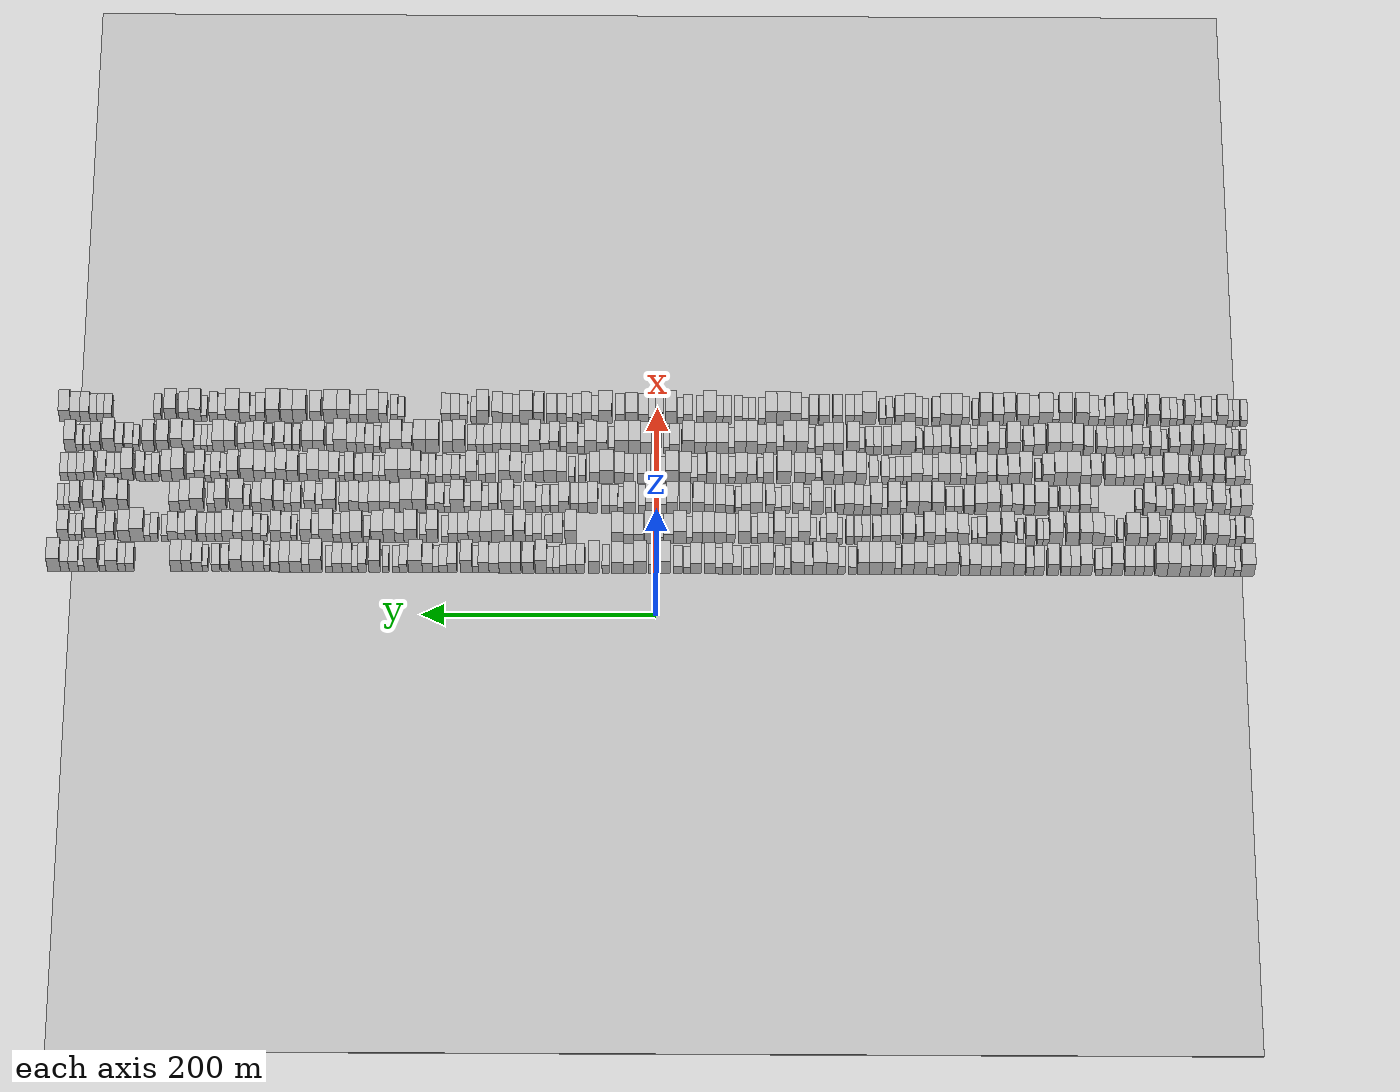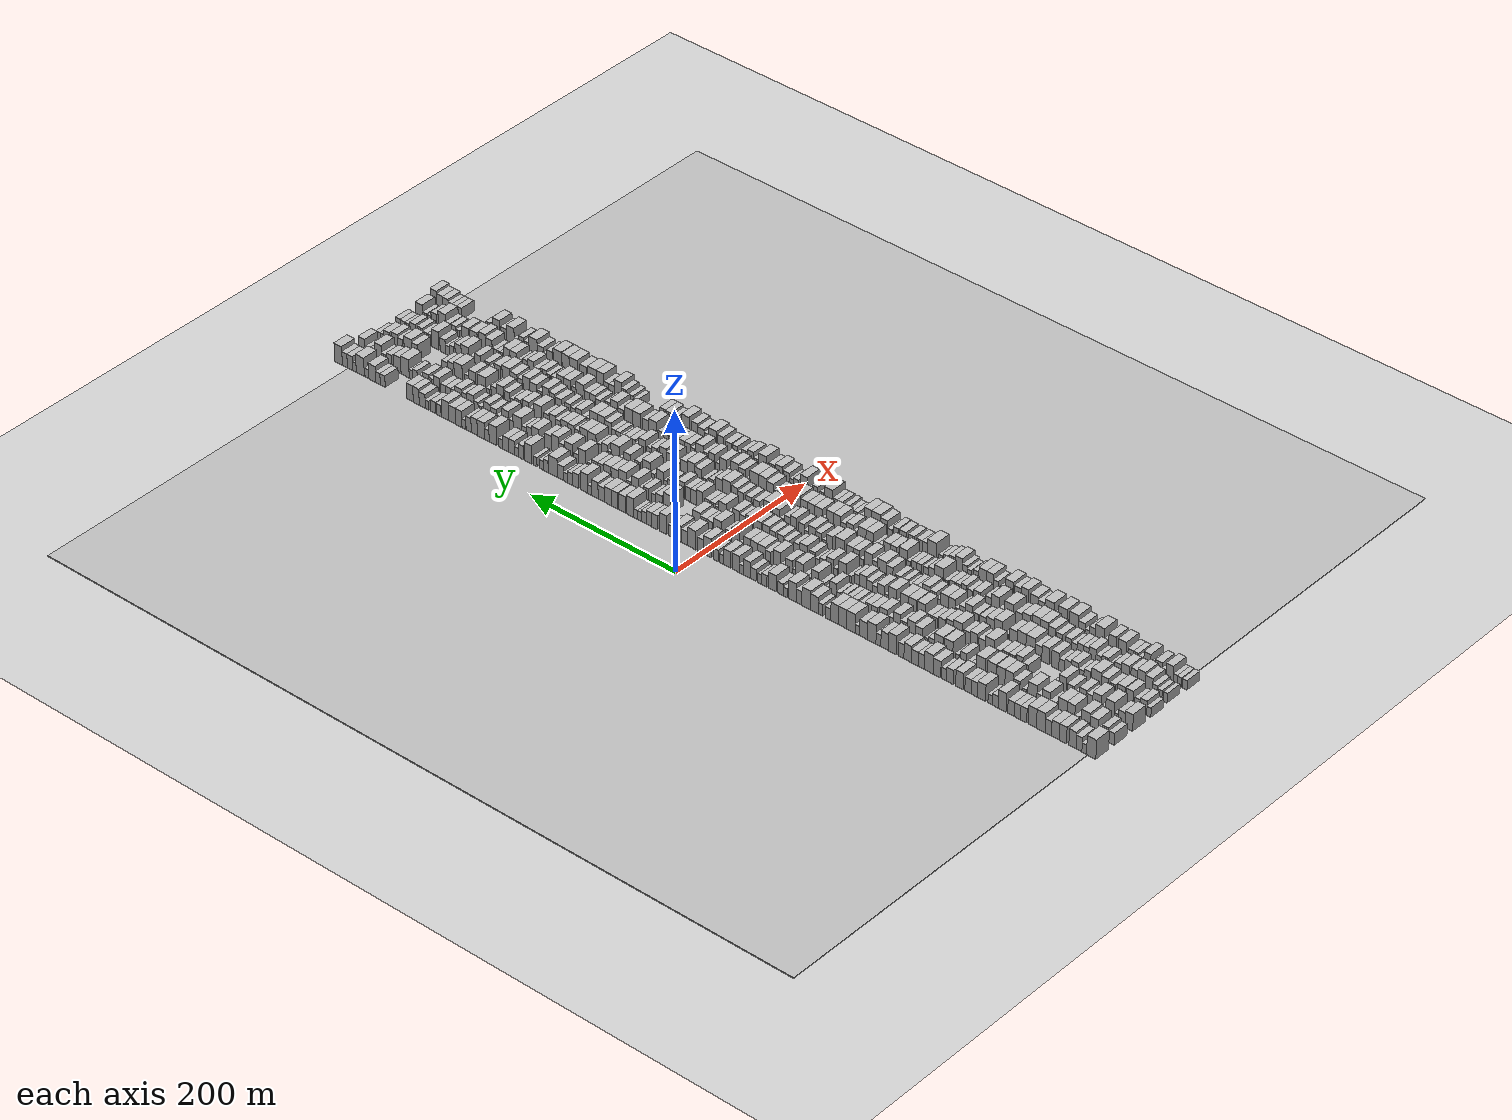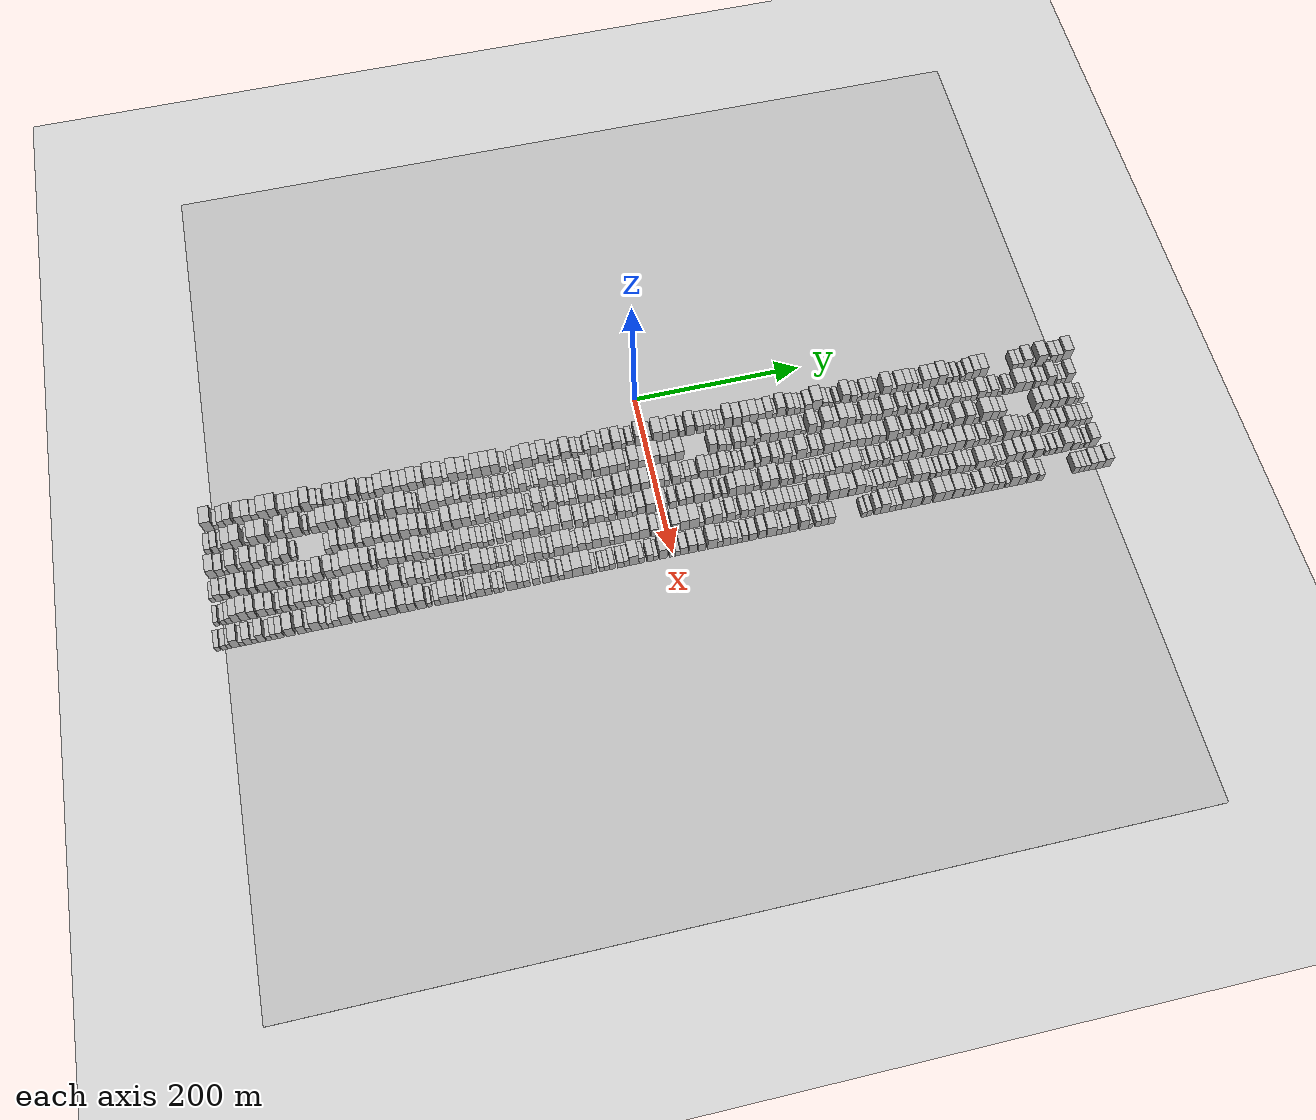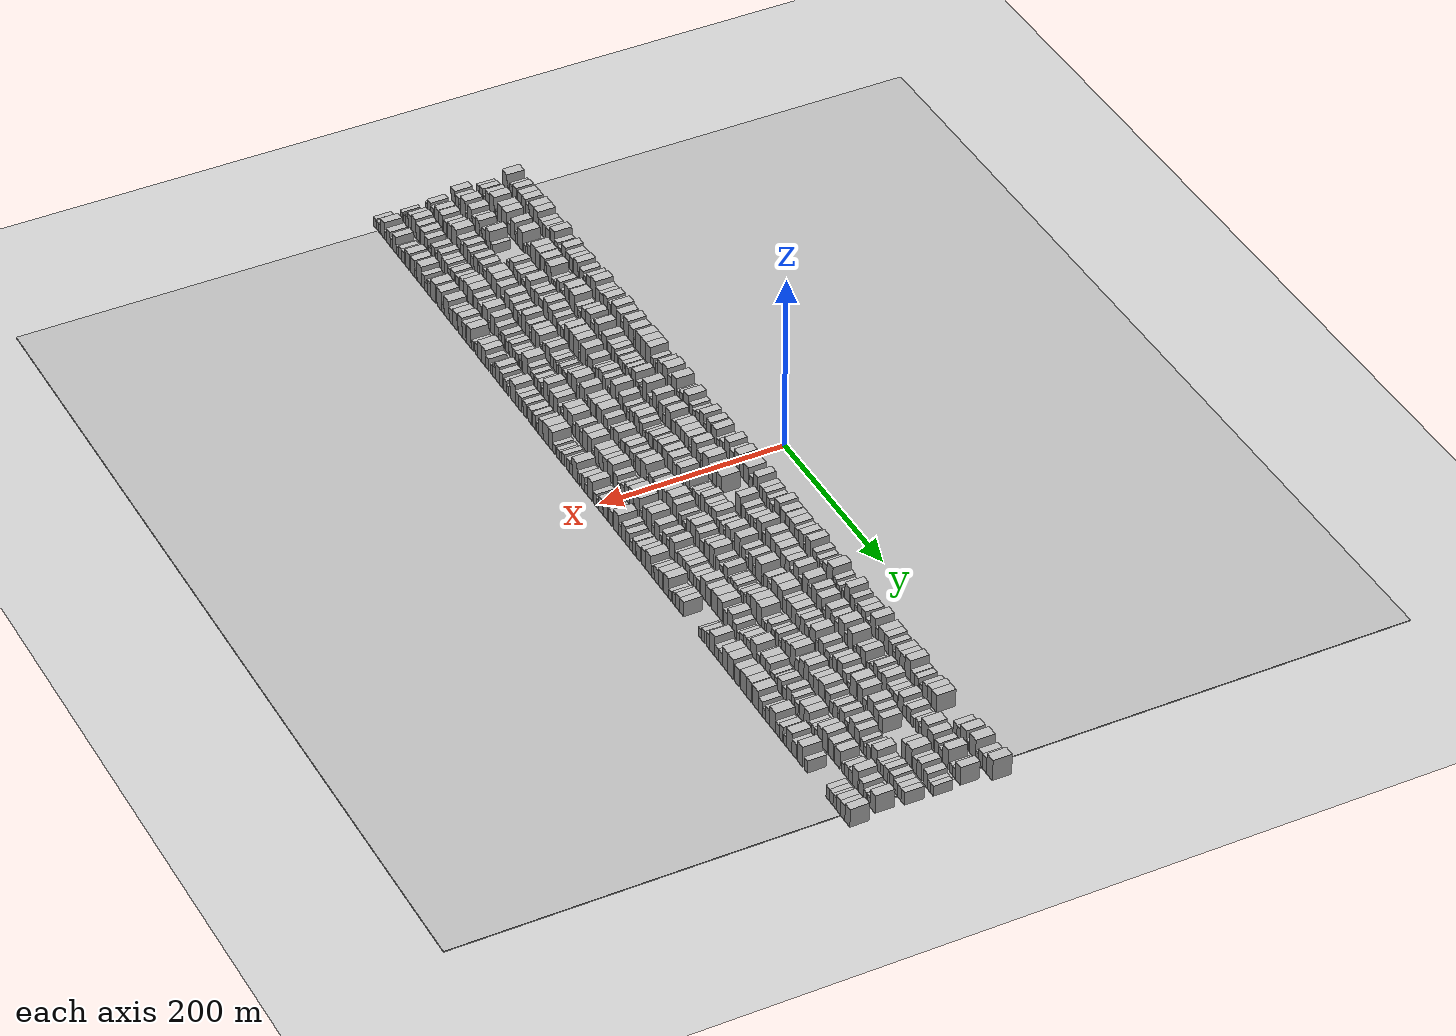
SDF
<?xml version="1.0" encoding="utf-8"?>

<sdf version="1.6">

   <world name="default">

      <gui fullscreen="0">

         <camera name="user_camera">

            <pose>-15 0 4.57585 0 0 0</pose>

            <view_controller>orbit</view_controller>

         </camera>

      </gui>

      <scene>

         <sky>

           <clouds>

             <speed>12</speed>

           </clouds>

         </sky>

         <ambient>0.4 0.4 0.4 1</ambient>

         <background>0.7 0.7 0.7 1</background>

         <shadows>1</shadows>

      </scene>

      <gravity>0 0 -9.8066</gravity>

      <magnetic_field>6e-06 2.3e-05 -4.2e-05</magnetic_field>

      <physics default="0" name="default_physics" type="ode">

         <ode>

            <solver>

               <type>quick</type>

               <iters>10</iters>

               <sor>1.0</sor>

               <use_dynamic_moi_rescaling>0</use_dynamic_moi_rescaling>

            </solver>

            <constraints>

               <cfm>0</cfm>

               <erp>0.2</erp>

               <contact_max_correcting_vel>100</contact_max_correcting_vel>

               <contact_surface_layer>0.001</contact_surface_layer>

            </constraints>

         </ode>

         <max_step_size>0.004</max_step_size>

         <real_time_factor>1</real_time_factor>

         <real_time_update_rate>250</real_time_update_rate>

      </physics>

      <light name="sun" type="directional">

         <cast_shadows>1</cast_shadows>

         <pose>0 0 10 0 0 0</pose>

         <diffuse>0.8 0.8 0.8 1</diffuse>

         <specular>0.2 0.2 0.2 1</specular>

         <attenuation>

            <range>1000</range>

            <constant>0.9</constant>

            <linear>0.01</linear>

            <quadratic>0.001</quadratic>

         </attenuation>

         <direction>-0.5 0.1 -0.9</direction>

      </light>

      <include>

         <name>ground_plane_1</name>

         <uri>model://HANNAS_ground_plane</uri>

         <pose>0 0 0  0 0 0</pose>

      </include>

      <include>

         <name>ground_plane_2</name>

         <uri>model://HANNAS_ground_plane</uri>

         <pose>100 0 0  0 0 0</pose>

      </include>

      <model name="building_1">

         <static>1</static>

         <pose frame="">50.0000 -504.2040 0 0.000000 0.000000 0.000000</pose>

         <link name="link">

            <pose frame="">0 0 12.00 0 0 0</pose>

            <collision name="collision">

               <geometry>

                  <box>

                     <size>20.0000 11.5920 24.0000</size>

                  </box>

               </geometry>

               <max_contacts>10</max_contacts>

               <surface>

                  <contact>

                     <ode/>

                  </contact>

                  <bounce/>

                  <friction>

                     <torsional>

                        <ode/>

                     </torsional>

                     <ode/>

                  </friction>

               </surface>

            </collision>

            <visual name="visual">

               <cast_shadows>0</cast_shadows>

               <geometry>

                  <box>

                     <size>20.0000 11.5920 24.0000</size>

                  </box>

               </geometry>

               <material>

                  <script>

                     <uri>model://HANNAS_wall/materials/scripts</uri>

                     <uri>model://HANNAS_wall/materials/textures</uri>

                     <name>vrc/HANNAS_wall</name>

                  </script>

               </material>

            </visual>

            <self_collide>0</self_collide>

            <enable_wind>0</enable_wind>

            <kinematic>0</kinematic>

         </link>

      </model>

      <model name="building_2">

         <static>1</static>

         <pose frame="">50.0000 -495.5238 0 0.000000 0.000000 0.000000</pose>

         <link name="link">

            <pose frame="">0 0 6.00 0 0 0</pose>

            <collision name="collision">

               <geometry>

                  <box>

                     <size>20.0000 5.7683 12.0000</size>

                  </box>

               </geometry>

               <max_contacts>10</max_contacts>

               <surface>

                  <contact>

                     <ode/>

                  </contact>

                  <bounce/>

                  <friction>

                     <torsional>

                        <ode/>

                     </torsional>

                     <ode/>

                  </friction>

               </surface>

            </collision>

            <visual name="visual">

               <cast_shadows>0</cast_shadows>

               <geometry>

                  <box>

                     <size>20.0000 5.7683 12.0000</size>

                  </box>

               </geometry>

               <material>

                  <script>

                     <uri>model://HANNAS_wall/materials/scripts</uri>

                     <uri>model://HANNAS_wall/materials/textures</uri>

                     <name>vrc/HANNAS_wall</name>

                  </script>

               </material>

            </visual>

            <self_collide>0</self_collide>

            <enable_wind>0</enable_wind>

            <kinematic>0</kinematic>

         </link>

      </model>

      <model name="building_3">

         <static>1</static>

         <pose frame="">50.0000 -488.9735 0 0.000000 0.000000 0.000000</pose>

         <link name="link">

            <pose frame="">0 0 9.00 0 0 0</pose>

            <collision name="collision">

               <geometry>

                  <box>

                     <size>20.0000 7.3324 18.0000</size>

                  </box>

               </geometry>

               <max_contacts>10</max_contacts>

               <surface>

                  <contact>

                     <ode/>

                  </contact>

                  <bounce/>

                  <friction>

                     <torsional>

                        <ode/>

                     </torsional>

                     <ode/>

                  </friction>

               </surface>

            </collision>

            <visual name="visual">

               <cast_shadows>0</cast_shadows>

               <geometry>

                  <box>

                     <size>20.0000 7.3324 18.0000</size>

                  </box>

               </geometry>

               <material>

                  <script>

                     <uri>model://HANNAS_wall/materials/scripts</uri>

                     <uri>model://HANNAS_wall/materials/textures</uri>

                     <name>vrc/HANNAS_wall</name>

                  </script>

               </material>

            </visual>

            <self_collide>0</self_collide>

            <enable_wind>0</enable_wind>

            <kinematic>0</kinematic>

         </link>

      </model>

      <model name="building_4">

         <static>1</static>

         <pose frame="">50.0000 -480.8503 0 0.000000 0.000000 0.000000</pose>

         <link name="link">

            <pose frame="">0 0 10.50 0 0 0</pose>

            <collision name="collision">

               <geometry>

                  <box>

                     <size>20.0000 8.9139 21.0000</size>

                  </box>

               </geometry>

               <max_contacts>10</max_contacts>

               <surface>

                  <contact>

                     <ode/>

                  </contact>

                  <bounce/>

                  <friction>

                     <torsional>

                        <ode/>

                     </torsional>

                     <ode/>

                  </friction>

               </surface>

            </collision>

            <visual name="visual">

               <cast_shadows>0</cast_shadows>

               <geometry>

                  <box>

                     <size>20.0000 8.9139 21.0000</size>

                  </box>

               </geometry>

               <material>

                  <script>

                     <uri>model://HANNAS_wall/materials/scripts</uri>

                     <uri>model://HANNAS_wall/materials/textures</uri>

                     <name>vrc/HANNAS_wall</name>

                  </script>

               </material>

            </visual>

            <self_collide>0</self_collide>

            <enable_wind>0</enable_wind>

            <kinematic>0</kinematic>

         </link>

      </model>

      <model name="building_5">

         <static>1</static>

         <pose frame="">50.0000 -468.9195 0 0.000000 0.000000 0.000000</pose>

         <link name="link">

            <pose frame="">0 0 10.50 0 0 0</pose>

            <collision name="collision">

               <geometry>

                  <box>

                     <size>20.0000 8.9476 21.0000</size>

                  </box>

               </geometry>

               <max_contacts>10</max_contacts>

               <surface>

                  <contact>

                     <ode/>

                  </contact>

                  <bounce/>

                  <friction>

                     <torsional>

                        <ode/>

                     </torsional>

                     <ode/>

                  </friction>

               </surface>

            </collision>

            <visual name="visual">

               <cast_shadows>0</cast_shadows>

               <geometry>

                  <box>

                     <size>20.0000 8.9476 21.0000</size>

                  </box>

               </geometry>

               <material>

                  <script>

                     <uri>model://HANNAS_wall/materials/scripts</uri>

                     <uri>model://HANNAS_wall/materials/textures</uri>

                     <name>vrc/HANNAS_wall</name>

                  </script>

               </material>

            </visual>

            <self_collide>0</self_collide>

            <enable_wind>0</enable_wind>

            <kinematic>0</kinematic>

         </link>

      </model>

      <model name="building_6">

         <static>1</static>

         <pose frame="">50.0000 -459.5976 0 0.000000 0.000000 0.000000</pose>

         <link name="link">

            <pose frame="">0 0 10.50 0 0 0</pose>

            <collision name="collision">

               <geometry>

                  <box>

                     <size>20.0000 9.6962 21.0000</size>

                  </box>

               </geometry>

               <max_contacts>10</max_contacts>

               <surface>

                  <contact>

                     <ode/>

                  </contact>

                  <bounce/>

                  <friction>

                     <torsional>

                        <ode/>

                     </torsional>

                     <ode/>

                  </friction>

               </surface>

            </collision>

            <visual name="visual">

               <cast_shadows>0</cast_shadows>

               <geometry>

                  <box>

                     <size>20.0000 9.6962 21.0000</size>

                  </box>

               </geometry>

               <material>

                  <script>

                     <uri>model://HANNAS_wall/materials/scripts</uri>

                     <uri>model://HANNAS_wall/materials/textures</uri>

                     <name>vrc/HANNAS_wall</name>

                  </script>

               </material>

            </visual>

            <self_collide>0</self_collide>

            <enable_wind>0</enable_wind>

            <kinematic>0</kinematic>

         </link>

      </model>

      <model name="building_7">

         <static>1</static>

         <pose frame="">50.0000 -450.7209 0 0.000000 0.000000 0.000000</pose>

         <link name="link">

            <pose frame="">0 0 9.00 0 0 0</pose>

            <collision name="collision">

               <geometry>

                  <box>

                     <size>20.0000 8.0573 18.0000</size>

                  </box>

               </geometry>

               <max_contacts>10</max_contacts>

               <surface>

                  <contact>

                     <ode/>

                  </contact>

                  <bounce/>

                  <friction>

                     <torsional>

                        <ode/>

                     </torsional>

                     <ode/>

                  </friction>

               </surface>

            </collision>

            <visual name="visual">

               <cast_shadows>0</cast_shadows>

               <geometry>

                  <box>

                     <size>20.0000 8.0573 18.0000</size>

                  </box>

               </geometry>

               <material>

                  <script>

                     <uri>model://HANNAS_wall/materials/scripts</uri>

                     <uri>model://HANNAS_wall/materials/textures</uri>

                     <name>vrc/HANNAS_wall</name>

                  </script>

               </material>

            </visual>

            <self_collide>0</self_collide>

            <enable_wind>0</enable_wind>

            <kinematic>0</kinematic>

         </link>

      </model>

      <model name="building_8">

         <static>1</static>

         <pose frame="">50.0000 -441.2656 0 0.000000 0.000000 0.000000</pose>

         <link name="link">

            <pose frame="">0 0 12.00 0 0 0</pose>

            <collision name="collision">

               <geometry>

                  <box>

                     <size>20.0000 10.8533 24.0000</size>

                  </box>

               </geometry>

               <max_contacts>10</max_contacts>

               <surface>

                  <contact>

                     <ode/>

                  </contact>

                  <bounce/>

                  <friction>

                     <torsional>

                        <ode/>

                     </torsional>

                     <ode/>

                  </friction>

               </surface>

            </collision>

            <visual name="visual">

               <cast_shadows>0</cast_shadows>

               <geometry>

                  <box>

                     <size>20.0000 10.8533 24.0000</size>

                  </box>

               </geometry>

               <material>

                  <script>

                     <uri>model://HANNAS_wall/materials/scripts</uri>

                     <uri>model://HANNAS_wall/materials/textures</uri>

                     <name>vrc/HANNAS_wall</name>

                  </script>

               </material>

            </visual>

            <self_collide>0</self_collide>

            <enable_wind>0</enable_wind>

            <kinematic>0</kinematic>

         </link>

      </model>

      <model name="building_9">

         <static>1</static>

         <pose frame="">50.0000 -430.6764 0 0.000000 0.000000 0.000000</pose>

         <link name="link">

            <pose frame="">0 0 12.00 0 0 0</pose>

            <collision name="collision">

               <geometry>

                  <box>

                     <size>20.0000 10.3251 24.0000</size>

                  </box>

               </geometry>

               <max_contacts>10</max_contacts>

               <surface>

                  <contact>

                     <ode/>

                  </contact>

                  <bounce/>

                  <friction>

                     <torsional>

                        <ode/>

                     </torsional>

                     <ode/>

                  </friction>

               </surface>

            </collision>

            <visual name="visual">

               <cast_shadows>0</cast_shadows>

               <geometry>

                  <box>

                     <size>20.0000 10.3251 24.0000</size>

                  </box>

               </geometry>

               <material>

                  <script>

                     <uri>model://HANNAS_wall/materials/scripts</uri>

                     <uri>model://HANNAS_wall/materials/textures</uri>

                     <name>vrc/HANNAS_wall</name>

                  </script>

               </material>

            </visual>

            <self_collide>0</self_collide>

            <enable_wind>0</enable_wind>

            <kinematic>0</kinematic>

         </link>

      </model>

      <model name="building_10">

         <static>1</static>

         <pose frame="">50.0000 -419.6778 0 0.000000 0.000000 0.000000</pose>

         <link name="link">

            <pose frame="">0 0 9.00 0 0 0</pose>

            <collision name="collision">

               <geometry>

                  <box>

                     <size>20.0000 7.6722 18.0000</size>

                  </box>

               </geometry>

               <max_contacts>10</max_contacts>

               <surface>

                  <contact>

                     <ode/>

                  </contact>

                  <bounce/>

                  <friction>

                     <torsional>

                        <ode/>

                     </torsional>

                     <ode/>

                  </friction>

               </surface>

            </collision>

            <visual name="visual">

               <cast_shadows>0</cast_shadows>

               <geometry>

                  <box>

                     <size>20.0000 7.6722 18.0000</size>

                  </box>

               </geometry>

               <material>

                  <script>

                     <uri>model://HANNAS_wall/materials/scripts</uri>

                     <uri>model://HANNAS_wall/materials/textures</uri>

                     <name>vrc/HANNAS_wall</name>

                  </script>

               </material>

            </visual>

            <self_collide>0</self_collide>

            <enable_wind>0</enable_wind>

            <kinematic>0</kinematic>

         </link>

      </model>

      <model name="building_11">

         <static>1</static>

         <pose frame="">50.0000 -411.8984 0 0.000000 0.000000 0.000000</pose>

         <link name="link">

            <pose frame="">0 0 9.00 0 0 0</pose>

            <collision name="collision">

               <geometry>

                  <box>

                     <size>20.0000 7.8866 18.0000</size>

                  </box>

               </geometry>

               <max_contacts>10</max_contacts>

               <surface>

                  <contact>

                     <ode/>

                  </contact>

                  <bounce/>

                  <friction>

                     <torsional>

                        <ode/>

                     </torsional>

                     <ode/>

                  </friction>

               </surface>

            </collision>

            <visual name="visual">

               <cast_shadows>0</cast_shadows>

               <geometry>

                  <box>

                     <size>20.0000 7.8866 18.0000</size>

                  </box>

               </geometry>

               <material>

                  <script>

                     <uri>model://HANNAS_wall/materials/scripts</uri>

                     <uri>model://HANNAS_wall/materials/textures</uri>

                     <name>vrc/HANNAS_wall</name>

                  </script>

               </material>

            </visual>

            <self_collide>0</self_collide>

            <enable_wind>0</enable_wind>

            <kinematic>0</kinematic>

         </link>

      </model>

      <model name="building_12">

         <static>1</static>

         <pose frame="">50.0000 -403.7745 0 0.000000 0.000000 0.000000</pose>

         <link name="link">

            <pose frame="">0 0 9.00 0 0 0</pose>

            <collision name="collision">

               <geometry>

                  <box>

                     <size>20.0000 8.3612 18.0000</size>

                  </box>

               </geometry>

               <max_contacts>10</max_contacts>

               <surface>

                  <contact>

                     <ode/>

                  </contact>

                  <bounce/>

                  <friction>

                     <torsional>

                        <ode/>

                     </torsional>

                     <ode/>

                  </friction>

               </surface>

            </collision>

            <visual name="visual">

               <cast_shadows>0</cast_shadows>

               <geometry>

                  <box>

                     <size>20.0000 8.3612 18.0000</size>

                  </box>

               </geometry>

               <material>

                  <script>

                     <uri>model://HANNAS_wall/materials/scripts</uri>

                     <uri>model://HANNAS_wall/materials/textures</uri>

                     <name>vrc/HANNAS_wall</name>

                  </script>

               </material>

            </visual>

            <self_collide>0</self_collide>

            <enable_wind>0</enable_wind>

            <kinematic>0</kinematic>

         </link>

      </model>

      <model name="building_13">

         <static>1</static>

         <pose frame="">50.0000 -392.6728 0 0.000000 0.000000 0.000000</pose>

         <link name="link">

            <pose frame="">0 0 12.00 0 0 0</pose>

            <collision name="collision">

               <geometry>

                  <box>

                     <size>20.0000 9.8420 24.0000</size>

                  </box>

               </geometry>

               <max_contacts>10</max_contacts>

               <surface>

                  <contact>

                     <ode/>

                  </contact>

                  <bounce/>

                  <friction>

                     <torsional>

                        <ode/>

                     </torsional>

                     <ode/>

                  </friction>

               </surface>

            </collision>

            <visual name="visual">

               <cast_shadows>0</cast_shadows>

               <geometry>

                  <box>

                     <size>20.0000 9.8420 24.0000</size>

                  </box>

               </geometry>

               <material>

                  <script>

                     <uri>model://HANNAS_wall/materials/scripts</uri>

                     <uri>model://HANNAS_wall/materials/textures</uri>

                     <name>vrc/HANNAS_wall</name>

                  </script>

               </material>

            </visual>

            <self_collide>0</self_collide>

            <enable_wind>0</enable_wind>

            <kinematic>0</kinematic>

         </link>

      </model>

      <model name="building_14">

         <static>1</static>

         <pose frame="">50.0000 -384.0096 0 0.000000 0.000000 0.000000</pose>

         <link name="link">

            <pose frame="">0 0 7.50 0 0 0</pose>

            <collision name="collision">

               <geometry>

                  <box>

                     <size>20.0000 7.4845 15.0000</size>

                  </box>

               </geometry>

               <max_contacts>10</max_contacts>

               <surface>

                  <contact>

                     <ode/>

                  </contact>

                  <bounce/>

                  <friction>

                     <torsional>

                        <ode/>

                     </torsional>

                     <ode/>

                  </friction>

               </surface>

            </collision>

            <visual name="visual">

               <cast_shadows>0</cast_shadows>

               <geometry>

                  <box>

                     <size>20.0000 7.4845 15.0000</size>

                  </box>

               </geometry>

               <material>

                  <script>

                     <uri>model://HANNAS_wall/materials/scripts</uri>

                     <uri>model://HANNAS_wall/materials/textures</uri>

                     <name>vrc/HANNAS_wall</name>

                  </script>

               </material>

            </visual>

            <self_collide>0</self_collide>

            <enable_wind>0</enable_wind>

            <kinematic>0</kinematic>

         </link>

      </model>

      <model name="building_15">

         <static>1</static>

         <pose frame="">50.0000 -377.3860 0 0.000000 0.000000 0.000000</pose>

         <link name="link">

            <pose frame="">0 0 6.00 0 0 0</pose>

            <collision name="collision">

               <geometry>

                  <box>

                     <size>20.0000 5.7627 12.0000</size>

                  </box>

               </geometry>

               <max_contacts>10</max_contacts>

               <surface>

                  <contact>

                     <ode/>

                  </contact>

                  <bounce/>

                  <friction>

                     <torsional>

                        <ode/>

                     </torsional>

                     <ode/>

                  </friction>

               </surface>

            </collision>

            <visual name="visual">

               <cast_shadows>0</cast_shadows>

               <geometry>

                  <box>

                     <size>20.0000 5.7627 12.0000</size>

                  </box>

               </geometry>

               <material>

                  <script>

                     <uri>model://HANNAS_wall/materials/scripts</uri>

                     <uri>model://HANNAS_wall/materials/textures</uri>

                     <name>vrc/HANNAS_wall</name>

                  </script>

               </material>

            </visual>

            <self_collide>0</self_collide>

            <enable_wind>0</enable_wind>

            <kinematic>0</kinematic>

         </link>

      </model>

      <model name="building_16">

         <static>1</static>

         <pose frame="">50.0000 -366.4196 0 0.000000 0.000000 0.000000</pose>

         <link name="link">

            <pose frame="">0 0 10.50 0 0 0</pose>

            <collision name="collision">

               <geometry>

                  <box>

                     <size>20.0000 10.1700 21.0000</size>

                  </box>

               </geometry>

               <max_contacts>10</max_contacts>

               <surface>

                  <contact>

                     <ode/>

                  </contact>

                  <bounce/>

                  <friction>

                     <torsional>

                        <ode/>

                     </torsional>

                     <ode/>

                  </friction>

               </surface>

            </collision>

            <visual name="visual">

               <cast_shadows>0</cast_shadows>

               <geometry>

                  <box>

                     <size>20.0000 10.1700 21.0000</size>

                  </box>

               </geometry>

               <material>

                  <script>

                     <uri>model://HANNAS_wall/materials/scripts</uri>

                     <uri>model://HANNAS_wall/materials/textures</uri>

                     <name>vrc/HANNAS_wall</name>

                  </script>

               </material>

            </visual>

            <self_collide>0</self_collide>

            <enable_wind>0</enable_wind>

            <kinematic>0</kinematic>

         </link>

      </model>

      <model name="building_17">

         <static>1</static>

         <pose frame="">50.0000 -357.2056 0 0.000000 0.000000 0.000000</pose>

         <link name="link">

            <pose frame="">0 0 9.00 0 0 0</pose>

            <collision name="collision">

               <geometry>

                  <box>

                     <size>20.0000 8.2580 18.0000</size>

                  </box>

               </geometry>

               <max_contacts>10</max_contacts>

               <surface>

                  <contact>

                     <ode/>

                  </contact>

                  <bounce/>

                  <friction>

                     <torsional>

                        <ode/>

                     </torsional>

                     <ode/>

                  </friction>

               </surface>

            </collision>

            <visual name="visual">

               <cast_shadows>0</cast_shadows>

               <geometry>

                  <box>

                     <size>20.0000 8.2580 18.0000</size>

                  </box>

               </geometry>

               <material>

                  <script>

                     <uri>model://HANNAS_wall/materials/scripts</uri>

                     <uri>model://HANNAS_wall/materials/textures</uri>

                     <name>vrc/HANNAS_wall</name>

                  </script>

               </material>

            </visual>

            <self_collide>0</self_collide>

            <enable_wind>0</enable_wind>

            <kinematic>0</kinematic>

         </link>

      </model>

      <model name="building_18">

         <static>1</static>

         <pose frame="">50.0000 -349.0962 0 0.000000 0.000000 0.000000</pose>

         <link name="link">

            <pose frame="">0 0 9.00 0 0 0</pose>

            <collision name="collision">

               <geometry>

                  <box>

                     <size>20.0000 7.9607 18.0000</size>

                  </box>

               </geometry>

               <max_contacts>10</max_contacts>

               <surface>

                  <contact>

                     <ode/>

                  </contact>

                  <bounce/>

                  <friction>

                     <torsional>

                        <ode/>

                     </torsional>

                     <ode/>

                  </friction>

               </surface>

            </collision>

            <visual name="visual">

               <cast_shadows>0</cast_shadows>

               <geometry>

                  <box>

                     <size>20.0000 7.9607 18.0000</size>

                  </box>

               </geometry>

               <material>

                  <script>

                     <uri>model://HANNAS_wall/materials/scripts</uri>

                     <uri>model://HANNAS_wall/materials/textures</uri>

                     <name>vrc/HANNAS_wall</name>

                  </script>

               </material>

            </visual>

            <self_collide>0</self_collide>

            <enable_wind>0</enable_wind>

            <kinematic>0</kinematic>

         </link>

      </model>

      <model name="building_19">

         <static>1</static>

         <pose frame="">50.0000 -338.2764 0 0.000000 0.000000 0.000000</pose>

         <link name="link">

            <pose frame="">0 0 10.50 0 0 0</pose>

            <collision name="collision">

               <geometry>

                  <box>

                     <size>20.0000 9.6788 21.0000</size>

                  </box>

               </geometry>

               <max_contacts>10</max_contacts>

               <surface>

                  <contact>

                     <ode/>

                  </contact>

                  <bounce/>

                  <friction>

                     <torsional>

                        <ode/>

                     </torsional>

                     <ode/>

                  </friction>

               </surface>

            </collision>

            <visual name="visual">

               <cast_shadows>0</cast_shadows>

               <geometry>

                  <box>

                     <size>20.0000 9.6788 21.0000</size>

                  </box>

               </geometry>

               <material>

                  <script>

                     <uri>model://HANNAS_wall/materials/scripts</uri>

                     <uri>model://HANNAS_wall/materials/textures</uri>

                     <name>vrc/HANNAS_wall</name>

                  </script>

               </material>

            </visual>

            <self_collide>0</self_collide>

            <enable_wind>0</enable_wind>

            <kinematic>0</kinematic>

         </link>

      </model>

      <model name="building_20">

         <static>1</static>

         <pose frame="">50.0000 -326.1015 0 0.000000 0.000000 0.000000</pose>

         <link name="link">

            <pose frame="">0 0 9.00 0 0 0</pose>

            <collision name="collision">

               <geometry>

                  <box>

                     <size>20.0000 8.6711 18.0000</size>

                  </box>

               </geometry>

               <max_contacts>10</max_contacts>

               <surface>

                  <contact>

                     <ode/>

                  </contact>

                  <bounce/>

                  <friction>

                     <torsional>

                        <ode/>

                     </torsional>

                     <ode/>

                  </friction>

               </surface>

            </collision>

            <visual name="visual">

               <cast_shadows>0</cast_shadows>

               <geometry>

                  <box>

                     <size>20.0000 8.6711 18.0000</size>

                  </box>

               </geometry>

               <material>

                  <script>

                     <uri>model://HANNAS_wall/materials/scripts</uri>

                     <uri>model://HANNAS_wall/materials/textures</uri>

                     <name>vrc/HANNAS_wall</name>

                  </script>

               </material>

            </visual>

            <self_collide>0</self_collide>

            <enable_wind>0</enable_wind>

            <kinematic>0</kinematic>

         </link>

      </model>

      <model name="building_21">

         <static>1</static>

         <pose frame="">50.0000 -318.5105 0 0.000000 0.000000 0.000000</pose>

         <link name="link">

            <pose frame="">0 0 7.50 0 0 0</pose>

            <collision name="collision">

               <geometry>

                  <box>

                     <size>20.0000 6.5108 15.0000</size>

                  </box>

               </geometry>

               <max_contacts>10</max_contacts>

               <surface>

                  <contact>

                     <ode/>

                  </contact>

                  <bounce/>

                  <friction>

                     <torsional>

                        <ode/>

                     </torsional>

                     <ode/>

                  </friction>

               </surface>

            </collision>

            <visual name="visual">

               <cast_shadows>0</cast_shadows>

               <geometry>

                  <box>

                     <size>20.0000 6.5108 15.0000</size>

                  </box>

               </geometry>

               <material>

                  <script>

                     <uri>model://HANNAS_wall/materials/scripts</uri>

                     <uri>model://HANNAS_wall/materials/textures</uri>

                     <name>vrc/HANNAS_wall</name>

                  </script>

               </material>

            </visual>

            <self_collide>0</self_collide>

            <enable_wind>0</enable_wind>

            <kinematic>0</kinematic>

         </link>

      </model>

      <model name="building_22">

         <static>1</static>

         <pose frame="">50.0000 -309.3526 0 0.000000 0.000000 0.000000</pose>

         <link name="link">

            <pose frame="">0 0 10.50 0 0 0</pose>

            <collision name="collision">

               <geometry>

                  <box>

                     <size>20.0000 9.8051 21.0000</size>

                  </box>

               </geometry>

               <max_contacts>10</max_contacts>

               <surface>

                  <contact>

                     <ode/>

                  </contact>

                  <bounce/>

                  <friction>

                     <torsional>

                        <ode/>

                     </torsional>

                     <ode/>

                  </friction>

               </surface>

            </collision>

            <visual name="visual">

               <cast_shadows>0</cast_shadows>

               <geometry>

                  <box>

                     <size>20.0000 9.8051 21.0000</size>

                  </box>

               </geometry>

               <material>

                  <script>

                     <uri>model://HANNAS_wall/materials/scripts</uri>

                     <uri>model://HANNAS_wall/materials/textures</uri>

                     <name>vrc/HANNAS_wall</name>

                  </script>

               </material>

            </visual>

            <self_collide>0</self_collide>

            <enable_wind>0</enable_wind>

            <kinematic>0</kinematic>

         </link>

      </model>

      <model name="building_23">

         <static>1</static>

         <pose frame="">50.0000 -298.9540 0 0.000000 0.000000 0.000000</pose>

         <link name="link">

            <pose frame="">0 0 12.00 0 0 0</pose>

            <collision name="collision">

               <geometry>

                  <box>

                     <size>20.0000 10.9921 24.0000</size>

                  </box>

               </geometry>

               <max_contacts>10</max_contacts>

               <surface>

                  <contact>

                     <ode/>

                  </contact>

                  <bounce/>

                  <friction>

                     <torsional>

                        <ode/>

                     </torsional>

                     <ode/>

                  </friction>

               </surface>

            </collision>

            <visual name="visual">

               <cast_shadows>0</cast_shadows>

               <geometry>

                  <box>

                     <size>20.0000 10.9921 24.0000</size>

                  </box>

               </geometry>

               <material>

                  <script>

                     <uri>model://HANNAS_wall/materials/scripts</uri>

                     <uri>model://HANNAS_wall/materials/textures</uri>

                     <name>vrc/HANNAS_wall</name>

                  </script>

               </material>

            </visual>

            <self_collide>0</self_collide>

            <enable_wind>0</enable_wind>

            <kinematic>0</kinematic>

         </link>

      </model>

      <model name="building_24">

         <static>1</static>

         <pose frame="">50.0000 -289.2894 0 0.000000 0.000000 0.000000</pose>

         <link name="link">

            <pose frame="">0 0 9.00 0 0 0</pose>

            <collision name="collision">

               <geometry>

                  <box>

                     <size>20.0000 8.3369 18.0000</size>

                  </box>

               </geometry>

               <max_contacts>10</max_contacts>

               <surface>

                  <contact>

                     <ode/>

                  </contact>

                  <bounce/>

                  <friction>

                     <torsional>

                        <ode/>

                     </torsional>

                     <ode/>

                  </friction>

               </surface>

            </collision>

            <visual name="visual">

               <cast_shadows>0</cast_shadows>

               <geometry>

                  <box>

                     <size>20.0000 8.3369 18.0000</size>

                  </box>

               </geometry>

               <material>

                  <script>

                     <uri>model://HANNAS_wall/materials/scripts</uri>

                     <uri>model://HANNAS_wall/materials/textures</uri>

                     <name>vrc/HANNAS_wall</name>

                  </script>

               </material>

            </visual>

            <self_collide>0</self_collide>

            <enable_wind>0</enable_wind>

            <kinematic>0</kinematic>

         </link>

      </model>

      <model name="building_25">

         <static>1</static>

         <pose frame="">50.0000 -280.8331 0 0.000000 0.000000 0.000000</pose>

         <link name="link">

            <pose frame="">0 0 9.00 0 0 0</pose>

            <collision name="collision">

               <geometry>

                  <box>

                     <size>20.0000 8.5759 18.0000</size>

                  </box>

               </geometry>

               <max_contacts>10</max_contacts>

               <surface>

                  <contact>

                     <ode/>

                  </contact>

                  <bounce/>

                  <friction>

                     <torsional>

                        <ode/>

                     </torsional>

                     <ode/>

                  </friction>

               </surface>

            </collision>

            <visual name="visual">

               <cast_shadows>0</cast_shadows>

               <geometry>

                  <box>

                     <size>20.0000 8.5759 18.0000</size>

                  </box>

               </geometry>

               <material>

                  <script>

                     <uri>model://HANNAS_wall/materials/scripts</uri>

                     <uri>model://HANNAS_wall/materials/textures</uri>

                     <name>vrc/HANNAS_wall</name>

                  </script>

               </material>

            </visual>

            <self_collide>0</self_collide>

            <enable_wind>0</enable_wind>

            <kinematic>0</kinematic>

         </link>

      </model>

      <model name="building_26">

         <static>1</static>

         <pose frame="">50.0000 -271.6432 0 0.000000 0.000000 0.000000</pose>

         <link name="link">

            <pose frame="">0 0 10.50 0 0 0</pose>

            <collision name="collision">

               <geometry>

                  <box>

                     <size>20.0000 9.8039 21.0000</size>

                  </box>

               </geometry>

               <max_contacts>10</max_contacts>

               <surface>

                  <contact>

                     <ode/>

                  </contact>

                  <bounce/>

                  <friction>

                     <torsional>

                        <ode/>

                     </torsional>

                     <ode/>

                  </friction>

               </surface>

            </collision>

            <visual name="visual">

               <cast_shadows>0</cast_shadows>

               <geometry>

                  <box>

                     <size>20.0000 9.8039 21.0000</size>

                  </box>

               </geometry>

               <material>

                  <script>

                     <uri>model://HANNAS_wall/materials/scripts</uri>

                     <uri>model://HANNAS_wall/materials/textures</uri>

                     <name>vrc/HANNAS_wall</name>

                  </script>

               </material>

            </visual>

            <self_collide>0</self_collide>

            <enable_wind>0</enable_wind>

            <kinematic>0</kinematic>

         </link>

      </model>

      <model name="building_27">

         <static>1</static>

         <pose frame="">50.0000 -263.0269 0 0.000000 0.000000 0.000000</pose>

         <link name="link">

            <pose frame="">0 0 9.00 0 0 0</pose>

            <collision name="collision">

               <geometry>

                  <box>

                     <size>20.0000 7.4286 18.0000</size>

                  </box>

               </geometry>

               <max_contacts>10</max_contacts>

               <surface>

                  <contact>

                     <ode/>

                  </contact>

                  <bounce/>

                  <friction>

                     <torsional>

                        <ode/>

                     </torsional>

                     <ode/>

                  </friction>

               </surface>

            </collision>

            <visual name="visual">

               <cast_shadows>0</cast_shadows>

               <geometry>

                  <box>

                     <size>20.0000 7.4286 18.0000</size>

                  </box>

               </geometry>

               <material>

                  <script>

                     <uri>model://HANNAS_wall/materials/scripts</uri>

                     <uri>model://HANNAS_wall/materials/textures</uri>

                     <name>vrc/HANNAS_wall</name>

                  </script>

               </material>

            </visual>

            <self_collide>0</self_collide>

            <enable_wind>0</enable_wind>

            <kinematic>0</kinematic>

         </link>

      </model>

      <model name="building_28">

         <static>1</static>

         <pose frame="">50.0000 -252.0809 0 0.000000 0.000000 0.000000</pose>

         <link name="link">

            <pose frame="">0 0 12.00 0 0 0</pose>

            <collision name="collision">

               <geometry>

                  <box>

                     <size>20.0000 10.4635 24.0000</size>

                  </box>

               </geometry>

               <max_contacts>10</max_contacts>

               <surface>

                  <contact>

                     <ode/>

                  </contact>

                  <bounce/>

                  <friction>

                     <torsional>

                        <ode/>

                     </torsional>

                     <ode/>

                  </friction>

               </surface>

            </collision>

            <visual name="visual">

               <cast_shadows>0</cast_shadows>

               <geometry>

                  <box>

                     <size>20.0000 10.4635 24.0000</size>

                  </box>

               </geometry>

               <material>

                  <script>

                     <uri>model://HANNAS_wall/materials/scripts</uri>

                     <uri>model://HANNAS_wall/materials/textures</uri>

                     <name>vrc/HANNAS_wall</name>

                  </script>

               </material>

            </visual>

            <self_collide>0</self_collide>

            <enable_wind>0</enable_wind>

            <kinematic>0</kinematic>

         </link>

      </model>

      <model name="building_29">

         <static>1</static>

         <pose frame="">50.0000 -241.8548 0 0.000000 0.000000 0.000000</pose>

         <link name="link">

            <pose frame="">0 0 10.50 0 0 0</pose>

            <collision name="collision">

               <geometry>

                  <box>

                     <size>20.0000 9.9885 21.0000</size>

                  </box>

               </geometry>

               <max_contacts>10</max_contacts>

               <surface>

                  <contact>

                     <ode/>

                  </contact>

                  <bounce/>

                  <friction>

                     <torsional>

                        <ode/>

                     </torsional>

                     <ode/>

                  </friction>

               </surface>

            </collision>

            <visual name="visual">

               <cast_shadows>0</cast_shadows>

               <geometry>

                  <box>

                     <size>20.0000 9.9885 21.0000</size>

                  </box>

               </geometry>

               <material>

                  <script>

                     <uri>model://HANNAS_wall/materials/scripts</uri>

                     <uri>model://HANNAS_wall/materials/textures</uri>

                     <name>vrc/HANNAS_wall</name>

                  </script>

               </material>

            </visual>

            <self_collide>0</self_collide>

            <enable_wind>0</enable_wind>

            <kinematic>0</kinematic>

         </link>

      </model>

      <model name="building_30">

         <static>1</static>

         <pose frame="">50.0000 -233.6473 0 0.000000 0.000000 0.000000</pose>

         <link name="link">

            <pose frame="">0 0 7.50 0 0 0</pose>

            <collision name="collision">

               <geometry>

                  <box>

                     <size>20.0000 6.4266 15.0000</size>

                  </box>

               </geometry>

               <max_contacts>10</max_contacts>

               <surface>

                  <contact>

                     <ode/>

                  </contact>

                  <bounce/>

                  <friction>

                     <torsional>

                        <ode/>

                     </torsional>

                     <ode/>

                  </friction>

               </surface>

            </collision>

            <visual name="visual">

               <cast_shadows>0</cast_shadows>

               <geometry>

                  <box>

                     <size>20.0000 6.4266 15.0000</size>

                  </box>

               </geometry>

               <material>

                  <script>

                     <uri>model://HANNAS_wall/materials/scripts</uri>

                     <uri>model://HANNAS_wall/materials/textures</uri>

                     <name>vrc/HANNAS_wall</name>

                  </script>

               </material>

            </visual>

            <self_collide>0</self_collide>

            <enable_wind>0</enable_wind>

            <kinematic>0</kinematic>

         </link>

      </model>

      <model name="building_31">

         <static>1</static>

         <pose frame="">50.0000 -224.9230 0 0.000000 0.000000 0.000000</pose>

         <link name="link">

            <pose frame="">0 0 12.00 0 0 0</pose>

            <collision name="collision">

               <geometry>

                  <box>

                     <size>20.0000 11.0220 24.0000</size>

                  </box>

               </geometry>

               <max_contacts>10</max_contacts>

               <surface>

                  <contact>

                     <ode/>

                  </contact>

                  <bounce/>

                  <friction>

                     <torsional>

                        <ode/>

                     </torsional>

                     <ode/>

                  </friction>

               </surface>

            </collision>

            <visual name="visual">

               <cast_shadows>0</cast_shadows>

               <geometry>

                  <box>

                     <size>20.0000 11.0220 24.0000</size>

                  </box>

               </geometry>

               <material>

                  <script>

                     <uri>model://HANNAS_wall/materials/scripts</uri>

                     <uri>model://HANNAS_wall/materials/textures</uri>

                     <name>vrc/HANNAS_wall</name>

                  </script>

               </material>

            </visual>

            <self_collide>0</self_collide>

            <enable_wind>0</enable_wind>

            <kinematic>0</kinematic>

         </link>

      </model>

      <model name="building_32">

         <static>1</static>

         <pose frame="">50.0000 -214.2263 0 0.000000 0.000000 0.000000</pose>

         <link name="link">

            <pose frame="">0 0 10.50 0 0 0</pose>

            <collision name="collision">

               <geometry>

                  <box>

                     <size>20.0000 10.3713 21.0000</size>

                  </box>

               </geometry>

               <max_contacts>10</max_contacts>

               <surface>

                  <contact>

                     <ode/>

                  </contact>

                  <bounce/>

                  <friction>

                     <torsional>

                        <ode/>

                     </torsional>

                     <ode/>

                  </friction>

               </surface>

            </collision>

            <visual name="visual">

               <cast_shadows>0</cast_shadows>

               <geometry>

                  <box>

                     <size>20.0000 10.3713 21.0000</size>

                  </box>

               </geometry>

               <material>

                  <script>

                     <uri>model://HANNAS_wall/materials/scripts</uri>

                     <uri>model://HANNAS_wall/materials/textures</uri>

                     <name>vrc/HANNAS_wall</name>

                  </script>

               </material>

            </visual>

            <self_collide>0</self_collide>

            <enable_wind>0</enable_wind>

            <kinematic>0</kinematic>

         </link>

      </model>

      <model name="building_33">

         <static>1</static>

         <pose frame="">50.0000 -206.0952 0 0.000000 0.000000 0.000000</pose>

         <link name="link">

            <pose frame="">0 0 6.00 0 0 0</pose>

            <collision name="collision">

               <geometry>

                  <box>

                     <size>20.0000 5.8910 12.0000</size>

                  </box>

               </geometry>

               <max_contacts>10</max_contacts>

               <surface>

                  <contact>

                     <ode/>

                  </contact>

                  <bounce/>

                  <friction>

                     <torsional>

                        <ode/>

                     </torsional>

                     <ode/>

                  </friction>

               </surface>

            </collision>

            <visual name="visual">

               <cast_shadows>0</cast_shadows>

               <geometry>

                  <box>

                     <size>20.0000 5.8910 12.0000</size>

                  </box>

               </geometry>

               <material>

                  <script>

                     <uri>model://HANNAS_wall/materials/scripts</uri>

                     <uri>model://HANNAS_wall/materials/textures</uri>

                     <name>vrc/HANNAS_wall</name>

                  </script>

               </material>

            </visual>

            <self_collide>0</self_collide>

            <enable_wind>0</enable_wind>

            <kinematic>0</kinematic>

         </link>

      </model>

      <model name="building_34">

         <static>1</static>

         <pose frame="">50.0000 -197.7079 0 0.000000 0.000000 0.000000</pose>

         <link name="link">

            <pose frame="">0 0 12.00 0 0 0</pose>

            <collision name="collision">

               <geometry>

                  <box>

                     <size>20.0000 10.8836 24.0000</size>

                  </box>

               </geometry>

               <max_contacts>10</max_contacts>

               <surface>

                  <contact>

                     <ode/>

                  </contact>

                  <bounce/>

                  <friction>

                     <torsional>

                        <ode/>

                     </torsional>

                     <ode/>

                  </friction>

               </surface>

            </collision>

            <visual name="visual">

               <cast_shadows>0</cast_shadows>

               <geometry>

                  <box>

                     <size>20.0000 10.8836 24.0000</size>

                  </box>

               </geometry>

               <material>

                  <script>

                     <uri>model://HANNAS_wall/materials/scripts</uri>

                     <uri>model://HANNAS_wall/materials/textures</uri>

                     <name>vrc/HANNAS_wall</name>

                  </script>

               </material>

            </visual>

            <self_collide>0</self_collide>

            <enable_wind>0</enable_wind>

            <kinematic>0</kinematic>

         </link>

      </model>

      <model name="building_35">

         <static>1</static>

         <pose frame="">50.0000 -186.8237 0 0.000000 0.000000 0.000000</pose>

         <link name="link">

            <pose frame="">0 0 12.00 0 0 0</pose>

            <collision name="collision">

               <geometry>

                  <box>

                     <size>20.0000 10.8848 24.0000</size>

                  </box>

               </geometry>

               <max_contacts>10</max_contacts>

               <surface>

                  <contact>

                     <ode/>

                  </contact>

                  <bounce/>

                  <friction>

                     <torsional>

                        <ode/>

                     </torsional>

                     <ode/>

                  </friction>

               </surface>

            </collision>

            <visual name="visual">

               <cast_shadows>0</cast_shadows>

               <geometry>

                  <box>

                     <size>20.0000 10.8848 24.0000</size>

                  </box>

               </geometry>

               <material>

                  <script>

                     <uri>model://HANNAS_wall/materials/scripts</uri>

                     <uri>model://HANNAS_wall/materials/textures</uri>

                     <name>vrc/HANNAS_wall</name>

                  </script>

               </material>

            </visual>

            <self_collide>0</self_collide>

            <enable_wind>0</enable_wind>

            <kinematic>0</kinematic>

         </link>

      </model>

      <model name="building_36">

         <static>1</static>

         <pose frame="">50.0000 -176.3770 0 0.000000 0.000000 0.000000</pose>

         <link name="link">

            <pose frame="">0 0 12.00 0 0 0</pose>

            <collision name="collision">

               <geometry>

                  <box>

                     <size>20.0000 10.0084 24.0000</size>

                  </box>

               </geometry>

               <max_contacts>10</max_contacts>

               <surface>

                  <contact>

                     <ode/>

                  </contact>

                  <bounce/>

                  <friction>

                     <torsional>

                        <ode/>

                     </torsional>

                     <ode/>

                  </friction>

               </surface>

            </collision>

            <visual name="visual">

               <cast_shadows>0</cast_shadows>

               <geometry>

                  <box>

                     <size>20.0000 10.0084 24.0000</size>

                  </box>

               </geometry>

               <material>

                  <script>

                     <uri>model://HANNAS_wall/materials/scripts</uri>

                     <uri>model://HANNAS_wall/materials/textures</uri>

                     <name>vrc/HANNAS_wall</name>

                  </script>

               </material>

            </visual>

            <self_collide>0</self_collide>

            <enable_wind>0</enable_wind>

            <kinematic>0</kinematic>

         </link>

      </model>

      <model name="building_37">

         <static>1</static>

         <pose frame="">50.0000 -167.0906 0 0.000000 0.000000 0.000000</pose>

         <link name="link">

            <pose frame="">0 0 7.50 0 0 0</pose>

            <collision name="collision">

               <geometry>

                  <box>

                     <size>20.0000 6.5644 15.0000</size>

                  </box>

               </geometry>

               <max_contacts>10</max_contacts>

               <surface>

                  <contact>

                     <ode/>

                  </contact>

                  <bounce/>

                  <friction>

                     <torsional>

                        <ode/>

                     </torsional>

                     <ode/>

                  </friction>

               </surface>

            </collision>

            <visual name="visual">

               <cast_shadows>0</cast_shadows>

               <geometry>

                  <box>

                     <size>20.0000 6.5644 15.0000</size>

                  </box>

               </geometry>

               <material>

                  <script>

                     <uri>model://HANNAS_wall/materials/scripts</uri>

                     <uri>model://HANNAS_wall/materials/textures</uri>

                     <name>vrc/HANNAS_wall</name>

                  </script>

               </material>

            </visual>

            <self_collide>0</self_collide>

            <enable_wind>0</enable_wind>

            <kinematic>0</kinematic>

         </link>

      </model>

      <model name="building_38">

         <static>1</static>

         <pose frame="">50.0000 -157.7042 0 0.000000 0.000000 0.000000</pose>

         <link name="link">

            <pose frame="">0 0 7.50 0 0 0</pose>

            <collision name="collision">

               <geometry>

                  <box>

                     <size>20.0000 6.2086 15.0000</size>

                  </box>

               </geometry>

               <max_contacts>10</max_contacts>

               <surface>

                  <contact>

                     <ode/>

                  </contact>

                  <bounce/>

                  <friction>

                     <torsional>

                        <ode/>

                     </torsional>

                     <ode/>

                  </friction>

               </surface>

            </collision>

            <visual name="visual">

               <cast_shadows>0</cast_shadows>

               <geometry>

                  <box>

                     <size>20.0000 6.2086 15.0000</size>

                  </box>

               </geometry>

               <material>

                  <script>

                     <uri>model://HANNAS_wall/materials/scripts</uri>

                     <uri>model://HANNAS_wall/materials/textures</uri>

                     <name>vrc/HANNAS_wall</name>

                  </script>

               </material>

            </visual>

            <self_collide>0</self_collide>

            <enable_wind>0</enable_wind>

            <kinematic>0</kinematic>

         </link>

      </model>

      <model name="building_39">

         <static>1</static>

         <pose frame="">50.0000 -149.7776 0 0.000000 0.000000 0.000000</pose>

         <link name="link">

            <pose frame="">0 0 10.50 0 0 0</pose>

            <collision name="collision">

               <geometry>

                  <box>

                     <size>20.0000 9.6445 21.0000</size>

                  </box>

               </geometry>

               <max_contacts>10</max_contacts>

               <surface>

                  <contact>

                     <ode/>

                  </contact>

                  <bounce/>

                  <friction>

                     <torsional>

                        <ode/>

                     </torsional>

                     <ode/>

                  </friction>

               </surface>

            </collision>

            <visual name="visual">

               <cast_shadows>0</cast_shadows>

               <geometry>

                  <box>

                     <size>20.0000 9.6445 21.0000</size>

                  </box>

               </geometry>

               <material>

                  <script>

                     <uri>model://HANNAS_wall/materials/scripts</uri>

                     <uri>model://HANNAS_wall/materials/textures</uri>

                     <name>vrc/HANNAS_wall</name>

                  </script>

               </material>

            </visual>

            <self_collide>0</self_collide>

            <enable_wind>0</enable_wind>

            <kinematic>0</kinematic>

         </link>

      </model>

      <model name="building_40">

         <static>1</static>

         <pose frame="">50.0000 -139.0607 0 0.000000 0.000000 0.000000</pose>

         <link name="link">

            <pose frame="">0 0 12.00 0 0 0</pose>

            <collision name="collision">

               <geometry>

                  <box>

                     <size>20.0000 11.7894 24.0000</size>

                  </box>

               </geometry>

               <max_contacts>10</max_contacts>

               <surface>

                  <contact>

                     <ode/>

                  </contact>

                  <bounce/>

                  <friction>

                     <torsional>

                        <ode/>

                     </torsional>

                     <ode/>

                  </friction>

               </surface>

            </collision>

            <visual name="visual">

               <cast_shadows>0</cast_shadows>

               <geometry>

                  <box>

                     <size>20.0000 11.7894 24.0000</size>

                  </box>

               </geometry>

               <material>

                  <script>

                     <uri>model://HANNAS_wall/materials/scripts</uri>

                     <uri>model://HANNAS_wall/materials/textures</uri>

                     <name>vrc/HANNAS_wall</name>

                  </script>

               </material>

            </visual>

            <self_collide>0</self_collide>

            <enable_wind>0</enable_wind>

            <kinematic>0</kinematic>

         </link>

      </model>

      <model name="building_41">

         <static>1</static>

         <pose frame="">50.0000 -129.5107 0 0.000000 0.000000 0.000000</pose>

         <link name="link">

            <pose frame="">0 0 9.00 0 0 0</pose>

            <collision name="collision">

               <geometry>

                  <box>

                     <size>20.0000 7.3104 18.0000</size>

                  </box>

               </geometry>

               <max_contacts>10</max_contacts>

               <surface>

                  <contact>

                     <ode/>

                  </contact>

                  <bounce/>

                  <friction>

                     <torsional>

                        <ode/>

                     </torsional>

                     <ode/>

                  </friction>

               </surface>

            </collision>

            <visual name="visual">

               <cast_shadows>0</cast_shadows>

               <geometry>

                  <box>

                     <size>20.0000 7.3104 18.0000</size>

                  </box>

               </geometry>

               <material>

                  <script>

                     <uri>model://HANNAS_wall/materials/scripts</uri>

                     <uri>model://HANNAS_wall/materials/textures</uri>

                     <name>vrc/HANNAS_wall</name>

                  </script>

               </material>

            </visual>

            <self_collide>0</self_collide>

            <enable_wind>0</enable_wind>

            <kinematic>0</kinematic>

         </link>

      </model>

      <model name="building_42">

         <static>1</static>

         <pose frame="">50.0000 -120.3859 0 0.000000 0.000000 0.000000</pose>

         <link name="link">

            <pose frame="">0 0 12.00 0 0 0</pose>

            <collision name="collision">

               <geometry>

                  <box>

                     <size>20.0000 10.9394 24.0000</size>

                  </box>

               </geometry>

               <max_contacts>10</max_contacts>

               <surface>

                  <contact>

                     <ode/>

                  </contact>

                  <bounce/>

                  <friction>

                     <torsional>

                        <ode/>

                     </torsional>

                     <ode/>

                  </friction>

               </surface>

            </collision>

            <visual name="visual">

               <cast_shadows>0</cast_shadows>

               <geometry>

                  <box>

                     <size>20.0000 10.9394 24.0000</size>

                  </box>

               </geometry>

               <material>

                  <script>

                     <uri>model://HANNAS_wall/materials/scripts</uri>

                     <uri>model://HANNAS_wall/materials/textures</uri>

                     <name>vrc/HANNAS_wall</name>

                  </script>

               </material>

            </visual>

            <self_collide>0</self_collide>

            <enable_wind>0</enable_wind>

            <kinematic>0</kinematic>

         </link>

      </model>

      <model name="building_43">

         <static>1</static>

         <pose frame="">50.0000 -111.2760 0 0.000000 0.000000 0.000000</pose>

         <link name="link">

            <pose frame="">0 0 6.00 0 0 0</pose>

            <collision name="collision">

               <geometry>

                  <box>

                     <size>20.0000 5.2804 12.0000</size>

                  </box>

               </geometry>

               <max_contacts>10</max_contacts>

               <surface>

                  <contact>

                     <ode/>

                  </contact>

                  <bounce/>

                  <friction>

                     <torsional>

                        <ode/>

                     </torsional>

                     <ode/>

                  </friction>

               </surface>

            </collision>

            <visual name="visual">

               <cast_shadows>0</cast_shadows>

               <geometry>

                  <box>

                     <size>20.0000 5.2804 12.0000</size>

                  </box>

               </geometry>

               <material>

                  <script>

                     <uri>model://HANNAS_wall/materials/scripts</uri>

                     <uri>model://HANNAS_wall/materials/textures</uri>

                     <name>vrc/HANNAS_wall</name>

                  </script>

               </material>

            </visual>

            <self_collide>0</self_collide>

            <enable_wind>0</enable_wind>

            <kinematic>0</kinematic>

         </link>

      </model>

      <model name="building_44">

         <static>1</static>

         <pose frame="">50.0000 -104.8971 0 0.000000 0.000000 0.000000</pose>

         <link name="link">

            <pose frame="">0 0 7.50 0 0 0</pose>

            <collision name="collision">

               <geometry>

                  <box>

                     <size>20.0000 7.4774 15.0000</size>

                  </box>

               </geometry>

               <max_contacts>10</max_contacts>

               <surface>

                  <contact>

                     <ode/>

                  </contact>

                  <bounce/>

                  <friction>

                     <torsional>

                        <ode/>

                     </torsional>

                     <ode/>

                  </friction>

               </surface>

            </collision>

            <visual name="visual">

               <cast_shadows>0</cast_shadows>

               <geometry>

                  <box>

                     <size>20.0000 7.4774 15.0000</size>

                  </box>

               </geometry>

               <material>

                  <script>

                     <uri>model://HANNAS_wall/materials/scripts</uri>

                     <uri>model://HANNAS_wall/materials/textures</uri>

                     <name>vrc/HANNAS_wall</name>

                  </script>

               </material>

            </visual>

            <self_collide>0</self_collide>

            <enable_wind>0</enable_wind>

            <kinematic>0</kinematic>

         </link>

      </model>

      <model name="building_45">

         <static>1</static>

         <pose frame="">50.0000 -93.9350 0 0.000000 0.000000 0.000000</pose>

         <link name="link">

            <pose frame="">0 0 10.50 0 0 0</pose>

            <collision name="collision">

               <geometry>

                  <box>

                     <size>20.0000 10.4467 21.0000</size>

                  </box>

               </geometry>

               <max_contacts>10</max_contacts>

               <surface>

                  <contact>

                     <ode/>

                  </contact>

                  <bounce/>

                  <friction>

                     <torsional>

                        <ode/>

                     </torsional>

                     <ode/>

                  </friction>

               </surface>

            </collision>

            <visual name="visual">

               <cast_shadows>0</cast_shadows>

               <geometry>

                  <box>

                     <size>20.0000 10.4467 21.0000</size>

                  </box>

               </geometry>

               <material>

                  <script>

                     <uri>model://HANNAS_wall/materials/scripts</uri>

                     <uri>model://HANNAS_wall/materials/textures</uri>

                     <name>vrc/HANNAS_wall</name>

                  </script>

               </material>

            </visual>

            <self_collide>0</self_collide>

            <enable_wind>0</enable_wind>

            <kinematic>0</kinematic>

         </link>

      </model>

      <model name="building_46">

         <static>1</static>

         <pose frame="">50.0000 -83.2807 0 0.000000 0.000000 0.000000</pose>

         <link name="link">

            <pose frame="">0 0 7.50 0 0 0</pose>

            <collision name="collision">

               <geometry>

                  <box>

                     <size>20.0000 6.8620 15.0000</size>

                  </box>

               </geometry>

               <max_contacts>10</max_contacts>

               <surface>

                  <contact>

                     <ode/>

                  </contact>

                  <bounce/>

                  <friction>

                     <torsional>

                        <ode/>

                     </torsional>

                     <ode/>

                  </friction>

               </surface>

            </collision>

            <visual name="visual">

               <cast_shadows>0</cast_shadows>

               <geometry>

                  <box>

                     <size>20.0000 6.8620 15.0000</size>

                  </box>

               </geometry>

               <material>

                  <script>

                     <uri>model://HANNAS_wall/materials/scripts</uri>

                     <uri>model://HANNAS_wall/materials/textures</uri>

                     <name>vrc/HANNAS_wall</name>

                  </script>

               </material>

            </visual>

            <self_collide>0</self_collide>

            <enable_wind>0</enable_wind>

            <kinematic>0</kinematic>

         </link>

      </model>

      <model name="building_47">

         <static>1</static>

         <pose frame="">50.0000 -76.9924 0 0.000000 0.000000 0.000000</pose>

         <link name="link">

            <pose frame="">0 0 6.00 0 0 0</pose>

            <collision name="collision">

               <geometry>

                  <box>

                     <size>20.0000 5.7144 12.0000</size>

                  </box>

               </geometry>

               <max_contacts>10</max_contacts>

               <surface>

                  <contact>

                     <ode/>

                  </contact>

                  <bounce/>

                  <friction>

                     <torsional>

                        <ode/>

                     </torsional>

                     <ode/>

                  </friction>

               </surface>

            </collision>

            <visual name="visual">

               <cast_shadows>0</cast_shadows>

               <geometry>

                  <box>

                     <size>20.0000 5.7144 12.0000</size>

                  </box>

               </geometry>

               <material>

                  <script>

                     <uri>model://HANNAS_wall/materials/scripts</uri>

                     <uri>model://HANNAS_wall/materials/textures</uri>

                     <name>vrc/HANNAS_wall</name>

                  </script>

               </material>

            </visual>

            <self_collide>0</self_collide>

            <enable_wind>0</enable_wind>

            <kinematic>0</kinematic>

         </link>

      </model>

      <model name="building_48">

         <static>1</static>

         <pose frame="">50.0000 -68.5450 0 0.000000 0.000000 0.000000</pose>

         <link name="link">

            <pose frame="">0 0 7.50 0 0 0</pose>

            <collision name="collision">

               <geometry>

                  <box>

                     <size>20.0000 7.1804 15.0000</size>

                  </box>

               </geometry>

               <max_contacts>10</max_contacts>

               <surface>

                  <contact>

                     <ode/>

                  </contact>

                  <bounce/>

                  <friction>

                     <torsional>

                        <ode/>

                     </torsional>

                     <ode/>

                  </friction>

               </surface>

            </collision>

            <visual name="visual">

               <cast_shadows>0</cast_shadows>

               <geometry>

                  <box>

                     <size>20.0000 7.1804 15.0000</size>

                  </box>

               </geometry>

               <material>

                  <script>

                     <uri>model://HANNAS_wall/materials/scripts</uri>

                     <uri>model://HANNAS_wall/materials/textures</uri>

                     <name>vrc/HANNAS_wall</name>

                  </script>

               </material>

            </visual>

            <self_collide>0</self_collide>

            <enable_wind>0</enable_wind>

            <kinematic>0</kinematic>

         </link>

      </model>

      <model name="building_49">

         <static>1</static>

         <pose frame="">50.0000 -60.3973 0 0.000000 0.000000 0.000000</pose>

         <link name="link">

            <pose frame="">0 0 10.50 0 0 0</pose>

            <collision name="collision">

               <geometry>

                  <box>

                     <size>20.0000 9.1150 21.0000</size>

                  </box>

               </geometry>

               <max_contacts>10</max_contacts>

               <surface>

                  <contact>

                     <ode/>

                  </contact>

                  <bounce/>

                  <friction>

                     <torsional>

                        <ode/>

                     </torsional>

                     <ode/>

                  </friction>

               </surface>

            </collision>

            <visual name="visual">

               <cast_shadows>0</cast_shadows>

               <geometry>

                  <box>

                     <size>20.0000 9.1150 21.0000</size>

                  </box>

               </geometry>

               <material>

                  <script>

                     <uri>model://HANNAS_wall/materials/scripts</uri>

                     <uri>model://HANNAS_wall/materials/textures</uri>

                     <name>vrc/HANNAS_wall</name>

                  </script>

               </material>

            </visual>

            <self_collide>0</self_collide>

            <enable_wind>0</enable_wind>

            <kinematic>0</kinematic>

         </link>

      </model>

      <model name="building_50">

         <static>1</static>

         <pose frame="">50.0000 -52.8468 0 0.000000 0.000000 0.000000</pose>

         <link name="link">

            <pose frame="">0 0 6.00 0 0 0</pose>

            <collision name="collision">

               <geometry>

                  <box>

                     <size>20.0000 5.9862 12.0000</size>

                  </box>

               </geometry>

               <max_contacts>10</max_contacts>

               <surface>

                  <contact>

                     <ode/>

                  </contact>

                  <bounce/>

                  <friction>

                     <torsional>

                        <ode/>

                     </torsional>

                     <ode/>

                  </friction>

               </surface>

            </collision>

            <visual name="visual">

               <cast_shadows>0</cast_shadows>

               <geometry>

                  <box>

                     <size>20.0000 5.9862 12.0000</size>

                  </box>

               </geometry>

               <material>

                  <script>

                     <uri>model://HANNAS_wall/materials/scripts</uri>

                     <uri>model://HANNAS_wall/materials/textures</uri>

                     <name>vrc/HANNAS_wall</name>

                  </script>

               </material>

            </visual>

            <self_collide>0</self_collide>

            <enable_wind>0</enable_wind>

            <kinematic>0</kinematic>

         </link>

      </model>

      <model name="building_51">

         <static>1</static>

         <pose frame="">50.0000 -45.1472 0 0.000000 0.000000 0.000000</pose>

         <link name="link">

            <pose frame="">0 0 10.50 0 0 0</pose>

            <collision name="collision">

               <geometry>

                  <box>

                     <size>20.0000 9.4130 21.0000</size>

                  </box>

               </geometry>

               <max_contacts>10</max_contacts>

               <surface>

                  <contact>

                     <ode/>

                  </contact>

                  <bounce/>

                  <friction>

                     <torsional>

                        <ode/>

                     </torsional>

                     <ode/>

                  </friction>

               </surface>

            </collision>

            <visual name="visual">

               <cast_shadows>0</cast_shadows>

               <geometry>

                  <box>

                     <size>20.0000 9.4130 21.0000</size>

                  </box>

               </geometry>

               <material>

                  <script>

                     <uri>model://HANNAS_wall/materials/scripts</uri>

                     <uri>model://HANNAS_wall/materials/textures</uri>

                     <name>vrc/HANNAS_wall</name>

                  </script>

               </material>

            </visual>

            <self_collide>0</self_collide>

            <enable_wind>0</enable_wind>

            <kinematic>0</kinematic>

         </link>

      </model>

      <model name="building_52">

         <static>1</static>

         <pose frame="">50.0000 -33.5849 0 0.000000 0.000000 0.000000</pose>

         <link name="link">

            <pose frame="">0 0 10.50 0 0 0</pose>

            <collision name="collision">

               <geometry>

                  <box>

                     <size>20.0000 9.7117 21.0000</size>

                  </box>

               </geometry>

               <max_contacts>10</max_contacts>

               <surface>

                  <contact>

                     <ode/>

                  </contact>

                  <bounce/>

                  <friction>

                     <torsional>

                        <ode/>

                     </torsional>

                     <ode/>

                  </friction>

               </surface>

            </collision>

            <visual name="visual">

               <cast_shadows>0</cast_shadows>

               <geometry>

                  <box>

                     <size>20.0000 9.7117 21.0000</size>

                  </box>

               </geometry>

               <material>

                  <script>

                     <uri>model://HANNAS_wall/materials/scripts</uri>

                     <uri>model://HANNAS_wall/materials/textures</uri>

                     <name>vrc/HANNAS_wall</name>

                  </script>

               </material>

            </visual>

            <self_collide>0</self_collide>

            <enable_wind>0</enable_wind>

            <kinematic>0</kinematic>

         </link>

      </model>

      <model name="building_53">

         <static>1</static>

         <pose frame="">50.0000 -25.7400 0 0.000000 0.000000 0.000000</pose>

         <link name="link">

            <pose frame="">0 0 6.00 0 0 0</pose>

            <collision name="collision">

               <geometry>

                  <box>

                     <size>20.0000 5.9781 12.0000</size>

                  </box>

               </geometry>

               <max_contacts>10</max_contacts>

               <surface>

                  <contact>

                     <ode/>

                  </contact>

                  <bounce/>

                  <friction>

                     <torsional>

                        <ode/>

                     </torsional>

                     <ode/>

                  </friction>

               </surface>

            </collision>

            <visual name="visual">

               <cast_shadows>0</cast_shadows>

               <geometry>

                  <box>

                     <size>20.0000 5.9781 12.0000</size>

                  </box>

               </geometry>

               <material>

                  <script>

                     <uri>model://HANNAS_wall/materials/scripts</uri>

                     <uri>model://HANNAS_wall/materials/textures</uri>

                     <name>vrc/HANNAS_wall</name>

                  </script>

               </material>

            </visual>

            <self_collide>0</self_collide>

            <enable_wind>0</enable_wind>

            <kinematic>0</kinematic>

         </link>

      </model>

      <model name="building_54">

         <static>1</static>

         <pose frame="">50.0000 -18.2126 0 0.000000 0.000000 0.000000</pose>

         <link name="link">

            <pose frame="">0 0 7.50 0 0 0</pose>

            <collision name="collision">

               <geometry>

                  <box>

                     <size>20.0000 7.0767 15.0000</size>

                  </box>

               </geometry>

               <max_contacts>10</max_contacts>

               <surface>

                  <contact>

                     <ode/>

                  </contact>

                  <bounce/>

                  <friction>

                     <torsional>

                        <ode/>

                     </torsional>

                     <ode/>

                  </friction>

               </surface>

            </collision>

            <visual name="visual">

               <cast_shadows>0</cast_shadows>

               <geometry>

                  <box>

                     <size>20.0000 7.0767 15.0000</size>

                  </box>

               </geometry>

               <material>

                  <script>

                     <uri>model://HANNAS_wall/materials/scripts</uri>

                     <uri>model://HANNAS_wall/materials/textures</uri>

                     <name>vrc/HANNAS_wall</name>

                  </script>

               </material>

            </visual>

            <self_collide>0</self_collide>

            <enable_wind>0</enable_wind>

            <kinematic>0</kinematic>

         </link>

      </model>

      <model name="building_55">

         <static>1</static>

         <pose frame="">50.0000 -6.5936 0 0.000000 0.000000 0.000000</pose>

         <link name="link">

            <pose frame="">0 0 12.00 0 0 0</pose>

            <collision name="collision">

               <geometry>

                  <box>

                     <size>20.0000 10.1614 24.0000</size>

                  </box>

               </geometry>

               <max_contacts>10</max_contacts>

               <surface>

                  <contact>

                     <ode/>

                  </contact>

                  <bounce/>

                  <friction>

                     <torsional>

                        <ode/>

                     </torsional>

                     <ode/>

                  </friction>

               </surface>

            </collision>

            <visual name="visual">

               <cast_shadows>0</cast_shadows>

               <geometry>

                  <box>

                     <size>20.0000 10.1614 24.0000</size>

                  </box>

               </geometry>

               <material>

                  <script>

                     <uri>model://HANNAS_wall/materials/scripts</uri>

                     <uri>model://HANNAS_wall/materials/textures</uri>

                     <name>vrc/HANNAS_wall</name>

                  </script>

               </material>

            </visual>

            <self_collide>0</self_collide>

            <enable_wind>0</enable_wind>

            <kinematic>0</kinematic>

         </link>

      </model>

      <model name="building_56">

         <static>1</static>

         <pose frame="">50.0000 2.6912 0 0.000000 0.000000 0.000000</pose>

         <link name="link">

            <pose frame="">0 0 9.00 0 0 0</pose>

            <collision name="collision">

               <geometry>

                  <box>

                     <size>20.0000 8.4081 18.0000</size>

                  </box>

               </geometry>

               <max_contacts>10</max_contacts>

               <surface>

                  <contact>

                     <ode/>

                  </contact>

                  <bounce/>

                  <friction>

                     <torsional>

                        <ode/>

                     </torsional>

                     <ode/>

                  </friction>

               </surface>

            </collision>

            <visual name="visual">

               <cast_shadows>0</cast_shadows>

               <geometry>

                  <box>

                     <size>20.0000 8.4081 18.0000</size>

                  </box>

               </geometry>

               <material>

                  <script>

                     <uri>model://HANNAS_wall/materials/scripts</uri>

                     <uri>model://HANNAS_wall/materials/textures</uri>

                     <name>vrc/HANNAS_wall</name>

                  </script>

               </material>

            </visual>

            <self_collide>0</self_collide>

            <enable_wind>0</enable_wind>

            <kinematic>0</kinematic>

         </link>

      </model>

      <model name="building_57">

         <static>1</static>

         <pose frame="">50.0000 14.4194 0 0.000000 0.000000 0.000000</pose>

         <link name="link">

            <pose frame="">0 0 12.00 0 0 0</pose>

            <collision name="collision">

               <geometry>

                  <box>

                     <size>20.0000 11.0483 24.0000</size>

                  </box>

               </geometry>

               <max_contacts>10</max_contacts>

               <surface>

                  <contact>

                     <ode/>

                  </contact>

                  <bounce/>

                  <friction>

                     <torsional>

                        <ode/>

                     </torsional>

                     <ode/>

                  </friction>

               </surface>

            </collision>

            <visual name="visual">

               <cast_shadows>0</cast_shadows>

               <geometry>

                  <box>

                     <size>20.0000 11.0483 24.0000</size>

                  </box>

               </geometry>

               <material>

                  <script>

                     <uri>model://HANNAS_wall/materials/scripts</uri>

                     <uri>model://HANNAS_wall/materials/textures</uri>

                     <name>vrc/HANNAS_wall</name>

                  </script>

               </material>

            </visual>

            <self_collide>0</self_collide>

            <enable_wind>0</enable_wind>

            <kinematic>0</kinematic>

         </link>

      </model>

      <model name="building_58">

         <static>1</static>

         <pose frame="">50.0000 24.0568 0 0.000000 0.000000 0.000000</pose>

         <link name="link">

            <pose frame="">0 0 9.00 0 0 0</pose>

            <collision name="collision">

               <geometry>

                  <box>

                     <size>20.0000 8.2267 18.0000</size>

                  </box>

               </geometry>

               <max_contacts>10</max_contacts>

               <surface>

                  <contact>

                     <ode/>

                  </contact>

                  <bounce/>

                  <friction>

                     <torsional>

                        <ode/>

                     </torsional>

                     <ode/>

                  </friction>

               </surface>

            </collision>

            <visual name="visual">

               <cast_shadows>0</cast_shadows>

               <geometry>

                  <box>

                     <size>20.0000 8.2267 18.0000</size>

                  </box>

               </geometry>

               <material>

                  <script>

                     <uri>model://HANNAS_wall/materials/scripts</uri>

                     <uri>model://HANNAS_wall/materials/textures</uri>

                     <name>vrc/HANNAS_wall</name>

                  </script>

               </material>

            </visual>

            <self_collide>0</self_collide>

            <enable_wind>0</enable_wind>

            <kinematic>0</kinematic>

         </link>

      </model>

      <model name="building_59">

         <static>1</static>

         <pose frame="">50.0000 33.2334 0 0.000000 0.000000 0.000000</pose>

         <link name="link">

            <pose frame="">0 0 10.50 0 0 0</pose>

            <collision name="collision">

               <geometry>

                  <box>

                     <size>20.0000 10.1264 21.0000</size>

                  </box>

               </geometry>

               <max_contacts>10</max_contacts>

               <surface>

                  <contact>

                     <ode/>

                  </contact>

                  <bounce/>

                  <friction>

                     <torsional>

                        <ode/>

                     </torsional>

                     <ode/>

                  </friction>

               </surface>

            </collision>

            <visual name="visual">

               <cast_shadows>0</cast_shadows>

               <geometry>

                  <box>

                     <size>20.0000 10.1264 21.0000</size>

                  </box>

               </geometry>

               <material>

                  <script>

                     <uri>model://HANNAS_wall/materials/scripts</uri>

                     <uri>model://HANNAS_wall/materials/textures</uri>

                     <name>vrc/HANNAS_wall</name>

                  </script>

               </material>

            </visual>

            <self_collide>0</self_collide>

            <enable_wind>0</enable_wind>

            <kinematic>0</kinematic>

         </link>

      </model>

      <model name="building_60">

         <static>1</static>

         <pose frame="">50.0000 43.4726 0 0.000000 0.000000 0.000000</pose>

         <link name="link">

            <pose frame="">0 0 7.50 0 0 0</pose>

            <collision name="collision">

               <geometry>

                  <box>

                     <size>20.0000 6.3521 15.0000</size>

                  </box>

               </geometry>

               <max_contacts>10</max_contacts>

               <surface>

                  <contact>

                     <ode/>

                  </contact>

                  <bounce/>

                  <friction>

                     <torsional>

                        <ode/>

                     </torsional>

                     <ode/>

                  </friction>

               </surface>

            </collision>

            <visual name="visual">

               <cast_shadows>0</cast_shadows>

               <geometry>

                  <box>

                     <size>20.0000 6.3521 15.0000</size>

                  </box>

               </geometry>

               <material>

                  <script>

                     <uri>model://HANNAS_wall/materials/scripts</uri>

                     <uri>model://HANNAS_wall/materials/textures</uri>

                     <name>vrc/HANNAS_wall</name>

                  </script>

               </material>

            </visual>

            <self_collide>0</self_collide>

            <enable_wind>0</enable_wind>

            <kinematic>0</kinematic>

         </link>

      </model>

      <model name="building_61">

         <static>1</static>

         <pose frame="">50.0000 53.4986 0 0.000000 0.000000 0.000000</pose>

         <link name="link">

            <pose frame="">0 0 12.00 0 0 0</pose>

            <collision name="collision">

               <geometry>

                  <box>

                     <size>20.0000 9.6999 24.0000</size>

                  </box>

               </geometry>

               <max_contacts>10</max_contacts>

               <surface>

                  <contact>

                     <ode/>

                  </contact>

                  <bounce/>

                  <friction>

                     <torsional>

                        <ode/>

                     </torsional>

                     <ode/>

                  </friction>

               </surface>

            </collision>

            <visual name="visual">

               <cast_shadows>0</cast_shadows>

               <geometry>

                  <box>

                     <size>20.0000 9.6999 24.0000</size>

                  </box>

               </geometry>

               <material>

                  <script>

                     <uri>model://HANNAS_wall/materials/scripts</uri>

                     <uri>model://HANNAS_wall/materials/textures</uri>

                     <name>vrc/HANNAS_wall</name>

                  </script>

               </material>

            </visual>

            <self_collide>0</self_collide>

            <enable_wind>0</enable_wind>

            <kinematic>0</kinematic>

         </link>

      </model>

      <model name="building_62">

         <static>1</static>

         <pose frame="">50.0000 65.1125 0 0.000000 0.000000 0.000000</pose>

         <link name="link">

            <pose frame="">0 0 9.00 0 0 0</pose>

            <collision name="collision">

               <geometry>

                  <box>

                     <size>20.0000 7.5279 18.0000</size>

                  </box>

               </geometry>

               <max_contacts>10</max_contacts>

               <surface>

                  <contact>

                     <ode/>

                  </contact>

                  <bounce/>

                  <friction>

                     <torsional>

                        <ode/>

                     </torsional>

                     <ode/>

                  </friction>

               </surface>

            </collision>

            <visual name="visual">

               <cast_shadows>0</cast_shadows>

               <geometry>

                  <box>

                     <size>20.0000 7.5279 18.0000</size>

                  </box>

               </geometry>

               <material>

                  <script>

                     <uri>model://HANNAS_wall/materials/scripts</uri>

                     <uri>model://HANNAS_wall/materials/textures</uri>

                     <name>vrc/HANNAS_wall</name>

                  </script>

               </material>

            </visual>

            <self_collide>0</self_collide>

            <enable_wind>0</enable_wind>

            <kinematic>0</kinematic>

         </link>

      </model>

      <model name="building_63">

         <static>1</static>

         <pose frame="">50.0000 72.8507 0 0.000000 0.000000 0.000000</pose>

         <link name="link">

            <pose frame="">0 0 9.00 0 0 0</pose>

            <collision name="collision">

               <geometry>

                  <box>

                     <size>20.0000 7.9485 18.0000</size>

                  </box>

               </geometry>

               <max_contacts>10</max_contacts>

               <surface>

                  <contact>

                     <ode/>

                  </contact>

                  <bounce/>

                  <friction>

                     <torsional>

                        <ode/>

                     </torsional>

                     <ode/>

                  </friction>

               </surface>

            </collision>

            <visual name="visual">

               <cast_shadows>0</cast_shadows>

               <geometry>

                  <box>

                     <size>20.0000 7.9485 18.0000</size>

                  </box>

               </geometry>

               <material>

                  <script>

                     <uri>model://HANNAS_wall/materials/scripts</uri>

                     <uri>model://HANNAS_wall/materials/textures</uri>

                     <name>vrc/HANNAS_wall</name>

                  </script>

               </material>

            </visual>

            <self_collide>0</self_collide>

            <enable_wind>0</enable_wind>

            <kinematic>0</kinematic>

         </link>

      </model>

      <model name="building_64">

         <static>1</static>

         <pose frame="">50.0000 80.0263 0 0.000000 0.000000 0.000000</pose>

         <link name="link">

            <pose frame="">0 0 7.50 0 0 0</pose>

            <collision name="collision">

               <geometry>

                  <box>

                     <size>20.0000 6.4027 15.0000</size>

                  </box>

               </geometry>

               <max_contacts>10</max_contacts>

               <surface>

                  <contact>

                     <ode/>

                  </contact>

                  <bounce/>

                  <friction>

                     <torsional>

                        <ode/>

                     </torsional>

                     <ode/>

                  </friction>

               </surface>

            </collision>

            <visual name="visual">

               <cast_shadows>0</cast_shadows>

               <geometry>

                  <box>

                     <size>20.0000 6.4027 15.0000</size>

                  </box>

               </geometry>

               <material>

                  <script>

                     <uri>model://HANNAS_wall/materials/scripts</uri>

                     <uri>model://HANNAS_wall/materials/textures</uri>

                     <name>vrc/HANNAS_wall</name>

                  </script>

               </material>

            </visual>

            <self_collide>0</self_collide>

            <enable_wind>0</enable_wind>

            <kinematic>0</kinematic>

         </link>

      </model>

      <model name="building_65">

         <static>1</static>

         <pose frame="">50.0000 85.8748 0 0.000000 0.000000 0.000000</pose>

         <link name="link">

            <pose frame="">0 0 6.00 0 0 0</pose>

            <collision name="collision">

               <geometry>

                  <box>

                     <size>20.0000 5.2944 12.0000</size>

                  </box>

               </geometry>

               <max_contacts>10</max_contacts>

               <surface>

                  <contact>

                     <ode/>

                  </contact>

                  <bounce/>

                  <friction>

                     <torsional>

                        <ode/>

                     </torsional>

                     <ode/>

                  </friction>

               </surface>

            </collision>

            <visual name="visual">

               <cast_shadows>0</cast_shadows>

               <geometry>

                  <box>

                     <size>20.0000 5.2944 12.0000</size>

                  </box>

               </geometry>

               <material>

                  <script>

                     <uri>model://HANNAS_wall/materials/scripts</uri>

                     <uri>model://HANNAS_wall/materials/textures</uri>

                     <name>vrc/HANNAS_wall</name>

                  </script>

               </material>

            </visual>

            <self_collide>0</self_collide>

            <enable_wind>0</enable_wind>

            <kinematic>0</kinematic>

         </link>

      </model>

      <model name="building_66">

         <static>1</static>

         <pose frame="">50.0000 91.1388 0 0.000000 0.000000 0.000000</pose>

         <link name="link">

            <pose frame="">0 0 6.00 0 0 0</pose>

            <collision name="collision">

               <geometry>

                  <box>

                     <size>20.0000 5.2335 12.0000</size>

                  </box>

               </geometry>

               <max_contacts>10</max_contacts>

               <surface>

                  <contact>

                     <ode/>

                  </contact>

                  <bounce/>

                  <friction>

                     <torsional>

                        <ode/>

                     </torsional>

                     <ode/>

                  </friction>

               </surface>

            </collision>

            <visual name="visual">

               <cast_shadows>0</cast_shadows>

               <geometry>

                  <box>

                     <size>20.0000 5.2335 12.0000</size>

                  </box>

               </geometry>

               <material>

                  <script>

                     <uri>model://HANNAS_wall/materials/scripts</uri>

                     <uri>model://HANNAS_wall/materials/textures</uri>

                     <name>vrc/HANNAS_wall</name>

                  </script>

               </material>

            </visual>

            <self_collide>0</self_collide>

            <enable_wind>0</enable_wind>

            <kinematic>0</kinematic>

         </link>

      </model>

      <model name="building_67">

         <static>1</static>

         <pose frame="">50.0000 98.7237 0 0.000000 0.000000 0.000000</pose>

         <link name="link">

            <pose frame="">0 0 12.00 0 0 0</pose>

            <collision name="collision">

               <geometry>

                  <box>

                     <size>20.0000 9.9362 24.0000</size>

                  </box>

               </geometry>

               <max_contacts>10</max_contacts>

               <surface>

                  <contact>

                     <ode/>

                  </contact>

                  <bounce/>

                  <friction>

                     <torsional>

                        <ode/>

                     </torsional>

                     <ode/>

                  </friction>

               </surface>

            </collision>

            <visual name="visual">

               <cast_shadows>0</cast_shadows>

               <geometry>

                  <box>

                     <size>20.0000 9.9362 24.0000</size>

                  </box>

               </geometry>

               <material>

                  <script>

                     <uri>model://HANNAS_wall/materials/scripts</uri>

                     <uri>model://HANNAS_wall/materials/textures</uri>

                     <name>vrc/HANNAS_wall</name>

                  </script>

               </material>

            </visual>

            <self_collide>0</self_collide>

            <enable_wind>0</enable_wind>

            <kinematic>0</kinematic>

         </link>

      </model>

      <model name="building_68">

         <static>1</static>

         <pose frame="">50.0000 109.7619 0 0.000000 0.000000 0.000000</pose>

         <link name="link">

            <pose frame="">0 0 10.50 0 0 0</pose>

            <collision name="collision">

               <geometry>

                  <box>

                     <size>20.0000 10.1403 21.0000</size>

                  </box>

               </geometry>

               <max_contacts>10</max_contacts>

               <surface>

                  <contact>

                     <ode/>

                  </contact>

                  <bounce/>

                  <friction>

                     <torsional>

                        <ode/>

                     </torsional>

                     <ode/>

                  </friction>

               </surface>

            </collision>

            <visual name="visual">

               <cast_shadows>0</cast_shadows>

               <geometry>

                  <box>

                     <size>20.0000 10.1403 21.0000</size>

                  </box>

               </geometry>

               <material>

                  <script>

                     <uri>model://HANNAS_wall/materials/scripts</uri>

                     <uri>model://HANNAS_wall/materials/textures</uri>

                     <name>vrc/HANNAS_wall</name>

                  </script>

               </material>

            </visual>

            <self_collide>0</self_collide>

            <enable_wind>0</enable_wind>

            <kinematic>0</kinematic>

         </link>

      </model>

      <model name="building_69">

         <static>1</static>

         <pose frame="">50.0000 120.1276 0 0.000000 0.000000 0.000000</pose>

         <link name="link">

            <pose frame="">0 0 10.50 0 0 0</pose>

            <collision name="collision">

               <geometry>

                  <box>

                     <size>20.0000 8.5910 21.0000</size>

                  </box>

               </geometry>

               <max_contacts>10</max_contacts>

               <surface>

                  <contact>

                     <ode/>

                  </contact>

                  <bounce/>

                  <friction>

                     <torsional>

                        <ode/>

                     </torsional>

                     <ode/>

                  </friction>

               </surface>

            </collision>

            <visual name="visual">

               <cast_shadows>0</cast_shadows>

               <geometry>

                  <box>

                     <size>20.0000 8.5910 21.0000</size>

                  </box>

               </geometry>

               <material>

                  <script>

                     <uri>model://HANNAS_wall/materials/scripts</uri>

                     <uri>model://HANNAS_wall/materials/textures</uri>

                     <name>vrc/HANNAS_wall</name>

                  </script>

               </material>

            </visual>

            <self_collide>0</self_collide>

            <enable_wind>0</enable_wind>

            <kinematic>0</kinematic>

         </link>

      </model>

      <model name="building_70">

         <static>1</static>

         <pose frame="">50.0000 129.4822 0 0.000000 0.000000 0.000000</pose>

         <link name="link">

            <pose frame="">0 0 10.50 0 0 0</pose>

            <collision name="collision">

               <geometry>

                  <box>

                     <size>20.0000 10.1182 21.0000</size>

                  </box>

               </geometry>

               <max_contacts>10</max_contacts>

               <surface>

                  <contact>

                     <ode/>

                  </contact>

                  <bounce/>

                  <friction>

                     <torsional>

                        <ode/>

                     </torsional>

                     <ode/>

                  </friction>

               </surface>

            </collision>

            <visual name="visual">

               <cast_shadows>0</cast_shadows>

               <geometry>

                  <box>

                     <size>20.0000 10.1182 21.0000</size>

                  </box>

               </geometry>

               <material>

                  <script>

                     <uri>model://HANNAS_wall/materials/scripts</uri>

                     <uri>model://HANNAS_wall/materials/textures</uri>

                     <name>vrc/HANNAS_wall</name>

                  </script>

               </material>

            </visual>

            <self_collide>0</self_collide>

            <enable_wind>0</enable_wind>

            <kinematic>0</kinematic>

         </link>

      </model>

      <model name="building_71">

         <static>1</static>

         <pose frame="">50.0000 138.8478 0 0.000000 0.000000 0.000000</pose>

         <link name="link">

            <pose frame="">0 0 9.00 0 0 0</pose>

            <collision name="collision">

               <geometry>

                  <box>

                     <size>20.0000 8.6132 18.0000</size>

                  </box>

               </geometry>

               <max_contacts>10</max_contacts>

               <surface>

                  <contact>

                     <ode/>

                  </contact>

                  <bounce/>

                  <friction>

                     <torsional>

                        <ode/>

                     </torsional>

                     <ode/>

                  </friction>

               </surface>

            </collision>

            <visual name="visual">

               <cast_shadows>0</cast_shadows>

               <geometry>

                  <box>

                     <size>20.0000 8.6132 18.0000</size>

                  </box>

               </geometry>

               <material>

                  <script>

                     <uri>model://HANNAS_wall/materials/scripts</uri>

                     <uri>model://HANNAS_wall/materials/textures</uri>

                     <name>vrc/HANNAS_wall</name>

                  </script>

               </material>

            </visual>

            <self_collide>0</self_collide>

            <enable_wind>0</enable_wind>

            <kinematic>0</kinematic>

         </link>

      </model>

      <model name="building_72">

         <static>1</static>

         <pose frame="">50.0000 147.6921 0 0.000000 0.000000 0.000000</pose>

         <link name="link">

            <pose frame="">0 0 10.50 0 0 0</pose>

            <collision name="collision">

               <geometry>

                  <box>

                     <size>20.0000 9.0753 21.0000</size>

                  </box>

               </geometry>

               <max_contacts>10</max_contacts>

               <surface>

                  <contact>

                     <ode/>

                  </contact>

                  <bounce/>

                  <friction>

                     <torsional>

                        <ode/>

                     </torsional>

                     <ode/>

                  </friction>

               </surface>

            </collision>

            <visual name="visual">

               <cast_shadows>0</cast_shadows>

               <geometry>

                  <box>

                     <size>20.0000 9.0753 21.0000</size>

                  </box>

               </geometry>

               <material>

                  <script>

                     <uri>model://HANNAS_wall/materials/scripts</uri>

                     <uri>model://HANNAS_wall/materials/textures</uri>

                     <name>vrc/HANNAS_wall</name>

                  </script>

               </material>

            </visual>

            <self_collide>0</self_collide>

            <enable_wind>0</enable_wind>

            <kinematic>0</kinematic>

         </link>

      </model>

      <model name="building_73">

         <static>1</static>

         <pose frame="">50.0000 154.8513 0 0.000000 0.000000 0.000000</pose>

         <link name="link">

            <pose frame="">0 0 6.00 0 0 0</pose>

            <collision name="collision">

               <geometry>

                  <box>

                     <size>20.0000 5.2431 12.0000</size>

                  </box>

               </geometry>

               <max_contacts>10</max_contacts>

               <surface>

                  <contact>

                     <ode/>

                  </contact>

                  <bounce/>

                  <friction>

                     <torsional>

                        <ode/>

                     </torsional>

                     <ode/>

                  </friction>

               </surface>

            </collision>

            <visual name="visual">

               <cast_shadows>0</cast_shadows>

               <geometry>

                  <box>

                     <size>20.0000 5.2431 12.0000</size>

                  </box>

               </geometry>

               <material>

                  <script>

                     <uri>model://HANNAS_wall/materials/scripts</uri>

                     <uri>model://HANNAS_wall/materials/textures</uri>

                     <name>vrc/HANNAS_wall</name>

                  </script>

               </material>

            </visual>

            <self_collide>0</self_collide>

            <enable_wind>0</enable_wind>

            <kinematic>0</kinematic>

         </link>

      </model>

      <model name="building_74">

         <static>1</static>

         <pose frame="">50.0000 162.4945 0 0.000000 0.000000 0.000000</pose>

         <link name="link">

            <pose frame="">0 0 12.00 0 0 0</pose>

            <collision name="collision">

               <geometry>

                  <box>

                     <size>20.0000 10.0434 24.0000</size>

                  </box>

               </geometry>

               <max_contacts>10</max_contacts>

               <surface>

                  <contact>

                     <ode/>

                  </contact>

                  <bounce/>

                  <friction>

                     <torsional>

                        <ode/>

                     </torsional>

                     <ode/>

                  </friction>

               </surface>

            </collision>

            <visual name="visual">

               <cast_shadows>0</cast_shadows>

               <geometry>

                  <box>

                     <size>20.0000 10.0434 24.0000</size>

                  </box>

               </geometry>

               <material>

                  <script>

                     <uri>model://HANNAS_wall/materials/scripts</uri>

                     <uri>model://HANNAS_wall/materials/textures</uri>

                     <name>vrc/HANNAS_wall</name>

                  </script>

               </material>

            </visual>

            <self_collide>0</self_collide>

            <enable_wind>0</enable_wind>

            <kinematic>0</kinematic>

         </link>

      </model>

      <model name="building_75">

         <static>1</static>

         <pose frame="">50.0000 174.6314 0 0.000000 0.000000 0.000000</pose>

         <link name="link">

            <pose frame="">0 0 9.00 0 0 0</pose>

            <collision name="collision">

               <geometry>

                  <box>

                     <size>20.0000 8.2305 18.0000</size>

                  </box>

               </geometry>

               <max_contacts>10</max_contacts>

               <surface>

                  <contact>

                     <ode/>

                  </contact>

                  <bounce/>

                  <friction>

                     <torsional>

                        <ode/>

                     </torsional>

                     <ode/>

                  </friction>

               </surface>

            </collision>

            <visual name="visual">

               <cast_shadows>0</cast_shadows>

               <geometry>

                  <box>

                     <size>20.0000 8.2305 18.0000</size>

                  </box>

               </geometry>

               <material>

                  <script>

                     <uri>model://HANNAS_wall/materials/scripts</uri>

                     <uri>model://HANNAS_wall/materials/textures</uri>

                     <name>vrc/HANNAS_wall</name>

                  </script>

               </material>

            </visual>

            <self_collide>0</self_collide>

            <enable_wind>0</enable_wind>

            <kinematic>0</kinematic>

         </link>

      </model>

      <model name="building_76">

         <static>1</static>

         <pose frame="">50.0000 182.3209 0 0.000000 0.000000 0.000000</pose>

         <link name="link">

            <pose frame="">0 0 7.50 0 0 0</pose>

            <collision name="collision">

               <geometry>

                  <box>

                     <size>20.0000 7.1485 15.0000</size>

                  </box>

               </geometry>

               <max_contacts>10</max_contacts>

               <surface>

                  <contact>

                     <ode/>

                  </contact>

                  <bounce/>

                  <friction>

                     <torsional>

                        <ode/>

                     </torsional>

                     <ode/>

                  </friction>

               </surface>

            </collision>

            <visual name="visual">

               <cast_shadows>0</cast_shadows>

               <geometry>

                  <box>

                     <size>20.0000 7.1485 15.0000</size>

                  </box>

               </geometry>

               <material>

                  <script>

                     <uri>model://HANNAS_wall/materials/scripts</uri>

                     <uri>model://HANNAS_wall/materials/textures</uri>

                     <name>vrc/HANNAS_wall</name>

                  </script>

               </material>

            </visual>

            <self_collide>0</self_collide>

            <enable_wind>0</enable_wind>

            <kinematic>0</kinematic>

         </link>

      </model>

      <model name="building_77">

         <static>1</static>

         <pose frame="">50.0000 188.5051 0 0.000000 0.000000 0.000000</pose>

         <link name="link">

            <pose frame="">0 0 6.00 0 0 0</pose>

            <collision name="collision">

               <geometry>

                  <box>

                     <size>20.0000 5.2199 12.0000</size>

                  </box>

               </geometry>

               <max_contacts>10</max_contacts>

               <surface>

                  <contact>

                     <ode/>

                  </contact>

                  <bounce/>

                  <friction>

                     <torsional>

                        <ode/>

                     </torsional>

                     <ode/>

                  </friction>

               </surface>

            </collision>

            <visual name="visual">

               <cast_shadows>0</cast_shadows>

               <geometry>

                  <box>

                     <size>20.0000 5.2199 12.0000</size>

                  </box>

               </geometry>

               <material>

                  <script>

                     <uri>model://HANNAS_wall/materials/scripts</uri>

                     <uri>model://HANNAS_wall/materials/textures</uri>

                     <name>vrc/HANNAS_wall</name>

                  </script>

               </material>

            </visual>

            <self_collide>0</self_collide>

            <enable_wind>0</enable_wind>

            <kinematic>0</kinematic>

         </link>

      </model>

      <model name="building_78">

         <static>1</static>

         <pose frame="">50.0000 195.5832 0 0.000000 0.000000 0.000000</pose>

         <link name="link">

            <pose frame="">0 0 9.00 0 0 0</pose>

            <collision name="collision">

               <geometry>

                  <box>

                     <size>20.0000 8.9364 18.0000</size>

                  </box>

               </geometry>

               <max_contacts>10</max_contacts>

               <surface>

                  <contact>

                     <ode/>

                  </contact>

                  <bounce/>

                  <friction>

                     <torsional>

                        <ode/>

                     </torsional>

                     <ode/>

                  </friction>

               </surface>

            </collision>

            <visual name="visual">

               <cast_shadows>0</cast_shadows>

               <geometry>

                  <box>

                     <size>20.0000 8.9364 18.0000</size>

                  </box>

               </geometry>

               <material>

                  <script>

                     <uri>model://HANNAS_wall/materials/scripts</uri>

                     <uri>model://HANNAS_wall/materials/textures</uri>

                     <name>vrc/HANNAS_wall</name>

                  </script>

               </material>

            </visual>

            <self_collide>0</self_collide>

            <enable_wind>0</enable_wind>

            <kinematic>0</kinematic>

         </link>

      </model>

      <model name="building_79">

         <static>1</static>

         <pose frame="">50.0000 205.9828 0 0.000000 0.000000 0.000000</pose>

         <link name="link">

            <pose frame="">0 0 12.00 0 0 0</pose>

            <collision name="collision">

               <geometry>

                  <box>

                     <size>20.0000 11.8627 24.0000</size>

                  </box>

               </geometry>

               <max_contacts>10</max_contacts>

               <surface>

                  <contact>

                     <ode/>

                  </contact>

                  <bounce/>

                  <friction>

                     <torsional>

                        <ode/>

                     </torsional>

                     <ode/>

                  </friction>

               </surface>

            </collision>

            <visual name="visual">

               <cast_shadows>0</cast_shadows>

               <geometry>

                  <box>

                     <size>20.0000 11.8627 24.0000</size>

                  </box>

               </geometry>

               <material>

                  <script>

                     <uri>model://HANNAS_wall/materials/scripts</uri>

                     <uri>model://HANNAS_wall/materials/textures</uri>

                     <name>vrc/HANNAS_wall</name>

                  </script>

               </material>

            </visual>

            <self_collide>0</self_collide>

            <enable_wind>0</enable_wind>

            <kinematic>0</kinematic>

         </link>

      </model>

      <model name="building_80">

         <static>1</static>

         <pose frame="">50.0000 216.3701 0 0.000000 0.000000 0.000000</pose>

         <link name="link">

            <pose frame="">0 0 7.50 0 0 0</pose>

            <collision name="collision">

               <geometry>

                  <box>

                     <size>20.0000 6.9120 15.0000</size>

                  </box>

               </geometry>

               <max_contacts>10</max_contacts>

               <surface>

                  <contact>

                     <ode/>

                  </contact>

                  <bounce/>

                  <friction>

                     <torsional>

                        <ode/>

                     </torsional>

                     <ode/>

                  </friction>

               </surface>

            </collision>

            <visual name="visual">

               <cast_shadows>0</cast_shadows>

               <geometry>

                  <box>

                     <size>20.0000 6.9120 15.0000</size>

                  </box>

               </geometry>

               <material>

                  <script>

                     <uri>model://HANNAS_wall/materials/scripts</uri>

                     <uri>model://HANNAS_wall/materials/textures</uri>

                     <name>vrc/HANNAS_wall</name>

                  </script>

               </material>

            </visual>

            <self_collide>0</self_collide>

            <enable_wind>0</enable_wind>

            <kinematic>0</kinematic>

         </link>

      </model>

      <model name="building_81">

         <static>1</static>

         <pose frame="">50.0000 222.7027 0 0.000000 0.000000 0.000000</pose>

         <link name="link">

            <pose frame="">0 0 6.00 0 0 0</pose>

            <collision name="collision">

               <geometry>

                  <box>

                     <size>20.0000 5.7532 12.0000</size>

                  </box>

               </geometry>

               <max_contacts>10</max_contacts>

               <surface>

                  <contact>

                     <ode/>

                  </contact>

                  <bounce/>

                  <friction>

                     <torsional>

                        <ode/>

                     </torsional>

                     <ode/>

                  </friction>

               </surface>

            </collision>

            <visual name="visual">

               <cast_shadows>0</cast_shadows>

               <geometry>

                  <box>

                     <size>20.0000 5.7532 12.0000</size>

                  </box>

               </geometry>

               <material>

                  <script>

                     <uri>model://HANNAS_wall/materials/scripts</uri>

                     <uri>model://HANNAS_wall/materials/textures</uri>

                     <name>vrc/HANNAS_wall</name>

                  </script>

               </material>

            </visual>

            <self_collide>0</self_collide>

            <enable_wind>0</enable_wind>

            <kinematic>0</kinematic>

         </link>

      </model>

      <model name="building_82">

         <static>1</static>

         <pose frame="">50.0000 231.2732 0 0.000000 0.000000 0.000000</pose>

         <link name="link">

            <pose frame="">0 0 6.00 0 0 0</pose>

            <collision name="collision">

               <geometry>

                  <box>

                     <size>20.0000 5.3877 12.0000</size>

                  </box>

               </geometry>

               <max_contacts>10</max_contacts>

               <surface>

                  <contact>

                     <ode/>

                  </contact>

                  <bounce/>

                  <friction>

                     <torsional>

                        <ode/>

                     </torsional>

                     <ode/>

                  </friction>

               </surface>

            </collision>

            <visual name="visual">

               <cast_shadows>0</cast_shadows>

               <geometry>

                  <box>

                     <size>20.0000 5.3877 12.0000</size>

                  </box>

               </geometry>

               <material>

                  <script>

                     <uri>model://HANNAS_wall/materials/scripts</uri>

                     <uri>model://HANNAS_wall/materials/textures</uri>

                     <name>vrc/HANNAS_wall</name>

                  </script>

               </material>

            </visual>

            <self_collide>0</self_collide>

            <enable_wind>0</enable_wind>

            <kinematic>0</kinematic>

         </link>

      </model>

      <model name="building_83">

         <static>1</static>

         <pose frame="">50.0000 240.8361 0 0.000000 0.000000 0.000000</pose>

         <link name="link">

            <pose frame="">0 0 12.00 0 0 0</pose>

            <collision name="collision">

               <geometry>

                  <box>

                     <size>20.0000 9.7381 24.0000</size>

                  </box>

               </geometry>

               <max_contacts>10</max_contacts>

               <surface>

                  <contact>

                     <ode/>

                  </contact>

                  <bounce/>

                  <friction>

                     <torsional>

                        <ode/>

                     </torsional>

                     <ode/>

                  </friction>

               </surface>

            </collision>

            <visual name="visual">

               <cast_shadows>0</cast_shadows>

               <geometry>

                  <box>

                     <size>20.0000 9.7381 24.0000</size>

                  </box>

               </geometry>

               <material>

                  <script>

                     <uri>model://HANNAS_wall/materials/scripts</uri>

                     <uri>model://HANNAS_wall/materials/textures</uri>

                     <name>vrc/HANNAS_wall</name>

                  </script>

               </material>

            </visual>

            <self_collide>0</self_collide>

            <enable_wind>0</enable_wind>

            <kinematic>0</kinematic>

         </link>

      </model>

      <model name="building_84">

         <static>1</static>

         <pose frame="">50.0000 251.3198 0 0.000000 0.000000 0.000000</pose>

         <link name="link">

            <pose frame="">0 0 9.00 0 0 0</pose>

            <collision name="collision">

               <geometry>

                  <box>

                     <size>20.0000 7.2293 18.0000</size>

                  </box>

               </geometry>

               <max_contacts>10</max_contacts>

               <surface>

                  <contact>

                     <ode/>

                  </contact>

                  <bounce/>

                  <friction>

                     <torsional>

                        <ode/>

                     </torsional>

                     <ode/>

                  </friction>

               </surface>

            </collision>

            <visual name="visual">

               <cast_shadows>0</cast_shadows>

               <geometry>

                  <box>

                     <size>20.0000 7.2293 18.0000</size>

                  </box>

               </geometry>

               <material>

                  <script>

                     <uri>model://HANNAS_wall/materials/scripts</uri>

                     <uri>model://HANNAS_wall/materials/textures</uri>

                     <name>vrc/HANNAS_wall</name>

                  </script>

               </material>

            </visual>

            <self_collide>0</self_collide>

            <enable_wind>0</enable_wind>

            <kinematic>0</kinematic>

         </link>

      </model>

      <model name="building_85">

         <static>1</static>

         <pose frame="">50.0000 257.6001 0 0.000000 0.000000 0.000000</pose>

         <link name="link">

            <pose frame="">0 0 6.00 0 0 0</pose>

            <collision name="collision">

               <geometry>

                  <box>

                     <size>20.0000 5.3312 12.0000</size>

                  </box>

               </geometry>

               <max_contacts>10</max_contacts>

               <surface>

                  <contact>

                     <ode/>

                  </contact>

                  <bounce/>

                  <friction>

                     <torsional>

                        <ode/>

                     </torsional>

                     <ode/>

                  </friction>

               </surface>

            </collision>

            <visual name="visual">

               <cast_shadows>0</cast_shadows>

               <geometry>

                  <box>

                     <size>20.0000 5.3312 12.0000</size>

                  </box>

               </geometry>

               <material>

                  <script>

                     <uri>model://HANNAS_wall/materials/scripts</uri>

                     <uri>model://HANNAS_wall/materials/textures</uri>

                     <name>vrc/HANNAS_wall</name>

                  </script>

               </material>

            </visual>

            <self_collide>0</self_collide>

            <enable_wind>0</enable_wind>

            <kinematic>0</kinematic>

         </link>

      </model>

      <model name="building_86">

         <static>1</static>

         <pose frame="">50.0000 264.3556 0 0.000000 0.000000 0.000000</pose>

         <link name="link">

            <pose frame="">0 0 9.00 0 0 0</pose>

            <collision name="collision">

               <geometry>

                  <box>

                     <size>20.0000 8.1798 18.0000</size>

                  </box>

               </geometry>

               <max_contacts>10</max_contacts>

               <surface>

                  <contact>

                     <ode/>

                  </contact>

                  <bounce/>

                  <friction>

                     <torsional>

                        <ode/>

                     </torsional>

                     <ode/>

                  </friction>

               </surface>

            </collision>

            <visual name="visual">

               <cast_shadows>0</cast_shadows>

               <geometry>

                  <box>

                     <size>20.0000 8.1798 18.0000</size>

                  </box>

               </geometry>

               <material>

                  <script>

                     <uri>model://HANNAS_wall/materials/scripts</uri>

                     <uri>model://HANNAS_wall/materials/textures</uri>

                     <name>vrc/HANNAS_wall</name>

                  </script>

               </material>

            </visual>

            <self_collide>0</self_collide>

            <enable_wind>0</enable_wind>

            <kinematic>0</kinematic>

         </link>

      </model>

      <model name="building_87">

         <static>1</static>

         <pose frame="">50.0000 272.6690 0 0.000000 0.000000 0.000000</pose>

         <link name="link">

            <pose frame="">0 0 9.00 0 0 0</pose>

            <collision name="collision">

               <geometry>

                  <box>

                     <size>20.0000 8.4469 18.0000</size>

                  </box>

               </geometry>

               <max_contacts>10</max_contacts>

               <surface>

                  <contact>

                     <ode/>

                  </contact>

                  <bounce/>

                  <friction>

                     <torsional>

                        <ode/>

                     </torsional>

                     <ode/>

                  </friction>

               </surface>

            </collision>

            <visual name="visual">

               <cast_shadows>0</cast_shadows>

               <geometry>

                  <box>

                     <size>20.0000 8.4469 18.0000</size>

                  </box>

               </geometry>

               <material>

                  <script>

                     <uri>model://HANNAS_wall/materials/scripts</uri>

                     <uri>model://HANNAS_wall/materials/textures</uri>

                     <name>vrc/HANNAS_wall</name>

                  </script>

               </material>

            </visual>

            <self_collide>0</self_collide>

            <enable_wind>0</enable_wind>

            <kinematic>0</kinematic>

         </link>

      </model>

      <model name="building_88">

         <static>1</static>

         <pose frame="">50.0000 279.8249 0 0.000000 0.000000 0.000000</pose>

         <link name="link">

            <pose frame="">0 0 6.00 0 0 0</pose>

            <collision name="collision">

               <geometry>

                  <box>

                     <size>20.0000 5.8650 12.0000</size>

                  </box>

               </geometry>

               <max_contacts>10</max_contacts>

               <surface>

                  <contact>

                     <ode/>

                  </contact>

                  <bounce/>

                  <friction>

                     <torsional>

                        <ode/>

                     </torsional>

                     <ode/>

                  </friction>

               </surface>

            </collision>

            <visual name="visual">

               <cast_shadows>0</cast_shadows>

               <geometry>

                  <box>

                     <size>20.0000 5.8650 12.0000</size>

                  </box>

               </geometry>

               <material>

                  <script>

                     <uri>model://HANNAS_wall/materials/scripts</uri>

                     <uri>model://HANNAS_wall/materials/textures</uri>

                     <name>vrc/HANNAS_wall</name>

                  </script>

               </material>

            </visual>

            <self_collide>0</self_collide>

            <enable_wind>0</enable_wind>

            <kinematic>0</kinematic>

         </link>

      </model>

      <model name="building_89">

         <static>1</static>

         <pose frame="">50.0000 291.0413 0 0.000000 0.000000 0.000000</pose>

         <link name="link">

            <pose frame="">0 0 12.00 0 0 0</pose>

            <collision name="collision">

               <geometry>

                  <box>

                     <size>20.0000 10.5678 24.0000</size>

                  </box>

               </geometry>

               <max_contacts>10</max_contacts>

               <surface>

                  <contact>

                     <ode/>

                  </contact>

                  <bounce/>

                  <friction>

                     <torsional>

                        <ode/>

                     </torsional>

                     <ode/>

                  </friction>

               </surface>

            </collision>

            <visual name="visual">

               <cast_shadows>0</cast_shadows>

               <geometry>

                  <box>

                     <size>20.0000 10.5678 24.0000</size>

                  </box>

               </geometry>

               <material>

                  <script>

                     <uri>model://HANNAS_wall/materials/scripts</uri>

                     <uri>model://HANNAS_wall/materials/textures</uri>

                     <name>vrc/HANNAS_wall</name>

                  </script>

               </material>

            </visual>

            <self_collide>0</self_collide>

            <enable_wind>0</enable_wind>

            <kinematic>0</kinematic>

         </link>

      </model>

      <model name="building_90">

         <static>1</static>

         <pose frame="">50.0000 299.6284 0 0.000000 0.000000 0.000000</pose>

         <link name="link">

            <pose frame="">0 0 7.50 0 0 0</pose>

            <collision name="collision">

               <geometry>

                  <box>

                     <size>20.0000 6.6063 15.0000</size>

                  </box>

               </geometry>

               <max_contacts>10</max_contacts>

               <surface>

                  <contact>

                     <ode/>

                  </contact>

                  <bounce/>

                  <friction>

                     <torsional>

                        <ode/>

                     </torsional>

                     <ode/>

                  </friction>

               </surface>

            </collision>

            <visual name="visual">

               <cast_shadows>0</cast_shadows>

               <geometry>

                  <box>

                     <size>20.0000 6.6063 15.0000</size>

                  </box>

               </geometry>

               <material>

                  <script>

                     <uri>model://HANNAS_wall/materials/scripts</uri>

                     <uri>model://HANNAS_wall/materials/textures</uri>

                     <name>vrc/HANNAS_wall</name>

                  </script>

               </material>

            </visual>

            <self_collide>0</self_collide>

            <enable_wind>0</enable_wind>

            <kinematic>0</kinematic>

         </link>

      </model>

      <model name="building_91">

         <static>1</static>

         <pose frame="">50.0000 308.0852 0 0.000000 0.000000 0.000000</pose>

         <link name="link">

            <pose frame="">0 0 10.50 0 0 0</pose>

            <collision name="collision">

               <geometry>

                  <box>

                     <size>20.0000 10.3074 21.0000</size>

                  </box>

               </geometry>

               <max_contacts>10</max_contacts>

               <surface>

                  <contact>

                     <ode/>

                  </contact>

                  <bounce/>

                  <friction>

                     <torsional>

                        <ode/>

                     </torsional>

                     <ode/>

                  </friction>

               </surface>

            </collision>

            <visual name="visual">

               <cast_shadows>0</cast_shadows>

               <geometry>

                  <box>

                     <size>20.0000 10.3074 21.0000</size>

                  </box>

               </geometry>

               <material>

                  <script>

                     <uri>model://HANNAS_wall/materials/scripts</uri>

                     <uri>model://HANNAS_wall/materials/textures</uri>

                     <name>vrc/HANNAS_wall</name>

                  </script>

               </material>

            </visual>

            <self_collide>0</self_collide>

            <enable_wind>0</enable_wind>

            <kinematic>0</kinematic>

         </link>

      </model>

      <model name="building_92">

         <static>1</static>

         <pose frame="">50.0000 317.5825 0 0.000000 0.000000 0.000000</pose>

         <link name="link">

            <pose frame="">0 0 10.50 0 0 0</pose>

            <collision name="collision">

               <geometry>

                  <box>

                     <size>20.0000 8.6871 21.0000</size>

                  </box>

               </geometry>

               <max_contacts>10</max_contacts>

               <surface>

                  <contact>

                     <ode/>

                  </contact>

                  <bounce/>

                  <friction>

                     <torsional>

                        <ode/>

                     </torsional>

                     <ode/>

                  </friction>

               </surface>

            </collision>

            <visual name="visual">

               <cast_shadows>0</cast_shadows>

               <geometry>

                  <box>

                     <size>20.0000 8.6871 21.0000</size>

                  </box>

               </geometry>

               <material>

                  <script>

                     <uri>model://HANNAS_wall/materials/scripts</uri>

                     <uri>model://HANNAS_wall/materials/textures</uri>

                     <name>vrc/HANNAS_wall</name>

                  </script>

               </material>

            </visual>

            <self_collide>0</self_collide>

            <enable_wind>0</enable_wind>

            <kinematic>0</kinematic>

         </link>

      </model>

      <model name="building_93">

         <static>1</static>

         <pose frame="">50.0000 325.6408 0 0.000000 0.000000 0.000000</pose>

         <link name="link">

            <pose frame="">0 0 9.00 0 0 0</pose>

            <collision name="collision">

               <geometry>

                  <box>

                     <size>20.0000 7.4296 18.0000</size>

                  </box>

               </geometry>

               <max_contacts>10</max_contacts>

               <surface>

                  <contact>

                     <ode/>

                  </contact>

                  <bounce/>

                  <friction>

                     <torsional>

                        <ode/>

                     </torsional>

                     <ode/>

                  </friction>

               </surface>

            </collision>

            <visual name="visual">

               <cast_shadows>0</cast_shadows>

               <geometry>

                  <box>

                     <size>20.0000 7.4296 18.0000</size>

                  </box>

               </geometry>

               <material>

                  <script>

                     <uri>model://HANNAS_wall/materials/scripts</uri>

                     <uri>model://HANNAS_wall/materials/textures</uri>

                     <name>vrc/HANNAS_wall</name>

                  </script>

               </material>

            </visual>

            <self_collide>0</self_collide>

            <enable_wind>0</enable_wind>

            <kinematic>0</kinematic>

         </link>

      </model>

      <model name="building_94">

         <static>1</static>

         <pose frame="">50.0000 332.7630 0 0.000000 0.000000 0.000000</pose>

         <link name="link">

            <pose frame="">0 0 6.00 0 0 0</pose>

            <collision name="collision">

               <geometry>

                  <box>

                     <size>20.0000 4.8147 12.0000</size>

                  </box>

               </geometry>

               <max_contacts>10</max_contacts>

               <surface>

                  <contact>

                     <ode/>

                  </contact>

                  <bounce/>

                  <friction>

                     <torsional>

                        <ode/>

                     </torsional>

                     <ode/>

                  </friction>

               </surface>

            </collision>

            <visual name="visual">

               <cast_shadows>0</cast_shadows>

               <geometry>

                  <box>

                     <size>20.0000 4.8147 12.0000</size>

                  </box>

               </geometry>

               <material>

                  <script>

                     <uri>model://HANNAS_wall/materials/scripts</uri>

                     <uri>model://HANNAS_wall/materials/textures</uri>

                     <name>vrc/HANNAS_wall</name>

                  </script>

               </material>

            </visual>

            <self_collide>0</self_collide>

            <enable_wind>0</enable_wind>

            <kinematic>0</kinematic>

         </link>

      </model>

      <model name="building_95">

         <static>1</static>

         <pose frame="">50.0000 339.7054 0 0.000000 0.000000 0.000000</pose>

         <link name="link">

            <pose frame="">0 0 10.50 0 0 0</pose>

            <collision name="collision">

               <geometry>

                  <box>

                     <size>20.0000 9.0702 21.0000</size>

                  </box>

               </geometry>

               <max_contacts>10</max_contacts>

               <surface>

                  <contact>

                     <ode/>

                  </contact>

                  <bounce/>

                  <friction>

                     <torsional>

                        <ode/>

                     </torsional>

                     <ode/>

                  </friction>

               </surface>

            </collision>

            <visual name="visual">

               <cast_shadows>0</cast_shadows>

               <geometry>

                  <box>

                     <size>20.0000 9.0702 21.0000</size>

                  </box>

               </geometry>

               <material>

                  <script>

                     <uri>model://HANNAS_wall/materials/scripts</uri>

                     <uri>model://HANNAS_wall/materials/textures</uri>

                     <name>vrc/HANNAS_wall</name>

                  </script>

               </material>

            </visual>

            <self_collide>0</self_collide>

            <enable_wind>0</enable_wind>

            <kinematic>0</kinematic>

         </link>

      </model>

      <model name="building_96">

         <static>1</static>

         <pose frame="">50.0000 349.0543 0 0.000000 0.000000 0.000000</pose>

         <link name="link">

            <pose frame="">0 0 10.50 0 0 0</pose>

            <collision name="collision">

               <geometry>

                  <box>

                     <size>20.0000 9.6275 21.0000</size>

                  </box>

               </geometry>

               <max_contacts>10</max_contacts>

               <surface>

                  <contact>

                     <ode/>

                  </contact>

                  <bounce/>

                  <friction>

                     <torsional>

                        <ode/>

                     </torsional>

                     <ode/>

                  </friction>

               </surface>

            </collision>

            <visual name="visual">

               <cast_shadows>0</cast_shadows>

               <geometry>

                  <box>

                     <size>20.0000 9.6275 21.0000</size>

                  </box>

               </geometry>

               <material>

                  <script>

                     <uri>model://HANNAS_wall/materials/scripts</uri>

                     <uri>model://HANNAS_wall/materials/textures</uri>

                     <name>vrc/HANNAS_wall</name>

                  </script>

               </material>

            </visual>

            <self_collide>0</self_collide>

            <enable_wind>0</enable_wind>

            <kinematic>0</kinematic>

         </link>

      </model>

      <model name="building_97">

         <static>1</static>

         <pose frame="">50.0000 359.0477 0 0.000000 0.000000 0.000000</pose>

         <link name="link">

            <pose frame="">0 0 12.00 0 0 0</pose>

            <collision name="collision">

               <geometry>

                  <box>

                     <size>20.0000 10.3594 24.0000</size>

                  </box>

               </geometry>

               <max_contacts>10</max_contacts>

               <surface>

                  <contact>

                     <ode/>

                  </contact>

                  <bounce/>

                  <friction>

                     <torsional>

                        <ode/>

                     </torsional>

                     <ode/>

                  </friction>

               </surface>

            </collision>

            <visual name="visual">

               <cast_shadows>0</cast_shadows>

               <geometry>

                  <box>

                     <size>20.0000 10.3594 24.0000</size>

                  </box>

               </geometry>

               <material>

                  <script>

                     <uri>model://HANNAS_wall/materials/scripts</uri>

                     <uri>model://HANNAS_wall/materials/textures</uri>

                     <name>vrc/HANNAS_wall</name>

                  </script>

               </material>

            </visual>

            <self_collide>0</self_collide>

            <enable_wind>0</enable_wind>

            <kinematic>0</kinematic>

         </link>

      </model>

      <model name="building_98">

         <static>1</static>

         <pose frame="">50.0000 368.5724 0 0.000000 0.000000 0.000000</pose>

         <link name="link">

            <pose frame="">0 0 7.50 0 0 0</pose>

            <collision name="collision">

               <geometry>

                  <box>

                     <size>20.0000 6.6901 15.0000</size>

                  </box>

               </geometry>

               <max_contacts>10</max_contacts>

               <surface>

                  <contact>

                     <ode/>

                  </contact>

                  <bounce/>

                  <friction>

                     <torsional>

                        <ode/>

                     </torsional>

                     <ode/>

                  </friction>

               </surface>

            </collision>

            <visual name="visual">

               <cast_shadows>0</cast_shadows>

               <geometry>

                  <box>

                     <size>20.0000 6.6901 15.0000</size>

                  </box>

               </geometry>

               <material>

                  <script>

                     <uri>model://HANNAS_wall/materials/scripts</uri>

                     <uri>model://HANNAS_wall/materials/textures</uri>

                     <name>vrc/HANNAS_wall</name>

                  </script>

               </material>

            </visual>

            <self_collide>0</self_collide>

            <enable_wind>0</enable_wind>

            <kinematic>0</kinematic>

         </link>

      </model>

      <model name="building_99">

         <static>1</static>

         <pose frame="">50.0000 376.4038 0 0.000000 0.000000 0.000000</pose>

         <link name="link">

            <pose frame="">0 0 7.50 0 0 0</pose>

            <collision name="collision">

               <geometry>

                  <box>

                     <size>20.0000 6.9726 15.0000</size>

                  </box>

               </geometry>

               <max_contacts>10</max_contacts>

               <surface>

                  <contact>

                     <ode/>

                  </contact>

                  <bounce/>

                  <friction>

                     <torsional>

                        <ode/>

                     </torsional>

                     <ode/>

                  </friction>

               </surface>

            </collision>

            <visual name="visual">

               <cast_shadows>0</cast_shadows>

               <geometry>

                  <box>

                     <size>20.0000 6.9726 15.0000</size>

                  </box>

               </geometry>

               <material>

                  <script>

                     <uri>model://HANNAS_wall/materials/scripts</uri>

                     <uri>model://HANNAS_wall/materials/textures</uri>

                     <name>vrc/HANNAS_wall</name>

                  </script>

               </material>

            </visual>

            <self_collide>0</self_collide>

            <enable_wind>0</enable_wind>

            <kinematic>0</kinematic>

         </link>

      </model>

      <model name="building_100">

         <static>1</static>

         <pose frame="">50.0000 385.4089 0 0.000000 0.000000 0.000000</pose>

         <link name="link">

            <pose frame="">0 0 6.00 0 0 0</pose>

            <collision name="collision">

               <geometry>

                  <box>

                     <size>20.0000 5.0376 12.0000</size>

                  </box>

               </geometry>

               <max_contacts>10</max_contacts>

               <surface>

                  <contact>

                     <ode/>

                  </contact>

                  <bounce/>

                  <friction>

                     <torsional>

                        <ode/>

                     </torsional>

                     <ode/>

                  </friction>

               </surface>

            </collision>

            <visual name="visual">

               <cast_shadows>0</cast_shadows>

               <geometry>

                  <box>

                     <size>20.0000 5.0376 12.0000</size>

                  </box>

               </geometry>

               <material>

                  <script>

                     <uri>model://HANNAS_wall/materials/scripts</uri>

                     <uri>model://HANNAS_wall/materials/textures</uri>

                     <name>vrc/HANNAS_wall</name>

                  </script>

               </material>

            </visual>

            <self_collide>0</self_collide>

            <enable_wind>0</enable_wind>

            <kinematic>0</kinematic>

         </link>

      </model>

      <model name="building_101">

         <static>1</static>

         <pose frame="">50.0000 392.3606 0 0.000000 0.000000 0.000000</pose>

         <link name="link">

            <pose frame="">0 0 9.00 0 0 0</pose>

            <collision name="collision">

               <geometry>

                  <box>

                     <size>20.0000 8.8659 18.0000</size>

                  </box>

               </geometry>

               <max_contacts>10</max_contacts>

               <surface>

                  <contact>

                     <ode/>

                  </contact>

                  <bounce/>

                  <friction>

                     <torsional>

                        <ode/>

                     </torsional>

                     <ode/>

                  </friction>

               </surface>

            </collision>

            <visual name="visual">

               <cast_shadows>0</cast_shadows>

               <geometry>

                  <box>

                     <size>20.0000 8.8659 18.0000</size>

                  </box>

               </geometry>

               <material>

                  <script>

                     <uri>model://HANNAS_wall/materials/scripts</uri>

                     <uri>model://HANNAS_wall/materials/textures</uri>

                     <name>vrc/HANNAS_wall</name>

                  </script>

               </material>

            </visual>

            <self_collide>0</self_collide>

            <enable_wind>0</enable_wind>

            <kinematic>0</kinematic>

         </link>

      </model>

      <model name="building_102">

         <static>1</static>

         <pose frame="">50.0000 401.1192 0 0.000000 0.000000 0.000000</pose>

         <link name="link">

            <pose frame="">0 0 10.50 0 0 0</pose>

            <collision name="collision">

               <geometry>

                  <box>

                     <size>20.0000 8.6512 21.0000</size>

                  </box>

               </geometry>

               <max_contacts>10</max_contacts>

               <surface>

                  <contact>

                     <ode/>

                  </contact>

                  <bounce/>

                  <friction>

                     <torsional>

                        <ode/>

                     </torsional>

                     <ode/>

                  </friction>

               </surface>

            </collision>

            <visual name="visual">

               <cast_shadows>0</cast_shadows>

               <geometry>

                  <box>

                     <size>20.0000 8.6512 21.0000</size>

                  </box>

               </geometry>

               <material>

                  <script>

                     <uri>model://HANNAS_wall/materials/scripts</uri>

                     <uri>model://HANNAS_wall/materials/textures</uri>

                     <name>vrc/HANNAS_wall</name>

                  </script>

               </material>

            </visual>

            <self_collide>0</self_collide>

            <enable_wind>0</enable_wind>

            <kinematic>0</kinematic>

         </link>

      </model>

      <model name="building_103">

         <static>1</static>

         <pose frame="">50.0000 410.2234 0 0.000000 0.000000 0.000000</pose>

         <link name="link">

            <pose frame="">0 0 10.50 0 0 0</pose>

            <collision name="collision">

               <geometry>

                  <box>

                     <size>20.0000 9.5572 21.0000</size>

                  </box>

               </geometry>

               <max_contacts>10</max_contacts>

               <surface>

                  <contact>

                     <ode/>

                  </contact>

                  <bounce/>

                  <friction>

                     <torsional>

                        <ode/>

                     </torsional>

                     <ode/>

                  </friction>

               </surface>

            </collision>

            <visual name="visual">

               <cast_shadows>0</cast_shadows>

               <geometry>

                  <box>

                     <size>20.0000 9.5572 21.0000</size>

                  </box>

               </geometry>

               <material>

                  <script>

                     <uri>model://HANNAS_wall/materials/scripts</uri>

                     <uri>model://HANNAS_wall/materials/textures</uri>

                     <name>vrc/HANNAS_wall</name>

                  </script>

               </material>

            </visual>

            <self_collide>0</self_collide>

            <enable_wind>0</enable_wind>

            <kinematic>0</kinematic>

         </link>

      </model>

      <model name="building_104">

         <static>1</static>

         <pose frame="">50.0000 449.8563 0 0.000000 0.000000 0.000000</pose>

         <link name="link">

            <pose frame="">0 0 7.50 0 0 0</pose>

            <collision name="collision">

               <geometry>

                  <box>

                     <size>20.0000 7.2362 15.0000</size>

                  </box>

               </geometry>

               <max_contacts>10</max_contacts>

               <surface>

                  <contact>

                     <ode/>

                  </contact>

                  <bounce/>

                  <friction>

                     <torsional>

                        <ode/>

                     </torsional>

                     <ode/>

                  </friction>

               </surface>

            </collision>

            <visual name="visual">

               <cast_shadows>0</cast_shadows>

               <geometry>

                  <box>

                     <size>20.0000 7.2362 15.0000</size>

                  </box>

               </geometry>

               <material>

                  <script>

                     <uri>model://HANNAS_wall/materials/scripts</uri>

                     <uri>model://HANNAS_wall/materials/textures</uri>

                     <name>vrc/HANNAS_wall</name>

                  </script>

               </material>

            </visual>

            <self_collide>0</self_collide>

            <enable_wind>0</enable_wind>

            <kinematic>0</kinematic>

         </link>

      </model>

      <model name="building_105">

         <static>1</static>

         <pose frame="">50.0000 456.7717 0 0.000000 0.000000 0.000000</pose>

         <link name="link">

            <pose frame="">0 0 7.50 0 0 0</pose>

            <collision name="collision">

               <geometry>

                  <box>

                     <size>20.0000 6.5946 15.0000</size>

                  </box>

               </geometry>

               <max_contacts>10</max_contacts>

               <surface>

                  <contact>

                     <ode/>

                  </contact>

                  <bounce/>

                  <friction>

                     <torsional>

                        <ode/>

                     </torsional>

                     <ode/>

                  </friction>

               </surface>

            </collision>

            <visual name="visual">

               <cast_shadows>0</cast_shadows>

               <geometry>

                  <box>

                     <size>20.0000 6.5946 15.0000</size>

                  </box>

               </geometry>

               <material>

                  <script>

                     <uri>model://HANNAS_wall/materials/scripts</uri>

                     <uri>model://HANNAS_wall/materials/textures</uri>

                     <name>vrc/HANNAS_wall</name>

                  </script>

               </material>

            </visual>

            <self_collide>0</self_collide>

            <enable_wind>0</enable_wind>

            <kinematic>0</kinematic>

         </link>

      </model>

      <model name="building_106">

         <static>1</static>

         <pose frame="">50.0000 465.3094 0 0.000000 0.000000 0.000000</pose>

         <link name="link">

            <pose frame="">0 0 10.50 0 0 0</pose>

            <collision name="collision">

               <geometry>

                  <box>

                     <size>20.0000 10.4807 21.0000</size>

                  </box>

               </geometry>

               <max_contacts>10</max_contacts>

               <surface>

                  <contact>

                     <ode/>

                  </contact>

                  <bounce/>

                  <friction>

                     <torsional>

                        <ode/>

                     </torsional>

                     <ode/>

                  </friction>

               </surface>

            </collision>

            <visual name="visual">

               <cast_shadows>0</cast_shadows>

               <geometry>

                  <box>

                     <size>20.0000 10.4807 21.0000</size>

                  </box>

               </geometry>

               <material>

                  <script>

                     <uri>model://HANNAS_wall/materials/scripts</uri>

                     <uri>model://HANNAS_wall/materials/textures</uri>

                     <name>vrc/HANNAS_wall</name>

                  </script>

               </material>

            </visual>

            <self_collide>0</self_collide>

            <enable_wind>0</enable_wind>

            <kinematic>0</kinematic>

         </link>

      </model>

      <model name="building_107">

         <static>1</static>

         <pose frame="">50.0000 473.1803 0 0.000000 0.000000 0.000000</pose>

         <link name="link">

            <pose frame="">0 0 6.00 0 0 0</pose>

            <collision name="collision">

               <geometry>

                  <box>

                     <size>20.0000 5.2612 12.0000</size>

                  </box>

               </geometry>

               <max_contacts>10</max_contacts>

               <surface>

                  <contact>

                     <ode/>

                  </contact>

                  <bounce/>

                  <friction>

                     <torsional>

                        <ode/>

                     </torsional>

                     <ode/>

                  </friction>

               </surface>

            </collision>

            <visual name="visual">

               <cast_shadows>0</cast_shadows>

               <geometry>

                  <box>

                     <size>20.0000 5.2612 12.0000</size>

                  </box>

               </geometry>

               <material>

                  <script>

                     <uri>model://HANNAS_wall/materials/scripts</uri>

                     <uri>model://HANNAS_wall/materials/textures</uri>

                     <name>vrc/HANNAS_wall</name>

                  </script>

               </material>

            </visual>

            <self_collide>0</self_collide>

            <enable_wind>0</enable_wind>

            <kinematic>0</kinematic>

         </link>

      </model>

      <model name="building_108">

         <static>1</static>

         <pose frame="">50.0000 482.7306 0 0.000000 0.000000 0.000000</pose>

         <link name="link">

            <pose frame="">0 0 12.00 0 0 0</pose>

            <collision name="collision">

               <geometry>

                  <box>

                     <size>20.0000 11.8395 24.0000</size>

                  </box>

               </geometry>

               <max_contacts>10</max_contacts>

               <surface>

                  <contact>

                     <ode/>

                  </contact>

                  <bounce/>

                  <friction>

                     <torsional>

                        <ode/>

                     </torsional>

                     <ode/>

                  </friction>

               </surface>

            </collision>

            <visual name="visual">

               <cast_shadows>0</cast_shadows>

               <geometry>

                  <box>

                     <size>20.0000 11.8395 24.0000</size>

                  </box>

               </geometry>

               <material>

                  <script>

                     <uri>model://HANNAS_wall/materials/scripts</uri>

                     <uri>model://HANNAS_wall/materials/textures</uri>

                     <name>vrc/HANNAS_wall</name>

                  </script>

               </material>

            </visual>

            <self_collide>0</self_collide>

            <enable_wind>0</enable_wind>

            <kinematic>0</kinematic>

         </link>

      </model>

      <model name="building_109">

         <static>1</static>

         <pose frame="">50.0000 491.1917 0 0.000000 0.000000 0.000000</pose>

         <link name="link">

            <pose frame="">0 0 6.00 0 0 0</pose>

            <collision name="collision">

               <geometry>

                  <box>

                     <size>20.0000 5.0825 12.0000</size>

                  </box>

               </geometry>

               <max_contacts>10</max_contacts>

               <surface>

                  <contact>

                     <ode/>

                  </contact>

                  <bounce/>

                  <friction>

                     <torsional>

                        <ode/>

                     </torsional>

                     <ode/>

                  </friction>

               </surface>

            </collision>

            <visual name="visual">

               <cast_shadows>0</cast_shadows>

               <geometry>

                  <box>

                     <size>20.0000 5.0825 12.0000</size>

                  </box>

               </geometry>

               <material>

                  <script>

                     <uri>model://HANNAS_wall/materials/scripts</uri>

                     <uri>model://HANNAS_wall/materials/textures</uri>

                     <name>vrc/HANNAS_wall</name>

                  </script>

               </material>

            </visual>

            <self_collide>0</self_collide>

            <enable_wind>0</enable_wind>

            <kinematic>0</kinematic>

         </link>

      </model>

      <model name="building_110">

         <static>1</static>

         <pose frame="">50.0000 497.7249 0 0.000000 0.000000 0.000000</pose>

         <link name="link">

            <pose frame="">0 0 9.00 0 0 0</pose>

            <collision name="collision">

               <geometry>

                  <box>

                     <size>20.0000 7.9839 18.0000</size>

                  </box>

               </geometry>

               <max_contacts>10</max_contacts>

               <surface>

                  <contact>

                     <ode/>

                  </contact>

                  <bounce/>

                  <friction>

                     <torsional>

                        <ode/>

                     </torsional>

                     <ode/>

                  </friction>

               </surface>

            </collision>

            <visual name="visual">

               <cast_shadows>0</cast_shadows>

               <geometry>

                  <box>

                     <size>20.0000 7.9839 18.0000</size>

                  </box>

               </geometry>

               <material>

                  <script>

                     <uri>model://HANNAS_wall/materials/scripts</uri>

                     <uri>model://HANNAS_wall/materials/textures</uri>

                     <name>vrc/HANNAS_wall</name>

                  </script>

               </material>

            </visual>

            <self_collide>0</self_collide>

            <enable_wind>0</enable_wind>

            <kinematic>0</kinematic>

         </link>

      </model>

      <model name="building_111">

         <static>1</static>

         <pose frame="">50.0000 505.4393 0 0.000000 0.000000 0.000000</pose>

         <link name="link">

            <pose frame="">0 0 9.00 0 0 0</pose>

            <collision name="collision">

               <geometry>

                  <box>

                     <size>20.0000 7.4450 18.0000</size>

                  </box>

               </geometry>

               <max_contacts>10</max_contacts>

               <surface>

                  <contact>

                     <ode/>

                  </contact>

                  <bounce/>

                  <friction>

                     <torsional>

                        <ode/>

                     </torsional>

                     <ode/>

                  </friction>

               </surface>

            </collision>

            <visual name="visual">

               <cast_shadows>0</cast_shadows>

               <geometry>

                  <box>

                     <size>20.0000 7.4450 18.0000</size>

                  </box>

               </geometry>

               <material>

                  <script>

                     <uri>model://HANNAS_wall/materials/scripts</uri>

                     <uri>model://HANNAS_wall/materials/textures</uri>

                     <name>vrc/HANNAS_wall</name>

                  </script>

               </material>

            </visual>

            <self_collide>0</self_collide>

            <enable_wind>0</enable_wind>

            <kinematic>0</kinematic>

         </link>

      </model>

      <model name="building_112">

         <static>1</static>

         <pose frame="">50.0000 514.7211 0 0.000000 0.000000 0.000000</pose>

         <link name="link">

            <pose frame="">0 0 12.00 0 0 0</pose>

            <collision name="collision">

               <geometry>

                  <box>

                     <size>20.0000 11.1186 24.0000</size>

                  </box>

               </geometry>

               <max_contacts>10</max_contacts>

               <surface>

                  <contact>

                     <ode/>

                  </contact>

                  <bounce/>

                  <friction>

                     <torsional>

                        <ode/>

                     </torsional>

                     <ode/>

                  </friction>

               </surface>

            </collision>

            <visual name="visual">

               <cast_shadows>0</cast_shadows>

               <geometry>

                  <box>

                     <size>20.0000 11.1186 24.0000</size>

                  </box>

               </geometry>

               <material>

                  <script>

                     <uri>model://HANNAS_wall/materials/scripts</uri>

                     <uri>model://HANNAS_wall/materials/textures</uri>

                     <name>vrc/HANNAS_wall</name>

                  </script>

               </material>

            </visual>

            <self_collide>0</self_collide>

            <enable_wind>0</enable_wind>

            <kinematic>0</kinematic>

         </link>

      </model>

      <model name="building_113">

         <static>1</static>

         <pose frame="">79.0000 -506.6439 0 0.000000 0.000000 0.000000</pose>

         <link name="link">

            <pose frame="">0 0 7.50 0 0 0</pose>

            <collision name="collision">

               <geometry>

                  <box>

                     <size>20.0000 6.7122 15.0000</size>

                  </box>

               </geometry>

               <max_contacts>10</max_contacts>

               <surface>

                  <contact>

                     <ode/>

                  </contact>

                  <bounce/>

                  <friction>

                     <torsional>

                        <ode/>

                     </torsional>

                     <ode/>

                  </friction>

               </surface>

            </collision>

            <visual name="visual">

               <cast_shadows>0</cast_shadows>

               <geometry>

                  <box>

                     <size>20.0000 6.7122 15.0000</size>

                  </box>

               </geometry>

               <material>

                  <script>

                     <uri>model://HANNAS_wall/materials/scripts</uri>

                     <uri>model://HANNAS_wall/materials/textures</uri>

                     <name>vrc/HANNAS_wall</name>

                  </script>

               </material>

            </visual>

            <self_collide>0</self_collide>

            <enable_wind>0</enable_wind>

            <kinematic>0</kinematic>

         </link>

      </model>

      <model name="building_114">

         <static>1</static>

         <pose frame="">79.0000 -498.6061 0 0.000000 0.000000 0.000000</pose>

         <link name="link">

            <pose frame="">0 0 9.00 0 0 0</pose>

            <collision name="collision">

               <geometry>

                  <box>

                     <size>20.0000 7.3633 18.0000</size>

                  </box>

               </geometry>

               <max_contacts>10</max_contacts>

               <surface>

                  <contact>

                     <ode/>

                  </contact>

                  <bounce/>

                  <friction>

                     <torsional>

                        <ode/>

                     </torsional>

                     <ode/>

                  </friction>

               </surface>

            </collision>

            <visual name="visual">

               <cast_shadows>0</cast_shadows>

               <geometry>

                  <box>

                     <size>20.0000 7.3633 18.0000</size>

                  </box>

               </geometry>

               <material>

                  <script>

                     <uri>model://HANNAS_wall/materials/scripts</uri>

                     <uri>model://HANNAS_wall/materials/textures</uri>

                     <name>vrc/HANNAS_wall</name>

                  </script>

               </material>

            </visual>

            <self_collide>0</self_collide>

            <enable_wind>0</enable_wind>

            <kinematic>0</kinematic>

         </link>

      </model>

      <model name="building_115">

         <static>1</static>

         <pose frame="">79.0000 -492.2765 0 0.000000 0.000000 0.000000</pose>

         <link name="link">

            <pose frame="">0 0 6.00 0 0 0</pose>

            <collision name="collision">

               <geometry>

                  <box>

                     <size>20.0000 5.2959 12.0000</size>

                  </box>

               </geometry>

               <max_contacts>10</max_contacts>

               <surface>

                  <contact>

                     <ode/>

                  </contact>

                  <bounce/>

                  <friction>

                     <torsional>

                        <ode/>

                     </torsional>

                     <ode/>

                  </friction>

               </surface>

            </collision>

            <visual name="visual">

               <cast_shadows>0</cast_shadows>

               <geometry>

                  <box>

                     <size>20.0000 5.2959 12.0000</size>

                  </box>

               </geometry>

               <material>

                  <script>

                     <uri>model://HANNAS_wall/materials/scripts</uri>

                     <uri>model://HANNAS_wall/materials/textures</uri>

                     <name>vrc/HANNAS_wall</name>

                  </script>

               </material>

            </visual>

            <self_collide>0</self_collide>

            <enable_wind>0</enable_wind>

            <kinematic>0</kinematic>

         </link>

      </model>

      <model name="building_116">

         <static>1</static>

         <pose frame="">79.0000 -484.5029 0 0.000000 0.000000 0.000000</pose>

         <link name="link">

            <pose frame="">0 0 10.50 0 0 0</pose>

            <collision name="collision">

               <geometry>

                  <box>

                     <size>20.0000 10.2514 21.0000</size>

                  </box>

               </geometry>

               <max_contacts>10</max_contacts>

               <surface>

                  <contact>

                     <ode/>

                  </contact>

                  <bounce/>

                  <friction>

                     <torsional>

                        <ode/>

                     </torsional>

                     <ode/>

                  </friction>

               </surface>

            </collision>

            <visual name="visual">

               <cast_shadows>0</cast_shadows>

               <geometry>

                  <box>

                     <size>20.0000 10.2514 21.0000</size>

                  </box>

               </geometry>

               <material>

                  <script>

                     <uri>model://HANNAS_wall/materials/scripts</uri>

                     <uri>model://HANNAS_wall/materials/textures</uri>

                     <name>vrc/HANNAS_wall</name>

                  </script>

               </material>

            </visual>

            <self_collide>0</self_collide>

            <enable_wind>0</enable_wind>

            <kinematic>0</kinematic>

         </link>

      </model>

      <model name="building_117">

         <static>1</static>

         <pose frame="">79.0000 -473.9984 0 0.000000 0.000000 0.000000</pose>

         <link name="link">

            <pose frame="">0 0 12.00 0 0 0</pose>

            <collision name="collision">

               <geometry>

                  <box>

                     <size>20.0000 10.7576 24.0000</size>

                  </box>

               </geometry>

               <max_contacts>10</max_contacts>

               <surface>

                  <contact>

                     <ode/>

                  </contact>

                  <bounce/>

                  <friction>

                     <torsional>

                        <ode/>

                     </torsional>

                     <ode/>

                  </friction>

               </surface>

            </collision>

            <visual name="visual">

               <cast_shadows>0</cast_shadows>

               <geometry>

                  <box>

                     <size>20.0000 10.7576 24.0000</size>

                  </box>

               </geometry>

               <material>

                  <script>

                     <uri>model://HANNAS_wall/materials/scripts</uri>

                     <uri>model://HANNAS_wall/materials/textures</uri>

                     <name>vrc/HANNAS_wall</name>

                  </script>

               </material>

            </visual>

            <self_collide>0</self_collide>

            <enable_wind>0</enable_wind>

            <kinematic>0</kinematic>

         </link>

      </model>

      <model name="building_118">

         <static>1</static>

         <pose frame="">79.0000 -463.0004 0 0.000000 0.000000 0.000000</pose>

         <link name="link">

            <pose frame="">0 0 6.00 0 0 0</pose>

            <collision name="collision">

               <geometry>

                  <box>

                     <size>20.0000 5.2384 12.0000</size>

                  </box>

               </geometry>

               <max_contacts>10</max_contacts>

               <surface>

                  <contact>

                     <ode/>

                  </contact>

                  <bounce/>

                  <friction>

                     <torsional>

                        <ode/>

                     </torsional>

                     <ode/>

                  </friction>

               </surface>

            </collision>

            <visual name="visual">

               <cast_shadows>0</cast_shadows>

               <geometry>

                  <box>

                     <size>20.0000 5.2384 12.0000</size>

                  </box>

               </geometry>

               <material>

                  <script>

                     <uri>model://HANNAS_wall/materials/scripts</uri>

                     <uri>model://HANNAS_wall/materials/textures</uri>

                     <name>vrc/HANNAS_wall</name>

                  </script>

               </material>

            </visual>

            <self_collide>0</self_collide>

            <enable_wind>0</enable_wind>

            <kinematic>0</kinematic>

         </link>

      </model>

      <model name="building_119">

         <static>1</static>

         <pose frame="">79.0000 -455.4899 0 0.000000 0.000000 0.000000</pose>

         <link name="link">

            <pose frame="">0 0 12.00 0 0 0</pose>

            <collision name="collision">

               <geometry>

                  <box>

                     <size>20.0000 9.7826 24.0000</size>

                  </box>

               </geometry>

               <max_contacts>10</max_contacts>

               <surface>

                  <contact>

                     <ode/>

                  </contact>

                  <bounce/>

                  <friction>

                     <torsional>

                        <ode/>

                     </torsional>

                     <ode/>

                  </friction>

               </surface>

            </collision>

            <visual name="visual">

               <cast_shadows>0</cast_shadows>

               <geometry>

                  <box>

                     <size>20.0000 9.7826 24.0000</size>

                  </box>

               </geometry>

               <material>

                  <script>

                     <uri>model://HANNAS_wall/materials/scripts</uri>

                     <uri>model://HANNAS_wall/materials/textures</uri>

                     <name>vrc/HANNAS_wall</name>

                  </script>

               </material>

            </visual>

            <self_collide>0</self_collide>

            <enable_wind>0</enable_wind>

            <kinematic>0</kinematic>

         </link>

      </model>

      <model name="building_120">

         <static>1</static>

         <pose frame="">79.0000 -445.1103 0 0.000000 0.000000 0.000000</pose>

         <link name="link">

            <pose frame="">0 0 12.00 0 0 0</pose>

            <collision name="collision">

               <geometry>

                  <box>

                     <size>20.0000 10.9765 24.0000</size>

                  </box>

               </geometry>

               <max_contacts>10</max_contacts>

               <surface>

                  <contact>

                     <ode/>

                  </contact>

                  <bounce/>

                  <friction>

                     <torsional>

                        <ode/>

                     </torsional>

                     <ode/>

                  </friction>

               </surface>

            </collision>

            <visual name="visual">

               <cast_shadows>0</cast_shadows>

               <geometry>

                  <box>

                     <size>20.0000 10.9765 24.0000</size>

                  </box>

               </geometry>

               <material>

                  <script>

                     <uri>model://HANNAS_wall/materials/scripts</uri>

                     <uri>model://HANNAS_wall/materials/textures</uri>

                     <name>vrc/HANNAS_wall</name>

                  </script>

               </material>

            </visual>

            <self_collide>0</self_collide>

            <enable_wind>0</enable_wind>

            <kinematic>0</kinematic>

         </link>

      </model>

      <model name="building_121">

         <static>1</static>

         <pose frame="">79.0000 -433.0777 0 0.000000 0.000000 0.000000</pose>

         <link name="link">

            <pose frame="">0 0 7.50 0 0 0</pose>

            <collision name="collision">

               <geometry>

                  <box>

                     <size>20.0000 7.0888 15.0000</size>

                  </box>

               </geometry>

               <max_contacts>10</max_contacts>

               <surface>

                  <contact>

                     <ode/>

                  </contact>

                  <bounce/>

                  <friction>

                     <torsional>

                        <ode/>

                     </torsional>

                     <ode/>

                  </friction>

               </surface>

            </collision>

            <visual name="visual">

               <cast_shadows>0</cast_shadows>

               <geometry>

                  <box>

                     <size>20.0000 7.0888 15.0000</size>

                  </box>

               </geometry>

               <material>

                  <script>

                     <uri>model://HANNAS_wall/materials/scripts</uri>

                     <uri>model://HANNAS_wall/materials/textures</uri>

                     <name>vrc/HANNAS_wall</name>

                  </script>

               </material>

            </visual>

            <self_collide>0</self_collide>

            <enable_wind>0</enable_wind>

            <kinematic>0</kinematic>

         </link>

      </model>

      <model name="building_122">

         <static>1</static>

         <pose frame="">79.0000 -424.4670 0 0.000000 0.000000 0.000000</pose>

         <link name="link">

            <pose frame="">0 0 12.00 0 0 0</pose>

            <collision name="collision">

               <geometry>

                  <box>

                     <size>20.0000 10.1327 24.0000</size>

                  </box>

               </geometry>

               <max_contacts>10</max_contacts>

               <surface>

                  <contact>

                     <ode/>

                  </contact>

                  <bounce/>

                  <friction>

                     <torsional>

                        <ode/>

                     </torsional>

                     <ode/>

                  </friction>

               </surface>

            </collision>

            <visual name="visual">

               <cast_shadows>0</cast_shadows>

               <geometry>

                  <box>

                     <size>20.0000 10.1327 24.0000</size>

                  </box>

               </geometry>

               <material>

                  <script>

                     <uri>model://HANNAS_wall/materials/scripts</uri>

                     <uri>model://HANNAS_wall/materials/textures</uri>

                     <name>vrc/HANNAS_wall</name>

                  </script>

               </material>

            </visual>

            <self_collide>0</self_collide>

            <enable_wind>0</enable_wind>

            <kinematic>0</kinematic>

         </link>

      </model>

      <model name="building_123">

         <static>1</static>

         <pose frame="">79.0000 -416.0557 0 0.000000 0.000000 0.000000</pose>

         <link name="link">

            <pose frame="">0 0 7.50 0 0 0</pose>

            <collision name="collision">

               <geometry>

                  <box>

                     <size>20.0000 6.6900 15.0000</size>

                  </box>

               </geometry>

               <max_contacts>10</max_contacts>

               <surface>

                  <contact>

                     <ode/>

                  </contact>

                  <bounce/>

                  <friction>

                     <torsional>

                        <ode/>

                     </torsional>

                     <ode/>

                  </friction>

               </surface>

            </collision>

            <visual name="visual">

               <cast_shadows>0</cast_shadows>

               <geometry>

                  <box>

                     <size>20.0000 6.6900 15.0000</size>

                  </box>

               </geometry>

               <material>

                  <script>

                     <uri>model://HANNAS_wall/materials/scripts</uri>

                     <uri>model://HANNAS_wall/materials/textures</uri>

                     <name>vrc/HANNAS_wall</name>

                  </script>

               </material>

            </visual>

            <self_collide>0</self_collide>

            <enable_wind>0</enable_wind>

            <kinematic>0</kinematic>

         </link>

      </model>

      <model name="building_124">

         <static>1</static>

         <pose frame="">79.0000 -406.9937 0 0.000000 0.000000 0.000000</pose>

         <link name="link">

            <pose frame="">0 0 12.00 0 0 0</pose>

            <collision name="collision">

               <geometry>

                  <box>

                     <size>20.0000 11.4341 24.0000</size>

                  </box>

               </geometry>

               <max_contacts>10</max_contacts>

               <surface>

                  <contact>

                     <ode/>

                  </contact>

                  <bounce/>

                  <friction>

                     <torsional>

                        <ode/>

                     </torsional>

                     <ode/>

                  </friction>

               </surface>

            </collision>

            <visual name="visual">

               <cast_shadows>0</cast_shadows>

               <geometry>

                  <box>

                     <size>20.0000 11.4341 24.0000</size>

                  </box>

               </geometry>

               <material>

                  <script>

                     <uri>model://HANNAS_wall/materials/scripts</uri>

                     <uri>model://HANNAS_wall/materials/textures</uri>

                     <name>vrc/HANNAS_wall</name>

                  </script>

               </material>

            </visual>

            <self_collide>0</self_collide>

            <enable_wind>0</enable_wind>

            <kinematic>0</kinematic>

         </link>

      </model>

      <model name="building_125">

         <static>1</static>

         <pose frame="">79.0000 -396.7532 0 0.000000 0.000000 0.000000</pose>

         <link name="link">

            <pose frame="">0 0 6.00 0 0 0</pose>

            <collision name="collision">

               <geometry>

                  <box>

                     <size>20.0000 5.0468 12.0000</size>

                  </box>

               </geometry>

               <max_contacts>10</max_contacts>

               <surface>

                  <contact>

                     <ode/>

                  </contact>

                  <bounce/>

                  <friction>

                     <torsional>

                        <ode/>

                     </torsional>

                     <ode/>

                  </friction>

               </surface>

            </collision>

            <visual name="visual">

               <cast_shadows>0</cast_shadows>

               <geometry>

                  <box>

                     <size>20.0000 5.0468 12.0000</size>

                  </box>

               </geometry>

               <material>

                  <script>

                     <uri>model://HANNAS_wall/materials/scripts</uri>

                     <uri>model://HANNAS_wall/materials/textures</uri>

                     <name>vrc/HANNAS_wall</name>

                  </script>

               </material>

            </visual>

            <self_collide>0</self_collide>

            <enable_wind>0</enable_wind>

            <kinematic>0</kinematic>

         </link>

      </model>

      <model name="building_126">

         <static>1</static>

         <pose frame="">79.0000 -386.9456 0 0.000000 0.000000 0.000000</pose>

         <link name="link">

            <pose frame="">0 0 9.00 0 0 0</pose>

            <collision name="collision">

               <geometry>

                  <box>

                     <size>20.0000 8.5684 18.0000</size>

                  </box>

               </geometry>

               <max_contacts>10</max_contacts>

               <surface>

                  <contact>

                     <ode/>

                  </contact>

                  <bounce/>

                  <friction>

                     <torsional>

                        <ode/>

                     </torsional>

                     <ode/>

                  </friction>

               </surface>

            </collision>

            <visual name="visual">

               <cast_shadows>0</cast_shadows>

               <geometry>

                  <box>

                     <size>20.0000 8.5684 18.0000</size>

                  </box>

               </geometry>

               <material>

                  <script>

                     <uri>model://HANNAS_wall/materials/scripts</uri>

                     <uri>model://HANNAS_wall/materials/textures</uri>

                     <name>vrc/HANNAS_wall</name>

                  </script>

               </material>

            </visual>

            <self_collide>0</self_collide>

            <enable_wind>0</enable_wind>

            <kinematic>0</kinematic>

         </link>

      </model>

      <model name="building_127">

         <static>1</static>

         <pose frame="">79.0000 -377.4819 0 0.000000 0.000000 0.000000</pose>

         <link name="link">

            <pose frame="">0 0 12.00 0 0 0</pose>

            <collision name="collision">

               <geometry>

                  <box>

                     <size>20.0000 10.3590 24.0000</size>

                  </box>

               </geometry>

               <max_contacts>10</max_contacts>

               <surface>

                  <contact>

                     <ode/>

                  </contact>

                  <bounce/>

                  <friction>

                     <torsional>

                        <ode/>

                     </torsional>

                     <ode/>

                  </friction>

               </surface>

            </collision>

            <visual name="visual">

               <cast_shadows>0</cast_shadows>

               <geometry>

                  <box>

                     <size>20.0000 10.3590 24.0000</size>

                  </box>

               </geometry>

               <material>

                  <script>

                     <uri>model://HANNAS_wall/materials/scripts</uri>

                     <uri>model://HANNAS_wall/materials/textures</uri>

                     <name>vrc/HANNAS_wall</name>

                  </script>

               </material>

            </visual>

            <self_collide>0</self_collide>

            <enable_wind>0</enable_wind>

            <kinematic>0</kinematic>

         </link>

      </model>

      <model name="building_128">

         <static>1</static>

         <pose frame="">79.0000 -367.0713 0 0.000000 0.000000 0.000000</pose>

         <link name="link">

            <pose frame="">0 0 12.00 0 0 0</pose>

            <collision name="collision">

               <geometry>

                  <box>

                     <size>20.0000 10.4622 24.0000</size>

                  </box>

               </geometry>

               <max_contacts>10</max_contacts>

               <surface>

                  <contact>

                     <ode/>

                  </contact>

                  <bounce/>

                  <friction>

                     <torsional>

                        <ode/>

                     </torsional>

                     <ode/>

                  </friction>

               </surface>

            </collision>

            <visual name="visual">

               <cast_shadows>0</cast_shadows>

               <geometry>

                  <box>

                     <size>20.0000 10.4622 24.0000</size>

                  </box>

               </geometry>

               <material>

                  <script>

                     <uri>model://HANNAS_wall/materials/scripts</uri>

                     <uri>model://HANNAS_wall/materials/textures</uri>

                     <name>vrc/HANNAS_wall</name>

                  </script>

               </material>

            </visual>

            <self_collide>0</self_collide>

            <enable_wind>0</enable_wind>

            <kinematic>0</kinematic>

         </link>

      </model>

      <model name="building_129">

         <static>1</static>

         <pose frame="">79.0000 -355.4506 0 0.000000 0.000000 0.000000</pose>

         <link name="link">

            <pose frame="">0 0 12.00 0 0 0</pose>

            <collision name="collision">

               <geometry>

                  <box>

                     <size>20.0000 10.7792 24.0000</size>

                  </box>

               </geometry>

               <max_contacts>10</max_contacts>

               <surface>

                  <contact>

                     <ode/>

                  </contact>

                  <bounce/>

                  <friction>

                     <torsional>

                        <ode/>

                     </torsional>

                     <ode/>

                  </friction>

               </surface>

            </collision>

            <visual name="visual">

               <cast_shadows>0</cast_shadows>

               <geometry>

                  <box>

                     <size>20.0000 10.7792 24.0000</size>

                  </box>

               </geometry>

               <material>

                  <script>

                     <uri>model://HANNAS_wall/materials/scripts</uri>

                     <uri>model://HANNAS_wall/materials/textures</uri>

                     <name>vrc/HANNAS_wall</name>

                  </script>

               </material>

            </visual>

            <self_collide>0</self_collide>

            <enable_wind>0</enable_wind>

            <kinematic>0</kinematic>

         </link>

      </model>

      <model name="building_130">

         <static>1</static>

         <pose frame="">79.0000 -341.3512 0 0.000000 0.000000 0.000000</pose>

         <link name="link">

            <pose frame="">0 0 12.00 0 0 0</pose>

            <collision name="collision">

               <geometry>

                  <box>

                     <size>20.0000 11.4196 24.0000</size>

                  </box>

               </geometry>

               <max_contacts>10</max_contacts>

               <surface>

                  <contact>

                     <ode/>

                  </contact>

                  <bounce/>

                  <friction>

                     <torsional>

                        <ode/>

                     </torsional>

                     <ode/>

                  </friction>

               </surface>

            </collision>

            <visual name="visual">

               <cast_shadows>0</cast_shadows>

               <geometry>

                  <box>

                     <size>20.0000 11.4196 24.0000</size>

                  </box>

               </geometry>

               <material>

                  <script>

                     <uri>model://HANNAS_wall/materials/scripts</uri>

                     <uri>model://HANNAS_wall/materials/textures</uri>

                     <name>vrc/HANNAS_wall</name>

                  </script>

               </material>

            </visual>

            <self_collide>0</self_collide>

            <enable_wind>0</enable_wind>

            <kinematic>0</kinematic>

         </link>

      </model>

      <model name="building_131">

         <static>1</static>

         <pose frame="">79.0000 -333.0664 0 0.000000 0.000000 0.000000</pose>

         <link name="link">

            <pose frame="">0 0 6.00 0 0 0</pose>

            <collision name="collision">

               <geometry>

                  <box>

                     <size>20.0000 5.1501 12.0000</size>

                  </box>

               </geometry>

               <max_contacts>10</max_contacts>

               <surface>

                  <contact>

                     <ode/>

                  </contact>

                  <bounce/>

                  <friction>

                     <torsional>

                        <ode/>

                     </torsional>

                     <ode/>

                  </friction>

               </surface>

            </collision>

            <visual name="visual">

               <cast_shadows>0</cast_shadows>

               <geometry>

                  <box>

                     <size>20.0000 5.1501 12.0000</size>

                  </box>

               </geometry>

               <material>

                  <script>

                     <uri>model://HANNAS_wall/materials/scripts</uri>

                     <uri>model://HANNAS_wall/materials/textures</uri>

                     <name>vrc/HANNAS_wall</name>

                  </script>

               </material>

            </visual>

            <self_collide>0</self_collide>

            <enable_wind>0</enable_wind>

            <kinematic>0</kinematic>

         </link>

      </model>

      <model name="building_132">

         <static>1</static>

         <pose frame="">79.0000 -328.0197 0 0.000000 0.000000 0.000000</pose>

         <link name="link">

            <pose frame="">0 0 6.00 0 0 0</pose>

            <collision name="collision">

               <geometry>

                  <box>

                     <size>20.0000 4.9432 12.0000</size>

                  </box>

               </geometry>

               <max_contacts>10</max_contacts>

               <surface>

                  <contact>

                     <ode/>

                  </contact>

                  <bounce/>

                  <friction>

                     <torsional>

                        <ode/>

                     </torsional>

                     <ode/>

                  </friction>

               </surface>

            </collision>

            <visual name="visual">

               <cast_shadows>0</cast_shadows>

               <geometry>

                  <box>

                     <size>20.0000 4.9432 12.0000</size>

                  </box>

               </geometry>

               <material>

                  <script>

                     <uri>model://HANNAS_wall/materials/scripts</uri>

                     <uri>model://HANNAS_wall/materials/textures</uri>

                     <name>vrc/HANNAS_wall</name>

                  </script>

               </material>

            </visual>

            <self_collide>0</self_collide>

            <enable_wind>0</enable_wind>

            <kinematic>0</kinematic>

         </link>

      </model>

      <model name="building_133">

         <static>1</static>

         <pose frame="">79.0000 -319.5810 0 0.000000 0.000000 0.000000</pose>

         <link name="link">

            <pose frame="">0 0 9.00 0 0 0</pose>

            <collision name="collision">

               <geometry>

                  <box>

                     <size>20.0000 7.9342 18.0000</size>

                  </box>

               </geometry>

               <max_contacts>10</max_contacts>

               <surface>

                  <contact>

                     <ode/>

                  </contact>

                  <bounce/>

                  <friction>

                     <torsional>

                        <ode/>

                     </torsional>

                     <ode/>

                  </friction>

               </surface>

            </collision>

            <visual name="visual">

               <cast_shadows>0</cast_shadows>

               <geometry>

                  <box>

                     <size>20.0000 7.9342 18.0000</size>

                  </box>

               </geometry>

               <material>

                  <script>

                     <uri>model://HANNAS_wall/materials/scripts</uri>

                     <uri>model://HANNAS_wall/materials/textures</uri>

                     <name>vrc/HANNAS_wall</name>

                  </script>

               </material>

            </visual>

            <self_collide>0</self_collide>

            <enable_wind>0</enable_wind>

            <kinematic>0</kinematic>

         </link>

      </model>

      <model name="building_134">

         <static>1</static>

         <pose frame="">79.0000 -311.1672 0 0.000000 0.000000 0.000000</pose>

         <link name="link">

            <pose frame="">0 0 6.00 0 0 0</pose>

            <collision name="collision">

               <geometry>

                  <box>

                     <size>20.0000 4.8934 12.0000</size>

                  </box>

               </geometry>

               <max_contacts>10</max_contacts>

               <surface>

                  <contact>

                     <ode/>

                  </contact>

                  <bounce/>

                  <friction>

                     <torsional>

                        <ode/>

                     </torsional>

                     <ode/>

                  </friction>

               </surface>

            </collision>

            <visual name="visual">

               <cast_shadows>0</cast_shadows>

               <geometry>

                  <box>

                     <size>20.0000 4.8934 12.0000</size>

                  </box>

               </geometry>

               <material>

                  <script>

                     <uri>model://HANNAS_wall/materials/scripts</uri>

                     <uri>model://HANNAS_wall/materials/textures</uri>

                     <name>vrc/HANNAS_wall</name>

                  </script>

               </material>

            </visual>

            <self_collide>0</self_collide>

            <enable_wind>0</enable_wind>

            <kinematic>0</kinematic>

         </link>

      </model>

      <model name="building_135">

         <static>1</static>

         <pose frame="">79.0000 -300.2051 0 0.000000 0.000000 0.000000</pose>

         <link name="link">

            <pose frame="">0 0 12.00 0 0 0</pose>

            <collision name="collision">

               <geometry>

                  <box>

                     <size>20.0000 11.0306 24.0000</size>

                  </box>

               </geometry>

               <max_contacts>10</max_contacts>

               <surface>

                  <contact>

                     <ode/>

                  </contact>

                  <bounce/>

                  <friction>

                     <torsional>

                        <ode/>

                     </torsional>

                     <ode/>

                  </friction>

               </surface>

            </collision>

            <visual name="visual">

               <cast_shadows>0</cast_shadows>

               <geometry>

                  <box>

                     <size>20.0000 11.0306 24.0000</size>

                  </box>

               </geometry>

               <material>

                  <script>

                     <uri>model://HANNAS_wall/materials/scripts</uri>

                     <uri>model://HANNAS_wall/materials/textures</uri>

                     <name>vrc/HANNAS_wall</name>

                  </script>

               </material>

            </visual>

            <self_collide>0</self_collide>

            <enable_wind>0</enable_wind>

            <kinematic>0</kinematic>

         </link>

      </model>

      <model name="building_136">

         <static>1</static>

         <pose frame="">79.0000 -287.8051 0 0.000000 0.000000 0.000000</pose>

         <link name="link">

            <pose frame="">0 0 12.00 0 0 0</pose>

            <collision name="collision">

               <geometry>

                  <box>

                     <size>20.0000 11.7694 24.0000</size>

                  </box>

               </geometry>

               <max_contacts>10</max_contacts>

               <surface>

                  <contact>

                     <ode/>

                  </contact>

                  <bounce/>

                  <friction>

                     <torsional>

                        <ode/>

                     </torsional>

                     <ode/>

                  </friction>

               </surface>

            </collision>

            <visual name="visual">

               <cast_shadows>0</cast_shadows>

               <geometry>

                  <box>

                     <size>20.0000 11.7694 24.0000</size>

                  </box>

               </geometry>

               <material>

                  <script>

                     <uri>model://HANNAS_wall/materials/scripts</uri>

                     <uri>model://HANNAS_wall/materials/textures</uri>

                     <name>vrc/HANNAS_wall</name>

                  </script>

               </material>

            </visual>

            <self_collide>0</self_collide>

            <enable_wind>0</enable_wind>

            <kinematic>0</kinematic>

         </link>

      </model>

      <model name="building_137">

         <static>1</static>

         <pose frame="">79.0000 -278.1795 0 0.000000 0.000000 0.000000</pose>

         <link name="link">

            <pose frame="">0 0 7.50 0 0 0</pose>

            <collision name="collision">

               <geometry>

                  <box>

                     <size>20.0000 7.4819 15.0000</size>

                  </box>

               </geometry>

               <max_contacts>10</max_contacts>

               <surface>

                  <contact>

                     <ode/>

                  </contact>

                  <bounce/>

                  <friction>

                     <torsional>

                        <ode/>

                     </torsional>

                     <ode/>

                  </friction>

               </surface>

            </collision>

            <visual name="visual">

               <cast_shadows>0</cast_shadows>

               <geometry>

                  <box>

                     <size>20.0000 7.4819 15.0000</size>

                  </box>

               </geometry>

               <material>

                  <script>

                     <uri>model://HANNAS_wall/materials/scripts</uri>

                     <uri>model://HANNAS_wall/materials/textures</uri>

                     <name>vrc/HANNAS_wall</name>

                  </script>

               </material>

            </visual>

            <self_collide>0</self_collide>

            <enable_wind>0</enable_wind>

            <kinematic>0</kinematic>

         </link>

      </model>

      <model name="building_138">

         <static>1</static>

         <pose frame="">79.0000 -271.9915 0 0.000000 0.000000 0.000000</pose>

         <link name="link">

            <pose frame="">0 0 6.00 0 0 0</pose>

            <collision name="collision">

               <geometry>

                  <box>

                     <size>20.0000 4.8941 12.0000</size>

                  </box>

               </geometry>

               <max_contacts>10</max_contacts>

               <surface>

                  <contact>

                     <ode/>

                  </contact>

                  <bounce/>

                  <friction>

                     <torsional>

                        <ode/>

                     </torsional>

                     <ode/>

                  </friction>

               </surface>

            </collision>

            <visual name="visual">

               <cast_shadows>0</cast_shadows>

               <geometry>

                  <box>

                     <size>20.0000 4.8941 12.0000</size>

                  </box>

               </geometry>

               <material>

                  <script>

                     <uri>model://HANNAS_wall/materials/scripts</uri>

                     <uri>model://HANNAS_wall/materials/textures</uri>

                     <name>vrc/HANNAS_wall</name>

                  </script>

               </material>

            </visual>

            <self_collide>0</self_collide>

            <enable_wind>0</enable_wind>

            <kinematic>0</kinematic>

         </link>

      </model>

      <model name="building_139">

         <static>1</static>

         <pose frame="">79.0000 -261.7283 0 0.000000 0.000000 0.000000</pose>

         <link name="link">

            <pose frame="">0 0 10.50 0 0 0</pose>

            <collision name="collision">

               <geometry>

                  <box>

                     <size>20.0000 9.6323 21.0000</size>

                  </box>

               </geometry>

               <max_contacts>10</max_contacts>

               <surface>

                  <contact>

                     <ode/>

                  </contact>

                  <bounce/>

                  <friction>

                     <torsional>

                        <ode/>

                     </torsional>

                     <ode/>

                  </friction>

               </surface>

            </collision>

            <visual name="visual">

               <cast_shadows>0</cast_shadows>

               <geometry>

                  <box>

                     <size>20.0000 9.6323 21.0000</size>

                  </box>

               </geometry>

               <material>

                  <script>

                     <uri>model://HANNAS_wall/materials/scripts</uri>

                     <uri>model://HANNAS_wall/materials/textures</uri>

                     <name>vrc/HANNAS_wall</name>

                  </script>

               </material>

            </visual>

            <self_collide>0</self_collide>

            <enable_wind>0</enable_wind>

            <kinematic>0</kinematic>

         </link>

      </model>

      <model name="building_140">

         <static>1</static>

         <pose frame="">79.0000 -251.7952 0 0.000000 0.000000 0.000000</pose>

         <link name="link">

            <pose frame="">0 0 12.00 0 0 0</pose>

            <collision name="collision">

               <geometry>

                  <box>

                     <size>20.0000 10.2338 24.0000</size>

                  </box>

               </geometry>

               <max_contacts>10</max_contacts>

               <surface>

                  <contact>

                     <ode/>

                  </contact>

                  <bounce/>

                  <friction>

                     <torsional>

                        <ode/>

                     </torsional>

                     <ode/>

                  </friction>

               </surface>

            </collision>

            <visual name="visual">

               <cast_shadows>0</cast_shadows>

               <geometry>

                  <box>

                     <size>20.0000 10.2338 24.0000</size>

                  </box>

               </geometry>

               <material>

                  <script>

                     <uri>model://HANNAS_wall/materials/scripts</uri>

                     <uri>model://HANNAS_wall/materials/textures</uri>

                     <name>vrc/HANNAS_wall</name>

                  </script>

               </material>

            </visual>

            <self_collide>0</self_collide>

            <enable_wind>0</enable_wind>

            <kinematic>0</kinematic>

         </link>

      </model>

      <model name="building_141">

         <static>1</static>

         <pose frame="">79.0000 -242.3084 0 0.000000 0.000000 0.000000</pose>

         <link name="link">

            <pose frame="">0 0 9.00 0 0 0</pose>

            <collision name="collision">

               <geometry>

                  <box>

                     <size>20.0000 8.7400 18.0000</size>

                  </box>

               </geometry>

               <max_contacts>10</max_contacts>

               <surface>

                  <contact>

                     <ode/>

                  </contact>

                  <bounce/>

                  <friction>

                     <torsional>

                        <ode/>

                     </torsional>

                     <ode/>

                  </friction>

               </surface>

            </collision>

            <visual name="visual">

               <cast_shadows>0</cast_shadows>

               <geometry>

                  <box>

                     <size>20.0000 8.7400 18.0000</size>

                  </box>

               </geometry>

               <material>

                  <script>

                     <uri>model://HANNAS_wall/materials/scripts</uri>

                     <uri>model://HANNAS_wall/materials/textures</uri>

                     <name>vrc/HANNAS_wall</name>

                  </script>

               </material>

            </visual>

            <self_collide>0</self_collide>

            <enable_wind>0</enable_wind>

            <kinematic>0</kinematic>

         </link>

      </model>

      <model name="building_142">

         <static>1</static>

         <pose frame="">79.0000 -233.0728 0 0.000000 0.000000 0.000000</pose>

         <link name="link">

            <pose frame="">0 0 12.00 0 0 0</pose>

            <collision name="collision">

               <geometry>

                  <box>

                     <size>20.0000 9.7310 24.0000</size>

                  </box>

               </geometry>

               <max_contacts>10</max_contacts>

               <surface>

                  <contact>

                     <ode/>

                  </contact>

                  <bounce/>

                  <friction>

                     <torsional>

                        <ode/>

                     </torsional>

                     <ode/>

                  </friction>

               </surface>

            </collision>

            <visual name="visual">

               <cast_shadows>0</cast_shadows>

               <geometry>

                  <box>

                     <size>20.0000 9.7310 24.0000</size>

                  </box>

               </geometry>

               <material>

                  <script>

                     <uri>model://HANNAS_wall/materials/scripts</uri>

                     <uri>model://HANNAS_wall/materials/textures</uri>

                     <name>vrc/HANNAS_wall</name>

                  </script>

               </material>

            </visual>

            <self_collide>0</self_collide>

            <enable_wind>0</enable_wind>

            <kinematic>0</kinematic>

         </link>

      </model>

      <model name="building_143">

         <static>1</static>

         <pose frame="">79.0000 -224.8968 0 0.000000 0.000000 0.000000</pose>

         <link name="link">

            <pose frame="">0 0 7.50 0 0 0</pose>

            <collision name="collision">

               <geometry>

                  <box>

                     <size>20.0000 6.6211 15.0000</size>

                  </box>

               </geometry>

               <max_contacts>10</max_contacts>

               <surface>

                  <contact>

                     <ode/>

                  </contact>

                  <bounce/>

                  <friction>

                     <torsional>

                        <ode/>

                     </torsional>

                     <ode/>

                  </friction>

               </surface>

            </collision>

            <visual name="visual">

               <cast_shadows>0</cast_shadows>

               <geometry>

                  <box>

                     <size>20.0000 6.6211 15.0000</size>

                  </box>

               </geometry>

               <material>

                  <script>

                     <uri>model://HANNAS_wall/materials/scripts</uri>

                     <uri>model://HANNAS_wall/materials/textures</uri>

                     <name>vrc/HANNAS_wall</name>

                  </script>

               </material>

            </visual>

            <self_collide>0</self_collide>

            <enable_wind>0</enable_wind>

            <kinematic>0</kinematic>

         </link>

      </model>

      <model name="building_144">

         <static>1</static>

         <pose frame="">79.0000 -215.5417 0 0.000000 0.000000 0.000000</pose>

         <link name="link">

            <pose frame="">0 0 10.50 0 0 0</pose>

            <collision name="collision">

               <geometry>

                  <box>

                     <size>20.0000 10.0890 21.0000</size>

                  </box>

               </geometry>

               <max_contacts>10</max_contacts>

               <surface>

                  <contact>

                     <ode/>

                  </contact>

                  <bounce/>

                  <friction>

                     <torsional>

                        <ode/>

                     </torsional>

                     <ode/>

                  </friction>

               </surface>

            </collision>

            <visual name="visual">

               <cast_shadows>0</cast_shadows>

               <geometry>

                  <box>

                     <size>20.0000 10.0890 21.0000</size>

                  </box>

               </geometry>

               <material>

                  <script>

                     <uri>model://HANNAS_wall/materials/scripts</uri>

                     <uri>model://HANNAS_wall/materials/textures</uri>

                     <name>vrc/HANNAS_wall</name>

                  </script>

               </material>

            </visual>

            <self_collide>0</self_collide>

            <enable_wind>0</enable_wind>

            <kinematic>0</kinematic>

         </link>

      </model>

      <model name="building_145">

         <static>1</static>

         <pose frame="">79.0000 -204.1486 0 0.000000 0.000000 0.000000</pose>

         <link name="link">

            <pose frame="">0 0 9.00 0 0 0</pose>

            <collision name="collision">

               <geometry>

                  <box>

                     <size>20.0000 8.6974 18.0000</size>

                  </box>

               </geometry>

               <max_contacts>10</max_contacts>

               <surface>

                  <contact>

                     <ode/>

                  </contact>

                  <bounce/>

                  <friction>

                     <torsional>

                        <ode/>

                     </torsional>

                     <ode/>

                  </friction>

               </surface>

            </collision>

            <visual name="visual">

               <cast_shadows>0</cast_shadows>

               <geometry>

                  <box>

                     <size>20.0000 8.6974 18.0000</size>

                  </box>

               </geometry>

               <material>

                  <script>

                     <uri>model://HANNAS_wall/materials/scripts</uri>

                     <uri>model://HANNAS_wall/materials/textures</uri>

                     <name>vrc/HANNAS_wall</name>

                  </script>

               </material>

            </visual>

            <self_collide>0</self_collide>

            <enable_wind>0</enable_wind>

            <kinematic>0</kinematic>

         </link>

      </model>

      <model name="building_146">

         <static>1</static>

         <pose frame="">79.0000 -195.7760 0 0.000000 0.000000 0.000000</pose>

         <link name="link">

            <pose frame="">0 0 9.00 0 0 0</pose>

            <collision name="collision">

               <geometry>

                  <box>

                     <size>20.0000 8.0477 18.0000</size>

                  </box>

               </geometry>

               <max_contacts>10</max_contacts>

               <surface>

                  <contact>

                     <ode/>

                  </contact>

                  <bounce/>

                  <friction>

                     <torsional>

                        <ode/>

                     </torsional>

                     <ode/>

                  </friction>

               </surface>

            </collision>

            <visual name="visual">

               <cast_shadows>0</cast_shadows>

               <geometry>

                  <box>

                     <size>20.0000 8.0477 18.0000</size>

                  </box>

               </geometry>

               <material>

                  <script>

                     <uri>model://HANNAS_wall/materials/scripts</uri>

                     <uri>model://HANNAS_wall/materials/textures</uri>

                     <name>vrc/HANNAS_wall</name>

                  </script>

               </material>

            </visual>

            <self_collide>0</self_collide>

            <enable_wind>0</enable_wind>

            <kinematic>0</kinematic>

         </link>

      </model>

      <model name="building_147">

         <static>1</static>

         <pose frame="">79.0000 -188.2870 0 0.000000 0.000000 0.000000</pose>

         <link name="link">

            <pose frame="">0 0 7.50 0 0 0</pose>

            <collision name="collision">

               <geometry>

                  <box>

                     <size>20.0000 6.9303 15.0000</size>

                  </box>

               </geometry>

               <max_contacts>10</max_contacts>

               <surface>

                  <contact>

                     <ode/>

                  </contact>

                  <bounce/>

                  <friction>

                     <torsional>

                        <ode/>

                     </torsional>

                     <ode/>

                  </friction>

               </surface>

            </collision>

            <visual name="visual">

               <cast_shadows>0</cast_shadows>

               <geometry>

                  <box>

                     <size>20.0000 6.9303 15.0000</size>

                  </box>

               </geometry>

               <material>

                  <script>

                     <uri>model://HANNAS_wall/materials/scripts</uri>

                     <uri>model://HANNAS_wall/materials/textures</uri>

                     <name>vrc/HANNAS_wall</name>

                  </script>

               </material>

            </visual>

            <self_collide>0</self_collide>

            <enable_wind>0</enable_wind>

            <kinematic>0</kinematic>

         </link>

      </model>

      <model name="building_148">

         <static>1</static>

         <pose frame="">79.0000 -179.1154 0 0.000000 0.000000 0.000000</pose>

         <link name="link">

            <pose frame="">0 0 7.50 0 0 0</pose>

            <collision name="collision">

               <geometry>

                  <box>

                     <size>20.0000 7.4130 15.0000</size>

                  </box>

               </geometry>

               <max_contacts>10</max_contacts>

               <surface>

                  <contact>

                     <ode/>

                  </contact>

                  <bounce/>

                  <friction>

                     <torsional>

                        <ode/>

                     </torsional>

                     <ode/>

                  </friction>

               </surface>

            </collision>

            <visual name="visual">

               <cast_shadows>0</cast_shadows>

               <geometry>

                  <box>

                     <size>20.0000 7.4130 15.0000</size>

                  </box>

               </geometry>

               <material>

                  <script>

                     <uri>model://HANNAS_wall/materials/scripts</uri>

                     <uri>model://HANNAS_wall/materials/textures</uri>

                     <name>vrc/HANNAS_wall</name>

                  </script>

               </material>

            </visual>

            <self_collide>0</self_collide>

            <enable_wind>0</enable_wind>

            <kinematic>0</kinematic>

         </link>

      </model>

      <model name="building_149">

         <static>1</static>

         <pose frame="">79.0000 -172.2842 0 0.000000 0.000000 0.000000</pose>

         <link name="link">

            <pose frame="">0 0 7.50 0 0 0</pose>

            <collision name="collision">

               <geometry>

                  <box>

                     <size>20.0000 6.2494 15.0000</size>

                  </box>

               </geometry>

               <max_contacts>10</max_contacts>

               <surface>

                  <contact>

                     <ode/>

                  </contact>

                  <bounce/>

                  <friction>

                     <torsional>

                        <ode/>

                     </torsional>

                     <ode/>

                  </friction>

               </surface>

            </collision>

            <visual name="visual">

               <cast_shadows>0</cast_shadows>

               <geometry>

                  <box>

                     <size>20.0000 6.2494 15.0000</size>

                  </box>

               </geometry>

               <material>

                  <script>

                     <uri>model://HANNAS_wall/materials/scripts</uri>

                     <uri>model://HANNAS_wall/materials/textures</uri>

                     <name>vrc/HANNAS_wall</name>

                  </script>

               </material>

            </visual>

            <self_collide>0</self_collide>

            <enable_wind>0</enable_wind>

            <kinematic>0</kinematic>

         </link>

      </model>

      <model name="building_150">

         <static>1</static>

         <pose frame="">79.0000 -165.0997 0 0.000000 0.000000 0.000000</pose>

         <link name="link">

            <pose frame="">0 0 7.50 0 0 0</pose>

            <collision name="collision">

               <geometry>

                  <box>

                     <size>20.0000 6.1196 15.0000</size>

                  </box>

               </geometry>

               <max_contacts>10</max_contacts>

               <surface>

                  <contact>

                     <ode/>

                  </contact>

                  <bounce/>

                  <friction>

                     <torsional>

                        <ode/>

                     </torsional>

                     <ode/>

                  </friction>

               </surface>

            </collision>

            <visual name="visual">

               <cast_shadows>0</cast_shadows>

               <geometry>

                  <box>

                     <size>20.0000 6.1196 15.0000</size>

                  </box>

               </geometry>

               <material>

                  <script>

                     <uri>model://HANNAS_wall/materials/scripts</uri>

                     <uri>model://HANNAS_wall/materials/textures</uri>

                     <name>vrc/HANNAS_wall</name>

                  </script>

               </material>

            </visual>

            <self_collide>0</self_collide>

            <enable_wind>0</enable_wind>

            <kinematic>0</kinematic>

         </link>

      </model>

      <model name="building_151">

         <static>1</static>

         <pose frame="">79.0000 -156.4955 0 0.000000 0.000000 0.000000</pose>

         <link name="link">

            <pose frame="">0 0 6.00 0 0 0</pose>

            <collision name="collision">

               <geometry>

                  <box>

                     <size>20.0000 5.0889 12.0000</size>

                  </box>

               </geometry>

               <max_contacts>10</max_contacts>

               <surface>

                  <contact>

                     <ode/>

                  </contact>

                  <bounce/>

                  <friction>

                     <torsional>

                        <ode/>

                     </torsional>

                     <ode/>

                  </friction>

               </surface>

            </collision>

            <visual name="visual">

               <cast_shadows>0</cast_shadows>

               <geometry>

                  <box>

                     <size>20.0000 5.0889 12.0000</size>

                  </box>

               </geometry>

               <material>

                  <script>

                     <uri>model://HANNAS_wall/materials/scripts</uri>

                     <uri>model://HANNAS_wall/materials/textures</uri>

                     <name>vrc/HANNAS_wall</name>

                  </script>

               </material>

            </visual>

            <self_collide>0</self_collide>

            <enable_wind>0</enable_wind>

            <kinematic>0</kinematic>

         </link>

      </model>

      <model name="building_152">

         <static>1</static>

         <pose frame="">79.0000 -149.5771 0 0.000000 0.000000 0.000000</pose>

         <link name="link">

            <pose frame="">0 0 10.50 0 0 0</pose>

            <collision name="collision">

               <geometry>

                  <box>

                     <size>20.0000 8.7478 21.0000</size>

                  </box>

               </geometry>

               <max_contacts>10</max_contacts>

               <surface>

                  <contact>

                     <ode/>

                  </contact>

                  <bounce/>

                  <friction>

                     <torsional>

                        <ode/>

                     </torsional>

                     <ode/>

                  </friction>

               </surface>

            </collision>

            <visual name="visual">

               <cast_shadows>0</cast_shadows>

               <geometry>

                  <box>

                     <size>20.0000 8.7478 21.0000</size>

                  </box>

               </geometry>

               <material>

                  <script>

                     <uri>model://HANNAS_wall/materials/scripts</uri>

                     <uri>model://HANNAS_wall/materials/textures</uri>

                     <name>vrc/HANNAS_wall</name>

                  </script>

               </material>

            </visual>

            <self_collide>0</self_collide>

            <enable_wind>0</enable_wind>

            <kinematic>0</kinematic>

         </link>

      </model>

      <model name="building_153">

         <static>1</static>

         <pose frame="">79.0000 -142.5190 0 0.000000 0.000000 0.000000</pose>

         <link name="link">

            <pose frame="">0 0 6.00 0 0 0</pose>

            <collision name="collision">

               <geometry>

                  <box>

                     <size>20.0000 5.3685 12.0000</size>

                  </box>

               </geometry>

               <max_contacts>10</max_contacts>

               <surface>

                  <contact>

                     <ode/>

                  </contact>

                  <bounce/>

                  <friction>

                     <torsional>

                        <ode/>

                     </torsional>

                     <ode/>

                  </friction>

               </surface>

            </collision>

            <visual name="visual">

               <cast_shadows>0</cast_shadows>

               <geometry>

                  <box>

                     <size>20.0000 5.3685 12.0000</size>

                  </box>

               </geometry>

               <material>

                  <script>

                     <uri>model://HANNAS_wall/materials/scripts</uri>

                     <uri>model://HANNAS_wall/materials/textures</uri>

                     <name>vrc/HANNAS_wall</name>

                  </script>

               </material>

            </visual>

            <self_collide>0</self_collide>

            <enable_wind>0</enable_wind>

            <kinematic>0</kinematic>

         </link>

      </model>

      <model name="building_154">

         <static>1</static>

         <pose frame="">79.0000 -133.8411 0 0.000000 0.000000 0.000000</pose>

         <link name="link">

            <pose frame="">0 0 6.00 0 0 0</pose>

            <collision name="collision">

               <geometry>

                  <box>

                     <size>20.0000 5.9871 12.0000</size>

                  </box>

               </geometry>

               <max_contacts>10</max_contacts>

               <surface>

                  <contact>

                     <ode/>

                  </contact>

                  <bounce/>

                  <friction>

                     <torsional>

                        <ode/>

                     </torsional>

                     <ode/>

                  </friction>

               </surface>

            </collision>

            <visual name="visual">

               <cast_shadows>0</cast_shadows>

               <geometry>

                  <box>

                     <size>20.0000 5.9871 12.0000</size>

                  </box>

               </geometry>

               <material>

                  <script>

                     <uri>model://HANNAS_wall/materials/scripts</uri>

                     <uri>model://HANNAS_wall/materials/textures</uri>

                     <name>vrc/HANNAS_wall</name>

                  </script>

               </material>

            </visual>

            <self_collide>0</self_collide>

            <enable_wind>0</enable_wind>

            <kinematic>0</kinematic>

         </link>

      </model>

      <model name="building_155">

         <static>1</static>

         <pose frame="">79.0000 -125.9004 0 0.000000 0.000000 0.000000</pose>

         <link name="link">

            <pose frame="">0 0 12.00 0 0 0</pose>

            <collision name="collision">

               <geometry>

                  <box>

                     <size>20.0000 9.8943 24.0000</size>

                  </box>

               </geometry>

               <max_contacts>10</max_contacts>

               <surface>

                  <contact>

                     <ode/>

                  </contact>

                  <bounce/>

                  <friction>

                     <torsional>

                        <ode/>

                     </torsional>

                     <ode/>

                  </friction>

               </surface>

            </collision>

            <visual name="visual">

               <cast_shadows>0</cast_shadows>

               <geometry>

                  <box>

                     <size>20.0000 9.8943 24.0000</size>

                  </box>

               </geometry>

               <material>

                  <script>

                     <uri>model://HANNAS_wall/materials/scripts</uri>

                     <uri>model://HANNAS_wall/materials/textures</uri>

                     <name>vrc/HANNAS_wall</name>

                  </script>

               </material>

            </visual>

            <self_collide>0</self_collide>

            <enable_wind>0</enable_wind>

            <kinematic>0</kinematic>

         </link>

      </model>

      <model name="building_156">

         <static>1</static>

         <pose frame="">79.0000 -117.9708 0 0.000000 0.000000 0.000000</pose>

         <link name="link">

            <pose frame="">0 0 6.00 0 0 0</pose>

            <collision name="collision">

               <geometry>

                  <box>

                     <size>20.0000 5.9649 12.0000</size>

                  </box>

               </geometry>

               <max_contacts>10</max_contacts>

               <surface>

                  <contact>

                     <ode/>

                  </contact>

                  <bounce/>

                  <friction>

                     <torsional>

                        <ode/>

                     </torsional>

                     <ode/>

                  </friction>

               </surface>

            </collision>

            <visual name="visual">

               <cast_shadows>0</cast_shadows>

               <geometry>

                  <box>

                     <size>20.0000 5.9649 12.0000</size>

                  </box>

               </geometry>

               <material>

                  <script>

                     <uri>model://HANNAS_wall/materials/scripts</uri>

                     <uri>model://HANNAS_wall/materials/textures</uri>

                     <name>vrc/HANNAS_wall</name>

                  </script>

               </material>

            </visual>

            <self_collide>0</self_collide>

            <enable_wind>0</enable_wind>

            <kinematic>0</kinematic>

         </link>

      </model>

      <model name="building_157">

         <static>1</static>

         <pose frame="">79.0000 -112.3984 0 0.000000 0.000000 0.000000</pose>

         <link name="link">

            <pose frame="">0 0 6.00 0 0 0</pose>

            <collision name="collision">

               <geometry>

                  <box>

                     <size>20.0000 5.1799 12.0000</size>

                  </box>

               </geometry>

               <max_contacts>10</max_contacts>

               <surface>

                  <contact>

                     <ode/>

                  </contact>

                  <bounce/>

                  <friction>

                     <torsional>

                        <ode/>

                     </torsional>

                     <ode/>

                  </friction>

               </surface>

            </collision>

            <visual name="visual">

               <cast_shadows>0</cast_shadows>

               <geometry>

                  <box>

                     <size>20.0000 5.1799 12.0000</size>

                  </box>

               </geometry>

               <material>

                  <script>

                     <uri>model://HANNAS_wall/materials/scripts</uri>

                     <uri>model://HANNAS_wall/materials/textures</uri>

                     <name>vrc/HANNAS_wall</name>

                  </script>

               </material>

            </visual>

            <self_collide>0</self_collide>

            <enable_wind>0</enable_wind>

            <kinematic>0</kinematic>

         </link>

      </model>

      <model name="building_158">

         <static>1</static>

         <pose frame="">79.0000 -104.9237 0 0.000000 0.000000 0.000000</pose>

         <link name="link">

            <pose frame="">0 0 12.00 0 0 0</pose>

            <collision name="collision">

               <geometry>

                  <box>

                     <size>20.0000 9.7696 24.0000</size>

                  </box>

               </geometry>

               <max_contacts>10</max_contacts>

               <surface>

                  <contact>

                     <ode/>

                  </contact>

                  <bounce/>

                  <friction>

                     <torsional>

                        <ode/>

                     </torsional>

                     <ode/>

                  </friction>

               </surface>

            </collision>

            <visual name="visual">

               <cast_shadows>0</cast_shadows>

               <geometry>

                  <box>

                     <size>20.0000 9.7696 24.0000</size>

                  </box>

               </geometry>

               <material>

                  <script>

                     <uri>model://HANNAS_wall/materials/scripts</uri>

                     <uri>model://HANNAS_wall/materials/textures</uri>

                     <name>vrc/HANNAS_wall</name>

                  </script>

               </material>

            </visual>

            <self_collide>0</self_collide>

            <enable_wind>0</enable_wind>

            <kinematic>0</kinematic>

         </link>

      </model>

      <model name="building_159">

         <static>1</static>

         <pose frame="">79.0000 -97.6354 0 0.000000 0.000000 0.000000</pose>

         <link name="link">

            <pose frame="">0 0 6.00 0 0 0</pose>

            <collision name="collision">

               <geometry>

                  <box>

                     <size>20.0000 4.8068 12.0000</size>

                  </box>

               </geometry>

               <max_contacts>10</max_contacts>

               <surface>

                  <contact>

                     <ode/>

                  </contact>

                  <bounce/>

                  <friction>

                     <torsional>

                        <ode/>

                     </torsional>

                     <ode/>

                  </friction>

               </surface>

            </collision>

            <visual name="visual">

               <cast_shadows>0</cast_shadows>

               <geometry>

                  <box>

                     <size>20.0000 4.8068 12.0000</size>

                  </box>

               </geometry>

               <material>

                  <script>

                     <uri>model://HANNAS_wall/materials/scripts</uri>

                     <uri>model://HANNAS_wall/materials/textures</uri>

                     <name>vrc/HANNAS_wall</name>

                  </script>

               </material>

            </visual>

            <self_collide>0</self_collide>

            <enable_wind>0</enable_wind>

            <kinematic>0</kinematic>

         </link>

      </model>

      <model name="building_160">

         <static>1</static>

         <pose frame="">79.0000 -90.7662 0 0.000000 0.000000 0.000000</pose>

         <link name="link">

            <pose frame="">0 0 10.50 0 0 0</pose>

            <collision name="collision">

               <geometry>

                  <box>

                     <size>20.0000 8.9315 21.0000</size>

                  </box>

               </geometry>

               <max_contacts>10</max_contacts>

               <surface>

                  <contact>

                     <ode/>

                  </contact>

                  <bounce/>

                  <friction>

                     <torsional>

                        <ode/>

                     </torsional>

                     <ode/>

                  </friction>

               </surface>

            </collision>

            <visual name="visual">

               <cast_shadows>0</cast_shadows>

               <geometry>

                  <box>

                     <size>20.0000 8.9315 21.0000</size>

                  </box>

               </geometry>

               <material>

                  <script>

                     <uri>model://HANNAS_wall/materials/scripts</uri>

                     <uri>model://HANNAS_wall/materials/textures</uri>

                     <name>vrc/HANNAS_wall</name>

                  </script>

               </material>

            </visual>

            <self_collide>0</self_collide>

            <enable_wind>0</enable_wind>

            <kinematic>0</kinematic>

         </link>

      </model>

      <model name="building_161">

         <static>1</static>

         <pose frame="">79.0000 -83.6598 0 0.000000 0.000000 0.000000</pose>

         <link name="link">

            <pose frame="">0 0 6.00 0 0 0</pose>

            <collision name="collision">

               <geometry>

                  <box>

                     <size>20.0000 5.2813 12.0000</size>

                  </box>

               </geometry>

               <max_contacts>10</max_contacts>

               <surface>

                  <contact>

                     <ode/>

                  </contact>

                  <bounce/>

                  <friction>

                     <torsional>

                        <ode/>

                     </torsional>

                     <ode/>

                  </friction>

               </surface>

            </collision>

            <visual name="visual">

               <cast_shadows>0</cast_shadows>

               <geometry>

                  <box>

                     <size>20.0000 5.2813 12.0000</size>

                  </box>

               </geometry>

               <material>

                  <script>

                     <uri>model://HANNAS_wall/materials/scripts</uri>

                     <uri>model://HANNAS_wall/materials/textures</uri>

                     <name>vrc/HANNAS_wall</name>

                  </script>

               </material>

            </visual>

            <self_collide>0</self_collide>

            <enable_wind>0</enable_wind>

            <kinematic>0</kinematic>

         </link>

      </model>

      <model name="building_162">

         <static>1</static>

         <pose frame="">79.0000 -74.9374 0 0.000000 0.000000 0.000000</pose>

         <link name="link">

            <pose frame="">0 0 12.00 0 0 0</pose>

            <collision name="collision">

               <geometry>

                  <box>

                     <size>20.0000 10.1636 24.0000</size>

                  </box>

               </geometry>

               <max_contacts>10</max_contacts>

               <surface>

                  <contact>

                     <ode/>

                  </contact>

                  <bounce/>

                  <friction>

                     <torsional>

                        <ode/>

                     </torsional>

                     <ode/>

                  </friction>

               </surface>

            </collision>

            <visual name="visual">

               <cast_shadows>0</cast_shadows>

               <geometry>

                  <box>

                     <size>20.0000 10.1636 24.0000</size>

                  </box>

               </geometry>

               <material>

                  <script>

                     <uri>model://HANNAS_wall/materials/scripts</uri>

                     <uri>model://HANNAS_wall/materials/textures</uri>

                     <name>vrc/HANNAS_wall</name>

                  </script>

               </material>

            </visual>

            <self_collide>0</self_collide>

            <enable_wind>0</enable_wind>

            <kinematic>0</kinematic>

         </link>

      </model>

      <model name="building_163">

         <static>1</static>

         <pose frame="">79.0000 -63.2021 0 0.000000 0.000000 0.000000</pose>

         <link name="link">

            <pose frame="">0 0 9.00 0 0 0</pose>

            <collision name="collision">

               <geometry>

                  <box>

                     <size>20.0000 7.3070 18.0000</size>

                  </box>

               </geometry>

               <max_contacts>10</max_contacts>

               <surface>

                  <contact>

                     <ode/>

                  </contact>

                  <bounce/>

                  <friction>

                     <torsional>

                        <ode/>

                     </torsional>

                     <ode/>

                  </friction>

               </surface>

            </collision>

            <visual name="visual">

               <cast_shadows>0</cast_shadows>

               <geometry>

                  <box>

                     <size>20.0000 7.3070 18.0000</size>

                  </box>

               </geometry>

               <material>

                  <script>

                     <uri>model://HANNAS_wall/materials/scripts</uri>

                     <uri>model://HANNAS_wall/materials/textures</uri>

                     <name>vrc/HANNAS_wall</name>

                  </script>

               </material>

            </visual>

            <self_collide>0</self_collide>

            <enable_wind>0</enable_wind>

            <kinematic>0</kinematic>

         </link>

      </model>

      <model name="building_164">

         <static>1</static>

         <pose frame="">79.0000 -54.3011 0 0.000000 0.000000 0.000000</pose>

         <link name="link">

            <pose frame="">0 0 10.50 0 0 0</pose>

            <collision name="collision">

               <geometry>

                  <box>

                     <size>20.0000 10.4951 21.0000</size>

                  </box>

               </geometry>

               <max_contacts>10</max_contacts>

               <surface>

                  <contact>

                     <ode/>

                  </contact>

                  <bounce/>

                  <friction>

                     <torsional>

                        <ode/>

                     </torsional>

                     <ode/>

                  </friction>

               </surface>

            </collision>

            <visual name="visual">

               <cast_shadows>0</cast_shadows>

               <geometry>

                  <box>

                     <size>20.0000 10.4951 21.0000</size>

                  </box>

               </geometry>

               <material>

                  <script>

                     <uri>model://HANNAS_wall/materials/scripts</uri>

                     <uri>model://HANNAS_wall/materials/textures</uri>

                     <name>vrc/HANNAS_wall</name>

                  </script>

               </material>

            </visual>

            <self_collide>0</self_collide>

            <enable_wind>0</enable_wind>

            <kinematic>0</kinematic>

         </link>

      </model>

      <model name="building_165">

         <static>1</static>

         <pose frame="">79.0000 -44.0530 0 0.000000 0.000000 0.000000</pose>

         <link name="link">

            <pose frame="">0 0 10.50 0 0 0</pose>

            <collision name="collision">

               <geometry>

                  <box>

                     <size>20.0000 10.0011 21.0000</size>

                  </box>

               </geometry>

               <max_contacts>10</max_contacts>

               <surface>

                  <contact>

                     <ode/>

                  </contact>

                  <bounce/>

                  <friction>

                     <torsional>

                        <ode/>

                     </torsional>

                     <ode/>

                  </friction>

               </surface>

            </collision>

            <visual name="visual">

               <cast_shadows>0</cast_shadows>

               <geometry>

                  <box>

                     <size>20.0000 10.0011 21.0000</size>

                  </box>

               </geometry>

               <material>

                  <script>

                     <uri>model://HANNAS_wall/materials/scripts</uri>

                     <uri>model://HANNAS_wall/materials/textures</uri>

                     <name>vrc/HANNAS_wall</name>

                  </script>

               </material>

            </visual>

            <self_collide>0</self_collide>

            <enable_wind>0</enable_wind>

            <kinematic>0</kinematic>

         </link>

      </model>

      <model name="building_166">

         <static>1</static>

         <pose frame="">79.0000 -34.5753 0 0.000000 0.000000 0.000000</pose>

         <link name="link">

            <pose frame="">0 0 10.50 0 0 0</pose>

            <collision name="collision">

               <geometry>

                  <box>

                     <size>20.0000 8.9543 21.0000</size>

                  </box>

               </geometry>

               <max_contacts>10</max_contacts>

               <surface>

                  <contact>

                     <ode/>

                  </contact>

                  <bounce/>

                  <friction>

                     <torsional>

                        <ode/>

                     </torsional>

                     <ode/>

                  </friction>

               </surface>

            </collision>

            <visual name="visual">

               <cast_shadows>0</cast_shadows>

               <geometry>

                  <box>

                     <size>20.0000 8.9543 21.0000</size>

                  </box>

               </geometry>

               <material>

                  <script>

                     <uri>model://HANNAS_wall/materials/scripts</uri>

                     <uri>model://HANNAS_wall/materials/textures</uri>

                     <name>vrc/HANNAS_wall</name>

                  </script>

               </material>

            </visual>

            <self_collide>0</self_collide>

            <enable_wind>0</enable_wind>

            <kinematic>0</kinematic>

         </link>

      </model>

      <model name="building_167">

         <static>1</static>

         <pose frame="">79.0000 -27.6368 0 0.000000 0.000000 0.000000</pose>

         <link name="link">

            <pose frame="">0 0 6.00 0 0 0</pose>

            <collision name="collision">

               <geometry>

                  <box>

                     <size>20.0000 4.9226 12.0000</size>

                  </box>

               </geometry>

               <max_contacts>10</max_contacts>

               <surface>

                  <contact>

                     <ode/>

                  </contact>

                  <bounce/>

                  <friction>

                     <torsional>

                        <ode/>

                     </torsional>

                     <ode/>

                  </friction>

               </surface>

            </collision>

            <visual name="visual">

               <cast_shadows>0</cast_shadows>

               <geometry>

                  <box>

                     <size>20.0000 4.9226 12.0000</size>

                  </box>

               </geometry>

               <material>

                  <script>

                     <uri>model://HANNAS_wall/materials/scripts</uri>

                     <uri>model://HANNAS_wall/materials/textures</uri>

                     <name>vrc/HANNAS_wall</name>

                  </script>

               </material>

            </visual>

            <self_collide>0</self_collide>

            <enable_wind>0</enable_wind>

            <kinematic>0</kinematic>

         </link>

      </model>

      <model name="building_168">

         <static>1</static>

         <pose frame="">79.0000 -19.7121 0 0.000000 0.000000 0.000000</pose>

         <link name="link">

            <pose frame="">0 0 12.00 0 0 0</pose>

            <collision name="collision">

               <geometry>

                  <box>

                     <size>20.0000 10.9268 24.0000</size>

                  </box>

               </geometry>

               <max_contacts>10</max_contacts>

               <surface>

                  <contact>

                     <ode/>

                  </contact>

                  <bounce/>

                  <friction>

                     <torsional>

                        <ode/>

                     </torsional>

                     <ode/>

                  </friction>

               </surface>

            </collision>

            <visual name="visual">

               <cast_shadows>0</cast_shadows>

               <geometry>

                  <box>

                     <size>20.0000 10.9268 24.0000</size>

                  </box>

               </geometry>

               <material>

                  <script>

                     <uri>model://HANNAS_wall/materials/scripts</uri>

                     <uri>model://HANNAS_wall/materials/textures</uri>

                     <name>vrc/HANNAS_wall</name>

                  </script>

               </material>

            </visual>

            <self_collide>0</self_collide>

            <enable_wind>0</enable_wind>

            <kinematic>0</kinematic>

         </link>

      </model>

      <model name="building_169">

         <static>1</static>

         <pose frame="">79.0000 -9.7797 0 0.000000 0.000000 0.000000</pose>

         <link name="link">

            <pose frame="">0 0 9.00 0 0 0</pose>

            <collision name="collision">

               <geometry>

                  <box>

                     <size>20.0000 8.9381 18.0000</size>

                  </box>

               </geometry>

               <max_contacts>10</max_contacts>

               <surface>

                  <contact>

                     <ode/>

                  </contact>

                  <bounce/>

                  <friction>

                     <torsional>

                        <ode/>

                     </torsional>

                     <ode/>

                  </friction>

               </surface>

            </collision>

            <visual name="visual">

               <cast_shadows>0</cast_shadows>

               <geometry>

                  <box>

                     <size>20.0000 8.9381 18.0000</size>

                  </box>

               </geometry>

               <material>

                  <script>

                     <uri>model://HANNAS_wall/materials/scripts</uri>

                     <uri>model://HANNAS_wall/materials/textures</uri>

                     <name>vrc/HANNAS_wall</name>

                  </script>

               </material>

            </visual>

            <self_collide>0</self_collide>

            <enable_wind>0</enable_wind>

            <kinematic>0</kinematic>

         </link>

      </model>

      <model name="building_170">

         <static>1</static>

         <pose frame="">79.0000 -2.8631 0 0.000000 0.000000 0.000000</pose>

         <link name="link">

            <pose frame="">0 0 6.00 0 0 0</pose>

            <collision name="collision">

               <geometry>

                  <box>

                     <size>20.0000 4.8949 12.0000</size>

                  </box>

               </geometry>

               <max_contacts>10</max_contacts>

               <surface>

                  <contact>

                     <ode/>

                  </contact>

                  <bounce/>

                  <friction>

                     <torsional>

                        <ode/>

                     </torsional>

                     <ode/>

                  </friction>

               </surface>

            </collision>

            <visual name="visual">

               <cast_shadows>0</cast_shadows>

               <geometry>

                  <box>

                     <size>20.0000 4.8949 12.0000</size>

                  </box>

               </geometry>

               <material>

                  <script>

                     <uri>model://HANNAS_wall/materials/scripts</uri>

                     <uri>model://HANNAS_wall/materials/textures</uri>

                     <name>vrc/HANNAS_wall</name>

                  </script>

               </material>

            </visual>

            <self_collide>0</self_collide>

            <enable_wind>0</enable_wind>

            <kinematic>0</kinematic>

         </link>

      </model>

      <model name="building_171">

         <static>1</static>

         <pose frame="">79.0000 4.9696 0 0.000000 0.000000 0.000000</pose>

         <link name="link">

            <pose frame="">0 0 12.00 0 0 0</pose>

            <collision name="collision">

               <geometry>

                  <box>

                     <size>20.0000 10.7706 24.0000</size>

                  </box>

               </geometry>

               <max_contacts>10</max_contacts>

               <surface>

                  <contact>

                     <ode/>

                  </contact>

                  <bounce/>

                  <friction>

                     <torsional>

                        <ode/>

                     </torsional>

                     <ode/>

                  </friction>

               </surface>

            </collision>

            <visual name="visual">

               <cast_shadows>0</cast_shadows>

               <geometry>

                  <box>

                     <size>20.0000 10.7706 24.0000</size>

                  </box>

               </geometry>

               <material>

                  <script>

                     <uri>model://HANNAS_wall/materials/scripts</uri>

                     <uri>model://HANNAS_wall/materials/textures</uri>

                     <name>vrc/HANNAS_wall</name>

                  </script>

               </material>

            </visual>

            <self_collide>0</self_collide>

            <enable_wind>0</enable_wind>

            <kinematic>0</kinematic>

         </link>

      </model>

      <model name="building_172">

         <static>1</static>

         <pose frame="">79.0000 15.6167 0 0.000000 0.000000 0.000000</pose>

         <link name="link">

            <pose frame="">0 0 9.00 0 0 0</pose>

            <collision name="collision">

               <geometry>

                  <box>

                     <size>20.0000 8.5237 18.0000</size>

                  </box>

               </geometry>

               <max_contacts>10</max_contacts>

               <surface>

                  <contact>

                     <ode/>

                  </contact>

                  <bounce/>

                  <friction>

                     <torsional>

                        <ode/>

                     </torsional>

                     <ode/>

                  </friction>

               </surface>

            </collision>

            <visual name="visual">

               <cast_shadows>0</cast_shadows>

               <geometry>

                  <box>

                     <size>20.0000 8.5237 18.0000</size>

                  </box>

               </geometry>

               <material>

                  <script>

                     <uri>model://HANNAS_wall/materials/scripts</uri>

                     <uri>model://HANNAS_wall/materials/textures</uri>

                     <name>vrc/HANNAS_wall</name>

                  </script>

               </material>

            </visual>

            <self_collide>0</self_collide>

            <enable_wind>0</enable_wind>

            <kinematic>0</kinematic>

         </link>

      </model>

      <model name="building_173">

         <static>1</static>

         <pose frame="">79.0000 24.2180 0 0.000000 0.000000 0.000000</pose>

         <link name="link">

            <pose frame="">0 0 9.00 0 0 0</pose>

            <collision name="collision">

               <geometry>

                  <box>

                     <size>20.0000 8.6790 18.0000</size>

                  </box>

               </geometry>

               <max_contacts>10</max_contacts>

               <surface>

                  <contact>

                     <ode/>

                  </contact>

                  <bounce/>

                  <friction>

                     <torsional>

                        <ode/>

                     </torsional>

                     <ode/>

                  </friction>

               </surface>

            </collision>

            <visual name="visual">

               <cast_shadows>0</cast_shadows>

               <geometry>

                  <box>

                     <size>20.0000 8.6790 18.0000</size>

                  </box>

               </geometry>

               <material>

                  <script>

                     <uri>model://HANNAS_wall/materials/scripts</uri>

                     <uri>model://HANNAS_wall/materials/textures</uri>

                     <name>vrc/HANNAS_wall</name>

                  </script>

               </material>

            </visual>

            <self_collide>0</self_collide>

            <enable_wind>0</enable_wind>

            <kinematic>0</kinematic>

         </link>

      </model>

      <model name="building_174">

         <static>1</static>

         <pose frame="">79.0000 33.7598 0 0.000000 0.000000 0.000000</pose>

         <link name="link">

            <pose frame="">0 0 10.50 0 0 0</pose>

            <collision name="collision">

               <geometry>

                  <box>

                     <size>20.0000 10.4047 21.0000</size>

                  </box>

               </geometry>

               <max_contacts>10</max_contacts>

               <surface>

                  <contact>

                     <ode/>

                  </contact>

                  <bounce/>

                  <friction>

                     <torsional>

                        <ode/>

                     </torsional>

                     <ode/>

                  </friction>

               </surface>

            </collision>

            <visual name="visual">

               <cast_shadows>0</cast_shadows>

               <geometry>

                  <box>

                     <size>20.0000 10.4047 21.0000</size>

                  </box>

               </geometry>

               <material>

                  <script>

                     <uri>model://HANNAS_wall/materials/scripts</uri>

                     <uri>model://HANNAS_wall/materials/textures</uri>

                     <name>vrc/HANNAS_wall</name>

                  </script>

               </material>

            </visual>

            <self_collide>0</self_collide>

            <enable_wind>0</enable_wind>

            <kinematic>0</kinematic>

         </link>

      </model>

      <model name="building_175">

         <static>1</static>

         <pose frame="">79.0000 73.6749 0 0.000000 0.000000 0.000000</pose>

         <link name="link">

            <pose frame="">0 0 12.00 0 0 0</pose>

            <collision name="collision">

               <geometry>

                  <box>

                     <size>20.0000 9.8085 24.0000</size>

                  </box>

               </geometry>

               <max_contacts>10</max_contacts>

               <surface>

                  <contact>

                     <ode/>

                  </contact>

                  <bounce/>

                  <friction>

                     <torsional>

                        <ode/>

                     </torsional>

                     <ode/>

                  </friction>

               </surface>

            </collision>

            <visual name="visual">

               <cast_shadows>0</cast_shadows>

               <geometry>

                  <box>

                     <size>20.0000 9.8085 24.0000</size>

                  </box>

               </geometry>

               <material>

                  <script>

                     <uri>model://HANNAS_wall/materials/scripts</uri>

                     <uri>model://HANNAS_wall/materials/textures</uri>

                     <name>vrc/HANNAS_wall</name>

                  </script>

               </material>

            </visual>

            <self_collide>0</self_collide>

            <enable_wind>0</enable_wind>

            <kinematic>0</kinematic>

         </link>

      </model>

      <model name="building_176">

         <static>1</static>

         <pose frame="">79.0000 84.8668 0 0.000000 0.000000 0.000000</pose>

         <link name="link">

            <pose frame="">0 0 9.00 0 0 0</pose>

            <collision name="collision">

               <geometry>

                  <box>

                     <size>20.0000 8.5753 18.0000</size>

                  </box>

               </geometry>

               <max_contacts>10</max_contacts>

               <surface>

                  <contact>

                     <ode/>

                  </contact>

                  <bounce/>

                  <friction>

                     <torsional>

                        <ode/>

                     </torsional>

                     <ode/>

                  </friction>

               </surface>

            </collision>

            <visual name="visual">

               <cast_shadows>0</cast_shadows>

               <geometry>

                  <box>

                     <size>20.0000 8.5753 18.0000</size>

                  </box>

               </geometry>

               <material>

                  <script>

                     <uri>model://HANNAS_wall/materials/scripts</uri>

                     <uri>model://HANNAS_wall/materials/textures</uri>

                     <name>vrc/HANNAS_wall</name>

                  </script>

               </material>

            </visual>

            <self_collide>0</self_collide>

            <enable_wind>0</enable_wind>

            <kinematic>0</kinematic>

         </link>

      </model>

      <model name="building_177">

         <static>1</static>

         <pose frame="">79.0000 92.4862 0 0.000000 0.000000 0.000000</pose>

         <link name="link">

            <pose frame="">0 0 7.50 0 0 0</pose>

            <collision name="collision">

               <geometry>

                  <box>

                     <size>20.0000 6.6636 15.0000</size>

                  </box>

               </geometry>

               <max_contacts>10</max_contacts>

               <surface>

                  <contact>

                     <ode/>

                  </contact>

                  <bounce/>

                  <friction>

                     <torsional>

                        <ode/>

                     </torsional>

                     <ode/>

                  </friction>

               </surface>

            </collision>

            <visual name="visual">

               <cast_shadows>0</cast_shadows>

               <geometry>

                  <box>

                     <size>20.0000 6.6636 15.0000</size>

                  </box>

               </geometry>

               <material>

                  <script>

                     <uri>model://HANNAS_wall/materials/scripts</uri>

                     <uri>model://HANNAS_wall/materials/textures</uri>

                     <name>vrc/HANNAS_wall</name>

                  </script>

               </material>

            </visual>

            <self_collide>0</self_collide>

            <enable_wind>0</enable_wind>

            <kinematic>0</kinematic>

         </link>

      </model>

      <model name="building_178">

         <static>1</static>

         <pose frame="">79.0000 102.6184 0 0.000000 0.000000 0.000000</pose>

         <link name="link">

            <pose frame="">0 0 9.00 0 0 0</pose>

            <collision name="collision">

               <geometry>

                  <box>

                     <size>20.0000 7.6009 18.0000</size>

                  </box>

               </geometry>

               <max_contacts>10</max_contacts>

               <surface>

                  <contact>

                     <ode/>

                  </contact>

                  <bounce/>

                  <friction>

                     <torsional>

                        <ode/>

                     </torsional>

                     <ode/>

                  </friction>

               </surface>

            </collision>

            <visual name="visual">

               <cast_shadows>0</cast_shadows>

               <geometry>

                  <box>

                     <size>20.0000 7.6009 18.0000</size>

                  </box>

               </geometry>

               <material>

                  <script>

                     <uri>model://HANNAS_wall/materials/scripts</uri>

                     <uri>model://HANNAS_wall/materials/textures</uri>

                     <name>vrc/HANNAS_wall</name>

                  </script>

               </material>

            </visual>

            <self_collide>0</self_collide>

            <enable_wind>0</enable_wind>

            <kinematic>0</kinematic>

         </link>

      </model>

      <model name="building_179">

         <static>1</static>

         <pose frame="">79.0000 109.5128 0 0.000000 0.000000 0.000000</pose>

         <link name="link">

            <pose frame="">0 0 7.50 0 0 0</pose>

            <collision name="collision">

               <geometry>

                  <box>

                     <size>20.0000 6.1878 15.0000</size>

                  </box>

               </geometry>

               <max_contacts>10</max_contacts>

               <surface>

                  <contact>

                     <ode/>

                  </contact>

                  <bounce/>

                  <friction>

                     <torsional>

                        <ode/>

                     </torsional>

                     <ode/>

                  </friction>

               </surface>

            </collision>

            <visual name="visual">

               <cast_shadows>0</cast_shadows>

               <geometry>

                  <box>

                     <size>20.0000 6.1878 15.0000</size>

                  </box>

               </geometry>

               <material>

                  <script>

                     <uri>model://HANNAS_wall/materials/scripts</uri>

                     <uri>model://HANNAS_wall/materials/textures</uri>

                     <name>vrc/HANNAS_wall</name>

                  </script>

               </material>

            </visual>

            <self_collide>0</self_collide>

            <enable_wind>0</enable_wind>

            <kinematic>0</kinematic>

         </link>

      </model>

      <model name="building_180">

         <static>1</static>

         <pose frame="">79.0000 117.4778 0 0.000000 0.000000 0.000000</pose>

         <link name="link">

            <pose frame="">0 0 12.00 0 0 0</pose>

            <collision name="collision">

               <geometry>

                  <box>

                     <size>20.0000 9.7422 24.0000</size>

                  </box>

               </geometry>

               <max_contacts>10</max_contacts>

               <surface>

                  <contact>

                     <ode/>

                  </contact>

                  <bounce/>

                  <friction>

                     <torsional>

                        <ode/>

                     </torsional>

                     <ode/>

                  </friction>

               </surface>

            </collision>

            <visual name="visual">

               <cast_shadows>0</cast_shadows>

               <geometry>

                  <box>

                     <size>20.0000 9.7422 24.0000</size>

                  </box>

               </geometry>

               <material>

                  <script>

                     <uri>model://HANNAS_wall/materials/scripts</uri>

                     <uri>model://HANNAS_wall/materials/textures</uri>

                     <name>vrc/HANNAS_wall</name>

                  </script>

               </material>

            </visual>

            <self_collide>0</self_collide>

            <enable_wind>0</enable_wind>

            <kinematic>0</kinematic>

         </link>

      </model>

      <model name="building_181">

         <static>1</static>

         <pose frame="">79.0000 126.7188 0 0.000000 0.000000 0.000000</pose>

         <link name="link">

            <pose frame="">0 0 7.50 0 0 0</pose>

            <collision name="collision">

               <geometry>

                  <box>

                     <size>20.0000 6.7398 15.0000</size>

                  </box>

               </geometry>

               <max_contacts>10</max_contacts>

               <surface>

                  <contact>

                     <ode/>

                  </contact>

                  <bounce/>

                  <friction>

                     <torsional>

                        <ode/>

                     </torsional>

                     <ode/>

                  </friction>

               </surface>

            </collision>

            <visual name="visual">

               <cast_shadows>0</cast_shadows>

               <geometry>

                  <box>

                     <size>20.0000 6.7398 15.0000</size>

                  </box>

               </geometry>

               <material>

                  <script>

                     <uri>model://HANNAS_wall/materials/scripts</uri>

                     <uri>model://HANNAS_wall/materials/textures</uri>

                     <name>vrc/HANNAS_wall</name>

                  </script>

               </material>

            </visual>

            <self_collide>0</self_collide>

            <enable_wind>0</enable_wind>

            <kinematic>0</kinematic>

         </link>

      </model>

      <model name="building_182">

         <static>1</static>

         <pose frame="">79.0000 135.6520 0 0.000000 0.000000 0.000000</pose>

         <link name="link">

            <pose frame="">0 0 12.00 0 0 0</pose>

            <collision name="collision">

               <geometry>

                  <box>

                     <size>20.0000 11.1267 24.0000</size>

                  </box>

               </geometry>

               <max_contacts>10</max_contacts>

               <surface>

                  <contact>

                     <ode/>

                  </contact>

                  <bounce/>

                  <friction>

                     <torsional>

                        <ode/>

                     </torsional>

                     <ode/>

                  </friction>

               </surface>

            </collision>

            <visual name="visual">

               <cast_shadows>0</cast_shadows>

               <geometry>

                  <box>

                     <size>20.0000 11.1267 24.0000</size>

                  </box>

               </geometry>

               <material>

                  <script>

                     <uri>model://HANNAS_wall/materials/scripts</uri>

                     <uri>model://HANNAS_wall/materials/textures</uri>

                     <name>vrc/HANNAS_wall</name>

                  </script>

               </material>

            </visual>

            <self_collide>0</self_collide>

            <enable_wind>0</enable_wind>

            <kinematic>0</kinematic>

         </link>

      </model>

      <model name="building_183">

         <static>1</static>

         <pose frame="">79.0000 146.2065 0 0.000000 0.000000 0.000000</pose>

         <link name="link">

            <pose frame="">0 0 10.50 0 0 0</pose>

            <collision name="collision">

               <geometry>

                  <box>

                     <size>20.0000 9.9822 21.0000</size>

                  </box>

               </geometry>

               <max_contacts>10</max_contacts>

               <surface>

                  <contact>

                     <ode/>

                  </contact>

                  <bounce/>

                  <friction>

                     <torsional>

                        <ode/>

                     </torsional>

                     <ode/>

                  </friction>

               </surface>

            </collision>

            <visual name="visual">

               <cast_shadows>0</cast_shadows>

               <geometry>

                  <box>

                     <size>20.0000 9.9822 21.0000</size>

                  </box>

               </geometry>

               <material>

                  <script>

                     <uri>model://HANNAS_wall/materials/scripts</uri>

                     <uri>model://HANNAS_wall/materials/textures</uri>

                     <name>vrc/HANNAS_wall</name>

                  </script>

               </material>

            </visual>

            <self_collide>0</self_collide>

            <enable_wind>0</enable_wind>

            <kinematic>0</kinematic>

         </link>

      </model>

      <model name="building_184">

         <static>1</static>

         <pose frame="">79.0000 156.3046 0 0.000000 0.000000 0.000000</pose>

         <link name="link">

            <pose frame="">0 0 10.50 0 0 0</pose>

            <collision name="collision">

               <geometry>

                  <box>

                     <size>20.0000 10.2140 21.0000</size>

                  </box>

               </geometry>

               <max_contacts>10</max_contacts>

               <surface>

                  <contact>

                     <ode/>

                  </contact>

                  <bounce/>

                  <friction>

                     <torsional>

                        <ode/>

                     </torsional>

                     <ode/>

                  </friction>

               </surface>

            </collision>

            <visual name="visual">

               <cast_shadows>0</cast_shadows>

               <geometry>

                  <box>

                     <size>20.0000 10.2140 21.0000</size>

                  </box>

               </geometry>

               <material>

                  <script>

                     <uri>model://HANNAS_wall/materials/scripts</uri>

                     <uri>model://HANNAS_wall/materials/textures</uri>

                     <name>vrc/HANNAS_wall</name>

                  </script>

               </material>

            </visual>

            <self_collide>0</self_collide>

            <enable_wind>0</enable_wind>

            <kinematic>0</kinematic>

         </link>

      </model>

      <model name="building_185">

         <static>1</static>

         <pose frame="">79.0000 165.8202 0 0.000000 0.000000 0.000000</pose>

         <link name="link">

            <pose frame="">0 0 9.00 0 0 0</pose>

            <collision name="collision">

               <geometry>

                  <box>

                     <size>20.0000 8.8171 18.0000</size>

                  </box>

               </geometry>

               <max_contacts>10</max_contacts>

               <surface>

                  <contact>

                     <ode/>

                  </contact>

                  <bounce/>

                  <friction>

                     <torsional>

                        <ode/>

                     </torsional>

                     <ode/>

                  </friction>

               </surface>

            </collision>

            <visual name="visual">

               <cast_shadows>0</cast_shadows>

               <geometry>

                  <box>

                     <size>20.0000 8.8171 18.0000</size>

                  </box>

               </geometry>

               <material>

                  <script>

                     <uri>model://HANNAS_wall/materials/scripts</uri>

                     <uri>model://HANNAS_wall/materials/textures</uri>

                     <name>vrc/HANNAS_wall</name>

                  </script>

               </material>

            </visual>

            <self_collide>0</self_collide>

            <enable_wind>0</enable_wind>

            <kinematic>0</kinematic>

         </link>

      </model>

      <model name="building_186">

         <static>1</static>

         <pose frame="">79.0000 174.3302 0 0.000000 0.000000 0.000000</pose>

         <link name="link">

            <pose frame="">0 0 9.00 0 0 0</pose>

            <collision name="collision">

               <geometry>

                  <box>

                     <size>20.0000 8.2030 18.0000</size>

                  </box>

               </geometry>

               <max_contacts>10</max_contacts>

               <surface>

                  <contact>

                     <ode/>

                  </contact>

                  <bounce/>

                  <friction>

                     <torsional>

                        <ode/>

                     </torsional>

                     <ode/>

                  </friction>

               </surface>

            </collision>

            <visual name="visual">

               <cast_shadows>0</cast_shadows>

               <geometry>

                  <box>

                     <size>20.0000 8.2030 18.0000</size>

                  </box>

               </geometry>

               <material>

                  <script>

                     <uri>model://HANNAS_wall/materials/scripts</uri>

                     <uri>model://HANNAS_wall/materials/textures</uri>

                     <name>vrc/HANNAS_wall</name>

                  </script>

               </material>

            </visual>

            <self_collide>0</self_collide>

            <enable_wind>0</enable_wind>

            <kinematic>0</kinematic>

         </link>

      </model>

      <model name="building_187">

         <static>1</static>

         <pose frame="">79.0000 181.3308 0 0.000000 0.000000 0.000000</pose>

         <link name="link">

            <pose frame="">0 0 6.00 0 0 0</pose>

            <collision name="collision">

               <geometry>

                  <box>

                     <size>20.0000 5.7981 12.0000</size>

                  </box>

               </geometry>

               <max_contacts>10</max_contacts>

               <surface>

                  <contact>

                     <ode/>

                  </contact>

                  <bounce/>

                  <friction>

                     <torsional>

                        <ode/>

                     </torsional>

                     <ode/>

                  </friction>

               </surface>

            </collision>

            <visual name="visual">

               <cast_shadows>0</cast_shadows>

               <geometry>

                  <box>

                     <size>20.0000 5.7981 12.0000</size>

                  </box>

               </geometry>

               <material>

                  <script>

                     <uri>model://HANNAS_wall/materials/scripts</uri>

                     <uri>model://HANNAS_wall/materials/textures</uri>

                     <name>vrc/HANNAS_wall</name>

                  </script>

               </material>

            </visual>

            <self_collide>0</self_collide>

            <enable_wind>0</enable_wind>

            <kinematic>0</kinematic>

         </link>

      </model>

      <model name="building_188">

         <static>1</static>

         <pose frame="">79.0000 192.1509 0 0.000000 0.000000 0.000000</pose>

         <link name="link">

            <pose frame="">0 0 12.00 0 0 0</pose>

            <collision name="collision">

               <geometry>

                  <box>

                     <size>20.0000 9.8422 24.0000</size>

                  </box>

               </geometry>

               <max_contacts>10</max_contacts>

               <surface>

                  <contact>

                     <ode/>

                  </contact>

                  <bounce/>

                  <friction>

                     <torsional>

                        <ode/>

                     </torsional>

                     <ode/>

                  </friction>

               </surface>

            </collision>

            <visual name="visual">

               <cast_shadows>0</cast_shadows>

               <geometry>

                  <box>

                     <size>20.0000 9.8422 24.0000</size>

                  </box>

               </geometry>

               <material>

                  <script>

                     <uri>model://HANNAS_wall/materials/scripts</uri>

                     <uri>model://HANNAS_wall/materials/textures</uri>

                     <name>vrc/HANNAS_wall</name>

                  </script>

               </material>

            </visual>

            <self_collide>0</self_collide>

            <enable_wind>0</enable_wind>

            <kinematic>0</kinematic>

         </link>

      </model>

      <model name="building_189">

         <static>1</static>

         <pose frame="">79.0000 200.1089 0 0.000000 0.000000 0.000000</pose>

         <link name="link">

            <pose frame="">0 0 7.50 0 0 0</pose>

            <collision name="collision">

               <geometry>

                  <box>

                     <size>20.0000 6.0738 15.0000</size>

                  </box>

               </geometry>

               <max_contacts>10</max_contacts>

               <surface>

                  <contact>

                     <ode/>

                  </contact>

                  <bounce/>

                  <friction>

                     <torsional>

                        <ode/>

                     </torsional>

                     <ode/>

                  </friction>

               </surface>

            </collision>

            <visual name="visual">

               <cast_shadows>0</cast_shadows>

               <geometry>

                  <box>

                     <size>20.0000 6.0738 15.0000</size>

                  </box>

               </geometry>

               <material>

                  <script>

                     <uri>model://HANNAS_wall/materials/scripts</uri>

                     <uri>model://HANNAS_wall/materials/textures</uri>

                     <name>vrc/HANNAS_wall</name>

                  </script>

               </material>

            </visual>

            <self_collide>0</self_collide>

            <enable_wind>0</enable_wind>

            <kinematic>0</kinematic>

         </link>

      </model>

      <model name="building_190">

         <static>1</static>

         <pose frame="">79.0000 210.8264 0 0.000000 0.000000 0.000000</pose>

         <link name="link">

            <pose frame="">0 0 12.00 0 0 0</pose>

            <collision name="collision">

               <geometry>

                  <box>

                     <size>20.0000 11.3610 24.0000</size>

                  </box>

               </geometry>

               <max_contacts>10</max_contacts>

               <surface>

                  <contact>

                     <ode/>

                  </contact>

                  <bounce/>

                  <friction>

                     <torsional>

                        <ode/>

                     </torsional>

                     <ode/>

                  </friction>

               </surface>

            </collision>

            <visual name="visual">

               <cast_shadows>0</cast_shadows>

               <geometry>

                  <box>

                     <size>20.0000 11.3610 24.0000</size>

                  </box>

               </geometry>

               <material>

                  <script>

                     <uri>model://HANNAS_wall/materials/scripts</uri>

                     <uri>model://HANNAS_wall/materials/textures</uri>

                     <name>vrc/HANNAS_wall</name>

                  </script>

               </material>

            </visual>

            <self_collide>0</self_collide>

            <enable_wind>0</enable_wind>

            <kinematic>0</kinematic>

         </link>

      </model>

      <model name="building_191">

         <static>1</static>

         <pose frame="">79.0000 220.3596 0 0.000000 0.000000 0.000000</pose>

         <link name="link">

            <pose frame="">0 0 9.00 0 0 0</pose>

            <collision name="collision">

               <geometry>

                  <box>

                     <size>20.0000 7.7055 18.0000</size>

                  </box>

               </geometry>

               <max_contacts>10</max_contacts>

               <surface>

                  <contact>

                     <ode/>

                  </contact>

                  <bounce/>

                  <friction>

                     <torsional>

                        <ode/>

                     </torsional>

                     <ode/>

                  </friction>

               </surface>

            </collision>

            <visual name="visual">

               <cast_shadows>0</cast_shadows>

               <geometry>

                  <box>

                     <size>20.0000 7.7055 18.0000</size>

                  </box>

               </geometry>

               <material>

                  <script>

                     <uri>model://HANNAS_wall/materials/scripts</uri>

                     <uri>model://HANNAS_wall/materials/textures</uri>

                     <name>vrc/HANNAS_wall</name>

                  </script>

               </material>

            </visual>

            <self_collide>0</self_collide>

            <enable_wind>0</enable_wind>

            <kinematic>0</kinematic>

         </link>

      </model>

      <model name="building_192">

         <static>1</static>

         <pose frame="">79.0000 229.1296 0 0.000000 0.000000 0.000000</pose>

         <link name="link">

            <pose frame="">0 0 12.00 0 0 0</pose>

            <collision name="collision">

               <geometry>

                  <box>

                     <size>20.0000 9.8346 24.0000</size>

                  </box>

               </geometry>

               <max_contacts>10</max_contacts>

               <surface>

                  <contact>

                     <ode/>

                  </contact>

                  <bounce/>

                  <friction>

                     <torsional>

                        <ode/>

                     </torsional>

                     <ode/>

                  </friction>

               </surface>

            </collision>

            <visual name="visual">

               <cast_shadows>0</cast_shadows>

               <geometry>

                  <box>

                     <size>20.0000 9.8346 24.0000</size>

                  </box>

               </geometry>

               <material>

                  <script>

                     <uri>model://HANNAS_wall/materials/scripts</uri>

                     <uri>model://HANNAS_wall/materials/textures</uri>

                     <name>vrc/HANNAS_wall</name>

                  </script>

               </material>

            </visual>

            <self_collide>0</self_collide>

            <enable_wind>0</enable_wind>

            <kinematic>0</kinematic>

         </link>

      </model>

      <model name="building_193">

         <static>1</static>

         <pose frame="">79.0000 239.2369 0 0.000000 0.000000 0.000000</pose>

         <link name="link">

            <pose frame="">0 0 10.50 0 0 0</pose>

            <collision name="collision">

               <geometry>

                  <box>

                     <size>20.0000 10.3800 21.0000</size>

                  </box>

               </geometry>

               <max_contacts>10</max_contacts>

               <surface>

                  <contact>

                     <ode/>

                  </contact>

                  <bounce/>

                  <friction>

                     <torsional>

                        <ode/>

                     </torsional>

                     <ode/>

                  </friction>

               </surface>

            </collision>

            <visual name="visual">

               <cast_shadows>0</cast_shadows>

               <geometry>

                  <box>

                     <size>20.0000 10.3800 21.0000</size>

                  </box>

               </geometry>

               <material>

                  <script>

                     <uri>model://HANNAS_wall/materials/scripts</uri>

                     <uri>model://HANNAS_wall/materials/textures</uri>

                     <name>vrc/HANNAS_wall</name>

                  </script>

               </material>

            </visual>

            <self_collide>0</self_collide>

            <enable_wind>0</enable_wind>

            <kinematic>0</kinematic>

         </link>

      </model>

      <model name="building_194">

         <static>1</static>

         <pose frame="">79.0000 248.3315 0 0.000000 0.000000 0.000000</pose>

         <link name="link">

            <pose frame="">0 0 6.00 0 0 0</pose>

            <collision name="collision">

               <geometry>

                  <box>

                     <size>20.0000 5.8093 12.0000</size>

                  </box>

               </geometry>

               <max_contacts>10</max_contacts>

               <surface>

                  <contact>

                     <ode/>

                  </contact>

                  <bounce/>

                  <friction>

                     <torsional>

                        <ode/>

                     </torsional>

                     <ode/>

                  </friction>

               </surface>

            </collision>

            <visual name="visual">

               <cast_shadows>0</cast_shadows>

               <geometry>

                  <box>

                     <size>20.0000 5.8093 12.0000</size>

                  </box>

               </geometry>

               <material>

                  <script>

                     <uri>model://HANNAS_wall/materials/scripts</uri>

                     <uri>model://HANNAS_wall/materials/textures</uri>

                     <name>vrc/HANNAS_wall</name>

                  </script>

               </material>

            </visual>

            <self_collide>0</self_collide>

            <enable_wind>0</enable_wind>

            <kinematic>0</kinematic>

         </link>

      </model>

      <model name="building_195">

         <static>1</static>

         <pose frame="">79.0000 257.4009 0 0.000000 0.000000 0.000000</pose>

         <link name="link">

            <pose frame="">0 0 10.50 0 0 0</pose>

            <collision name="collision">

               <geometry>

                  <box>

                     <size>20.0000 10.3294 21.0000</size>

                  </box>

               </geometry>

               <max_contacts>10</max_contacts>

               <surface>

                  <contact>

                     <ode/>

                  </contact>

                  <bounce/>

                  <friction>

                     <torsional>

                        <ode/>

                     </torsional>

                     <ode/>

                  </friction>

               </surface>

            </collision>

            <visual name="visual">

               <cast_shadows>0</cast_shadows>

               <geometry>

                  <box>

                     <size>20.0000 10.3294 21.0000</size>

                  </box>

               </geometry>

               <material>

                  <script>

                     <uri>model://HANNAS_wall/materials/scripts</uri>

                     <uri>model://HANNAS_wall/materials/textures</uri>

                     <name>vrc/HANNAS_wall</name>

                  </script>

               </material>

            </visual>

            <self_collide>0</self_collide>

            <enable_wind>0</enable_wind>

            <kinematic>0</kinematic>

         </link>

      </model>

      <model name="building_196">

         <static>1</static>

         <pose frame="">79.0000 266.4412 0 0.000000 0.000000 0.000000</pose>

         <link name="link">

            <pose frame="">0 0 9.00 0 0 0</pose>

            <collision name="collision">

               <geometry>

                  <box>

                     <size>20.0000 7.7513 18.0000</size>

                  </box>

               </geometry>

               <max_contacts>10</max_contacts>

               <surface>

                  <contact>

                     <ode/>

                  </contact>

                  <bounce/>

                  <friction>

                     <torsional>

                        <ode/>

                     </torsional>

                     <ode/>

                  </friction>

               </surface>

            </collision>

            <visual name="visual">

               <cast_shadows>0</cast_shadows>

               <geometry>

                  <box>

                     <size>20.0000 7.7513 18.0000</size>

                  </box>

               </geometry>

               <material>

                  <script>

                     <uri>model://HANNAS_wall/materials/scripts</uri>

                     <uri>model://HANNAS_wall/materials/textures</uri>

                     <name>vrc/HANNAS_wall</name>

                  </script>

               </material>

            </visual>

            <self_collide>0</self_collide>

            <enable_wind>0</enable_wind>

            <kinematic>0</kinematic>

         </link>

      </model>

      <model name="building_197">

         <static>1</static>

         <pose frame="">79.0000 273.6778 0 0.000000 0.000000 0.000000</pose>

         <link name="link">

            <pose frame="">0 0 7.50 0 0 0</pose>

            <collision name="collision">

               <geometry>

                  <box>

                     <size>20.0000 6.7219 15.0000</size>

                  </box>

               </geometry>

               <max_contacts>10</max_contacts>

               <surface>

                  <contact>

                     <ode/>

                  </contact>

                  <bounce/>

                  <friction>

                     <torsional>

                        <ode/>

                     </torsional>

                     <ode/>

                  </friction>

               </surface>

            </collision>

            <visual name="visual">

               <cast_shadows>0</cast_shadows>

               <geometry>

                  <box>

                     <size>20.0000 6.7219 15.0000</size>

                  </box>

               </geometry>

               <material>

                  <script>

                     <uri>model://HANNAS_wall/materials/scripts</uri>

                     <uri>model://HANNAS_wall/materials/textures</uri>

                     <name>vrc/HANNAS_wall</name>

                  </script>

               </material>

            </visual>

            <self_collide>0</self_collide>

            <enable_wind>0</enable_wind>

            <kinematic>0</kinematic>

         </link>

      </model>

      <model name="building_198">

         <static>1</static>

         <pose frame="">79.0000 282.9966 0 0.000000 0.000000 0.000000</pose>

         <link name="link">

            <pose frame="">0 0 12.00 0 0 0</pose>

            <collision name="collision">

               <geometry>

                  <box>

                     <size>20.0000 11.9157 24.0000</size>

                  </box>

               </geometry>

               <max_contacts>10</max_contacts>

               <surface>

                  <contact>

                     <ode/>

                  </contact>

                  <bounce/>

                  <friction>

                     <torsional>

                        <ode/>

                     </torsional>

                     <ode/>

                  </friction>

               </surface>

            </collision>

            <visual name="visual">

               <cast_shadows>0</cast_shadows>

               <geometry>

                  <box>

                     <size>20.0000 11.9157 24.0000</size>

                  </box>

               </geometry>

               <material>

                  <script>

                     <uri>model://HANNAS_wall/materials/scripts</uri>

                     <uri>model://HANNAS_wall/materials/textures</uri>

                     <name>vrc/HANNAS_wall</name>

                  </script>

               </material>

            </visual>

            <self_collide>0</self_collide>

            <enable_wind>0</enable_wind>

            <kinematic>0</kinematic>

         </link>

      </model>

      <model name="building_199">

         <static>1</static>

         <pose frame="">79.0000 292.1682 0 0.000000 0.000000 0.000000</pose>

         <link name="link">

            <pose frame="">0 0 7.50 0 0 0</pose>

            <collision name="collision">

               <geometry>

                  <box>

                     <size>20.0000 6.4274 15.0000</size>

                  </box>

               </geometry>

               <max_contacts>10</max_contacts>

               <surface>

                  <contact>

                     <ode/>

                  </contact>

                  <bounce/>

                  <friction>

                     <torsional>

                        <ode/>

                     </torsional>

                     <ode/>

                  </friction>

               </surface>

            </collision>

            <visual name="visual">

               <cast_shadows>0</cast_shadows>

               <geometry>

                  <box>

                     <size>20.0000 6.4274 15.0000</size>

                  </box>

               </geometry>

               <material>

                  <script>

                     <uri>model://HANNAS_wall/materials/scripts</uri>

                     <uri>model://HANNAS_wall/materials/textures</uri>

                     <name>vrc/HANNAS_wall</name>

                  </script>

               </material>

            </visual>

            <self_collide>0</self_collide>

            <enable_wind>0</enable_wind>

            <kinematic>0</kinematic>

         </link>

      </model>

      <model name="building_200">

         <static>1</static>

         <pose frame="">79.0000 300.2314 0 0.000000 0.000000 0.000000</pose>

         <link name="link">

            <pose frame="">0 0 12.00 0 0 0</pose>

            <collision name="collision">

               <geometry>

                  <box>

                     <size>20.0000 9.6990 24.0000</size>

                  </box>

               </geometry>

               <max_contacts>10</max_contacts>

               <surface>

                  <contact>

                     <ode/>

                  </contact>

                  <bounce/>

                  <friction>

                     <torsional>

                        <ode/>

                     </torsional>

                     <ode/>

                  </friction>

               </surface>

            </collision>

            <visual name="visual">

               <cast_shadows>0</cast_shadows>

               <geometry>

                  <box>

                     <size>20.0000 9.6990 24.0000</size>

                  </box>

               </geometry>

               <material>

                  <script>

                     <uri>model://HANNAS_wall/materials/scripts</uri>

                     <uri>model://HANNAS_wall/materials/textures</uri>

                     <name>vrc/HANNAS_wall</name>

                  </script>

               </material>

            </visual>

            <self_collide>0</self_collide>

            <enable_wind>0</enable_wind>

            <kinematic>0</kinematic>

         </link>

      </model>

      <model name="building_201">

         <static>1</static>

         <pose frame="">79.0000 310.5407 0 0.000000 0.000000 0.000000</pose>

         <link name="link">

            <pose frame="">0 0 6.00 0 0 0</pose>

            <collision name="collision">

               <geometry>

                  <box>

                     <size>20.0000 4.9195 12.0000</size>

                  </box>

               </geometry>

               <max_contacts>10</max_contacts>

               <surface>

                  <contact>

                     <ode/>

                  </contact>

                  <bounce/>

                  <friction>

                     <torsional>

                        <ode/>

                     </torsional>

                     <ode/>

                  </friction>

               </surface>

            </collision>

            <visual name="visual">

               <cast_shadows>0</cast_shadows>

               <geometry>

                  <box>

                     <size>20.0000 4.9195 12.0000</size>

                  </box>

               </geometry>

               <material>

                  <script>

                     <uri>model://HANNAS_wall/materials/scripts</uri>

                     <uri>model://HANNAS_wall/materials/textures</uri>

                     <name>vrc/HANNAS_wall</name>

                  </script>

               </material>

            </visual>

            <self_collide>0</self_collide>

            <enable_wind>0</enable_wind>

            <kinematic>0</kinematic>

         </link>

      </model>

      <model name="building_202">

         <static>1</static>

         <pose frame="">79.0000 317.2866 0 0.000000 0.000000 0.000000</pose>

         <link name="link">

            <pose frame="">0 0 9.00 0 0 0</pose>

            <collision name="collision">

               <geometry>

                  <box>

                     <size>20.0000 8.5724 18.0000</size>

                  </box>

               </geometry>

               <max_contacts>10</max_contacts>

               <surface>

                  <contact>

                     <ode/>

                  </contact>

                  <bounce/>

                  <friction>

                     <torsional>

                        <ode/>

                     </torsional>

                     <ode/>

                  </friction>

               </surface>

            </collision>

            <visual name="visual">

               <cast_shadows>0</cast_shadows>

               <geometry>

                  <box>

                     <size>20.0000 8.5724 18.0000</size>

                  </box>

               </geometry>

               <material>

                  <script>

                     <uri>model://HANNAS_wall/materials/scripts</uri>

                     <uri>model://HANNAS_wall/materials/textures</uri>

                     <name>vrc/HANNAS_wall</name>

                  </script>

               </material>

            </visual>

            <self_collide>0</self_collide>

            <enable_wind>0</enable_wind>

            <kinematic>0</kinematic>

         </link>

      </model>

      <model name="building_203">

         <static>1</static>

         <pose frame="">79.0000 325.9934 0 0.000000 0.000000 0.000000</pose>

         <link name="link">

            <pose frame="">0 0 10.50 0 0 0</pose>

            <collision name="collision">

               <geometry>

                  <box>

                     <size>20.0000 8.8413 21.0000</size>

                  </box>

               </geometry>

               <max_contacts>10</max_contacts>

               <surface>

                  <contact>

                     <ode/>

                  </contact>

                  <bounce/>

                  <friction>

                     <torsional>

                        <ode/>

                     </torsional>

                     <ode/>

                  </friction>

               </surface>

            </collision>

            <visual name="visual">

               <cast_shadows>0</cast_shadows>

               <geometry>

                  <box>

                     <size>20.0000 8.8413 21.0000</size>

                  </box>

               </geometry>

               <material>

                  <script>

                     <uri>model://HANNAS_wall/materials/scripts</uri>

                     <uri>model://HANNAS_wall/materials/textures</uri>

                     <name>vrc/HANNAS_wall</name>

                  </script>

               </material>

            </visual>

            <self_collide>0</self_collide>

            <enable_wind>0</enable_wind>

            <kinematic>0</kinematic>

         </link>

      </model>

      <model name="building_204">

         <static>1</static>

         <pose frame="">79.0000 336.1957 0 0.000000 0.000000 0.000000</pose>

         <link name="link">

            <pose frame="">0 0 6.00 0 0 0</pose>

            <collision name="collision">

               <geometry>

                  <box>

                     <size>20.0000 5.5632 12.0000</size>

                  </box>

               </geometry>

               <max_contacts>10</max_contacts>

               <surface>

                  <contact>

                     <ode/>

                  </contact>

                  <bounce/>

                  <friction>

                     <torsional>

                        <ode/>

                     </torsional>

                     <ode/>

                  </friction>

               </surface>

            </collision>

            <visual name="visual">

               <cast_shadows>0</cast_shadows>

               <geometry>

                  <box>

                     <size>20.0000 5.5632 12.0000</size>

                  </box>

               </geometry>

               <material>

                  <script>

                     <uri>model://HANNAS_wall/materials/scripts</uri>

                     <uri>model://HANNAS_wall/materials/textures</uri>

                     <name>vrc/HANNAS_wall</name>

                  </script>

               </material>

            </visual>

            <self_collide>0</self_collide>

            <enable_wind>0</enable_wind>

            <kinematic>0</kinematic>

         </link>

      </model>

      <model name="building_205">

         <static>1</static>

         <pose frame="">79.0000 342.3507 0 0.000000 0.000000 0.000000</pose>

         <link name="link">

            <pose frame="">0 0 7.50 0 0 0</pose>

            <collision name="collision">

               <geometry>

                  <box>

                     <size>20.0000 6.7468 15.0000</size>

                  </box>

               </geometry>

               <max_contacts>10</max_contacts>

               <surface>

                  <contact>

                     <ode/>

                  </contact>

                  <bounce/>

                  <friction>

                     <torsional>

                        <ode/>

                     </torsional>

                     <ode/>

                  </friction>

               </surface>

            </collision>

            <visual name="visual">

               <cast_shadows>0</cast_shadows>

               <geometry>

                  <box>

                     <size>20.0000 6.7468 15.0000</size>

                  </box>

               </geometry>

               <material>

                  <script>

                     <uri>model://HANNAS_wall/materials/scripts</uri>

                     <uri>model://HANNAS_wall/materials/textures</uri>

                     <name>vrc/HANNAS_wall</name>

                  </script>

               </material>

            </visual>

            <self_collide>0</self_collide>

            <enable_wind>0</enable_wind>

            <kinematic>0</kinematic>

         </link>

      </model>

      <model name="building_206">

         <static>1</static>

         <pose frame="">79.0000 350.2733 0 0.000000 0.000000 0.000000</pose>

         <link name="link">

            <pose frame="">0 0 10.50 0 0 0</pose>

            <collision name="collision">

               <geometry>

                  <box>

                     <size>20.0000 9.0984 21.0000</size>

                  </box>

               </geometry>

               <max_contacts>10</max_contacts>

               <surface>

                  <contact>

                     <ode/>

                  </contact>

                  <bounce/>

                  <friction>

                     <torsional>

                        <ode/>

                     </torsional>

                     <ode/>

                  </friction>

               </surface>

            </collision>

            <visual name="visual">

               <cast_shadows>0</cast_shadows>

               <geometry>

                  <box>

                     <size>20.0000 9.0984 21.0000</size>

                  </box>

               </geometry>

               <material>

                  <script>

                     <uri>model://HANNAS_wall/materials/scripts</uri>

                     <uri>model://HANNAS_wall/materials/textures</uri>

                     <name>vrc/HANNAS_wall</name>

                  </script>

               </material>

            </visual>

            <self_collide>0</self_collide>

            <enable_wind>0</enable_wind>

            <kinematic>0</kinematic>

         </link>

      </model>

      <model name="building_207">

         <static>1</static>

         <pose frame="">79.0000 358.6061 0 0.000000 0.000000 0.000000</pose>

         <link name="link">

            <pose frame="">0 0 9.00 0 0 0</pose>

            <collision name="collision">

               <geometry>

                  <box>

                     <size>20.0000 7.5672 18.0000</size>

                  </box>

               </geometry>

               <max_contacts>10</max_contacts>

               <surface>

                  <contact>

                     <ode/>

                  </contact>

                  <bounce/>

                  <friction>

                     <torsional>

                        <ode/>

                     </torsional>

                     <ode/>

                  </friction>

               </surface>

            </collision>

            <visual name="visual">

               <cast_shadows>0</cast_shadows>

               <geometry>

                  <box>

                     <size>20.0000 7.5672 18.0000</size>

                  </box>

               </geometry>

               <material>

                  <script>

                     <uri>model://HANNAS_wall/materials/scripts</uri>

                     <uri>model://HANNAS_wall/materials/textures</uri>

                     <name>vrc/HANNAS_wall</name>

                  </script>

               </material>

            </visual>

            <self_collide>0</self_collide>

            <enable_wind>0</enable_wind>

            <kinematic>0</kinematic>

         </link>

      </model>

      <model name="building_208">

         <static>1</static>

         <pose frame="">79.0000 367.2001 0 0.000000 0.000000 0.000000</pose>

         <link name="link">

            <pose frame="">0 0 10.50 0 0 0</pose>

            <collision name="collision">

               <geometry>

                  <box>

                     <size>20.0000 9.6208 21.0000</size>

                  </box>

               </geometry>

               <max_contacts>10</max_contacts>

               <surface>

                  <contact>

                     <ode/>

                  </contact>

                  <bounce/>

                  <friction>

                     <torsional>

                        <ode/>

                     </torsional>

                     <ode/>

                  </friction>

               </surface>

            </collision>

            <visual name="visual">

               <cast_shadows>0</cast_shadows>

               <geometry>

                  <box>

                     <size>20.0000 9.6208 21.0000</size>

                  </box>

               </geometry>

               <material>

                  <script>

                     <uri>model://HANNAS_wall/materials/scripts</uri>

                     <uri>model://HANNAS_wall/materials/textures</uri>

                     <name>vrc/HANNAS_wall</name>

                  </script>

               </material>

            </visual>

            <self_collide>0</self_collide>

            <enable_wind>0</enable_wind>

            <kinematic>0</kinematic>

         </link>

      </model>

      <model name="building_209">

         <static>1</static>

         <pose frame="">79.0000 375.1844 0 0.000000 0.000000 0.000000</pose>

         <link name="link">

            <pose frame="">0 0 7.50 0 0 0</pose>

            <collision name="collision">

               <geometry>

                  <box>

                     <size>20.0000 6.3478 15.0000</size>

                  </box>

               </geometry>

               <max_contacts>10</max_contacts>

               <surface>

                  <contact>

                     <ode/>

                  </contact>

                  <bounce/>

                  <friction>

                     <torsional>

                        <ode/>

                     </torsional>

                     <ode/>

                  </friction>

               </surface>

            </collision>

            <visual name="visual">

               <cast_shadows>0</cast_shadows>

               <geometry>

                  <box>

                     <size>20.0000 6.3478 15.0000</size>

                  </box>

               </geometry>

               <material>

                  <script>

                     <uri>model://HANNAS_wall/materials/scripts</uri>

                     <uri>model://HANNAS_wall/materials/textures</uri>

                     <name>vrc/HANNAS_wall</name>

                  </script>

               </material>

            </visual>

            <self_collide>0</self_collide>

            <enable_wind>0</enable_wind>

            <kinematic>0</kinematic>

         </link>

      </model>

      <model name="building_210">

         <static>1</static>

         <pose frame="">79.0000 382.0198 0 0.000000 0.000000 0.000000</pose>

         <link name="link">

            <pose frame="">0 0 7.50 0 0 0</pose>

            <collision name="collision">

               <geometry>

                  <box>

                     <size>20.0000 7.3231 15.0000</size>

                  </box>

               </geometry>

               <max_contacts>10</max_contacts>

               <surface>

                  <contact>

                     <ode/>

                  </contact>

                  <bounce/>

                  <friction>

                     <torsional>

                        <ode/>

                     </torsional>

                     <ode/>

                  </friction>

               </surface>

            </collision>

            <visual name="visual">

               <cast_shadows>0</cast_shadows>

               <geometry>

                  <box>

                     <size>20.0000 7.3231 15.0000</size>

                  </box>

               </geometry>

               <material>

                  <script>

                     <uri>model://HANNAS_wall/materials/scripts</uri>

                     <uri>model://HANNAS_wall/materials/textures</uri>

                     <name>vrc/HANNAS_wall</name>

                  </script>

               </material>

            </visual>

            <self_collide>0</self_collide>

            <enable_wind>0</enable_wind>

            <kinematic>0</kinematic>

         </link>

      </model>

      <model name="building_211">

         <static>1</static>

         <pose frame="">79.0000 389.3251 0 0.000000 0.000000 0.000000</pose>

         <link name="link">

            <pose frame="">0 0 7.50 0 0 0</pose>

            <collision name="collision">

               <geometry>

                  <box>

                     <size>20.0000 7.2874 15.0000</size>

                  </box>

               </geometry>

               <max_contacts>10</max_contacts>

               <surface>

                  <contact>

                     <ode/>

                  </contact>

                  <bounce/>

                  <friction>

                     <torsional>

                        <ode/>

                     </torsional>

                     <ode/>

                  </friction>

               </surface>

            </collision>

            <visual name="visual">

               <cast_shadows>0</cast_shadows>

               <geometry>

                  <box>

                     <size>20.0000 7.2874 15.0000</size>

                  </box>

               </geometry>

               <material>

                  <script>

                     <uri>model://HANNAS_wall/materials/scripts</uri>

                     <uri>model://HANNAS_wall/materials/textures</uri>

                     <name>vrc/HANNAS_wall</name>

                  </script>

               </material>

            </visual>

            <self_collide>0</self_collide>

            <enable_wind>0</enable_wind>

            <kinematic>0</kinematic>

         </link>

      </model>

      <model name="building_212">

         <static>1</static>

         <pose frame="">79.0000 398.7498 0 0.000000 0.000000 0.000000</pose>

         <link name="link">

            <pose frame="">0 0 10.50 0 0 0</pose>

            <collision name="collision">

               <geometry>

                  <box>

                     <size>20.0000 9.5620 21.0000</size>

                  </box>

               </geometry>

               <max_contacts>10</max_contacts>

               <surface>

                  <contact>

                     <ode/>

                  </contact>

                  <bounce/>

                  <friction>

                     <torsional>

                        <ode/>

                     </torsional>

                     <ode/>

                  </friction>

               </surface>

            </collision>

            <visual name="visual">

               <cast_shadows>0</cast_shadows>

               <geometry>

                  <box>

                     <size>20.0000 9.5620 21.0000</size>

                  </box>

               </geometry>

               <material>

                  <script>

                     <uri>model://HANNAS_wall/materials/scripts</uri>

                     <uri>model://HANNAS_wall/materials/textures</uri>

                     <name>vrc/HANNAS_wall</name>

                  </script>

               </material>

            </visual>

            <self_collide>0</self_collide>

            <enable_wind>0</enable_wind>

            <kinematic>0</kinematic>

         </link>

      </model>

      <model name="building_213">

         <static>1</static>

         <pose frame="">79.0000 406.6968 0 0.000000 0.000000 0.000000</pose>

         <link name="link">

            <pose frame="">0 0 7.50 0 0 0</pose>

            <collision name="collision">

               <geometry>

                  <box>

                     <size>20.0000 6.3321 15.0000</size>

                  </box>

               </geometry>

               <max_contacts>10</max_contacts>

               <surface>

                  <contact>

                     <ode/>

                  </contact>

                  <bounce/>

                  <friction>

                     <torsional>

                        <ode/>

                     </torsional>

                     <ode/>

                  </friction>

               </surface>

            </collision>

            <visual name="visual">

               <cast_shadows>0</cast_shadows>

               <geometry>

                  <box>

                     <size>20.0000 6.3321 15.0000</size>

                  </box>

               </geometry>

               <material>

                  <script>

                     <uri>model://HANNAS_wall/materials/scripts</uri>

                     <uri>model://HANNAS_wall/materials/textures</uri>

                     <name>vrc/HANNAS_wall</name>

                  </script>

               </material>

            </visual>

            <self_collide>0</self_collide>

            <enable_wind>0</enable_wind>

            <kinematic>0</kinematic>

         </link>

      </model>

      <model name="building_214">

         <static>1</static>

         <pose frame="">79.0000 414.2678 0 0.000000 0.000000 0.000000</pose>

         <link name="link">

            <pose frame="">0 0 9.00 0 0 0</pose>

            <collision name="collision">

               <geometry>

                  <box>

                     <size>20.0000 8.8099 18.0000</size>

                  </box>

               </geometry>

               <max_contacts>10</max_contacts>

               <surface>

                  <contact>

                     <ode/>

                  </contact>

                  <bounce/>

                  <friction>

                     <torsional>

                        <ode/>

                     </torsional>

                     <ode/>

                  </friction>

               </surface>

            </collision>

            <visual name="visual">

               <cast_shadows>0</cast_shadows>

               <geometry>

                  <box>

                     <size>20.0000 8.8099 18.0000</size>

                  </box>

               </geometry>

               <material>

                  <script>

                     <uri>model://HANNAS_wall/materials/scripts</uri>

                     <uri>model://HANNAS_wall/materials/textures</uri>

                     <name>vrc/HANNAS_wall</name>

                  </script>

               </material>

            </visual>

            <self_collide>0</self_collide>

            <enable_wind>0</enable_wind>

            <kinematic>0</kinematic>

         </link>

      </model>

      <model name="building_215">

         <static>1</static>

         <pose frame="">79.0000 421.3421 0 0.000000 0.000000 0.000000</pose>

         <link name="link">

            <pose frame="">0 0 6.00 0 0 0</pose>

            <collision name="collision">

               <geometry>

                  <box>

                     <size>20.0000 5.3387 12.0000</size>

                  </box>

               </geometry>

               <max_contacts>10</max_contacts>

               <surface>

                  <contact>

                     <ode/>

                  </contact>

                  <bounce/>

                  <friction>

                     <torsional>

                        <ode/>

                     </torsional>

                     <ode/>

                  </friction>

               </surface>

            </collision>

            <visual name="visual">

               <cast_shadows>0</cast_shadows>

               <geometry>

                  <box>

                     <size>20.0000 5.3387 12.0000</size>

                  </box>

               </geometry>

               <material>

                  <script>

                     <uri>model://HANNAS_wall/materials/scripts</uri>

                     <uri>model://HANNAS_wall/materials/textures</uri>

                     <name>vrc/HANNAS_wall</name>

                  </script>

               </material>

            </visual>

            <self_collide>0</self_collide>

            <enable_wind>0</enable_wind>

            <kinematic>0</kinematic>

         </link>

      </model>

      <model name="building_216">

         <static>1</static>

         <pose frame="">79.0000 430.2997 0 0.000000 0.000000 0.000000</pose>

         <link name="link">

            <pose frame="">0 0 7.50 0 0 0</pose>

            <collision name="collision">

               <geometry>

                  <box>

                     <size>20.0000 6.5765 15.0000</size>

                  </box>

               </geometry>

               <max_contacts>10</max_contacts>

               <surface>

                  <contact>

                     <ode/>

                  </contact>

                  <bounce/>

                  <friction>

                     <torsional>

                        <ode/>

                     </torsional>

                     <ode/>

                  </friction>

               </surface>

            </collision>

            <visual name="visual">

               <cast_shadows>0</cast_shadows>

               <geometry>

                  <box>

                     <size>20.0000 6.5765 15.0000</size>

                  </box>

               </geometry>

               <material>

                  <script>

                     <uri>model://HANNAS_wall/materials/scripts</uri>

                     <uri>model://HANNAS_wall/materials/textures</uri>

                     <name>vrc/HANNAS_wall</name>

                  </script>

               </material>

            </visual>

            <self_collide>0</self_collide>

            <enable_wind>0</enable_wind>

            <kinematic>0</kinematic>

         </link>

      </model>

      <model name="building_217">

         <static>1</static>

         <pose frame="">79.0000 436.2301 0 0.000000 0.000000 0.000000</pose>

         <link name="link">

            <pose frame="">0 0 6.00 0 0 0</pose>

            <collision name="collision">

               <geometry>

                  <box>

                     <size>20.0000 5.2844 12.0000</size>

                  </box>

               </geometry>

               <max_contacts>10</max_contacts>

               <surface>

                  <contact>

                     <ode/>

                  </contact>

                  <bounce/>

                  <friction>

                     <torsional>

                        <ode/>

                     </torsional>

                     <ode/>

                  </friction>

               </surface>

            </collision>

            <visual name="visual">

               <cast_shadows>0</cast_shadows>

               <geometry>

                  <box>

                     <size>20.0000 5.2844 12.0000</size>

                  </box>

               </geometry>

               <material>

                  <script>

                     <uri>model://HANNAS_wall/materials/scripts</uri>

                     <uri>model://HANNAS_wall/materials/textures</uri>

                     <name>vrc/HANNAS_wall</name>

                  </script>

               </material>

            </visual>

            <self_collide>0</self_collide>

            <enable_wind>0</enable_wind>

            <kinematic>0</kinematic>

         </link>

      </model>

      <model name="building_218">

         <static>1</static>

         <pose frame="">79.0000 444.8339 0 0.000000 0.000000 0.000000</pose>

         <link name="link">

            <pose frame="">0 0 12.00 0 0 0</pose>

            <collision name="collision">

               <geometry>

                  <box>

                     <size>20.0000 11.9231 24.0000</size>

                  </box>

               </geometry>

               <max_contacts>10</max_contacts>

               <surface>

                  <contact>

                     <ode/>

                  </contact>

                  <bounce/>

                  <friction>

                     <torsional>

                        <ode/>

                     </torsional>

                     <ode/>

                  </friction>

               </surface>

            </collision>

            <visual name="visual">

               <cast_shadows>0</cast_shadows>

               <geometry>

                  <box>

                     <size>20.0000 11.9231 24.0000</size>

                  </box>

               </geometry>

               <material>

                  <script>

                     <uri>model://HANNAS_wall/materials/scripts</uri>

                     <uri>model://HANNAS_wall/materials/textures</uri>

                     <name>vrc/HANNAS_wall</name>

                  </script>

               </material>

            </visual>

            <self_collide>0</self_collide>

            <enable_wind>0</enable_wind>

            <kinematic>0</kinematic>

         </link>

      </model>

      <model name="building_219">

         <static>1</static>

         <pose frame="">79.0000 455.9628 0 0.000000 0.000000 0.000000</pose>

         <link name="link">

            <pose frame="">0 0 10.50 0 0 0</pose>

            <collision name="collision">

               <geometry>

                  <box>

                     <size>20.0000 10.3347 21.0000</size>

                  </box>

               </geometry>

               <max_contacts>10</max_contacts>

               <surface>

                  <contact>

                     <ode/>

                  </contact>

                  <bounce/>

                  <friction>

                     <torsional>

                        <ode/>

                     </torsional>

                     <ode/>

                  </friction>

               </surface>

            </collision>

            <visual name="visual">

               <cast_shadows>0</cast_shadows>

               <geometry>

                  <box>

                     <size>20.0000 10.3347 21.0000</size>

                  </box>

               </geometry>

               <material>

                  <script>

                     <uri>model://HANNAS_wall/materials/scripts</uri>

                     <uri>model://HANNAS_wall/materials/textures</uri>

                     <name>vrc/HANNAS_wall</name>

                  </script>

               </material>

            </visual>

            <self_collide>0</self_collide>

            <enable_wind>0</enable_wind>

            <kinematic>0</kinematic>

         </link>

      </model>

      <model name="building_220">

         <static>1</static>

         <pose frame="">79.0000 467.9159 0 0.000000 0.000000 0.000000</pose>

         <link name="link">

            <pose frame="">0 0 9.00 0 0 0</pose>

            <collision name="collision">

               <geometry>

                  <box>

                     <size>20.0000 7.5715 18.0000</size>

                  </box>

               </geometry>

               <max_contacts>10</max_contacts>

               <surface>

                  <contact>

                     <ode/>

                  </contact>

                  <bounce/>

                  <friction>

                     <torsional>

                        <ode/>

                     </torsional>

                     <ode/>

                  </friction>

               </surface>

            </collision>

            <visual name="visual">

               <cast_shadows>0</cast_shadows>

               <geometry>

                  <box>

                     <size>20.0000 7.5715 18.0000</size>

                  </box>

               </geometry>

               <material>

                  <script>

                     <uri>model://HANNAS_wall/materials/scripts</uri>

                     <uri>model://HANNAS_wall/materials/textures</uri>

                     <name>vrc/HANNAS_wall</name>

                  </script>

               </material>

            </visual>

            <self_collide>0</self_collide>

            <enable_wind>0</enable_wind>

            <kinematic>0</kinematic>

         </link>

      </model>

      <model name="building_221">

         <static>1</static>

         <pose frame="">79.0000 475.4288 0 0.000000 0.000000 0.000000</pose>

         <link name="link">

            <pose frame="">0 0 7.50 0 0 0</pose>

            <collision name="collision">

               <geometry>

                  <box>

                     <size>20.0000 7.4543 15.0000</size>

                  </box>

               </geometry>

               <max_contacts>10</max_contacts>

               <surface>

                  <contact>

                     <ode/>

                  </contact>

                  <bounce/>

                  <friction>

                     <torsional>

                        <ode/>

                     </torsional>

                     <ode/>

                  </friction>

               </surface>

            </collision>

            <visual name="visual">

               <cast_shadows>0</cast_shadows>

               <geometry>

                  <box>

                     <size>20.0000 7.4543 15.0000</size>

                  </box>

               </geometry>

               <material>

                  <script>

                     <uri>model://HANNAS_wall/materials/scripts</uri>

                     <uri>model://HANNAS_wall/materials/textures</uri>

                     <name>vrc/HANNAS_wall</name>

                  </script>

               </material>

            </visual>

            <self_collide>0</self_collide>

            <enable_wind>0</enable_wind>

            <kinematic>0</kinematic>

         </link>

      </model>

      <model name="building_222">

         <static>1</static>

         <pose frame="">79.0000 484.1925 0 0.000000 0.000000 0.000000</pose>

         <link name="link">

            <pose frame="">0 0 12.00 0 0 0</pose>

            <collision name="collision">

               <geometry>

                  <box>

                     <size>20.0000 10.0730 24.0000</size>

                  </box>

               </geometry>

               <max_contacts>10</max_contacts>

               <surface>

                  <contact>

                     <ode/>

                  </contact>

                  <bounce/>

                  <friction>

                     <torsional>

                        <ode/>

                     </torsional>

                     <ode/>

                  </friction>

               </surface>

            </collision>

            <visual name="visual">

               <cast_shadows>0</cast_shadows>

               <geometry>

                  <box>

                     <size>20.0000 10.0730 24.0000</size>

                  </box>

               </geometry>

               <material>

                  <script>

                     <uri>model://HANNAS_wall/materials/scripts</uri>

                     <uri>model://HANNAS_wall/materials/textures</uri>

                     <name>vrc/HANNAS_wall</name>

                  </script>

               </material>

            </visual>

            <self_collide>0</self_collide>

            <enable_wind>0</enable_wind>

            <kinematic>0</kinematic>

         </link>

      </model>

      <model name="building_223">

         <static>1</static>

         <pose frame="">79.0000 494.9337 0 0.000000 0.000000 0.000000</pose>

         <link name="link">

            <pose frame="">0 0 6.00 0 0 0</pose>

            <collision name="collision">

               <geometry>

                  <box>

                     <size>20.0000 5.4095 12.0000</size>

                  </box>

               </geometry>

               <max_contacts>10</max_contacts>

               <surface>

                  <contact>

                     <ode/>

                  </contact>

                  <bounce/>

                  <friction>

                     <torsional>

                        <ode/>

                     </torsional>

                     <ode/>

                  </friction>

               </surface>

            </collision>

            <visual name="visual">

               <cast_shadows>0</cast_shadows>

               <geometry>

                  <box>

                     <size>20.0000 5.4095 12.0000</size>

                  </box>

               </geometry>

               <material>

                  <script>

                     <uri>model://HANNAS_wall/materials/scripts</uri>

                     <uri>model://HANNAS_wall/materials/textures</uri>

                     <name>vrc/HANNAS_wall</name>

                  </script>

               </material>

            </visual>

            <self_collide>0</self_collide>

            <enable_wind>0</enable_wind>

            <kinematic>0</kinematic>

         </link>

      </model>

      <model name="building_224">

         <static>1</static>

         <pose frame="">79.0000 500.4293 0 0.000000 0.000000 0.000000</pose>

         <link name="link">

            <pose frame="">0 0 6.00 0 0 0</pose>

            <collision name="collision">

               <geometry>

                  <box>

                     <size>20.0000 5.5817 12.0000</size>

                  </box>

               </geometry>

               <max_contacts>10</max_contacts>

               <surface>

                  <contact>

                     <ode/>

                  </contact>

                  <bounce/>

                  <friction>

                     <torsional>

                        <ode/>

                     </torsional>

                     <ode/>

                  </friction>

               </surface>

            </collision>

            <visual name="visual">

               <cast_shadows>0</cast_shadows>

               <geometry>

                  <box>

                     <size>20.0000 5.5817 12.0000</size>

                  </box>

               </geometry>

               <material>

                  <script>

                     <uri>model://HANNAS_wall/materials/scripts</uri>

                     <uri>model://HANNAS_wall/materials/textures</uri>

                     <name>vrc/HANNAS_wall</name>

                  </script>

               </material>

            </visual>

            <self_collide>0</self_collide>

            <enable_wind>0</enable_wind>

            <kinematic>0</kinematic>

         </link>

      </model>

      <model name="building_225">

         <static>1</static>

         <pose frame="">79.0000 507.8775 0 0.000000 0.000000 0.000000</pose>

         <link name="link">

            <pose frame="">0 0 10.50 0 0 0</pose>

            <collision name="collision">

               <geometry>

                  <box>

                     <size>20.0000 9.3146 21.0000</size>

                  </box>

               </geometry>

               <max_contacts>10</max_contacts>

               <surface>

                  <contact>

                     <ode/>

                  </contact>

                  <bounce/>

                  <friction>

                     <torsional>

                        <ode/>

                     </torsional>

                     <ode/>

                  </friction>

               </surface>

            </collision>

            <visual name="visual">

               <cast_shadows>0</cast_shadows>

               <geometry>

                  <box>

                     <size>20.0000 9.3146 21.0000</size>

                  </box>

               </geometry>

               <material>

                  <script>

                     <uri>model://HANNAS_wall/materials/scripts</uri>

                     <uri>model://HANNAS_wall/materials/textures</uri>

                     <name>vrc/HANNAS_wall</name>

                  </script>

               </material>

            </visual>

            <self_collide>0</self_collide>

            <enable_wind>0</enable_wind>

            <kinematic>0</kinematic>

         </link>

      </model>

      <model name="building_226">

         <static>1</static>

         <pose frame="">108.0000 -505.1451 0 0.000000 0.000000 0.000000</pose>

         <link name="link">

            <pose frame="">0 0 10.50 0 0 0</pose>

            <collision name="collision">

               <geometry>

                  <box>

                     <size>20.0000 9.7098 21.0000</size>

                  </box>

               </geometry>

               <max_contacts>10</max_contacts>

               <surface>

                  <contact>

                     <ode/>

                  </contact>

                  <bounce/>

                  <friction>

                     <torsional>

                        <ode/>

                     </torsional>

                     <ode/>

                  </friction>

               </surface>

            </collision>

            <visual name="visual">

               <cast_shadows>0</cast_shadows>

               <geometry>

                  <box>

                     <size>20.0000 9.7098 21.0000</size>

                  </box>

               </geometry>

               <material>

                  <script>

                     <uri>model://HANNAS_wall/materials/scripts</uri>

                     <uri>model://HANNAS_wall/materials/textures</uri>

                     <name>vrc/HANNAS_wall</name>

                  </script>

               </material>

            </visual>

            <self_collide>0</self_collide>

            <enable_wind>0</enable_wind>

            <kinematic>0</kinematic>

         </link>

      </model>

      <model name="building_227">

         <static>1</static>

         <pose frame="">108.0000 -495.9892 0 0.000000 0.000000 0.000000</pose>

         <link name="link">

            <pose frame="">0 0 9.00 0 0 0</pose>

            <collision name="collision">

               <geometry>

                  <box>

                     <size>20.0000 8.6020 18.0000</size>

                  </box>

               </geometry>

               <max_contacts>10</max_contacts>

               <surface>

                  <contact>

                     <ode/>

                  </contact>

                  <bounce/>

                  <friction>

                     <torsional>

                        <ode/>

                     </torsional>

                     <ode/>

                  </friction>

               </surface>

            </collision>

            <visual name="visual">

               <cast_shadows>0</cast_shadows>

               <geometry>

                  <box>

                     <size>20.0000 8.6020 18.0000</size>

                  </box>

               </geometry>

               <material>

                  <script>

                     <uri>model://HANNAS_wall/materials/scripts</uri>

                     <uri>model://HANNAS_wall/materials/textures</uri>

                     <name>vrc/HANNAS_wall</name>

                  </script>

               </material>

            </visual>

            <self_collide>0</self_collide>

            <enable_wind>0</enable_wind>

            <kinematic>0</kinematic>

         </link>

      </model>

      <model name="building_228">

         <static>1</static>

         <pose frame="">108.0000 -489.2706 0 0.000000 0.000000 0.000000</pose>

         <link name="link">

            <pose frame="">0 0 6.00 0 0 0</pose>

            <collision name="collision">

               <geometry>

                  <box>

                     <size>20.0000 4.8351 12.0000</size>

                  </box>

               </geometry>

               <max_contacts>10</max_contacts>

               <surface>

                  <contact>

                     <ode/>

                  </contact>

                  <bounce/>

                  <friction>

                     <torsional>

                        <ode/>

                     </torsional>

                     <ode/>

                  </friction>

               </surface>

            </collision>

            <visual name="visual">

               <cast_shadows>0</cast_shadows>

               <geometry>

                  <box>

                     <size>20.0000 4.8351 12.0000</size>

                  </box>

               </geometry>

               <material>

                  <script>

                     <uri>model://HANNAS_wall/materials/scripts</uri>

                     <uri>model://HANNAS_wall/materials/textures</uri>

                     <name>vrc/HANNAS_wall</name>

                  </script>

               </material>

            </visual>

            <self_collide>0</self_collide>

            <enable_wind>0</enable_wind>

            <kinematic>0</kinematic>

         </link>

      </model>

      <model name="building_229">

         <static>1</static>

         <pose frame="">108.0000 -481.3991 0 0.000000 0.000000 0.000000</pose>

         <link name="link">

            <pose frame="">0 0 12.00 0 0 0</pose>

            <collision name="collision">

               <geometry>

                  <box>

                     <size>20.0000 10.9078 24.0000</size>

                  </box>

               </geometry>

               <max_contacts>10</max_contacts>

               <surface>

                  <contact>

                     <ode/>

                  </contact>

                  <bounce/>

                  <friction>

                     <torsional>

                        <ode/>

                     </torsional>

                     <ode/>

                  </friction>

               </surface>

            </collision>

            <visual name="visual">

               <cast_shadows>0</cast_shadows>

               <geometry>

                  <box>

                     <size>20.0000 10.9078 24.0000</size>

                  </box>

               </geometry>

               <material>

                  <script>

                     <uri>model://HANNAS_wall/materials/scripts</uri>

                     <uri>model://HANNAS_wall/materials/textures</uri>

                     <name>vrc/HANNAS_wall</name>

                  </script>

               </material>

            </visual>

            <self_collide>0</self_collide>

            <enable_wind>0</enable_wind>

            <kinematic>0</kinematic>

         </link>

      </model>

      <model name="building_230">

         <static>1</static>

         <pose frame="">108.0000 -473.2100 0 0.000000 0.000000 0.000000</pose>

         <link name="link">

            <pose frame="">0 0 6.00 0 0 0</pose>

            <collision name="collision">

               <geometry>

                  <box>

                     <size>20.0000 5.4704 12.0000</size>

                  </box>

               </geometry>

               <max_contacts>10</max_contacts>

               <surface>

                  <contact>

                     <ode/>

                  </contact>

                  <bounce/>

                  <friction>

                     <torsional>

                        <ode/>

                     </torsional>

                     <ode/>

                  </friction>

               </surface>

            </collision>

            <visual name="visual">

               <cast_shadows>0</cast_shadows>

               <geometry>

                  <box>

                     <size>20.0000 5.4704 12.0000</size>

                  </box>

               </geometry>

               <material>

                  <script>

                     <uri>model://HANNAS_wall/materials/scripts</uri>

                     <uri>model://HANNAS_wall/materials/textures</uri>

                     <name>vrc/HANNAS_wall</name>

                  </script>

               </material>

            </visual>

            <self_collide>0</self_collide>

            <enable_wind>0</enable_wind>

            <kinematic>0</kinematic>

         </link>

      </model>

      <model name="building_231">

         <static>1</static>

         <pose frame="">108.0000 -465.1127 0 0.000000 0.000000 0.000000</pose>

         <link name="link">

            <pose frame="">0 0 12.00 0 0 0</pose>

            <collision name="collision">

               <geometry>

                  <box>

                     <size>20.0000 10.7243 24.0000</size>

                  </box>

               </geometry>

               <max_contacts>10</max_contacts>

               <surface>

                  <contact>

                     <ode/>

                  </contact>

                  <bounce/>

                  <friction>

                     <torsional>

                        <ode/>

                     </torsional>

                     <ode/>

                  </friction>

               </surface>

            </collision>

            <visual name="visual">

               <cast_shadows>0</cast_shadows>

               <geometry>

                  <box>

                     <size>20.0000 10.7243 24.0000</size>

                  </box>

               </geometry>

               <material>

                  <script>

                     <uri>model://HANNAS_wall/materials/scripts</uri>

                     <uri>model://HANNAS_wall/materials/textures</uri>

                     <name>vrc/HANNAS_wall</name>

                  </script>

               </material>

            </visual>

            <self_collide>0</self_collide>

            <enable_wind>0</enable_wind>

            <kinematic>0</kinematic>

         </link>

      </model>

      <model name="building_232">

         <static>1</static>

         <pose frame="">108.0000 -455.9455 0 0.000000 0.000000 0.000000</pose>

         <link name="link">

            <pose frame="">0 0 9.00 0 0 0</pose>

            <collision name="collision">

               <geometry>

                  <box>

                     <size>20.0000 7.6100 18.0000</size>

                  </box>

               </geometry>

               <max_contacts>10</max_contacts>

               <surface>

                  <contact>

                     <ode/>

                  </contact>

                  <bounce/>

                  <friction>

                     <torsional>

                        <ode/>

                     </torsional>

                     <ode/>

                  </friction>

               </surface>

            </collision>

            <visual name="visual">

               <cast_shadows>0</cast_shadows>

               <geometry>

                  <box>

                     <size>20.0000 7.6100 18.0000</size>

                  </box>

               </geometry>

               <material>

                  <script>

                     <uri>model://HANNAS_wall/materials/scripts</uri>

                     <uri>model://HANNAS_wall/materials/textures</uri>

                     <name>vrc/HANNAS_wall</name>

                  </script>

               </material>

            </visual>

            <self_collide>0</self_collide>

            <enable_wind>0</enable_wind>

            <kinematic>0</kinematic>

         </link>

      </model>

      <model name="building_233">

         <static>1</static>

         <pose frame="">108.0000 -447.5242 0 0.000000 0.000000 0.000000</pose>

         <link name="link">

            <pose frame="">0 0 10.50 0 0 0</pose>

            <collision name="collision">

               <geometry>

                  <box>

                     <size>20.0000 9.2328 21.0000</size>

                  </box>

               </geometry>

               <max_contacts>10</max_contacts>

               <surface>

                  <contact>

                     <ode/>

                  </contact>

                  <bounce/>

                  <friction>

                     <torsional>

                        <ode/>

                     </torsional>

                     <ode/>

                  </friction>

               </surface>

            </collision>

            <visual name="visual">

               <cast_shadows>0</cast_shadows>

               <geometry>

                  <box>

                     <size>20.0000 9.2328 21.0000</size>

                  </box>

               </geometry>

               <material>

                  <script>

                     <uri>model://HANNAS_wall/materials/scripts</uri>

                     <uri>model://HANNAS_wall/materials/textures</uri>

                     <name>vrc/HANNAS_wall</name>

                  </script>

               </material>

            </visual>

            <self_collide>0</self_collide>

            <enable_wind>0</enable_wind>

            <kinematic>0</kinematic>

         </link>

      </model>

      <model name="building_234">

         <static>1</static>

         <pose frame="">108.0000 -439.1036 0 0.000000 0.000000 0.000000</pose>

         <link name="link">

            <pose frame="">0 0 6.00 0 0 0</pose>

            <collision name="collision">

               <geometry>

                  <box>

                     <size>20.0000 5.6084 12.0000</size>

                  </box>

               </geometry>

               <max_contacts>10</max_contacts>

               <surface>

                  <contact>

                     <ode/>

                  </contact>

                  <bounce/>

                  <friction>

                     <torsional>

                        <ode/>

                     </torsional>

                     <ode/>

                  </friction>

               </surface>

            </collision>

            <visual name="visual">

               <cast_shadows>0</cast_shadows>

               <geometry>

                  <box>

                     <size>20.0000 5.6084 12.0000</size>

                  </box>

               </geometry>

               <material>

                  <script>

                     <uri>model://HANNAS_wall/materials/scripts</uri>

                     <uri>model://HANNAS_wall/materials/textures</uri>

                     <name>vrc/HANNAS_wall</name>

                  </script>

               </material>

            </visual>

            <self_collide>0</self_collide>

            <enable_wind>0</enable_wind>

            <kinematic>0</kinematic>

         </link>

      </model>

      <model name="building_235">

         <static>1</static>

         <pose frame="">108.0000 -432.1223 0 0.000000 0.000000 0.000000</pose>

         <link name="link">

            <pose frame="">0 0 9.00 0 0 0</pose>

            <collision name="collision">

               <geometry>

                  <box>

                     <size>20.0000 8.3540 18.0000</size>

                  </box>

               </geometry>

               <max_contacts>10</max_contacts>

               <surface>

                  <contact>

                     <ode/>

                  </contact>

                  <bounce/>

                  <friction>

                     <torsional>

                        <ode/>

                     </torsional>

                     <ode/>

                  </friction>

               </surface>

            </collision>

            <visual name="visual">

               <cast_shadows>0</cast_shadows>

               <geometry>

                  <box>

                     <size>20.0000 8.3540 18.0000</size>

                  </box>

               </geometry>

               <material>

                  <script>

                     <uri>model://HANNAS_wall/materials/scripts</uri>

                     <uri>model://HANNAS_wall/materials/textures</uri>

                     <name>vrc/HANNAS_wall</name>

                  </script>

               </material>

            </visual>

            <self_collide>0</self_collide>

            <enable_wind>0</enable_wind>

            <kinematic>0</kinematic>

         </link>

      </model>

      <model name="building_236">

         <static>1</static>

         <pose frame="">108.0000 -422.1248 0 0.000000 0.000000 0.000000</pose>

         <link name="link">

            <pose frame="">0 0 12.00 0 0 0</pose>

            <collision name="collision">

               <geometry>

                  <box>

                     <size>20.0000 9.6410 24.0000</size>

                  </box>

               </geometry>

               <max_contacts>10</max_contacts>

               <surface>

                  <contact>

                     <ode/>

                  </contact>

                  <bounce/>

                  <friction>

                     <torsional>

                        <ode/>

                     </torsional>

                     <ode/>

                  </friction>

               </surface>

            </collision>

            <visual name="visual">

               <cast_shadows>0</cast_shadows>

               <geometry>

                  <box>

                     <size>20.0000 9.6410 24.0000</size>

                  </box>

               </geometry>

               <material>

                  <script>

                     <uri>model://HANNAS_wall/materials/scripts</uri>

                     <uri>model://HANNAS_wall/materials/textures</uri>

                     <name>vrc/HANNAS_wall</name>

                  </script>

               </material>

            </visual>

            <self_collide>0</self_collide>

            <enable_wind>0</enable_wind>

            <kinematic>0</kinematic>

         </link>

      </model>

      <model name="building_237">

         <static>1</static>

         <pose frame="">108.0000 -413.4502 0 0.000000 0.000000 0.000000</pose>

         <link name="link">

            <pose frame="">0 0 6.00 0 0 0</pose>

            <collision name="collision">

               <geometry>

                  <box>

                     <size>20.0000 5.7081 12.0000</size>

                  </box>

               </geometry>

               <max_contacts>10</max_contacts>

               <surface>

                  <contact>

                     <ode/>

                  </contact>

                  <bounce/>

                  <friction>

                     <torsional>

                        <ode/>

                     </torsional>

                     <ode/>

                  </friction>

               </surface>

            </collision>

            <visual name="visual">

               <cast_shadows>0</cast_shadows>

               <geometry>

                  <box>

                     <size>20.0000 5.7081 12.0000</size>

                  </box>

               </geometry>

               <material>

                  <script>

                     <uri>model://HANNAS_wall/materials/scripts</uri>

                     <uri>model://HANNAS_wall/materials/textures</uri>

                     <name>vrc/HANNAS_wall</name>

                  </script>

               </material>

            </visual>

            <self_collide>0</self_collide>

            <enable_wind>0</enable_wind>

            <kinematic>0</kinematic>

         </link>

      </model>

      <model name="building_238">

         <static>1</static>

         <pose frame="">108.0000 -375.0337 0 0.000000 0.000000 0.000000</pose>

         <link name="link">

            <pose frame="">0 0 7.50 0 0 0</pose>

            <collision name="collision">

               <geometry>

                  <box>

                     <size>20.0000 7.0417 15.0000</size>

                  </box>

               </geometry>

               <max_contacts>10</max_contacts>

               <surface>

                  <contact>

                     <ode/>

                  </contact>

                  <bounce/>

                  <friction>

                     <torsional>

                        <ode/>

                     </torsional>

                     <ode/>

                  </friction>

               </surface>

            </collision>

            <visual name="visual">

               <cast_shadows>0</cast_shadows>

               <geometry>

                  <box>

                     <size>20.0000 7.0417 15.0000</size>

                  </box>

               </geometry>

               <material>

                  <script>

                     <uri>model://HANNAS_wall/materials/scripts</uri>

                     <uri>model://HANNAS_wall/materials/textures</uri>

                     <name>vrc/HANNAS_wall</name>

                  </script>

               </material>

            </visual>

            <self_collide>0</self_collide>

            <enable_wind>0</enable_wind>

            <kinematic>0</kinematic>

         </link>

      </model>

      <model name="building_239">

         <static>1</static>

         <pose frame="">108.0000 -367.0894 0 0.000000 0.000000 0.000000</pose>

         <link name="link">

            <pose frame="">0 0 10.50 0 0 0</pose>

            <collision name="collision">

               <geometry>

                  <box>

                     <size>20.0000 8.8468 21.0000</size>

                  </box>

               </geometry>

               <max_contacts>10</max_contacts>

               <surface>

                  <contact>

                     <ode/>

                  </contact>

                  <bounce/>

                  <friction>

                     <torsional>

                        <ode/>

                     </torsional>

                     <ode/>

                  </friction>

               </surface>

            </collision>

            <visual name="visual">

               <cast_shadows>0</cast_shadows>

               <geometry>

                  <box>

                     <size>20.0000 8.8468 21.0000</size>

                  </box>

               </geometry>

               <material>

                  <script>

                     <uri>model://HANNAS_wall/materials/scripts</uri>

                     <uri>model://HANNAS_wall/materials/textures</uri>

                     <name>vrc/HANNAS_wall</name>

                  </script>

               </material>

            </visual>

            <self_collide>0</self_collide>

            <enable_wind>0</enable_wind>

            <kinematic>0</kinematic>

         </link>

      </model>

      <model name="building_240">

         <static>1</static>

         <pose frame="">108.0000 -357.8525 0 0.000000 0.000000 0.000000</pose>

         <link name="link">

            <pose frame="">0 0 9.00 0 0 0</pose>

            <collision name="collision">

               <geometry>

                  <box>

                     <size>20.0000 7.6271 18.0000</size>

                  </box>

               </geometry>

               <max_contacts>10</max_contacts>

               <surface>

                  <contact>

                     <ode/>

                  </contact>

                  <bounce/>

                  <friction>

                     <torsional>

                        <ode/>

                     </torsional>

                     <ode/>

                  </friction>

               </surface>

            </collision>

            <visual name="visual">

               <cast_shadows>0</cast_shadows>

               <geometry>

                  <box>

                     <size>20.0000 7.6271 18.0000</size>

                  </box>

               </geometry>

               <material>

                  <script>

                     <uri>model://HANNAS_wall/materials/scripts</uri>

                     <uri>model://HANNAS_wall/materials/textures</uri>

                     <name>vrc/HANNAS_wall</name>

                  </script>

               </material>

            </visual>

            <self_collide>0</self_collide>

            <enable_wind>0</enable_wind>

            <kinematic>0</kinematic>

         </link>

      </model>

      <model name="building_241">

         <static>1</static>

         <pose frame="">108.0000 -349.7560 0 0.000000 0.000000 0.000000</pose>

         <link name="link">

            <pose frame="">0 0 9.00 0 0 0</pose>

            <collision name="collision">

               <geometry>

                  <box>

                     <size>20.0000 8.5658 18.0000</size>

                  </box>

               </geometry>

               <max_contacts>10</max_contacts>

               <surface>

                  <contact>

                     <ode/>

                  </contact>

                  <bounce/>

                  <friction>

                     <torsional>

                        <ode/>

                     </torsional>

                     <ode/>

                  </friction>

               </surface>

            </collision>

            <visual name="visual">

               <cast_shadows>0</cast_shadows>

               <geometry>

                  <box>

                     <size>20.0000 8.5658 18.0000</size>

                  </box>

               </geometry>

               <material>

                  <script>

                     <uri>model://HANNAS_wall/materials/scripts</uri>

                     <uri>model://HANNAS_wall/materials/textures</uri>

                     <name>vrc/HANNAS_wall</name>

                  </script>

               </material>

            </visual>

            <self_collide>0</self_collide>

            <enable_wind>0</enable_wind>

            <kinematic>0</kinematic>

         </link>

      </model>

      <model name="building_242">

         <static>1</static>

         <pose frame="">108.0000 -339.8674 0 0.000000 0.000000 0.000000</pose>

         <link name="link">

            <pose frame="">0 0 7.50 0 0 0</pose>

            <collision name="collision">

               <geometry>

                  <box>

                     <size>20.0000 7.2113 15.0000</size>

                  </box>

               </geometry>

               <max_contacts>10</max_contacts>

               <surface>

                  <contact>

                     <ode/>

                  </contact>

                  <bounce/>

                  <friction>

                     <torsional>

                        <ode/>

                     </torsional>

                     <ode/>

                  </friction>

               </surface>

            </collision>

            <visual name="visual">

               <cast_shadows>0</cast_shadows>

               <geometry>

                  <box>

                     <size>20.0000 7.2113 15.0000</size>

                  </box>

               </geometry>

               <material>

                  <script>

                     <uri>model://HANNAS_wall/materials/scripts</uri>

                     <uri>model://HANNAS_wall/materials/textures</uri>

                     <name>vrc/HANNAS_wall</name>

                  </script>

               </material>

            </visual>

            <self_collide>0</self_collide>

            <enable_wind>0</enable_wind>

            <kinematic>0</kinematic>

         </link>

      </model>

      <model name="building_243">

         <static>1</static>

         <pose frame="">108.0000 -329.4605 0 0.000000 0.000000 0.000000</pose>

         <link name="link">

            <pose frame="">0 0 12.00 0 0 0</pose>

            <collision name="collision">

               <geometry>

                  <box>

                     <size>20.0000 11.6025 24.0000</size>

                  </box>

               </geometry>

               <max_contacts>10</max_contacts>

               <surface>

                  <contact>

                     <ode/>

                  </contact>

                  <bounce/>

                  <friction>

                     <torsional>

                        <ode/>

                     </torsional>

                     <ode/>

                  </friction>

               </surface>

            </collision>

            <visual name="visual">

               <cast_shadows>0</cast_shadows>

               <geometry>

                  <box>

                     <size>20.0000 11.6025 24.0000</size>

                  </box>

               </geometry>

               <material>

                  <script>

                     <uri>model://HANNAS_wall/materials/scripts</uri>

                     <uri>model://HANNAS_wall/materials/textures</uri>

                     <name>vrc/HANNAS_wall</name>

                  </script>

               </material>

            </visual>

            <self_collide>0</self_collide>

            <enable_wind>0</enable_wind>

            <kinematic>0</kinematic>

         </link>

      </model>

      <model name="building_244">

         <static>1</static>

         <pose frame="">108.0000 -319.1672 0 0.000000 0.000000 0.000000</pose>

         <link name="link">

            <pose frame="">0 0 9.00 0 0 0</pose>

            <collision name="collision">

               <geometry>

                  <box>

                     <size>20.0000 8.9841 18.0000</size>

                  </box>

               </geometry>

               <max_contacts>10</max_contacts>

               <surface>

                  <contact>

                     <ode/>

                  </contact>

                  <bounce/>

                  <friction>

                     <torsional>

                        <ode/>

                     </torsional>

                     <ode/>

                  </friction>

               </surface>

            </collision>

            <visual name="visual">

               <cast_shadows>0</cast_shadows>

               <geometry>

                  <box>

                     <size>20.0000 8.9841 18.0000</size>

                  </box>

               </geometry>

               <material>

                  <script>

                     <uri>model://HANNAS_wall/materials/scripts</uri>

                     <uri>model://HANNAS_wall/materials/textures</uri>

                     <name>vrc/HANNAS_wall</name>

                  </script>

               </material>

            </visual>

            <self_collide>0</self_collide>

            <enable_wind>0</enable_wind>

            <kinematic>0</kinematic>

         </link>

      </model>

      <model name="building_245">

         <static>1</static>

         <pose frame="">108.0000 -308.9551 0 0.000000 0.000000 0.000000</pose>

         <link name="link">

            <pose frame="">0 0 10.50 0 0 0</pose>

            <collision name="collision">

               <geometry>

                  <box>

                     <size>20.0000 9.4402 21.0000</size>

                  </box>

               </geometry>

               <max_contacts>10</max_contacts>

               <surface>

                  <contact>

                     <ode/>

                  </contact>

                  <bounce/>

                  <friction>

                     <torsional>

                        <ode/>

                     </torsional>

                     <ode/>

                  </friction>

               </surface>

            </collision>

            <visual name="visual">

               <cast_shadows>0</cast_shadows>

               <geometry>

                  <box>

                     <size>20.0000 9.4402 21.0000</size>

                  </box>

               </geometry>

               <material>

                  <script>

                     <uri>model://HANNAS_wall/materials/scripts</uri>

                     <uri>model://HANNAS_wall/materials/textures</uri>

                     <name>vrc/HANNAS_wall</name>

                  </script>

               </material>

            </visual>

            <self_collide>0</self_collide>

            <enable_wind>0</enable_wind>

            <kinematic>0</kinematic>

         </link>

      </model>

      <model name="building_246">

         <static>1</static>

         <pose frame="">108.0000 -299.9134 0 0.000000 0.000000 0.000000</pose>

         <link name="link">

            <pose frame="">0 0 9.00 0 0 0</pose>

            <collision name="collision">

               <geometry>

                  <box>

                     <size>20.0000 8.6433 18.0000</size>

                  </box>

               </geometry>

               <max_contacts>10</max_contacts>

               <surface>

                  <contact>

                     <ode/>

                  </contact>

                  <bounce/>

                  <friction>

                     <torsional>

                        <ode/>

                     </torsional>

                     <ode/>

                  </friction>

               </surface>

            </collision>

            <visual name="visual">

               <cast_shadows>0</cast_shadows>

               <geometry>

                  <box>

                     <size>20.0000 8.6433 18.0000</size>

                  </box>

               </geometry>

               <material>

                  <script>

                     <uri>model://HANNAS_wall/materials/scripts</uri>

                     <uri>model://HANNAS_wall/materials/textures</uri>

                     <name>vrc/HANNAS_wall</name>

                  </script>

               </material>

            </visual>

            <self_collide>0</self_collide>

            <enable_wind>0</enable_wind>

            <kinematic>0</kinematic>

         </link>

      </model>

      <model name="building_247">

         <static>1</static>

         <pose frame="">108.0000 -288.2678 0 0.000000 0.000000 0.000000</pose>

         <link name="link">

            <pose frame="">0 0 12.00 0 0 0</pose>

            <collision name="collision">

               <geometry>

                  <box>

                     <size>20.0000 10.6478 24.0000</size>

                  </box>

               </geometry>

               <max_contacts>10</max_contacts>

               <surface>

                  <contact>

                     <ode/>

                  </contact>

                  <bounce/>

                  <friction>

                     <torsional>

                        <ode/>

                     </torsional>

                     <ode/>

                  </friction>

               </surface>

            </collision>

            <visual name="visual">

               <cast_shadows>0</cast_shadows>

               <geometry>

                  <box>

                     <size>20.0000 10.6478 24.0000</size>

                  </box>

               </geometry>

               <material>

                  <script>

                     <uri>model://HANNAS_wall/materials/scripts</uri>

                     <uri>model://HANNAS_wall/materials/textures</uri>

                     <name>vrc/HANNAS_wall</name>

                  </script>

               </material>

            </visual>

            <self_collide>0</self_collide>

            <enable_wind>0</enable_wind>

            <kinematic>0</kinematic>

         </link>

      </model>

      <model name="building_248">

         <static>1</static>

         <pose frame="">108.0000 -277.9023 0 0.000000 0.000000 0.000000</pose>

         <link name="link">

            <pose frame="">0 0 10.50 0 0 0</pose>

            <collision name="collision">

               <geometry>

                  <box>

                     <size>20.0000 10.0833 21.0000</size>

                  </box>

               </geometry>

               <max_contacts>10</max_contacts>

               <surface>

                  <contact>

                     <ode/>

                  </contact>

                  <bounce/>

                  <friction>

                     <torsional>

                        <ode/>

                     </torsional>

                     <ode/>

                  </friction>

               </surface>

            </collision>

            <visual name="visual">

               <cast_shadows>0</cast_shadows>

               <geometry>

                  <box>

                     <size>20.0000 10.0833 21.0000</size>

                  </box>

               </geometry>

               <material>

                  <script>

                     <uri>model://HANNAS_wall/materials/scripts</uri>

                     <uri>model://HANNAS_wall/materials/textures</uri>

                     <name>vrc/HANNAS_wall</name>

                  </script>

               </material>

            </visual>

            <self_collide>0</self_collide>

            <enable_wind>0</enable_wind>

            <kinematic>0</kinematic>

         </link>

      </model>

      <model name="building_249">

         <static>1</static>

         <pose frame="">108.0000 -267.7520 0 0.000000 0.000000 0.000000</pose>

         <link name="link">

            <pose frame="">0 0 9.00 0 0 0</pose>

            <collision name="collision">

               <geometry>

                  <box>

                     <size>20.0000 8.2174 18.0000</size>

                  </box>

               </geometry>

               <max_contacts>10</max_contacts>

               <surface>

                  <contact>

                     <ode/>

                  </contact>

                  <bounce/>

                  <friction>

                     <torsional>

                        <ode/>

                     </torsional>

                     <ode/>

                  </friction>

               </surface>

            </collision>

            <visual name="visual">

               <cast_shadows>0</cast_shadows>

               <geometry>

                  <box>

                     <size>20.0000 8.2174 18.0000</size>

                  </box>

               </geometry>

               <material>

                  <script>

                     <uri>model://HANNAS_wall/materials/scripts</uri>

                     <uri>model://HANNAS_wall/materials/textures</uri>

                     <name>vrc/HANNAS_wall</name>

                  </script>

               </material>

            </visual>

            <self_collide>0</self_collide>

            <enable_wind>0</enable_wind>

            <kinematic>0</kinematic>

         </link>

      </model>

      <model name="building_250">

         <static>1</static>

         <pose frame="">108.0000 -258.3601 0 0.000000 0.000000 0.000000</pose>

         <link name="link">

            <pose frame="">0 0 7.50 0 0 0</pose>

            <collision name="collision">

               <geometry>

                  <box>

                     <size>20.0000 6.5665 15.0000</size>

                  </box>

               </geometry>

               <max_contacts>10</max_contacts>

               <surface>

                  <contact>

                     <ode/>

                  </contact>

                  <bounce/>

                  <friction>

                     <torsional>

                        <ode/>

                     </torsional>

                     <ode/>

                  </friction>

               </surface>

            </collision>

            <visual name="visual">

               <cast_shadows>0</cast_shadows>

               <geometry>

                  <box>

                     <size>20.0000 6.5665 15.0000</size>

                  </box>

               </geometry>

               <material>

                  <script>

                     <uri>model://HANNAS_wall/materials/scripts</uri>

                     <uri>model://HANNAS_wall/materials/textures</uri>

                     <name>vrc/HANNAS_wall</name>

                  </script>

               </material>

            </visual>

            <self_collide>0</self_collide>

            <enable_wind>0</enable_wind>

            <kinematic>0</kinematic>

         </link>

      </model>

      <model name="building_251">

         <static>1</static>

         <pose frame="">108.0000 -251.4636 0 0.000000 0.000000 0.000000</pose>

         <link name="link">

            <pose frame="">0 0 7.50 0 0 0</pose>

            <collision name="collision">

               <geometry>

                  <box>

                     <size>20.0000 7.2264 15.0000</size>

                  </box>

               </geometry>

               <max_contacts>10</max_contacts>

               <surface>

                  <contact>

                     <ode/>

                  </contact>

                  <bounce/>

                  <friction>

                     <torsional>

                        <ode/>

                     </torsional>

                     <ode/>

                  </friction>

               </surface>

            </collision>

            <visual name="visual">

               <cast_shadows>0</cast_shadows>

               <geometry>

                  <box>

                     <size>20.0000 7.2264 15.0000</size>

                  </box>

               </geometry>

               <material>

                  <script>

                     <uri>model://HANNAS_wall/materials/scripts</uri>

                     <uri>model://HANNAS_wall/materials/textures</uri>

                     <name>vrc/HANNAS_wall</name>

                  </script>

               </material>

            </visual>

            <self_collide>0</self_collide>

            <enable_wind>0</enable_wind>

            <kinematic>0</kinematic>

         </link>

      </model>

      <model name="building_252">

         <static>1</static>

         <pose frame="">108.0000 -240.8677 0 0.000000 0.000000 0.000000</pose>

         <link name="link">

            <pose frame="">0 0 12.00 0 0 0</pose>

            <collision name="collision">

               <geometry>

                  <box>

                     <size>20.0000 9.9655 24.0000</size>

                  </box>

               </geometry>

               <max_contacts>10</max_contacts>

               <surface>

                  <contact>

                     <ode/>

                  </contact>

                  <bounce/>

                  <friction>

                     <torsional>

                        <ode/>

                     </torsional>

                     <ode/>

                  </friction>

               </surface>

            </collision>

            <visual name="visual">

               <cast_shadows>0</cast_shadows>

               <geometry>

                  <box>

                     <size>20.0000 9.9655 24.0000</size>

                  </box>

               </geometry>

               <material>

                  <script>

                     <uri>model://HANNAS_wall/materials/scripts</uri>

                     <uri>model://HANNAS_wall/materials/textures</uri>

                     <name>vrc/HANNAS_wall</name>

                  </script>

               </material>

            </visual>

            <self_collide>0</self_collide>

            <enable_wind>0</enable_wind>

            <kinematic>0</kinematic>

         </link>

      </model>

      <model name="building_253">

         <static>1</static>

         <pose frame="">108.0000 -229.6388 0 0.000000 0.000000 0.000000</pose>

         <link name="link">

            <pose frame="">0 0 12.00 0 0 0</pose>

            <collision name="collision">

               <geometry>

                  <box>

                     <size>20.0000 10.4922 24.0000</size>

                  </box>

               </geometry>

               <max_contacts>10</max_contacts>

               <surface>

                  <contact>

                     <ode/>

                  </contact>

                  <bounce/>

                  <friction>

                     <torsional>

                        <ode/>

                     </torsional>

                     <ode/>

                  </friction>

               </surface>

            </collision>

            <visual name="visual">

               <cast_shadows>0</cast_shadows>

               <geometry>

                  <box>

                     <size>20.0000 10.4922 24.0000</size>

                  </box>

               </geometry>

               <material>

                  <script>

                     <uri>model://HANNAS_wall/materials/scripts</uri>

                     <uri>model://HANNAS_wall/materials/textures</uri>

                     <name>vrc/HANNAS_wall</name>

                  </script>

               </material>

            </visual>

            <self_collide>0</self_collide>

            <enable_wind>0</enable_wind>

            <kinematic>0</kinematic>

         </link>

      </model>

      <model name="building_254">

         <static>1</static>

         <pose frame="">108.0000 -219.2633 0 0.000000 0.000000 0.000000</pose>

         <link name="link">

            <pose frame="">0 0 12.00 0 0 0</pose>

            <collision name="collision">

               <geometry>

                  <box>

                     <size>20.0000 10.2589 24.0000</size>

                  </box>

               </geometry>

               <max_contacts>10</max_contacts>

               <surface>

                  <contact>

                     <ode/>

                  </contact>

                  <bounce/>

                  <friction>

                     <torsional>

                        <ode/>

                     </torsional>

                     <ode/>

                  </friction>

               </surface>

            </collision>

            <visual name="visual">

               <cast_shadows>0</cast_shadows>

               <geometry>

                  <box>

                     <size>20.0000 10.2589 24.0000</size>

                  </box>

               </geometry>

               <material>

                  <script>

                     <uri>model://HANNAS_wall/materials/scripts</uri>

                     <uri>model://HANNAS_wall/materials/textures</uri>

                     <name>vrc/HANNAS_wall</name>

                  </script>

               </material>

            </visual>

            <self_collide>0</self_collide>

            <enable_wind>0</enable_wind>

            <kinematic>0</kinematic>

         </link>

      </model>

      <model name="building_255">

         <static>1</static>

         <pose frame="">108.0000 -211.4059 0 0.000000 0.000000 0.000000</pose>

         <link name="link">

            <pose frame="">0 0 6.00 0 0 0</pose>

            <collision name="collision">

               <geometry>

                  <box>

                     <size>20.0000 5.4559 12.0000</size>

                  </box>

               </geometry>

               <max_contacts>10</max_contacts>

               <surface>

                  <contact>

                     <ode/>

                  </contact>

                  <bounce/>

                  <friction>

                     <torsional>

                        <ode/>

                     </torsional>

                     <ode/>

                  </friction>

               </surface>

            </collision>

            <visual name="visual">

               <cast_shadows>0</cast_shadows>

               <geometry>

                  <box>

                     <size>20.0000 5.4559 12.0000</size>

                  </box>

               </geometry>

               <material>

                  <script>

                     <uri>model://HANNAS_wall/materials/scripts</uri>

                     <uri>model://HANNAS_wall/materials/textures</uri>

                     <name>vrc/HANNAS_wall</name>

                  </script>

               </material>

            </visual>

            <self_collide>0</self_collide>

            <enable_wind>0</enable_wind>

            <kinematic>0</kinematic>

         </link>

      </model>

      <model name="building_256">

         <static>1</static>

         <pose frame="">108.0000 -203.3059 0 0.000000 0.000000 0.000000</pose>

         <link name="link">

            <pose frame="">0 0 12.00 0 0 0</pose>

            <collision name="collision">

               <geometry>

                  <box>

                     <size>20.0000 10.7442 24.0000</size>

                  </box>

               </geometry>

               <max_contacts>10</max_contacts>

               <surface>

                  <contact>

                     <ode/>

                  </contact>

                  <bounce/>

                  <friction>

                     <torsional>

                        <ode/>

                     </torsional>

                     <ode/>

                  </friction>

               </surface>

            </collision>

            <visual name="visual">

               <cast_shadows>0</cast_shadows>

               <geometry>

                  <box>

                     <size>20.0000 10.7442 24.0000</size>

                  </box>

               </geometry>

               <material>

                  <script>

                     <uri>model://HANNAS_wall/materials/scripts</uri>

                     <uri>model://HANNAS_wall/materials/textures</uri>

                     <name>vrc/HANNAS_wall</name>

                  </script>

               </material>

            </visual>

            <self_collide>0</self_collide>

            <enable_wind>0</enable_wind>

            <kinematic>0</kinematic>

         </link>

      </model>

      <model name="building_257">

         <static>1</static>

         <pose frame="">108.0000 -195.3791 0 0.000000 0.000000 0.000000</pose>

         <link name="link">

            <pose frame="">0 0 6.00 0 0 0</pose>

            <collision name="collision">

               <geometry>

                  <box>

                     <size>20.0000 5.1094 12.0000</size>

                  </box>

               </geometry>

               <max_contacts>10</max_contacts>

               <surface>

                  <contact>

                     <ode/>

                  </contact>

                  <bounce/>

                  <friction>

                     <torsional>

                        <ode/>

                     </torsional>

                     <ode/>

                  </friction>

               </surface>

            </collision>

            <visual name="visual">

               <cast_shadows>0</cast_shadows>

               <geometry>

                  <box>

                     <size>20.0000 5.1094 12.0000</size>

                  </box>

               </geometry>

               <material>

                  <script>

                     <uri>model://HANNAS_wall/materials/scripts</uri>

                     <uri>model://HANNAS_wall/materials/textures</uri>

                     <name>vrc/HANNAS_wall</name>

                  </script>

               </material>

            </visual>

            <self_collide>0</self_collide>

            <enable_wind>0</enable_wind>

            <kinematic>0</kinematic>

         </link>

      </model>

      <model name="building_258">

         <static>1</static>

         <pose frame="">108.0000 -188.0142 0 0.000000 0.000000 0.000000</pose>

         <link name="link">

            <pose frame="">0 0 10.50 0 0 0</pose>

            <collision name="collision">

               <geometry>

                  <box>

                     <size>20.0000 9.6203 21.0000</size>

                  </box>

               </geometry>

               <max_contacts>10</max_contacts>

               <surface>

                  <contact>

                     <ode/>

                  </contact>

                  <bounce/>

                  <friction>

                     <torsional>

                        <ode/>

                     </torsional>

                     <ode/>

                  </friction>

               </surface>

            </collision>

            <visual name="visual">

               <cast_shadows>0</cast_shadows>

               <geometry>

                  <box>

                     <size>20.0000 9.6203 21.0000</size>

                  </box>

               </geometry>

               <material>

                  <script>

                     <uri>model://HANNAS_wall/materials/scripts</uri>

                     <uri>model://HANNAS_wall/materials/textures</uri>

                     <name>vrc/HANNAS_wall</name>

                  </script>

               </material>

            </visual>

            <self_collide>0</self_collide>

            <enable_wind>0</enable_wind>

            <kinematic>0</kinematic>

         </link>

      </model>

      <model name="building_259">

         <static>1</static>

         <pose frame="">108.0000 -179.9520 0 0.000000 0.000000 0.000000</pose>

         <link name="link">

            <pose frame="">0 0 7.50 0 0 0</pose>

            <collision name="collision">

               <geometry>

                  <box>

                     <size>20.0000 6.5041 15.0000</size>

                  </box>

               </geometry>

               <max_contacts>10</max_contacts>

               <surface>

                  <contact>

                     <ode/>

                  </contact>

                  <bounce/>

                  <friction>

                     <torsional>

                        <ode/>

                     </torsional>

                     <ode/>

                  </friction>

               </surface>

            </collision>

            <visual name="visual">

               <cast_shadows>0</cast_shadows>

               <geometry>

                  <box>

                     <size>20.0000 6.5041 15.0000</size>

                  </box>

               </geometry>

               <material>

                  <script>

                     <uri>model://HANNAS_wall/materials/scripts</uri>

                     <uri>model://HANNAS_wall/materials/textures</uri>

                     <name>vrc/HANNAS_wall</name>

                  </script>

               </material>

            </visual>

            <self_collide>0</self_collide>

            <enable_wind>0</enable_wind>

            <kinematic>0</kinematic>

         </link>

      </model>

      <model name="building_260">

         <static>1</static>

         <pose frame="">108.0000 -172.8795 0 0.000000 0.000000 0.000000</pose>

         <link name="link">

            <pose frame="">0 0 9.00 0 0 0</pose>

            <collision name="collision">

               <geometry>

                  <box>

                     <size>20.0000 7.6411 18.0000</size>

                  </box>

               </geometry>

               <max_contacts>10</max_contacts>

               <surface>

                  <contact>

                     <ode/>

                  </contact>

                  <bounce/>

                  <friction>

                     <torsional>

                        <ode/>

                     </torsional>

                     <ode/>

                  </friction>

               </surface>

            </collision>

            <visual name="visual">

               <cast_shadows>0</cast_shadows>

               <geometry>

                  <box>

                     <size>20.0000 7.6411 18.0000</size>

                  </box>

               </geometry>

               <material>

                  <script>

                     <uri>model://HANNAS_wall/materials/scripts</uri>

                     <uri>model://HANNAS_wall/materials/textures</uri>

                     <name>vrc/HANNAS_wall</name>

                  </script>

               </material>

            </visual>

            <self_collide>0</self_collide>

            <enable_wind>0</enable_wind>

            <kinematic>0</kinematic>

         </link>

      </model>

      <model name="building_261">

         <static>1</static>

         <pose frame="">108.0000 -164.7152 0 0.000000 0.000000 0.000000</pose>

         <link name="link">

            <pose frame="">0 0 10.50 0 0 0</pose>

            <collision name="collision">

               <geometry>

                  <box>

                     <size>20.0000 8.6874 21.0000</size>

                  </box>

               </geometry>

               <max_contacts>10</max_contacts>

               <surface>

                  <contact>

                     <ode/>

                  </contact>

                  <bounce/>

                  <friction>

                     <torsional>

                        <ode/>

                     </torsional>

                     <ode/>

                  </friction>

               </surface>

            </collision>

            <visual name="visual">

               <cast_shadows>0</cast_shadows>

               <geometry>

                  <box>

                     <size>20.0000 8.6874 21.0000</size>

                  </box>

               </geometry>

               <material>

                  <script>

                     <uri>model://HANNAS_wall/materials/scripts</uri>

                     <uri>model://HANNAS_wall/materials/textures</uri>

                     <name>vrc/HANNAS_wall</name>

                  </script>

               </material>

            </visual>

            <self_collide>0</self_collide>

            <enable_wind>0</enable_wind>

            <kinematic>0</kinematic>

         </link>

      </model>

      <model name="building_262">

         <static>1</static>

         <pose frame="">108.0000 -156.6391 0 0.000000 0.000000 0.000000</pose>

         <link name="link">

            <pose frame="">0 0 9.00 0 0 0</pose>

            <collision name="collision">

               <geometry>

                  <box>

                     <size>20.0000 7.4649 18.0000</size>

                  </box>

               </geometry>

               <max_contacts>10</max_contacts>

               <surface>

                  <contact>

                     <ode/>

                  </contact>

                  <bounce/>

                  <friction>

                     <torsional>

                        <ode/>

                     </torsional>

                     <ode/>

                  </friction>

               </surface>

            </collision>

            <visual name="visual">

               <cast_shadows>0</cast_shadows>

               <geometry>

                  <box>

                     <size>20.0000 7.4649 18.0000</size>

                  </box>

               </geometry>

               <material>

                  <script>

                     <uri>model://HANNAS_wall/materials/scripts</uri>

                     <uri>model://HANNAS_wall/materials/textures</uri>

                     <name>vrc/HANNAS_wall</name>

                  </script>

               </material>

            </visual>

            <self_collide>0</self_collide>

            <enable_wind>0</enable_wind>

            <kinematic>0</kinematic>

         </link>

      </model>

      <model name="building_263">

         <static>1</static>

         <pose frame="">108.0000 -147.2265 0 0.000000 0.000000 0.000000</pose>

         <link name="link">

            <pose frame="">0 0 6.00 0 0 0</pose>

            <collision name="collision">

               <geometry>

                  <box>

                     <size>20.0000 5.3602 12.0000</size>

                  </box>

               </geometry>

               <max_contacts>10</max_contacts>

               <surface>

                  <contact>

                     <ode/>

                  </contact>

                  <bounce/>

                  <friction>

                     <torsional>

                        <ode/>

                     </torsional>

                     <ode/>

                  </friction>

               </surface>

            </collision>

            <visual name="visual">

               <cast_shadows>0</cast_shadows>

               <geometry>

                  <box>

                     <size>20.0000 5.3602 12.0000</size>

                  </box>

               </geometry>

               <material>

                  <script>

                     <uri>model://HANNAS_wall/materials/scripts</uri>

                     <uri>model://HANNAS_wall/materials/textures</uri>

                     <name>vrc/HANNAS_wall</name>

                  </script>

               </material>

            </visual>

            <self_collide>0</self_collide>

            <enable_wind>0</enable_wind>

            <kinematic>0</kinematic>

         </link>

      </model>

      <model name="building_264">

         <static>1</static>

         <pose frame="">108.0000 -137.4820 0 0.000000 0.000000 0.000000</pose>

         <link name="link">

            <pose frame="">0 0 12.00 0 0 0</pose>

            <collision name="collision">

               <geometry>

                  <box>

                     <size>20.0000 10.1288 24.0000</size>

                  </box>

               </geometry>

               <max_contacts>10</max_contacts>

               <surface>

                  <contact>

                     <ode/>

                  </contact>

                  <bounce/>

                  <friction>

                     <torsional>

                        <ode/>

                     </torsional>

                     <ode/>

                  </friction>

               </surface>

            </collision>

            <visual name="visual">

               <cast_shadows>0</cast_shadows>

               <geometry>

                  <box>

                     <size>20.0000 10.1288 24.0000</size>

                  </box>

               </geometry>

               <material>

                  <script>

                     <uri>model://HANNAS_wall/materials/scripts</uri>

                     <uri>model://HANNAS_wall/materials/textures</uri>

                     <name>vrc/HANNAS_wall</name>

                  </script>

               </material>

            </visual>

            <self_collide>0</self_collide>

            <enable_wind>0</enable_wind>

            <kinematic>0</kinematic>

         </link>

      </model>

      <model name="building_265">

         <static>1</static>

         <pose frame="">108.0000 -127.9384 0 0.000000 0.000000 0.000000</pose>

         <link name="link">

            <pose frame="">0 0 6.00 0 0 0</pose>

            <collision name="collision">

               <geometry>

                  <box>

                     <size>20.0000 4.9584 12.0000</size>

                  </box>

               </geometry>

               <max_contacts>10</max_contacts>

               <surface>

                  <contact>

                     <ode/>

                  </contact>

                  <bounce/>

                  <friction>

                     <torsional>

                        <ode/>

                     </torsional>

                     <ode/>

                  </friction>

               </surface>

            </collision>

            <visual name="visual">

               <cast_shadows>0</cast_shadows>

               <geometry>

                  <box>

                     <size>20.0000 4.9584 12.0000</size>

                  </box>

               </geometry>

               <material>

                  <script>

                     <uri>model://HANNAS_wall/materials/scripts</uri>

                     <uri>model://HANNAS_wall/materials/textures</uri>

                     <name>vrc/HANNAS_wall</name>

                  </script>

               </material>

            </visual>

            <self_collide>0</self_collide>

            <enable_wind>0</enable_wind>

            <kinematic>0</kinematic>

         </link>

      </model>

      <model name="building_266">

         <static>1</static>

         <pose frame="">108.0000 -120.7843 0 0.000000 0.000000 0.000000</pose>

         <link name="link">

            <pose frame="">0 0 10.50 0 0 0</pose>

            <collision name="collision">

               <geometry>

                  <box>

                     <size>20.0000 9.3498 21.0000</size>

                  </box>

               </geometry>

               <max_contacts>10</max_contacts>

               <surface>

                  <contact>

                     <ode/>

                  </contact>

                  <bounce/>

                  <friction>

                     <torsional>

                        <ode/>

                     </torsional>

                     <ode/>

                  </friction>

               </surface>

            </collision>

            <visual name="visual">

               <cast_shadows>0</cast_shadows>

               <geometry>

                  <box>

                     <size>20.0000 9.3498 21.0000</size>

                  </box>

               </geometry>

               <material>

                  <script>

                     <uri>model://HANNAS_wall/materials/scripts</uri>

                     <uri>model://HANNAS_wall/materials/textures</uri>

                     <name>vrc/HANNAS_wall</name>

                  </script>

               </material>

            </visual>

            <self_collide>0</self_collide>

            <enable_wind>0</enable_wind>

            <kinematic>0</kinematic>

         </link>

      </model>

      <model name="building_267">

         <static>1</static>

         <pose frame="">108.0000 -110.5359 0 0.000000 0.000000 0.000000</pose>

         <link name="link">

            <pose frame="">0 0 7.50 0 0 0</pose>

            <collision name="collision">

               <geometry>

                  <box>

                     <size>20.0000 7.1470 15.0000</size>

                  </box>

               </geometry>

               <max_contacts>10</max_contacts>

               <surface>

                  <contact>

                     <ode/>

                  </contact>

                  <bounce/>

                  <friction>

                     <torsional>

                        <ode/>

                     </torsional>

                     <ode/>

                  </friction>

               </surface>

            </collision>

            <visual name="visual">

               <cast_shadows>0</cast_shadows>

               <geometry>

                  <box>

                     <size>20.0000 7.1470 15.0000</size>

                  </box>

               </geometry>

               <material>

                  <script>

                     <uri>model://HANNAS_wall/materials/scripts</uri>

                     <uri>model://HANNAS_wall/materials/textures</uri>

                     <name>vrc/HANNAS_wall</name>

                  </script>

               </material>

            </visual>

            <self_collide>0</self_collide>

            <enable_wind>0</enable_wind>

            <kinematic>0</kinematic>

         </link>

      </model>

      <model name="building_268">

         <static>1</static>

         <pose frame="">108.0000 -104.0213 0 0.000000 0.000000 0.000000</pose>

         <link name="link">

            <pose frame="">0 0 6.00 0 0 0</pose>

            <collision name="collision">

               <geometry>

                  <box>

                     <size>20.0000 5.8823 12.0000</size>

                  </box>

               </geometry>

               <max_contacts>10</max_contacts>

               <surface>

                  <contact>

                     <ode/>

                  </contact>

                  <bounce/>

                  <friction>

                     <torsional>

                        <ode/>

                     </torsional>

                     <ode/>

                  </friction>

               </surface>

            </collision>

            <visual name="visual">

               <cast_shadows>0</cast_shadows>

               <geometry>

                  <box>

                     <size>20.0000 5.8823 12.0000</size>

                  </box>

               </geometry>

               <material>

                  <script>

                     <uri>model://HANNAS_wall/materials/scripts</uri>

                     <uri>model://HANNAS_wall/materials/textures</uri>

                     <name>vrc/HANNAS_wall</name>

                  </script>

               </material>

            </visual>

            <self_collide>0</self_collide>

            <enable_wind>0</enable_wind>

            <kinematic>0</kinematic>

         </link>

      </model>

      <model name="building_269">

         <static>1</static>

         <pose frame="">108.0000 -97.2249 0 0.000000 0.000000 0.000000</pose>

         <link name="link">

            <pose frame="">0 0 9.00 0 0 0</pose>

            <collision name="collision">

               <geometry>

                  <box>

                     <size>20.0000 7.7106 18.0000</size>

                  </box>

               </geometry>

               <max_contacts>10</max_contacts>

               <surface>

                  <contact>

                     <ode/>

                  </contact>

                  <bounce/>

                  <friction>

                     <torsional>

                        <ode/>

                     </torsional>

                     <ode/>

                  </friction>

               </surface>

            </collision>

            <visual name="visual">

               <cast_shadows>0</cast_shadows>

               <geometry>

                  <box>

                     <size>20.0000 7.7106 18.0000</size>

                  </box>

               </geometry>

               <material>

                  <script>

                     <uri>model://HANNAS_wall/materials/scripts</uri>

                     <uri>model://HANNAS_wall/materials/textures</uri>

                     <name>vrc/HANNAS_wall</name>

                  </script>

               </material>

            </visual>

            <self_collide>0</self_collide>

            <enable_wind>0</enable_wind>

            <kinematic>0</kinematic>

         </link>

      </model>

      <model name="building_270">

         <static>1</static>

         <pose frame="">108.0000 -85.3209 0 0.000000 0.000000 0.000000</pose>

         <link name="link">

            <pose frame="">0 0 10.50 0 0 0</pose>

            <collision name="collision">

               <geometry>

                  <box>

                     <size>20.0000 10.0974 21.0000</size>

                  </box>

               </geometry>

               <max_contacts>10</max_contacts>

               <surface>

                  <contact>

                     <ode/>

                  </contact>

                  <bounce/>

                  <friction>

                     <torsional>

                        <ode/>

                     </torsional>

                     <ode/>

                  </friction>

               </surface>

            </collision>

            <visual name="visual">

               <cast_shadows>0</cast_shadows>

               <geometry>

                  <box>

                     <size>20.0000 10.0974 21.0000</size>

                  </box>

               </geometry>

               <material>

                  <script>

                     <uri>model://HANNAS_wall/materials/scripts</uri>

                     <uri>model://HANNAS_wall/materials/textures</uri>

                     <name>vrc/HANNAS_wall</name>

                  </script>

               </material>

            </visual>

            <self_collide>0</self_collide>

            <enable_wind>0</enable_wind>

            <kinematic>0</kinematic>

         </link>

      </model>

      <model name="building_271">

         <static>1</static>

         <pose frame="">108.0000 -76.3741 0 0.000000 0.000000 0.000000</pose>

         <link name="link">

            <pose frame="">0 0 9.00 0 0 0</pose>

            <collision name="collision">

               <geometry>

                  <box>

                     <size>20.0000 7.7962 18.0000</size>

                  </box>

               </geometry>

               <max_contacts>10</max_contacts>

               <surface>

                  <contact>

                     <ode/>

                  </contact>

                  <bounce/>

                  <friction>

                     <torsional>

                        <ode/>

                     </torsional>

                     <ode/>

                  </friction>

               </surface>

            </collision>

            <visual name="visual">

               <cast_shadows>0</cast_shadows>

               <geometry>

                  <box>

                     <size>20.0000 7.7962 18.0000</size>

                  </box>

               </geometry>

               <material>

                  <script>

                     <uri>model://HANNAS_wall/materials/scripts</uri>

                     <uri>model://HANNAS_wall/materials/textures</uri>

                     <name>vrc/HANNAS_wall</name>

                  </script>

               </material>

            </visual>

            <self_collide>0</self_collide>

            <enable_wind>0</enable_wind>

            <kinematic>0</kinematic>

         </link>

      </model>

      <model name="building_272">

         <static>1</static>

         <pose frame="">108.0000 -69.7231 0 0.000000 0.000000 0.000000</pose>

         <link name="link">

            <pose frame="">0 0 6.00 0 0 0</pose>

            <collision name="collision">

               <geometry>

                  <box>

                     <size>20.0000 5.5057 12.0000</size>

                  </box>

               </geometry>

               <max_contacts>10</max_contacts>

               <surface>

                  <contact>

                     <ode/>

                  </contact>

                  <bounce/>

                  <friction>

                     <torsional>

                        <ode/>

                     </torsional>

                     <ode/>

                  </friction>

               </surface>

            </collision>

            <visual name="visual">

               <cast_shadows>0</cast_shadows>

               <geometry>

                  <box>

                     <size>20.0000 5.5057 12.0000</size>

                  </box>

               </geometry>

               <material>

                  <script>

                     <uri>model://HANNAS_wall/materials/scripts</uri>

                     <uri>model://HANNAS_wall/materials/textures</uri>

                     <name>vrc/HANNAS_wall</name>

                  </script>

               </material>

            </visual>

            <self_collide>0</self_collide>

            <enable_wind>0</enable_wind>

            <kinematic>0</kinematic>

         </link>

      </model>

      <model name="building_273">

         <static>1</static>

         <pose frame="">108.0000 -62.4239 0 0.000000 0.000000 0.000000</pose>

         <link name="link">

            <pose frame="">0 0 7.50 0 0 0</pose>

            <collision name="collision">

               <geometry>

                  <box>

                     <size>20.0000 7.0928 15.0000</size>

                  </box>

               </geometry>

               <max_contacts>10</max_contacts>

               <surface>

                  <contact>

                     <ode/>

                  </contact>

                  <bounce/>

                  <friction>

                     <torsional>

                        <ode/>

                     </torsional>

                     <ode/>

                  </friction>

               </surface>

            </collision>

            <visual name="visual">

               <cast_shadows>0</cast_shadows>

               <geometry>

                  <box>

                     <size>20.0000 7.0928 15.0000</size>

                  </box>

               </geometry>

               <material>

                  <script>

                     <uri>model://HANNAS_wall/materials/scripts</uri>

                     <uri>model://HANNAS_wall/materials/textures</uri>

                     <name>vrc/HANNAS_wall</name>

                  </script>

               </material>

            </visual>

            <self_collide>0</self_collide>

            <enable_wind>0</enable_wind>

            <kinematic>0</kinematic>

         </link>

      </model>

      <model name="building_274">

         <static>1</static>

         <pose frame="">108.0000 -54.5006 0 0.000000 0.000000 0.000000</pose>

         <link name="link">

            <pose frame="">0 0 9.00 0 0 0</pose>

            <collision name="collision">

               <geometry>

                  <box>

                     <size>20.0000 8.7539 18.0000</size>

                  </box>

               </geometry>

               <max_contacts>10</max_contacts>

               <surface>

                  <contact>

                     <ode/>

                  </contact>

                  <bounce/>

                  <friction>

                     <torsional>

                        <ode/>

                     </torsional>

                     <ode/>

                  </friction>

               </surface>

            </collision>

            <visual name="visual">

               <cast_shadows>0</cast_shadows>

               <geometry>

                  <box>

                     <size>20.0000 8.7539 18.0000</size>

                  </box>

               </geometry>

               <material>

                  <script>

                     <uri>model://HANNAS_wall/materials/scripts</uri>

                     <uri>model://HANNAS_wall/materials/textures</uri>

                     <name>vrc/HANNAS_wall</name>

                  </script>

               </material>

            </visual>

            <self_collide>0</self_collide>

            <enable_wind>0</enable_wind>

            <kinematic>0</kinematic>

         </link>

      </model>

      <model name="building_275">

         <static>1</static>

         <pose frame="">108.0000 -44.2404 0 0.000000 0.000000 0.000000</pose>

         <link name="link">

            <pose frame="">0 0 9.00 0 0 0</pose>

            <collision name="collision">

               <geometry>

                  <box>

                     <size>20.0000 7.7664 18.0000</size>

                  </box>

               </geometry>

               <max_contacts>10</max_contacts>

               <surface>

                  <contact>

                     <ode/>

                  </contact>

                  <bounce/>

                  <friction>

                     <torsional>

                        <ode/>

                     </torsional>

                     <ode/>

                  </friction>

               </surface>

            </collision>

            <visual name="visual">

               <cast_shadows>0</cast_shadows>

               <geometry>

                  <box>

                     <size>20.0000 7.7664 18.0000</size>

                  </box>

               </geometry>

               <material>

                  <script>

                     <uri>model://HANNAS_wall/materials/scripts</uri>

                     <uri>model://HANNAS_wall/materials/textures</uri>

                     <name>vrc/HANNAS_wall</name>

                  </script>

               </material>

            </visual>

            <self_collide>0</self_collide>

            <enable_wind>0</enable_wind>

            <kinematic>0</kinematic>

         </link>

      </model>

      <model name="building_276">

         <static>1</static>

         <pose frame="">108.0000 -35.5707 0 0.000000 0.000000 0.000000</pose>

         <link name="link">

            <pose frame="">0 0 10.50 0 0 0</pose>

            <collision name="collision">

               <geometry>

                  <box>

                     <size>20.0000 9.5731 21.0000</size>

                  </box>

               </geometry>

               <max_contacts>10</max_contacts>

               <surface>

                  <contact>

                     <ode/>

                  </contact>

                  <bounce/>

                  <friction>

                     <torsional>

                        <ode/>

                     </torsional>

                     <ode/>

                  </friction>

               </surface>

            </collision>

            <visual name="visual">

               <cast_shadows>0</cast_shadows>

               <geometry>

                  <box>

                     <size>20.0000 9.5731 21.0000</size>

                  </box>

               </geometry>

               <material>

                  <script>

                     <uri>model://HANNAS_wall/materials/scripts</uri>

                     <uri>model://HANNAS_wall/materials/textures</uri>

                     <name>vrc/HANNAS_wall</name>

                  </script>

               </material>

            </visual>

            <self_collide>0</self_collide>

            <enable_wind>0</enable_wind>

            <kinematic>0</kinematic>

         </link>

      </model>

      <model name="building_277">

         <static>1</static>

         <pose frame="">108.0000 -23.8612 0 0.000000 0.000000 0.000000</pose>

         <link name="link">

            <pose frame="">0 0 10.50 0 0 0</pose>

            <collision name="collision">

               <geometry>

                  <box>

                     <size>20.0000 9.8459 21.0000</size>

                  </box>

               </geometry>

               <max_contacts>10</max_contacts>

               <surface>

                  <contact>

                     <ode/>

                  </contact>

                  <bounce/>

                  <friction>

                     <torsional>

                        <ode/>

                     </torsional>

                     <ode/>

                  </friction>

               </surface>

            </collision>

            <visual name="visual">

               <cast_shadows>0</cast_shadows>

               <geometry>

                  <box>

                     <size>20.0000 9.8459 21.0000</size>

                  </box>

               </geometry>

               <material>

                  <script>

                     <uri>model://HANNAS_wall/materials/scripts</uri>

                     <uri>model://HANNAS_wall/materials/textures</uri>

                     <name>vrc/HANNAS_wall</name>

                  </script>

               </material>

            </visual>

            <self_collide>0</self_collide>

            <enable_wind>0</enable_wind>

            <kinematic>0</kinematic>

         </link>

      </model>

      <model name="building_278">

         <static>1</static>

         <pose frame="">108.0000 -12.8882 0 0.000000 0.000000 0.000000</pose>

         <link name="link">

            <pose frame="">0 0 10.50 0 0 0</pose>

            <collision name="collision">

               <geometry>

                  <box>

                     <size>20.0000 10.1001 21.0000</size>

                  </box>

               </geometry>

               <max_contacts>10</max_contacts>

               <surface>

                  <contact>

                     <ode/>

                  </contact>

                  <bounce/>

                  <friction>

                     <torsional>

                        <ode/>

                     </torsional>

                     <ode/>

                  </friction>

               </surface>

            </collision>

            <visual name="visual">

               <cast_shadows>0</cast_shadows>

               <geometry>

                  <box>

                     <size>20.0000 10.1001 21.0000</size>

                  </box>

               </geometry>

               <material>

                  <script>

                     <uri>model://HANNAS_wall/materials/scripts</uri>

                     <uri>model://HANNAS_wall/materials/textures</uri>

                     <name>vrc/HANNAS_wall</name>

                  </script>

               </material>

            </visual>

            <self_collide>0</self_collide>

            <enable_wind>0</enable_wind>

            <kinematic>0</kinematic>

         </link>

      </model>

      <model name="building_279">

         <static>1</static>

         <pose frame="">108.0000 -3.8866 0 0.000000 0.000000 0.000000</pose>

         <link name="link">

            <pose frame="">0 0 9.00 0 0 0</pose>

            <collision name="collision">

               <geometry>

                  <box>

                     <size>20.0000 7.9030 18.0000</size>

                  </box>

               </geometry>

               <max_contacts>10</max_contacts>

               <surface>

                  <contact>

                     <ode/>

                  </contact>

                  <bounce/>

                  <friction>

                     <torsional>

                        <ode/>

                     </torsional>

                     <ode/>

                  </friction>

               </surface>

            </collision>

            <visual name="visual">

               <cast_shadows>0</cast_shadows>

               <geometry>

                  <box>

                     <size>20.0000 7.9030 18.0000</size>

                  </box>

               </geometry>

               <material>

                  <script>

                     <uri>model://HANNAS_wall/materials/scripts</uri>

                     <uri>model://HANNAS_wall/materials/textures</uri>

                     <name>vrc/HANNAS_wall</name>

                  </script>

               </material>

            </visual>

            <self_collide>0</self_collide>

            <enable_wind>0</enable_wind>

            <kinematic>0</kinematic>

         </link>

      </model>

      <model name="building_280">

         <static>1</static>

         <pose frame="">108.0000 4.7956 0 0.000000 0.000000 0.000000</pose>

         <link name="link">

            <pose frame="">0 0 10.50 0 0 0</pose>

            <collision name="collision">

               <geometry>

                  <box>

                     <size>20.0000 9.4615 21.0000</size>

                  </box>

               </geometry>

               <max_contacts>10</max_contacts>

               <surface>

                  <contact>

                     <ode/>

                  </contact>

                  <bounce/>

                  <friction>

                     <torsional>

                        <ode/>

                     </torsional>

                     <ode/>

                  </friction>

               </surface>

            </collision>

            <visual name="visual">

               <cast_shadows>0</cast_shadows>

               <geometry>

                  <box>

                     <size>20.0000 9.4615 21.0000</size>

                  </box>

               </geometry>

               <material>

                  <script>

                     <uri>model://HANNAS_wall/materials/scripts</uri>

                     <uri>model://HANNAS_wall/materials/textures</uri>

                     <name>vrc/HANNAS_wall</name>

                  </script>

               </material>

            </visual>

            <self_collide>0</self_collide>

            <enable_wind>0</enable_wind>

            <kinematic>0</kinematic>

         </link>

      </model>

      <model name="building_281">

         <static>1</static>

         <pose frame="">108.0000 12.6495 0 0.000000 0.000000 0.000000</pose>

         <link name="link">

            <pose frame="">0 0 7.50 0 0 0</pose>

            <collision name="collision">

               <geometry>

                  <box>

                     <size>20.0000 6.2461 15.0000</size>

                  </box>

               </geometry>

               <max_contacts>10</max_contacts>

               <surface>

                  <contact>

                     <ode/>

                  </contact>

                  <bounce/>

                  <friction>

                     <torsional>

                        <ode/>

                     </torsional>

                     <ode/>

                  </friction>

               </surface>

            </collision>

            <visual name="visual">

               <cast_shadows>0</cast_shadows>

               <geometry>

                  <box>

                     <size>20.0000 6.2461 15.0000</size>

                  </box>

               </geometry>

               <material>

                  <script>

                     <uri>model://HANNAS_wall/materials/scripts</uri>

                     <uri>model://HANNAS_wall/materials/textures</uri>

                     <name>vrc/HANNAS_wall</name>

                  </script>

               </material>

            </visual>

            <self_collide>0</self_collide>

            <enable_wind>0</enable_wind>

            <kinematic>0</kinematic>

         </link>

      </model>

      <model name="building_282">

         <static>1</static>

         <pose frame="">108.0000 23.6721 0 0.000000 0.000000 0.000000</pose>

         <link name="link">

            <pose frame="">0 0 10.50 0 0 0</pose>

            <collision name="collision">

               <geometry>

                  <box>

                     <size>20.0000 9.7992 21.0000</size>

                  </box>

               </geometry>

               <max_contacts>10</max_contacts>

               <surface>

                  <contact>

                     <ode/>

                  </contact>

                  <bounce/>

                  <friction>

                     <torsional>

                        <ode/>

                     </torsional>

                     <ode/>

                  </friction>

               </surface>

            </collision>

            <visual name="visual">

               <cast_shadows>0</cast_shadows>

               <geometry>

                  <box>

                     <size>20.0000 9.7992 21.0000</size>

                  </box>

               </geometry>

               <material>

                  <script>

                     <uri>model://HANNAS_wall/materials/scripts</uri>

                     <uri>model://HANNAS_wall/materials/textures</uri>

                     <name>vrc/HANNAS_wall</name>

                  </script>

               </material>

            </visual>

            <self_collide>0</self_collide>

            <enable_wind>0</enable_wind>

            <kinematic>0</kinematic>

         </link>

      </model>

      <model name="building_283">

         <static>1</static>

         <pose frame="">108.0000 31.0412 0 0.000000 0.000000 0.000000</pose>

         <link name="link">

            <pose frame="">0 0 6.00 0 0 0</pose>

            <collision name="collision">

               <geometry>

                  <box>

                     <size>20.0000 4.9390 12.0000</size>

                  </box>

               </geometry>

               <max_contacts>10</max_contacts>

               <surface>

                  <contact>

                     <ode/>

                  </contact>

                  <bounce/>

                  <friction>

                     <torsional>

                        <ode/>

                     </torsional>

                     <ode/>

                  </friction>

               </surface>

            </collision>

            <visual name="visual">

               <cast_shadows>0</cast_shadows>

               <geometry>

                  <box>

                     <size>20.0000 4.9390 12.0000</size>

                  </box>

               </geometry>

               <material>

                  <script>

                     <uri>model://HANNAS_wall/materials/scripts</uri>

                     <uri>model://HANNAS_wall/materials/textures</uri>

                     <name>vrc/HANNAS_wall</name>

                  </script>

               </material>

            </visual>

            <self_collide>0</self_collide>

            <enable_wind>0</enable_wind>

            <kinematic>0</kinematic>

         </link>

      </model>

      <model name="building_284">

         <static>1</static>

         <pose frame="">108.0000 36.9808 0 0.000000 0.000000 0.000000</pose>

         <link name="link">

            <pose frame="">0 0 7.50 0 0 0</pose>

            <collision name="collision">

               <geometry>

                  <box>

                     <size>20.0000 6.9402 15.0000</size>

                  </box>

               </geometry>

               <max_contacts>10</max_contacts>

               <surface>

                  <contact>

                     <ode/>

                  </contact>

                  <bounce/>

                  <friction>

                     <torsional>

                        <ode/>

                     </torsional>

                     <ode/>

                  </friction>

               </surface>

            </collision>

            <visual name="visual">

               <cast_shadows>0</cast_shadows>

               <geometry>

                  <box>

                     <size>20.0000 6.9402 15.0000</size>

                  </box>

               </geometry>

               <material>

                  <script>

                     <uri>model://HANNAS_wall/materials/scripts</uri>

                     <uri>model://HANNAS_wall/materials/textures</uri>

                     <name>vrc/HANNAS_wall</name>

                  </script>

               </material>

            </visual>

            <self_collide>0</self_collide>

            <enable_wind>0</enable_wind>

            <kinematic>0</kinematic>

         </link>

      </model>

      <model name="building_285">

         <static>1</static>

         <pose frame="">108.0000 44.1269 0 0.000000 0.000000 0.000000</pose>

         <link name="link">

            <pose frame="">0 0 7.50 0 0 0</pose>

            <collision name="collision">

               <geometry>

                  <box>

                     <size>20.0000 7.3521 15.0000</size>

                  </box>

               </geometry>

               <max_contacts>10</max_contacts>

               <surface>

                  <contact>

                     <ode/>

                  </contact>

                  <bounce/>

                  <friction>

                     <torsional>

                        <ode/>

                     </torsional>

                     <ode/>

                  </friction>

               </surface>

            </collision>

            <visual name="visual">

               <cast_shadows>0</cast_shadows>

               <geometry>

                  <box>

                     <size>20.0000 7.3521 15.0000</size>

                  </box>

               </geometry>

               <material>

                  <script>

                     <uri>model://HANNAS_wall/materials/scripts</uri>

                     <uri>model://HANNAS_wall/materials/textures</uri>

                     <name>vrc/HANNAS_wall</name>

                  </script>

               </material>

            </visual>

            <self_collide>0</self_collide>

            <enable_wind>0</enable_wind>

            <kinematic>0</kinematic>

         </link>

      </model>

      <model name="building_286">

         <static>1</static>

         <pose frame="">108.0000 55.2496 0 0.000000 0.000000 0.000000</pose>

         <link name="link">

            <pose frame="">0 0 10.50 0 0 0</pose>

            <collision name="collision">

               <geometry>

                  <box>

                     <size>20.0000 8.8934 21.0000</size>

                  </box>

               </geometry>

               <max_contacts>10</max_contacts>

               <surface>

                  <contact>

                     <ode/>

                  </contact>

                  <bounce/>

                  <friction>

                     <torsional>

                        <ode/>

                     </torsional>

                     <ode/>

                  </friction>

               </surface>

            </collision>

            <visual name="visual">

               <cast_shadows>0</cast_shadows>

               <geometry>

                  <box>

                     <size>20.0000 8.8934 21.0000</size>

                  </box>

               </geometry>

               <material>

                  <script>

                     <uri>model://HANNAS_wall/materials/scripts</uri>

                     <uri>model://HANNAS_wall/materials/textures</uri>

                     <name>vrc/HANNAS_wall</name>

                  </script>

               </material>

            </visual>

            <self_collide>0</self_collide>

            <enable_wind>0</enable_wind>

            <kinematic>0</kinematic>

         </link>

      </model>

      <model name="building_287">

         <static>1</static>

         <pose frame="">108.0000 63.4275 0 0.000000 0.000000 0.000000</pose>

         <link name="link">

            <pose frame="">0 0 9.00 0 0 0</pose>

            <collision name="collision">

               <geometry>

                  <box>

                     <size>20.0000 7.4624 18.0000</size>

                  </box>

               </geometry>

               <max_contacts>10</max_contacts>

               <surface>

                  <contact>

                     <ode/>

                  </contact>

                  <bounce/>

                  <friction>

                     <torsional>

                        <ode/>

                     </torsional>

                     <ode/>

                  </friction>

               </surface>

            </collision>

            <visual name="visual">

               <cast_shadows>0</cast_shadows>

               <geometry>

                  <box>

                     <size>20.0000 7.4624 18.0000</size>

                  </box>

               </geometry>

               <material>

                  <script>

                     <uri>model://HANNAS_wall/materials/scripts</uri>

                     <uri>model://HANNAS_wall/materials/textures</uri>

                     <name>vrc/HANNAS_wall</name>

                  </script>

               </material>

            </visual>

            <self_collide>0</self_collide>

            <enable_wind>0</enable_wind>

            <kinematic>0</kinematic>

         </link>

      </model>

      <model name="building_288">

         <static>1</static>

         <pose frame="">108.0000 70.7739 0 0.000000 0.000000 0.000000</pose>

         <link name="link">

            <pose frame="">0 0 9.00 0 0 0</pose>

            <collision name="collision">

               <geometry>

                  <box>

                     <size>20.0000 7.2304 18.0000</size>

                  </box>

               </geometry>

               <max_contacts>10</max_contacts>

               <surface>

                  <contact>

                     <ode/>

                  </contact>

                  <bounce/>

                  <friction>

                     <torsional>

                        <ode/>

                     </torsional>

                     <ode/>

                  </friction>

               </surface>

            </collision>

            <visual name="visual">

               <cast_shadows>0</cast_shadows>

               <geometry>

                  <box>

                     <size>20.0000 7.2304 18.0000</size>

                  </box>

               </geometry>

               <material>

                  <script>

                     <uri>model://HANNAS_wall/materials/scripts</uri>

                     <uri>model://HANNAS_wall/materials/textures</uri>

                     <name>vrc/HANNAS_wall</name>

                  </script>

               </material>

            </visual>

            <self_collide>0</self_collide>

            <enable_wind>0</enable_wind>

            <kinematic>0</kinematic>

         </link>

      </model>

      <model name="building_289">

         <static>1</static>

         <pose frame="">108.0000 80.0324 0 0.000000 0.000000 0.000000</pose>

         <link name="link">

            <pose frame="">0 0 10.50 0 0 0</pose>

            <collision name="collision">

               <geometry>

                  <box>

                     <size>20.0000 9.2866 21.0000</size>

                  </box>

               </geometry>

               <max_contacts>10</max_contacts>

               <surface>

                  <contact>

                     <ode/>

                  </contact>

                  <bounce/>

                  <friction>

                     <torsional>

                        <ode/>

                     </torsional>

                     <ode/>

                  </friction>

               </surface>

            </collision>

            <visual name="visual">

               <cast_shadows>0</cast_shadows>

               <geometry>

                  <box>

                     <size>20.0000 9.2866 21.0000</size>

                  </box>

               </geometry>

               <material>

                  <script>

                     <uri>model://HANNAS_wall/materials/scripts</uri>

                     <uri>model://HANNAS_wall/materials/textures</uri>

                     <name>vrc/HANNAS_wall</name>

                  </script>

               </material>

            </visual>

            <self_collide>0</self_collide>

            <enable_wind>0</enable_wind>

            <kinematic>0</kinematic>

         </link>

      </model>

      <model name="building_290">

         <static>1</static>

         <pose frame="">108.0000 87.9044 0 0.000000 0.000000 0.000000</pose>

         <link name="link">

            <pose frame="">0 0 7.50 0 0 0</pose>

            <collision name="collision">

               <geometry>

                  <box>

                     <size>20.0000 6.4575 15.0000</size>

                  </box>

               </geometry>

               <max_contacts>10</max_contacts>

               <surface>

                  <contact>

                     <ode/>

                  </contact>

                  <bounce/>

                  <friction>

                     <torsional>

                        <ode/>

                     </torsional>

                     <ode/>

                  </friction>

               </surface>

            </collision>

            <visual name="visual">

               <cast_shadows>0</cast_shadows>

               <geometry>

                  <box>

                     <size>20.0000 6.4575 15.0000</size>

                  </box>

               </geometry>

               <material>

                  <script>

                     <uri>model://HANNAS_wall/materials/scripts</uri>

                     <uri>model://HANNAS_wall/materials/textures</uri>

                     <name>vrc/HANNAS_wall</name>

                  </script>

               </material>

            </visual>

            <self_collide>0</self_collide>

            <enable_wind>0</enable_wind>

            <kinematic>0</kinematic>

         </link>

      </model>

      <model name="building_291">

         <static>1</static>

         <pose frame="">108.0000 95.4033 0 0.000000 0.000000 0.000000</pose>

         <link name="link">

            <pose frame="">0 0 7.50 0 0 0</pose>

            <collision name="collision">

               <geometry>

                  <box>

                     <size>20.0000 6.5405 15.0000</size>

                  </box>

               </geometry>

               <max_contacts>10</max_contacts>

               <surface>

                  <contact>

                     <ode/>

                  </contact>

                  <bounce/>

                  <friction>

                     <torsional>

                        <ode/>

                     </torsional>

                     <ode/>

                  </friction>

               </surface>

            </collision>

            <visual name="visual">

               <cast_shadows>0</cast_shadows>

               <geometry>

                  <box>

                     <size>20.0000 6.5405 15.0000</size>

                  </box>

               </geometry>

               <material>

                  <script>

                     <uri>model://HANNAS_wall/materials/scripts</uri>

                     <uri>model://HANNAS_wall/materials/textures</uri>

                     <name>vrc/HANNAS_wall</name>

                  </script>

               </material>

            </visual>

            <self_collide>0</self_collide>

            <enable_wind>0</enable_wind>

            <kinematic>0</kinematic>

         </link>

      </model>

      <model name="building_292">

         <static>1</static>

         <pose frame="">108.0000 101.3259 0 0.000000 0.000000 0.000000</pose>

         <link name="link">

            <pose frame="">0 0 6.00 0 0 0</pose>

            <collision name="collision">

               <geometry>

                  <box>

                     <size>20.0000 5.3046 12.0000</size>

                  </box>

               </geometry>

               <max_contacts>10</max_contacts>

               <surface>

                  <contact>

                     <ode/>

                  </contact>

                  <bounce/>

                  <friction>

                     <torsional>

                        <ode/>

                     </torsional>

                     <ode/>

                  </friction>

               </surface>

            </collision>

            <visual name="visual">

               <cast_shadows>0</cast_shadows>

               <geometry>

                  <box>

                     <size>20.0000 5.3046 12.0000</size>

                  </box>

               </geometry>

               <material>

                  <script>

                     <uri>model://HANNAS_wall/materials/scripts</uri>

                     <uri>model://HANNAS_wall/materials/textures</uri>

                     <name>vrc/HANNAS_wall</name>

                  </script>

               </material>

            </visual>

            <self_collide>0</self_collide>

            <enable_wind>0</enable_wind>

            <kinematic>0</kinematic>

         </link>

      </model>

      <model name="building_293">

         <static>1</static>

         <pose frame="">108.0000 109.0631 0 0.000000 0.000000 0.000000</pose>

         <link name="link">

            <pose frame="">0 0 10.50 0 0 0</pose>

            <collision name="collision">

               <geometry>

                  <box>

                     <size>20.0000 10.1699 21.0000</size>

                  </box>

               </geometry>

               <max_contacts>10</max_contacts>

               <surface>

                  <contact>

                     <ode/>

                  </contact>

                  <bounce/>

                  <friction>

                     <torsional>

                        <ode/>

                     </torsional>

                     <ode/>

                  </friction>

               </surface>

            </collision>

            <visual name="visual">

               <cast_shadows>0</cast_shadows>

               <geometry>

                  <box>

                     <size>20.0000 10.1699 21.0000</size>

                  </box>

               </geometry>

               <material>

                  <script>

                     <uri>model://HANNAS_wall/materials/scripts</uri>

                     <uri>model://HANNAS_wall/materials/textures</uri>

                     <name>vrc/HANNAS_wall</name>

                  </script>

               </material>

            </visual>

            <self_collide>0</self_collide>

            <enable_wind>0</enable_wind>

            <kinematic>0</kinematic>

         </link>

      </model>

      <model name="building_294">

         <static>1</static>

         <pose frame="">108.0000 120.0068 0 0.000000 0.000000 0.000000</pose>

         <link name="link">

            <pose frame="">0 0 6.00 0 0 0</pose>

            <collision name="collision">

               <geometry>

                  <box>

                     <size>20.0000 5.7175 12.0000</size>

                  </box>

               </geometry>

               <max_contacts>10</max_contacts>

               <surface>

                  <contact>

                     <ode/>

                  </contact>

                  <bounce/>

                  <friction>

                     <torsional>

                        <ode/>

                     </torsional>

                     <ode/>

                  </friction>

               </surface>

            </collision>

            <visual name="visual">

               <cast_shadows>0</cast_shadows>

               <geometry>

                  <box>

                     <size>20.0000 5.7175 12.0000</size>

                  </box>

               </geometry>

               <material>

                  <script>

                     <uri>model://HANNAS_wall/materials/scripts</uri>

                     <uri>model://HANNAS_wall/materials/textures</uri>

                     <name>vrc/HANNAS_wall</name>

                  </script>

               </material>

            </visual>

            <self_collide>0</self_collide>

            <enable_wind>0</enable_wind>

            <kinematic>0</kinematic>

         </link>

      </model>

      <model name="building_295">

         <static>1</static>

         <pose frame="">108.0000 128.2154 0 0.000000 0.000000 0.000000</pose>

         <link name="link">

            <pose frame="">0 0 12.00 0 0 0</pose>

            <collision name="collision">

               <geometry>

                  <box>

                     <size>20.0000 10.6997 24.0000</size>

                  </box>

               </geometry>

               <max_contacts>10</max_contacts>

               <surface>

                  <contact>

                     <ode/>

                  </contact>

                  <bounce/>

                  <friction>

                     <torsional>

                        <ode/>

                     </torsional>

                     <ode/>

                  </friction>

               </surface>

            </collision>

            <visual name="visual">

               <cast_shadows>0</cast_shadows>

               <geometry>

                  <box>

                     <size>20.0000 10.6997 24.0000</size>

                  </box>

               </geometry>

               <material>

                  <script>

                     <uri>model://HANNAS_wall/materials/scripts</uri>

                     <uri>model://HANNAS_wall/materials/textures</uri>

                     <name>vrc/HANNAS_wall</name>

                  </script>

               </material>

            </visual>

            <self_collide>0</self_collide>

            <enable_wind>0</enable_wind>

            <kinematic>0</kinematic>

         </link>

      </model>

      <model name="building_296">

         <static>1</static>

         <pose frame="">108.0000 140.4504 0 0.000000 0.000000 0.000000</pose>

         <link name="link">

            <pose frame="">0 0 9.00 0 0 0</pose>

            <collision name="collision">

               <geometry>

                  <box>

                     <size>20.0000 7.7704 18.0000</size>

                  </box>

               </geometry>

               <max_contacts>10</max_contacts>

               <surface>

                  <contact>

                     <ode/>

                  </contact>

                  <bounce/>

                  <friction>

                     <torsional>

                        <ode/>

                     </torsional>

                     <ode/>

                  </friction>

               </surface>

            </collision>

            <visual name="visual">

               <cast_shadows>0</cast_shadows>

               <geometry>

                  <box>

                     <size>20.0000 7.7704 18.0000</size>

                  </box>

               </geometry>

               <material>

                  <script>

                     <uri>model://HANNAS_wall/materials/scripts</uri>

                     <uri>model://HANNAS_wall/materials/textures</uri>

                     <name>vrc/HANNAS_wall</name>

                  </script>

               </material>

            </visual>

            <self_collide>0</self_collide>

            <enable_wind>0</enable_wind>

            <kinematic>0</kinematic>

         </link>

      </model>

      <model name="building_297">

         <static>1</static>

         <pose frame="">108.0000 147.3112 0 0.000000 0.000000 0.000000</pose>

         <link name="link">

            <pose frame="">0 0 6.00 0 0 0</pose>

            <collision name="collision">

               <geometry>

                  <box>

                     <size>20.0000 5.9511 12.0000</size>

                  </box>

               </geometry>

               <max_contacts>10</max_contacts>

               <surface>

                  <contact>

                     <ode/>

                  </contact>

                  <bounce/>

                  <friction>

                     <torsional>

                        <ode/>

                     </torsional>

                     <ode/>

                  </friction>

               </surface>

            </collision>

            <visual name="visual">

               <cast_shadows>0</cast_shadows>

               <geometry>

                  <box>

                     <size>20.0000 5.9511 12.0000</size>

                  </box>

               </geometry>

               <material>

                  <script>

                     <uri>model://HANNAS_wall/materials/scripts</uri>

                     <uri>model://HANNAS_wall/materials/textures</uri>

                     <name>vrc/HANNAS_wall</name>

                  </script>

               </material>

            </visual>

            <self_collide>0</self_collide>

            <enable_wind>0</enable_wind>

            <kinematic>0</kinematic>

         </link>

      </model>

      <model name="building_298">

         <static>1</static>

         <pose frame="">108.0000 154.9870 0 0.000000 0.000000 0.000000</pose>

         <link name="link">

            <pose frame="">0 0 10.50 0 0 0</pose>

            <collision name="collision">

               <geometry>

                  <box>

                     <size>20.0000 9.4005 21.0000</size>

                  </box>

               </geometry>

               <max_contacts>10</max_contacts>

               <surface>

                  <contact>

                     <ode/>

                  </contact>

                  <bounce/>

                  <friction>

                     <torsional>

                        <ode/>

                     </torsional>

                     <ode/>

                  </friction>

               </surface>

            </collision>

            <visual name="visual">

               <cast_shadows>0</cast_shadows>

               <geometry>

                  <box>

                     <size>20.0000 9.4005 21.0000</size>

                  </box>

               </geometry>

               <material>

                  <script>

                     <uri>model://HANNAS_wall/materials/scripts</uri>

                     <uri>model://HANNAS_wall/materials/textures</uri>

                     <name>vrc/HANNAS_wall</name>

                  </script>

               </material>

            </visual>

            <self_collide>0</self_collide>

            <enable_wind>0</enable_wind>

            <kinematic>0</kinematic>

         </link>

      </model>

      <model name="building_299">

         <static>1</static>

         <pose frame="">108.0000 162.6072 0 0.000000 0.000000 0.000000</pose>

         <link name="link">

            <pose frame="">0 0 6.00 0 0 0</pose>

            <collision name="collision">

               <geometry>

                  <box>

                     <size>20.0000 5.8399 12.0000</size>

                  </box>

               </geometry>

               <max_contacts>10</max_contacts>

               <surface>

                  <contact>

                     <ode/>

                  </contact>

                  <bounce/>

                  <friction>

                     <torsional>

                        <ode/>

                     </torsional>

                     <ode/>

                  </friction>

               </surface>

            </collision>

            <visual name="visual">

               <cast_shadows>0</cast_shadows>

               <geometry>

                  <box>

                     <size>20.0000 5.8399 12.0000</size>

                  </box>

               </geometry>

               <material>

                  <script>

                     <uri>model://HANNAS_wall/materials/scripts</uri>

                     <uri>model://HANNAS_wall/materials/textures</uri>

                     <name>vrc/HANNAS_wall</name>

                  </script>

               </material>

            </visual>

            <self_collide>0</self_collide>

            <enable_wind>0</enable_wind>

            <kinematic>0</kinematic>

         </link>

      </model>

      <model name="building_300">

         <static>1</static>

         <pose frame="">108.0000 171.4204 0 0.000000 0.000000 0.000000</pose>

         <link name="link">

            <pose frame="">0 0 12.00 0 0 0</pose>

            <collision name="collision">

               <geometry>

                  <box>

                     <size>20.0000 11.7866 24.0000</size>

                  </box>

               </geometry>

               <max_contacts>10</max_contacts>

               <surface>

                  <contact>

                     <ode/>

                  </contact>

                  <bounce/>

                  <friction>

                     <torsional>

                        <ode/>

                     </torsional>

                     <ode/>

                  </friction>

               </surface>

            </collision>

            <visual name="visual">

               <cast_shadows>0</cast_shadows>

               <geometry>

                  <box>

                     <size>20.0000 11.7866 24.0000</size>

                  </box>

               </geometry>

               <material>

                  <script>

                     <uri>model://HANNAS_wall/materials/scripts</uri>

                     <uri>model://HANNAS_wall/materials/textures</uri>

                     <name>vrc/HANNAS_wall</name>

                  </script>

               </material>

            </visual>

            <self_collide>0</self_collide>

            <enable_wind>0</enable_wind>

            <kinematic>0</kinematic>

         </link>

      </model>

      <model name="building_301">

         <static>1</static>

         <pose frame="">108.0000 179.9773 0 0.000000 0.000000 0.000000</pose>

         <link name="link">

            <pose frame="">0 0 6.00 0 0 0</pose>

            <collision name="collision">

               <geometry>

                  <box>

                     <size>20.0000 5.3273 12.0000</size>

                  </box>

               </geometry>

               <max_contacts>10</max_contacts>

               <surface>

                  <contact>

                     <ode/>

                  </contact>

                  <bounce/>

                  <friction>

                     <torsional>

                        <ode/>

                     </torsional>

                     <ode/>

                  </friction>

               </surface>

            </collision>

            <visual name="visual">

               <cast_shadows>0</cast_shadows>

               <geometry>

                  <box>

                     <size>20.0000 5.3273 12.0000</size>

                  </box>

               </geometry>

               <material>

                  <script>

                     <uri>model://HANNAS_wall/materials/scripts</uri>

                     <uri>model://HANNAS_wall/materials/textures</uri>

                     <name>vrc/HANNAS_wall</name>

                  </script>

               </material>

            </visual>

            <self_collide>0</self_collide>

            <enable_wind>0</enable_wind>

            <kinematic>0</kinematic>

         </link>

      </model>

      <model name="building_302">

         <static>1</static>

         <pose frame="">108.0000 186.7719 0 0.000000 0.000000 0.000000</pose>

         <link name="link">

            <pose frame="">0 0 9.00 0 0 0</pose>

            <collision name="collision">

               <geometry>

                  <box>

                     <size>20.0000 8.2618 18.0000</size>

                  </box>

               </geometry>

               <max_contacts>10</max_contacts>

               <surface>

                  <contact>

                     <ode/>

                  </contact>

                  <bounce/>

                  <friction>

                     <torsional>

                        <ode/>

                     </torsional>

                     <ode/>

                  </friction>

               </surface>

            </collision>

            <visual name="visual">

               <cast_shadows>0</cast_shadows>

               <geometry>

                  <box>

                     <size>20.0000 8.2618 18.0000</size>

                  </box>

               </geometry>

               <material>

                  <script>

                     <uri>model://HANNAS_wall/materials/scripts</uri>

                     <uri>model://HANNAS_wall/materials/textures</uri>

                     <name>vrc/HANNAS_wall</name>

                  </script>

               </material>

            </visual>

            <self_collide>0</self_collide>

            <enable_wind>0</enable_wind>

            <kinematic>0</kinematic>

         </link>

      </model>

      <model name="building_303">

         <static>1</static>

         <pose frame="">108.0000 194.0642 0 0.000000 0.000000 0.000000</pose>

         <link name="link">

            <pose frame="">0 0 7.50 0 0 0</pose>

            <collision name="collision">

               <geometry>

                  <box>

                     <size>20.0000 6.3228 15.0000</size>

                  </box>

               </geometry>

               <max_contacts>10</max_contacts>

               <surface>

                  <contact>

                     <ode/>

                  </contact>

                  <bounce/>

                  <friction>

                     <torsional>

                        <ode/>

                     </torsional>

                     <ode/>

                  </friction>

               </surface>

            </collision>

            <visual name="visual">

               <cast_shadows>0</cast_shadows>

               <geometry>

                  <box>

                     <size>20.0000 6.3228 15.0000</size>

                  </box>

               </geometry>

               <material>

                  <script>

                     <uri>model://HANNAS_wall/materials/scripts</uri>

                     <uri>model://HANNAS_wall/materials/textures</uri>

                     <name>vrc/HANNAS_wall</name>

                  </script>

               </material>

            </visual>

            <self_collide>0</self_collide>

            <enable_wind>0</enable_wind>

            <kinematic>0</kinematic>

         </link>

      </model>

      <model name="building_304">

         <static>1</static>

         <pose frame="">108.0000 204.0010 0 0.000000 0.000000 0.000000</pose>

         <link name="link">

            <pose frame="">0 0 12.00 0 0 0</pose>

            <collision name="collision">

               <geometry>

                  <box>

                     <size>20.0000 11.5509 24.0000</size>

                  </box>

               </geometry>

               <max_contacts>10</max_contacts>

               <surface>

                  <contact>

                     <ode/>

                  </contact>

                  <bounce/>

                  <friction>

                     <torsional>

                        <ode/>

                     </torsional>

                     <ode/>

                  </friction>

               </surface>

            </collision>

            <visual name="visual">

               <cast_shadows>0</cast_shadows>

               <geometry>

                  <box>

                     <size>20.0000 11.5509 24.0000</size>

                  </box>

               </geometry>

               <material>

                  <script>

                     <uri>model://HANNAS_wall/materials/scripts</uri>

                     <uri>model://HANNAS_wall/materials/textures</uri>

                     <name>vrc/HANNAS_wall</name>

                  </script>

               </material>

            </visual>

            <self_collide>0</self_collide>

            <enable_wind>0</enable_wind>

            <kinematic>0</kinematic>

         </link>

      </model>

      <model name="building_305">

         <static>1</static>

         <pose frame="">108.0000 215.2362 0 0.000000 0.000000 0.000000</pose>

         <link name="link">

            <pose frame="">0 0 12.00 0 0 0</pose>

            <collision name="collision">

               <geometry>

                  <box>

                     <size>20.0000 10.9194 24.0000</size>

                  </box>

               </geometry>

               <max_contacts>10</max_contacts>

               <surface>

                  <contact>

                     <ode/>

                  </contact>

                  <bounce/>

                  <friction>

                     <torsional>

                        <ode/>

                     </torsional>

                     <ode/>

                  </friction>

               </surface>

            </collision>

            <visual name="visual">

               <cast_shadows>0</cast_shadows>

               <geometry>

                  <box>

                     <size>20.0000 10.9194 24.0000</size>

                  </box>

               </geometry>

               <material>

                  <script>

                     <uri>model://HANNAS_wall/materials/scripts</uri>

                     <uri>model://HANNAS_wall/materials/textures</uri>

                     <name>vrc/HANNAS_wall</name>

                  </script>

               </material>

            </visual>

            <self_collide>0</self_collide>

            <enable_wind>0</enable_wind>

            <kinematic>0</kinematic>

         </link>

      </model>

      <model name="building_306">

         <static>1</static>

         <pose frame="">108.0000 224.9003 0 0.000000 0.000000 0.000000</pose>

         <link name="link">

            <pose frame="">0 0 9.00 0 0 0</pose>

            <collision name="collision">

               <geometry>

                  <box>

                     <size>20.0000 8.4086 18.0000</size>

                  </box>

               </geometry>

               <max_contacts>10</max_contacts>

               <surface>

                  <contact>

                     <ode/>

                  </contact>

                  <bounce/>

                  <friction>

                     <torsional>

                        <ode/>

                     </torsional>

                     <ode/>

                  </friction>

               </surface>

            </collision>

            <visual name="visual">

               <cast_shadows>0</cast_shadows>

               <geometry>

                  <box>

                     <size>20.0000 8.4086 18.0000</size>

                  </box>

               </geometry>

               <material>

                  <script>

                     <uri>model://HANNAS_wall/materials/scripts</uri>

                     <uri>model://HANNAS_wall/materials/textures</uri>

                     <name>vrc/HANNAS_wall</name>

                  </script>

               </material>

            </visual>

            <self_collide>0</self_collide>

            <enable_wind>0</enable_wind>

            <kinematic>0</kinematic>

         </link>

      </model>

      <model name="building_307">

         <static>1</static>

         <pose frame="">108.0000 233.4427 0 0.000000 0.000000 0.000000</pose>

         <link name="link">

            <pose frame="">0 0 10.50 0 0 0</pose>

            <collision name="collision">

               <geometry>

                  <box>

                     <size>20.0000 8.6762 21.0000</size>

                  </box>

               </geometry>

               <max_contacts>10</max_contacts>

               <surface>

                  <contact>

                     <ode/>

                  </contact>

                  <bounce/>

                  <friction>

                     <torsional>

                        <ode/>

                     </torsional>

                     <ode/>

                  </friction>

               </surface>

            </collision>

            <visual name="visual">

               <cast_shadows>0</cast_shadows>

               <geometry>

                  <box>

                     <size>20.0000 8.6762 21.0000</size>

                  </box>

               </geometry>

               <material>

                  <script>

                     <uri>model://HANNAS_wall/materials/scripts</uri>

                     <uri>model://HANNAS_wall/materials/textures</uri>

                     <name>vrc/HANNAS_wall</name>

                  </script>

               </material>

            </visual>

            <self_collide>0</self_collide>

            <enable_wind>0</enable_wind>

            <kinematic>0</kinematic>

         </link>

      </model>

      <model name="building_308">

         <static>1</static>

         <pose frame="">108.0000 242.6672 0 0.000000 0.000000 0.000000</pose>

         <link name="link">

            <pose frame="">0 0 10.50 0 0 0</pose>

            <collision name="collision">

               <geometry>

                  <box>

                     <size>20.0000 9.7727 21.0000</size>

                  </box>

               </geometry>

               <max_contacts>10</max_contacts>

               <surface>

                  <contact>

                     <ode/>

                  </contact>

                  <bounce/>

                  <friction>

                     <torsional>

                        <ode/>

                     </torsional>

                     <ode/>

                  </friction>

               </surface>

            </collision>

            <visual name="visual">

               <cast_shadows>0</cast_shadows>

               <geometry>

                  <box>

                     <size>20.0000 9.7727 21.0000</size>

                  </box>

               </geometry>

               <material>

                  <script>

                     <uri>model://HANNAS_wall/materials/scripts</uri>

                     <uri>model://HANNAS_wall/materials/textures</uri>

                     <name>vrc/HANNAS_wall</name>

                  </script>

               </material>

            </visual>

            <self_collide>0</self_collide>

            <enable_wind>0</enable_wind>

            <kinematic>0</kinematic>

         </link>

      </model>

      <model name="building_309">

         <static>1</static>

         <pose frame="">108.0000 251.6418 0 0.000000 0.000000 0.000000</pose>

         <link name="link">

            <pose frame="">0 0 9.00 0 0 0</pose>

            <collision name="collision">

               <geometry>

                  <box>

                     <size>20.0000 8.1767 18.0000</size>

                  </box>

               </geometry>

               <max_contacts>10</max_contacts>

               <surface>

                  <contact>

                     <ode/>

                  </contact>

                  <bounce/>

                  <friction>

                     <torsional>

                        <ode/>

                     </torsional>

                     <ode/>

                  </friction>

               </surface>

            </collision>

            <visual name="visual">

               <cast_shadows>0</cast_shadows>

               <geometry>

                  <box>

                     <size>20.0000 8.1767 18.0000</size>

                  </box>

               </geometry>

               <material>

                  <script>

                     <uri>model://HANNAS_wall/materials/scripts</uri>

                     <uri>model://HANNAS_wall/materials/textures</uri>

                     <name>vrc/HANNAS_wall</name>

                  </script>

               </material>

            </visual>

            <self_collide>0</self_collide>

            <enable_wind>0</enable_wind>

            <kinematic>0</kinematic>

         </link>

      </model>

      <model name="building_310">

         <static>1</static>

         <pose frame="">108.0000 260.0749 0 0.000000 0.000000 0.000000</pose>

         <link name="link">

            <pose frame="">0 0 10.50 0 0 0</pose>

            <collision name="collision">

               <geometry>

                  <box>

                     <size>20.0000 8.6895 21.0000</size>

                  </box>

               </geometry>

               <max_contacts>10</max_contacts>

               <surface>

                  <contact>

                     <ode/>

                  </contact>

                  <bounce/>

                  <friction>

                     <torsional>

                        <ode/>

                     </torsional>

                     <ode/>

                  </friction>

               </surface>

            </collision>

            <visual name="visual">

               <cast_shadows>0</cast_shadows>

               <geometry>

                  <box>

                     <size>20.0000 8.6895 21.0000</size>

                  </box>

               </geometry>

               <material>

                  <script>

                     <uri>model://HANNAS_wall/materials/scripts</uri>

                     <uri>model://HANNAS_wall/materials/textures</uri>

                     <name>vrc/HANNAS_wall</name>

                  </script>

               </material>

            </visual>

            <self_collide>0</self_collide>

            <enable_wind>0</enable_wind>

            <kinematic>0</kinematic>

         </link>

      </model>

      <model name="building_311">

         <static>1</static>

         <pose frame="">108.0000 268.4630 0 0.000000 0.000000 0.000000</pose>

         <link name="link">

            <pose frame="">0 0 9.00 0 0 0</pose>

            <collision name="collision">

               <geometry>

                  <box>

                     <size>20.0000 8.0866 18.0000</size>

                  </box>

               </geometry>

               <max_contacts>10</max_contacts>

               <surface>

                  <contact>

                     <ode/>

                  </contact>

                  <bounce/>

                  <friction>

                     <torsional>

                        <ode/>

                     </torsional>

                     <ode/>

                  </friction>

               </surface>

            </collision>

            <visual name="visual">

               <cast_shadows>0</cast_shadows>

               <geometry>

                  <box>

                     <size>20.0000 8.0866 18.0000</size>

                  </box>

               </geometry>

               <material>

                  <script>

                     <uri>model://HANNAS_wall/materials/scripts</uri>

                     <uri>model://HANNAS_wall/materials/textures</uri>

                     <name>vrc/HANNAS_wall</name>

                  </script>

               </material>

            </visual>

            <self_collide>0</self_collide>

            <enable_wind>0</enable_wind>

            <kinematic>0</kinematic>

         </link>

      </model>

      <model name="building_312">

         <static>1</static>

         <pose frame="">108.0000 281.1162 0 0.000000 0.000000 0.000000</pose>

         <link name="link">

            <pose frame="">0 0 12.00 0 0 0</pose>

            <collision name="collision">

               <geometry>

                  <box>

                     <size>20.0000 11.2198 24.0000</size>

                  </box>

               </geometry>

               <max_contacts>10</max_contacts>

               <surface>

                  <contact>

                     <ode/>

                  </contact>

                  <bounce/>

                  <friction>

                     <torsional>

                        <ode/>

                     </torsional>

                     <ode/>

                  </friction>

               </surface>

            </collision>

            <visual name="visual">

               <cast_shadows>0</cast_shadows>

               <geometry>

                  <box>

                     <size>20.0000 11.2198 24.0000</size>

                  </box>

               </geometry>

               <material>

                  <script>

                     <uri>model://HANNAS_wall/materials/scripts</uri>

                     <uri>model://HANNAS_wall/materials/textures</uri>

                     <name>vrc/HANNAS_wall</name>

                  </script>

               </material>

            </visual>

            <self_collide>0</self_collide>

            <enable_wind>0</enable_wind>

            <kinematic>0</kinematic>

         </link>

      </model>

      <model name="building_313">

         <static>1</static>

         <pose frame="">108.0000 289.8422 0 0.000000 0.000000 0.000000</pose>

         <link name="link">

            <pose frame="">0 0 7.50 0 0 0</pose>

            <collision name="collision">

               <geometry>

                  <box>

                     <size>20.0000 6.2321 15.0000</size>

                  </box>

               </geometry>

               <max_contacts>10</max_contacts>

               <surface>

                  <contact>

                     <ode/>

                  </contact>

                  <bounce/>

                  <friction>

                     <torsional>

                        <ode/>

                     </torsional>

                     <ode/>

                  </friction>

               </surface>

            </collision>

            <visual name="visual">

               <cast_shadows>0</cast_shadows>

               <geometry>

                  <box>

                     <size>20.0000 6.2321 15.0000</size>

                  </box>

               </geometry>

               <material>

                  <script>

                     <uri>model://HANNAS_wall/materials/scripts</uri>

                     <uri>model://HANNAS_wall/materials/textures</uri>

                     <name>vrc/HANNAS_wall</name>

                  </script>

               </material>

            </visual>

            <self_collide>0</self_collide>

            <enable_wind>0</enable_wind>

            <kinematic>0</kinematic>

         </link>

      </model>

      <model name="building_314">

         <static>1</static>

         <pose frame="">108.0000 297.6849 0 0.000000 0.000000 0.000000</pose>

         <link name="link">

            <pose frame="">0 0 10.50 0 0 0</pose>

            <collision name="collision">

               <geometry>

                  <box>

                     <size>20.0000 9.4532 21.0000</size>

                  </box>

               </geometry>

               <max_contacts>10</max_contacts>

               <surface>

                  <contact>

                     <ode/>

                  </contact>

                  <bounce/>

                  <friction>

                     <torsional>

                        <ode/>

                     </torsional>

                     <ode/>

                  </friction>

               </surface>

            </collision>

            <visual name="visual">

               <cast_shadows>0</cast_shadows>

               <geometry>

                  <box>

                     <size>20.0000 9.4532 21.0000</size>

                  </box>

               </geometry>

               <material>

                  <script>

                     <uri>model://HANNAS_wall/materials/scripts</uri>

                     <uri>model://HANNAS_wall/materials/textures</uri>

                     <name>vrc/HANNAS_wall</name>

                  </script>

               </material>

            </visual>

            <self_collide>0</self_collide>

            <enable_wind>0</enable_wind>

            <kinematic>0</kinematic>

         </link>

      </model>

      <model name="building_315">

         <static>1</static>

         <pose frame="">108.0000 309.5934 0 0.000000 0.000000 0.000000</pose>

         <link name="link">

            <pose frame="">0 0 9.00 0 0 0</pose>

            <collision name="collision">

               <geometry>

                  <box>

                     <size>20.0000 8.3637 18.0000</size>

                  </box>

               </geometry>

               <max_contacts>10</max_contacts>

               <surface>

                  <contact>

                     <ode/>

                  </contact>

                  <bounce/>

                  <friction>

                     <torsional>

                        <ode/>

                     </torsional>

                     <ode/>

                  </friction>

               </surface>

            </collision>

            <visual name="visual">

               <cast_shadows>0</cast_shadows>

               <geometry>

                  <box>

                     <size>20.0000 8.3637 18.0000</size>

                  </box>

               </geometry>

               <material>

                  <script>

                     <uri>model://HANNAS_wall/materials/scripts</uri>

                     <uri>model://HANNAS_wall/materials/textures</uri>

                     <name>vrc/HANNAS_wall</name>

                  </script>

               </material>

            </visual>

            <self_collide>0</self_collide>

            <enable_wind>0</enable_wind>

            <kinematic>0</kinematic>

         </link>

      </model>

      <model name="building_316">

         <static>1</static>

         <pose frame="">108.0000 316.9019 0 0.000000 0.000000 0.000000</pose>

         <link name="link">

            <pose frame="">0 0 7.50 0 0 0</pose>

            <collision name="collision">

               <geometry>

                  <box>

                     <size>20.0000 6.2533 15.0000</size>

                  </box>

               </geometry>

               <max_contacts>10</max_contacts>

               <surface>

                  <contact>

                     <ode/>

                  </contact>

                  <bounce/>

                  <friction>

                     <torsional>

                        <ode/>

                     </torsional>

                     <ode/>

                  </friction>

               </surface>

            </collision>

            <visual name="visual">

               <cast_shadows>0</cast_shadows>

               <geometry>

                  <box>

                     <size>20.0000 6.2533 15.0000</size>

                  </box>

               </geometry>

               <material>

                  <script>

                     <uri>model://HANNAS_wall/materials/scripts</uri>

                     <uri>model://HANNAS_wall/materials/textures</uri>

                     <name>vrc/HANNAS_wall</name>

                  </script>

               </material>

            </visual>

            <self_collide>0</self_collide>

            <enable_wind>0</enable_wind>

            <kinematic>0</kinematic>

         </link>

      </model>

      <model name="building_317">

         <static>1</static>

         <pose frame="">108.0000 324.2606 0 0.000000 0.000000 0.000000</pose>

         <link name="link">

            <pose frame="">0 0 10.50 0 0 0</pose>

            <collision name="collision">

               <geometry>

                  <box>

                     <size>20.0000 8.4641 21.0000</size>

                  </box>

               </geometry>

               <max_contacts>10</max_contacts>

               <surface>

                  <contact>

                     <ode/>

                  </contact>

                  <bounce/>

                  <friction>

                     <torsional>

                        <ode/>

                     </torsional>

                     <ode/>

                  </friction>

               </surface>

            </collision>

            <visual name="visual">

               <cast_shadows>0</cast_shadows>

               <geometry>

                  <box>

                     <size>20.0000 8.4641 21.0000</size>

                  </box>

               </geometry>

               <material>

                  <script>

                     <uri>model://HANNAS_wall/materials/scripts</uri>

                     <uri>model://HANNAS_wall/materials/textures</uri>

                     <name>vrc/HANNAS_wall</name>

                  </script>

               </material>

            </visual>

            <self_collide>0</self_collide>

            <enable_wind>0</enable_wind>

            <kinematic>0</kinematic>

         </link>

      </model>

      <model name="building_318">

         <static>1</static>

         <pose frame="">108.0000 334.4115 0 0.000000 0.000000 0.000000</pose>

         <link name="link">

            <pose frame="">0 0 12.00 0 0 0</pose>

            <collision name="collision">

               <geometry>

                  <box>

                     <size>20.0000 9.8378 24.0000</size>

                  </box>

               </geometry>

               <max_contacts>10</max_contacts>

               <surface>

                  <contact>

                     <ode/>

                  </contact>

                  <bounce/>

                  <friction>

                     <torsional>

                        <ode/>

                     </torsional>

                     <ode/>

                  </friction>

               </surface>

            </collision>

            <visual name="visual">

               <cast_shadows>0</cast_shadows>

               <geometry>

                  <box>

                     <size>20.0000 9.8378 24.0000</size>

                  </box>

               </geometry>

               <material>

                  <script>

                     <uri>model://HANNAS_wall/materials/scripts</uri>

                     <uri>model://HANNAS_wall/materials/textures</uri>

                     <name>vrc/HANNAS_wall</name>

                  </script>

               </material>

            </visual>

            <self_collide>0</self_collide>

            <enable_wind>0</enable_wind>

            <kinematic>0</kinematic>

         </link>

      </model>

      <model name="building_319">

         <static>1</static>

         <pose frame="">108.0000 343.3261 0 0.000000 0.000000 0.000000</pose>

         <link name="link">

            <pose frame="">0 0 9.00 0 0 0</pose>

            <collision name="collision">

               <geometry>

                  <box>

                     <size>20.0000 7.9914 18.0000</size>

                  </box>

               </geometry>

               <max_contacts>10</max_contacts>

               <surface>

                  <contact>

                     <ode/>

                  </contact>

                  <bounce/>

                  <friction>

                     <torsional>

                        <ode/>

                     </torsional>

                     <ode/>

                  </friction>

               </surface>

            </collision>

            <visual name="visual">

               <cast_shadows>0</cast_shadows>

               <geometry>

                  <box>

                     <size>20.0000 7.9914 18.0000</size>

                  </box>

               </geometry>

               <material>

                  <script>

                     <uri>model://HANNAS_wall/materials/scripts</uri>

                     <uri>model://HANNAS_wall/materials/textures</uri>

                     <name>vrc/HANNAS_wall</name>

                  </script>

               </material>

            </visual>

            <self_collide>0</self_collide>

            <enable_wind>0</enable_wind>

            <kinematic>0</kinematic>

         </link>

      </model>

      <model name="building_320">

         <static>1</static>

         <pose frame="">108.0000 352.0047 0 0.000000 0.000000 0.000000</pose>

         <link name="link">

            <pose frame="">0 0 6.00 0 0 0</pose>

            <collision name="collision">

               <geometry>

                  <box>

                     <size>20.0000 5.3657 12.0000</size>

                  </box>

               </geometry>

               <max_contacts>10</max_contacts>

               <surface>

                  <contact>

                     <ode/>

                  </contact>

                  <bounce/>

                  <friction>

                     <torsional>

                        <ode/>

                     </torsional>

                     <ode/>

                  </friction>

               </surface>

            </collision>

            <visual name="visual">

               <cast_shadows>0</cast_shadows>

               <geometry>

                  <box>

                     <size>20.0000 5.3657 12.0000</size>

                  </box>

               </geometry>

               <material>

                  <script>

                     <uri>model://HANNAS_wall/materials/scripts</uri>

                     <uri>model://HANNAS_wall/materials/textures</uri>

                     <name>vrc/HANNAS_wall</name>

                  </script>

               </material>

            </visual>

            <self_collide>0</self_collide>

            <enable_wind>0</enable_wind>

            <kinematic>0</kinematic>

         </link>

      </model>

      <model name="building_321">

         <static>1</static>

         <pose frame="">108.0000 360.6115 0 0.000000 0.000000 0.000000</pose>

         <link name="link">

            <pose frame="">0 0 12.00 0 0 0</pose>

            <collision name="collision">

               <geometry>

                  <box>

                     <size>20.0000 11.8479 24.0000</size>

                  </box>

               </geometry>

               <max_contacts>10</max_contacts>

               <surface>

                  <contact>

                     <ode/>

                  </contact>

                  <bounce/>

                  <friction>

                     <torsional>

                        <ode/>

                     </torsional>

                     <ode/>

                  </friction>

               </surface>

            </collision>

            <visual name="visual">

               <cast_shadows>0</cast_shadows>

               <geometry>

                  <box>

                     <size>20.0000 11.8479 24.0000</size>

                  </box>

               </geometry>

               <material>

                  <script>

                     <uri>model://HANNAS_wall/materials/scripts</uri>

                     <uri>model://HANNAS_wall/materials/textures</uri>

                     <name>vrc/HANNAS_wall</name>

                  </script>

               </material>

            </visual>

            <self_collide>0</self_collide>

            <enable_wind>0</enable_wind>

            <kinematic>0</kinematic>

         </link>

      </model>

      <model name="building_322">

         <static>1</static>

         <pose frame="">108.0000 374.3873 0 0.000000 0.000000 0.000000</pose>

         <link name="link">

            <pose frame="">0 0 12.00 0 0 0</pose>

            <collision name="collision">

               <geometry>

                  <box>

                     <size>20.0000 9.7038 24.0000</size>

                  </box>

               </geometry>

               <max_contacts>10</max_contacts>

               <surface>

                  <contact>

                     <ode/>

                  </contact>

                  <bounce/>

                  <friction>

                     <torsional>

                        <ode/>

                     </torsional>

                     <ode/>

                  </friction>

               </surface>

            </collision>

            <visual name="visual">

               <cast_shadows>0</cast_shadows>

               <geometry>

                  <box>

                     <size>20.0000 9.7038 24.0000</size>

                  </box>

               </geometry>

               <material>

                  <script>

                     <uri>model://HANNAS_wall/materials/scripts</uri>

                     <uri>model://HANNAS_wall/materials/textures</uri>

                     <name>vrc/HANNAS_wall</name>

                  </script>

               </material>

            </visual>

            <self_collide>0</self_collide>

            <enable_wind>0</enable_wind>

            <kinematic>0</kinematic>

         </link>

      </model>

      <model name="building_323">

         <static>1</static>

         <pose frame="">108.0000 382.5197 0 0.000000 0.000000 0.000000</pose>

         <link name="link">

            <pose frame="">0 0 7.50 0 0 0</pose>

            <collision name="collision">

               <geometry>

                  <box>

                     <size>20.0000 6.5610 15.0000</size>

                  </box>

               </geometry>

               <max_contacts>10</max_contacts>

               <surface>

                  <contact>

                     <ode/>

                  </contact>

                  <bounce/>

                  <friction>

                     <torsional>

                        <ode/>

                     </torsional>

                     <ode/>

                  </friction>

               </surface>

            </collision>

            <visual name="visual">

               <cast_shadows>0</cast_shadows>

               <geometry>

                  <box>

                     <size>20.0000 6.5610 15.0000</size>

                  </box>

               </geometry>

               <material>

                  <script>

                     <uri>model://HANNAS_wall/materials/scripts</uri>

                     <uri>model://HANNAS_wall/materials/textures</uri>

                     <name>vrc/HANNAS_wall</name>

                  </script>

               </material>

            </visual>

            <self_collide>0</self_collide>

            <enable_wind>0</enable_wind>

            <kinematic>0</kinematic>

         </link>

      </model>

      <model name="building_324">

         <static>1</static>

         <pose frame="">108.0000 394.6834 0 0.000000 0.000000 0.000000</pose>

         <link name="link">

            <pose frame="">0 0 12.00 0 0 0</pose>

            <collision name="collision">

               <geometry>

                  <box>

                     <size>20.0000 11.7662 24.0000</size>

                  </box>

               </geometry>

               <max_contacts>10</max_contacts>

               <surface>

                  <contact>

                     <ode/>

                  </contact>

                  <bounce/>

                  <friction>

                     <torsional>

                        <ode/>

                     </torsional>

                     <ode/>

                  </friction>

               </surface>

            </collision>

            <visual name="visual">

               <cast_shadows>0</cast_shadows>

               <geometry>

                  <box>

                     <size>20.0000 11.7662 24.0000</size>

                  </box>

               </geometry>

               <material>

                  <script>

                     <uri>model://HANNAS_wall/materials/scripts</uri>

                     <uri>model://HANNAS_wall/materials/textures</uri>

                     <name>vrc/HANNAS_wall</name>

                  </script>

               </material>

            </visual>

            <self_collide>0</self_collide>

            <enable_wind>0</enable_wind>

            <kinematic>0</kinematic>

         </link>

      </model>

      <model name="building_325">

         <static>1</static>

         <pose frame="">108.0000 405.0878 0 0.000000 0.000000 0.000000</pose>

         <link name="link">

            <pose frame="">0 0 10.50 0 0 0</pose>

            <collision name="collision">

               <geometry>

                  <box>

                     <size>20.0000 9.0426 21.0000</size>

                  </box>

               </geometry>

               <max_contacts>10</max_contacts>

               <surface>

                  <contact>

                     <ode/>

                  </contact>

                  <bounce/>

                  <friction>

                     <torsional>

                        <ode/>

                     </torsional>

                     <ode/>

                  </friction>

               </surface>

            </collision>

            <visual name="visual">

               <cast_shadows>0</cast_shadows>

               <geometry>

                  <box>

                     <size>20.0000 9.0426 21.0000</size>

                  </box>

               </geometry>

               <material>

                  <script>

                     <uri>model://HANNAS_wall/materials/scripts</uri>

                     <uri>model://HANNAS_wall/materials/textures</uri>

                     <name>vrc/HANNAS_wall</name>

                  </script>

               </material>

            </visual>

            <self_collide>0</self_collide>

            <enable_wind>0</enable_wind>

            <kinematic>0</kinematic>

         </link>

      </model>

      <model name="building_326">

         <static>1</static>

         <pose frame="">108.0000 413.9372 0 0.000000 0.000000 0.000000</pose>

         <link name="link">

            <pose frame="">0 0 9.00 0 0 0</pose>

            <collision name="collision">

               <geometry>

                  <box>

                     <size>20.0000 8.6563 18.0000</size>

                  </box>

               </geometry>

               <max_contacts>10</max_contacts>

               <surface>

                  <contact>

                     <ode/>

                  </contact>

                  <bounce/>

                  <friction>

                     <torsional>

                        <ode/>

                     </torsional>

                     <ode/>

                  </friction>

               </surface>

            </collision>

            <visual name="visual">

               <cast_shadows>0</cast_shadows>

               <geometry>

                  <box>

                     <size>20.0000 8.6563 18.0000</size>

                  </box>

               </geometry>

               <material>

                  <script>

                     <uri>model://HANNAS_wall/materials/scripts</uri>

                     <uri>model://HANNAS_wall/materials/textures</uri>

                     <name>vrc/HANNAS_wall</name>

                  </script>

               </material>

            </visual>

            <self_collide>0</self_collide>

            <enable_wind>0</enable_wind>

            <kinematic>0</kinematic>

         </link>

      </model>

      <model name="building_327">

         <static>1</static>

         <pose frame="">108.0000 457.9388 0 0.000000 0.000000 0.000000</pose>

         <link name="link">

            <pose frame="">0 0 10.50 0 0 0</pose>

            <collision name="collision">

               <geometry>

                  <box>

                     <size>20.0000 8.4489 21.0000</size>

                  </box>

               </geometry>

               <max_contacts>10</max_contacts>

               <surface>

                  <contact>

                     <ode/>

                  </contact>

                  <bounce/>

                  <friction>

                     <torsional>

                        <ode/>

                     </torsional>

                     <ode/>

                  </friction>

               </surface>

            </collision>

            <visual name="visual">

               <cast_shadows>0</cast_shadows>

               <geometry>

                  <box>

                     <size>20.0000 8.4489 21.0000</size>

                  </box>

               </geometry>

               <material>

                  <script>

                     <uri>model://HANNAS_wall/materials/scripts</uri>

                     <uri>model://HANNAS_wall/materials/textures</uri>

                     <name>vrc/HANNAS_wall</name>

                  </script>

               </material>

            </visual>

            <self_collide>0</self_collide>

            <enable_wind>0</enable_wind>

            <kinematic>0</kinematic>

         </link>

      </model>

      <model name="building_328">

         <static>1</static>

         <pose frame="">108.0000 467.8177 0 0.000000 0.000000 0.000000</pose>

         <link name="link">

            <pose frame="">0 0 12.00 0 0 0</pose>

            <collision name="collision">

               <geometry>

                  <box>

                     <size>20.0000 11.3090 24.0000</size>

                  </box>

               </geometry>

               <max_contacts>10</max_contacts>

               <surface>

                  <contact>

                     <ode/>

                  </contact>

                  <bounce/>

                  <friction>

                     <torsional>

                        <ode/>

                     </torsional>

                     <ode/>

                  </friction>

               </surface>

            </collision>

            <visual name="visual">

               <cast_shadows>0</cast_shadows>

               <geometry>

                  <box>

                     <size>20.0000 11.3090 24.0000</size>

                  </box>

               </geometry>

               <material>

                  <script>

                     <uri>model://HANNAS_wall/materials/scripts</uri>

                     <uri>model://HANNAS_wall/materials/textures</uri>

                     <name>vrc/HANNAS_wall</name>

                  </script>

               </material>

            </visual>

            <self_collide>0</self_collide>

            <enable_wind>0</enable_wind>

            <kinematic>0</kinematic>

         </link>

      </model>

      <model name="building_329">

         <static>1</static>

         <pose frame="">108.0000 479.3497 0 0.000000 0.000000 0.000000</pose>

         <link name="link">

            <pose frame="">0 0 9.00 0 0 0</pose>

            <collision name="collision">

               <geometry>

                  <box>

                     <size>20.0000 7.7550 18.0000</size>

                  </box>

               </geometry>

               <max_contacts>10</max_contacts>

               <surface>

                  <contact>

                     <ode/>

                  </contact>

                  <bounce/>

                  <friction>

                     <torsional>

                        <ode/>

                     </torsional>

                     <ode/>

                  </friction>

               </surface>

            </collision>

            <visual name="visual">

               <cast_shadows>0</cast_shadows>

               <geometry>

                  <box>

                     <size>20.0000 7.7550 18.0000</size>

                  </box>

               </geometry>

               <material>

                  <script>

                     <uri>model://HANNAS_wall/materials/scripts</uri>

                     <uri>model://HANNAS_wall/materials/textures</uri>

                     <name>vrc/HANNAS_wall</name>

                  </script>

               </material>

            </visual>

            <self_collide>0</self_collide>

            <enable_wind>0</enable_wind>

            <kinematic>0</kinematic>

         </link>

      </model>

      <model name="building_330">

         <static>1</static>

         <pose frame="">108.0000 487.7214 0 0.000000 0.000000 0.000000</pose>

         <link name="link">

            <pose frame="">0 0 10.50 0 0 0</pose>

            <collision name="collision">

               <geometry>

                  <box>

                     <size>20.0000 8.9883 21.0000</size>

                  </box>

               </geometry>

               <max_contacts>10</max_contacts>

               <surface>

                  <contact>

                     <ode/>

                  </contact>

                  <bounce/>

                  <friction>

                     <torsional>

                        <ode/>

                     </torsional>

                     <ode/>

                  </friction>

               </surface>

            </collision>

            <visual name="visual">

               <cast_shadows>0</cast_shadows>

               <geometry>

                  <box>

                     <size>20.0000 8.9883 21.0000</size>

                  </box>

               </geometry>

               <material>

                  <script>

                     <uri>model://HANNAS_wall/materials/scripts</uri>

                     <uri>model://HANNAS_wall/materials/textures</uri>

                     <name>vrc/HANNAS_wall</name>

                  </script>

               </material>

            </visual>

            <self_collide>0</self_collide>

            <enable_wind>0</enable_wind>

            <kinematic>0</kinematic>

         </link>

      </model>

      <model name="building_331">

         <static>1</static>

         <pose frame="">108.0000 499.5410 0 0.000000 0.000000 0.000000</pose>

         <link name="link">

            <pose frame="">0 0 9.00 0 0 0</pose>

            <collision name="collision">

               <geometry>

                  <box>

                     <size>20.0000 8.6510 18.0000</size>

                  </box>

               </geometry>

               <max_contacts>10</max_contacts>

               <surface>

                  <contact>

                     <ode/>

                  </contact>

                  <bounce/>

                  <friction>

                     <torsional>

                        <ode/>

                     </torsional>

                     <ode/>

                  </friction>

               </surface>

            </collision>

            <visual name="visual">

               <cast_shadows>0</cast_shadows>

               <geometry>

                  <box>

                     <size>20.0000 8.6510 18.0000</size>

                  </box>

               </geometry>

               <material>

                  <script>

                     <uri>model://HANNAS_wall/materials/scripts</uri>

                     <uri>model://HANNAS_wall/materials/textures</uri>

                     <name>vrc/HANNAS_wall</name>

                  </script>

               </material>

            </visual>

            <self_collide>0</self_collide>

            <enable_wind>0</enable_wind>

            <kinematic>0</kinematic>

         </link>

      </model>

      <model name="building_332">

         <static>1</static>

         <pose frame="">108.0000 506.3463 0 0.000000 0.000000 0.000000</pose>

         <link name="link">

            <pose frame="">0 0 6.00 0 0 0</pose>

            <collision name="collision">

               <geometry>

                  <box>

                     <size>20.0000 4.9596 12.0000</size>

                  </box>

               </geometry>

               <max_contacts>10</max_contacts>

               <surface>

                  <contact>

                     <ode/>

                  </contact>

                  <bounce/>

                  <friction>

                     <torsional>

                        <ode/>

                     </torsional>

                     <ode/>

                  </friction>

               </surface>

            </collision>

            <visual name="visual">

               <cast_shadows>0</cast_shadows>

               <geometry>

                  <box>

                     <size>20.0000 4.9596 12.0000</size>

                  </box>

               </geometry>

               <material>

                  <script>

                     <uri>model://HANNAS_wall/materials/scripts</uri>

                     <uri>model://HANNAS_wall/materials/textures</uri>

                     <name>vrc/HANNAS_wall</name>

                  </script>

               </material>

            </visual>

            <self_collide>0</self_collide>

            <enable_wind>0</enable_wind>

            <kinematic>0</kinematic>

         </link>

      </model>

      <model name="building_333">

         <static>1</static>

         <pose frame="">108.0000 511.7402 0 0.000000 0.000000 0.000000</pose>

         <link name="link">

            <pose frame="">0 0 6.00 0 0 0</pose>

            <collision name="collision">

               <geometry>

                  <box>

                     <size>20.0000 5.8282 12.0000</size>

                  </box>

               </geometry>

               <max_contacts>10</max_contacts>

               <surface>

                  <contact>

                     <ode/>

                  </contact>

                  <bounce/>

                  <friction>

                     <torsional>

                        <ode/>

                     </torsional>

                     <ode/>

                  </friction>

               </surface>

            </collision>

            <visual name="visual">

               <cast_shadows>0</cast_shadows>

               <geometry>

                  <box>

                     <size>20.0000 5.8282 12.0000</size>

                  </box>

               </geometry>

               <material>

                  <script>

                     <uri>model://HANNAS_wall/materials/scripts</uri>

                     <uri>model://HANNAS_wall/materials/textures</uri>

                     <name>vrc/HANNAS_wall</name>

                  </script>

               </material>

            </visual>

            <self_collide>0</self_collide>

            <enable_wind>0</enable_wind>

            <kinematic>0</kinematic>

         </link>

      </model>

      <model name="building_334">

         <static>1</static>

         <pose frame="">137.0000 -507.4073 0 0.000000 0.000000 0.000000</pose>

         <link name="link">

            <pose frame="">0 0 6.00 0 0 0</pose>

            <collision name="collision">

               <geometry>

                  <box>

                     <size>20.0000 5.1854 12.0000</size>

                  </box>

               </geometry>

               <max_contacts>10</max_contacts>

               <surface>

                  <contact>

                     <ode/>

                  </contact>

                  <bounce/>

                  <friction>

                     <torsional>

                        <ode/>

                     </torsional>

                     <ode/>

                  </friction>

               </surface>

            </collision>

            <visual name="visual">

               <cast_shadows>0</cast_shadows>

               <geometry>

                  <box>

                     <size>20.0000 5.1854 12.0000</size>

                  </box>

               </geometry>

               <material>

                  <script>

                     <uri>model://HANNAS_wall/materials/scripts</uri>

                     <uri>model://HANNAS_wall/materials/textures</uri>

                     <name>vrc/HANNAS_wall</name>

                  </script>

               </material>

            </visual>

            <self_collide>0</self_collide>

            <enable_wind>0</enable_wind>

            <kinematic>0</kinematic>

         </link>

      </model>

      <model name="building_335">

         <static>1</static>

         <pose frame="">137.0000 -500.8040 0 0.000000 0.000000 0.000000</pose>

         <link name="link">

            <pose frame="">0 0 9.00 0 0 0</pose>

            <collision name="collision">

               <geometry>

                  <box>

                     <size>20.0000 8.0212 18.0000</size>

                  </box>

               </geometry>

               <max_contacts>10</max_contacts>

               <surface>

                  <contact>

                     <ode/>

                  </contact>

                  <bounce/>

                  <friction>

                     <torsional>

                        <ode/>

                     </torsional>

                     <ode/>

                  </friction>

               </surface>

            </collision>

            <visual name="visual">

               <cast_shadows>0</cast_shadows>

               <geometry>

                  <box>

                     <size>20.0000 8.0212 18.0000</size>

                  </box>

               </geometry>

               <material>

                  <script>

                     <uri>model://HANNAS_wall/materials/scripts</uri>

                     <uri>model://HANNAS_wall/materials/textures</uri>

                     <name>vrc/HANNAS_wall</name>

                  </script>

               </material>

            </visual>

            <self_collide>0</self_collide>

            <enable_wind>0</enable_wind>

            <kinematic>0</kinematic>

         </link>

      </model>

      <model name="building_336">

         <static>1</static>

         <pose frame="">137.0000 -493.0777 0 0.000000 0.000000 0.000000</pose>

         <link name="link">

            <pose frame="">0 0 7.50 0 0 0</pose>

            <collision name="collision">

               <geometry>

                  <box>

                     <size>20.0000 7.4316 15.0000</size>

                  </box>

               </geometry>

               <max_contacts>10</max_contacts>

               <surface>

                  <contact>

                     <ode/>

                  </contact>

                  <bounce/>

                  <friction>

                     <torsional>

                        <ode/>

                     </torsional>

                     <ode/>

                  </friction>

               </surface>

            </collision>

            <visual name="visual">

               <cast_shadows>0</cast_shadows>

               <geometry>

                  <box>

                     <size>20.0000 7.4316 15.0000</size>

                  </box>

               </geometry>

               <material>

                  <script>

                     <uri>model://HANNAS_wall/materials/scripts</uri>

                     <uri>model://HANNAS_wall/materials/textures</uri>

                     <name>vrc/HANNAS_wall</name>

                  </script>

               </material>

            </visual>

            <self_collide>0</self_collide>

            <enable_wind>0</enable_wind>

            <kinematic>0</kinematic>

         </link>

      </model>

      <model name="building_337">

         <static>1</static>

         <pose frame="">137.0000 -482.9922 0 0.000000 0.000000 0.000000</pose>

         <link name="link">

            <pose frame="">0 0 10.50 0 0 0</pose>

            <collision name="collision">

               <geometry>

                  <box>

                     <size>20.0000 8.7392 21.0000</size>

                  </box>

               </geometry>

               <max_contacts>10</max_contacts>

               <surface>

                  <contact>

                     <ode/>

                  </contact>

                  <bounce/>

                  <friction>

                     <torsional>

                        <ode/>

                     </torsional>

                     <ode/>

                  </friction>

               </surface>

            </collision>

            <visual name="visual">

               <cast_shadows>0</cast_shadows>

               <geometry>

                  <box>

                     <size>20.0000 8.7392 21.0000</size>

                  </box>

               </geometry>

               <material>

                  <script>

                     <uri>model://HANNAS_wall/materials/scripts</uri>

                     <uri>model://HANNAS_wall/materials/textures</uri>

                     <name>vrc/HANNAS_wall</name>

                  </script>

               </material>

            </visual>

            <self_collide>0</self_collide>

            <enable_wind>0</enable_wind>

            <kinematic>0</kinematic>

         </link>

      </model>

      <model name="building_338">

         <static>1</static>

         <pose frame="">137.0000 -472.6237 0 0.000000 0.000000 0.000000</pose>

         <link name="link">

            <pose frame="">0 0 10.50 0 0 0</pose>

            <collision name="collision">

               <geometry>

                  <box>

                     <size>20.0000 9.9978 21.0000</size>

                  </box>

               </geometry>

               <max_contacts>10</max_contacts>

               <surface>

                  <contact>

                     <ode/>

                  </contact>

                  <bounce/>

                  <friction>

                     <torsional>

                        <ode/>

                     </torsional>

                     <ode/>

                  </friction>

               </surface>

            </collision>

            <visual name="visual">

               <cast_shadows>0</cast_shadows>

               <geometry>

                  <box>

                     <size>20.0000 9.9978 21.0000</size>

                  </box>

               </geometry>

               <material>

                  <script>

                     <uri>model://HANNAS_wall/materials/scripts</uri>

                     <uri>model://HANNAS_wall/materials/textures</uri>

                     <name>vrc/HANNAS_wall</name>

                  </script>

               </material>

            </visual>

            <self_collide>0</self_collide>

            <enable_wind>0</enable_wind>

            <kinematic>0</kinematic>

         </link>

      </model>

      <model name="building_339">

         <static>1</static>

         <pose frame="">137.0000 -462.0170 0 0.000000 0.000000 0.000000</pose>

         <link name="link">

            <pose frame="">0 0 9.00 0 0 0</pose>

            <collision name="collision">

               <geometry>

                  <box>

                     <size>20.0000 7.2156 18.0000</size>

                  </box>

               </geometry>

               <max_contacts>10</max_contacts>

               <surface>

                  <contact>

                     <ode/>

                  </contact>

                  <bounce/>

                  <friction>

                     <torsional>

                        <ode/>

                     </torsional>

                     <ode/>

                  </friction>

               </surface>

            </collision>

            <visual name="visual">

               <cast_shadows>0</cast_shadows>

               <geometry>

                  <box>

                     <size>20.0000 7.2156 18.0000</size>

                  </box>

               </geometry>

               <material>

                  <script>

                     <uri>model://HANNAS_wall/materials/scripts</uri>

                     <uri>model://HANNAS_wall/materials/textures</uri>

                     <name>vrc/HANNAS_wall</name>

                  </script>

               </material>

            </visual>

            <self_collide>0</self_collide>

            <enable_wind>0</enable_wind>

            <kinematic>0</kinematic>

         </link>

      </model>

      <model name="building_340">

         <static>1</static>

         <pose frame="">137.0000 -451.8242 0 0.000000 0.000000 0.000000</pose>

         <link name="link">

            <pose frame="">0 0 10.50 0 0 0</pose>

            <collision name="collision">

               <geometry>

                  <box>

                     <size>20.0000 9.1700 21.0000</size>

                  </box>

               </geometry>

               <max_contacts>10</max_contacts>

               <surface>

                  <contact>

                     <ode/>

                  </contact>

                  <bounce/>

                  <friction>

                     <torsional>

                        <ode/>

                     </torsional>

                     <ode/>

                  </friction>

               </surface>

            </collision>

            <visual name="visual">

               <cast_shadows>0</cast_shadows>

               <geometry>

                  <box>

                     <size>20.0000 9.1700 21.0000</size>

                  </box>

               </geometry>

               <material>

                  <script>

                     <uri>model://HANNAS_wall/materials/scripts</uri>

                     <uri>model://HANNAS_wall/materials/textures</uri>

                     <name>vrc/HANNAS_wall</name>

                  </script>

               </material>

            </visual>

            <self_collide>0</self_collide>

            <enable_wind>0</enable_wind>

            <kinematic>0</kinematic>

         </link>

      </model>

      <model name="building_341">

         <static>1</static>

         <pose frame="">137.0000 -441.2918 0 0.000000 0.000000 0.000000</pose>

         <link name="link">

            <pose frame="">0 0 12.00 0 0 0</pose>

            <collision name="collision">

               <geometry>

                  <box>

                     <size>20.0000 11.8948 24.0000</size>

                  </box>

               </geometry>

               <max_contacts>10</max_contacts>

               <surface>

                  <contact>

                     <ode/>

                  </contact>

                  <bounce/>

                  <friction>

                     <torsional>

                        <ode/>

                     </torsional>

                     <ode/>

                  </friction>

               </surface>

            </collision>

            <visual name="visual">

               <cast_shadows>0</cast_shadows>

               <geometry>

                  <box>

                     <size>20.0000 11.8948 24.0000</size>

                  </box>

               </geometry>

               <material>

                  <script>

                     <uri>model://HANNAS_wall/materials/scripts</uri>

                     <uri>model://HANNAS_wall/materials/textures</uri>

                     <name>vrc/HANNAS_wall</name>

                  </script>

               </material>

            </visual>

            <self_collide>0</self_collide>

            <enable_wind>0</enable_wind>

            <kinematic>0</kinematic>

         </link>

      </model>

      <model name="building_342">

         <static>1</static>

         <pose frame="">137.0000 -430.0489 0 0.000000 0.000000 0.000000</pose>

         <link name="link">

            <pose frame="">0 0 9.00 0 0 0</pose>

            <collision name="collision">

               <geometry>

                  <box>

                     <size>20.0000 8.5910 18.0000</size>

                  </box>

               </geometry>

               <max_contacts>10</max_contacts>

               <surface>

                  <contact>

                     <ode/>

                  </contact>

                  <bounce/>

                  <friction>

                     <torsional>

                        <ode/>

                     </torsional>

                     <ode/>

                  </friction>

               </surface>

            </collision>

            <visual name="visual">

               <cast_shadows>0</cast_shadows>

               <geometry>

                  <box>

                     <size>20.0000 8.5910 18.0000</size>

                  </box>

               </geometry>

               <material>

                  <script>

                     <uri>model://HANNAS_wall/materials/scripts</uri>

                     <uri>model://HANNAS_wall/materials/textures</uri>

                     <name>vrc/HANNAS_wall</name>

                  </script>

               </material>

            </visual>

            <self_collide>0</self_collide>

            <enable_wind>0</enable_wind>

            <kinematic>0</kinematic>

         </link>

      </model>

      <model name="building_343">

         <static>1</static>

         <pose frame="">137.0000 -422.3955 0 0.000000 0.000000 0.000000</pose>

         <link name="link">

            <pose frame="">0 0 7.50 0 0 0</pose>

            <collision name="collision">

               <geometry>

                  <box>

                     <size>20.0000 6.7159 15.0000</size>

                  </box>

               </geometry>

               <max_contacts>10</max_contacts>

               <surface>

                  <contact>

                     <ode/>

                  </contact>

                  <bounce/>

                  <friction>

                     <torsional>

                        <ode/>

                     </torsional>

                     <ode/>

                  </friction>

               </surface>

            </collision>

            <visual name="visual">

               <cast_shadows>0</cast_shadows>

               <geometry>

                  <box>

                     <size>20.0000 6.7159 15.0000</size>

                  </box>

               </geometry>

               <material>

                  <script>

                     <uri>model://HANNAS_wall/materials/scripts</uri>

                     <uri>model://HANNAS_wall/materials/textures</uri>

                     <name>vrc/HANNAS_wall</name>

                  </script>

               </material>

            </visual>

            <self_collide>0</self_collide>

            <enable_wind>0</enable_wind>

            <kinematic>0</kinematic>

         </link>

      </model>

      <model name="building_344">

         <static>1</static>

         <pose frame="">137.0000 -414.4514 0 0.000000 0.000000 0.000000</pose>

         <link name="link">

            <pose frame="">0 0 10.50 0 0 0</pose>

            <collision name="collision">

               <geometry>

                  <box>

                     <size>20.0000 9.1722 21.0000</size>

                  </box>

               </geometry>

               <max_contacts>10</max_contacts>

               <surface>

                  <contact>

                     <ode/>

                  </contact>

                  <bounce/>

                  <friction>

                     <torsional>

                        <ode/>

                     </torsional>

                     <ode/>

                  </friction>

               </surface>

            </collision>

            <visual name="visual">

               <cast_shadows>0</cast_shadows>

               <geometry>

                  <box>

                     <size>20.0000 9.1722 21.0000</size>

                  </box>

               </geometry>

               <material>

                  <script>

                     <uri>model://HANNAS_wall/materials/scripts</uri>

                     <uri>model://HANNAS_wall/materials/textures</uri>

                     <name>vrc/HANNAS_wall</name>

                  </script>

               </material>

            </visual>

            <self_collide>0</self_collide>

            <enable_wind>0</enable_wind>

            <kinematic>0</kinematic>

         </link>

      </model>

      <model name="building_345">

         <static>1</static>

         <pose frame="">137.0000 -405.7316 0 0.000000 0.000000 0.000000</pose>

         <link name="link">

            <pose frame="">0 0 9.00 0 0 0</pose>

            <collision name="collision">

               <geometry>

                  <box>

                     <size>20.0000 8.2675 18.0000</size>

                  </box>

               </geometry>

               <max_contacts>10</max_contacts>

               <surface>

                  <contact>

                     <ode/>

                  </contact>

                  <bounce/>

                  <friction>

                     <torsional>

                        <ode/>

                     </torsional>

                     <ode/>

                  </friction>

               </surface>

            </collision>

            <visual name="visual">

               <cast_shadows>0</cast_shadows>

               <geometry>

                  <box>

                     <size>20.0000 8.2675 18.0000</size>

                  </box>

               </geometry>

               <material>

                  <script>

                     <uri>model://HANNAS_wall/materials/scripts</uri>

                     <uri>model://HANNAS_wall/materials/textures</uri>

                     <name>vrc/HANNAS_wall</name>

                  </script>

               </material>

            </visual>

            <self_collide>0</self_collide>

            <enable_wind>0</enable_wind>

            <kinematic>0</kinematic>

         </link>

      </model>

      <model name="building_346">

         <static>1</static>

         <pose frame="">137.0000 -397.8987 0 0.000000 0.000000 0.000000</pose>

         <link name="link">

            <pose frame="">0 0 7.50 0 0 0</pose>

            <collision name="collision">

               <geometry>

                  <box>

                     <size>20.0000 7.3982 15.0000</size>

                  </box>

               </geometry>

               <max_contacts>10</max_contacts>

               <surface>

                  <contact>

                     <ode/>

                  </contact>

                  <bounce/>

                  <friction>

                     <torsional>

                        <ode/>

                     </torsional>

                     <ode/>

                  </friction>

               </surface>

            </collision>

            <visual name="visual">

               <cast_shadows>0</cast_shadows>

               <geometry>

                  <box>

                     <size>20.0000 7.3982 15.0000</size>

                  </box>

               </geometry>

               <material>

                  <script>

                     <uri>model://HANNAS_wall/materials/scripts</uri>

                     <uri>model://HANNAS_wall/materials/textures</uri>

                     <name>vrc/HANNAS_wall</name>

                  </script>

               </material>

            </visual>

            <self_collide>0</self_collide>

            <enable_wind>0</enable_wind>

            <kinematic>0</kinematic>

         </link>

      </model>

      <model name="building_347">

         <static>1</static>

         <pose frame="">137.0000 -389.5832 0 0.000000 0.000000 0.000000</pose>

         <link name="link">

            <pose frame="">0 0 10.50 0 0 0</pose>

            <collision name="collision">

               <geometry>

                  <box>

                     <size>20.0000 9.2328 21.0000</size>

                  </box>

               </geometry>

               <max_contacts>10</max_contacts>

               <surface>

                  <contact>

                     <ode/>

                  </contact>

                  <bounce/>

                  <friction>

                     <torsional>

                        <ode/>

                     </torsional>

                     <ode/>

                  </friction>

               </surface>

            </collision>

            <visual name="visual">

               <cast_shadows>0</cast_shadows>

               <geometry>

                  <box>

                     <size>20.0000 9.2328 21.0000</size>

                  </box>

               </geometry>

               <material>

                  <script>

                     <uri>model://HANNAS_wall/materials/scripts</uri>

                     <uri>model://HANNAS_wall/materials/textures</uri>

                     <name>vrc/HANNAS_wall</name>

                  </script>

               </material>

            </visual>

            <self_collide>0</self_collide>

            <enable_wind>0</enable_wind>

            <kinematic>0</kinematic>

         </link>

      </model>

      <model name="building_348">

         <static>1</static>

         <pose frame="">137.0000 -377.2858 0 0.000000 0.000000 0.000000</pose>

         <link name="link">

            <pose frame="">0 0 10.50 0 0 0</pose>

            <collision name="collision">

               <geometry>

                  <box>

                     <size>20.0000 9.3620 21.0000</size>

                  </box>

               </geometry>

               <max_contacts>10</max_contacts>

               <surface>

                  <contact>

                     <ode/>

                  </contact>

                  <bounce/>

                  <friction>

                     <torsional>

                        <ode/>

                     </torsional>

                     <ode/>

                  </friction>

               </surface>

            </collision>

            <visual name="visual">

               <cast_shadows>0</cast_shadows>

               <geometry>

                  <box>

                     <size>20.0000 9.3620 21.0000</size>

                  </box>

               </geometry>

               <material>

                  <script>

                     <uri>model://HANNAS_wall/materials/scripts</uri>

                     <uri>model://HANNAS_wall/materials/textures</uri>

                     <name>vrc/HANNAS_wall</name>

                  </script>

               </material>

            </visual>

            <self_collide>0</self_collide>

            <enable_wind>0</enable_wind>

            <kinematic>0</kinematic>

         </link>

      </model>

      <model name="building_349">

         <static>1</static>

         <pose frame="">137.0000 -368.2492 0 0.000000 0.000000 0.000000</pose>

         <link name="link">

            <pose frame="">0 0 9.00 0 0 0</pose>

            <collision name="collision">

               <geometry>

                  <box>

                     <size>20.0000 8.7112 18.0000</size>

                  </box>

               </geometry>

               <max_contacts>10</max_contacts>

               <surface>

                  <contact>

                     <ode/>

                  </contact>

                  <bounce/>

                  <friction>

                     <torsional>

                        <ode/>

                     </torsional>

                     <ode/>

                  </friction>

               </surface>

            </collision>

            <visual name="visual">

               <cast_shadows>0</cast_shadows>

               <geometry>

                  <box>

                     <size>20.0000 8.7112 18.0000</size>

                  </box>

               </geometry>

               <material>

                  <script>

                     <uri>model://HANNAS_wall/materials/scripts</uri>

                     <uri>model://HANNAS_wall/materials/textures</uri>

                     <name>vrc/HANNAS_wall</name>

                  </script>

               </material>

            </visual>

            <self_collide>0</self_collide>

            <enable_wind>0</enable_wind>

            <kinematic>0</kinematic>

         </link>

      </model>

      <model name="building_350">

         <static>1</static>

         <pose frame="">137.0000 -358.0191 0 0.000000 0.000000 0.000000</pose>

         <link name="link">

            <pose frame="">0 0 12.00 0 0 0</pose>

            <collision name="collision">

               <geometry>

                  <box>

                     <size>20.0000 11.7490 24.0000</size>

                  </box>

               </geometry>

               <max_contacts>10</max_contacts>

               <surface>

                  <contact>

                     <ode/>

                  </contact>

                  <bounce/>

                  <friction>

                     <torsional>

                        <ode/>

                     </torsional>

                     <ode/>

                  </friction>

               </surface>

            </collision>

            <visual name="visual">

               <cast_shadows>0</cast_shadows>

               <geometry>

                  <box>

                     <size>20.0000 11.7490 24.0000</size>

                  </box>

               </geometry>

               <material>

                  <script>

                     <uri>model://HANNAS_wall/materials/scripts</uri>

                     <uri>model://HANNAS_wall/materials/textures</uri>

                     <name>vrc/HANNAS_wall</name>

                  </script>

               </material>

            </visual>

            <self_collide>0</self_collide>

            <enable_wind>0</enable_wind>

            <kinematic>0</kinematic>

         </link>

      </model>

      <model name="building_351">

         <static>1</static>

         <pose frame="">137.0000 -346.7696 0 0.000000 0.000000 0.000000</pose>

         <link name="link">

            <pose frame="">0 0 12.00 0 0 0</pose>

            <collision name="collision">

               <geometry>

                  <box>

                     <size>20.0000 10.7500 24.0000</size>

                  </box>

               </geometry>

               <max_contacts>10</max_contacts>

               <surface>

                  <contact>

                     <ode/>

                  </contact>

                  <bounce/>

                  <friction>

                     <torsional>

                        <ode/>

                     </torsional>

                     <ode/>

                  </friction>

               </surface>

            </collision>

            <visual name="visual">

               <cast_shadows>0</cast_shadows>

               <geometry>

                  <box>

                     <size>20.0000 10.7500 24.0000</size>

                  </box>

               </geometry>

               <material>

                  <script>

                     <uri>model://HANNAS_wall/materials/scripts</uri>

                     <uri>model://HANNAS_wall/materials/textures</uri>

                     <name>vrc/HANNAS_wall</name>

                  </script>

               </material>

            </visual>

            <self_collide>0</self_collide>

            <enable_wind>0</enable_wind>

            <kinematic>0</kinematic>

         </link>

      </model>

      <model name="building_352">

         <static>1</static>

         <pose frame="">137.0000 -336.3231 0 0.000000 0.000000 0.000000</pose>

         <link name="link">

            <pose frame="">0 0 10.50 0 0 0</pose>

            <collision name="collision">

               <geometry>

                  <box>

                     <size>20.0000 10.1429 21.0000</size>

                  </box>

               </geometry>

               <max_contacts>10</max_contacts>

               <surface>

                  <contact>

                     <ode/>

                  </contact>

                  <bounce/>

                  <friction>

                     <torsional>

                        <ode/>

                     </torsional>

                     <ode/>

                  </friction>

               </surface>

            </collision>

            <visual name="visual">

               <cast_shadows>0</cast_shadows>

               <geometry>

                  <box>

                     <size>20.0000 10.1429 21.0000</size>

                  </box>

               </geometry>

               <material>

                  <script>

                     <uri>model://HANNAS_wall/materials/scripts</uri>

                     <uri>model://HANNAS_wall/materials/textures</uri>

                     <name>vrc/HANNAS_wall</name>

                  </script>

               </material>

            </visual>

            <self_collide>0</self_collide>

            <enable_wind>0</enable_wind>

            <kinematic>0</kinematic>

         </link>

      </model>

      <model name="building_353">

         <static>1</static>

         <pose frame="">137.0000 -327.6669 0 0.000000 0.000000 0.000000</pose>

         <link name="link">

            <pose frame="">0 0 6.00 0 0 0</pose>

            <collision name="collision">

               <geometry>

                  <box>

                     <size>20.0000 5.1695 12.0000</size>

                  </box>

               </geometry>

               <max_contacts>10</max_contacts>

               <surface>

                  <contact>

                     <ode/>

                  </contact>

                  <bounce/>

                  <friction>

                     <torsional>

                        <ode/>

                     </torsional>

                     <ode/>

                  </friction>

               </surface>

            </collision>

            <visual name="visual">

               <cast_shadows>0</cast_shadows>

               <geometry>

                  <box>

                     <size>20.0000 5.1695 12.0000</size>

                  </box>

               </geometry>

               <material>

                  <script>

                     <uri>model://HANNAS_wall/materials/scripts</uri>

                     <uri>model://HANNAS_wall/materials/textures</uri>

                     <name>vrc/HANNAS_wall</name>

                  </script>

               </material>

            </visual>

            <self_collide>0</self_collide>

            <enable_wind>0</enable_wind>

            <kinematic>0</kinematic>

         </link>

      </model>

      <model name="building_354">

         <static>1</static>

         <pose frame="">137.0000 -316.7724 0 0.000000 0.000000 0.000000</pose>

         <link name="link">

            <pose frame="">0 0 12.00 0 0 0</pose>

            <collision name="collision">

               <geometry>

                  <box>

                     <size>20.0000 10.6195 24.0000</size>

                  </box>

               </geometry>

               <max_contacts>10</max_contacts>

               <surface>

                  <contact>

                     <ode/>

                  </contact>

                  <bounce/>

                  <friction>

                     <torsional>

                        <ode/>

                     </torsional>

                     <ode/>

                  </friction>

               </surface>

            </collision>

            <visual name="visual">

               <cast_shadows>0</cast_shadows>

               <geometry>

                  <box>

                     <size>20.0000 10.6195 24.0000</size>

                  </box>

               </geometry>

               <material>

                  <script>

                     <uri>model://HANNAS_wall/materials/scripts</uri>

                     <uri>model://HANNAS_wall/materials/textures</uri>

                     <name>vrc/HANNAS_wall</name>

                  </script>

               </material>

            </visual>

            <self_collide>0</self_collide>

            <enable_wind>0</enable_wind>

            <kinematic>0</kinematic>

         </link>

      </model>

      <model name="building_355">

         <static>1</static>

         <pose frame="">137.0000 -306.4292 0 0.000000 0.000000 0.000000</pose>

         <link name="link">

            <pose frame="">0 0 10.50 0 0 0</pose>

            <collision name="collision">

               <geometry>

                  <box>

                     <size>20.0000 10.0669 21.0000</size>

                  </box>

               </geometry>

               <max_contacts>10</max_contacts>

               <surface>

                  <contact>

                     <ode/>

                  </contact>

                  <bounce/>

                  <friction>

                     <torsional>

                        <ode/>

                     </torsional>

                     <ode/>

                  </friction>

               </surface>

            </collision>

            <visual name="visual">

               <cast_shadows>0</cast_shadows>

               <geometry>

                  <box>

                     <size>20.0000 10.0669 21.0000</size>

                  </box>

               </geometry>

               <material>

                  <script>

                     <uri>model://HANNAS_wall/materials/scripts</uri>

                     <uri>model://HANNAS_wall/materials/textures</uri>

                     <name>vrc/HANNAS_wall</name>

                  </script>

               </material>

            </visual>

            <self_collide>0</self_collide>

            <enable_wind>0</enable_wind>

            <kinematic>0</kinematic>

         </link>

      </model>

      <model name="building_356">

         <static>1</static>

         <pose frame="">137.0000 -296.9998 0 0.000000 0.000000 0.000000</pose>

         <link name="link">

            <pose frame="">0 0 9.00 0 0 0</pose>

            <collision name="collision">

               <geometry>

                  <box>

                     <size>20.0000 8.7919 18.0000</size>

                  </box>

               </geometry>

               <max_contacts>10</max_contacts>

               <surface>

                  <contact>

                     <ode/>

                  </contact>

                  <bounce/>

                  <friction>

                     <torsional>

                        <ode/>

                     </torsional>

                     <ode/>

                  </friction>

               </surface>

            </collision>

            <visual name="visual">

               <cast_shadows>0</cast_shadows>

               <geometry>

                  <box>

                     <size>20.0000 8.7919 18.0000</size>

                  </box>

               </geometry>

               <material>

                  <script>

                     <uri>model://HANNAS_wall/materials/scripts</uri>

                     <uri>model://HANNAS_wall/materials/textures</uri>

                     <name>vrc/HANNAS_wall</name>

                  </script>

               </material>

            </visual>

            <self_collide>0</self_collide>

            <enable_wind>0</enable_wind>

            <kinematic>0</kinematic>

         </link>

      </model>

      <model name="building_357">

         <static>1</static>

         <pose frame="">137.0000 -287.6538 0 0.000000 0.000000 0.000000</pose>

         <link name="link">

            <pose frame="">0 0 9.00 0 0 0</pose>

            <collision name="collision">

               <geometry>

                  <box>

                     <size>20.0000 7.9002 18.0000</size>

                  </box>

               </geometry>

               <max_contacts>10</max_contacts>

               <surface>

                  <contact>

                     <ode/>

                  </contact>

                  <bounce/>

                  <friction>

                     <torsional>

                        <ode/>

                     </torsional>

                     <ode/>

                  </friction>

               </surface>

            </collision>

            <visual name="visual">

               <cast_shadows>0</cast_shadows>

               <geometry>

                  <box>

                     <size>20.0000 7.9002 18.0000</size>

                  </box>

               </geometry>

               <material>

                  <script>

                     <uri>model://HANNAS_wall/materials/scripts</uri>

                     <uri>model://HANNAS_wall/materials/textures</uri>

                     <name>vrc/HANNAS_wall</name>

                  </script>

               </material>

            </visual>

            <self_collide>0</self_collide>

            <enable_wind>0</enable_wind>

            <kinematic>0</kinematic>

         </link>

      </model>

      <model name="building_358">

         <static>1</static>

         <pose frame="">137.0000 -278.8175 0 0.000000 0.000000 0.000000</pose>

         <link name="link">

            <pose frame="">0 0 12.00 0 0 0</pose>

            <collision name="collision">

               <geometry>

                  <box>

                     <size>20.0000 9.7725 24.0000</size>

                  </box>

               </geometry>

               <max_contacts>10</max_contacts>

               <surface>

                  <contact>

                     <ode/>

                  </contact>

                  <bounce/>

                  <friction>

                     <torsional>

                        <ode/>

                     </torsional>

                     <ode/>

                  </friction>

               </surface>

            </collision>

            <visual name="visual">

               <cast_shadows>0</cast_shadows>

               <geometry>

                  <box>

                     <size>20.0000 9.7725 24.0000</size>

                  </box>

               </geometry>

               <material>

                  <script>

                     <uri>model://HANNAS_wall/materials/scripts</uri>

                     <uri>model://HANNAS_wall/materials/textures</uri>

                     <name>vrc/HANNAS_wall</name>

                  </script>

               </material>

            </visual>

            <self_collide>0</self_collide>

            <enable_wind>0</enable_wind>

            <kinematic>0</kinematic>

         </link>

      </model>

      <model name="building_359">

         <static>1</static>

         <pose frame="">137.0000 -269.9731 0 0.000000 0.000000 0.000000</pose>

         <link name="link">

            <pose frame="">0 0 9.00 0 0 0</pose>

            <collision name="collision">

               <geometry>

                  <box>

                     <size>20.0000 7.9161 18.0000</size>

                  </box>

               </geometry>

               <max_contacts>10</max_contacts>

               <surface>

                  <contact>

                     <ode/>

                  </contact>

                  <bounce/>

                  <friction>

                     <torsional>

                        <ode/>

                     </torsional>

                     <ode/>

                  </friction>

               </surface>

            </collision>

            <visual name="visual">

               <cast_shadows>0</cast_shadows>

               <geometry>

                  <box>

                     <size>20.0000 7.9161 18.0000</size>

                  </box>

               </geometry>

               <material>

                  <script>

                     <uri>model://HANNAS_wall/materials/scripts</uri>

                     <uri>model://HANNAS_wall/materials/textures</uri>

                     <name>vrc/HANNAS_wall</name>

                  </script>

               </material>

            </visual>

            <self_collide>0</self_collide>

            <enable_wind>0</enable_wind>

            <kinematic>0</kinematic>

         </link>

      </model>

      <model name="building_360">

         <static>1</static>

         <pose frame="">137.0000 -263.4494 0 0.000000 0.000000 0.000000</pose>

         <link name="link">

            <pose frame="">0 0 6.00 0 0 0</pose>

            <collision name="collision">

               <geometry>

                  <box>

                     <size>20.0000 5.1313 12.0000</size>

                  </box>

               </geometry>

               <max_contacts>10</max_contacts>

               <surface>

                  <contact>

                     <ode/>

                  </contact>

                  <bounce/>

                  <friction>

                     <torsional>

                        <ode/>

                     </torsional>

                     <ode/>

                  </friction>

               </surface>

            </collision>

            <visual name="visual">

               <cast_shadows>0</cast_shadows>

               <geometry>

                  <box>

                     <size>20.0000 5.1313 12.0000</size>

                  </box>

               </geometry>

               <material>

                  <script>

                     <uri>model://HANNAS_wall/materials/scripts</uri>

                     <uri>model://HANNAS_wall/materials/textures</uri>

                     <name>vrc/HANNAS_wall</name>

                  </script>

               </material>

            </visual>

            <self_collide>0</self_collide>

            <enable_wind>0</enable_wind>

            <kinematic>0</kinematic>

         </link>

      </model>

      <model name="building_361">

         <static>1</static>

         <pose frame="">137.0000 -256.4509 0 0.000000 0.000000 0.000000</pose>

         <link name="link">

            <pose frame="">0 0 10.50 0 0 0</pose>

            <collision name="collision">

               <geometry>

                  <box>

                     <size>20.0000 8.8657 21.0000</size>

                  </box>

               </geometry>

               <max_contacts>10</max_contacts>

               <surface>

                  <contact>

                     <ode/>

                  </contact>

                  <bounce/>

                  <friction>

                     <torsional>

                        <ode/>

                     </torsional>

                     <ode/>

                  </friction>

               </surface>

            </collision>

            <visual name="visual">

               <cast_shadows>0</cast_shadows>

               <geometry>

                  <box>

                     <size>20.0000 8.8657 21.0000</size>

                  </box>

               </geometry>

               <material>

                  <script>

                     <uri>model://HANNAS_wall/materials/scripts</uri>

                     <uri>model://HANNAS_wall/materials/textures</uri>

                     <name>vrc/HANNAS_wall</name>

                  </script>

               </material>

            </visual>

            <self_collide>0</self_collide>

            <enable_wind>0</enable_wind>

            <kinematic>0</kinematic>

         </link>

      </model>

      <model name="building_362">

         <static>1</static>

         <pose frame="">137.0000 -246.8710 0 0.000000 0.000000 0.000000</pose>

         <link name="link">

            <pose frame="">0 0 10.50 0 0 0</pose>

            <collision name="collision">

               <geometry>

                  <box>

                     <size>20.0000 10.2941 21.0000</size>

                  </box>

               </geometry>

               <max_contacts>10</max_contacts>

               <surface>

                  <contact>

                     <ode/>

                  </contact>

                  <bounce/>

                  <friction>

                     <torsional>

                        <ode/>

                     </torsional>

                     <ode/>

                  </friction>

               </surface>

            </collision>

            <visual name="visual">

               <cast_shadows>0</cast_shadows>

               <geometry>

                  <box>

                     <size>20.0000 10.2941 21.0000</size>

                  </box>

               </geometry>

               <material>

                  <script>

                     <uri>model://HANNAS_wall/materials/scripts</uri>

                     <uri>model://HANNAS_wall/materials/textures</uri>

                     <name>vrc/HANNAS_wall</name>

                  </script>

               </material>

            </visual>

            <self_collide>0</self_collide>

            <enable_wind>0</enable_wind>

            <kinematic>0</kinematic>

         </link>

      </model>

      <model name="building_363">

         <static>1</static>

         <pose frame="">137.0000 -239.0305 0 0.000000 0.000000 0.000000</pose>

         <link name="link">

            <pose frame="">0 0 6.00 0 0 0</pose>

            <collision name="collision">

               <geometry>

                  <box>

                     <size>20.0000 5.3869 12.0000</size>

                  </box>

               </geometry>

               <max_contacts>10</max_contacts>

               <surface>

                  <contact>

                     <ode/>

                  </contact>

                  <bounce/>

                  <friction>

                     <torsional>

                        <ode/>

                     </torsional>

                     <ode/>

                  </friction>

               </surface>

            </collision>

            <visual name="visual">

               <cast_shadows>0</cast_shadows>

               <geometry>

                  <box>

                     <size>20.0000 5.3869 12.0000</size>

                  </box>

               </geometry>

               <material>

                  <script>

                     <uri>model://HANNAS_wall/materials/scripts</uri>

                     <uri>model://HANNAS_wall/materials/textures</uri>

                     <name>vrc/HANNAS_wall</name>

                  </script>

               </material>

            </visual>

            <self_collide>0</self_collide>

            <enable_wind>0</enable_wind>

            <kinematic>0</kinematic>

         </link>

      </model>

      <model name="building_364">

         <static>1</static>

         <pose frame="">137.0000 -232.2501 0 0.000000 0.000000 0.000000</pose>

         <link name="link">

            <pose frame="">0 0 9.00 0 0 0</pose>

            <collision name="collision">

               <geometry>

                  <box>

                     <size>20.0000 8.1737 18.0000</size>

                  </box>

               </geometry>

               <max_contacts>10</max_contacts>

               <surface>

                  <contact>

                     <ode/>

                  </contact>

                  <bounce/>

                  <friction>

                     <torsional>

                        <ode/>

                     </torsional>

                     <ode/>

                  </friction>

               </surface>

            </collision>

            <visual name="visual">

               <cast_shadows>0</cast_shadows>

               <geometry>

                  <box>

                     <size>20.0000 8.1737 18.0000</size>

                  </box>

               </geometry>

               <material>

                  <script>

                     <uri>model://HANNAS_wall/materials/scripts</uri>

                     <uri>model://HANNAS_wall/materials/textures</uri>

                     <name>vrc/HANNAS_wall</name>

                  </script>

               </material>

            </visual>

            <self_collide>0</self_collide>

            <enable_wind>0</enable_wind>

            <kinematic>0</kinematic>

         </link>

      </model>

      <model name="building_365">

         <static>1</static>

         <pose frame="">137.0000 -223.3957 0 0.000000 0.000000 0.000000</pose>

         <link name="link">

            <pose frame="">0 0 10.50 0 0 0</pose>

            <collision name="collision">

               <geometry>

                  <box>

                     <size>20.0000 9.5351 21.0000</size>

                  </box>

               </geometry>

               <max_contacts>10</max_contacts>

               <surface>

                  <contact>

                     <ode/>

                  </contact>

                  <bounce/>

                  <friction>

                     <torsional>

                        <ode/>

                     </torsional>

                     <ode/>

                  </friction>

               </surface>

            </collision>

            <visual name="visual">

               <cast_shadows>0</cast_shadows>

               <geometry>

                  <box>

                     <size>20.0000 9.5351 21.0000</size>

                  </box>

               </geometry>

               <material>

                  <script>

                     <uri>model://HANNAS_wall/materials/scripts</uri>

                     <uri>model://HANNAS_wall/materials/textures</uri>

                     <name>vrc/HANNAS_wall</name>

                  </script>

               </material>

            </visual>

            <self_collide>0</self_collide>

            <enable_wind>0</enable_wind>

            <kinematic>0</kinematic>

         </link>

      </model>

      <model name="building_366">

         <static>1</static>

         <pose frame="">137.0000 -215.0769 0 0.000000 0.000000 0.000000</pose>

         <link name="link">

            <pose frame="">0 0 7.50 0 0 0</pose>

            <collision name="collision">

               <geometry>

                  <box>

                     <size>20.0000 7.1026 15.0000</size>

                  </box>

               </geometry>

               <max_contacts>10</max_contacts>

               <surface>

                  <contact>

                     <ode/>

                  </contact>

                  <bounce/>

                  <friction>

                     <torsional>

                        <ode/>

                     </torsional>

                     <ode/>

                  </friction>

               </surface>

            </collision>

            <visual name="visual">

               <cast_shadows>0</cast_shadows>

               <geometry>

                  <box>

                     <size>20.0000 7.1026 15.0000</size>

                  </box>

               </geometry>

               <material>

                  <script>

                     <uri>model://HANNAS_wall/materials/scripts</uri>

                     <uri>model://HANNAS_wall/materials/textures</uri>

                     <name>vrc/HANNAS_wall</name>

                  </script>

               </material>

            </visual>

            <self_collide>0</self_collide>

            <enable_wind>0</enable_wind>

            <kinematic>0</kinematic>

         </link>

      </model>

      <model name="building_367">

         <static>1</static>

         <pose frame="">137.0000 -208.3216 0 0.000000 0.000000 0.000000</pose>

         <link name="link">

            <pose frame="">0 0 7.50 0 0 0</pose>

            <collision name="collision">

               <geometry>

                  <box>

                     <size>20.0000 6.4079 15.0000</size>

                  </box>

               </geometry>

               <max_contacts>10</max_contacts>

               <surface>

                  <contact>

                     <ode/>

                  </contact>

                  <bounce/>

                  <friction>

                     <torsional>

                        <ode/>

                     </torsional>

                     <ode/>

                  </friction>

               </surface>

            </collision>

            <visual name="visual">

               <cast_shadows>0</cast_shadows>

               <geometry>

                  <box>

                     <size>20.0000 6.4079 15.0000</size>

                  </box>

               </geometry>

               <material>

                  <script>

                     <uri>model://HANNAS_wall/materials/scripts</uri>

                     <uri>model://HANNAS_wall/materials/textures</uri>

                     <name>vrc/HANNAS_wall</name>

                  </script>

               </material>

            </visual>

            <self_collide>0</self_collide>

            <enable_wind>0</enable_wind>

            <kinematic>0</kinematic>

         </link>

      </model>

      <model name="building_368">

         <static>1</static>

         <pose frame="">137.0000 -202.2452 0 0.000000 0.000000 0.000000</pose>

         <link name="link">

            <pose frame="">0 0 6.00 0 0 0</pose>

            <collision name="collision">

               <geometry>

                  <box>

                     <size>20.0000 5.7450 12.0000</size>

                  </box>

               </geometry>

               <max_contacts>10</max_contacts>

               <surface>

                  <contact>

                     <ode/>

                  </contact>

                  <bounce/>

                  <friction>

                     <torsional>

                        <ode/>

                     </torsional>

                     <ode/>

                  </friction>

               </surface>

            </collision>

            <visual name="visual">

               <cast_shadows>0</cast_shadows>

               <geometry>

                  <box>

                     <size>20.0000 5.7450 12.0000</size>

                  </box>

               </geometry>

               <material>

                  <script>

                     <uri>model://HANNAS_wall/materials/scripts</uri>

                     <uri>model://HANNAS_wall/materials/textures</uri>

                     <name>vrc/HANNAS_wall</name>

                  </script>

               </material>

            </visual>

            <self_collide>0</self_collide>

            <enable_wind>0</enable_wind>

            <kinematic>0</kinematic>

         </link>

      </model>

      <model name="building_369">

         <static>1</static>

         <pose frame="">137.0000 -196.1251 0 0.000000 0.000000 0.000000</pose>

         <link name="link">

            <pose frame="">0 0 7.50 0 0 0</pose>

            <collision name="collision">

               <geometry>

                  <box>

                     <size>20.0000 6.4953 15.0000</size>

                  </box>

               </geometry>

               <max_contacts>10</max_contacts>

               <surface>

                  <contact>

                     <ode/>

                  </contact>

                  <bounce/>

                  <friction>

                     <torsional>

                        <ode/>

                     </torsional>

                     <ode/>

                  </friction>

               </surface>

            </collision>

            <visual name="visual">

               <cast_shadows>0</cast_shadows>

               <geometry>

                  <box>

                     <size>20.0000 6.4953 15.0000</size>

                  </box>

               </geometry>

               <material>

                  <script>

                     <uri>model://HANNAS_wall/materials/scripts</uri>

                     <uri>model://HANNAS_wall/materials/textures</uri>

                     <name>vrc/HANNAS_wall</name>

                  </script>

               </material>

            </visual>

            <self_collide>0</self_collide>

            <enable_wind>0</enable_wind>

            <kinematic>0</kinematic>

         </link>

      </model>

      <model name="building_370">

         <static>1</static>

         <pose frame="">137.0000 -186.2544 0 0.000000 0.000000 0.000000</pose>

         <link name="link">

            <pose frame="">0 0 7.50 0 0 0</pose>

            <collision name="collision">

               <geometry>

                  <box>

                     <size>20.0000 7.2460 15.0000</size>

                  </box>

               </geometry>

               <max_contacts>10</max_contacts>

               <surface>

                  <contact>

                     <ode/>

                  </contact>

                  <bounce/>

                  <friction>

                     <torsional>

                        <ode/>

                     </torsional>

                     <ode/>

                  </friction>

               </surface>

            </collision>

            <visual name="visual">

               <cast_shadows>0</cast_shadows>

               <geometry>

                  <box>

                     <size>20.0000 7.2460 15.0000</size>

                  </box>

               </geometry>

               <material>

                  <script>

                     <uri>model://HANNAS_wall/materials/scripts</uri>

                     <uri>model://HANNAS_wall/materials/textures</uri>

                     <name>vrc/HANNAS_wall</name>

                  </script>

               </material>

            </visual>

            <self_collide>0</self_collide>

            <enable_wind>0</enable_wind>

            <kinematic>0</kinematic>

         </link>

      </model>

      <model name="building_371">

         <static>1</static>

         <pose frame="">137.0000 -175.3504 0 0.000000 0.000000 0.000000</pose>

         <link name="link">

            <pose frame="">0 0 10.50 0 0 0</pose>

            <collision name="collision">

               <geometry>

                  <box>

                     <size>20.0000 8.5620 21.0000</size>

                  </box>

               </geometry>

               <max_contacts>10</max_contacts>

               <surface>

                  <contact>

                     <ode/>

                  </contact>

                  <bounce/>

                  <friction>

                     <torsional>

                        <ode/>

                     </torsional>

                     <ode/>

                  </friction>

               </surface>

            </collision>

            <visual name="visual">

               <cast_shadows>0</cast_shadows>

               <geometry>

                  <box>

                     <size>20.0000 8.5620 21.0000</size>

                  </box>

               </geometry>

               <material>

                  <script>

                     <uri>model://HANNAS_wall/materials/scripts</uri>

                     <uri>model://HANNAS_wall/materials/textures</uri>

                     <name>vrc/HANNAS_wall</name>

                  </script>

               </material>

            </visual>

            <self_collide>0</self_collide>

            <enable_wind>0</enable_wind>

            <kinematic>0</kinematic>

         </link>

      </model>

      <model name="building_372">

         <static>1</static>

         <pose frame="">137.0000 -165.3403 0 0.000000 0.000000 0.000000</pose>

         <link name="link">

            <pose frame="">0 0 12.00 0 0 0</pose>

            <collision name="collision">

               <geometry>

                  <box>

                     <size>20.0000 11.4583 24.0000</size>

                  </box>

               </geometry>

               <max_contacts>10</max_contacts>

               <surface>

                  <contact>

                     <ode/>

                  </contact>

                  <bounce/>

                  <friction>

                     <torsional>

                        <ode/>

                     </torsional>

                     <ode/>

                  </friction>

               </surface>

            </collision>

            <visual name="visual">

               <cast_shadows>0</cast_shadows>

               <geometry>

                  <box>

                     <size>20.0000 11.4583 24.0000</size>

                  </box>

               </geometry>

               <material>

                  <script>

                     <uri>model://HANNAS_wall/materials/scripts</uri>

                     <uri>model://HANNAS_wall/materials/textures</uri>

                     <name>vrc/HANNAS_wall</name>

                  </script>

               </material>

            </visual>

            <self_collide>0</self_collide>

            <enable_wind>0</enable_wind>

            <kinematic>0</kinematic>

         </link>

      </model>

      <model name="building_373">

         <static>1</static>

         <pose frame="">137.0000 -155.8383 0 0.000000 0.000000 0.000000</pose>

         <link name="link">

            <pose frame="">0 0 9.00 0 0 0</pose>

            <collision name="collision">

               <geometry>

                  <box>

                     <size>20.0000 7.5457 18.0000</size>

                  </box>

               </geometry>

               <max_contacts>10</max_contacts>

               <surface>

                  <contact>

                     <ode/>

                  </contact>

                  <bounce/>

                  <friction>

                     <torsional>

                        <ode/>

                     </torsional>

                     <ode/>

                  </friction>

               </surface>

            </collision>

            <visual name="visual">

               <cast_shadows>0</cast_shadows>

               <geometry>

                  <box>

                     <size>20.0000 7.5457 18.0000</size>

                  </box>

               </geometry>

               <material>

                  <script>

                     <uri>model://HANNAS_wall/materials/scripts</uri>

                     <uri>model://HANNAS_wall/materials/textures</uri>

                     <name>vrc/HANNAS_wall</name>

                  </script>

               </material>

            </visual>

            <self_collide>0</self_collide>

            <enable_wind>0</enable_wind>

            <kinematic>0</kinematic>

         </link>

      </model>

      <model name="building_374">

         <static>1</static>

         <pose frame="">137.0000 -146.9967 0 0.000000 0.000000 0.000000</pose>

         <link name="link">

            <pose frame="">0 0 12.00 0 0 0</pose>

            <collision name="collision">

               <geometry>

                  <box>

                     <size>20.0000 10.1375 24.0000</size>

                  </box>

               </geometry>

               <max_contacts>10</max_contacts>

               <surface>

                  <contact>

                     <ode/>

                  </contact>

                  <bounce/>

                  <friction>

                     <torsional>

                        <ode/>

                     </torsional>

                     <ode/>

                  </friction>

               </surface>

            </collision>

            <visual name="visual">

               <cast_shadows>0</cast_shadows>

               <geometry>

                  <box>

                     <size>20.0000 10.1375 24.0000</size>

                  </box>

               </geometry>

               <material>

                  <script>

                     <uri>model://HANNAS_wall/materials/scripts</uri>

                     <uri>model://HANNAS_wall/materials/textures</uri>

                     <name>vrc/HANNAS_wall</name>

                  </script>

               </material>

            </visual>

            <self_collide>0</self_collide>

            <enable_wind>0</enable_wind>

            <kinematic>0</kinematic>

         </link>

      </model>

      <model name="building_375">

         <static>1</static>

         <pose frame="">137.0000 -138.3328 0 0.000000 0.000000 0.000000</pose>

         <link name="link">

            <pose frame="">0 0 6.00 0 0 0</pose>

            <collision name="collision">

               <geometry>

                  <box>

                     <size>20.0000 5.1903 12.0000</size>

                  </box>

               </geometry>

               <max_contacts>10</max_contacts>

               <surface>

                  <contact>

                     <ode/>

                  </contact>

                  <bounce/>

                  <friction>

                     <torsional>

                        <ode/>

                     </torsional>

                     <ode/>

                  </friction>

               </surface>

            </collision>

            <visual name="visual">

               <cast_shadows>0</cast_shadows>

               <geometry>

                  <box>

                     <size>20.0000 5.1903 12.0000</size>

                  </box>

               </geometry>

               <material>

                  <script>

                     <uri>model://HANNAS_wall/materials/scripts</uri>

                     <uri>model://HANNAS_wall/materials/textures</uri>

                     <name>vrc/HANNAS_wall</name>

                  </script>

               </material>

            </visual>

            <self_collide>0</self_collide>

            <enable_wind>0</enable_wind>

            <kinematic>0</kinematic>

         </link>

      </model>

      <model name="building_376">

         <static>1</static>

         <pose frame="">137.0000 -131.4876 0 0.000000 0.000000 0.000000</pose>

         <link name="link">

            <pose frame="">0 0 10.50 0 0 0</pose>

            <collision name="collision">

               <geometry>

                  <box>

                     <size>20.0000 8.4999 21.0000</size>

                  </box>

               </geometry>

               <max_contacts>10</max_contacts>

               <surface>

                  <contact>

                     <ode/>

                  </contact>

                  <bounce/>

                  <friction>

                     <torsional>

                        <ode/>

                     </torsional>

                     <ode/>

                  </friction>

               </surface>

            </collision>

            <visual name="visual">

               <cast_shadows>0</cast_shadows>

               <geometry>

                  <box>

                     <size>20.0000 8.4999 21.0000</size>

                  </box>

               </geometry>

               <material>

                  <script>

                     <uri>model://HANNAS_wall/materials/scripts</uri>

                     <uri>model://HANNAS_wall/materials/textures</uri>

                     <name>vrc/HANNAS_wall</name>

                  </script>

               </material>

            </visual>

            <self_collide>0</self_collide>

            <enable_wind>0</enable_wind>

            <kinematic>0</kinematic>

         </link>

      </model>

      <model name="building_377">

         <static>1</static>

         <pose frame="">137.0000 -122.6131 0 0.000000 0.000000 0.000000</pose>

         <link name="link">

            <pose frame="">0 0 10.50 0 0 0</pose>

            <collision name="collision">

               <geometry>

                  <box>

                     <size>20.0000 9.2492 21.0000</size>

                  </box>

               </geometry>

               <max_contacts>10</max_contacts>

               <surface>

                  <contact>

                     <ode/>

                  </contact>

                  <bounce/>

                  <friction>

                     <torsional>

                        <ode/>

                     </torsional>

                     <ode/>

                  </friction>

               </surface>

            </collision>

            <visual name="visual">

               <cast_shadows>0</cast_shadows>

               <geometry>

                  <box>

                     <size>20.0000 9.2492 21.0000</size>

                  </box>

               </geometry>

               <material>

                  <script>

                     <uri>model://HANNAS_wall/materials/scripts</uri>

                     <uri>model://HANNAS_wall/materials/textures</uri>

                     <name>vrc/HANNAS_wall</name>

                  </script>

               </material>

            </visual>

            <self_collide>0</self_collide>

            <enable_wind>0</enable_wind>

            <kinematic>0</kinematic>

         </link>

      </model>

      <model name="building_378">

         <static>1</static>

         <pose frame="">137.0000 -109.0347 0 0.000000 0.000000 0.000000</pose>

         <link name="link">

            <pose frame="">0 0 12.00 0 0 0</pose>

            <collision name="collision">

               <geometry>

                  <box>

                     <size>20.0000 11.9074 24.0000</size>

                  </box>

               </geometry>

               <max_contacts>10</max_contacts>

               <surface>

                  <contact>

                     <ode/>

                  </contact>

                  <bounce/>

                  <friction>

                     <torsional>

                        <ode/>

                     </torsional>

                     <ode/>

                  </friction>

               </surface>

            </collision>

            <visual name="visual">

               <cast_shadows>0</cast_shadows>

               <geometry>

                  <box>

                     <size>20.0000 11.9074 24.0000</size>

                  </box>

               </geometry>

               <material>

                  <script>

                     <uri>model://HANNAS_wall/materials/scripts</uri>

                     <uri>model://HANNAS_wall/materials/textures</uri>

                     <name>vrc/HANNAS_wall</name>

                  </script>

               </material>

            </visual>

            <self_collide>0</self_collide>

            <enable_wind>0</enable_wind>

            <kinematic>0</kinematic>

         </link>

      </model>

      <model name="building_379">

         <static>1</static>

         <pose frame="">137.0000 -95.7148 0 0.000000 0.000000 0.000000</pose>

         <link name="link">

            <pose frame="">0 0 10.50 0 0 0</pose>

            <collision name="collision">

               <geometry>

                  <box>

                     <size>20.0000 8.7325 21.0000</size>

                  </box>

               </geometry>

               <max_contacts>10</max_contacts>

               <surface>

                  <contact>

                     <ode/>

                  </contact>

                  <bounce/>

                  <friction>

                     <torsional>

                        <ode/>

                     </torsional>

                     <ode/>

                  </friction>

               </surface>

            </collision>

            <visual name="visual">

               <cast_shadows>0</cast_shadows>

               <geometry>

                  <box>

                     <size>20.0000 8.7325 21.0000</size>

                  </box>

               </geometry>

               <material>

                  <script>

                     <uri>model://HANNAS_wall/materials/scripts</uri>

                     <uri>model://HANNAS_wall/materials/textures</uri>

                     <name>vrc/HANNAS_wall</name>

                  </script>

               </material>

            </visual>

            <self_collide>0</self_collide>

            <enable_wind>0</enable_wind>

            <kinematic>0</kinematic>

         </link>

      </model>

      <model name="building_380">

         <static>1</static>

         <pose frame="">137.0000 -88.6824 0 0.000000 0.000000 0.000000</pose>

         <link name="link">

            <pose frame="">0 0 6.00 0 0 0</pose>

            <collision name="collision">

               <geometry>

                  <box>

                     <size>20.0000 5.3323 12.0000</size>

                  </box>

               </geometry>

               <max_contacts>10</max_contacts>

               <surface>

                  <contact>

                     <ode/>

                  </contact>

                  <bounce/>

                  <friction>

                     <torsional>

                        <ode/>

                     </torsional>

                     <ode/>

                  </friction>

               </surface>

            </collision>

            <visual name="visual">

               <cast_shadows>0</cast_shadows>

               <geometry>

                  <box>

                     <size>20.0000 5.3323 12.0000</size>

                  </box>

               </geometry>

               <material>

                  <script>

                     <uri>model://HANNAS_wall/materials/scripts</uri>

                     <uri>model://HANNAS_wall/materials/textures</uri>

                     <name>vrc/HANNAS_wall</name>

                  </script>

               </material>

            </visual>

            <self_collide>0</self_collide>

            <enable_wind>0</enable_wind>

            <kinematic>0</kinematic>

         </link>

      </model>

      <model name="building_381">

         <static>1</static>

         <pose frame="">137.0000 -81.1117 0 0.000000 0.000000 0.000000</pose>

         <link name="link">

            <pose frame="">0 0 9.00 0 0 0</pose>

            <collision name="collision">

               <geometry>

                  <box>

                     <size>20.0000 7.8090 18.0000</size>

                  </box>

               </geometry>

               <max_contacts>10</max_contacts>

               <surface>

                  <contact>

                     <ode/>

                  </contact>

                  <bounce/>

                  <friction>

                     <torsional>

                        <ode/>

                     </torsional>

                     <ode/>

                  </friction>

               </surface>

            </collision>

            <visual name="visual">

               <cast_shadows>0</cast_shadows>

               <geometry>

                  <box>

                     <size>20.0000 7.8090 18.0000</size>

                  </box>

               </geometry>

               <material>

                  <script>

                     <uri>model://HANNAS_wall/materials/scripts</uri>

                     <uri>model://HANNAS_wall/materials/textures</uri>

                     <name>vrc/HANNAS_wall</name>

                  </script>

               </material>

            </visual>

            <self_collide>0</self_collide>

            <enable_wind>0</enable_wind>

            <kinematic>0</kinematic>

         </link>

      </model>

      <model name="building_382">

         <static>1</static>

         <pose frame="">137.0000 -72.0945 0 0.000000 0.000000 0.000000</pose>

         <link name="link">

            <pose frame="">0 0 10.50 0 0 0</pose>

            <collision name="collision">

               <geometry>

                  <box>

                     <size>20.0000 10.2255 21.0000</size>

                  </box>

               </geometry>

               <max_contacts>10</max_contacts>

               <surface>

                  <contact>

                     <ode/>

                  </contact>

                  <bounce/>

                  <friction>

                     <torsional>

                        <ode/>

                     </torsional>

                     <ode/>

                  </friction>

               </surface>

            </collision>

            <visual name="visual">

               <cast_shadows>0</cast_shadows>

               <geometry>

                  <box>

                     <size>20.0000 10.2255 21.0000</size>

                  </box>

               </geometry>

               <material>

                  <script>

                     <uri>model://HANNAS_wall/materials/scripts</uri>

                     <uri>model://HANNAS_wall/materials/textures</uri>

                     <name>vrc/HANNAS_wall</name>

                  </script>

               </material>

            </visual>

            <self_collide>0</self_collide>

            <enable_wind>0</enable_wind>

            <kinematic>0</kinematic>

         </link>

      </model>

      <model name="building_383">

         <static>1</static>

         <pose frame="">137.0000 -64.2723 0 0.000000 0.000000 0.000000</pose>

         <link name="link">

            <pose frame="">0 0 6.00 0 0 0</pose>

            <collision name="collision">

               <geometry>

                  <box>

                     <size>20.0000 5.4189 12.0000</size>

                  </box>

               </geometry>

               <max_contacts>10</max_contacts>

               <surface>

                  <contact>

                     <ode/>

                  </contact>

                  <bounce/>

                  <friction>

                     <torsional>

                        <ode/>

                     </torsional>

                     <ode/>

                  </friction>

               </surface>

            </collision>

            <visual name="visual">

               <cast_shadows>0</cast_shadows>

               <geometry>

                  <box>

                     <size>20.0000 5.4189 12.0000</size>

                  </box>

               </geometry>

               <material>

                  <script>

                     <uri>model://HANNAS_wall/materials/scripts</uri>

                     <uri>model://HANNAS_wall/materials/textures</uri>

                     <name>vrc/HANNAS_wall</name>

                  </script>

               </material>

            </visual>

            <self_collide>0</self_collide>

            <enable_wind>0</enable_wind>

            <kinematic>0</kinematic>

         </link>

      </model>

      <model name="building_384">

         <static>1</static>

         <pose frame="">137.0000 -57.9444 0 0.000000 0.000000 0.000000</pose>

         <link name="link">

            <pose frame="">0 0 9.00 0 0 0</pose>

            <collision name="collision">

               <geometry>

                  <box>

                     <size>20.0000 7.2370 18.0000</size>

                  </box>

               </geometry>

               <max_contacts>10</max_contacts>

               <surface>

                  <contact>

                     <ode/>

                  </contact>

                  <bounce/>

                  <friction>

                     <torsional>

                        <ode/>

                     </torsional>

                     <ode/>

                  </friction>

               </surface>

            </collision>

            <visual name="visual">

               <cast_shadows>0</cast_shadows>

               <geometry>

                  <box>

                     <size>20.0000 7.2370 18.0000</size>

                  </box>

               </geometry>

               <material>

                  <script>

                     <uri>model://HANNAS_wall/materials/scripts</uri>

                     <uri>model://HANNAS_wall/materials/textures</uri>

                     <name>vrc/HANNAS_wall</name>

                  </script>

               </material>

            </visual>

            <self_collide>0</self_collide>

            <enable_wind>0</enable_wind>

            <kinematic>0</kinematic>

         </link>

      </model>

      <model name="building_385">

         <static>1</static>

         <pose frame="">137.0000 -47.0404 0 0.000000 0.000000 0.000000</pose>

         <link name="link">

            <pose frame="">0 0 10.50 0 0 0</pose>

            <collision name="collision">

               <geometry>

                  <box>

                     <size>20.0000 8.5710 21.0000</size>

                  </box>

               </geometry>

               <max_contacts>10</max_contacts>

               <surface>

                  <contact>

                     <ode/>

                  </contact>

                  <bounce/>

                  <friction>

                     <torsional>

                        <ode/>

                     </torsional>

                     <ode/>

                  </friction>

               </surface>

            </collision>

            <visual name="visual">

               <cast_shadows>0</cast_shadows>

               <geometry>

                  <box>

                     <size>20.0000 8.5710 21.0000</size>

                  </box>

               </geometry>

               <material>

                  <script>

                     <uri>model://HANNAS_wall/materials/scripts</uri>

                     <uri>model://HANNAS_wall/materials/textures</uri>

                     <name>vrc/HANNAS_wall</name>

                  </script>

               </material>

            </visual>

            <self_collide>0</self_collide>

            <enable_wind>0</enable_wind>

            <kinematic>0</kinematic>

         </link>

      </model>

      <model name="building_386">

         <static>1</static>

         <pose frame="">137.0000 -38.8291 0 0.000000 0.000000 0.000000</pose>

         <link name="link">

            <pose frame="">0 0 9.00 0 0 0</pose>

            <collision name="collision">

               <geometry>

                  <box>

                     <size>20.0000 7.8517 18.0000</size>

                  </box>

               </geometry>

               <max_contacts>10</max_contacts>

               <surface>

                  <contact>

                     <ode/>

                  </contact>

                  <bounce/>

                  <friction>

                     <torsional>

                        <ode/>

                     </torsional>

                     <ode/>

                  </friction>

               </surface>

            </collision>

            <visual name="visual">

               <cast_shadows>0</cast_shadows>

               <geometry>

                  <box>

                     <size>20.0000 7.8517 18.0000</size>

                  </box>

               </geometry>

               <material>

                  <script>

                     <uri>model://HANNAS_wall/materials/scripts</uri>

                     <uri>model://HANNAS_wall/materials/textures</uri>

                     <name>vrc/HANNAS_wall</name>

                  </script>

               </material>

            </visual>

            <self_collide>0</self_collide>

            <enable_wind>0</enable_wind>

            <kinematic>0</kinematic>

         </link>

      </model>

      <model name="building_387">

         <static>1</static>

         <pose frame="">137.0000 -31.9672 0 0.000000 0.000000 0.000000</pose>

         <link name="link">

            <pose frame="">0 0 6.00 0 0 0</pose>

            <collision name="collision">

               <geometry>

                  <box>

                     <size>20.0000 5.8720 12.0000</size>

                  </box>

               </geometry>

               <max_contacts>10</max_contacts>

               <surface>

                  <contact>

                     <ode/>

                  </contact>

                  <bounce/>

                  <friction>

                     <torsional>

                        <ode/>

                     </torsional>

                     <ode/>

                  </friction>

               </surface>

            </collision>

            <visual name="visual">

               <cast_shadows>0</cast_shadows>

               <geometry>

                  <box>

                     <size>20.0000 5.8720 12.0000</size>

                  </box>

               </geometry>

               <material>

                  <script>

                     <uri>model://HANNAS_wall/materials/scripts</uri>

                     <uri>model://HANNAS_wall/materials/textures</uri>

                     <name>vrc/HANNAS_wall</name>

                  </script>

               </material>

            </visual>

            <self_collide>0</self_collide>

            <enable_wind>0</enable_wind>

            <kinematic>0</kinematic>

         </link>

      </model>

      <model name="building_388">

         <static>1</static>

         <pose frame="">137.0000 -24.1638 0 0.000000 0.000000 0.000000</pose>

         <link name="link">

            <pose frame="">0 0 10.50 0 0 0</pose>

            <collision name="collision">

               <geometry>

                  <box>

                     <size>20.0000 9.7348 21.0000</size>

                  </box>

               </geometry>

               <max_contacts>10</max_contacts>

               <surface>

                  <contact>

                     <ode/>

                  </contact>

                  <bounce/>

                  <friction>

                     <torsional>

                        <ode/>

                     </torsional>

                     <ode/>

                  </friction>

               </surface>

            </collision>

            <visual name="visual">

               <cast_shadows>0</cast_shadows>

               <geometry>

                  <box>

                     <size>20.0000 9.7348 21.0000</size>

                  </box>

               </geometry>

               <material>

                  <script>

                     <uri>model://HANNAS_wall/materials/scripts</uri>

                     <uri>model://HANNAS_wall/materials/textures</uri>

                     <name>vrc/HANNAS_wall</name>

                  </script>

               </material>

            </visual>

            <self_collide>0</self_collide>

            <enable_wind>0</enable_wind>

            <kinematic>0</kinematic>

         </link>

      </model>

      <model name="building_389">

         <static>1</static>

         <pose frame="">137.0000 -12.7422 0 0.000000 0.000000 0.000000</pose>

         <link name="link">

            <pose frame="">0 0 12.00 0 0 0</pose>

            <collision name="collision">

               <geometry>

                  <box>

                     <size>20.0000 11.1085 24.0000</size>

                  </box>

               </geometry>

               <max_contacts>10</max_contacts>

               <surface>

                  <contact>

                     <ode/>

                  </contact>

                  <bounce/>

                  <friction>

                     <torsional>

                        <ode/>

                     </torsional>

                     <ode/>

                  </friction>

               </surface>

            </collision>

            <visual name="visual">

               <cast_shadows>0</cast_shadows>

               <geometry>

                  <box>

                     <size>20.0000 11.1085 24.0000</size>

                  </box>

               </geometry>

               <material>

                  <script>

                     <uri>model://HANNAS_wall/materials/scripts</uri>

                     <uri>model://HANNAS_wall/materials/textures</uri>

                     <name>vrc/HANNAS_wall</name>

                  </script>

               </material>

            </visual>

            <self_collide>0</self_collide>

            <enable_wind>0</enable_wind>

            <kinematic>0</kinematic>

         </link>

      </model>

      <model name="building_390">

         <static>1</static>

         <pose frame="">137.0000 -4.5068 0 0.000000 0.000000 0.000000</pose>

         <link name="link">

            <pose frame="">0 0 6.00 0 0 0</pose>

            <collision name="collision">

               <geometry>

                  <box>

                     <size>20.0000 5.3622 12.0000</size>

                  </box>

               </geometry>

               <max_contacts>10</max_contacts>

               <surface>

                  <contact>

                     <ode/>

                  </contact>

                  <bounce/>

                  <friction>

                     <torsional>

                        <ode/>

                     </torsional>

                     <ode/>

                  </friction>

               </surface>

            </collision>

            <visual name="visual">

               <cast_shadows>0</cast_shadows>

               <geometry>

                  <box>

                     <size>20.0000 5.3622 12.0000</size>

                  </box>

               </geometry>

               <material>

                  <script>

                     <uri>model://HANNAS_wall/materials/scripts</uri>

                     <uri>model://HANNAS_wall/materials/textures</uri>

                     <name>vrc/HANNAS_wall</name>

                  </script>

               </material>

            </visual>

            <self_collide>0</self_collide>

            <enable_wind>0</enable_wind>

            <kinematic>0</kinematic>

         </link>

      </model>

      <model name="building_391">

         <static>1</static>

         <pose frame="">137.0000 2.1396 0 0.000000 0.000000 0.000000</pose>

         <link name="link">

            <pose frame="">0 0 9.00 0 0 0</pose>

            <collision name="collision">

               <geometry>

                  <box>

                     <size>20.0000 7.9306 18.0000</size>

                  </box>

               </geometry>

               <max_contacts>10</max_contacts>

               <surface>

                  <contact>

                     <ode/>

                  </contact>

                  <bounce/>

                  <friction>

                     <torsional>

                        <ode/>

                     </torsional>

                     <ode/>

                  </friction>

               </surface>

            </collision>

            <visual name="visual">

               <cast_shadows>0</cast_shadows>

               <geometry>

                  <box>

                     <size>20.0000 7.9306 18.0000</size>

                  </box>

               </geometry>

               <material>

                  <script>

                     <uri>model://HANNAS_wall/materials/scripts</uri>

                     <uri>model://HANNAS_wall/materials/textures</uri>

                     <name>vrc/HANNAS_wall</name>

                  </script>

               </material>

            </visual>

            <self_collide>0</self_collide>

            <enable_wind>0</enable_wind>

            <kinematic>0</kinematic>

         </link>

      </model>

      <model name="building_392">

         <static>1</static>

         <pose frame="">137.0000 13.1289 0 0.000000 0.000000 0.000000</pose>

         <link name="link">

            <pose frame="">0 0 9.00 0 0 0</pose>

            <collision name="collision">

               <geometry>

                  <box>

                     <size>20.0000 8.0478 18.0000</size>

                  </box>

               </geometry>

               <max_contacts>10</max_contacts>

               <surface>

                  <contact>

                     <ode/>

                  </contact>

                  <bounce/>

                  <friction>

                     <torsional>

                        <ode/>

                     </torsional>

                     <ode/>

                  </friction>

               </surface>

            </collision>

            <visual name="visual">

               <cast_shadows>0</cast_shadows>

               <geometry>

                  <box>

                     <size>20.0000 8.0478 18.0000</size>

                  </box>

               </geometry>

               <material>

                  <script>

                     <uri>model://HANNAS_wall/materials/scripts</uri>

                     <uri>model://HANNAS_wall/materials/textures</uri>

                     <name>vrc/HANNAS_wall</name>

                  </script>

               </material>

            </visual>

            <self_collide>0</self_collide>

            <enable_wind>0</enable_wind>

            <kinematic>0</kinematic>

         </link>

      </model>

      <model name="building_393">

         <static>1</static>

         <pose frame="">137.0000 24.0230 0 0.000000 0.000000 0.000000</pose>

         <link name="link">

            <pose frame="">0 0 9.00 0 0 0</pose>

            <collision name="collision">

               <geometry>

                  <box>

                     <size>20.0000 7.7405 18.0000</size>

                  </box>

               </geometry>

               <max_contacts>10</max_contacts>

               <surface>

                  <contact>

                     <ode/>

                  </contact>

                  <bounce/>

                  <friction>

                     <torsional>

                        <ode/>

                     </torsional>

                     <ode/>

                  </friction>

               </surface>

            </collision>

            <visual name="visual">

               <cast_shadows>0</cast_shadows>

               <geometry>

                  <box>

                     <size>20.0000 7.7405 18.0000</size>

                  </box>

               </geometry>

               <material>

                  <script>

                     <uri>model://HANNAS_wall/materials/scripts</uri>

                     <uri>model://HANNAS_wall/materials/textures</uri>

                     <name>vrc/HANNAS_wall</name>

                  </script>

               </material>

            </visual>

            <self_collide>0</self_collide>

            <enable_wind>0</enable_wind>

            <kinematic>0</kinematic>

         </link>

      </model>

      <model name="building_394">

         <static>1</static>

         <pose frame="">137.0000 32.1843 0 0.000000 0.000000 0.000000</pose>

         <link name="link">

            <pose frame="">0 0 10.50 0 0 0</pose>

            <collision name="collision">

               <geometry>

                  <box>

                     <size>20.0000 8.5821 21.0000</size>

                  </box>

               </geometry>

               <max_contacts>10</max_contacts>

               <surface>

                  <contact>

                     <ode/>

                  </contact>

                  <bounce/>

                  <friction>

                     <torsional>

                        <ode/>

                     </torsional>

                     <ode/>

                  </friction>

               </surface>

            </collision>

            <visual name="visual">

               <cast_shadows>0</cast_shadows>

               <geometry>

                  <box>

                     <size>20.0000 8.5821 21.0000</size>

                  </box>

               </geometry>

               <material>

                  <script>

                     <uri>model://HANNAS_wall/materials/scripts</uri>

                     <uri>model://HANNAS_wall/materials/textures</uri>

                     <name>vrc/HANNAS_wall</name>

                  </script>

               </material>

            </visual>

            <self_collide>0</self_collide>

            <enable_wind>0</enable_wind>

            <kinematic>0</kinematic>

         </link>

      </model>

      <model name="building_395">

         <static>1</static>

         <pose frame="">137.0000 43.4155 0 0.000000 0.000000 0.000000</pose>

         <link name="link">

            <pose frame="">0 0 12.00 0 0 0</pose>

            <collision name="collision">

               <geometry>

                  <box>

                     <size>20.0000 11.8804 24.0000</size>

                  </box>

               </geometry>

               <max_contacts>10</max_contacts>

               <surface>

                  <contact>

                     <ode/>

                  </contact>

                  <bounce/>

                  <friction>

                     <torsional>

                        <ode/>

                     </torsional>

                     <ode/>

                  </friction>

               </surface>

            </collision>

            <visual name="visual">

               <cast_shadows>0</cast_shadows>

               <geometry>

                  <box>

                     <size>20.0000 11.8804 24.0000</size>

                  </box>

               </geometry>

               <material>

                  <script>

                     <uri>model://HANNAS_wall/materials/scripts</uri>

                     <uri>model://HANNAS_wall/materials/textures</uri>

                     <name>vrc/HANNAS_wall</name>

                  </script>

               </material>

            </visual>

            <self_collide>0</self_collide>

            <enable_wind>0</enable_wind>

            <kinematic>0</kinematic>

         </link>

      </model>

      <model name="building_396">

         <static>1</static>

         <pose frame="">137.0000 53.8266 0 0.000000 0.000000 0.000000</pose>

         <link name="link">

            <pose frame="">0 0 10.50 0 0 0</pose>

            <collision name="collision">

               <geometry>

                  <box>

                     <size>20.0000 8.9419 21.0000</size>

                  </box>

               </geometry>

               <max_contacts>10</max_contacts>

               <surface>

                  <contact>

                     <ode/>

                  </contact>

                  <bounce/>

                  <friction>

                     <torsional>

                        <ode/>

                     </torsional>

                     <ode/>

                  </friction>

               </surface>

            </collision>

            <visual name="visual">

               <cast_shadows>0</cast_shadows>

               <geometry>

                  <box>

                     <size>20.0000 8.9419 21.0000</size>

                  </box>

               </geometry>

               <material>

                  <script>

                     <uri>model://HANNAS_wall/materials/scripts</uri>

                     <uri>model://HANNAS_wall/materials/textures</uri>

                     <name>vrc/HANNAS_wall</name>

                  </script>

               </material>

            </visual>

            <self_collide>0</self_collide>

            <enable_wind>0</enable_wind>

            <kinematic>0</kinematic>

         </link>

      </model>

      <model name="building_397">

         <static>1</static>

         <pose frame="">137.0000 64.5083 0 0.000000 0.000000 0.000000</pose>

         <link name="link">

            <pose frame="">0 0 7.50 0 0 0</pose>

            <collision name="collision">

               <geometry>

                  <box>

                     <size>20.0000 6.4214 15.0000</size>

                  </box>

               </geometry>

               <max_contacts>10</max_contacts>

               <surface>

                  <contact>

                     <ode/>

                  </contact>

                  <bounce/>

                  <friction>

                     <torsional>

                        <ode/>

                     </torsional>

                     <ode/>

                  </friction>

               </surface>

            </collision>

            <visual name="visual">

               <cast_shadows>0</cast_shadows>

               <geometry>

                  <box>

                     <size>20.0000 6.4214 15.0000</size>

                  </box>

               </geometry>

               <material>

                  <script>

                     <uri>model://HANNAS_wall/materials/scripts</uri>

                     <uri>model://HANNAS_wall/materials/textures</uri>

                     <name>vrc/HANNAS_wall</name>

                  </script>

               </material>

            </visual>

            <self_collide>0</self_collide>

            <enable_wind>0</enable_wind>

            <kinematic>0</kinematic>

         </link>

      </model>

      <model name="building_398">

         <static>1</static>

         <pose frame="">137.0000 73.4029 0 0.000000 0.000000 0.000000</pose>

         <link name="link">

            <pose frame="">0 0 6.00 0 0 0</pose>

            <collision name="collision">

               <geometry>

                  <box>

                     <size>20.0000 5.3677 12.0000</size>

                  </box>

               </geometry>

               <max_contacts>10</max_contacts>

               <surface>

                  <contact>

                     <ode/>

                  </contact>

                  <bounce/>

                  <friction>

                     <torsional>

                        <ode/>

                     </torsional>

                     <ode/>

                  </friction>

               </surface>

            </collision>

            <visual name="visual">

               <cast_shadows>0</cast_shadows>

               <geometry>

                  <box>

                     <size>20.0000 5.3677 12.0000</size>

                  </box>

               </geometry>

               <material>

                  <script>

                     <uri>model://HANNAS_wall/materials/scripts</uri>

                     <uri>model://HANNAS_wall/materials/textures</uri>

                     <name>vrc/HANNAS_wall</name>

                  </script>

               </material>

            </visual>

            <self_collide>0</self_collide>

            <enable_wind>0</enable_wind>

            <kinematic>0</kinematic>

         </link>

      </model>

      <model name="building_399">

         <static>1</static>

         <pose frame="">137.0000 82.4036 0 0.000000 0.000000 0.000000</pose>

         <link name="link">

            <pose frame="">0 0 10.50 0 0 0</pose>

            <collision name="collision">

               <geometry>

                  <box>

                     <size>20.0000 8.6338 21.0000</size>

                  </box>

               </geometry>

               <max_contacts>10</max_contacts>

               <surface>

                  <contact>

                     <ode/>

                  </contact>

                  <bounce/>

                  <friction>

                     <torsional>

                        <ode/>

                     </torsional>

                     <ode/>

                  </friction>

               </surface>

            </collision>

            <visual name="visual">

               <cast_shadows>0</cast_shadows>

               <geometry>

                  <box>

                     <size>20.0000 8.6338 21.0000</size>

                  </box>

               </geometry>

               <material>

                  <script>

                     <uri>model://HANNAS_wall/materials/scripts</uri>

                     <uri>model://HANNAS_wall/materials/textures</uri>

                     <name>vrc/HANNAS_wall</name>

                  </script>

               </material>

            </visual>

            <self_collide>0</self_collide>

            <enable_wind>0</enable_wind>

            <kinematic>0</kinematic>

         </link>

      </model>

      <model name="building_400">

         <static>1</static>

         <pose frame="">137.0000 92.0606 0 0.000000 0.000000 0.000000</pose>

         <link name="link">

            <pose frame="">0 0 12.00 0 0 0</pose>

            <collision name="collision">

               <geometry>

                  <box>

                     <size>20.0000 10.6801 24.0000</size>

                  </box>

               </geometry>

               <max_contacts>10</max_contacts>

               <surface>

                  <contact>

                     <ode/>

                  </contact>

                  <bounce/>

                  <friction>

                     <torsional>

                        <ode/>

                     </torsional>

                     <ode/>

                  </friction>

               </surface>

            </collision>

            <visual name="visual">

               <cast_shadows>0</cast_shadows>

               <geometry>

                  <box>

                     <size>20.0000 10.6801 24.0000</size>

                  </box>

               </geometry>

               <material>

                  <script>

                     <uri>model://HANNAS_wall/materials/scripts</uri>

                     <uri>model://HANNAS_wall/materials/textures</uri>

                     <name>vrc/HANNAS_wall</name>

                  </script>

               </material>

            </visual>

            <self_collide>0</self_collide>

            <enable_wind>0</enable_wind>

            <kinematic>0</kinematic>

         </link>

      </model>

      <model name="building_401">

         <static>1</static>

         <pose frame="">137.0000 102.1666 0 0.000000 0.000000 0.000000</pose>

         <link name="link">

            <pose frame="">0 0 10.50 0 0 0</pose>

            <collision name="collision">

               <geometry>

                  <box>

                     <size>20.0000 9.5321 21.0000</size>

                  </box>

               </geometry>

               <max_contacts>10</max_contacts>

               <surface>

                  <contact>

                     <ode/>

                  </contact>

                  <bounce/>

                  <friction>

                     <torsional>

                        <ode/>

                     </torsional>

                     <ode/>

                  </friction>

               </surface>

            </collision>

            <visual name="visual">

               <cast_shadows>0</cast_shadows>

               <geometry>

                  <box>

                     <size>20.0000 9.5321 21.0000</size>

                  </box>

               </geometry>

               <material>

                  <script>

                     <uri>model://HANNAS_wall/materials/scripts</uri>

                     <uri>model://HANNAS_wall/materials/textures</uri>

                     <name>vrc/HANNAS_wall</name>

                  </script>

               </material>

            </visual>

            <self_collide>0</self_collide>

            <enable_wind>0</enable_wind>

            <kinematic>0</kinematic>

         </link>

      </model>

      <model name="building_402">

         <static>1</static>

         <pose frame="">137.0000 110.3112 0 0.000000 0.000000 0.000000</pose>

         <link name="link">

            <pose frame="">0 0 7.50 0 0 0</pose>

            <collision name="collision">

               <geometry>

                  <box>

                     <size>20.0000 6.7571 15.0000</size>

                  </box>

               </geometry>

               <max_contacts>10</max_contacts>

               <surface>

                  <contact>

                     <ode/>

                  </contact>

                  <bounce/>

                  <friction>

                     <torsional>

                        <ode/>

                     </torsional>

                     <ode/>

                  </friction>

               </surface>

            </collision>

            <visual name="visual">

               <cast_shadows>0</cast_shadows>

               <geometry>

                  <box>

                     <size>20.0000 6.7571 15.0000</size>

                  </box>

               </geometry>

               <material>

                  <script>

                     <uri>model://HANNAS_wall/materials/scripts</uri>

                     <uri>model://HANNAS_wall/materials/textures</uri>

                     <name>vrc/HANNAS_wall</name>

                  </script>

               </material>

            </visual>

            <self_collide>0</self_collide>

            <enable_wind>0</enable_wind>

            <kinematic>0</kinematic>

         </link>

      </model>

      <model name="building_403">

         <static>1</static>

         <pose frame="">137.0000 121.5773 0 0.000000 0.000000 0.000000</pose>

         <link name="link">

            <pose frame="">0 0 10.50 0 0 0</pose>

            <collision name="collision">

               <geometry>

                  <box>

                     <size>20.0000 9.7750 21.0000</size>

                  </box>

               </geometry>

               <max_contacts>10</max_contacts>

               <surface>

                  <contact>

                     <ode/>

                  </contact>

                  <bounce/>

                  <friction>

                     <torsional>

                        <ode/>

                     </torsional>

                     <ode/>

                  </friction>

               </surface>

            </collision>

            <visual name="visual">

               <cast_shadows>0</cast_shadows>

               <geometry>

                  <box>

                     <size>20.0000 9.7750 21.0000</size>

                  </box>

               </geometry>

               <material>

                  <script>

                     <uri>model://HANNAS_wall/materials/scripts</uri>

                     <uri>model://HANNAS_wall/materials/textures</uri>

                     <name>vrc/HANNAS_wall</name>

                  </script>

               </material>

            </visual>

            <self_collide>0</self_collide>

            <enable_wind>0</enable_wind>

            <kinematic>0</kinematic>

         </link>

      </model>

      <model name="building_404">

         <static>1</static>

         <pose frame="">137.0000 131.3358 0 0.000000 0.000000 0.000000</pose>

         <link name="link">

            <pose frame="">0 0 12.00 0 0 0</pose>

            <collision name="collision">

               <geometry>

                  <box>

                     <size>20.0000 9.7421 24.0000</size>

                  </box>

               </geometry>

               <max_contacts>10</max_contacts>

               <surface>

                  <contact>

                     <ode/>

                  </contact>

                  <bounce/>

                  <friction>

                     <torsional>

                        <ode/>

                     </torsional>

                     <ode/>

                  </friction>

               </surface>

            </collision>

            <visual name="visual">

               <cast_shadows>0</cast_shadows>

               <geometry>

                  <box>

                     <size>20.0000 9.7421 24.0000</size>

                  </box>

               </geometry>

               <material>

                  <script>

                     <uri>model://HANNAS_wall/materials/scripts</uri>

                     <uri>model://HANNAS_wall/materials/textures</uri>

                     <name>vrc/HANNAS_wall</name>

                  </script>

               </material>

            </visual>

            <self_collide>0</self_collide>

            <enable_wind>0</enable_wind>

            <kinematic>0</kinematic>

         </link>

      </model>

      <model name="building_405">

         <static>1</static>

         <pose frame="">137.0000 143.3232 0 0.000000 0.000000 0.000000</pose>

         <link name="link">

            <pose frame="">0 0 9.00 0 0 0</pose>

            <collision name="collision">

               <geometry>

                  <box>

                     <size>20.0000 8.2328 18.0000</size>

                  </box>

               </geometry>

               <max_contacts>10</max_contacts>

               <surface>

                  <contact>

                     <ode/>

                  </contact>

                  <bounce/>

                  <friction>

                     <torsional>

                        <ode/>

                     </torsional>

                     <ode/>

                  </friction>

               </surface>

            </collision>

            <visual name="visual">

               <cast_shadows>0</cast_shadows>

               <geometry>

                  <box>

                     <size>20.0000 8.2328 18.0000</size>

                  </box>

               </geometry>

               <material>

                  <script>

                     <uri>model://HANNAS_wall/materials/scripts</uri>

                     <uri>model://HANNAS_wall/materials/textures</uri>

                     <name>vrc/HANNAS_wall</name>

                  </script>

               </material>

            </visual>

            <self_collide>0</self_collide>

            <enable_wind>0</enable_wind>

            <kinematic>0</kinematic>

         </link>

      </model>

      <model name="building_406">

         <static>1</static>

         <pose frame="">137.0000 150.4576 0 0.000000 0.000000 0.000000</pose>

         <link name="link">

            <pose frame="">0 0 7.50 0 0 0</pose>

            <collision name="collision">

               <geometry>

                  <box>

                     <size>20.0000 6.0360 15.0000</size>

                  </box>

               </geometry>

               <max_contacts>10</max_contacts>

               <surface>

                  <contact>

                     <ode/>

                  </contact>

                  <bounce/>

                  <friction>

                     <torsional>

                        <ode/>

                     </torsional>

                     <ode/>

                  </friction>

               </surface>

            </collision>

            <visual name="visual">

               <cast_shadows>0</cast_shadows>

               <geometry>

                  <box>

                     <size>20.0000 6.0360 15.0000</size>

                  </box>

               </geometry>

               <material>

                  <script>

                     <uri>model://HANNAS_wall/materials/scripts</uri>

                     <uri>model://HANNAS_wall/materials/textures</uri>

                     <name>vrc/HANNAS_wall</name>

                  </script>

               </material>

            </visual>

            <self_collide>0</self_collide>

            <enable_wind>0</enable_wind>

            <kinematic>0</kinematic>

         </link>

      </model>

      <model name="building_407">

         <static>1</static>

         <pose frame="">137.0000 159.9512 0 0.000000 0.000000 0.000000</pose>

         <link name="link">

            <pose frame="">0 0 10.50 0 0 0</pose>

            <collision name="collision">

               <geometry>

                  <box>

                     <size>20.0000 8.9512 21.0000</size>

                  </box>

               </geometry>

               <max_contacts>10</max_contacts>

               <surface>

                  <contact>

                     <ode/>

                  </contact>

                  <bounce/>

                  <friction>

                     <torsional>

                        <ode/>

                     </torsional>

                     <ode/>

                  </friction>

               </surface>

            </collision>

            <visual name="visual">

               <cast_shadows>0</cast_shadows>

               <geometry>

                  <box>

                     <size>20.0000 8.9512 21.0000</size>

                  </box>

               </geometry>

               <material>

                  <script>

                     <uri>model://HANNAS_wall/materials/scripts</uri>

                     <uri>model://HANNAS_wall/materials/textures</uri>

                     <name>vrc/HANNAS_wall</name>

                  </script>

               </material>

            </visual>

            <self_collide>0</self_collide>

            <enable_wind>0</enable_wind>

            <kinematic>0</kinematic>

         </link>

      </model>

      <model name="building_408">

         <static>1</static>

         <pose frame="">137.0000 167.1158 0 0.000000 0.000000 0.000000</pose>

         <link name="link">

            <pose frame="">0 0 6.00 0 0 0</pose>

            <collision name="collision">

               <geometry>

                  <box>

                     <size>20.0000 5.3780 12.0000</size>

                  </box>

               </geometry>

               <max_contacts>10</max_contacts>

               <surface>

                  <contact>

                     <ode/>

                  </contact>

                  <bounce/>

                  <friction>

                     <torsional>

                        <ode/>

                     </torsional>

                     <ode/>

                  </friction>

               </surface>

            </collision>

            <visual name="visual">

               <cast_shadows>0</cast_shadows>

               <geometry>

                  <box>

                     <size>20.0000 5.3780 12.0000</size>

                  </box>

               </geometry>

               <material>

                  <script>

                     <uri>model://HANNAS_wall/materials/scripts</uri>

                     <uri>model://HANNAS_wall/materials/textures</uri>

                     <name>vrc/HANNAS_wall</name>

                  </script>

               </material>

            </visual>

            <self_collide>0</self_collide>

            <enable_wind>0</enable_wind>

            <kinematic>0</kinematic>

         </link>

      </model>

      <model name="building_409">

         <static>1</static>

         <pose frame="">137.0000 173.5081 0 0.000000 0.000000 0.000000</pose>

         <link name="link">

            <pose frame="">0 0 7.50 0 0 0</pose>

            <collision name="collision">

               <geometry>

                  <box>

                     <size>20.0000 7.4065 15.0000</size>

                  </box>

               </geometry>

               <max_contacts>10</max_contacts>

               <surface>

                  <contact>

                     <ode/>

                  </contact>

                  <bounce/>

                  <friction>

                     <torsional>

                        <ode/>

                     </torsional>

                     <ode/>

                  </friction>

               </surface>

            </collision>

            <visual name="visual">

               <cast_shadows>0</cast_shadows>

               <geometry>

                  <box>

                     <size>20.0000 7.4065 15.0000</size>

                  </box>

               </geometry>

               <material>

                  <script>

                     <uri>model://HANNAS_wall/materials/scripts</uri>

                     <uri>model://HANNAS_wall/materials/textures</uri>

                     <name>vrc/HANNAS_wall</name>

                  </script>

               </material>

            </visual>

            <self_collide>0</self_collide>

            <enable_wind>0</enable_wind>

            <kinematic>0</kinematic>

         </link>

      </model>

      <model name="building_410">

         <static>1</static>

         <pose frame="">137.0000 180.8856 0 0.000000 0.000000 0.000000</pose>

         <link name="link">

            <pose frame="">0 0 7.50 0 0 0</pose>

            <collision name="collision">

               <geometry>

                  <box>

                     <size>20.0000 7.3486 15.0000</size>

                  </box>

               </geometry>

               <max_contacts>10</max_contacts>

               <surface>

                  <contact>

                     <ode/>

                  </contact>

                  <bounce/>

                  <friction>

                     <torsional>

                        <ode/>

                     </torsional>

                     <ode/>

                  </friction>

               </surface>

            </collision>

            <visual name="visual">

               <cast_shadows>0</cast_shadows>

               <geometry>

                  <box>

                     <size>20.0000 7.3486 15.0000</size>

                  </box>

               </geometry>

               <material>

                  <script>

                     <uri>model://HANNAS_wall/materials/scripts</uri>

                     <uri>model://HANNAS_wall/materials/textures</uri>

                     <name>vrc/HANNAS_wall</name>

                  </script>

               </material>

            </visual>

            <self_collide>0</self_collide>

            <enable_wind>0</enable_wind>

            <kinematic>0</kinematic>

         </link>

      </model>

      <model name="building_411">

         <static>1</static>

         <pose frame="">137.0000 187.5009 0 0.000000 0.000000 0.000000</pose>

         <link name="link">

            <pose frame="">0 0 6.00 0 0 0</pose>

            <collision name="collision">

               <geometry>

                  <box>

                     <size>20.0000 5.8820 12.0000</size>

                  </box>

               </geometry>

               <max_contacts>10</max_contacts>

               <surface>

                  <contact>

                     <ode/>

                  </contact>

                  <bounce/>

                  <friction>

                     <torsional>

                        <ode/>

                     </torsional>

                     <ode/>

                  </friction>

               </surface>

            </collision>

            <visual name="visual">

               <cast_shadows>0</cast_shadows>

               <geometry>

                  <box>

                     <size>20.0000 5.8820 12.0000</size>

                  </box>

               </geometry>

               <material>

                  <script>

                     <uri>model://HANNAS_wall/materials/scripts</uri>

                     <uri>model://HANNAS_wall/materials/textures</uri>

                     <name>vrc/HANNAS_wall</name>

                  </script>

               </material>

            </visual>

            <self_collide>0</self_collide>

            <enable_wind>0</enable_wind>

            <kinematic>0</kinematic>

         </link>

      </model>

      <model name="building_412">

         <static>1</static>

         <pose frame="">137.0000 193.6802 0 0.000000 0.000000 0.000000</pose>

         <link name="link">

            <pose frame="">0 0 7.50 0 0 0</pose>

            <collision name="collision">

               <geometry>

                  <box>

                     <size>20.0000 6.4766 15.0000</size>

                  </box>

               </geometry>

               <max_contacts>10</max_contacts>

               <surface>

                  <contact>

                     <ode/>

                  </contact>

                  <bounce/>

                  <friction>

                     <torsional>

                        <ode/>

                     </torsional>

                     <ode/>

                  </friction>

               </surface>

            </collision>

            <visual name="visual">

               <cast_shadows>0</cast_shadows>

               <geometry>

                  <box>

                     <size>20.0000 6.4766 15.0000</size>

                  </box>

               </geometry>

               <material>

                  <script>

                     <uri>model://HANNAS_wall/materials/scripts</uri>

                     <uri>model://HANNAS_wall/materials/textures</uri>

                     <name>vrc/HANNAS_wall</name>

                  </script>

               </material>

            </visual>

            <self_collide>0</self_collide>

            <enable_wind>0</enable_wind>

            <kinematic>0</kinematic>

         </link>

      </model>

      <model name="building_413">

         <static>1</static>

         <pose frame="">137.0000 200.0556 0 0.000000 0.000000 0.000000</pose>

         <link name="link">

            <pose frame="">0 0 7.50 0 0 0</pose>

            <collision name="collision">

               <geometry>

                  <box>

                     <size>20.0000 6.2743 15.0000</size>

                  </box>

               </geometry>

               <max_contacts>10</max_contacts>

               <surface>

                  <contact>

                     <ode/>

                  </contact>

                  <bounce/>

                  <friction>

                     <torsional>

                        <ode/>

                     </torsional>

                     <ode/>

                  </friction>

               </surface>

            </collision>

            <visual name="visual">

               <cast_shadows>0</cast_shadows>

               <geometry>

                  <box>

                     <size>20.0000 6.2743 15.0000</size>

                  </box>

               </geometry>

               <material>

                  <script>

                     <uri>model://HANNAS_wall/materials/scripts</uri>

                     <uri>model://HANNAS_wall/materials/textures</uri>

                     <name>vrc/HANNAS_wall</name>

                  </script>

               </material>

            </visual>

            <self_collide>0</self_collide>

            <enable_wind>0</enable_wind>

            <kinematic>0</kinematic>

         </link>

      </model>

      <model name="building_414">

         <static>1</static>

         <pose frame="">137.0000 207.6101 0 0.000000 0.000000 0.000000</pose>

         <link name="link">

            <pose frame="">0 0 10.50 0 0 0</pose>

            <collision name="collision">

               <geometry>

                  <box>

                     <size>20.0000 8.8346 21.0000</size>

                  </box>

               </geometry>

               <max_contacts>10</max_contacts>

               <surface>

                  <contact>

                     <ode/>

                  </contact>

                  <bounce/>

                  <friction>

                     <torsional>

                        <ode/>

                     </torsional>

                     <ode/>

                  </friction>

               </surface>

            </collision>

            <visual name="visual">

               <cast_shadows>0</cast_shadows>

               <geometry>

                  <box>

                     <size>20.0000 8.8346 21.0000</size>

                  </box>

               </geometry>

               <material>

                  <script>

                     <uri>model://HANNAS_wall/materials/scripts</uri>

                     <uri>model://HANNAS_wall/materials/textures</uri>

                     <name>vrc/HANNAS_wall</name>

                  </script>

               </material>

            </visual>

            <self_collide>0</self_collide>

            <enable_wind>0</enable_wind>

            <kinematic>0</kinematic>

         </link>

      </model>

      <model name="building_415">

         <static>1</static>

         <pose frame="">137.0000 217.4178 0 0.000000 0.000000 0.000000</pose>

         <link name="link">

            <pose frame="">0 0 12.00 0 0 0</pose>

            <collision name="collision">

               <geometry>

                  <box>

                     <size>20.0000 10.7808 24.0000</size>

                  </box>

               </geometry>

               <max_contacts>10</max_contacts>

               <surface>

                  <contact>

                     <ode/>

                  </contact>

                  <bounce/>

                  <friction>

                     <torsional>

                        <ode/>

                     </torsional>

                     <ode/>

                  </friction>

               </surface>

            </collision>

            <visual name="visual">

               <cast_shadows>0</cast_shadows>

               <geometry>

                  <box>

                     <size>20.0000 10.7808 24.0000</size>

                  </box>

               </geometry>

               <material>

                  <script>

                     <uri>model://HANNAS_wall/materials/scripts</uri>

                     <uri>model://HANNAS_wall/materials/textures</uri>

                     <name>vrc/HANNAS_wall</name>

                  </script>

               </material>

            </visual>

            <self_collide>0</self_collide>

            <enable_wind>0</enable_wind>

            <kinematic>0</kinematic>

         </link>

      </model>

      <model name="building_416">

         <static>1</static>

         <pose frame="">137.0000 228.3208 0 0.000000 0.000000 0.000000</pose>

         <link name="link">

            <pose frame="">0 0 12.00 0 0 0</pose>

            <collision name="collision">

               <geometry>

                  <box>

                     <size>20.0000 11.0253 24.0000</size>

                  </box>

               </geometry>

               <max_contacts>10</max_contacts>

               <surface>

                  <contact>

                     <ode/>

                  </contact>

                  <bounce/>

                  <friction>

                     <torsional>

                        <ode/>

                     </torsional>

                     <ode/>

                  </friction>

               </surface>

            </collision>

            <visual name="visual">

               <cast_shadows>0</cast_shadows>

               <geometry>

                  <box>

                     <size>20.0000 11.0253 24.0000</size>

                  </box>

               </geometry>

               <material>

                  <script>

                     <uri>model://HANNAS_wall/materials/scripts</uri>

                     <uri>model://HANNAS_wall/materials/textures</uri>

                     <name>vrc/HANNAS_wall</name>

                  </script>

               </material>

            </visual>

            <self_collide>0</self_collide>

            <enable_wind>0</enable_wind>

            <kinematic>0</kinematic>

         </link>

      </model>

      <model name="building_417">

         <static>1</static>

         <pose frame="">137.0000 236.5293 0 0.000000 0.000000 0.000000</pose>

         <link name="link">

            <pose frame="">0 0 6.00 0 0 0</pose>

            <collision name="collision">

               <geometry>

                  <box>

                     <size>20.0000 5.3918 12.0000</size>

                  </box>

               </geometry>

               <max_contacts>10</max_contacts>

               <surface>

                  <contact>

                     <ode/>

                  </contact>

                  <bounce/>

                  <friction>

                     <torsional>

                        <ode/>

                     </torsional>

                     <ode/>

                  </friction>

               </surface>

            </collision>

            <visual name="visual">

               <cast_shadows>0</cast_shadows>

               <geometry>

                  <box>

                     <size>20.0000 5.3918 12.0000</size>

                  </box>

               </geometry>

               <material>

                  <script>

                     <uri>model://HANNAS_wall/materials/scripts</uri>

                     <uri>model://HANNAS_wall/materials/textures</uri>

                     <name>vrc/HANNAS_wall</name>

                  </script>

               </material>

            </visual>

            <self_collide>0</self_collide>

            <enable_wind>0</enable_wind>

            <kinematic>0</kinematic>

         </link>

      </model>

      <model name="building_418">

         <static>1</static>

         <pose frame="">137.0000 241.9447 0 0.000000 0.000000 0.000000</pose>

         <link name="link">

            <pose frame="">0 0 6.00 0 0 0</pose>

            <collision name="collision">

               <geometry>

                  <box>

                     <size>20.0000 5.4389 12.0000</size>

                  </box>

               </geometry>

               <max_contacts>10</max_contacts>

               <surface>

                  <contact>

                     <ode/>

                  </contact>

                  <bounce/>

                  <friction>

                     <torsional>

                        <ode/>

                     </torsional>

                     <ode/>

                  </friction>

               </surface>

            </collision>

            <visual name="visual">

               <cast_shadows>0</cast_shadows>

               <geometry>

                  <box>

                     <size>20.0000 5.4389 12.0000</size>

                  </box>

               </geometry>

               <material>

                  <script>

                     <uri>model://HANNAS_wall/materials/scripts</uri>

                     <uri>model://HANNAS_wall/materials/textures</uri>

                     <name>vrc/HANNAS_wall</name>

                  </script>

               </material>

            </visual>

            <self_collide>0</self_collide>

            <enable_wind>0</enable_wind>

            <kinematic>0</kinematic>

         </link>

      </model>

      <model name="building_419">

         <static>1</static>

         <pose frame="">137.0000 249.0432 0 0.000000 0.000000 0.000000</pose>

         <link name="link">

            <pose frame="">0 0 9.00 0 0 0</pose>

            <collision name="collision">

               <geometry>

                  <box>

                     <size>20.0000 8.7581 18.0000</size>

                  </box>

               </geometry>

               <max_contacts>10</max_contacts>

               <surface>

                  <contact>

                     <ode/>

                  </contact>

                  <bounce/>

                  <friction>

                     <torsional>

                        <ode/>

                     </torsional>

                     <ode/>

                  </friction>

               </surface>

            </collision>

            <visual name="visual">

               <cast_shadows>0</cast_shadows>

               <geometry>

                  <box>

                     <size>20.0000 8.7581 18.0000</size>

                  </box>

               </geometry>

               <material>

                  <script>

                     <uri>model://HANNAS_wall/materials/scripts</uri>

                     <uri>model://HANNAS_wall/materials/textures</uri>

                     <name>vrc/HANNAS_wall</name>

                  </script>

               </material>

            </visual>

            <self_collide>0</self_collide>

            <enable_wind>0</enable_wind>

            <kinematic>0</kinematic>

         </link>

      </model>

      <model name="building_420">

         <static>1</static>

         <pose frame="">137.0000 256.7247 0 0.000000 0.000000 0.000000</pose>

         <link name="link">

            <pose frame="">0 0 7.50 0 0 0</pose>

            <collision name="collision">

               <geometry>

                  <box>

                     <size>20.0000 6.6049 15.0000</size>

                  </box>

               </geometry>

               <max_contacts>10</max_contacts>

               <surface>

                  <contact>

                     <ode/>

                  </contact>

                  <bounce/>

                  <friction>

                     <torsional>

                        <ode/>

                     </torsional>

                     <ode/>

                  </friction>

               </surface>

            </collision>

            <visual name="visual">

               <cast_shadows>0</cast_shadows>

               <geometry>

                  <box>

                     <size>20.0000 6.6049 15.0000</size>

                  </box>

               </geometry>

               <material>

                  <script>

                     <uri>model://HANNAS_wall/materials/scripts</uri>

                     <uri>model://HANNAS_wall/materials/textures</uri>

                     <name>vrc/HANNAS_wall</name>

                  </script>

               </material>

            </visual>

            <self_collide>0</self_collide>

            <enable_wind>0</enable_wind>

            <kinematic>0</kinematic>

         </link>

      </model>

      <model name="building_421">

         <static>1</static>

         <pose frame="">137.0000 264.8394 0 0.000000 0.000000 0.000000</pose>

         <link name="link">

            <pose frame="">0 0 9.00 0 0 0</pose>

            <collision name="collision">

               <geometry>

                  <box>

                     <size>20.0000 7.6245 18.0000</size>

                  </box>

               </geometry>

               <max_contacts>10</max_contacts>

               <surface>

                  <contact>

                     <ode/>

                  </contact>

                  <bounce/>

                  <friction>

                     <torsional>

                        <ode/>

                     </torsional>

                     <ode/>

                  </friction>

               </surface>

            </collision>

            <visual name="visual">

               <cast_shadows>0</cast_shadows>

               <geometry>

                  <box>

                     <size>20.0000 7.6245 18.0000</size>

                  </box>

               </geometry>

               <material>

                  <script>

                     <uri>model://HANNAS_wall/materials/scripts</uri>

                     <uri>model://HANNAS_wall/materials/textures</uri>

                     <name>vrc/HANNAS_wall</name>

                  </script>

               </material>

            </visual>

            <self_collide>0</self_collide>

            <enable_wind>0</enable_wind>

            <kinematic>0</kinematic>

         </link>

      </model>

      <model name="building_422">

         <static>1</static>

         <pose frame="">137.0000 271.1323 0 0.000000 0.000000 0.000000</pose>

         <link name="link">

            <pose frame="">0 0 6.00 0 0 0</pose>

            <collision name="collision">

               <geometry>

                  <box>

                     <size>20.0000 4.9613 12.0000</size>

                  </box>

               </geometry>

               <max_contacts>10</max_contacts>

               <surface>

                  <contact>

                     <ode/>

                  </contact>

                  <bounce/>

                  <friction>

                     <torsional>

                        <ode/>

                     </torsional>

                     <ode/>

                  </friction>

               </surface>

            </collision>

            <visual name="visual">

               <cast_shadows>0</cast_shadows>

               <geometry>

                  <box>

                     <size>20.0000 4.9613 12.0000</size>

                  </box>

               </geometry>

               <material>

                  <script>

                     <uri>model://HANNAS_wall/materials/scripts</uri>

                     <uri>model://HANNAS_wall/materials/textures</uri>

                     <name>vrc/HANNAS_wall</name>

                  </script>

               </material>

            </visual>

            <self_collide>0</self_collide>

            <enable_wind>0</enable_wind>

            <kinematic>0</kinematic>

         </link>

      </model>

      <model name="building_423">

         <static>1</static>

         <pose frame="">137.0000 278.0330 0 0.000000 0.000000 0.000000</pose>

         <link name="link">

            <pose frame="">0 0 9.00 0 0 0</pose>

            <collision name="collision">

               <geometry>

                  <box>

                     <size>20.0000 8.8399 18.0000</size>

                  </box>

               </geometry>

               <max_contacts>10</max_contacts>

               <surface>

                  <contact>

                     <ode/>

                  </contact>

                  <bounce/>

                  <friction>

                     <torsional>

                        <ode/>

                     </torsional>

                     <ode/>

                  </friction>

               </surface>

            </collision>

            <visual name="visual">

               <cast_shadows>0</cast_shadows>

               <geometry>

                  <box>

                     <size>20.0000 8.8399 18.0000</size>

                  </box>

               </geometry>

               <material>

                  <script>

                     <uri>model://HANNAS_wall/materials/scripts</uri>

                     <uri>model://HANNAS_wall/materials/textures</uri>

                     <name>vrc/HANNAS_wall</name>

                  </script>

               </material>

            </visual>

            <self_collide>0</self_collide>

            <enable_wind>0</enable_wind>

            <kinematic>0</kinematic>

         </link>

      </model>

      <model name="building_424">

         <static>1</static>

         <pose frame="">137.0000 286.6938 0 0.000000 0.000000 0.000000</pose>

         <link name="link">

            <pose frame="">0 0 10.50 0 0 0</pose>

            <collision name="collision">

               <geometry>

                  <box>

                     <size>20.0000 8.4818 21.0000</size>

                  </box>

               </geometry>

               <max_contacts>10</max_contacts>

               <surface>

                  <contact>

                     <ode/>

                  </contact>

                  <bounce/>

                  <friction>

                     <torsional>

                        <ode/>

                     </torsional>

                     <ode/>

                  </friction>

               </surface>

            </collision>

            <visual name="visual">

               <cast_shadows>0</cast_shadows>

               <geometry>

                  <box>

                     <size>20.0000 8.4818 21.0000</size>

                  </box>

               </geometry>

               <material>

                  <script>

                     <uri>model://HANNAS_wall/materials/scripts</uri>

                     <uri>model://HANNAS_wall/materials/textures</uri>

                     <name>vrc/HANNAS_wall</name>

                  </script>

               </material>

            </visual>

            <self_collide>0</self_collide>

            <enable_wind>0</enable_wind>

            <kinematic>0</kinematic>

         </link>

      </model>

      <model name="building_425">

         <static>1</static>

         <pose frame="">137.0000 295.8963 0 0.000000 0.000000 0.000000</pose>

         <link name="link">

            <pose frame="">0 0 12.00 0 0 0</pose>

            <collision name="collision">

               <geometry>

                  <box>

                     <size>20.0000 9.9231 24.0000</size>

                  </box>

               </geometry>

               <max_contacts>10</max_contacts>

               <surface>

                  <contact>

                     <ode/>

                  </contact>

                  <bounce/>

                  <friction>

                     <torsional>

                        <ode/>

                     </torsional>

                     <ode/>

                  </friction>

               </surface>

            </collision>

            <visual name="visual">

               <cast_shadows>0</cast_shadows>

               <geometry>

                  <box>

                     <size>20.0000 9.9231 24.0000</size>

                  </box>

               </geometry>

               <material>

                  <script>

                     <uri>model://HANNAS_wall/materials/scripts</uri>

                     <uri>model://HANNAS_wall/materials/textures</uri>

                     <name>vrc/HANNAS_wall</name>

                  </script>

               </material>

            </visual>

            <self_collide>0</self_collide>

            <enable_wind>0</enable_wind>

            <kinematic>0</kinematic>

         </link>

      </model>

      <model name="building_426">

         <static>1</static>

         <pose frame="">137.0000 304.2896 0 0.000000 0.000000 0.000000</pose>

         <link name="link">

            <pose frame="">0 0 7.50 0 0 0</pose>

            <collision name="collision">

               <geometry>

                  <box>

                     <size>20.0000 6.8634 15.0000</size>

                  </box>

               </geometry>

               <max_contacts>10</max_contacts>

               <surface>

                  <contact>

                     <ode/>

                  </contact>

                  <bounce/>

                  <friction>

                     <torsional>

                        <ode/>

                     </torsional>

                     <ode/>

                  </friction>

               </surface>

            </collision>

            <visual name="visual">

               <cast_shadows>0</cast_shadows>

               <geometry>

                  <box>

                     <size>20.0000 6.8634 15.0000</size>

                  </box>

               </geometry>

               <material>

                  <script>

                     <uri>model://HANNAS_wall/materials/scripts</uri>

                     <uri>model://HANNAS_wall/materials/textures</uri>

                     <name>vrc/HANNAS_wall</name>

                  </script>

               </material>

            </visual>

            <self_collide>0</self_collide>

            <enable_wind>0</enable_wind>

            <kinematic>0</kinematic>

         </link>

      </model>

      <model name="building_427">

         <static>1</static>

         <pose frame="">137.0000 313.6620 0 0.000000 0.000000 0.000000</pose>

         <link name="link">

            <pose frame="">0 0 10.50 0 0 0</pose>

            <collision name="collision">

               <geometry>

                  <box>

                     <size>20.0000 9.8813 21.0000</size>

                  </box>

               </geometry>

               <max_contacts>10</max_contacts>

               <surface>

                  <contact>

                     <ode/>

                  </contact>

                  <bounce/>

                  <friction>

                     <torsional>

                        <ode/>

                     </torsional>

                     <ode/>

                  </friction>

               </surface>

            </collision>

            <visual name="visual">

               <cast_shadows>0</cast_shadows>

               <geometry>

                  <box>

                     <size>20.0000 9.8813 21.0000</size>

                  </box>

               </geometry>

               <material>

                  <script>

                     <uri>model://HANNAS_wall/materials/scripts</uri>

                     <uri>model://HANNAS_wall/materials/textures</uri>

                     <name>vrc/HANNAS_wall</name>

                  </script>

               </material>

            </visual>

            <self_collide>0</self_collide>

            <enable_wind>0</enable_wind>

            <kinematic>0</kinematic>

         </link>

      </model>

      <model name="building_428">

         <static>1</static>

         <pose frame="">137.0000 323.4111 0 0.000000 0.000000 0.000000</pose>

         <link name="link">

            <pose frame="">0 0 12.00 0 0 0</pose>

            <collision name="collision">

               <geometry>

                  <box>

                     <size>20.0000 9.6171 24.0000</size>

                  </box>

               </geometry>

               <max_contacts>10</max_contacts>

               <surface>

                  <contact>

                     <ode/>

                  </contact>

                  <bounce/>

                  <friction>

                     <torsional>

                        <ode/>

                     </torsional>

                     <ode/>

                  </friction>

               </surface>

            </collision>

            <visual name="visual">

               <cast_shadows>0</cast_shadows>

               <geometry>

                  <box>

                     <size>20.0000 9.6171 24.0000</size>

                  </box>

               </geometry>

               <material>

                  <script>

                     <uri>model://HANNAS_wall/materials/scripts</uri>

                     <uri>model://HANNAS_wall/materials/textures</uri>

                     <name>vrc/HANNAS_wall</name>

                  </script>

               </material>

            </visual>

            <self_collide>0</self_collide>

            <enable_wind>0</enable_wind>

            <kinematic>0</kinematic>

         </link>

      </model>

      <model name="building_429">

         <static>1</static>

         <pose frame="">137.0000 332.4479 0 0.000000 0.000000 0.000000</pose>

         <link name="link">

            <pose frame="">0 0 9.00 0 0 0</pose>

            <collision name="collision">

               <geometry>

                  <box>

                     <size>20.0000 8.4566 18.0000</size>

                  </box>

               </geometry>

               <max_contacts>10</max_contacts>

               <surface>

                  <contact>

                     <ode/>

                  </contact>

                  <bounce/>

                  <friction>

                     <torsional>

                        <ode/>

                     </torsional>

                     <ode/>

                  </friction>

               </surface>

            </collision>

            <visual name="visual">

               <cast_shadows>0</cast_shadows>

               <geometry>

                  <box>

                     <size>20.0000 8.4566 18.0000</size>

                  </box>

               </geometry>

               <material>

                  <script>

                     <uri>model://HANNAS_wall/materials/scripts</uri>

                     <uri>model://HANNAS_wall/materials/textures</uri>

                     <name>vrc/HANNAS_wall</name>

                  </script>

               </material>

            </visual>

            <self_collide>0</self_collide>

            <enable_wind>0</enable_wind>

            <kinematic>0</kinematic>

         </link>

      </model>

      <model name="building_430">

         <static>1</static>

         <pose frame="">137.0000 341.7478 0 0.000000 0.000000 0.000000</pose>

         <link name="link">

            <pose frame="">0 0 10.50 0 0 0</pose>

            <collision name="collision">

               <geometry>

                  <box>

                     <size>20.0000 10.1431 21.0000</size>

                  </box>

               </geometry>

               <max_contacts>10</max_contacts>

               <surface>

                  <contact>

                     <ode/>

                  </contact>

                  <bounce/>

                  <friction>

                     <torsional>

                        <ode/>

                     </torsional>

                     <ode/>

                  </friction>

               </surface>

            </collision>

            <visual name="visual">

               <cast_shadows>0</cast_shadows>

               <geometry>

                  <box>

                     <size>20.0000 10.1431 21.0000</size>

                  </box>

               </geometry>

               <material>

                  <script>

                     <uri>model://HANNAS_wall/materials/scripts</uri>

                     <uri>model://HANNAS_wall/materials/textures</uri>

                     <name>vrc/HANNAS_wall</name>

                  </script>

               </material>

            </visual>

            <self_collide>0</self_collide>

            <enable_wind>0</enable_wind>

            <kinematic>0</kinematic>

         </link>

      </model>

      <model name="building_431">

         <static>1</static>

         <pose frame="">137.0000 352.5362 0 0.000000 0.000000 0.000000</pose>

         <link name="link">

            <pose frame="">0 0 12.00 0 0 0</pose>

            <collision name="collision">

               <geometry>

                  <box>

                     <size>20.0000 11.4338 24.0000</size>

                  </box>

               </geometry>

               <max_contacts>10</max_contacts>

               <surface>

                  <contact>

                     <ode/>

                  </contact>

                  <bounce/>

                  <friction>

                     <torsional>

                        <ode/>

                     </torsional>

                     <ode/>

                  </friction>

               </surface>

            </collision>

            <visual name="visual">

               <cast_shadows>0</cast_shadows>

               <geometry>

                  <box>

                     <size>20.0000 11.4338 24.0000</size>

                  </box>

               </geometry>

               <material>

                  <script>

                     <uri>model://HANNAS_wall/materials/scripts</uri>

                     <uri>model://HANNAS_wall/materials/textures</uri>

                     <name>vrc/HANNAS_wall</name>

                  </script>

               </material>

            </visual>

            <self_collide>0</self_collide>

            <enable_wind>0</enable_wind>

            <kinematic>0</kinematic>

         </link>

      </model>

      <model name="building_432">

         <static>1</static>

         <pose frame="">137.0000 365.0175 0 0.000000 0.000000 0.000000</pose>

         <link name="link">

            <pose frame="">0 0 10.50 0 0 0</pose>

            <collision name="collision">

               <geometry>

                  <box>

                     <size>20.0000 9.5287 21.0000</size>

                  </box>

               </geometry>

               <max_contacts>10</max_contacts>

               <surface>

                  <contact>

                     <ode/>

                  </contact>

                  <bounce/>

                  <friction>

                     <torsional>

                        <ode/>

                     </torsional>

                     <ode/>

                  </friction>

               </surface>

            </collision>

            <visual name="visual">

               <cast_shadows>0</cast_shadows>

               <geometry>

                  <box>

                     <size>20.0000 9.5287 21.0000</size>

                  </box>

               </geometry>

               <material>

                  <script>

                     <uri>model://HANNAS_wall/materials/scripts</uri>

                     <uri>model://HANNAS_wall/materials/textures</uri>

                     <name>vrc/HANNAS_wall</name>

                  </script>

               </material>

            </visual>

            <self_collide>0</self_collide>

            <enable_wind>0</enable_wind>

            <kinematic>0</kinematic>

         </link>

      </model>

      <model name="building_433">

         <static>1</static>

         <pose frame="">137.0000 372.7826 0 0.000000 0.000000 0.000000</pose>

         <link name="link">

            <pose frame="">0 0 7.50 0 0 0</pose>

            <collision name="collision">

               <geometry>

                  <box>

                     <size>20.0000 6.0016 15.0000</size>

                  </box>

               </geometry>

               <max_contacts>10</max_contacts>

               <surface>

                  <contact>

                     <ode/>

                  </contact>

                  <bounce/>

                  <friction>

                     <torsional>

                        <ode/>

                     </torsional>

                     <ode/>

                  </friction>

               </surface>

            </collision>

            <visual name="visual">

               <cast_shadows>0</cast_shadows>

               <geometry>

                  <box>

                     <size>20.0000 6.0016 15.0000</size>

                  </box>

               </geometry>

               <material>

                  <script>

                     <uri>model://HANNAS_wall/materials/scripts</uri>

                     <uri>model://HANNAS_wall/materials/textures</uri>

                     <name>vrc/HANNAS_wall</name>

                  </script>

               </material>

            </visual>

            <self_collide>0</self_collide>

            <enable_wind>0</enable_wind>

            <kinematic>0</kinematic>

         </link>

      </model>

      <model name="building_434">

         <static>1</static>

         <pose frame="">137.0000 379.7922 0 0.000000 0.000000 0.000000</pose>

         <link name="link">

            <pose frame="">0 0 9.00 0 0 0</pose>

            <collision name="collision">

               <geometry>

                  <box>

                     <size>20.0000 8.0176 18.0000</size>

                  </box>

               </geometry>

               <max_contacts>10</max_contacts>

               <surface>

                  <contact>

                     <ode/>

                  </contact>

                  <bounce/>

                  <friction>

                     <torsional>

                        <ode/>

                     </torsional>

                     <ode/>

                  </friction>

               </surface>

            </collision>

            <visual name="visual">

               <cast_shadows>0</cast_shadows>

               <geometry>

                  <box>

                     <size>20.0000 8.0176 18.0000</size>

                  </box>

               </geometry>

               <material>

                  <script>

                     <uri>model://HANNAS_wall/materials/scripts</uri>

                     <uri>model://HANNAS_wall/materials/textures</uri>

                     <name>vrc/HANNAS_wall</name>

                  </script>

               </material>

            </visual>

            <self_collide>0</self_collide>

            <enable_wind>0</enable_wind>

            <kinematic>0</kinematic>

         </link>

      </model>

      <model name="building_435">

         <static>1</static>

         <pose frame="">137.0000 386.4858 0 0.000000 0.000000 0.000000</pose>

         <link name="link">

            <pose frame="">0 0 6.00 0 0 0</pose>

            <collision name="collision">

               <geometry>

                  <box>

                     <size>20.0000 5.3695 12.0000</size>

                  </box>

               </geometry>

               <max_contacts>10</max_contacts>

               <surface>

                  <contact>

                     <ode/>

                  </contact>

                  <bounce/>

                  <friction>

                     <torsional>

                        <ode/>

                     </torsional>

                     <ode/>

                  </friction>

               </surface>

            </collision>

            <visual name="visual">

               <cast_shadows>0</cast_shadows>

               <geometry>

                  <box>

                     <size>20.0000 5.3695 12.0000</size>

                  </box>

               </geometry>

               <material>

                  <script>

                     <uri>model://HANNAS_wall/materials/scripts</uri>

                     <uri>model://HANNAS_wall/materials/textures</uri>

                     <name>vrc/HANNAS_wall</name>

                  </script>

               </material>

            </visual>

            <self_collide>0</self_collide>

            <enable_wind>0</enable_wind>

            <kinematic>0</kinematic>

         </link>

      </model>

      <model name="building_436">

         <static>1</static>

         <pose frame="">137.0000 393.4052 0 0.000000 0.000000 0.000000</pose>

         <link name="link">

            <pose frame="">0 0 10.50 0 0 0</pose>

            <collision name="collision">

               <geometry>

                  <box>

                     <size>20.0000 8.4693 21.0000</size>

                  </box>

               </geometry>

               <max_contacts>10</max_contacts>

               <surface>

                  <contact>

                     <ode/>

                  </contact>

                  <bounce/>

                  <friction>

                     <torsional>

                        <ode/>

                     </torsional>

                     <ode/>

                  </friction>

               </surface>

            </collision>

            <visual name="visual">

               <cast_shadows>0</cast_shadows>

               <geometry>

                  <box>

                     <size>20.0000 8.4693 21.0000</size>

                  </box>

               </geometry>

               <material>

                  <script>

                     <uri>model://HANNAS_wall/materials/scripts</uri>

                     <uri>model://HANNAS_wall/materials/textures</uri>

                     <name>vrc/HANNAS_wall</name>

                  </script>

               </material>

            </visual>

            <self_collide>0</self_collide>

            <enable_wind>0</enable_wind>

            <kinematic>0</kinematic>

         </link>

      </model>

      <model name="building_437">

         <static>1</static>

         <pose frame="">137.0000 401.2152 0 0.000000 0.000000 0.000000</pose>

         <link name="link">

            <pose frame="">0 0 7.50 0 0 0</pose>

            <collision name="collision">

               <geometry>

                  <box>

                     <size>20.0000 7.1507 15.0000</size>

                  </box>

               </geometry>

               <max_contacts>10</max_contacts>

               <surface>

                  <contact>

                     <ode/>

                  </contact>

                  <bounce/>

                  <friction>

                     <torsional>

                        <ode/>

                     </torsional>

                     <ode/>

                  </friction>

               </surface>

            </collision>

            <visual name="visual">

               <cast_shadows>0</cast_shadows>

               <geometry>

                  <box>

                     <size>20.0000 7.1507 15.0000</size>

                  </box>

               </geometry>

               <material>

                  <script>

                     <uri>model://HANNAS_wall/materials/scripts</uri>

                     <uri>model://HANNAS_wall/materials/textures</uri>

                     <name>vrc/HANNAS_wall</name>

                  </script>

               </material>

            </visual>

            <self_collide>0</self_collide>

            <enable_wind>0</enable_wind>

            <kinematic>0</kinematic>

         </link>

      </model>

      <model name="building_438">

         <static>1</static>

         <pose frame="">137.0000 412.1539 0 0.000000 0.000000 0.000000</pose>

         <link name="link">

            <pose frame="">0 0 12.00 0 0 0</pose>

            <collision name="collision">

               <geometry>

                  <box>

                     <size>20.0000 10.7267 24.0000</size>

                  </box>

               </geometry>

               <max_contacts>10</max_contacts>

               <surface>

                  <contact>

                     <ode/>

                  </contact>

                  <bounce/>

                  <friction>

                     <torsional>

                        <ode/>

                     </torsional>

                     <ode/>

                  </friction>

               </surface>

            </collision>

            <visual name="visual">

               <cast_shadows>0</cast_shadows>

               <geometry>

                  <box>

                     <size>20.0000 10.7267 24.0000</size>

                  </box>

               </geometry>

               <material>

                  <script>

                     <uri>model://HANNAS_wall/materials/scripts</uri>

                     <uri>model://HANNAS_wall/materials/textures</uri>

                     <name>vrc/HANNAS_wall</name>

                  </script>

               </material>

            </visual>

            <self_collide>0</self_collide>

            <enable_wind>0</enable_wind>

            <kinematic>0</kinematic>

         </link>

      </model>

      <model name="building_439">

         <static>1</static>

         <pose frame="">137.0000 421.9658 0 0.000000 0.000000 0.000000</pose>

         <link name="link">

            <pose frame="">0 0 10.50 0 0 0</pose>

            <collision name="collision">

               <geometry>

                  <box>

                     <size>20.0000 8.8972 21.0000</size>

                  </box>

               </geometry>

               <max_contacts>10</max_contacts>

               <surface>

                  <contact>

                     <ode/>

                  </contact>

                  <bounce/>

                  <friction>

                     <torsional>

                        <ode/>

                     </torsional>

                     <ode/>

                  </friction>

               </surface>

            </collision>

            <visual name="visual">

               <cast_shadows>0</cast_shadows>

               <geometry>

                  <box>

                     <size>20.0000 8.8972 21.0000</size>

                  </box>

               </geometry>

               <material>

                  <script>

                     <uri>model://HANNAS_wall/materials/scripts</uri>

                     <uri>model://HANNAS_wall/materials/textures</uri>

                     <name>vrc/HANNAS_wall</name>

                  </script>

               </material>

            </visual>

            <self_collide>0</self_collide>

            <enable_wind>0</enable_wind>

            <kinematic>0</kinematic>

         </link>

      </model>

      <model name="building_440">

         <static>1</static>

         <pose frame="">137.0000 431.6590 0 0.000000 0.000000 0.000000</pose>

         <link name="link">

            <pose frame="">0 0 7.50 0 0 0</pose>

            <collision name="collision">

               <geometry>

                  <box>

                     <size>20.0000 6.4891 15.0000</size>

                  </box>

               </geometry>

               <max_contacts>10</max_contacts>

               <surface>

                  <contact>

                     <ode/>

                  </contact>

                  <bounce/>

                  <friction>

                     <torsional>

                        <ode/>

                     </torsional>

                     <ode/>

                  </friction>

               </surface>

            </collision>

            <visual name="visual">

               <cast_shadows>0</cast_shadows>

               <geometry>

                  <box>

                     <size>20.0000 6.4891 15.0000</size>

                  </box>

               </geometry>

               <material>

                  <script>

                     <uri>model://HANNAS_wall/materials/scripts</uri>

                     <uri>model://HANNAS_wall/materials/textures</uri>

                     <name>vrc/HANNAS_wall</name>

                  </script>

               </material>

            </visual>

            <self_collide>0</self_collide>

            <enable_wind>0</enable_wind>

            <kinematic>0</kinematic>

         </link>

      </model>

      <model name="building_441">

         <static>1</static>

         <pose frame="">137.0000 437.8970 0 0.000000 0.000000 0.000000</pose>

         <link name="link">

            <pose frame="">0 0 6.00 0 0 0</pose>

            <collision name="collision">

               <geometry>

                  <box>

                     <size>20.0000 5.9869 12.0000</size>

                  </box>

               </geometry>

               <max_contacts>10</max_contacts>

               <surface>

                  <contact>

                     <ode/>

                  </contact>

                  <bounce/>

                  <friction>

                     <torsional>

                        <ode/>

                     </torsional>

                     <ode/>

                  </friction>

               </surface>

            </collision>

            <visual name="visual">

               <cast_shadows>0</cast_shadows>

               <geometry>

                  <box>

                     <size>20.0000 5.9869 12.0000</size>

                  </box>

               </geometry>

               <material>

                  <script>

                     <uri>model://HANNAS_wall/materials/scripts</uri>

                     <uri>model://HANNAS_wall/materials/textures</uri>

                     <name>vrc/HANNAS_wall</name>

                  </script>

               </material>

            </visual>

            <self_collide>0</self_collide>

            <enable_wind>0</enable_wind>

            <kinematic>0</kinematic>

         </link>

      </model>

      <model name="building_442">

         <static>1</static>

         <pose frame="">137.0000 444.7171 0 0.000000 0.000000 0.000000</pose>

         <link name="link">

            <pose frame="">0 0 9.00 0 0 0</pose>

            <collision name="collision">

               <geometry>

                  <box>

                     <size>20.0000 7.6533 18.0000</size>

                  </box>

               </geometry>

               <max_contacts>10</max_contacts>

               <surface>

                  <contact>

                     <ode/>

                  </contact>

                  <bounce/>

                  <friction>

                     <torsional>

                        <ode/>

                     </torsional>

                     <ode/>

                  </friction>

               </surface>

            </collision>

            <visual name="visual">

               <cast_shadows>0</cast_shadows>

               <geometry>

                  <box>

                     <size>20.0000 7.6533 18.0000</size>

                  </box>

               </geometry>

               <material>

                  <script>

                     <uri>model://HANNAS_wall/materials/scripts</uri>

                     <uri>model://HANNAS_wall/materials/textures</uri>

                     <name>vrc/HANNAS_wall</name>

                  </script>

               </material>

            </visual>

            <self_collide>0</self_collide>

            <enable_wind>0</enable_wind>

            <kinematic>0</kinematic>

         </link>

      </model>

      <model name="building_443">

         <static>1</static>

         <pose frame="">137.0000 455.5879 0 0.000000 0.000000 0.000000</pose>

         <link name="link">

            <pose frame="">0 0 12.00 0 0 0</pose>

            <collision name="collision">

               <geometry>

                  <box>

                     <size>20.0000 10.0884 24.0000</size>

                  </box>

               </geometry>

               <max_contacts>10</max_contacts>

               <surface>

                  <contact>

                     <ode/>

                  </contact>

                  <bounce/>

                  <friction>

                     <torsional>

                        <ode/>

                     </torsional>

                     <ode/>

                  </friction>

               </surface>

            </collision>

            <visual name="visual">

               <cast_shadows>0</cast_shadows>

               <geometry>

                  <box>

                     <size>20.0000 10.0884 24.0000</size>

                  </box>

               </geometry>

               <material>

                  <script>

                     <uri>model://HANNAS_wall/materials/scripts</uri>

                     <uri>model://HANNAS_wall/materials/textures</uri>

                     <name>vrc/HANNAS_wall</name>

                  </script>

               </material>

            </visual>

            <self_collide>0</self_collide>

            <enable_wind>0</enable_wind>

            <kinematic>0</kinematic>

         </link>

      </model>

      <model name="building_444">

         <static>1</static>

         <pose frame="">137.0000 463.7456 0 0.000000 0.000000 0.000000</pose>

         <link name="link">

            <pose frame="">0 0 7.50 0 0 0</pose>

            <collision name="collision">

               <geometry>

                  <box>

                     <size>20.0000 6.2269 15.0000</size>

                  </box>

               </geometry>

               <max_contacts>10</max_contacts>

               <surface>

                  <contact>

                     <ode/>

                  </contact>

                  <bounce/>

                  <friction>

                     <torsional>

                        <ode/>

                     </torsional>

                     <ode/>

                  </friction>

               </surface>

            </collision>

            <visual name="visual">

               <cast_shadows>0</cast_shadows>

               <geometry>

                  <box>

                     <size>20.0000 6.2269 15.0000</size>

                  </box>

               </geometry>

               <material>

                  <script>

                     <uri>model://HANNAS_wall/materials/scripts</uri>

                     <uri>model://HANNAS_wall/materials/textures</uri>

                     <name>vrc/HANNAS_wall</name>

                  </script>

               </material>

            </visual>

            <self_collide>0</self_collide>

            <enable_wind>0</enable_wind>

            <kinematic>0</kinematic>

         </link>

      </model>

      <model name="building_445">

         <static>1</static>

         <pose frame="">137.0000 470.3722 0 0.000000 0.000000 0.000000</pose>

         <link name="link">

            <pose frame="">0 0 7.50 0 0 0</pose>

            <collision name="collision">

               <geometry>

                  <box>

                     <size>20.0000 7.0263 15.0000</size>

                  </box>

               </geometry>

               <max_contacts>10</max_contacts>

               <surface>

                  <contact>

                     <ode/>

                  </contact>

                  <bounce/>

                  <friction>

                     <torsional>

                        <ode/>

                     </torsional>

                     <ode/>

                  </friction>

               </surface>

            </collision>

            <visual name="visual">

               <cast_shadows>0</cast_shadows>

               <geometry>

                  <box>

                     <size>20.0000 7.0263 15.0000</size>

                  </box>

               </geometry>

               <material>

                  <script>

                     <uri>model://HANNAS_wall/materials/scripts</uri>

                     <uri>model://HANNAS_wall/materials/textures</uri>

                     <name>vrc/HANNAS_wall</name>

                  </script>

               </material>

            </visual>

            <self_collide>0</self_collide>

            <enable_wind>0</enable_wind>

            <kinematic>0</kinematic>

         </link>

      </model>

      <model name="building_446">

         <static>1</static>

         <pose frame="">137.0000 477.7766 0 0.000000 0.000000 0.000000</pose>

         <link name="link">

            <pose frame="">0 0 9.00 0 0 0</pose>

            <collision name="collision">

               <geometry>

                  <box>

                     <size>20.0000 7.7826 18.0000</size>

                  </box>

               </geometry>

               <max_contacts>10</max_contacts>

               <surface>

                  <contact>

                     <ode/>

                  </contact>

                  <bounce/>

                  <friction>

                     <torsional>

                        <ode/>

                     </torsional>

                     <ode/>

                  </friction>

               </surface>

            </collision>

            <visual name="visual">

               <cast_shadows>0</cast_shadows>

               <geometry>

                  <box>

                     <size>20.0000 7.7826 18.0000</size>

                  </box>

               </geometry>

               <material>

                  <script>

                     <uri>model://HANNAS_wall/materials/scripts</uri>

                     <uri>model://HANNAS_wall/materials/textures</uri>

                     <name>vrc/HANNAS_wall</name>

                  </script>

               </material>

            </visual>

            <self_collide>0</self_collide>

            <enable_wind>0</enable_wind>

            <kinematic>0</kinematic>

         </link>

      </model>

      <model name="building_447">

         <static>1</static>

         <pose frame="">137.0000 488.6345 0 0.000000 0.000000 0.000000</pose>

         <link name="link">

            <pose frame="">0 0 9.00 0 0 0</pose>

            <collision name="collision">

               <geometry>

                  <box>

                     <size>20.0000 7.9332 18.0000</size>

                  </box>

               </geometry>

               <max_contacts>10</max_contacts>

               <surface>

                  <contact>

                     <ode/>

                  </contact>

                  <bounce/>

                  <friction>

                     <torsional>

                        <ode/>

                     </torsional>

                     <ode/>

                  </friction>

               </surface>

            </collision>

            <visual name="visual">

               <cast_shadows>0</cast_shadows>

               <geometry>

                  <box>

                     <size>20.0000 7.9332 18.0000</size>

                  </box>

               </geometry>

               <material>

                  <script>

                     <uri>model://HANNAS_wall/materials/scripts</uri>

                     <uri>model://HANNAS_wall/materials/textures</uri>

                     <name>vrc/HANNAS_wall</name>

                  </script>

               </material>

            </visual>

            <self_collide>0</self_collide>

            <enable_wind>0</enable_wind>

            <kinematic>0</kinematic>

         </link>

      </model>

      <model name="building_448">

         <static>1</static>

         <pose frame="">137.0000 496.0687 0 0.000000 0.000000 0.000000</pose>

         <link name="link">

            <pose frame="">0 0 7.50 0 0 0</pose>

            <collision name="collision">

               <geometry>

                  <box>

                     <size>20.0000 6.9352 15.0000</size>

                  </box>

               </geometry>

               <max_contacts>10</max_contacts>

               <surface>

                  <contact>

                     <ode/>

                  </contact>

                  <bounce/>

                  <friction>

                     <torsional>

                        <ode/>

                     </torsional>

                     <ode/>

                  </friction>

               </surface>

            </collision>

            <visual name="visual">

               <cast_shadows>0</cast_shadows>

               <geometry>

                  <box>

                     <size>20.0000 6.9352 15.0000</size>

                  </box>

               </geometry>

               <material>

                  <script>

                     <uri>model://HANNAS_wall/materials/scripts</uri>

                     <uri>model://HANNAS_wall/materials/textures</uri>

                     <name>vrc/HANNAS_wall</name>

                  </script>

               </material>

            </visual>

            <self_collide>0</self_collide>

            <enable_wind>0</enable_wind>

            <kinematic>0</kinematic>

         </link>

      </model>

      <model name="building_449">

         <static>1</static>

         <pose frame="">137.0000 503.1755 0 0.000000 0.000000 0.000000</pose>

         <link name="link">

            <pose frame="">0 0 7.50 0 0 0</pose>

            <collision name="collision">

               <geometry>

                  <box>

                     <size>20.0000 7.2783 15.0000</size>

                  </box>

               </geometry>

               <max_contacts>10</max_contacts>

               <surface>

                  <contact>

                     <ode/>

                  </contact>

                  <bounce/>

                  <friction>

                     <torsional>

                        <ode/>

                     </torsional>

                     <ode/>

                  </friction>

               </surface>

            </collision>

            <visual name="visual">

               <cast_shadows>0</cast_shadows>

               <geometry>

                  <box>

                     <size>20.0000 7.2783 15.0000</size>

                  </box>

               </geometry>

               <material>

                  <script>

                     <uri>model://HANNAS_wall/materials/scripts</uri>

                     <uri>model://HANNAS_wall/materials/textures</uri>

                     <name>vrc/HANNAS_wall</name>

                  </script>

               </material>

            </visual>

            <self_collide>0</self_collide>

            <enable_wind>0</enable_wind>

            <kinematic>0</kinematic>

         </link>

      </model>

      <model name="building_450">

         <static>1</static>

         <pose frame="">137.0000 510.2022 0 0.000000 0.000000 0.000000</pose>

         <link name="link">

            <pose frame="">0 0 7.50 0 0 0</pose>

            <collision name="collision">

               <geometry>

                  <box>

                     <size>20.0000 6.7752 15.0000</size>

                  </box>

               </geometry>

               <max_contacts>10</max_contacts>

               <surface>

                  <contact>

                     <ode/>

                  </contact>

                  <bounce/>

                  <friction>

                     <torsional>

                        <ode/>

                     </torsional>

                     <ode/>

                  </friction>

               </surface>

            </collision>

            <visual name="visual">

               <cast_shadows>0</cast_shadows>

               <geometry>

                  <box>

                     <size>20.0000 6.7752 15.0000</size>

                  </box>

               </geometry>

               <material>

                  <script>

                     <uri>model://HANNAS_wall/materials/scripts</uri>

                     <uri>model://HANNAS_wall/materials/textures</uri>

                     <name>vrc/HANNAS_wall</name>

                  </script>

               </material>

            </visual>

            <self_collide>0</self_collide>

            <enable_wind>0</enable_wind>

            <kinematic>0</kinematic>

         </link>

      </model>

      <model name="building_451">

         <static>1</static>

         <pose frame="">166.0000 -505.5519 0 0.000000 0.000000 0.000000</pose>

         <link name="link">

            <pose frame="">0 0 6.00 0 0 0</pose>

            <collision name="collision">

               <geometry>

                  <box>

                     <size>20.0000 4.8962 12.0000</size>

                  </box>

               </geometry>

               <max_contacts>10</max_contacts>

               <surface>

                  <contact>

                     <ode/>

                  </contact>

                  <bounce/>

                  <friction>

                     <torsional>

                        <ode/>

                     </torsional>

                     <ode/>

                  </friction>

               </surface>

            </collision>

            <visual name="visual">

               <cast_shadows>0</cast_shadows>

               <geometry>

                  <box>

                     <size>20.0000 4.8962 12.0000</size>

                  </box>

               </geometry>

               <material>

                  <script>

                     <uri>model://HANNAS_wall/materials/scripts</uri>

                     <uri>model://HANNAS_wall/materials/textures</uri>

                     <name>vrc/HANNAS_wall</name>

                  </script>

               </material>

            </visual>

            <self_collide>0</self_collide>

            <enable_wind>0</enable_wind>

            <kinematic>0</kinematic>

         </link>

      </model>

      <model name="building_452">

         <static>1</static>

         <pose frame="">166.0000 -498.3011 0 0.000000 0.000000 0.000000</pose>

         <link name="link">

            <pose frame="">0 0 6.00 0 0 0</pose>

            <collision name="collision">

               <geometry>

                  <box>

                     <size>20.0000 5.6054 12.0000</size>

                  </box>

               </geometry>

               <max_contacts>10</max_contacts>

               <surface>

                  <contact>

                     <ode/>

                  </contact>

                  <bounce/>

                  <friction>

                     <torsional>

                        <ode/>

                     </torsional>

                     <ode/>

                  </friction>

               </surface>

            </collision>

            <visual name="visual">

               <cast_shadows>0</cast_shadows>

               <geometry>

                  <box>

                     <size>20.0000 5.6054 12.0000</size>

                  </box>

               </geometry>

               <material>

                  <script>

                     <uri>model://HANNAS_wall/materials/scripts</uri>

                     <uri>model://HANNAS_wall/materials/textures</uri>

                     <name>vrc/HANNAS_wall</name>

                  </script>

               </material>

            </visual>

            <self_collide>0</self_collide>

            <enable_wind>0</enable_wind>

            <kinematic>0</kinematic>

         </link>

      </model>

      <model name="building_453">

         <static>1</static>

         <pose frame="">166.0000 -492.3573 0 0.000000 0.000000 0.000000</pose>

         <link name="link">

            <pose frame="">0 0 7.50 0 0 0</pose>

            <collision name="collision">

               <geometry>

                  <box>

                     <size>20.0000 6.2822 15.0000</size>

                  </box>

               </geometry>

               <max_contacts>10</max_contacts>

               <surface>

                  <contact>

                     <ode/>

                  </contact>

                  <bounce/>

                  <friction>

                     <torsional>

                        <ode/>

                     </torsional>

                     <ode/>

                  </friction>

               </surface>

            </collision>

            <visual name="visual">

               <cast_shadows>0</cast_shadows>

               <geometry>

                  <box>

                     <size>20.0000 6.2822 15.0000</size>

                  </box>

               </geometry>

               <material>

                  <script>

                     <uri>model://HANNAS_wall/materials/scripts</uri>

                     <uri>model://HANNAS_wall/materials/textures</uri>

                     <name>vrc/HANNAS_wall</name>

                  </script>

               </material>

            </visual>

            <self_collide>0</self_collide>

            <enable_wind>0</enable_wind>

            <kinematic>0</kinematic>

         </link>

      </model>

      <model name="building_454">

         <static>1</static>

         <pose frame="">166.0000 -484.6898 0 0.000000 0.000000 0.000000</pose>

         <link name="link">

            <pose frame="">0 0 10.50 0 0 0</pose>

            <collision name="collision">

               <geometry>

                  <box>

                     <size>20.0000 9.0528 21.0000</size>

                  </box>

               </geometry>

               <max_contacts>10</max_contacts>

               <surface>

                  <contact>

                     <ode/>

                  </contact>

                  <bounce/>

                  <friction>

                     <torsional>

                        <ode/>

                     </torsional>

                     <ode/>

                  </friction>

               </surface>

            </collision>

            <visual name="visual">

               <cast_shadows>0</cast_shadows>

               <geometry>

                  <box>

                     <size>20.0000 9.0528 21.0000</size>

                  </box>

               </geometry>

               <material>

                  <script>

                     <uri>model://HANNAS_wall/materials/scripts</uri>

                     <uri>model://HANNAS_wall/materials/textures</uri>

                     <name>vrc/HANNAS_wall</name>

                  </script>

               </material>

            </visual>

            <self_collide>0</self_collide>

            <enable_wind>0</enable_wind>

            <kinematic>0</kinematic>

         </link>

      </model>

      <model name="building_455">

         <static>1</static>

         <pose frame="">166.0000 -475.2321 0 0.000000 0.000000 0.000000</pose>

         <link name="link">

            <pose frame="">0 0 12.00 0 0 0</pose>

            <collision name="collision">

               <geometry>

                  <box>

                     <size>20.0000 9.8626 24.0000</size>

                  </box>

               </geometry>

               <max_contacts>10</max_contacts>

               <surface>

                  <contact>

                     <ode/>

                  </contact>

                  <bounce/>

                  <friction>

                     <torsional>

                        <ode/>

                     </torsional>

                     <ode/>

                  </friction>

               </surface>

            </collision>

            <visual name="visual">

               <cast_shadows>0</cast_shadows>

               <geometry>

                  <box>

                     <size>20.0000 9.8626 24.0000</size>

                  </box>

               </geometry>

               <material>

                  <script>

                     <uri>model://HANNAS_wall/materials/scripts</uri>

                     <uri>model://HANNAS_wall/materials/textures</uri>

                     <name>vrc/HANNAS_wall</name>

                  </script>

               </material>

            </visual>

            <self_collide>0</self_collide>

            <enable_wind>0</enable_wind>

            <kinematic>0</kinematic>

         </link>

      </model>

      <model name="building_456">

         <static>1</static>

         <pose frame="">166.0000 -466.0459 0 0.000000 0.000000 0.000000</pose>

         <link name="link">

            <pose frame="">0 0 10.50 0 0 0</pose>

            <collision name="collision">

               <geometry>

                  <box>

                     <size>20.0000 8.5098 21.0000</size>

                  </box>

               </geometry>

               <max_contacts>10</max_contacts>

               <surface>

                  <contact>

                     <ode/>

                  </contact>

                  <bounce/>

                  <friction>

                     <torsional>

                        <ode/>

                     </torsional>

                     <ode/>

                  </friction>

               </surface>

            </collision>

            <visual name="visual">

               <cast_shadows>0</cast_shadows>

               <geometry>

                  <box>

                     <size>20.0000 8.5098 21.0000</size>

                  </box>

               </geometry>

               <material>

                  <script>

                     <uri>model://HANNAS_wall/materials/scripts</uri>

                     <uri>model://HANNAS_wall/materials/textures</uri>

                     <name>vrc/HANNAS_wall</name>

                  </script>

               </material>

            </visual>

            <self_collide>0</self_collide>

            <enable_wind>0</enable_wind>

            <kinematic>0</kinematic>

         </link>

      </model>

      <model name="building_457">

         <static>1</static>

         <pose frame="">166.0000 -454.9054 0 0.000000 0.000000 0.000000</pose>

         <link name="link">

            <pose frame="">0 0 10.50 0 0 0</pose>

            <collision name="collision">

               <geometry>

                  <box>

                     <size>20.0000 9.7712 21.0000</size>

                  </box>

               </geometry>

               <max_contacts>10</max_contacts>

               <surface>

                  <contact>

                     <ode/>

                  </contact>

                  <bounce/>

                  <friction>

                     <torsional>

                        <ode/>

                     </torsional>

                     <ode/>

                  </friction>

               </surface>

            </collision>

            <visual name="visual">

               <cast_shadows>0</cast_shadows>

               <geometry>

                  <box>

                     <size>20.0000 9.7712 21.0000</size>

                  </box>

               </geometry>

               <material>

                  <script>

                     <uri>model://HANNAS_wall/materials/scripts</uri>

                     <uri>model://HANNAS_wall/materials/textures</uri>

                     <name>vrc/HANNAS_wall</name>

                  </script>

               </material>

            </visual>

            <self_collide>0</self_collide>

            <enable_wind>0</enable_wind>

            <kinematic>0</kinematic>

         </link>

      </model>

      <model name="building_458">

         <static>1</static>

         <pose frame="">166.0000 -445.7742 0 0.000000 0.000000 0.000000</pose>

         <link name="link">

            <pose frame="">0 0 9.00 0 0 0</pose>

            <collision name="collision">

               <geometry>

                  <box>

                     <size>20.0000 8.4912 18.0000</size>

                  </box>

               </geometry>

               <max_contacts>10</max_contacts>

               <surface>

                  <contact>

                     <ode/>

                  </contact>

                  <bounce/>

                  <friction>

                     <torsional>

                        <ode/>

                     </torsional>

                     <ode/>

                  </friction>

               </surface>

            </collision>

            <visual name="visual">

               <cast_shadows>0</cast_shadows>

               <geometry>

                  <box>

                     <size>20.0000 8.4912 18.0000</size>

                  </box>

               </geometry>

               <material>

                  <script>

                     <uri>model://HANNAS_wall/materials/scripts</uri>

                     <uri>model://HANNAS_wall/materials/textures</uri>

                     <name>vrc/HANNAS_wall</name>

                  </script>

               </material>

            </visual>

            <self_collide>0</self_collide>

            <enable_wind>0</enable_wind>

            <kinematic>0</kinematic>

         </link>

      </model>

      <model name="building_459">

         <static>1</static>

         <pose frame="">166.0000 -436.7569 0 0.000000 0.000000 0.000000</pose>

         <link name="link">

            <pose frame="">0 0 6.00 0 0 0</pose>

            <collision name="collision">

               <geometry>

                  <box>

                     <size>20.0000 5.5433 12.0000</size>

                  </box>

               </geometry>

               <max_contacts>10</max_contacts>

               <surface>

                  <contact>

                     <ode/>

                  </contact>

                  <bounce/>

                  <friction>

                     <torsional>

                        <ode/>

                     </torsional>

                     <ode/>

                  </friction>

               </surface>

            </collision>

            <visual name="visual">

               <cast_shadows>0</cast_shadows>

               <geometry>

                  <box>

                     <size>20.0000 5.5433 12.0000</size>

                  </box>

               </geometry>

               <material>

                  <script>

                     <uri>model://HANNAS_wall/materials/scripts</uri>

                     <uri>model://HANNAS_wall/materials/textures</uri>

                     <name>vrc/HANNAS_wall</name>

                  </script>

               </material>

            </visual>

            <self_collide>0</self_collide>

            <enable_wind>0</enable_wind>

            <kinematic>0</kinematic>

         </link>

      </model>

      <model name="building_460">

         <static>1</static>

         <pose frame="">166.0000 -429.6787 0 0.000000 0.000000 0.000000</pose>

         <link name="link">

            <pose frame="">0 0 9.00 0 0 0</pose>

            <collision name="collision">

               <geometry>

                  <box>

                     <size>20.0000 8.6130 18.0000</size>

                  </box>

               </geometry>

               <max_contacts>10</max_contacts>

               <surface>

                  <contact>

                     <ode/>

                  </contact>

                  <bounce/>

                  <friction>

                     <torsional>

                        <ode/>

                     </torsional>

                     <ode/>

                  </friction>

               </surface>

            </collision>

            <visual name="visual">

               <cast_shadows>0</cast_shadows>

               <geometry>

                  <box>

                     <size>20.0000 8.6130 18.0000</size>

                  </box>

               </geometry>

               <material>

                  <script>

                     <uri>model://HANNAS_wall/materials/scripts</uri>

                     <uri>model://HANNAS_wall/materials/textures</uri>

                     <name>vrc/HANNAS_wall</name>

                  </script>

               </material>

            </visual>

            <self_collide>0</self_collide>

            <enable_wind>0</enable_wind>

            <kinematic>0</kinematic>

         </link>

      </model>

      <model name="building_461">

         <static>1</static>

         <pose frame="">166.0000 -421.1183 0 0.000000 0.000000 0.000000</pose>

         <link name="link">

            <pose frame="">0 0 7.50 0 0 0</pose>

            <collision name="collision">

               <geometry>

                  <box>

                     <size>20.0000 6.5080 15.0000</size>

                  </box>

               </geometry>

               <max_contacts>10</max_contacts>

               <surface>

                  <contact>

                     <ode/>

                  </contact>

                  <bounce/>

                  <friction>

                     <torsional>

                        <ode/>

                     </torsional>

                     <ode/>

                  </friction>

               </surface>

            </collision>

            <visual name="visual">

               <cast_shadows>0</cast_shadows>

               <geometry>

                  <box>

                     <size>20.0000 6.5080 15.0000</size>

                  </box>

               </geometry>

               <material>

                  <script>

                     <uri>model://HANNAS_wall/materials/scripts</uri>

                     <uri>model://HANNAS_wall/materials/textures</uri>

                     <name>vrc/HANNAS_wall</name>

                  </script>

               </material>

            </visual>

            <self_collide>0</self_collide>

            <enable_wind>0</enable_wind>

            <kinematic>0</kinematic>

         </link>

      </model>

      <model name="building_462">

         <static>1</static>

         <pose frame="">166.0000 -413.4314 0 0.000000 0.000000 0.000000</pose>

         <link name="link">

            <pose frame="">0 0 10.50 0 0 0</pose>

            <collision name="collision">

               <geometry>

                  <box>

                     <size>20.0000 8.8658 21.0000</size>

                  </box>

               </geometry>

               <max_contacts>10</max_contacts>

               <surface>

                  <contact>

                     <ode/>

                  </contact>

                  <bounce/>

                  <friction>

                     <torsional>

                        <ode/>

                     </torsional>

                     <ode/>

                  </friction>

               </surface>

            </collision>

            <visual name="visual">

               <cast_shadows>0</cast_shadows>

               <geometry>

                  <box>

                     <size>20.0000 8.8658 21.0000</size>

                  </box>

               </geometry>

               <material>

                  <script>

                     <uri>model://HANNAS_wall/materials/scripts</uri>

                     <uri>model://HANNAS_wall/materials/textures</uri>

                     <name>vrc/HANNAS_wall</name>

                  </script>

               </material>

            </visual>

            <self_collide>0</self_collide>

            <enable_wind>0</enable_wind>

            <kinematic>0</kinematic>

         </link>

      </model>

      <model name="building_463">

         <static>1</static>

         <pose frame="">166.0000 -405.3016 0 0.000000 0.000000 0.000000</pose>

         <link name="link">

            <pose frame="">0 0 9.00 0 0 0</pose>

            <collision name="collision">

               <geometry>

                  <box>

                     <size>20.0000 7.3937 18.0000</size>

                  </box>

               </geometry>

               <max_contacts>10</max_contacts>

               <surface>

                  <contact>

                     <ode/>

                  </contact>

                  <bounce/>

                  <friction>

                     <torsional>

                        <ode/>

                     </torsional>

                     <ode/>

                  </friction>

               </surface>

            </collision>

            <visual name="visual">

               <cast_shadows>0</cast_shadows>

               <geometry>

                  <box>

                     <size>20.0000 7.3937 18.0000</size>

                  </box>

               </geometry>

               <material>

                  <script>

                     <uri>model://HANNAS_wall/materials/scripts</uri>

                     <uri>model://HANNAS_wall/materials/textures</uri>

                     <name>vrc/HANNAS_wall</name>

                  </script>

               </material>

            </visual>

            <self_collide>0</self_collide>

            <enable_wind>0</enable_wind>

            <kinematic>0</kinematic>

         </link>

      </model>

      <model name="building_464">

         <static>1</static>

         <pose frame="">166.0000 -397.7545 0 0.000000 0.000000 0.000000</pose>

         <link name="link">

            <pose frame="">0 0 9.00 0 0 0</pose>

            <collision name="collision">

               <geometry>

                  <box>

                     <size>20.0000 7.7004 18.0000</size>

                  </box>

               </geometry>

               <max_contacts>10</max_contacts>

               <surface>

                  <contact>

                     <ode/>

                  </contact>

                  <bounce/>

                  <friction>

                     <torsional>

                        <ode/>

                     </torsional>

                     <ode/>

                  </friction>

               </surface>

            </collision>

            <visual name="visual">

               <cast_shadows>0</cast_shadows>

               <geometry>

                  <box>

                     <size>20.0000 7.7004 18.0000</size>

                  </box>

               </geometry>

               <material>

                  <script>

                     <uri>model://HANNAS_wall/materials/scripts</uri>

                     <uri>model://HANNAS_wall/materials/textures</uri>

                     <name>vrc/HANNAS_wall</name>

                  </script>

               </material>

            </visual>

            <self_collide>0</self_collide>

            <enable_wind>0</enable_wind>

            <kinematic>0</kinematic>

         </link>

      </model>

      <model name="building_465">

         <static>1</static>

         <pose frame="">166.0000 -390.5687 0 0.000000 0.000000 0.000000</pose>

         <link name="link">

            <pose frame="">0 0 7.50 0 0 0</pose>

            <collision name="collision">

               <geometry>

                  <box>

                     <size>20.0000 6.6713 15.0000</size>

                  </box>

               </geometry>

               <max_contacts>10</max_contacts>

               <surface>

                  <contact>

                     <ode/>

                  </contact>

                  <bounce/>

                  <friction>

                     <torsional>

                        <ode/>

                     </torsional>

                     <ode/>

                  </friction>

               </surface>

            </collision>

            <visual name="visual">

               <cast_shadows>0</cast_shadows>

               <geometry>

                  <box>

                     <size>20.0000 6.6713 15.0000</size>

                  </box>

               </geometry>

               <material>

                  <script>

                     <uri>model://HANNAS_wall/materials/scripts</uri>

                     <uri>model://HANNAS_wall/materials/textures</uri>

                     <name>vrc/HANNAS_wall</name>

                  </script>

               </material>

            </visual>

            <self_collide>0</self_collide>

            <enable_wind>0</enable_wind>

            <kinematic>0</kinematic>

         </link>

      </model>

      <model name="building_466">

         <static>1</static>

         <pose frame="">166.0000 -383.0170 0 0.000000 0.000000 0.000000</pose>

         <link name="link">

            <pose frame="">0 0 9.00 0 0 0</pose>

            <collision name="collision">

               <geometry>

                  <box>

                     <size>20.0000 8.4320 18.0000</size>

                  </box>

               </geometry>

               <max_contacts>10</max_contacts>

               <surface>

                  <contact>

                     <ode/>

                  </contact>

                  <bounce/>

                  <friction>

                     <torsional>

                        <ode/>

                     </torsional>

                     <ode/>

                  </friction>

               </surface>

            </collision>

            <visual name="visual">

               <cast_shadows>0</cast_shadows>

               <geometry>

                  <box>

                     <size>20.0000 8.4320 18.0000</size>

                  </box>

               </geometry>

               <material>

                  <script>

                     <uri>model://HANNAS_wall/materials/scripts</uri>

                     <uri>model://HANNAS_wall/materials/textures</uri>

                     <name>vrc/HANNAS_wall</name>

                  </script>

               </material>

            </visual>

            <self_collide>0</self_collide>

            <enable_wind>0</enable_wind>

            <kinematic>0</kinematic>

         </link>

      </model>

      <model name="building_467">

         <static>1</static>

         <pose frame="">166.0000 -371.8174 0 0.000000 0.000000 0.000000</pose>

         <link name="link">

            <pose frame="">0 0 9.00 0 0 0</pose>

            <collision name="collision">

               <geometry>

                  <box>

                     <size>20.0000 7.9673 18.0000</size>

                  </box>

               </geometry>

               <max_contacts>10</max_contacts>

               <surface>

                  <contact>

                     <ode/>

                  </contact>

                  <bounce/>

                  <friction>

                     <torsional>

                        <ode/>

                     </torsional>

                     <ode/>

                  </friction>

               </surface>

            </collision>

            <visual name="visual">

               <cast_shadows>0</cast_shadows>

               <geometry>

                  <box>

                     <size>20.0000 7.9673 18.0000</size>

                  </box>

               </geometry>

               <material>

                  <script>

                     <uri>model://HANNAS_wall/materials/scripts</uri>

                     <uri>model://HANNAS_wall/materials/textures</uri>

                     <name>vrc/HANNAS_wall</name>

                  </script>

               </material>

            </visual>

            <self_collide>0</self_collide>

            <enable_wind>0</enable_wind>

            <kinematic>0</kinematic>

         </link>

      </model>

      <model name="building_468">

         <static>1</static>

         <pose frame="">166.0000 -362.1292 0 0.000000 0.000000 0.000000</pose>

         <link name="link">

            <pose frame="">0 0 10.50 0 0 0</pose>

            <collision name="collision">

               <geometry>

                  <box>

                     <size>20.0000 9.4091 21.0000</size>

                  </box>

               </geometry>

               <max_contacts>10</max_contacts>

               <surface>

                  <contact>

                     <ode/>

                  </contact>

                  <bounce/>

                  <friction>

                     <torsional>

                        <ode/>

                     </torsional>

                     <ode/>

                  </friction>

               </surface>

            </collision>

            <visual name="visual">

               <cast_shadows>0</cast_shadows>

               <geometry>

                  <box>

                     <size>20.0000 9.4091 21.0000</size>

                  </box>

               </geometry>

               <material>

                  <script>

                     <uri>model://HANNAS_wall/materials/scripts</uri>

                     <uri>model://HANNAS_wall/materials/textures</uri>

                     <name>vrc/HANNAS_wall</name>

                  </script>

               </material>

            </visual>

            <self_collide>0</self_collide>

            <enable_wind>0</enable_wind>

            <kinematic>0</kinematic>

         </link>

      </model>

      <model name="building_469">

         <static>1</static>

         <pose frame="">166.0000 -352.2601 0 0.000000 0.000000 0.000000</pose>

         <link name="link">

            <pose frame="">0 0 12.00 0 0 0</pose>

            <collision name="collision">

               <geometry>

                  <box>

                     <size>20.0000 10.3290 24.0000</size>

                  </box>

               </geometry>

               <max_contacts>10</max_contacts>

               <surface>

                  <contact>

                     <ode/>

                  </contact>

                  <bounce/>

                  <friction>

                     <torsional>

                        <ode/>

                     </torsional>

                     <ode/>

                  </friction>

               </surface>

            </collision>

            <visual name="visual">

               <cast_shadows>0</cast_shadows>

               <geometry>

                  <box>

                     <size>20.0000 10.3290 24.0000</size>

                  </box>

               </geometry>

               <material>

                  <script>

                     <uri>model://HANNAS_wall/materials/scripts</uri>

                     <uri>model://HANNAS_wall/materials/textures</uri>

                     <name>vrc/HANNAS_wall</name>

                  </script>

               </material>

            </visual>

            <self_collide>0</self_collide>

            <enable_wind>0</enable_wind>

            <kinematic>0</kinematic>

         </link>

      </model>

      <model name="building_470">

         <static>1</static>

         <pose frame="">166.0000 -341.7164 0 0.000000 0.000000 0.000000</pose>

         <link name="link">

            <pose frame="">0 0 12.00 0 0 0</pose>

            <collision name="collision">

               <geometry>

                  <box>

                     <size>20.0000 10.7585 24.0000</size>

                  </box>

               </geometry>

               <max_contacts>10</max_contacts>

               <surface>

                  <contact>

                     <ode/>

                  </contact>

                  <bounce/>

                  <friction>

                     <torsional>

                        <ode/>

                     </torsional>

                     <ode/>

                  </friction>

               </surface>

            </collision>

            <visual name="visual">

               <cast_shadows>0</cast_shadows>

               <geometry>

                  <box>

                     <size>20.0000 10.7585 24.0000</size>

                  </box>

               </geometry>

               <material>

                  <script>

                     <uri>model://HANNAS_wall/materials/scripts</uri>

                     <uri>model://HANNAS_wall/materials/textures</uri>

                     <name>vrc/HANNAS_wall</name>

                  </script>

               </material>

            </visual>

            <self_collide>0</self_collide>

            <enable_wind>0</enable_wind>

            <kinematic>0</kinematic>

         </link>

      </model>

      <model name="building_471">

         <static>1</static>

         <pose frame="">166.0000 -329.3834 0 0.000000 0.000000 0.000000</pose>

         <link name="link">

            <pose frame="">0 0 10.50 0 0 0</pose>

            <collision name="collision">

               <geometry>

                  <box>

                     <size>20.0000 9.9075 21.0000</size>

                  </box>

               </geometry>

               <max_contacts>10</max_contacts>

               <surface>

                  <contact>

                     <ode/>

                  </contact>

                  <bounce/>

                  <friction>

                     <torsional>

                        <ode/>

                     </torsional>

                     <ode/>

                  </friction>

               </surface>

            </collision>

            <visual name="visual">

               <cast_shadows>0</cast_shadows>

               <geometry>

                  <box>

                     <size>20.0000 9.9075 21.0000</size>

                  </box>

               </geometry>

               <material>

                  <script>

                     <uri>model://HANNAS_wall/materials/scripts</uri>

                     <uri>model://HANNAS_wall/materials/textures</uri>

                     <name>vrc/HANNAS_wall</name>

                  </script>

               </material>

            </visual>

            <self_collide>0</self_collide>

            <enable_wind>0</enable_wind>

            <kinematic>0</kinematic>

         </link>

      </model>

      <model name="building_472">

         <static>1</static>

         <pose frame="">166.0000 -320.0710 0 0.000000 0.000000 0.000000</pose>

         <link name="link">

            <pose frame="">0 0 9.00 0 0 0</pose>

            <collision name="collision">

               <geometry>

                  <box>

                     <size>20.0000 8.7173 18.0000</size>

                  </box>

               </geometry>

               <max_contacts>10</max_contacts>

               <surface>

                  <contact>

                     <ode/>

                  </contact>

                  <bounce/>

                  <friction>

                     <torsional>

                        <ode/>

                     </torsional>

                     <ode/>

                  </friction>

               </surface>

            </collision>

            <visual name="visual">

               <cast_shadows>0</cast_shadows>

               <geometry>

                  <box>

                     <size>20.0000 8.7173 18.0000</size>

                  </box>

               </geometry>

               <material>

                  <script>

                     <uri>model://HANNAS_wall/materials/scripts</uri>

                     <uri>model://HANNAS_wall/materials/textures</uri>

                     <name>vrc/HANNAS_wall</name>

                  </script>

               </material>

            </visual>

            <self_collide>0</self_collide>

            <enable_wind>0</enable_wind>

            <kinematic>0</kinematic>

         </link>

      </model>

      <model name="building_473">

         <static>1</static>

         <pose frame="">166.0000 -306.9715 0 0.000000 0.000000 0.000000</pose>

         <link name="link">

            <pose frame="">0 0 12.00 0 0 0</pose>

            <collision name="collision">

               <geometry>

                  <box>

                     <size>20.0000 11.4817 24.0000</size>

                  </box>

               </geometry>

               <max_contacts>10</max_contacts>

               <surface>

                  <contact>

                     <ode/>

                  </contact>

                  <bounce/>

                  <friction>

                     <torsional>

                        <ode/>

                     </torsional>

                     <ode/>

                  </friction>

               </surface>

            </collision>

            <visual name="visual">

               <cast_shadows>0</cast_shadows>

               <geometry>

                  <box>

                     <size>20.0000 11.4817 24.0000</size>

                  </box>

               </geometry>

               <material>

                  <script>

                     <uri>model://HANNAS_wall/materials/scripts</uri>

                     <uri>model://HANNAS_wall/materials/textures</uri>

                     <name>vrc/HANNAS_wall</name>

                  </script>

               </material>

            </visual>

            <self_collide>0</self_collide>

            <enable_wind>0</enable_wind>

            <kinematic>0</kinematic>

         </link>

      </model>

      <model name="building_474">

         <static>1</static>

         <pose frame="">166.0000 -297.3881 0 0.000000 0.000000 0.000000</pose>

         <link name="link">

            <pose frame="">0 0 6.00 0 0 0</pose>

            <collision name="collision">

               <geometry>

                  <box>

                     <size>20.0000 5.6850 12.0000</size>

                  </box>

               </geometry>

               <max_contacts>10</max_contacts>

               <surface>

                  <contact>

                     <ode/>

                  </contact>

                  <bounce/>

                  <friction>

                     <torsional>

                        <ode/>

                     </torsional>

                     <ode/>

                  </friction>

               </surface>

            </collision>

            <visual name="visual">

               <cast_shadows>0</cast_shadows>

               <geometry>

                  <box>

                     <size>20.0000 5.6850 12.0000</size>

                  </box>

               </geometry>

               <material>

                  <script>

                     <uri>model://HANNAS_wall/materials/scripts</uri>

                     <uri>model://HANNAS_wall/materials/textures</uri>

                     <name>vrc/HANNAS_wall</name>

                  </script>

               </material>

            </visual>

            <self_collide>0</self_collide>

            <enable_wind>0</enable_wind>

            <kinematic>0</kinematic>

         </link>

      </model>

      <model name="building_475">

         <static>1</static>

         <pose frame="">166.0000 -289.5441 0 0.000000 0.000000 0.000000</pose>

         <link name="link">

            <pose frame="">0 0 12.00 0 0 0</pose>

            <collision name="collision">

               <geometry>

                  <box>

                     <size>20.0000 10.0030 24.0000</size>

                  </box>

               </geometry>

               <max_contacts>10</max_contacts>

               <surface>

                  <contact>

                     <ode/>

                  </contact>

                  <bounce/>

                  <friction>

                     <torsional>

                        <ode/>

                     </torsional>

                     <ode/>

                  </friction>

               </surface>

            </collision>

            <visual name="visual">

               <cast_shadows>0</cast_shadows>

               <geometry>

                  <box>

                     <size>20.0000 10.0030 24.0000</size>

                  </box>

               </geometry>

               <material>

                  <script>

                     <uri>model://HANNAS_wall/materials/scripts</uri>

                     <uri>model://HANNAS_wall/materials/textures</uri>

                     <name>vrc/HANNAS_wall</name>

                  </script>

               </material>

            </visual>

            <self_collide>0</self_collide>

            <enable_wind>0</enable_wind>

            <kinematic>0</kinematic>

         </link>

      </model>

      <model name="building_476">

         <static>1</static>

         <pose frame="">166.0000 -280.2774 0 0.000000 0.000000 0.000000</pose>

         <link name="link">

            <pose frame="">0 0 9.00 0 0 0</pose>

            <collision name="collision">

               <geometry>

                  <box>

                     <size>20.0000 8.5303 18.0000</size>

                  </box>

               </geometry>

               <max_contacts>10</max_contacts>

               <surface>

                  <contact>

                     <ode/>

                  </contact>

                  <bounce/>

                  <friction>

                     <torsional>

                        <ode/>

                     </torsional>

                     <ode/>

                  </friction>

               </surface>

            </collision>

            <visual name="visual">

               <cast_shadows>0</cast_shadows>

               <geometry>

                  <box>

                     <size>20.0000 8.5303 18.0000</size>

                  </box>

               </geometry>

               <material>

                  <script>

                     <uri>model://HANNAS_wall/materials/scripts</uri>

                     <uri>model://HANNAS_wall/materials/textures</uri>

                     <name>vrc/HANNAS_wall</name>

                  </script>

               </material>

            </visual>

            <self_collide>0</self_collide>

            <enable_wind>0</enable_wind>

            <kinematic>0</kinematic>

         </link>

      </model>

      <model name="building_477">

         <static>1</static>

         <pose frame="">166.0000 -273.0329 0 0.000000 0.000000 0.000000</pose>

         <link name="link">

            <pose frame="">0 0 6.00 0 0 0</pose>

            <collision name="collision">

               <geometry>

                  <box>

                     <size>20.0000 5.9587 12.0000</size>

                  </box>

               </geometry>

               <max_contacts>10</max_contacts>

               <surface>

                  <contact>

                     <ode/>

                  </contact>

                  <bounce/>

                  <friction>

                     <torsional>

                        <ode/>

                     </torsional>

                     <ode/>

                  </friction>

               </surface>

            </collision>

            <visual name="visual">

               <cast_shadows>0</cast_shadows>

               <geometry>

                  <box>

                     <size>20.0000 5.9587 12.0000</size>

                  </box>

               </geometry>

               <material>

                  <script>

                     <uri>model://HANNAS_wall/materials/scripts</uri>

                     <uri>model://HANNAS_wall/materials/textures</uri>

                     <name>vrc/HANNAS_wall</name>

                  </script>

               </material>

            </visual>

            <self_collide>0</self_collide>

            <enable_wind>0</enable_wind>

            <kinematic>0</kinematic>

         </link>

      </model>

      <model name="building_478">

         <static>1</static>

         <pose frame="">166.0000 -265.6677 0 0.000000 0.000000 0.000000</pose>

         <link name="link">

            <pose frame="">0 0 9.00 0 0 0</pose>

            <collision name="collision">

               <geometry>

                  <box>

                     <size>20.0000 8.7718 18.0000</size>

                  </box>

               </geometry>

               <max_contacts>10</max_contacts>

               <surface>

                  <contact>

                     <ode/>

                  </contact>

                  <bounce/>

                  <friction>

                     <torsional>

                        <ode/>

                     </torsional>

                     <ode/>

                  </friction>

               </surface>

            </collision>

            <visual name="visual">

               <cast_shadows>0</cast_shadows>

               <geometry>

                  <box>

                     <size>20.0000 8.7718 18.0000</size>

                  </box>

               </geometry>

               <material>

                  <script>

                     <uri>model://HANNAS_wall/materials/scripts</uri>

                     <uri>model://HANNAS_wall/materials/textures</uri>

                     <name>vrc/HANNAS_wall</name>

                  </script>

               </material>

            </visual>

            <self_collide>0</self_collide>

            <enable_wind>0</enable_wind>

            <kinematic>0</kinematic>

         </link>

      </model>

      <model name="building_479">

         <static>1</static>

         <pose frame="">166.0000 -256.6809 0 0.000000 0.000000 0.000000</pose>

         <link name="link">

            <pose frame="">0 0 7.50 0 0 0</pose>

            <collision name="collision">

               <geometry>

                  <box>

                     <size>20.0000 7.2018 15.0000</size>

                  </box>

               </geometry>

               <max_contacts>10</max_contacts>

               <surface>

                  <contact>

                     <ode/>

                  </contact>

                  <bounce/>

                  <friction>

                     <torsional>

                        <ode/>

                     </torsional>

                     <ode/>

                  </friction>

               </surface>

            </collision>

            <visual name="visual">

               <cast_shadows>0</cast_shadows>

               <geometry>

                  <box>

                     <size>20.0000 7.2018 15.0000</size>

                  </box>

               </geometry>

               <material>

                  <script>

                     <uri>model://HANNAS_wall/materials/scripts</uri>

                     <uri>model://HANNAS_wall/materials/textures</uri>

                     <name>vrc/HANNAS_wall</name>

                  </script>

               </material>

            </visual>

            <self_collide>0</self_collide>

            <enable_wind>0</enable_wind>

            <kinematic>0</kinematic>

         </link>

      </model>

      <model name="building_480">

         <static>1</static>

         <pose frame="">166.0000 -248.4094 0 0.000000 0.000000 0.000000</pose>

         <link name="link">

            <pose frame="">0 0 9.00 0 0 0</pose>

            <collision name="collision">

               <geometry>

                  <box>

                     <size>20.0000 7.3412 18.0000</size>

                  </box>

               </geometry>

               <max_contacts>10</max_contacts>

               <surface>

                  <contact>

                     <ode/>

                  </contact>

                  <bounce/>

                  <friction>

                     <torsional>

                        <ode/>

                     </torsional>

                     <ode/>

                  </friction>

               </surface>

            </collision>

            <visual name="visual">

               <cast_shadows>0</cast_shadows>

               <geometry>

                  <box>

                     <size>20.0000 7.3412 18.0000</size>

                  </box>

               </geometry>

               <material>

                  <script>

                     <uri>model://HANNAS_wall/materials/scripts</uri>

                     <uri>model://HANNAS_wall/materials/textures</uri>

                     <name>vrc/HANNAS_wall</name>

                  </script>

               </material>

            </visual>

            <self_collide>0</self_collide>

            <enable_wind>0</enable_wind>

            <kinematic>0</kinematic>

         </link>

      </model>

      <model name="building_481">

         <static>1</static>

         <pose frame="">166.0000 -241.1809 0 0.000000 0.000000 0.000000</pose>

         <link name="link">

            <pose frame="">0 0 7.50 0 0 0</pose>

            <collision name="collision">

               <geometry>

                  <box>

                     <size>20.0000 7.1157 15.0000</size>

                  </box>

               </geometry>

               <max_contacts>10</max_contacts>

               <surface>

                  <contact>

                     <ode/>

                  </contact>

                  <bounce/>

                  <friction>

                     <torsional>

                        <ode/>

                     </torsional>

                     <ode/>

                  </friction>

               </surface>

            </collision>

            <visual name="visual">

               <cast_shadows>0</cast_shadows>

               <geometry>

                  <box>

                     <size>20.0000 7.1157 15.0000</size>

                  </box>

               </geometry>

               <material>

                  <script>

                     <uri>model://HANNAS_wall/materials/scripts</uri>

                     <uri>model://HANNAS_wall/materials/textures</uri>

                     <name>vrc/HANNAS_wall</name>

                  </script>

               </material>

            </visual>

            <self_collide>0</self_collide>

            <enable_wind>0</enable_wind>

            <kinematic>0</kinematic>

         </link>

      </model>

      <model name="building_482">

         <static>1</static>

         <pose frame="">166.0000 -233.9866 0 0.000000 0.000000 0.000000</pose>

         <link name="link">

            <pose frame="">0 0 7.50 0 0 0</pose>

            <collision name="collision">

               <geometry>

                  <box>

                     <size>20.0000 7.2728 15.0000</size>

                  </box>

               </geometry>

               <max_contacts>10</max_contacts>

               <surface>

                  <contact>

                     <ode/>

                  </contact>

                  <bounce/>

                  <friction>

                     <torsional>

                        <ode/>

                     </torsional>

                     <ode/>

                  </friction>

               </surface>

            </collision>

            <visual name="visual">

               <cast_shadows>0</cast_shadows>

               <geometry>

                  <box>

                     <size>20.0000 7.2728 15.0000</size>

                  </box>

               </geometry>

               <material>

                  <script>

                     <uri>model://HANNAS_wall/materials/scripts</uri>

                     <uri>model://HANNAS_wall/materials/textures</uri>

                     <name>vrc/HANNAS_wall</name>

                  </script>

               </material>

            </visual>

            <self_collide>0</self_collide>

            <enable_wind>0</enable_wind>

            <kinematic>0</kinematic>

         </link>

      </model>

      <model name="building_483">

         <static>1</static>

         <pose frame="">166.0000 -225.7183 0 0.000000 0.000000 0.000000</pose>

         <link name="link">

            <pose frame="">0 0 6.00 0 0 0</pose>

            <collision name="collision">

               <geometry>

                  <box>

                     <size>20.0000 5.2639 12.0000</size>

                  </box>

               </geometry>

               <max_contacts>10</max_contacts>

               <surface>

                  <contact>

                     <ode/>

                  </contact>

                  <bounce/>

                  <friction>

                     <torsional>

                        <ode/>

                     </torsional>

                     <ode/>

                  </friction>

               </surface>

            </collision>

            <visual name="visual">

               <cast_shadows>0</cast_shadows>

               <geometry>

                  <box>

                     <size>20.0000 5.2639 12.0000</size>

                  </box>

               </geometry>

               <material>

                  <script>

                     <uri>model://HANNAS_wall/materials/scripts</uri>

                     <uri>model://HANNAS_wall/materials/textures</uri>

                     <name>vrc/HANNAS_wall</name>

                  </script>

               </material>

            </visual>

            <self_collide>0</self_collide>

            <enable_wind>0</enable_wind>

            <kinematic>0</kinematic>

         </link>

      </model>

      <model name="building_484">

         <static>1</static>

         <pose frame="">166.0000 -216.1042 0 0.000000 0.000000 0.000000</pose>

         <link name="link">

            <pose frame="">0 0 12.00 0 0 0</pose>

            <collision name="collision">

               <geometry>

                  <box>

                     <size>20.0000 11.9643 24.0000</size>

                  </box>

               </geometry>

               <max_contacts>10</max_contacts>

               <surface>

                  <contact>

                     <ode/>

                  </contact>

                  <bounce/>

                  <friction>

                     <torsional>

                        <ode/>

                     </torsional>

                     <ode/>

                  </friction>

               </surface>

            </collision>

            <visual name="visual">

               <cast_shadows>0</cast_shadows>

               <geometry>

                  <box>

                     <size>20.0000 11.9643 24.0000</size>

                  </box>

               </geometry>

               <material>

                  <script>

                     <uri>model://HANNAS_wall/materials/scripts</uri>

                     <uri>model://HANNAS_wall/materials/textures</uri>

                     <name>vrc/HANNAS_wall</name>

                  </script>

               </material>

            </visual>

            <self_collide>0</self_collide>

            <enable_wind>0</enable_wind>

            <kinematic>0</kinematic>

         </link>

      </model>

      <model name="building_485">

         <static>1</static>

         <pose frame="">166.0000 -206.0633 0 0.000000 0.000000 0.000000</pose>

         <link name="link">

            <pose frame="">0 0 9.00 0 0 0</pose>

            <collision name="collision">

               <geometry>

                  <box>

                     <size>20.0000 8.1175 18.0000</size>

                  </box>

               </geometry>

               <max_contacts>10</max_contacts>

               <surface>

                  <contact>

                     <ode/>

                  </contact>

                  <bounce/>

                  <friction>

                     <torsional>

                        <ode/>

                     </torsional>

                     <ode/>

                  </friction>

               </surface>

            </collision>

            <visual name="visual">

               <cast_shadows>0</cast_shadows>

               <geometry>

                  <box>

                     <size>20.0000 8.1175 18.0000</size>

                  </box>

               </geometry>

               <material>

                  <script>

                     <uri>model://HANNAS_wall/materials/scripts</uri>

                     <uri>model://HANNAS_wall/materials/textures</uri>

                     <name>vrc/HANNAS_wall</name>

                  </script>

               </material>

            </visual>

            <self_collide>0</self_collide>

            <enable_wind>0</enable_wind>

            <kinematic>0</kinematic>

         </link>

      </model>

      <model name="building_486">

         <static>1</static>

         <pose frame="">166.0000 -198.5895 0 0.000000 0.000000 0.000000</pose>

         <link name="link">

            <pose frame="">0 0 7.50 0 0 0</pose>

            <collision name="collision">

               <geometry>

                  <box>

                     <size>20.0000 6.8300 15.0000</size>

                  </box>

               </geometry>

               <max_contacts>10</max_contacts>

               <surface>

                  <contact>

                     <ode/>

                  </contact>

                  <bounce/>

                  <friction>

                     <torsional>

                        <ode/>

                     </torsional>

                     <ode/>

                  </friction>

               </surface>

            </collision>

            <visual name="visual">

               <cast_shadows>0</cast_shadows>

               <geometry>

                  <box>

                     <size>20.0000 6.8300 15.0000</size>

                  </box>

               </geometry>

               <material>

                  <script>

                     <uri>model://HANNAS_wall/materials/scripts</uri>

                     <uri>model://HANNAS_wall/materials/textures</uri>

                     <name>vrc/HANNAS_wall</name>

                  </script>

               </material>

            </visual>

            <self_collide>0</self_collide>

            <enable_wind>0</enable_wind>

            <kinematic>0</kinematic>

         </link>

      </model>

      <model name="building_487">

         <static>1</static>

         <pose frame="">166.0000 -189.9064 0 0.000000 0.000000 0.000000</pose>

         <link name="link">

            <pose frame="">0 0 7.50 0 0 0</pose>

            <collision name="collision">

               <geometry>

                  <box>

                     <size>20.0000 6.5362 15.0000</size>

                  </box>

               </geometry>

               <max_contacts>10</max_contacts>

               <surface>

                  <contact>

                     <ode/>

                  </contact>

                  <bounce/>

                  <friction>

                     <torsional>

                        <ode/>

                     </torsional>

                     <ode/>

                  </friction>

               </surface>

            </collision>

            <visual name="visual">

               <cast_shadows>0</cast_shadows>

               <geometry>

                  <box>

                     <size>20.0000 6.5362 15.0000</size>

                  </box>

               </geometry>

               <material>

                  <script>

                     <uri>model://HANNAS_wall/materials/scripts</uri>

                     <uri>model://HANNAS_wall/materials/textures</uri>

                     <name>vrc/HANNAS_wall</name>

                  </script>

               </material>

            </visual>

            <self_collide>0</self_collide>

            <enable_wind>0</enable_wind>

            <kinematic>0</kinematic>

         </link>

      </model>

      <model name="building_488">

         <static>1</static>

         <pose frame="">166.0000 -183.2185 0 0.000000 0.000000 0.000000</pose>

         <link name="link">

            <pose frame="">0 0 7.50 0 0 0</pose>

            <collision name="collision">

               <geometry>

                  <box>

                     <size>20.0000 6.8397 15.0000</size>

                  </box>

               </geometry>

               <max_contacts>10</max_contacts>

               <surface>

                  <contact>

                     <ode/>

                  </contact>

                  <bounce/>

                  <friction>

                     <torsional>

                        <ode/>

                     </torsional>

                     <ode/>

                  </friction>

               </surface>

            </collision>

            <visual name="visual">

               <cast_shadows>0</cast_shadows>

               <geometry>

                  <box>

                     <size>20.0000 6.8397 15.0000</size>

                  </box>

               </geometry>

               <material>

                  <script>

                     <uri>model://HANNAS_wall/materials/scripts</uri>

                     <uri>model://HANNAS_wall/materials/textures</uri>

                     <name>vrc/HANNAS_wall</name>

                  </script>

               </material>

            </visual>

            <self_collide>0</self_collide>

            <enable_wind>0</enable_wind>

            <kinematic>0</kinematic>

         </link>

      </model>

      <model name="building_489">

         <static>1</static>

         <pose frame="">166.0000 -176.3779 0 0.000000 0.000000 0.000000</pose>

         <link name="link">

            <pose frame="">0 0 6.00 0 0 0</pose>

            <collision name="collision">

               <geometry>

                  <box>

                     <size>20.0000 4.8415 12.0000</size>

                  </box>

               </geometry>

               <max_contacts>10</max_contacts>

               <surface>

                  <contact>

                     <ode/>

                  </contact>

                  <bounce/>

                  <friction>

                     <torsional>

                        <ode/>

                     </torsional>

                     <ode/>

                  </friction>

               </surface>

            </collision>

            <visual name="visual">

               <cast_shadows>0</cast_shadows>

               <geometry>

                  <box>

                     <size>20.0000 4.8415 12.0000</size>

                  </box>

               </geometry>

               <material>

                  <script>

                     <uri>model://HANNAS_wall/materials/scripts</uri>

                     <uri>model://HANNAS_wall/materials/textures</uri>

                     <name>vrc/HANNAS_wall</name>

                  </script>

               </material>

            </visual>

            <self_collide>0</self_collide>

            <enable_wind>0</enable_wind>

            <kinematic>0</kinematic>

         </link>

      </model>

      <model name="building_490">

         <static>1</static>

         <pose frame="">166.0000 -168.7188 0 0.000000 0.000000 0.000000</pose>

         <link name="link">

            <pose frame="">0 0 12.00 0 0 0</pose>

            <collision name="collision">

               <geometry>

                  <box>

                     <size>20.0000 10.4767 24.0000</size>

                  </box>

               </geometry>

               <max_contacts>10</max_contacts>

               <surface>

                  <contact>

                     <ode/>

                  </contact>

                  <bounce/>

                  <friction>

                     <torsional>

                        <ode/>

                     </torsional>

                     <ode/>

                  </friction>

               </surface>

            </collision>

            <visual name="visual">

               <cast_shadows>0</cast_shadows>

               <geometry>

                  <box>

                     <size>20.0000 10.4767 24.0000</size>

                  </box>

               </geometry>

               <material>

                  <script>

                     <uri>model://HANNAS_wall/materials/scripts</uri>

                     <uri>model://HANNAS_wall/materials/textures</uri>

                     <name>vrc/HANNAS_wall</name>

                  </script>

               </material>

            </visual>

            <self_collide>0</self_collide>

            <enable_wind>0</enable_wind>

            <kinematic>0</kinematic>

         </link>

      </model>

      <model name="building_491">

         <static>1</static>

         <pose frame="">166.0000 -156.1273 0 0.000000 0.000000 0.000000</pose>

         <link name="link">

            <pose frame="">0 0 10.50 0 0 0</pose>

            <collision name="collision">

               <geometry>

                  <box>

                     <size>20.0000 8.7063 21.0000</size>

                  </box>

               </geometry>

               <max_contacts>10</max_contacts>

               <surface>

                  <contact>

                     <ode/>

                  </contact>

                  <bounce/>

                  <friction>

                     <torsional>

                        <ode/>

                     </torsional>

                     <ode/>

                  </friction>

               </surface>

            </collision>

            <visual name="visual">

               <cast_shadows>0</cast_shadows>

               <geometry>

                  <box>

                     <size>20.0000 8.7063 21.0000</size>

                  </box>

               </geometry>

               <material>

                  <script>

                     <uri>model://HANNAS_wall/materials/scripts</uri>

                     <uri>model://HANNAS_wall/materials/textures</uri>

                     <name>vrc/HANNAS_wall</name>

                  </script>

               </material>

            </visual>

            <self_collide>0</self_collide>

            <enable_wind>0</enable_wind>

            <kinematic>0</kinematic>

         </link>

      </model>

      <model name="building_492">

         <static>1</static>

         <pose frame="">166.0000 -147.3426 0 0.000000 0.000000 0.000000</pose>

         <link name="link">

            <pose frame="">0 0 10.50 0 0 0</pose>

            <collision name="collision">

               <geometry>

                  <box>

                     <size>20.0000 8.8631 21.0000</size>

                  </box>

               </geometry>

               <max_contacts>10</max_contacts>

               <surface>

                  <contact>

                     <ode/>

                  </contact>

                  <bounce/>

                  <friction>

                     <torsional>

                        <ode/>

                     </torsional>

                     <ode/>

                  </friction>

               </surface>

            </collision>

            <visual name="visual">

               <cast_shadows>0</cast_shadows>

               <geometry>

                  <box>

                     <size>20.0000 8.8631 21.0000</size>

                  </box>

               </geometry>

               <material>

                  <script>

                     <uri>model://HANNAS_wall/materials/scripts</uri>

                     <uri>model://HANNAS_wall/materials/textures</uri>

                     <name>vrc/HANNAS_wall</name>

                  </script>

               </material>

            </visual>

            <self_collide>0</self_collide>

            <enable_wind>0</enable_wind>

            <kinematic>0</kinematic>

         </link>

      </model>

      <model name="building_493">

         <static>1</static>

         <pose frame="">166.0000 -139.7241 0 0.000000 0.000000 0.000000</pose>

         <link name="link">

            <pose frame="">0 0 7.50 0 0 0</pose>

            <collision name="collision">

               <geometry>

                  <box>

                     <size>20.0000 6.3739 15.0000</size>

                  </box>

               </geometry>

               <max_contacts>10</max_contacts>

               <surface>

                  <contact>

                     <ode/>

                  </contact>

                  <bounce/>

                  <friction>

                     <torsional>

                        <ode/>

                     </torsional>

                     <ode/>

                  </friction>

               </surface>

            </collision>

            <visual name="visual">

               <cast_shadows>0</cast_shadows>

               <geometry>

                  <box>

                     <size>20.0000 6.3739 15.0000</size>

                  </box>

               </geometry>

               <material>

                  <script>

                     <uri>model://HANNAS_wall/materials/scripts</uri>

                     <uri>model://HANNAS_wall/materials/textures</uri>

                     <name>vrc/HANNAS_wall</name>

                  </script>

               </material>

            </visual>

            <self_collide>0</self_collide>

            <enable_wind>0</enable_wind>

            <kinematic>0</kinematic>

         </link>

      </model>

      <model name="building_494">

         <static>1</static>

         <pose frame="">166.0000 -132.6224 0 0.000000 0.000000 0.000000</pose>

         <link name="link">

            <pose frame="">0 0 6.00 0 0 0</pose>

            <collision name="collision">

               <geometry>

                  <box>

                     <size>20.0000 5.8296 12.0000</size>

                  </box>

               </geometry>

               <max_contacts>10</max_contacts>

               <surface>

                  <contact>

                     <ode/>

                  </contact>

                  <bounce/>

                  <friction>

                     <torsional>

                        <ode/>

                     </torsional>

                     <ode/>

                  </friction>

               </surface>

            </collision>

            <visual name="visual">

               <cast_shadows>0</cast_shadows>

               <geometry>

                  <box>

                     <size>20.0000 5.8296 12.0000</size>

                  </box>

               </geometry>

               <material>

                  <script>

                     <uri>model://HANNAS_wall/materials/scripts</uri>

                     <uri>model://HANNAS_wall/materials/textures</uri>

                     <name>vrc/HANNAS_wall</name>

                  </script>

               </material>

            </visual>

            <self_collide>0</self_collide>

            <enable_wind>0</enable_wind>

            <kinematic>0</kinematic>

         </link>

      </model>

      <model name="building_495">

         <static>1</static>

         <pose frame="">166.0000 -124.6679 0 0.000000 0.000000 0.000000</pose>

         <link name="link">

            <pose frame="">0 0 12.00 0 0 0</pose>

            <collision name="collision">

               <geometry>

                  <box>

                     <size>20.0000 10.0795 24.0000</size>

                  </box>

               </geometry>

               <max_contacts>10</max_contacts>

               <surface>

                  <contact>

                     <ode/>

                  </contact>

                  <bounce/>

                  <friction>

                     <torsional>

                        <ode/>

                     </torsional>

                     <ode/>

                  </friction>

               </surface>

            </collision>

            <visual name="visual">

               <cast_shadows>0</cast_shadows>

               <geometry>

                  <box>

                     <size>20.0000 10.0795 24.0000</size>

                  </box>

               </geometry>

               <material>

                  <script>

                     <uri>model://HANNAS_wall/materials/scripts</uri>

                     <uri>model://HANNAS_wall/materials/textures</uri>

                     <name>vrc/HANNAS_wall</name>

                  </script>

               </material>

            </visual>

            <self_collide>0</self_collide>

            <enable_wind>0</enable_wind>

            <kinematic>0</kinematic>

         </link>

      </model>

      <model name="building_496">

         <static>1</static>

         <pose frame="">166.0000 -114.2888 0 0.000000 0.000000 0.000000</pose>

         <link name="link">

            <pose frame="">0 0 12.00 0 0 0</pose>

            <collision name="collision">

               <geometry>

                  <box>

                     <size>20.0000 10.6787 24.0000</size>

                  </box>

               </geometry>

               <max_contacts>10</max_contacts>

               <surface>

                  <contact>

                     <ode/>

                  </contact>

                  <bounce/>

                  <friction>

                     <torsional>

                        <ode/>

                     </torsional>

                     <ode/>

                  </friction>

               </surface>

            </collision>

            <visual name="visual">

               <cast_shadows>0</cast_shadows>

               <geometry>

                  <box>

                     <size>20.0000 10.6787 24.0000</size>

                  </box>

               </geometry>

               <material>

                  <script>

                     <uri>model://HANNAS_wall/materials/scripts</uri>

                     <uri>model://HANNAS_wall/materials/textures</uri>

                     <name>vrc/HANNAS_wall</name>

                  </script>

               </material>

            </visual>

            <self_collide>0</self_collide>

            <enable_wind>0</enable_wind>

            <kinematic>0</kinematic>

         </link>

      </model>

      <model name="building_497">

         <static>1</static>

         <pose frame="">166.0000 -105.8576 0 0.000000 0.000000 0.000000</pose>

         <link name="link">

            <pose frame="">0 0 7.50 0 0 0</pose>

            <collision name="collision">

               <geometry>

                  <box>

                     <size>20.0000 6.1838 15.0000</size>

                  </box>

               </geometry>

               <max_contacts>10</max_contacts>

               <surface>

                  <contact>

                     <ode/>

                  </contact>

                  <bounce/>

                  <friction>

                     <torsional>

                        <ode/>

                     </torsional>

                     <ode/>

                  </friction>

               </surface>

            </collision>

            <visual name="visual">

               <cast_shadows>0</cast_shadows>

               <geometry>

                  <box>

                     <size>20.0000 6.1838 15.0000</size>

                  </box>

               </geometry>

               <material>

                  <script>

                     <uri>model://HANNAS_wall/materials/scripts</uri>

                     <uri>model://HANNAS_wall/materials/textures</uri>

                     <name>vrc/HANNAS_wall</name>

                  </script>

               </material>

            </visual>

            <self_collide>0</self_collide>

            <enable_wind>0</enable_wind>

            <kinematic>0</kinematic>

         </link>

      </model>

      <model name="building_498">

         <static>1</static>

         <pose frame="">166.0000 -98.2244 0 0.000000 0.000000 0.000000</pose>

         <link name="link">

            <pose frame="">0 0 10.50 0 0 0</pose>

            <collision name="collision">

               <geometry>

                  <box>

                     <size>20.0000 9.0825 21.0000</size>

                  </box>

               </geometry>

               <max_contacts>10</max_contacts>

               <surface>

                  <contact>

                     <ode/>

                  </contact>

                  <bounce/>

                  <friction>

                     <torsional>

                        <ode/>

                     </torsional>

                     <ode/>

                  </friction>

               </surface>

            </collision>

            <visual name="visual">

               <cast_shadows>0</cast_shadows>

               <geometry>

                  <box>

                     <size>20.0000 9.0825 21.0000</size>

                  </box>

               </geometry>

               <material>

                  <script>

                     <uri>model://HANNAS_wall/materials/scripts</uri>

                     <uri>model://HANNAS_wall/materials/textures</uri>

                     <name>vrc/HANNAS_wall</name>

                  </script>

               </material>

            </visual>

            <self_collide>0</self_collide>

            <enable_wind>0</enable_wind>

            <kinematic>0</kinematic>

         </link>

      </model>

      <model name="building_499">

         <static>1</static>

         <pose frame="">166.0000 -89.8986 0 0.000000 0.000000 0.000000</pose>

         <link name="link">

            <pose frame="">0 0 9.00 0 0 0</pose>

            <collision name="collision">

               <geometry>

                  <box>

                     <size>20.0000 7.5691 18.0000</size>

                  </box>

               </geometry>

               <max_contacts>10</max_contacts>

               <surface>

                  <contact>

                     <ode/>

                  </contact>

                  <bounce/>

                  <friction>

                     <torsional>

                        <ode/>

                     </torsional>

                     <ode/>

                  </friction>

               </surface>

            </collision>

            <visual name="visual">

               <cast_shadows>0</cast_shadows>

               <geometry>

                  <box>

                     <size>20.0000 7.5691 18.0000</size>

                  </box>

               </geometry>

               <material>

                  <script>

                     <uri>model://HANNAS_wall/materials/scripts</uri>

                     <uri>model://HANNAS_wall/materials/textures</uri>

                     <name>vrc/HANNAS_wall</name>

                  </script>

               </material>

            </visual>

            <self_collide>0</self_collide>

            <enable_wind>0</enable_wind>

            <kinematic>0</kinematic>

         </link>

      </model>

      <model name="building_500">

         <static>1</static>

         <pose frame="">166.0000 -81.2677 0 0.000000 0.000000 0.000000</pose>

         <link name="link">

            <pose frame="">0 0 12.00 0 0 0</pose>

            <collision name="collision">

               <geometry>

                  <box>

                     <size>20.0000 9.6926 24.0000</size>

                  </box>

               </geometry>

               <max_contacts>10</max_contacts>

               <surface>

                  <contact>

                     <ode/>

                  </contact>

                  <bounce/>

                  <friction>

                     <torsional>

                        <ode/>

                     </torsional>

                     <ode/>

                  </friction>

               </surface>

            </collision>

            <visual name="visual">

               <cast_shadows>0</cast_shadows>

               <geometry>

                  <box>

                     <size>20.0000 9.6926 24.0000</size>

                  </box>

               </geometry>

               <material>

                  <script>

                     <uri>model://HANNAS_wall/materials/scripts</uri>

                     <uri>model://HANNAS_wall/materials/textures</uri>

                     <name>vrc/HANNAS_wall</name>

                  </script>

               </material>

            </visual>

            <self_collide>0</self_collide>

            <enable_wind>0</enable_wind>

            <kinematic>0</kinematic>

         </link>

      </model>

      <model name="building_501">

         <static>1</static>

         <pose frame="">166.0000 -71.4246 0 0.000000 0.000000 0.000000</pose>

         <link name="link">

            <pose frame="">0 0 12.00 0 0 0</pose>

            <collision name="collision">

               <geometry>

                  <box>

                     <size>20.0000 9.9937 24.0000</size>

                  </box>

               </geometry>

               <max_contacts>10</max_contacts>

               <surface>

                  <contact>

                     <ode/>

                  </contact>

                  <bounce/>

                  <friction>

                     <torsional>

                        <ode/>

                     </torsional>

                     <ode/>

                  </friction>

               </surface>

            </collision>

            <visual name="visual">

               <cast_shadows>0</cast_shadows>

               <geometry>

                  <box>

                     <size>20.0000 9.9937 24.0000</size>

                  </box>

               </geometry>

               <material>

                  <script>

                     <uri>model://HANNAS_wall/materials/scripts</uri>

                     <uri>model://HANNAS_wall/materials/textures</uri>

                     <name>vrc/HANNAS_wall</name>

                  </script>

               </material>

            </visual>

            <self_collide>0</self_collide>

            <enable_wind>0</enable_wind>

            <kinematic>0</kinematic>

         </link>

      </model>

      <model name="building_502">

         <static>1</static>

         <pose frame="">166.0000 -63.8100 0 0.000000 0.000000 0.000000</pose>

         <link name="link">

            <pose frame="">0 0 6.00 0 0 0</pose>

            <collision name="collision">

               <geometry>

                  <box>

                     <size>20.0000 5.2356 12.0000</size>

                  </box>

               </geometry>

               <max_contacts>10</max_contacts>

               <surface>

                  <contact>

                     <ode/>

                  </contact>

                  <bounce/>

                  <friction>

                     <torsional>

                        <ode/>

                     </torsional>

                     <ode/>

                  </friction>

               </surface>

            </collision>

            <visual name="visual">

               <cast_shadows>0</cast_shadows>

               <geometry>

                  <box>

                     <size>20.0000 5.2356 12.0000</size>

                  </box>

               </geometry>

               <material>

                  <script>

                     <uri>model://HANNAS_wall/materials/scripts</uri>

                     <uri>model://HANNAS_wall/materials/textures</uri>

                     <name>vrc/HANNAS_wall</name>

                  </script>

               </material>

            </visual>

            <self_collide>0</self_collide>

            <enable_wind>0</enable_wind>

            <kinematic>0</kinematic>

         </link>

      </model>

      <model name="building_503">

         <static>1</static>

         <pose frame="">166.0000 -56.0024 0 0.000000 0.000000 0.000000</pose>

         <link name="link">

            <pose frame="">0 0 10.50 0 0 0</pose>

            <collision name="collision">

               <geometry>

                  <box>

                     <size>20.0000 10.3796 21.0000</size>

                  </box>

               </geometry>

               <max_contacts>10</max_contacts>

               <surface>

                  <contact>

                     <ode/>

                  </contact>

                  <bounce/>

                  <friction>

                     <torsional>

                        <ode/>

                     </torsional>

                     <ode/>

                  </friction>

               </surface>

            </collision>

            <visual name="visual">

               <cast_shadows>0</cast_shadows>

               <geometry>

                  <box>

                     <size>20.0000 10.3796 21.0000</size>

                  </box>

               </geometry>

               <material>

                  <script>

                     <uri>model://HANNAS_wall/materials/scripts</uri>

                     <uri>model://HANNAS_wall/materials/textures</uri>

                     <name>vrc/HANNAS_wall</name>

                  </script>

               </material>

            </visual>

            <self_collide>0</self_collide>

            <enable_wind>0</enable_wind>

            <kinematic>0</kinematic>

         </link>

      </model>

      <model name="building_504">

         <static>1</static>

         <pose frame="">166.0000 -46.3706 0 0.000000 0.000000 0.000000</pose>

         <link name="link">

            <pose frame="">0 0 10.50 0 0 0</pose>

            <collision name="collision">

               <geometry>

                  <box>

                     <size>20.0000 8.8839 21.0000</size>

                  </box>

               </geometry>

               <max_contacts>10</max_contacts>

               <surface>

                  <contact>

                     <ode/>

                  </contact>

                  <bounce/>

                  <friction>

                     <torsional>

                        <ode/>

                     </torsional>

                     <ode/>

                  </friction>

               </surface>

            </collision>

            <visual name="visual">

               <cast_shadows>0</cast_shadows>

               <geometry>

                  <box>

                     <size>20.0000 8.8839 21.0000</size>

                  </box>

               </geometry>

               <material>

                  <script>

                     <uri>model://HANNAS_wall/materials/scripts</uri>

                     <uri>model://HANNAS_wall/materials/textures</uri>

                     <name>vrc/HANNAS_wall</name>

                  </script>

               </material>

            </visual>

            <self_collide>0</self_collide>

            <enable_wind>0</enable_wind>

            <kinematic>0</kinematic>

         </link>

      </model>

      <model name="building_505">

         <static>1</static>

         <pose frame="">166.0000 -37.0187 0 0.000000 0.000000 0.000000</pose>

         <link name="link">

            <pose frame="">0 0 10.50 0 0 0</pose>

            <collision name="collision">

               <geometry>

                  <box>

                     <size>20.0000 9.8199 21.0000</size>

                  </box>

               </geometry>

               <max_contacts>10</max_contacts>

               <surface>

                  <contact>

                     <ode/>

                  </contact>

                  <bounce/>

                  <friction>

                     <torsional>

                        <ode/>

                     </torsional>

                     <ode/>

                  </friction>

               </surface>

            </collision>

            <visual name="visual">

               <cast_shadows>0</cast_shadows>

               <geometry>

                  <box>

                     <size>20.0000 9.8199 21.0000</size>

                  </box>

               </geometry>

               <material>

                  <script>

                     <uri>model://HANNAS_wall/materials/scripts</uri>

                     <uri>model://HANNAS_wall/materials/textures</uri>

                     <name>vrc/HANNAS_wall</name>

                  </script>

               </material>

            </visual>

            <self_collide>0</self_collide>

            <enable_wind>0</enable_wind>

            <kinematic>0</kinematic>

         </link>

      </model>

      <model name="building_506">

         <static>1</static>

         <pose frame="">166.0000 -26.6743 0 0.000000 0.000000 0.000000</pose>

         <link name="link">

            <pose frame="">0 0 12.00 0 0 0</pose>

            <collision name="collision">

               <geometry>

                  <box>

                     <size>20.0000 10.8689 24.0000</size>

                  </box>

               </geometry>

               <max_contacts>10</max_contacts>

               <surface>

                  <contact>

                     <ode/>

                  </contact>

                  <bounce/>

                  <friction>

                     <torsional>

                        <ode/>

                     </torsional>

                     <ode/>

                  </friction>

               </surface>

            </collision>

            <visual name="visual">

               <cast_shadows>0</cast_shadows>

               <geometry>

                  <box>

                     <size>20.0000 10.8689 24.0000</size>

                  </box>

               </geometry>

               <material>

                  <script>

                     <uri>model://HANNAS_wall/materials/scripts</uri>

                     <uri>model://HANNAS_wall/materials/textures</uri>

                     <name>vrc/HANNAS_wall</name>

                  </script>

               </material>

            </visual>

            <self_collide>0</self_collide>

            <enable_wind>0</enable_wind>

            <kinematic>0</kinematic>

         </link>

      </model>

      <model name="building_507">

         <static>1</static>

         <pose frame="">166.0000 -15.0212 0 0.000000 0.000000 0.000000</pose>

         <link name="link">

            <pose frame="">0 0 9.00 0 0 0</pose>

            <collision name="collision">

               <geometry>

                  <box>

                     <size>20.0000 8.4372 18.0000</size>

                  </box>

               </geometry>

               <max_contacts>10</max_contacts>

               <surface>

                  <contact>

                     <ode/>

                  </contact>

                  <bounce/>

                  <friction>

                     <torsional>

                        <ode/>

                     </torsional>

                     <ode/>

                  </friction>

               </surface>

            </collision>

            <visual name="visual">

               <cast_shadows>0</cast_shadows>

               <geometry>

                  <box>

                     <size>20.0000 8.4372 18.0000</size>

                  </box>

               </geometry>

               <material>

                  <script>

                     <uri>model://HANNAS_wall/materials/scripts</uri>

                     <uri>model://HANNAS_wall/materials/textures</uri>

                     <name>vrc/HANNAS_wall</name>

                  </script>

               </material>

            </visual>

            <self_collide>0</self_collide>

            <enable_wind>0</enable_wind>

            <kinematic>0</kinematic>

         </link>

      </model>

      <model name="building_508">

         <static>1</static>

         <pose frame="">166.0000 -7.9836 0 0.000000 0.000000 0.000000</pose>

         <link name="link">

            <pose frame="">0 0 6.00 0 0 0</pose>

            <collision name="collision">

               <geometry>

                  <box>

                     <size>20.0000 5.6381 12.0000</size>

                  </box>

               </geometry>

               <max_contacts>10</max_contacts>

               <surface>

                  <contact>

                     <ode/>

                  </contact>

                  <bounce/>

                  <friction>

                     <torsional>

                        <ode/>

                     </torsional>

                     <ode/>

                  </friction>

               </surface>

            </collision>

            <visual name="visual">

               <cast_shadows>0</cast_shadows>

               <geometry>

                  <box>

                     <size>20.0000 5.6381 12.0000</size>

                  </box>

               </geometry>

               <material>

                  <script>

                     <uri>model://HANNAS_wall/materials/scripts</uri>

                     <uri>model://HANNAS_wall/materials/textures</uri>

                     <name>vrc/HANNAS_wall</name>

                  </script>

               </material>

            </visual>

            <self_collide>0</self_collide>

            <enable_wind>0</enable_wind>

            <kinematic>0</kinematic>

         </link>

      </model>

      <model name="building_509">

         <static>1</static>

         <pose frame="">166.0000 0.3245 0 0.000000 0.000000 0.000000</pose>

         <link name="link">

            <pose frame="">0 0 7.50 0 0 0</pose>

            <collision name="collision">

               <geometry>

                  <box>

                     <size>20.0000 6.9780 15.0000</size>

                  </box>

               </geometry>

               <max_contacts>10</max_contacts>

               <surface>

                  <contact>

                     <ode/>

                  </contact>

                  <bounce/>

                  <friction>

                     <torsional>

                        <ode/>

                     </torsional>

                     <ode/>

                  </friction>

               </surface>

            </collision>

            <visual name="visual">

               <cast_shadows>0</cast_shadows>

               <geometry>

                  <box>

                     <size>20.0000 6.9780 15.0000</size>

                  </box>

               </geometry>

               <material>

                  <script>

                     <uri>model://HANNAS_wall/materials/scripts</uri>

                     <uri>model://HANNAS_wall/materials/textures</uri>

                     <name>vrc/HANNAS_wall</name>

                  </script>

               </material>

            </visual>

            <self_collide>0</self_collide>

            <enable_wind>0</enable_wind>

            <kinematic>0</kinematic>

         </link>

      </model>

      <model name="building_510">

         <static>1</static>

         <pose frame="">166.0000 9.5577 0 0.000000 0.000000 0.000000</pose>

         <link name="link">

            <pose frame="">0 0 10.50 0 0 0</pose>

            <collision name="collision">

               <geometry>

                  <box>

                     <size>20.0000 9.4884 21.0000</size>

                  </box>

               </geometry>

               <max_contacts>10</max_contacts>

               <surface>

                  <contact>

                     <ode/>

                  </contact>

                  <bounce/>

                  <friction>

                     <torsional>

                        <ode/>

                     </torsional>

                     <ode/>

                  </friction>

               </surface>

            </collision>

            <visual name="visual">

               <cast_shadows>0</cast_shadows>

               <geometry>

                  <box>

                     <size>20.0000 9.4884 21.0000</size>

                  </box>

               </geometry>

               <material>

                  <script>

                     <uri>model://HANNAS_wall/materials/scripts</uri>

                     <uri>model://HANNAS_wall/materials/textures</uri>

                     <name>vrc/HANNAS_wall</name>

                  </script>

               </material>

            </visual>

            <self_collide>0</self_collide>

            <enable_wind>0</enable_wind>

            <kinematic>0</kinematic>

         </link>

      </model>

      <model name="building_511">

         <static>1</static>

         <pose frame="">166.0000 19.6317 0 0.000000 0.000000 0.000000</pose>

         <link name="link">

            <pose frame="">0 0 12.00 0 0 0</pose>

            <collision name="collision">

               <geometry>

                  <box>

                     <size>20.0000 10.6597 24.0000</size>

                  </box>

               </geometry>

               <max_contacts>10</max_contacts>

               <surface>

                  <contact>

                     <ode/>

                  </contact>

                  <bounce/>

                  <friction>

                     <torsional>

                        <ode/>

                     </torsional>

                     <ode/>

                  </friction>

               </surface>

            </collision>

            <visual name="visual">

               <cast_shadows>0</cast_shadows>

               <geometry>

                  <box>

                     <size>20.0000 10.6597 24.0000</size>

                  </box>

               </geometry>

               <material>

                  <script>

                     <uri>model://HANNAS_wall/materials/scripts</uri>

                     <uri>model://HANNAS_wall/materials/textures</uri>

                     <name>vrc/HANNAS_wall</name>

                  </script>

               </material>

            </visual>

            <self_collide>0</self_collide>

            <enable_wind>0</enable_wind>

            <kinematic>0</kinematic>

         </link>

      </model>

      <model name="building_512">

         <static>1</static>

         <pose frame="">166.0000 30.8325 0 0.000000 0.000000 0.000000</pose>

         <link name="link">

            <pose frame="">0 0 12.00 0 0 0</pose>

            <collision name="collision">

               <geometry>

                  <box>

                     <size>20.0000 11.7417 24.0000</size>

                  </box>

               </geometry>

               <max_contacts>10</max_contacts>

               <surface>

                  <contact>

                     <ode/>

                  </contact>

                  <bounce/>

                  <friction>

                     <torsional>

                        <ode/>

                     </torsional>

                     <ode/>

                  </friction>

               </surface>

            </collision>

            <visual name="visual">

               <cast_shadows>0</cast_shadows>

               <geometry>

                  <box>

                     <size>20.0000 11.7417 24.0000</size>

                  </box>

               </geometry>

               <material>

                  <script>

                     <uri>model://HANNAS_wall/materials/scripts</uri>

                     <uri>model://HANNAS_wall/materials/textures</uri>

                     <name>vrc/HANNAS_wall</name>

                  </script>

               </material>

            </visual>

            <self_collide>0</self_collide>

            <enable_wind>0</enable_wind>

            <kinematic>0</kinematic>

         </link>

      </model>

      <model name="building_513">

         <static>1</static>

         <pose frame="">166.0000 39.5112 0 0.000000 0.000000 0.000000</pose>

         <link name="link">

            <pose frame="">0 0 6.00 0 0 0</pose>

            <collision name="collision">

               <geometry>

                  <box>

                     <size>20.0000 5.6158 12.0000</size>

                  </box>

               </geometry>

               <max_contacts>10</max_contacts>

               <surface>

                  <contact>

                     <ode/>

                  </contact>

                  <bounce/>

                  <friction>

                     <torsional>

                        <ode/>

                     </torsional>

                     <ode/>

                  </friction>

               </surface>

            </collision>

            <visual name="visual">

               <cast_shadows>0</cast_shadows>

               <geometry>

                  <box>

                     <size>20.0000 5.6158 12.0000</size>

                  </box>

               </geometry>

               <material>

                  <script>

                     <uri>model://HANNAS_wall/materials/scripts</uri>

                     <uri>model://HANNAS_wall/materials/textures</uri>

                     <name>vrc/HANNAS_wall</name>

                  </script>

               </material>

            </visual>

            <self_collide>0</self_collide>

            <enable_wind>0</enable_wind>

            <kinematic>0</kinematic>

         </link>

      </model>

      <model name="building_514">

         <static>1</static>

         <pose frame="">166.0000 47.7817 0 0.000000 0.000000 0.000000</pose>

         <link name="link">

            <pose frame="">0 0 10.50 0 0 0</pose>

            <collision name="collision">

               <geometry>

                  <box>

                     <size>20.0000 8.9251 21.0000</size>

                  </box>

               </geometry>

               <max_contacts>10</max_contacts>

               <surface>

                  <contact>

                     <ode/>

                  </contact>

                  <bounce/>

                  <friction>

                     <torsional>

                        <ode/>

                     </torsional>

                     <ode/>

                  </friction>

               </surface>

            </collision>

            <visual name="visual">

               <cast_shadows>0</cast_shadows>

               <geometry>

                  <box>

                     <size>20.0000 8.9251 21.0000</size>

                  </box>

               </geometry>

               <material>

                  <script>

                     <uri>model://HANNAS_wall/materials/scripts</uri>

                     <uri>model://HANNAS_wall/materials/textures</uri>

                     <name>vrc/HANNAS_wall</name>

                  </script>

               </material>

            </visual>

            <self_collide>0</self_collide>

            <enable_wind>0</enable_wind>

            <kinematic>0</kinematic>

         </link>

      </model>

      <model name="building_515">

         <static>1</static>

         <pose frame="">166.0000 57.5900 0 0.000000 0.000000 0.000000</pose>

         <link name="link">

            <pose frame="">0 0 12.00 0 0 0</pose>

            <collision name="collision">

               <geometry>

                  <box>

                     <size>20.0000 10.6915 24.0000</size>

                  </box>

               </geometry>

               <max_contacts>10</max_contacts>

               <surface>

                  <contact>

                     <ode/>

                  </contact>

                  <bounce/>

                  <friction>

                     <torsional>

                        <ode/>

                     </torsional>

                     <ode/>

                  </friction>

               </surface>

            </collision>

            <visual name="visual">

               <cast_shadows>0</cast_shadows>

               <geometry>

                  <box>

                     <size>20.0000 10.6915 24.0000</size>

                  </box>

               </geometry>

               <material>

                  <script>

                     <uri>model://HANNAS_wall/materials/scripts</uri>

                     <uri>model://HANNAS_wall/materials/textures</uri>

                     <name>vrc/HANNAS_wall</name>

                  </script>

               </material>

            </visual>

            <self_collide>0</self_collide>

            <enable_wind>0</enable_wind>

            <kinematic>0</kinematic>

         </link>

      </model>

      <model name="building_516">

         <static>1</static>

         <pose frame="">166.0000 65.7139 0 0.000000 0.000000 0.000000</pose>

         <link name="link">

            <pose frame="">0 0 6.00 0 0 0</pose>

            <collision name="collision">

               <geometry>

                  <box>

                     <size>20.0000 5.5563 12.0000</size>

                  </box>

               </geometry>

               <max_contacts>10</max_contacts>

               <surface>

                  <contact>

                     <ode/>

                  </contact>

                  <bounce/>

                  <friction>

                     <torsional>

                        <ode/>

                     </torsional>

                     <ode/>

                  </friction>

               </surface>

            </collision>

            <visual name="visual">

               <cast_shadows>0</cast_shadows>

               <geometry>

                  <box>

                     <size>20.0000 5.5563 12.0000</size>

                  </box>

               </geometry>

               <material>

                  <script>

                     <uri>model://HANNAS_wall/materials/scripts</uri>

                     <uri>model://HANNAS_wall/materials/textures</uri>

                     <name>vrc/HANNAS_wall</name>

                  </script>

               </material>

            </visual>

            <self_collide>0</self_collide>

            <enable_wind>0</enable_wind>

            <kinematic>0</kinematic>

         </link>

      </model>

      <model name="building_517">

         <static>1</static>

         <pose frame="">166.0000 73.4263 0 0.000000 0.000000 0.000000</pose>

         <link name="link">

            <pose frame="">0 0 10.50 0 0 0</pose>

            <collision name="collision">

               <geometry>

                  <box>

                     <size>20.0000 9.8685 21.0000</size>

                  </box>

               </geometry>

               <max_contacts>10</max_contacts>

               <surface>

                  <contact>

                     <ode/>

                  </contact>

                  <bounce/>

                  <friction>

                     <torsional>

                        <ode/>

                     </torsional>

                     <ode/>

                  </friction>

               </surface>

            </collision>

            <visual name="visual">

               <cast_shadows>0</cast_shadows>

               <geometry>

                  <box>

                     <size>20.0000 9.8685 21.0000</size>

                  </box>

               </geometry>

               <material>

                  <script>

                     <uri>model://HANNAS_wall/materials/scripts</uri>

                     <uri>model://HANNAS_wall/materials/textures</uri>

                     <name>vrc/HANNAS_wall</name>

                  </script>

               </material>

            </visual>

            <self_collide>0</self_collide>

            <enable_wind>0</enable_wind>

            <kinematic>0</kinematic>

         </link>

      </model>

      <model name="building_518">

         <static>1</static>

         <pose frame="">166.0000 81.0464 0 0.000000 0.000000 0.000000</pose>

         <link name="link">

            <pose frame="">0 0 6.00 0 0 0</pose>

            <collision name="collision">

               <geometry>

                  <box>

                     <size>20.0000 5.3717 12.0000</size>

                  </box>

               </geometry>

               <max_contacts>10</max_contacts>

               <surface>

                  <contact>

                     <ode/>

                  </contact>

                  <bounce/>

                  <friction>

                     <torsional>

                        <ode/>

                     </torsional>

                     <ode/>

                  </friction>

               </surface>

            </collision>

            <visual name="visual">

               <cast_shadows>0</cast_shadows>

               <geometry>

                  <box>

                     <size>20.0000 5.3717 12.0000</size>

                  </box>

               </geometry>

               <material>

                  <script>

                     <uri>model://HANNAS_wall/materials/scripts</uri>

                     <uri>model://HANNAS_wall/materials/textures</uri>

                     <name>vrc/HANNAS_wall</name>

                  </script>

               </material>

            </visual>

            <self_collide>0</self_collide>

            <enable_wind>0</enable_wind>

            <kinematic>0</kinematic>

         </link>

      </model>

      <model name="building_519">

         <static>1</static>

         <pose frame="">166.0000 88.9829 0 0.000000 0.000000 0.000000</pose>

         <link name="link">

            <pose frame="">0 0 10.50 0 0 0</pose>

            <collision name="collision">

               <geometry>

                  <box>

                     <size>20.0000 8.5013 21.0000</size>

                  </box>

               </geometry>

               <max_contacts>10</max_contacts>

               <surface>

                  <contact>

                     <ode/>

                  </contact>

                  <bounce/>

                  <friction>

                     <torsional>

                        <ode/>

                     </torsional>

                     <ode/>

                  </friction>

               </surface>

            </collision>

            <visual name="visual">

               <cast_shadows>0</cast_shadows>

               <geometry>

                  <box>

                     <size>20.0000 8.5013 21.0000</size>

                  </box>

               </geometry>

               <material>

                  <script>

                     <uri>model://HANNAS_wall/materials/scripts</uri>

                     <uri>model://HANNAS_wall/materials/textures</uri>

                     <name>vrc/HANNAS_wall</name>

                  </script>

               </material>

            </visual>

            <self_collide>0</self_collide>

            <enable_wind>0</enable_wind>

            <kinematic>0</kinematic>

         </link>

      </model>

      <model name="building_520">

         <static>1</static>

         <pose frame="">166.0000 97.1421 0 0.000000 0.000000 0.000000</pose>

         <link name="link">

            <pose frame="">0 0 9.00 0 0 0</pose>

            <collision name="collision">

               <geometry>

                  <box>

                     <size>20.0000 7.8173 18.0000</size>

                  </box>

               </geometry>

               <max_contacts>10</max_contacts>

               <surface>

                  <contact>

                     <ode/>

                  </contact>

                  <bounce/>

                  <friction>

                     <torsional>

                        <ode/>

                     </torsional>

                     <ode/>

                  </friction>

               </surface>

            </collision>

            <visual name="visual">

               <cast_shadows>0</cast_shadows>

               <geometry>

                  <box>

                     <size>20.0000 7.8173 18.0000</size>

                  </box>

               </geometry>

               <material>

                  <script>

                     <uri>model://HANNAS_wall/materials/scripts</uri>

                     <uri>model://HANNAS_wall/materials/textures</uri>

                     <name>vrc/HANNAS_wall</name>

                  </script>

               </material>

            </visual>

            <self_collide>0</self_collide>

            <enable_wind>0</enable_wind>

            <kinematic>0</kinematic>

         </link>

      </model>

      <model name="building_521">

         <static>1</static>

         <pose frame="">166.0000 106.1323 0 0.000000 0.000000 0.000000</pose>

         <link name="link">

            <pose frame="">0 0 12.00 0 0 0</pose>

            <collision name="collision">

               <geometry>

                  <box>

                     <size>20.0000 10.1632 24.0000</size>

                  </box>

               </geometry>

               <max_contacts>10</max_contacts>

               <surface>

                  <contact>

                     <ode/>

                  </contact>

                  <bounce/>

                  <friction>

                     <torsional>

                        <ode/>

                     </torsional>

                     <ode/>

                  </friction>

               </surface>

            </collision>

            <visual name="visual">

               <cast_shadows>0</cast_shadows>

               <geometry>

                  <box>

                     <size>20.0000 10.1632 24.0000</size>

                  </box>

               </geometry>

               <material>

                  <script>

                     <uri>model://HANNAS_wall/materials/scripts</uri>

                     <uri>model://HANNAS_wall/materials/textures</uri>

                     <name>vrc/HANNAS_wall</name>

                  </script>

               </material>

            </visual>

            <self_collide>0</self_collide>

            <enable_wind>0</enable_wind>

            <kinematic>0</kinematic>

         </link>

      </model>

      <model name="building_522">

         <static>1</static>

         <pose frame="">166.0000 114.5329 0 0.000000 0.000000 0.000000</pose>

         <link name="link">

            <pose frame="">0 0 7.50 0 0 0</pose>

            <collision name="collision">

               <geometry>

                  <box>

                     <size>20.0000 6.6379 15.0000</size>

                  </box>

               </geometry>

               <max_contacts>10</max_contacts>

               <surface>

                  <contact>

                     <ode/>

                  </contact>

                  <bounce/>

                  <friction>

                     <torsional>

                        <ode/>

                     </torsional>

                     <ode/>

                  </friction>

               </surface>

            </collision>

            <visual name="visual">

               <cast_shadows>0</cast_shadows>

               <geometry>

                  <box>

                     <size>20.0000 6.6379 15.0000</size>

                  </box>

               </geometry>

               <material>

                  <script>

                     <uri>model://HANNAS_wall/materials/scripts</uri>

                     <uri>model://HANNAS_wall/materials/textures</uri>

                     <name>vrc/HANNAS_wall</name>

                  </script>

               </material>

            </visual>

            <self_collide>0</self_collide>

            <enable_wind>0</enable_wind>

            <kinematic>0</kinematic>

         </link>

      </model>

      <model name="building_523">

         <static>1</static>

         <pose frame="">166.0000 122.2529 0 0.000000 0.000000 0.000000</pose>

         <link name="link">

            <pose frame="">0 0 9.00 0 0 0</pose>

            <collision name="collision">

               <geometry>

                  <box>

                     <size>20.0000 8.8021 18.0000</size>

                  </box>

               </geometry>

               <max_contacts>10</max_contacts>

               <surface>

                  <contact>

                     <ode/>

                  </contact>

                  <bounce/>

                  <friction>

                     <torsional>

                        <ode/>

                     </torsional>

                     <ode/>

                  </friction>

               </surface>

            </collision>

            <visual name="visual">

               <cast_shadows>0</cast_shadows>

               <geometry>

                  <box>

                     <size>20.0000 8.8021 18.0000</size>

                  </box>

               </geometry>

               <material>

                  <script>

                     <uri>model://HANNAS_wall/materials/scripts</uri>

                     <uri>model://HANNAS_wall/materials/textures</uri>

                     <name>vrc/HANNAS_wall</name>

                  </script>

               </material>

            </visual>

            <self_collide>0</self_collide>

            <enable_wind>0</enable_wind>

            <kinematic>0</kinematic>

         </link>

      </model>

      <model name="building_524">

         <static>1</static>

         <pose frame="">166.0000 130.7304 0 0.000000 0.000000 0.000000</pose>

         <link name="link">

            <pose frame="">0 0 9.00 0 0 0</pose>

            <collision name="collision">

               <geometry>

                  <box>

                     <size>20.0000 8.1530 18.0000</size>

                  </box>

               </geometry>

               <max_contacts>10</max_contacts>

               <surface>

                  <contact>

                     <ode/>

                  </contact>

                  <bounce/>

                  <friction>

                     <torsional>

                        <ode/>

                     </torsional>

                     <ode/>

                  </friction>

               </surface>

            </collision>

            <visual name="visual">

               <cast_shadows>0</cast_shadows>

               <geometry>

                  <box>

                     <size>20.0000 8.1530 18.0000</size>

                  </box>

               </geometry>

               <material>

                  <script>

                     <uri>model://HANNAS_wall/materials/scripts</uri>

                     <uri>model://HANNAS_wall/materials/textures</uri>

                     <name>vrc/HANNAS_wall</name>

                  </script>

               </material>

            </visual>

            <self_collide>0</self_collide>

            <enable_wind>0</enable_wind>

            <kinematic>0</kinematic>

         </link>

      </model>

      <model name="building_525">

         <static>1</static>

         <pose frame="">166.0000 138.4529 0 0.000000 0.000000 0.000000</pose>

         <link name="link">

            <pose frame="">0 0 9.00 0 0 0</pose>

            <collision name="collision">

               <geometry>

                  <box>

                     <size>20.0000 7.2920 18.0000</size>

                  </box>

               </geometry>

               <max_contacts>10</max_contacts>

               <surface>

                  <contact>

                     <ode/>

                  </contact>

                  <bounce/>

                  <friction>

                     <torsional>

                        <ode/>

                     </torsional>

                     <ode/>

                  </friction>

               </surface>

            </collision>

            <visual name="visual">

               <cast_shadows>0</cast_shadows>

               <geometry>

                  <box>

                     <size>20.0000 7.2920 18.0000</size>

                  </box>

               </geometry>

               <material>

                  <script>

                     <uri>model://HANNAS_wall/materials/scripts</uri>

                     <uri>model://HANNAS_wall/materials/textures</uri>

                     <name>vrc/HANNAS_wall</name>

                  </script>

               </material>

            </visual>

            <self_collide>0</self_collide>

            <enable_wind>0</enable_wind>

            <kinematic>0</kinematic>

         </link>

      </model>

      <model name="building_526">

         <static>1</static>

         <pose frame="">166.0000 145.8486 0 0.000000 0.000000 0.000000</pose>

         <link name="link">

            <pose frame="">0 0 7.50 0 0 0</pose>

            <collision name="collision">

               <geometry>

                  <box>

                     <size>20.0000 7.4994 15.0000</size>

                  </box>

               </geometry>

               <max_contacts>10</max_contacts>

               <surface>

                  <contact>

                     <ode/>

                  </contact>

                  <bounce/>

                  <friction>

                     <torsional>

                        <ode/>

                     </torsional>

                     <ode/>

                  </friction>

               </surface>

            </collision>

            <visual name="visual">

               <cast_shadows>0</cast_shadows>

               <geometry>

                  <box>

                     <size>20.0000 7.4994 15.0000</size>

                  </box>

               </geometry>

               <material>

                  <script>

                     <uri>model://HANNAS_wall/materials/scripts</uri>

                     <uri>model://HANNAS_wall/materials/textures</uri>

                     <name>vrc/HANNAS_wall</name>

                  </script>

               </material>

            </visual>

            <self_collide>0</self_collide>

            <enable_wind>0</enable_wind>

            <kinematic>0</kinematic>

         </link>

      </model>

      <model name="building_527">

         <static>1</static>

         <pose frame="">166.0000 152.9374 0 0.000000 0.000000 0.000000</pose>

         <link name="link">

            <pose frame="">0 0 7.50 0 0 0</pose>

            <collision name="collision">

               <geometry>

                  <box>

                     <size>20.0000 6.6781 15.0000</size>

                  </box>

               </geometry>

               <max_contacts>10</max_contacts>

               <surface>

                  <contact>

                     <ode/>

                  </contact>

                  <bounce/>

                  <friction>

                     <torsional>

                        <ode/>

                     </torsional>

                     <ode/>

                  </friction>

               </surface>

            </collision>

            <visual name="visual">

               <cast_shadows>0</cast_shadows>

               <geometry>

                  <box>

                     <size>20.0000 6.6781 15.0000</size>

                  </box>

               </geometry>

               <material>

                  <script>

                     <uri>model://HANNAS_wall/materials/scripts</uri>

                     <uri>model://HANNAS_wall/materials/textures</uri>

                     <name>vrc/HANNAS_wall</name>

                  </script>

               </material>

            </visual>

            <self_collide>0</self_collide>

            <enable_wind>0</enable_wind>

            <kinematic>0</kinematic>

         </link>

      </model>

      <model name="building_528">

         <static>1</static>

         <pose frame="">166.0000 159.9775 0 0.000000 0.000000 0.000000</pose>

         <link name="link">

            <pose frame="">0 0 7.50 0 0 0</pose>

            <collision name="collision">

               <geometry>

                  <box>

                     <size>20.0000 7.4021 15.0000</size>

                  </box>

               </geometry>

               <max_contacts>10</max_contacts>

               <surface>

                  <contact>

                     <ode/>

                  </contact>

                  <bounce/>

                  <friction>

                     <torsional>

                        <ode/>

                     </torsional>

                     <ode/>

                  </friction>

               </surface>

            </collision>

            <visual name="visual">

               <cast_shadows>0</cast_shadows>

               <geometry>

                  <box>

                     <size>20.0000 7.4021 15.0000</size>

                  </box>

               </geometry>

               <material>

                  <script>

                     <uri>model://HANNAS_wall/materials/scripts</uri>

                     <uri>model://HANNAS_wall/materials/textures</uri>

                     <name>vrc/HANNAS_wall</name>

                  </script>

               </material>

            </visual>

            <self_collide>0</self_collide>

            <enable_wind>0</enable_wind>

            <kinematic>0</kinematic>

         </link>

      </model>

      <model name="building_529">

         <static>1</static>

         <pose frame="">166.0000 171.0019 0 0.000000 0.000000 0.000000</pose>

         <link name="link">

            <pose frame="">0 0 12.00 0 0 0</pose>

            <collision name="collision">

               <geometry>

                  <box>

                     <size>20.0000 10.6469 24.0000</size>

                  </box>

               </geometry>

               <max_contacts>10</max_contacts>

               <surface>

                  <contact>

                     <ode/>

                  </contact>

                  <bounce/>

                  <friction>

                     <torsional>

                        <ode/>

                     </torsional>

                     <ode/>

                  </friction>

               </surface>

            </collision>

            <visual name="visual">

               <cast_shadows>0</cast_shadows>

               <geometry>

                  <box>

                     <size>20.0000 10.6469 24.0000</size>

                  </box>

               </geometry>

               <material>

                  <script>

                     <uri>model://HANNAS_wall/materials/scripts</uri>

                     <uri>model://HANNAS_wall/materials/textures</uri>

                     <name>vrc/HANNAS_wall</name>

                  </script>

               </material>

            </visual>

            <self_collide>0</self_collide>

            <enable_wind>0</enable_wind>

            <kinematic>0</kinematic>

         </link>

      </model>

      <model name="building_530">

         <static>1</static>

         <pose frame="">166.0000 180.7248 0 0.000000 0.000000 0.000000</pose>

         <link name="link">

            <pose frame="">0 0 10.50 0 0 0</pose>

            <collision name="collision">

               <geometry>

                  <box>

                     <size>20.0000 8.7987 21.0000</size>

                  </box>

               </geometry>

               <max_contacts>10</max_contacts>

               <surface>

                  <contact>

                     <ode/>

                  </contact>

                  <bounce/>

                  <friction>

                     <torsional>

                        <ode/>

                     </torsional>

                     <ode/>

                  </friction>

               </surface>

            </collision>

            <visual name="visual">

               <cast_shadows>0</cast_shadows>

               <geometry>

                  <box>

                     <size>20.0000 8.7987 21.0000</size>

                  </box>

               </geometry>

               <material>

                  <script>

                     <uri>model://HANNAS_wall/materials/scripts</uri>

                     <uri>model://HANNAS_wall/materials/textures</uri>

                     <name>vrc/HANNAS_wall</name>

                  </script>

               </material>

            </visual>

            <self_collide>0</self_collide>

            <enable_wind>0</enable_wind>

            <kinematic>0</kinematic>

         </link>

      </model>

      <model name="building_531">

         <static>1</static>

         <pose frame="">166.0000 193.9412 0 0.000000 0.000000 0.000000</pose>

         <link name="link">

            <pose frame="">0 0 12.00 0 0 0</pose>

            <collision name="collision">

               <geometry>

                  <box>

                     <size>20.0000 11.6341 24.0000</size>

                  </box>

               </geometry>

               <max_contacts>10</max_contacts>

               <surface>

                  <contact>

                     <ode/>

                  </contact>

                  <bounce/>

                  <friction>

                     <torsional>

                        <ode/>

                     </torsional>

                     <ode/>

                  </friction>

               </surface>

            </collision>

            <visual name="visual">

               <cast_shadows>0</cast_shadows>

               <geometry>

                  <box>

                     <size>20.0000 11.6341 24.0000</size>

                  </box>

               </geometry>

               <material>

                  <script>

                     <uri>model://HANNAS_wall/materials/scripts</uri>

                     <uri>model://HANNAS_wall/materials/textures</uri>

                     <name>vrc/HANNAS_wall</name>

                  </script>

               </material>

            </visual>

            <self_collide>0</self_collide>

            <enable_wind>0</enable_wind>

            <kinematic>0</kinematic>

         </link>

      </model>

      <model name="building_532">

         <static>1</static>

         <pose frame="">166.0000 205.0736 0 0.000000 0.000000 0.000000</pose>

         <link name="link">

            <pose frame="">0 0 12.00 0 0 0</pose>

            <collision name="collision">

               <geometry>

                  <box>

                     <size>20.0000 10.6306 24.0000</size>

                  </box>

               </geometry>

               <max_contacts>10</max_contacts>

               <surface>

                  <contact>

                     <ode/>

                  </contact>

                  <bounce/>

                  <friction>

                     <torsional>

                        <ode/>

                     </torsional>

                     <ode/>

                  </friction>

               </surface>

            </collision>

            <visual name="visual">

               <cast_shadows>0</cast_shadows>

               <geometry>

                  <box>

                     <size>20.0000 10.6306 24.0000</size>

                  </box>

               </geometry>

               <material>

                  <script>

                     <uri>model://HANNAS_wall/materials/scripts</uri>

                     <uri>model://HANNAS_wall/materials/textures</uri>

                     <name>vrc/HANNAS_wall</name>

                  </script>

               </material>

            </visual>

            <self_collide>0</self_collide>

            <enable_wind>0</enable_wind>

            <kinematic>0</kinematic>

         </link>

      </model>

      <model name="building_533">

         <static>1</static>

         <pose frame="">166.0000 215.7365 0 0.000000 0.000000 0.000000</pose>

         <link name="link">

            <pose frame="">0 0 9.00 0 0 0</pose>

            <collision name="collision">

               <geometry>

                  <box>

                     <size>20.0000 8.6952 18.0000</size>

                  </box>

               </geometry>

               <max_contacts>10</max_contacts>

               <surface>

                  <contact>

                     <ode/>

                  </contact>

                  <bounce/>

                  <friction>

                     <torsional>

                        <ode/>

                     </torsional>

                     <ode/>

                  </friction>

               </surface>

            </collision>

            <visual name="visual">

               <cast_shadows>0</cast_shadows>

               <geometry>

                  <box>

                     <size>20.0000 8.6952 18.0000</size>

                  </box>

               </geometry>

               <material>

                  <script>

                     <uri>model://HANNAS_wall/materials/scripts</uri>

                     <uri>model://HANNAS_wall/materials/textures</uri>

                     <name>vrc/HANNAS_wall</name>

                  </script>

               </material>

            </visual>

            <self_collide>0</self_collide>

            <enable_wind>0</enable_wind>

            <kinematic>0</kinematic>

         </link>

      </model>

      <model name="building_534">

         <static>1</static>

         <pose frame="">166.0000 225.2896 0 0.000000 0.000000 0.000000</pose>

         <link name="link">

            <pose frame="">0 0 12.00 0 0 0</pose>

            <collision name="collision">

               <geometry>

                  <box>

                     <size>20.0000 10.4110 24.0000</size>

                  </box>

               </geometry>

               <max_contacts>10</max_contacts>

               <surface>

                  <contact>

                     <ode/>

                  </contact>

                  <bounce/>

                  <friction>

                     <torsional>

                        <ode/>

                     </torsional>

                     <ode/>

                  </friction>

               </surface>

            </collision>

            <visual name="visual">

               <cast_shadows>0</cast_shadows>

               <geometry>

                  <box>

                     <size>20.0000 10.4110 24.0000</size>

                  </box>

               </geometry>

               <material>

                  <script>

                     <uri>model://HANNAS_wall/materials/scripts</uri>

                     <uri>model://HANNAS_wall/materials/textures</uri>

                     <name>vrc/HANNAS_wall</name>

                  </script>

               </material>

            </visual>

            <self_collide>0</self_collide>

            <enable_wind>0</enable_wind>

            <kinematic>0</kinematic>

         </link>

      </model>

      <model name="building_535">

         <static>1</static>

         <pose frame="">166.0000 234.3766 0 0.000000 0.000000 0.000000</pose>

         <link name="link">

            <pose frame="">0 0 9.00 0 0 0</pose>

            <collision name="collision">

               <geometry>

                  <box>

                     <size>20.0000 7.7631 18.0000</size>

                  </box>

               </geometry>

               <max_contacts>10</max_contacts>

               <surface>

                  <contact>

                     <ode/>

                  </contact>

                  <bounce/>

                  <friction>

                     <torsional>

                        <ode/>

                     </torsional>

                     <ode/>

                  </friction>

               </surface>

            </collision>

            <visual name="visual">

               <cast_shadows>0</cast_shadows>

               <geometry>

                  <box>

                     <size>20.0000 7.7631 18.0000</size>

                  </box>

               </geometry>

               <material>

                  <script>

                     <uri>model://HANNAS_wall/materials/scripts</uri>

                     <uri>model://HANNAS_wall/materials/textures</uri>

                     <name>vrc/HANNAS_wall</name>

                  </script>

               </material>

            </visual>

            <self_collide>0</self_collide>

            <enable_wind>0</enable_wind>

            <kinematic>0</kinematic>

         </link>

      </model>

      <model name="building_536">

         <static>1</static>

         <pose frame="">166.0000 242.0216 0 0.000000 0.000000 0.000000</pose>

         <link name="link">

            <pose frame="">0 0 6.00 0 0 0</pose>

            <collision name="collision">

               <geometry>

                  <box>

                     <size>20.0000 5.5269 12.0000</size>

                  </box>

               </geometry>

               <max_contacts>10</max_contacts>

               <surface>

                  <contact>

                     <ode/>

                  </contact>

                  <bounce/>

                  <friction>

                     <torsional>

                        <ode/>

                     </torsional>

                     <ode/>

                  </friction>

               </surface>

            </collision>

            <visual name="visual">

               <cast_shadows>0</cast_shadows>

               <geometry>

                  <box>

                     <size>20.0000 5.5269 12.0000</size>

                  </box>

               </geometry>

               <material>

                  <script>

                     <uri>model://HANNAS_wall/materials/scripts</uri>

                     <uri>model://HANNAS_wall/materials/textures</uri>

                     <name>vrc/HANNAS_wall</name>

                  </script>

               </material>

            </visual>

            <self_collide>0</self_collide>

            <enable_wind>0</enable_wind>

            <kinematic>0</kinematic>

         </link>

      </model>

      <model name="building_537">

         <static>1</static>

         <pose frame="">166.0000 248.4330 0 0.000000 0.000000 0.000000</pose>

         <link name="link">

            <pose frame="">0 0 7.50 0 0 0</pose>

            <collision name="collision">

               <geometry>

                  <box>

                     <size>20.0000 7.2959 15.0000</size>

                  </box>

               </geometry>

               <max_contacts>10</max_contacts>

               <surface>

                  <contact>

                     <ode/>

                  </contact>

                  <bounce/>

                  <friction>

                     <torsional>

                        <ode/>

                     </torsional>

                     <ode/>

                  </friction>

               </surface>

            </collision>

            <visual name="visual">

               <cast_shadows>0</cast_shadows>

               <geometry>

                  <box>

                     <size>20.0000 7.2959 15.0000</size>

                  </box>

               </geometry>

               <material>

                  <script>

                     <uri>model://HANNAS_wall/materials/scripts</uri>

                     <uri>model://HANNAS_wall/materials/textures</uri>

                     <name>vrc/HANNAS_wall</name>

                  </script>

               </material>

            </visual>

            <self_collide>0</self_collide>

            <enable_wind>0</enable_wind>

            <kinematic>0</kinematic>

         </link>

      </model>

      <model name="building_538">

         <static>1</static>

         <pose frame="">166.0000 255.8301 0 0.000000 0.000000 0.000000</pose>

         <link name="link">

            <pose frame="">0 0 9.00 0 0 0</pose>

            <collision name="collision">

               <geometry>

                  <box>

                     <size>20.0000 7.4985 18.0000</size>

                  </box>

               </geometry>

               <max_contacts>10</max_contacts>

               <surface>

                  <contact>

                     <ode/>

                  </contact>

                  <bounce/>

                  <friction>

                     <torsional>

                        <ode/>

                     </torsional>

                     <ode/>

                  </friction>

               </surface>

            </collision>

            <visual name="visual">

               <cast_shadows>0</cast_shadows>

               <geometry>

                  <box>

                     <size>20.0000 7.4985 18.0000</size>

                  </box>

               </geometry>

               <material>

                  <script>

                     <uri>model://HANNAS_wall/materials/scripts</uri>

                     <uri>model://HANNAS_wall/materials/textures</uri>

                     <name>vrc/HANNAS_wall</name>

                  </script>

               </material>

            </visual>

            <self_collide>0</self_collide>

            <enable_wind>0</enable_wind>

            <kinematic>0</kinematic>

         </link>

      </model>

      <model name="building_539">

         <static>1</static>

         <pose frame="">166.0000 263.6346 0 0.000000 0.000000 0.000000</pose>

         <link name="link">

            <pose frame="">0 0 9.00 0 0 0</pose>

            <collision name="collision">

               <geometry>

                  <box>

                     <size>20.0000 8.1105 18.0000</size>

                  </box>

               </geometry>

               <max_contacts>10</max_contacts>

               <surface>

                  <contact>

                     <ode/>

                  </contact>

                  <bounce/>

                  <friction>

                     <torsional>

                        <ode/>

                     </torsional>

                     <ode/>

                  </friction>

               </surface>

            </collision>

            <visual name="visual">

               <cast_shadows>0</cast_shadows>

               <geometry>

                  <box>

                     <size>20.0000 8.1105 18.0000</size>

                  </box>

               </geometry>

               <material>

                  <script>

                     <uri>model://HANNAS_wall/materials/scripts</uri>

                     <uri>model://HANNAS_wall/materials/textures</uri>

                     <name>vrc/HANNAS_wall</name>

                  </script>

               </material>

            </visual>

            <self_collide>0</self_collide>

            <enable_wind>0</enable_wind>

            <kinematic>0</kinematic>

         </link>

      </model>

      <model name="building_540">

         <static>1</static>

         <pose frame="">166.0000 273.4049 0 0.000000 0.000000 0.000000</pose>

         <link name="link">

            <pose frame="">0 0 12.00 0 0 0</pose>

            <collision name="collision">

               <geometry>

                  <box>

                     <size>20.0000 11.4301 24.0000</size>

                  </box>

               </geometry>

               <max_contacts>10</max_contacts>

               <surface>

                  <contact>

                     <ode/>

                  </contact>

                  <bounce/>

                  <friction>

                     <torsional>

                        <ode/>

                     </torsional>

                     <ode/>

                  </friction>

               </surface>

            </collision>

            <visual name="visual">

               <cast_shadows>0</cast_shadows>

               <geometry>

                  <box>

                     <size>20.0000 11.4301 24.0000</size>

                  </box>

               </geometry>

               <material>

                  <script>

                     <uri>model://HANNAS_wall/materials/scripts</uri>

                     <uri>model://HANNAS_wall/materials/textures</uri>

                     <name>vrc/HANNAS_wall</name>

                  </script>

               </material>

            </visual>

            <self_collide>0</self_collide>

            <enable_wind>0</enable_wind>

            <kinematic>0</kinematic>

         </link>

      </model>

      <model name="building_541">

         <static>1</static>

         <pose frame="">166.0000 282.1471 0 0.000000 0.000000 0.000000</pose>

         <link name="link">

            <pose frame="">0 0 7.50 0 0 0</pose>

            <collision name="collision">

               <geometry>

                  <box>

                     <size>20.0000 6.0544 15.0000</size>

                  </box>

               </geometry>

               <max_contacts>10</max_contacts>

               <surface>

                  <contact>

                     <ode/>

                  </contact>

                  <bounce/>

                  <friction>

                     <torsional>

                        <ode/>

                     </torsional>

                     <ode/>

                  </friction>

               </surface>

            </collision>

            <visual name="visual">

               <cast_shadows>0</cast_shadows>

               <geometry>

                  <box>

                     <size>20.0000 6.0544 15.0000</size>

                  </box>

               </geometry>

               <material>

                  <script>

                     <uri>model://HANNAS_wall/materials/scripts</uri>

                     <uri>model://HANNAS_wall/materials/textures</uri>

                     <name>vrc/HANNAS_wall</name>

                  </script>

               </material>

            </visual>

            <self_collide>0</self_collide>

            <enable_wind>0</enable_wind>

            <kinematic>0</kinematic>

         </link>

      </model>

      <model name="building_542">

         <static>1</static>

         <pose frame="">166.0000 292.0950 0 0.000000 0.000000 0.000000</pose>

         <link name="link">

            <pose frame="">0 0 10.50 0 0 0</pose>

            <collision name="collision">

               <geometry>

                  <box>

                     <size>20.0000 9.8413 21.0000</size>

                  </box>

               </geometry>

               <max_contacts>10</max_contacts>

               <surface>

                  <contact>

                     <ode/>

                  </contact>

                  <bounce/>

                  <friction>

                     <torsional>

                        <ode/>

                     </torsional>

                     <ode/>

                  </friction>

               </surface>

            </collision>

            <visual name="visual">

               <cast_shadows>0</cast_shadows>

               <geometry>

                  <box>

                     <size>20.0000 9.8413 21.0000</size>

                  </box>

               </geometry>

               <material>

                  <script>

                     <uri>model://HANNAS_wall/materials/scripts</uri>

                     <uri>model://HANNAS_wall/materials/textures</uri>

                     <name>vrc/HANNAS_wall</name>

                  </script>

               </material>

            </visual>

            <self_collide>0</self_collide>

            <enable_wind>0</enable_wind>

            <kinematic>0</kinematic>

         </link>

      </model>

      <model name="building_543">

         <static>1</static>

         <pose frame="">166.0000 301.6455 0 0.000000 0.000000 0.000000</pose>

         <link name="link">

            <pose frame="">0 0 10.50 0 0 0</pose>

            <collision name="collision">

               <geometry>

                  <box>

                     <size>20.0000 9.2597 21.0000</size>

                  </box>

               </geometry>

               <max_contacts>10</max_contacts>

               <surface>

                  <contact>

                     <ode/>

                  </contact>

                  <bounce/>

                  <friction>

                     <torsional>

                        <ode/>

                     </torsional>

                     <ode/>

                  </friction>

               </surface>

            </collision>

            <visual name="visual">

               <cast_shadows>0</cast_shadows>

               <geometry>

                  <box>

                     <size>20.0000 9.2597 21.0000</size>

                  </box>

               </geometry>

               <material>

                  <script>

                     <uri>model://HANNAS_wall/materials/scripts</uri>

                     <uri>model://HANNAS_wall/materials/textures</uri>

                     <name>vrc/HANNAS_wall</name>

                  </script>

               </material>

            </visual>

            <self_collide>0</self_collide>

            <enable_wind>0</enable_wind>

            <kinematic>0</kinematic>

         </link>

      </model>

      <model name="building_544">

         <static>1</static>

         <pose frame="">166.0000 311.3274 0 0.000000 0.000000 0.000000</pose>

         <link name="link">

            <pose frame="">0 0 7.50 0 0 0</pose>

            <collision name="collision">

               <geometry>

                  <box>

                     <size>20.0000 6.1040 15.0000</size>

                  </box>

               </geometry>

               <max_contacts>10</max_contacts>

               <surface>

                  <contact>

                     <ode/>

                  </contact>

                  <bounce/>

                  <friction>

                     <torsional>

                        <ode/>

                     </torsional>

                     <ode/>

                  </friction>

               </surface>

            </collision>

            <visual name="visual">

               <cast_shadows>0</cast_shadows>

               <geometry>

                  <box>

                     <size>20.0000 6.1040 15.0000</size>

                  </box>

               </geometry>

               <material>

                  <script>

                     <uri>model://HANNAS_wall/materials/scripts</uri>

                     <uri>model://HANNAS_wall/materials/textures</uri>

                     <name>vrc/HANNAS_wall</name>

                  </script>

               </material>

            </visual>

            <self_collide>0</self_collide>

            <enable_wind>0</enable_wind>

            <kinematic>0</kinematic>

         </link>

      </model>

      <model name="building_545">

         <static>1</static>

         <pose frame="">166.0000 318.5158 0 0.000000 0.000000 0.000000</pose>

         <link name="link">

            <pose frame="">0 0 7.50 0 0 0</pose>

            <collision name="collision">

               <geometry>

                  <box>

                     <size>20.0000 6.2729 15.0000</size>

                  </box>

               </geometry>

               <max_contacts>10</max_contacts>

               <surface>

                  <contact>

                     <ode/>

                  </contact>

                  <bounce/>

                  <friction>

                     <torsional>

                        <ode/>

                     </torsional>

                     <ode/>

                  </friction>

               </surface>

            </collision>

            <visual name="visual">

               <cast_shadows>0</cast_shadows>

               <geometry>

                  <box>

                     <size>20.0000 6.2729 15.0000</size>

                  </box>

               </geometry>

               <material>

                  <script>

                     <uri>model://HANNAS_wall/materials/scripts</uri>

                     <uri>model://HANNAS_wall/materials/textures</uri>

                     <name>vrc/HANNAS_wall</name>

                  </script>

               </material>

            </visual>

            <self_collide>0</self_collide>

            <enable_wind>0</enable_wind>

            <kinematic>0</kinematic>

         </link>

      </model>

      <model name="building_546">

         <static>1</static>

         <pose frame="">166.0000 325.8802 0 0.000000 0.000000 0.000000</pose>

         <link name="link">

            <pose frame="">0 0 9.00 0 0 0</pose>

            <collision name="collision">

               <geometry>

                  <box>

                     <size>20.0000 8.4559 18.0000</size>

                  </box>

               </geometry>

               <max_contacts>10</max_contacts>

               <surface>

                  <contact>

                     <ode/>

                  </contact>

                  <bounce/>

                  <friction>

                     <torsional>

                        <ode/>

                     </torsional>

                     <ode/>

                  </friction>

               </surface>

            </collision>

            <visual name="visual">

               <cast_shadows>0</cast_shadows>

               <geometry>

                  <box>

                     <size>20.0000 8.4559 18.0000</size>

                  </box>

               </geometry>

               <material>

                  <script>

                     <uri>model://HANNAS_wall/materials/scripts</uri>

                     <uri>model://HANNAS_wall/materials/textures</uri>

                     <name>vrc/HANNAS_wall</name>

                  </script>

               </material>

            </visual>

            <self_collide>0</self_collide>

            <enable_wind>0</enable_wind>

            <kinematic>0</kinematic>

         </link>

      </model>

      <model name="building_547">

         <static>1</static>

         <pose frame="">166.0000 335.6056 0 0.000000 0.000000 0.000000</pose>

         <link name="link">

            <pose frame="">0 0 7.50 0 0 0</pose>

            <collision name="collision">

               <geometry>

                  <box>

                     <size>20.0000 6.9949 15.0000</size>

                  </box>

               </geometry>

               <max_contacts>10</max_contacts>

               <surface>

                  <contact>

                     <ode/>

                  </contact>

                  <bounce/>

                  <friction>

                     <torsional>

                        <ode/>

                     </torsional>

                     <ode/>

                  </friction>

               </surface>

            </collision>

            <visual name="visual">

               <cast_shadows>0</cast_shadows>

               <geometry>

                  <box>

                     <size>20.0000 6.9949 15.0000</size>

                  </box>

               </geometry>

               <material>

                  <script>

                     <uri>model://HANNAS_wall/materials/scripts</uri>

                     <uri>model://HANNAS_wall/materials/textures</uri>

                     <name>vrc/HANNAS_wall</name>

                  </script>

               </material>

            </visual>

            <self_collide>0</self_collide>

            <enable_wind>0</enable_wind>

            <kinematic>0</kinematic>

         </link>

      </model>

      <model name="building_548">

         <static>1</static>

         <pose frame="">166.0000 343.6270 0 0.000000 0.000000 0.000000</pose>

         <link name="link">

            <pose frame="">0 0 10.50 0 0 0</pose>

            <collision name="collision">

               <geometry>

                  <box>

                     <size>20.0000 9.0478 21.0000</size>

                  </box>

               </geometry>

               <max_contacts>10</max_contacts>

               <surface>

                  <contact>

                     <ode/>

                  </contact>

                  <bounce/>

                  <friction>

                     <torsional>

                        <ode/>

                     </torsional>

                     <ode/>

                  </friction>

               </surface>

            </collision>

            <visual name="visual">

               <cast_shadows>0</cast_shadows>

               <geometry>

                  <box>

                     <size>20.0000 9.0478 21.0000</size>

                  </box>

               </geometry>

               <material>

                  <script>

                     <uri>model://HANNAS_wall/materials/scripts</uri>

                     <uri>model://HANNAS_wall/materials/textures</uri>

                     <name>vrc/HANNAS_wall</name>

                  </script>

               </material>

            </visual>

            <self_collide>0</self_collide>

            <enable_wind>0</enable_wind>

            <kinematic>0</kinematic>

         </link>

      </model>

      <model name="building_549">

         <static>1</static>

         <pose frame="">166.0000 351.8527 0 0.000000 0.000000 0.000000</pose>

         <link name="link">

            <pose frame="">0 0 9.00 0 0 0</pose>

            <collision name="collision">

               <geometry>

                  <box>

                     <size>20.0000 7.4035 18.0000</size>

                  </box>

               </geometry>

               <max_contacts>10</max_contacts>

               <surface>

                  <contact>

                     <ode/>

                  </contact>

                  <bounce/>

                  <friction>

                     <torsional>

                        <ode/>

                     </torsional>

                     <ode/>

                  </friction>

               </surface>

            </collision>

            <visual name="visual">

               <cast_shadows>0</cast_shadows>

               <geometry>

                  <box>

                     <size>20.0000 7.4035 18.0000</size>

                  </box>

               </geometry>

               <material>

                  <script>

                     <uri>model://HANNAS_wall/materials/scripts</uri>

                     <uri>model://HANNAS_wall/materials/textures</uri>

                     <name>vrc/HANNAS_wall</name>

                  </script>

               </material>

            </visual>

            <self_collide>0</self_collide>

            <enable_wind>0</enable_wind>

            <kinematic>0</kinematic>

         </link>

      </model>

      <model name="building_550">

         <static>1</static>

         <pose frame="">166.0000 358.7978 0 0.000000 0.000000 0.000000</pose>

         <link name="link">

            <pose frame="">0 0 7.50 0 0 0</pose>

            <collision name="collision">

               <geometry>

                  <box>

                     <size>20.0000 6.4869 15.0000</size>

                  </box>

               </geometry>

               <max_contacts>10</max_contacts>

               <surface>

                  <contact>

                     <ode/>

                  </contact>

                  <bounce/>

                  <friction>

                     <torsional>

                        <ode/>

                     </torsional>

                     <ode/>

                  </friction>

               </surface>

            </collision>

            <visual name="visual">

               <cast_shadows>0</cast_shadows>

               <geometry>

                  <box>

                     <size>20.0000 6.4869 15.0000</size>

                  </box>

               </geometry>

               <material>

                  <script>

                     <uri>model://HANNAS_wall/materials/scripts</uri>

                     <uri>model://HANNAS_wall/materials/textures</uri>

                     <name>vrc/HANNAS_wall</name>

                  </script>

               </material>

            </visual>

            <self_collide>0</self_collide>

            <enable_wind>0</enable_wind>

            <kinematic>0</kinematic>

         </link>

      </model>

      <model name="building_551">

         <static>1</static>

         <pose frame="">166.0000 368.8595 0 0.000000 0.000000 0.000000</pose>

         <link name="link">

            <pose frame="">0 0 10.50 0 0 0</pose>

            <collision name="collision">

               <geometry>

                  <box>

                     <size>20.0000 9.6365 21.0000</size>

                  </box>

               </geometry>

               <max_contacts>10</max_contacts>

               <surface>

                  <contact>

                     <ode/>

                  </contact>

                  <bounce/>

                  <friction>

                     <torsional>

                        <ode/>

                     </torsional>

                     <ode/>

                  </friction>

               </surface>

            </collision>

            <visual name="visual">

               <cast_shadows>0</cast_shadows>

               <geometry>

                  <box>

                     <size>20.0000 9.6365 21.0000</size>

                  </box>

               </geometry>

               <material>

                  <script>

                     <uri>model://HANNAS_wall/materials/scripts</uri>

                     <uri>model://HANNAS_wall/materials/textures</uri>

                     <name>vrc/HANNAS_wall</name>

                  </script>

               </material>

            </visual>

            <self_collide>0</self_collide>

            <enable_wind>0</enable_wind>

            <kinematic>0</kinematic>

         </link>

      </model>

      <model name="building_552">

         <static>1</static>

         <pose frame="">166.0000 378.6024 0 0.000000 0.000000 0.000000</pose>

         <link name="link">

            <pose frame="">0 0 10.50 0 0 0</pose>

            <collision name="collision">

               <geometry>

                  <box>

                     <size>20.0000 9.8492 21.0000</size>

                  </box>

               </geometry>

               <max_contacts>10</max_contacts>

               <surface>

                  <contact>

                     <ode/>

                  </contact>

                  <bounce/>

                  <friction>

                     <torsional>

                        <ode/>

                     </torsional>

                     <ode/>

                  </friction>

               </surface>

            </collision>

            <visual name="visual">

               <cast_shadows>0</cast_shadows>

               <geometry>

                  <box>

                     <size>20.0000 9.8492 21.0000</size>

                  </box>

               </geometry>

               <material>

                  <script>

                     <uri>model://HANNAS_wall/materials/scripts</uri>

                     <uri>model://HANNAS_wall/materials/textures</uri>

                     <name>vrc/HANNAS_wall</name>

                  </script>

               </material>

            </visual>

            <self_collide>0</self_collide>

            <enable_wind>0</enable_wind>

            <kinematic>0</kinematic>

         </link>

      </model>

      <model name="building_553">

         <static>1</static>

         <pose frame="">166.0000 385.9403 0 0.000000 0.000000 0.000000</pose>

         <link name="link">

            <pose frame="">0 0 6.00 0 0 0</pose>

            <collision name="collision">

               <geometry>

                  <box>

                     <size>20.0000 4.8266 12.0000</size>

                  </box>

               </geometry>

               <max_contacts>10</max_contacts>

               <surface>

                  <contact>

                     <ode/>

                  </contact>

                  <bounce/>

                  <friction>

                     <torsional>

                        <ode/>

                     </torsional>

                     <ode/>

                  </friction>

               </surface>

            </collision>

            <visual name="visual">

               <cast_shadows>0</cast_shadows>

               <geometry>

                  <box>

                     <size>20.0000 4.8266 12.0000</size>

                  </box>

               </geometry>

               <material>

                  <script>

                     <uri>model://HANNAS_wall/materials/scripts</uri>

                     <uri>model://HANNAS_wall/materials/textures</uri>

                     <name>vrc/HANNAS_wall</name>

                  </script>

               </material>

            </visual>

            <self_collide>0</self_collide>

            <enable_wind>0</enable_wind>

            <kinematic>0</kinematic>

         </link>

      </model>

      <model name="building_554">

         <static>1</static>

         <pose frame="">166.0000 391.0323 0 0.000000 0.000000 0.000000</pose>

         <link name="link">

            <pose frame="">0 0 6.00 0 0 0</pose>

            <collision name="collision">

               <geometry>

                  <box>

                     <size>20.0000 5.3575 12.0000</size>

                  </box>

               </geometry>

               <max_contacts>10</max_contacts>

               <surface>

                  <contact>

                     <ode/>

                  </contact>

                  <bounce/>

                  <friction>

                     <torsional>

                        <ode/>

                     </torsional>

                     <ode/>

                  </friction>

               </surface>

            </collision>

            <visual name="visual">

               <cast_shadows>0</cast_shadows>

               <geometry>

                  <box>

                     <size>20.0000 5.3575 12.0000</size>

                  </box>

               </geometry>

               <material>

                  <script>

                     <uri>model://HANNAS_wall/materials/scripts</uri>

                     <uri>model://HANNAS_wall/materials/textures</uri>

                     <name>vrc/HANNAS_wall</name>

                  </script>

               </material>

            </visual>

            <self_collide>0</self_collide>

            <enable_wind>0</enable_wind>

            <kinematic>0</kinematic>

         </link>

      </model>

      <model name="building_555">

         <static>1</static>

         <pose frame="">166.0000 396.6795 0 0.000000 0.000000 0.000000</pose>

         <link name="link">

            <pose frame="">0 0 6.00 0 0 0</pose>

            <collision name="collision">

               <geometry>

                  <box>

                     <size>20.0000 5.9369 12.0000</size>

                  </box>

               </geometry>

               <max_contacts>10</max_contacts>

               <surface>

                  <contact>

                     <ode/>

                  </contact>

                  <bounce/>

                  <friction>

                     <torsional>

                        <ode/>

                     </torsional>

                     <ode/>

                  </friction>

               </surface>

            </collision>

            <visual name="visual">

               <cast_shadows>0</cast_shadows>

               <geometry>

                  <box>

                     <size>20.0000 5.9369 12.0000</size>

                  </box>

               </geometry>

               <material>

                  <script>

                     <uri>model://HANNAS_wall/materials/scripts</uri>

                     <uri>model://HANNAS_wall/materials/textures</uri>

                     <name>vrc/HANNAS_wall</name>

                  </script>

               </material>

            </visual>

            <self_collide>0</self_collide>

            <enable_wind>0</enable_wind>

            <kinematic>0</kinematic>

         </link>

      </model>

      <model name="building_556">

         <static>1</static>

         <pose frame="">166.0000 404.5984 0 0.000000 0.000000 0.000000</pose>

         <link name="link">

            <pose frame="">0 0 10.50 0 0 0</pose>

            <collision name="collision">

               <geometry>

                  <box>

                     <size>20.0000 9.9008 21.0000</size>

                  </box>

               </geometry>

               <max_contacts>10</max_contacts>

               <surface>

                  <contact>

                     <ode/>

                  </contact>

                  <bounce/>

                  <friction>

                     <torsional>

                        <ode/>

                     </torsional>

                     <ode/>

                  </friction>

               </surface>

            </collision>

            <visual name="visual">

               <cast_shadows>0</cast_shadows>

               <geometry>

                  <box>

                     <size>20.0000 9.9008 21.0000</size>

                  </box>

               </geometry>

               <material>

                  <script>

                     <uri>model://HANNAS_wall/materials/scripts</uri>

                     <uri>model://HANNAS_wall/materials/textures</uri>

                     <name>vrc/HANNAS_wall</name>

                  </script>

               </material>

            </visual>

            <self_collide>0</self_collide>

            <enable_wind>0</enable_wind>

            <kinematic>0</kinematic>

         </link>

      </model>

      <model name="building_557">

         <static>1</static>

         <pose frame="">166.0000 414.4468 0 0.000000 0.000000 0.000000</pose>

         <link name="link">

            <pose frame="">0 0 12.00 0 0 0</pose>

            <collision name="collision">

               <geometry>

                  <box>

                     <size>20.0000 9.7961 24.0000</size>

                  </box>

               </geometry>

               <max_contacts>10</max_contacts>

               <surface>

                  <contact>

                     <ode/>

                  </contact>

                  <bounce/>

                  <friction>

                     <torsional>

                        <ode/>

                     </torsional>

                     <ode/>

                  </friction>

               </surface>

            </collision>

            <visual name="visual">

               <cast_shadows>0</cast_shadows>

               <geometry>

                  <box>

                     <size>20.0000 9.7961 24.0000</size>

                  </box>

               </geometry>

               <material>

                  <script>

                     <uri>model://HANNAS_wall/materials/scripts</uri>

                     <uri>model://HANNAS_wall/materials/textures</uri>

                     <name>vrc/HANNAS_wall</name>

                  </script>

               </material>

            </visual>

            <self_collide>0</self_collide>

            <enable_wind>0</enable_wind>

            <kinematic>0</kinematic>

         </link>

      </model>

      <model name="building_558">

         <static>1</static>

         <pose frame="">166.0000 426.5941 0 0.000000 0.000000 0.000000</pose>

         <link name="link">

            <pose frame="">0 0 10.50 0 0 0</pose>

            <collision name="collision">

               <geometry>

                  <box>

                     <size>20.0000 10.4985 21.0000</size>

                  </box>

               </geometry>

               <max_contacts>10</max_contacts>

               <surface>

                  <contact>

                     <ode/>

                  </contact>

                  <bounce/>

                  <friction>

                     <torsional>

                        <ode/>

                     </torsional>

                     <ode/>

                  </friction>

               </surface>

            </collision>

            <visual name="visual">

               <cast_shadows>0</cast_shadows>

               <geometry>

                  <box>

                     <size>20.0000 10.4985 21.0000</size>

                  </box>

               </geometry>

               <material>

                  <script>

                     <uri>model://HANNAS_wall/materials/scripts</uri>

                     <uri>model://HANNAS_wall/materials/textures</uri>

                     <name>vrc/HANNAS_wall</name>

                  </script>

               </material>

            </visual>

            <self_collide>0</self_collide>

            <enable_wind>0</enable_wind>

            <kinematic>0</kinematic>

         </link>

      </model>

      <model name="building_559">

         <static>1</static>

         <pose frame="">166.0000 438.9332 0 0.000000 0.000000 0.000000</pose>

         <link name="link">

            <pose frame="">0 0 10.50 0 0 0</pose>

            <collision name="collision">

               <geometry>

                  <box>

                     <size>20.0000 10.1797 21.0000</size>

                  </box>

               </geometry>

               <max_contacts>10</max_contacts>

               <surface>

                  <contact>

                     <ode/>

                  </contact>

                  <bounce/>

                  <friction>

                     <torsional>

                        <ode/>

                     </torsional>

                     <ode/>

                  </friction>

               </surface>

            </collision>

            <visual name="visual">

               <cast_shadows>0</cast_shadows>

               <geometry>

                  <box>

                     <size>20.0000 10.1797 21.0000</size>

                  </box>

               </geometry>

               <material>

                  <script>

                     <uri>model://HANNAS_wall/materials/scripts</uri>

                     <uri>model://HANNAS_wall/materials/textures</uri>

                     <name>vrc/HANNAS_wall</name>

                  </script>

               </material>

            </visual>

            <self_collide>0</self_collide>

            <enable_wind>0</enable_wind>

            <kinematic>0</kinematic>

         </link>

      </model>

      <model name="building_560">

         <static>1</static>

         <pose frame="">166.0000 449.6420 0 0.000000 0.000000 0.000000</pose>

         <link name="link">

            <pose frame="">0 0 6.00 0 0 0</pose>

            <collision name="collision">

               <geometry>

                  <box>

                     <size>20.0000 5.2378 12.0000</size>

                  </box>

               </geometry>

               <max_contacts>10</max_contacts>

               <surface>

                  <contact>

                     <ode/>

                  </contact>

                  <bounce/>

                  <friction>

                     <torsional>

                        <ode/>

                     </torsional>

                     <ode/>

                  </friction>

               </surface>

            </collision>

            <visual name="visual">

               <cast_shadows>0</cast_shadows>

               <geometry>

                  <box>

                     <size>20.0000 5.2378 12.0000</size>

                  </box>

               </geometry>

               <material>

                  <script>

                     <uri>model://HANNAS_wall/materials/scripts</uri>

                     <uri>model://HANNAS_wall/materials/textures</uri>

                     <name>vrc/HANNAS_wall</name>

                  </script>

               </material>

            </visual>

            <self_collide>0</self_collide>

            <enable_wind>0</enable_wind>

            <kinematic>0</kinematic>

         </link>

      </model>

      <model name="building_561">

         <static>1</static>

         <pose frame="">166.0000 455.9645 0 0.000000 0.000000 0.000000</pose>

         <link name="link">

            <pose frame="">0 0 7.50 0 0 0</pose>

            <collision name="collision">

               <geometry>

                  <box>

                     <size>20.0000 7.4072 15.0000</size>

                  </box>

               </geometry>

               <max_contacts>10</max_contacts>

               <surface>

                  <contact>

                     <ode/>

                  </contact>

                  <bounce/>

                  <friction>

                     <torsional>

                        <ode/>

                     </torsional>

                     <ode/>

                  </friction>

               </surface>

            </collision>

            <visual name="visual">

               <cast_shadows>0</cast_shadows>

               <geometry>

                  <box>

                     <size>20.0000 7.4072 15.0000</size>

                  </box>

               </geometry>

               <material>

                  <script>

                     <uri>model://HANNAS_wall/materials/scripts</uri>

                     <uri>model://HANNAS_wall/materials/textures</uri>

                     <name>vrc/HANNAS_wall</name>

                  </script>

               </material>

            </visual>

            <self_collide>0</self_collide>

            <enable_wind>0</enable_wind>

            <kinematic>0</kinematic>

         </link>

      </model>

      <model name="building_562">

         <static>1</static>

         <pose frame="">166.0000 464.2073 0 0.000000 0.000000 0.000000</pose>

         <link name="link">

            <pose frame="">0 0 7.50 0 0 0</pose>

            <collision name="collision">

               <geometry>

                  <box>

                     <size>20.0000 7.0784 15.0000</size>

                  </box>

               </geometry>

               <max_contacts>10</max_contacts>

               <surface>

                  <contact>

                     <ode/>

                  </contact>

                  <bounce/>

                  <friction>

                     <torsional>

                        <ode/>

                     </torsional>

                     <ode/>

                  </friction>

               </surface>

            </collision>

            <visual name="visual">

               <cast_shadows>0</cast_shadows>

               <geometry>

                  <box>

                     <size>20.0000 7.0784 15.0000</size>

                  </box>

               </geometry>

               <material>

                  <script>

                     <uri>model://HANNAS_wall/materials/scripts</uri>

                     <uri>model://HANNAS_wall/materials/textures</uri>

                     <name>vrc/HANNAS_wall</name>

                  </script>

               </material>

            </visual>

            <self_collide>0</self_collide>

            <enable_wind>0</enable_wind>

            <kinematic>0</kinematic>

         </link>

      </model>

      <model name="building_563">

         <static>1</static>

         <pose frame="">166.0000 473.0270 0 0.000000 0.000000 0.000000</pose>

         <link name="link">

            <pose frame="">0 0 12.00 0 0 0</pose>

            <collision name="collision">

               <geometry>

                  <box>

                     <size>20.0000 10.5611 24.0000</size>

                  </box>

               </geometry>

               <max_contacts>10</max_contacts>

               <surface>

                  <contact>

                     <ode/>

                  </contact>

                  <bounce/>

                  <friction>

                     <torsional>

                        <ode/>

                     </torsional>

                     <ode/>

                  </friction>

               </surface>

            </collision>

            <visual name="visual">

               <cast_shadows>0</cast_shadows>

               <geometry>

                  <box>

                     <size>20.0000 10.5611 24.0000</size>

                  </box>

               </geometry>

               <material>

                  <script>

                     <uri>model://HANNAS_wall/materials/scripts</uri>

                     <uri>model://HANNAS_wall/materials/textures</uri>

                     <name>vrc/HANNAS_wall</name>

                  </script>

               </material>

            </visual>

            <self_collide>0</self_collide>

            <enable_wind>0</enable_wind>

            <kinematic>0</kinematic>

         </link>

      </model>

      <model name="building_564">

         <static>1</static>

         <pose frame="">166.0000 484.5484 0 0.000000 0.000000 0.000000</pose>

         <link name="link">

            <pose frame="">0 0 9.00 0 0 0</pose>

            <collision name="collision">

               <geometry>

                  <box>

                     <size>20.0000 8.4817 18.0000</size>

                  </box>

               </geometry>

               <max_contacts>10</max_contacts>

               <surface>

                  <contact>

                     <ode/>

                  </contact>

                  <bounce/>

                  <friction>

                     <torsional>

                        <ode/>

                     </torsional>

                     <ode/>

                  </friction>

               </surface>

            </collision>

            <visual name="visual">

               <cast_shadows>0</cast_shadows>

               <geometry>

                  <box>

                     <size>20.0000 8.4817 18.0000</size>

                  </box>

               </geometry>

               <material>

                  <script>

                     <uri>model://HANNAS_wall/materials/scripts</uri>

                     <uri>model://HANNAS_wall/materials/textures</uri>

                     <name>vrc/HANNAS_wall</name>

                  </script>

               </material>

            </visual>

            <self_collide>0</self_collide>

            <enable_wind>0</enable_wind>

            <kinematic>0</kinematic>

         </link>

      </model>

      <model name="building_565">

         <static>1</static>

         <pose frame="">166.0000 491.7784 0 0.000000 0.000000 0.000000</pose>

         <link name="link">

            <pose frame="">0 0 6.00 0 0 0</pose>

            <collision name="collision">

               <geometry>

                  <box>

                     <size>20.0000 5.9782 12.0000</size>

                  </box>

               </geometry>

               <max_contacts>10</max_contacts>

               <surface>

                  <contact>

                     <ode/>

                  </contact>

                  <bounce/>

                  <friction>

                     <torsional>

                        <ode/>

                     </torsional>

                     <ode/>

                  </friction>

               </surface>

            </collision>

            <visual name="visual">

               <cast_shadows>0</cast_shadows>

               <geometry>

                  <box>

                     <size>20.0000 5.9782 12.0000</size>

                  </box>

               </geometry>

               <material>

                  <script>

                     <uri>model://HANNAS_wall/materials/scripts</uri>

                     <uri>model://HANNAS_wall/materials/textures</uri>

                     <name>vrc/HANNAS_wall</name>

                  </script>

               </material>

            </visual>

            <self_collide>0</self_collide>

            <enable_wind>0</enable_wind>

            <kinematic>0</kinematic>

         </link>

      </model>

      <model name="building_566">

         <static>1</static>

         <pose frame="">166.0000 498.6392 0 0.000000 0.000000 0.000000</pose>

         <link name="link">

            <pose frame="">0 0 6.00 0 0 0</pose>

            <collision name="collision">

               <geometry>

                  <box>

                     <size>20.0000 5.7435 12.0000</size>

                  </box>

               </geometry>

               <max_contacts>10</max_contacts>

               <surface>

                  <contact>

                     <ode/>

                  </contact>

                  <bounce/>

                  <friction>

                     <torsional>

                        <ode/>

                     </torsional>

                     <ode/>

                  </friction>

               </surface>

            </collision>

            <visual name="visual">

               <cast_shadows>0</cast_shadows>

               <geometry>

                  <box>

                     <size>20.0000 5.7435 12.0000</size>

                  </box>

               </geometry>

               <material>

                  <script>

                     <uri>model://HANNAS_wall/materials/scripts</uri>

                     <uri>model://HANNAS_wall/materials/textures</uri>

                     <name>vrc/HANNAS_wall</name>

                  </script>

               </material>

            </visual>

            <self_collide>0</self_collide>

            <enable_wind>0</enable_wind>

            <kinematic>0</kinematic>

         </link>

      </model>

      <model name="building_567">

         <static>1</static>

         <pose frame="">166.0000 506.4049 0 0.000000 0.000000 0.000000</pose>

         <link name="link">

            <pose frame="">0 0 10.50 0 0 0</pose>

            <collision name="collision">

               <geometry>

                  <box>

                     <size>20.0000 9.7877 21.0000</size>

                  </box>

               </geometry>

               <max_contacts>10</max_contacts>

               <surface>

                  <contact>

                     <ode/>

                  </contact>

                  <bounce/>

                  <friction>

                     <torsional>

                        <ode/>

                     </torsional>

                     <ode/>

                  </friction>

               </surface>

            </collision>

            <visual name="visual">

               <cast_shadows>0</cast_shadows>

               <geometry>

                  <box>

                     <size>20.0000 9.7877 21.0000</size>

                  </box>

               </geometry>

               <material>

                  <script>

                     <uri>model://HANNAS_wall/materials/scripts</uri>

                     <uri>model://HANNAS_wall/materials/textures</uri>

                     <name>vrc/HANNAS_wall</name>

                  </script>

               </material>

            </visual>

            <self_collide>0</self_collide>

            <enable_wind>0</enable_wind>

            <kinematic>0</kinematic>

         </link>

      </model>

      <model name="building_568">

         <static>1</static>

         <pose frame="">195.0000 -507.1116 0 0.000000 0.000000 0.000000</pose>

         <link name="link">

            <pose frame="">0 0 6.00 0 0 0</pose>

            <collision name="collision">

               <geometry>

                  <box>

                     <size>20.0000 5.7768 12.0000</size>

                  </box>

               </geometry>

               <max_contacts>10</max_contacts>

               <surface>

                  <contact>

                     <ode/>

                  </contact>

                  <bounce/>

                  <friction>

                     <torsional>

                        <ode/>

                     </torsional>

                     <ode/>

                  </friction>

               </surface>

            </collision>

            <visual name="visual">

               <cast_shadows>0</cast_shadows>

               <geometry>

                  <box>

                     <size>20.0000 5.7768 12.0000</size>

                  </box>

               </geometry>

               <material>

                  <script>

                     <uri>model://HANNAS_wall/materials/scripts</uri>

                     <uri>model://HANNAS_wall/materials/textures</uri>

                     <name>vrc/HANNAS_wall</name>

                  </script>

               </material>

            </visual>

            <self_collide>0</self_collide>

            <enable_wind>0</enable_wind>

            <kinematic>0</kinematic>

         </link>

      </model>

      <model name="building_569">

         <static>1</static>

         <pose frame="">195.0000 -500.3856 0 0.000000 0.000000 0.000000</pose>

         <link name="link">

            <pose frame="">0 0 6.00 0 0 0</pose>

            <collision name="collision">

               <geometry>

                  <box>

                     <size>20.0000 5.6752 12.0000</size>

                  </box>

               </geometry>

               <max_contacts>10</max_contacts>

               <surface>

                  <contact>

                     <ode/>

                  </contact>

                  <bounce/>

                  <friction>

                     <torsional>

                        <ode/>

                     </torsional>

                     <ode/>

                  </friction>

               </surface>

            </collision>

            <visual name="visual">

               <cast_shadows>0</cast_shadows>

               <geometry>

                  <box>

                     <size>20.0000 5.6752 12.0000</size>

                  </box>

               </geometry>

               <material>

                  <script>

                     <uri>model://HANNAS_wall/materials/scripts</uri>

                     <uri>model://HANNAS_wall/materials/textures</uri>

                     <name>vrc/HANNAS_wall</name>

                  </script>

               </material>

            </visual>

            <self_collide>0</self_collide>

            <enable_wind>0</enable_wind>

            <kinematic>0</kinematic>

         </link>

      </model>

      <model name="building_570">

         <static>1</static>

         <pose frame="">195.0000 -495.1060 0 0.000000 0.000000 0.000000</pose>

         <link name="link">

            <pose frame="">0 0 6.00 0 0 0</pose>

            <collision name="collision">

               <geometry>

                  <box>

                     <size>20.0000 4.8840 12.0000</size>

                  </box>

               </geometry>

               <max_contacts>10</max_contacts>

               <surface>

                  <contact>

                     <ode/>

                  </contact>

                  <bounce/>

                  <friction>

                     <torsional>

                        <ode/>

                     </torsional>

                     <ode/>

                  </friction>

               </surface>

            </collision>

            <visual name="visual">

               <cast_shadows>0</cast_shadows>

               <geometry>

                  <box>

                     <size>20.0000 4.8840 12.0000</size>

                  </box>

               </geometry>

               <material>

                  <script>

                     <uri>model://HANNAS_wall/materials/scripts</uri>

                     <uri>model://HANNAS_wall/materials/textures</uri>

                     <name>vrc/HANNAS_wall</name>

                  </script>

               </material>

            </visual>

            <self_collide>0</self_collide>

            <enable_wind>0</enable_wind>

            <kinematic>0</kinematic>

         </link>

      </model>

      <model name="building_571">

         <static>1</static>

         <pose frame="">195.0000 -488.0992 0 0.000000 0.000000 0.000000</pose>

         <link name="link">

            <pose frame="">0 0 10.50 0 0 0</pose>

            <collision name="collision">

               <geometry>

                  <box>

                     <size>20.0000 9.1297 21.0000</size>

                  </box>

               </geometry>

               <max_contacts>10</max_contacts>

               <surface>

                  <contact>

                     <ode/>

                  </contact>

                  <bounce/>

                  <friction>

                     <torsional>

                        <ode/>

                     </torsional>

                     <ode/>

                  </friction>

               </surface>

            </collision>

            <visual name="visual">

               <cast_shadows>0</cast_shadows>

               <geometry>

                  <box>

                     <size>20.0000 9.1297 21.0000</size>

                  </box>

               </geometry>

               <material>

                  <script>

                     <uri>model://HANNAS_wall/materials/scripts</uri>

                     <uri>model://HANNAS_wall/materials/textures</uri>

                     <name>vrc/HANNAS_wall</name>

                  </script>

               </material>

            </visual>

            <self_collide>0</self_collide>

            <enable_wind>0</enable_wind>

            <kinematic>0</kinematic>

         </link>

      </model>

      <model name="building_572">

         <static>1</static>

         <pose frame="">195.0000 -481.0066 0 0.000000 0.000000 0.000000</pose>

         <link name="link">

            <pose frame="">0 0 6.00 0 0 0</pose>

            <collision name="collision">

               <geometry>

                  <box>

                     <size>20.0000 5.0554 12.0000</size>

                  </box>

               </geometry>

               <max_contacts>10</max_contacts>

               <surface>

                  <contact>

                     <ode/>

                  </contact>

                  <bounce/>

                  <friction>

                     <torsional>

                        <ode/>

                     </torsional>

                     <ode/>

                  </friction>

               </surface>

            </collision>

            <visual name="visual">

               <cast_shadows>0</cast_shadows>

               <geometry>

                  <box>

                     <size>20.0000 5.0554 12.0000</size>

                  </box>

               </geometry>

               <material>

                  <script>

                     <uri>model://HANNAS_wall/materials/scripts</uri>

                     <uri>model://HANNAS_wall/materials/textures</uri>

                     <name>vrc/HANNAS_wall</name>

                  </script>

               </material>

            </visual>

            <self_collide>0</self_collide>

            <enable_wind>0</enable_wind>

            <kinematic>0</kinematic>

         </link>

      </model>

      <model name="building_573">

         <static>1</static>

         <pose frame="">195.0000 -474.2386 0 0.000000 0.000000 0.000000</pose>

         <link name="link">

            <pose frame="">0 0 9.00 0 0 0</pose>

            <collision name="collision">

               <geometry>

                  <box>

                     <size>20.0000 8.4807 18.0000</size>

                  </box>

               </geometry>

               <max_contacts>10</max_contacts>

               <surface>

                  <contact>

                     <ode/>

                  </contact>

                  <bounce/>

                  <friction>

                     <torsional>

                        <ode/>

                     </torsional>

                     <ode/>

                  </friction>

               </surface>

            </collision>

            <visual name="visual">

               <cast_shadows>0</cast_shadows>

               <geometry>

                  <box>

                     <size>20.0000 8.4807 18.0000</size>

                  </box>

               </geometry>

               <material>

                  <script>

                     <uri>model://HANNAS_wall/materials/scripts</uri>

                     <uri>model://HANNAS_wall/materials/textures</uri>

                     <name>vrc/HANNAS_wall</name>

                  </script>

               </material>

            </visual>

            <self_collide>0</self_collide>

            <enable_wind>0</enable_wind>

            <kinematic>0</kinematic>

         </link>

      </model>

      <model name="building_574">

         <static>1</static>

         <pose frame="">195.0000 -467.0401 0 0.000000 0.000000 0.000000</pose>

         <link name="link">

            <pose frame="">0 0 6.00 0 0 0</pose>

            <collision name="collision">

               <geometry>

                  <box>

                     <size>20.0000 5.9162 12.0000</size>

                  </box>

               </geometry>

               <max_contacts>10</max_contacts>

               <surface>

                  <contact>

                     <ode/>

                  </contact>

                  <bounce/>

                  <friction>

                     <torsional>

                        <ode/>

                     </torsional>

                     <ode/>

                  </friction>

               </surface>

            </collision>

            <visual name="visual">

               <cast_shadows>0</cast_shadows>

               <geometry>

                  <box>

                     <size>20.0000 5.9162 12.0000</size>

                  </box>

               </geometry>

               <material>

                  <script>

                     <uri>model://HANNAS_wall/materials/scripts</uri>

                     <uri>model://HANNAS_wall/materials/textures</uri>

                     <name>vrc/HANNAS_wall</name>

                  </script>

               </material>

            </visual>

            <self_collide>0</self_collide>

            <enable_wind>0</enable_wind>

            <kinematic>0</kinematic>

         </link>

      </model>

      <model name="building_575">

         <static>1</static>

         <pose frame="">195.0000 -459.7959 0 0.000000 0.000000 0.000000</pose>

         <link name="link">

            <pose frame="">0 0 10.50 0 0 0</pose>

            <collision name="collision">

               <geometry>

                  <box>

                     <size>20.0000 8.5722 21.0000</size>

                  </box>

               </geometry>

               <max_contacts>10</max_contacts>

               <surface>

                  <contact>

                     <ode/>

                  </contact>

                  <bounce/>

                  <friction>

                     <torsional>

                        <ode/>

                     </torsional>

                     <ode/>

                  </friction>

               </surface>

            </collision>

            <visual name="visual">

               <cast_shadows>0</cast_shadows>

               <geometry>

                  <box>

                     <size>20.0000 8.5722 21.0000</size>

                  </box>

               </geometry>

               <material>

                  <script>

                     <uri>model://HANNAS_wall/materials/scripts</uri>

                     <uri>model://HANNAS_wall/materials/textures</uri>

                     <name>vrc/HANNAS_wall</name>

                  </script>

               </material>

            </visual>

            <self_collide>0</self_collide>

            <enable_wind>0</enable_wind>

            <kinematic>0</kinematic>

         </link>

      </model>

      <model name="building_576">

         <static>1</static>

         <pose frame="">195.0000 -451.8024 0 0.000000 0.000000 0.000000</pose>

         <link name="link">

            <pose frame="">0 0 6.00 0 0 0</pose>

            <collision name="collision">

               <geometry>

                  <box>

                     <size>20.0000 5.4148 12.0000</size>

                  </box>

               </geometry>

               <max_contacts>10</max_contacts>

               <surface>

                  <contact>

                     <ode/>

                  </contact>

                  <bounce/>

                  <friction>

                     <torsional>

                        <ode/>

                     </torsional>

                     <ode/>

                  </friction>

               </surface>

            </collision>

            <visual name="visual">

               <cast_shadows>0</cast_shadows>

               <geometry>

                  <box>

                     <size>20.0000 5.4148 12.0000</size>

                  </box>

               </geometry>

               <material>

                  <script>

                     <uri>model://HANNAS_wall/materials/scripts</uri>

                     <uri>model://HANNAS_wall/materials/textures</uri>

                     <name>vrc/HANNAS_wall</name>

                  </script>

               </material>

            </visual>

            <self_collide>0</self_collide>

            <enable_wind>0</enable_wind>

            <kinematic>0</kinematic>

         </link>

      </model>

      <model name="building_577">

         <static>1</static>

         <pose frame="">195.0000 -445.9520 0 0.000000 0.000000 0.000000</pose>

         <link name="link">

            <pose frame="">0 0 7.50 0 0 0</pose>

            <collision name="collision">

               <geometry>

                  <box>

                     <size>20.0000 6.2859 15.0000</size>

                  </box>

               </geometry>

               <max_contacts>10</max_contacts>

               <surface>

                  <contact>

                     <ode/>

                  </contact>

                  <bounce/>

                  <friction>

                     <torsional>

                        <ode/>

                     </torsional>

                     <ode/>

                  </friction>

               </surface>

            </collision>

            <visual name="visual">

               <cast_shadows>0</cast_shadows>

               <geometry>

                  <box>

                     <size>20.0000 6.2859 15.0000</size>

                  </box>

               </geometry>

               <material>

                  <script>

                     <uri>model://HANNAS_wall/materials/scripts</uri>

                     <uri>model://HANNAS_wall/materials/textures</uri>

                     <name>vrc/HANNAS_wall</name>

                  </script>

               </material>

            </visual>

            <self_collide>0</self_collide>

            <enable_wind>0</enable_wind>

            <kinematic>0</kinematic>

         </link>

      </model>

      <model name="building_578">

         <static>1</static>

         <pose frame="">195.0000 -439.1802 0 0.000000 0.000000 0.000000</pose>

         <link name="link">

            <pose frame="">0 0 7.50 0 0 0</pose>

            <collision name="collision">

               <geometry>

                  <box>

                     <size>20.0000 7.2577 15.0000</size>

                  </box>

               </geometry>

               <max_contacts>10</max_contacts>

               <surface>

                  <contact>

                     <ode/>

                  </contact>

                  <bounce/>

                  <friction>

                     <torsional>

                        <ode/>

                     </torsional>

                     <ode/>

                  </friction>

               </surface>

            </collision>

            <visual name="visual">

               <cast_shadows>0</cast_shadows>

               <geometry>

                  <box>

                     <size>20.0000 7.2577 15.0000</size>

                  </box>

               </geometry>

               <material>

                  <script>

                     <uri>model://HANNAS_wall/materials/scripts</uri>

                     <uri>model://HANNAS_wall/materials/textures</uri>

                     <name>vrc/HANNAS_wall</name>

                  </script>

               </material>

            </visual>

            <self_collide>0</self_collide>

            <enable_wind>0</enable_wind>

            <kinematic>0</kinematic>

         </link>

      </model>

      <model name="building_579">

         <static>1</static>

         <pose frame="">195.0000 -428.5139 0 0.000000 0.000000 0.000000</pose>

         <link name="link">

            <pose frame="">0 0 10.50 0 0 0</pose>

            <collision name="collision">

               <geometry>

                  <box>

                     <size>20.0000 10.0749 21.0000</size>

                  </box>

               </geometry>

               <max_contacts>10</max_contacts>

               <surface>

                  <contact>

                     <ode/>

                  </contact>

                  <bounce/>

                  <friction>

                     <torsional>

                        <ode/>

                     </torsional>

                     <ode/>

                  </friction>

               </surface>

            </collision>

            <visual name="visual">

               <cast_shadows>0</cast_shadows>

               <geometry>

                  <box>

                     <size>20.0000 10.0749 21.0000</size>

                  </box>

               </geometry>

               <material>

                  <script>

                     <uri>model://HANNAS_wall/materials/scripts</uri>

                     <uri>model://HANNAS_wall/materials/textures</uri>

                     <name>vrc/HANNAS_wall</name>

                  </script>

               </material>

            </visual>

            <self_collide>0</self_collide>

            <enable_wind>0</enable_wind>

            <kinematic>0</kinematic>

         </link>

      </model>

      <model name="building_580">

         <static>1</static>

         <pose frame="">195.0000 -415.8634 0 0.000000 0.000000 0.000000</pose>

         <link name="link">

            <pose frame="">0 0 10.50 0 0 0</pose>

            <collision name="collision">

               <geometry>

                  <box>

                     <size>20.0000 9.2261 21.0000</size>

                  </box>

               </geometry>

               <max_contacts>10</max_contacts>

               <surface>

                  <contact>

                     <ode/>

                  </contact>

                  <bounce/>

                  <friction>

                     <torsional>

                        <ode/>

                     </torsional>

                     <ode/>

                  </friction>

               </surface>

            </collision>

            <visual name="visual">

               <cast_shadows>0</cast_shadows>

               <geometry>

                  <box>

                     <size>20.0000 9.2261 21.0000</size>

                  </box>

               </geometry>

               <material>

                  <script>

                     <uri>model://HANNAS_wall/materials/scripts</uri>

                     <uri>model://HANNAS_wall/materials/textures</uri>

                     <name>vrc/HANNAS_wall</name>

                  </script>

               </material>

            </visual>

            <self_collide>0</self_collide>

            <enable_wind>0</enable_wind>

            <kinematic>0</kinematic>

         </link>

      </model>

      <model name="building_581">

         <static>1</static>

         <pose frame="">195.0000 -408.4810 0 0.000000 0.000000 0.000000</pose>

         <link name="link">

            <pose frame="">0 0 6.00 0 0 0</pose>

            <collision name="collision">

               <geometry>

                  <box>

                     <size>20.0000 5.5385 12.0000</size>

                  </box>

               </geometry>

               <max_contacts>10</max_contacts>

               <surface>

                  <contact>

                     <ode/>

                  </contact>

                  <bounce/>

                  <friction>

                     <torsional>

                        <ode/>

                     </torsional>

                     <ode/>

                  </friction>

               </surface>

            </collision>

            <visual name="visual">

               <cast_shadows>0</cast_shadows>

               <geometry>

                  <box>

                     <size>20.0000 5.5385 12.0000</size>

                  </box>

               </geometry>

               <material>

                  <script>

                     <uri>model://HANNAS_wall/materials/scripts</uri>

                     <uri>model://HANNAS_wall/materials/textures</uri>

                     <name>vrc/HANNAS_wall</name>

                  </script>

               </material>

            </visual>

            <self_collide>0</self_collide>

            <enable_wind>0</enable_wind>

            <kinematic>0</kinematic>

         </link>

      </model>

      <model name="building_582">

         <static>1</static>

         <pose frame="">195.0000 -400.0008 0 0.000000 0.000000 0.000000</pose>

         <link name="link">

            <pose frame="">0 0 12.00 0 0 0</pose>

            <collision name="collision">

               <geometry>

                  <box>

                     <size>20.0000 11.4220 24.0000</size>

                  </box>

               </geometry>

               <max_contacts>10</max_contacts>

               <surface>

                  <contact>

                     <ode/>

                  </contact>

                  <bounce/>

                  <friction>

                     <torsional>

                        <ode/>

                     </torsional>

                     <ode/>

                  </friction>

               </surface>

            </collision>

            <visual name="visual">

               <cast_shadows>0</cast_shadows>

               <geometry>

                  <box>

                     <size>20.0000 11.4220 24.0000</size>

                  </box>

               </geometry>

               <material>

                  <script>

                     <uri>model://HANNAS_wall/materials/scripts</uri>

                     <uri>model://HANNAS_wall/materials/textures</uri>

                     <name>vrc/HANNAS_wall</name>

                  </script>

               </material>

            </visual>

            <self_collide>0</self_collide>

            <enable_wind>0</enable_wind>

            <kinematic>0</kinematic>

         </link>

      </model>

      <model name="building_583">

         <static>1</static>

         <pose frame="">195.0000 -390.6448 0 0.000000 0.000000 0.000000</pose>

         <link name="link">

            <pose frame="">0 0 9.00 0 0 0</pose>

            <collision name="collision">

               <geometry>

                  <box>

                     <size>20.0000 7.2899 18.0000</size>

                  </box>

               </geometry>

               <max_contacts>10</max_contacts>

               <surface>

                  <contact>

                     <ode/>

                  </contact>

                  <bounce/>

                  <friction>

                     <torsional>

                        <ode/>

                     </torsional>

                     <ode/>

                  </friction>

               </surface>

            </collision>

            <visual name="visual">

               <cast_shadows>0</cast_shadows>

               <geometry>

                  <box>

                     <size>20.0000 7.2899 18.0000</size>

                  </box>

               </geometry>

               <material>

                  <script>

                     <uri>model://HANNAS_wall/materials/scripts</uri>

                     <uri>model://HANNAS_wall/materials/textures</uri>

                     <name>vrc/HANNAS_wall</name>

                  </script>

               </material>

            </visual>

            <self_collide>0</self_collide>

            <enable_wind>0</enable_wind>

            <kinematic>0</kinematic>

         </link>

      </model>

      <model name="building_584">

         <static>1</static>

         <pose frame="">195.0000 -384.0919 0 0.000000 0.000000 0.000000</pose>

         <link name="link">

            <pose frame="">0 0 6.00 0 0 0</pose>

            <collision name="collision">

               <geometry>

                  <box>

                     <size>20.0000 5.8159 12.0000</size>

                  </box>

               </geometry>

               <max_contacts>10</max_contacts>

               <surface>

                  <contact>

                     <ode/>

                  </contact>

                  <bounce/>

                  <friction>

                     <torsional>

                        <ode/>

                     </torsional>

                     <ode/>

                  </friction>

               </surface>

            </collision>

            <visual name="visual">

               <cast_shadows>0</cast_shadows>

               <geometry>

                  <box>

                     <size>20.0000 5.8159 12.0000</size>

                  </box>

               </geometry>

               <material>

                  <script>

                     <uri>model://HANNAS_wall/materials/scripts</uri>

                     <uri>model://HANNAS_wall/materials/textures</uri>

                     <name>vrc/HANNAS_wall</name>

                  </script>

               </material>

            </visual>

            <self_collide>0</self_collide>

            <enable_wind>0</enable_wind>

            <kinematic>0</kinematic>

         </link>

      </model>

      <model name="building_585">

         <static>1</static>

         <pose frame="">195.0000 -377.0242 0 0.000000 0.000000 0.000000</pose>

         <link name="link">

            <pose frame="">0 0 9.00 0 0 0</pose>

            <collision name="collision">

               <geometry>

                  <box>

                     <size>20.0000 8.3195 18.0000</size>

                  </box>

               </geometry>

               <max_contacts>10</max_contacts>

               <surface>

                  <contact>

                     <ode/>

                  </contact>

                  <bounce/>

                  <friction>

                     <torsional>

                        <ode/>

                     </torsional>

                     <ode/>

                  </friction>

               </surface>

            </collision>

            <visual name="visual">

               <cast_shadows>0</cast_shadows>

               <geometry>

                  <box>

                     <size>20.0000 8.3195 18.0000</size>

                  </box>

               </geometry>

               <material>

                  <script>

                     <uri>model://HANNAS_wall/materials/scripts</uri>

                     <uri>model://HANNAS_wall/materials/textures</uri>

                     <name>vrc/HANNAS_wall</name>

                  </script>

               </material>

            </visual>

            <self_collide>0</self_collide>

            <enable_wind>0</enable_wind>

            <kinematic>0</kinematic>

         </link>

      </model>

      <model name="building_586">

         <static>1</static>

         <pose frame="">195.0000 -367.0199 0 0.000000 0.000000 0.000000</pose>

         <link name="link">

            <pose frame="">0 0 12.00 0 0 0</pose>

            <collision name="collision">

               <geometry>

                  <box>

                     <size>20.0000 11.6893 24.0000</size>

                  </box>

               </geometry>

               <max_contacts>10</max_contacts>

               <surface>

                  <contact>

                     <ode/>

                  </contact>

                  <bounce/>

                  <friction>

                     <torsional>

                        <ode/>

                     </torsional>

                     <ode/>

                  </friction>

               </surface>

            </collision>

            <visual name="visual">

               <cast_shadows>0</cast_shadows>

               <geometry>

                  <box>

                     <size>20.0000 11.6893 24.0000</size>

                  </box>

               </geometry>

               <material>

                  <script>

                     <uri>model://HANNAS_wall/materials/scripts</uri>

                     <uri>model://HANNAS_wall/materials/textures</uri>

                     <name>vrc/HANNAS_wall</name>

                  </script>

               </material>

            </visual>

            <self_collide>0</self_collide>

            <enable_wind>0</enable_wind>

            <kinematic>0</kinematic>

         </link>

      </model>

      <model name="building_587">

         <static>1</static>

         <pose frame="">195.0000 -352.6209 0 0.000000 0.000000 0.000000</pose>

         <link name="link">

            <pose frame="">0 0 12.00 0 0 0</pose>

            <collision name="collision">

               <geometry>

                  <box>

                     <size>20.0000 11.1086 24.0000</size>

                  </box>

               </geometry>

               <max_contacts>10</max_contacts>

               <surface>

                  <contact>

                     <ode/>

                  </contact>

                  <bounce/>

                  <friction>

                     <torsional>

                        <ode/>

                     </torsional>

                     <ode/>

                  </friction>

               </surface>

            </collision>

            <visual name="visual">

               <cast_shadows>0</cast_shadows>

               <geometry>

                  <box>

                     <size>20.0000 11.1086 24.0000</size>

                  </box>

               </geometry>

               <material>

                  <script>

                     <uri>model://HANNAS_wall/materials/scripts</uri>

                     <uri>model://HANNAS_wall/materials/textures</uri>

                     <name>vrc/HANNAS_wall</name>

                  </script>

               </material>

            </visual>

            <self_collide>0</self_collide>

            <enable_wind>0</enable_wind>

            <kinematic>0</kinematic>

         </link>

      </model>

      <model name="building_588">

         <static>1</static>

         <pose frame="">195.0000 -344.2601 0 0.000000 0.000000 0.000000</pose>

         <link name="link">

            <pose frame="">0 0 6.00 0 0 0</pose>

            <collision name="collision">

               <geometry>

                  <box>

                     <size>20.0000 5.6132 12.0000</size>

                  </box>

               </geometry>

               <max_contacts>10</max_contacts>

               <surface>

                  <contact>

                     <ode/>

                  </contact>

                  <bounce/>

                  <friction>

                     <torsional>

                        <ode/>

                     </torsional>

                     <ode/>

                  </friction>

               </surface>

            </collision>

            <visual name="visual">

               <cast_shadows>0</cast_shadows>

               <geometry>

                  <box>

                     <size>20.0000 5.6132 12.0000</size>

                  </box>

               </geometry>

               <material>

                  <script>

                     <uri>model://HANNAS_wall/materials/scripts</uri>

                     <uri>model://HANNAS_wall/materials/textures</uri>

                     <name>vrc/HANNAS_wall</name>

                  </script>

               </material>

            </visual>

            <self_collide>0</self_collide>

            <enable_wind>0</enable_wind>

            <kinematic>0</kinematic>

         </link>

      </model>

      <model name="building_589">

         <static>1</static>

         <pose frame="">195.0000 -335.5670 0 0.000000 0.000000 0.000000</pose>

         <link name="link">

            <pose frame="">0 0 12.00 0 0 0</pose>

            <collision name="collision">

               <geometry>

                  <box>

                     <size>20.0000 11.7729 24.0000</size>

                  </box>

               </geometry>

               <max_contacts>10</max_contacts>

               <surface>

                  <contact>

                     <ode/>

                  </contact>

                  <bounce/>

                  <friction>

                     <torsional>

                        <ode/>

                     </torsional>

                     <ode/>

                  </friction>

               </surface>

            </collision>

            <visual name="visual">

               <cast_shadows>0</cast_shadows>

               <geometry>

                  <box>

                     <size>20.0000 11.7729 24.0000</size>

                  </box>

               </geometry>

               <material>

                  <script>

                     <uri>model://HANNAS_wall/materials/scripts</uri>

                     <uri>model://HANNAS_wall/materials/textures</uri>

                     <name>vrc/HANNAS_wall</name>

                  </script>

               </material>

            </visual>

            <self_collide>0</self_collide>

            <enable_wind>0</enable_wind>

            <kinematic>0</kinematic>

         </link>

      </model>

      <model name="building_590">

         <static>1</static>

         <pose frame="">195.0000 -325.3245 0 0.000000 0.000000 0.000000</pose>

         <link name="link">

            <pose frame="">0 0 9.00 0 0 0</pose>

            <collision name="collision">

               <geometry>

                  <box>

                     <size>20.0000 8.7121 18.0000</size>

                  </box>

               </geometry>

               <max_contacts>10</max_contacts>

               <surface>

                  <contact>

                     <ode/>

                  </contact>

                  <bounce/>

                  <friction>

                     <torsional>

                        <ode/>

                     </torsional>

                     <ode/>

                  </friction>

               </surface>

            </collision>

            <visual name="visual">

               <cast_shadows>0</cast_shadows>

               <geometry>

                  <box>

                     <size>20.0000 8.7121 18.0000</size>

                  </box>

               </geometry>

               <material>

                  <script>

                     <uri>model://HANNAS_wall/materials/scripts</uri>

                     <uri>model://HANNAS_wall/materials/textures</uri>

                     <name>vrc/HANNAS_wall</name>

                  </script>

               </material>

            </visual>

            <self_collide>0</self_collide>

            <enable_wind>0</enable_wind>

            <kinematic>0</kinematic>

         </link>

      </model>

      <model name="building_591">

         <static>1</static>

         <pose frame="">195.0000 -315.8502 0 0.000000 0.000000 0.000000</pose>

         <link name="link">

            <pose frame="">0 0 10.50 0 0 0</pose>

            <collision name="collision">

               <geometry>

                  <box>

                     <size>20.0000 10.2365 21.0000</size>

                  </box>

               </geometry>

               <max_contacts>10</max_contacts>

               <surface>

                  <contact>

                     <ode/>

                  </contact>

                  <bounce/>

                  <friction>

                     <torsional>

                        <ode/>

                     </torsional>

                     <ode/>

                  </friction>

               </surface>

            </collision>

            <visual name="visual">

               <cast_shadows>0</cast_shadows>

               <geometry>

                  <box>

                     <size>20.0000 10.2365 21.0000</size>

                  </box>

               </geometry>

               <material>

                  <script>

                     <uri>model://HANNAS_wall/materials/scripts</uri>

                     <uri>model://HANNAS_wall/materials/textures</uri>

                     <name>vrc/HANNAS_wall</name>

                  </script>

               </material>

            </visual>

            <self_collide>0</self_collide>

            <enable_wind>0</enable_wind>

            <kinematic>0</kinematic>

         </link>

      </model>

      <model name="building_592">

         <static>1</static>

         <pose frame="">195.0000 -303.8913 0 0.000000 0.000000 0.000000</pose>

         <link name="link">

            <pose frame="">0 0 12.00 0 0 0</pose>

            <collision name="collision">

               <geometry>

                  <box>

                     <size>20.0000 9.6813 24.0000</size>

                  </box>

               </geometry>

               <max_contacts>10</max_contacts>

               <surface>

                  <contact>

                     <ode/>

                  </contact>

                  <bounce/>

                  <friction>

                     <torsional>

                        <ode/>

                     </torsional>

                     <ode/>

                  </friction>

               </surface>

            </collision>

            <visual name="visual">

               <cast_shadows>0</cast_shadows>

               <geometry>

                  <box>

                     <size>20.0000 9.6813 24.0000</size>

                  </box>

               </geometry>

               <material>

                  <script>

                     <uri>model://HANNAS_wall/materials/scripts</uri>

                     <uri>model://HANNAS_wall/materials/textures</uri>

                     <name>vrc/HANNAS_wall</name>

                  </script>

               </material>

            </visual>

            <self_collide>0</self_collide>

            <enable_wind>0</enable_wind>

            <kinematic>0</kinematic>

         </link>

      </model>

      <model name="building_593">

         <static>1</static>

         <pose frame="">195.0000 -294.6291 0 0.000000 0.000000 0.000000</pose>

         <link name="link">

            <pose frame="">0 0 10.50 0 0 0</pose>

            <collision name="collision">

               <geometry>

                  <box>

                     <size>20.0000 8.8433 21.0000</size>

                  </box>

               </geometry>

               <max_contacts>10</max_contacts>

               <surface>

                  <contact>

                     <ode/>

                  </contact>

                  <bounce/>

                  <friction>

                     <torsional>

                        <ode/>

                     </torsional>

                     <ode/>

                  </friction>

               </surface>

            </collision>

            <visual name="visual">

               <cast_shadows>0</cast_shadows>

               <geometry>

                  <box>

                     <size>20.0000 8.8433 21.0000</size>

                  </box>

               </geometry>

               <material>

                  <script>

                     <uri>model://HANNAS_wall/materials/scripts</uri>

                     <uri>model://HANNAS_wall/materials/textures</uri>

                     <name>vrc/HANNAS_wall</name>

                  </script>

               </material>

            </visual>

            <self_collide>0</self_collide>

            <enable_wind>0</enable_wind>

            <kinematic>0</kinematic>

         </link>

      </model>

      <model name="building_594">

         <static>1</static>

         <pose frame="">195.0000 -283.8546 0 0.000000 0.000000 0.000000</pose>

         <link name="link">

            <pose frame="">0 0 12.00 0 0 0</pose>

            <collision name="collision">

               <geometry>

                  <box>

                     <size>20.0000 10.7057 24.0000</size>

                  </box>

               </geometry>

               <max_contacts>10</max_contacts>

               <surface>

                  <contact>

                     <ode/>

                  </contact>

                  <bounce/>

                  <friction>

                     <torsional>

                        <ode/>

                     </torsional>

                     <ode/>

                  </friction>

               </surface>

            </collision>

            <visual name="visual">

               <cast_shadows>0</cast_shadows>

               <geometry>

                  <box>

                     <size>20.0000 10.7057 24.0000</size>

                  </box>

               </geometry>

               <material>

                  <script>

                     <uri>model://HANNAS_wall/materials/scripts</uri>

                     <uri>model://HANNAS_wall/materials/textures</uri>

                     <name>vrc/HANNAS_wall</name>

                  </script>

               </material>

            </visual>

            <self_collide>0</self_collide>

            <enable_wind>0</enable_wind>

            <kinematic>0</kinematic>

         </link>

      </model>

      <model name="building_595">

         <static>1</static>

         <pose frame="">195.0000 -274.9612 0 0.000000 0.000000 0.000000</pose>

         <link name="link">

            <pose frame="">0 0 6.00 0 0 0</pose>

            <collision name="collision">

               <geometry>

                  <box>

                     <size>20.0000 5.0810 12.0000</size>

                  </box>

               </geometry>

               <max_contacts>10</max_contacts>

               <surface>

                  <contact>

                     <ode/>

                  </contact>

                  <bounce/>

                  <friction>

                     <torsional>

                        <ode/>

                     </torsional>

                     <ode/>

                  </friction>

               </surface>

            </collision>

            <visual name="visual">

               <cast_shadows>0</cast_shadows>

               <geometry>

                  <box>

                     <size>20.0000 5.0810 12.0000</size>

                  </box>

               </geometry>

               <material>

                  <script>

                     <uri>model://HANNAS_wall/materials/scripts</uri>

                     <uri>model://HANNAS_wall/materials/textures</uri>

                     <name>vrc/HANNAS_wall</name>

                  </script>

               </material>

            </visual>

            <self_collide>0</self_collide>

            <enable_wind>0</enable_wind>

            <kinematic>0</kinematic>

         </link>

      </model>

      <model name="building_596">

         <static>1</static>

         <pose frame="">195.0000 -266.3131 0 0.000000 0.000000 0.000000</pose>

         <link name="link">

            <pose frame="">0 0 7.50 0 0 0</pose>

            <collision name="collision">

               <geometry>

                  <box>

                     <size>20.0000 6.2152 15.0000</size>

                  </box>

               </geometry>

               <max_contacts>10</max_contacts>

               <surface>

                  <contact>

                     <ode/>

                  </contact>

                  <bounce/>

                  <friction>

                     <torsional>

                        <ode/>

                     </torsional>

                     <ode/>

                  </friction>

               </surface>

            </collision>

            <visual name="visual">

               <cast_shadows>0</cast_shadows>

               <geometry>

                  <box>

                     <size>20.0000 6.2152 15.0000</size>

                  </box>

               </geometry>

               <material>

                  <script>

                     <uri>model://HANNAS_wall/materials/scripts</uri>

                     <uri>model://HANNAS_wall/materials/textures</uri>

                     <name>vrc/HANNAS_wall</name>

                  </script>

               </material>

            </visual>

            <self_collide>0</self_collide>

            <enable_wind>0</enable_wind>

            <kinematic>0</kinematic>

         </link>

      </model>

      <model name="building_597">

         <static>1</static>

         <pose frame="">195.0000 -258.6252 0 0.000000 0.000000 0.000000</pose>

         <link name="link">

            <pose frame="">0 0 10.50 0 0 0</pose>

            <collision name="collision">

               <geometry>

                  <box>

                     <size>20.0000 9.1607 21.0000</size>

                  </box>

               </geometry>

               <max_contacts>10</max_contacts>

               <surface>

                  <contact>

                     <ode/>

                  </contact>

                  <bounce/>

                  <friction>

                     <torsional>

                        <ode/>

                     </torsional>

                     <ode/>

                  </friction>

               </surface>

            </collision>

            <visual name="visual">

               <cast_shadows>0</cast_shadows>

               <geometry>

                  <box>

                     <size>20.0000 9.1607 21.0000</size>

                  </box>

               </geometry>

               <material>

                  <script>

                     <uri>model://HANNAS_wall/materials/scripts</uri>

                     <uri>model://HANNAS_wall/materials/textures</uri>

                     <name>vrc/HANNAS_wall</name>

                  </script>

               </material>

            </visual>

            <self_collide>0</self_collide>

            <enable_wind>0</enable_wind>

            <kinematic>0</kinematic>

         </link>

      </model>

      <model name="building_598">

         <static>1</static>

         <pose frame="">195.0000 -249.1740 0 0.000000 0.000000 0.000000</pose>

         <link name="link">

            <pose frame="">0 0 10.50 0 0 0</pose>

            <collision name="collision">

               <geometry>

                  <box>

                     <size>20.0000 9.7418 21.0000</size>

                  </box>

               </geometry>

               <max_contacts>10</max_contacts>

               <surface>

                  <contact>

                     <ode/>

                  </contact>

                  <bounce/>

                  <friction>

                     <torsional>

                        <ode/>

                     </torsional>

                     <ode/>

                  </friction>

               </surface>

            </collision>

            <visual name="visual">

               <cast_shadows>0</cast_shadows>

               <geometry>

                  <box>

                     <size>20.0000 9.7418 21.0000</size>

                  </box>

               </geometry>

               <material>

                  <script>

                     <uri>model://HANNAS_wall/materials/scripts</uri>

                     <uri>model://HANNAS_wall/materials/textures</uri>

                     <name>vrc/HANNAS_wall</name>

                  </script>

               </material>

            </visual>

            <self_collide>0</self_collide>

            <enable_wind>0</enable_wind>

            <kinematic>0</kinematic>

         </link>

      </model>

      <model name="building_599">

         <static>1</static>

         <pose frame="">195.0000 -240.8940 0 0.000000 0.000000 0.000000</pose>

         <link name="link">

            <pose frame="">0 0 7.50 0 0 0</pose>

            <collision name="collision">

               <geometry>

                  <box>

                     <size>20.0000 6.8181 15.0000</size>

                  </box>

               </geometry>

               <max_contacts>10</max_contacts>

               <surface>

                  <contact>

                     <ode/>

                  </contact>

                  <bounce/>

                  <friction>

                     <torsional>

                        <ode/>

                     </torsional>

                     <ode/>

                  </friction>

               </surface>

            </collision>

            <visual name="visual">

               <cast_shadows>0</cast_shadows>

               <geometry>

                  <box>

                     <size>20.0000 6.8181 15.0000</size>

                  </box>

               </geometry>

               <material>

                  <script>

                     <uri>model://HANNAS_wall/materials/scripts</uri>

                     <uri>model://HANNAS_wall/materials/textures</uri>

                     <name>vrc/HANNAS_wall</name>

                  </script>

               </material>

            </visual>

            <self_collide>0</self_collide>

            <enable_wind>0</enable_wind>

            <kinematic>0</kinematic>

         </link>

      </model>

      <model name="building_600">

         <static>1</static>

         <pose frame="">195.0000 -231.8689 0 0.000000 0.000000 0.000000</pose>

         <link name="link">

            <pose frame="">0 0 6.00 0 0 0</pose>

            <collision name="collision">

               <geometry>

                  <box>

                     <size>20.0000 5.2323 12.0000</size>

                  </box>

               </geometry>

               <max_contacts>10</max_contacts>

               <surface>

                  <contact>

                     <ode/>

                  </contact>

                  <bounce/>

                  <friction>

                     <torsional>

                        <ode/>

                     </torsional>

                     <ode/>

                  </friction>

               </surface>

            </collision>

            <visual name="visual">

               <cast_shadows>0</cast_shadows>

               <geometry>

                  <box>

                     <size>20.0000 5.2323 12.0000</size>

                  </box>

               </geometry>

               <material>

                  <script>

                     <uri>model://HANNAS_wall/materials/scripts</uri>

                     <uri>model://HANNAS_wall/materials/textures</uri>

                     <name>vrc/HANNAS_wall</name>

                  </script>

               </material>

            </visual>

            <self_collide>0</self_collide>

            <enable_wind>0</enable_wind>

            <kinematic>0</kinematic>

         </link>

      </model>

      <model name="building_601">

         <static>1</static>

         <pose frame="">195.0000 -226.0597 0 0.000000 0.000000 0.000000</pose>

         <link name="link">

            <pose frame="">0 0 7.50 0 0 0</pose>

            <collision name="collision">

               <geometry>

                  <box>

                     <size>20.0000 6.3859 15.0000</size>

                  </box>

               </geometry>

               <max_contacts>10</max_contacts>

               <surface>

                  <contact>

                     <ode/>

                  </contact>

                  <bounce/>

                  <friction>

                     <torsional>

                        <ode/>

                     </torsional>

                     <ode/>

                  </friction>

               </surface>

            </collision>

            <visual name="visual">

               <cast_shadows>0</cast_shadows>

               <geometry>

                  <box>

                     <size>20.0000 6.3859 15.0000</size>

                  </box>

               </geometry>

               <material>

                  <script>

                     <uri>model://HANNAS_wall/materials/scripts</uri>

                     <uri>model://HANNAS_wall/materials/textures</uri>

                     <name>vrc/HANNAS_wall</name>

                  </script>

               </material>

            </visual>

            <self_collide>0</self_collide>

            <enable_wind>0</enable_wind>

            <kinematic>0</kinematic>

         </link>

      </model>

      <model name="building_602">

         <static>1</static>

         <pose frame="">195.0000 -218.0713 0 0.000000 0.000000 0.000000</pose>

         <link name="link">

            <pose frame="">0 0 10.50 0 0 0</pose>

            <collision name="collision">

               <geometry>

                  <box>

                     <size>20.0000 9.5910 21.0000</size>

                  </box>

               </geometry>

               <max_contacts>10</max_contacts>

               <surface>

                  <contact>

                     <ode/>

                  </contact>

                  <bounce/>

                  <friction>

                     <torsional>

                        <ode/>

                     </torsional>

                     <ode/>

                  </friction>

               </surface>

            </collision>

            <visual name="visual">

               <cast_shadows>0</cast_shadows>

               <geometry>

                  <box>

                     <size>20.0000 9.5910 21.0000</size>

                  </box>

               </geometry>

               <material>

                  <script>

                     <uri>model://HANNAS_wall/materials/scripts</uri>

                     <uri>model://HANNAS_wall/materials/textures</uri>

                     <name>vrc/HANNAS_wall</name>

                  </script>

               </material>

            </visual>

            <self_collide>0</self_collide>

            <enable_wind>0</enable_wind>

            <kinematic>0</kinematic>

         </link>

      </model>

      <model name="building_603">

         <static>1</static>

         <pose frame="">195.0000 -209.3889 0 0.000000 0.000000 0.000000</pose>

         <link name="link">

            <pose frame="">0 0 9.00 0 0 0</pose>

            <collision name="collision">

               <geometry>

                  <box>

                     <size>20.0000 7.7738 18.0000</size>

                  </box>

               </geometry>

               <max_contacts>10</max_contacts>

               <surface>

                  <contact>

                     <ode/>

                  </contact>

                  <bounce/>

                  <friction>

                     <torsional>

                        <ode/>

                     </torsional>

                     <ode/>

                  </friction>

               </surface>

            </collision>

            <visual name="visual">

               <cast_shadows>0</cast_shadows>

               <geometry>

                  <box>

                     <size>20.0000 7.7738 18.0000</size>

                  </box>

               </geometry>

               <material>

                  <script>

                     <uri>model://HANNAS_wall/materials/scripts</uri>

                     <uri>model://HANNAS_wall/materials/textures</uri>

                     <name>vrc/HANNAS_wall</name>

                  </script>

               </material>

            </visual>

            <self_collide>0</self_collide>

            <enable_wind>0</enable_wind>

            <kinematic>0</kinematic>

         </link>

      </model>

      <model name="building_604">

         <static>1</static>

         <pose frame="">195.0000 -200.4940 0 0.000000 0.000000 0.000000</pose>

         <link name="link">

            <pose frame="">0 0 7.50 0 0 0</pose>

            <collision name="collision">

               <geometry>

                  <box>

                     <size>20.0000 6.0161 15.0000</size>

                  </box>

               </geometry>

               <max_contacts>10</max_contacts>

               <surface>

                  <contact>

                     <ode/>

                  </contact>

                  <bounce/>

                  <friction>

                     <torsional>

                        <ode/>

                     </torsional>

                     <ode/>

                  </friction>

               </surface>

            </collision>

            <visual name="visual">

               <cast_shadows>0</cast_shadows>

               <geometry>

                  <box>

                     <size>20.0000 6.0161 15.0000</size>

                  </box>

               </geometry>

               <material>

                  <script>

                     <uri>model://HANNAS_wall/materials/scripts</uri>

                     <uri>model://HANNAS_wall/materials/textures</uri>

                     <name>vrc/HANNAS_wall</name>

                  </script>

               </material>

            </visual>

            <self_collide>0</self_collide>

            <enable_wind>0</enable_wind>

            <kinematic>0</kinematic>

         </link>

      </model>

      <model name="building_605">

         <static>1</static>

         <pose frame="">195.0000 -194.6623 0 0.000000 0.000000 0.000000</pose>

         <link name="link">

            <pose frame="">0 0 6.00 0 0 0</pose>

            <collision name="collision">

               <geometry>

                  <box>

                     <size>20.0000 5.6472 12.0000</size>

                  </box>

               </geometry>

               <max_contacts>10</max_contacts>

               <surface>

                  <contact>

                     <ode/>

                  </contact>

                  <bounce/>

                  <friction>

                     <torsional>

                        <ode/>

                     </torsional>

                     <ode/>

                  </friction>

               </surface>

            </collision>

            <visual name="visual">

               <cast_shadows>0</cast_shadows>

               <geometry>

                  <box>

                     <size>20.0000 5.6472 12.0000</size>

                  </box>

               </geometry>

               <material>

                  <script>

                     <uri>model://HANNAS_wall/materials/scripts</uri>

                     <uri>model://HANNAS_wall/materials/textures</uri>

                     <name>vrc/HANNAS_wall</name>

                  </script>

               </material>

            </visual>

            <self_collide>0</self_collide>

            <enable_wind>0</enable_wind>

            <kinematic>0</kinematic>

         </link>

      </model>

      <model name="building_606">

         <static>1</static>

         <pose frame="">195.0000 -182.9878 0 0.000000 0.000000 0.000000</pose>

         <link name="link">

            <pose frame="">0 0 12.00 0 0 0</pose>

            <collision name="collision">

               <geometry>

                  <box>

                     <size>20.0000 11.7018 24.0000</size>

                  </box>

               </geometry>

               <max_contacts>10</max_contacts>

               <surface>

                  <contact>

                     <ode/>

                  </contact>

                  <bounce/>

                  <friction>

                     <torsional>

                        <ode/>

                     </torsional>

                     <ode/>

                  </friction>

               </surface>

            </collision>

            <visual name="visual">

               <cast_shadows>0</cast_shadows>

               <geometry>

                  <box>

                     <size>20.0000 11.7018 24.0000</size>

                  </box>

               </geometry>

               <material>

                  <script>

                     <uri>model://HANNAS_wall/materials/scripts</uri>

                     <uri>model://HANNAS_wall/materials/textures</uri>

                     <name>vrc/HANNAS_wall</name>

                  </script>

               </material>

            </visual>

            <self_collide>0</self_collide>

            <enable_wind>0</enable_wind>

            <kinematic>0</kinematic>

         </link>

      </model>

      <model name="building_607">

         <static>1</static>

         <pose frame="">195.0000 -173.5114 0 0.000000 0.000000 0.000000</pose>

         <link name="link">

            <pose frame="">0 0 9.00 0 0 0</pose>

            <collision name="collision">

               <geometry>

                  <box>

                     <size>20.0000 7.2510 18.0000</size>

                  </box>

               </geometry>

               <max_contacts>10</max_contacts>

               <surface>

                  <contact>

                     <ode/>

                  </contact>

                  <bounce/>

                  <friction>

                     <torsional>

                        <ode/>

                     </torsional>

                     <ode/>

                  </friction>

               </surface>

            </collision>

            <visual name="visual">

               <cast_shadows>0</cast_shadows>

               <geometry>

                  <box>

                     <size>20.0000 7.2510 18.0000</size>

                  </box>

               </geometry>

               <material>

                  <script>

                     <uri>model://HANNAS_wall/materials/scripts</uri>

                     <uri>model://HANNAS_wall/materials/textures</uri>

                     <name>vrc/HANNAS_wall</name>

                  </script>

               </material>

            </visual>

            <self_collide>0</self_collide>

            <enable_wind>0</enable_wind>

            <kinematic>0</kinematic>

         </link>

      </model>

      <model name="building_608">

         <static>1</static>

         <pose frame="">195.0000 -166.2612 0 0.000000 0.000000 0.000000</pose>

         <link name="link">

            <pose frame="">0 0 9.00 0 0 0</pose>

            <collision name="collision">

               <geometry>

                  <box>

                     <size>20.0000 7.2494 18.0000</size>

                  </box>

               </geometry>

               <max_contacts>10</max_contacts>

               <surface>

                  <contact>

                     <ode/>

                  </contact>

                  <bounce/>

                  <friction>

                     <torsional>

                        <ode/>

                     </torsional>

                     <ode/>

                  </friction>

               </surface>

            </collision>

            <visual name="visual">

               <cast_shadows>0</cast_shadows>

               <geometry>

                  <box>

                     <size>20.0000 7.2494 18.0000</size>

                  </box>

               </geometry>

               <material>

                  <script>

                     <uri>model://HANNAS_wall/materials/scripts</uri>

                     <uri>model://HANNAS_wall/materials/textures</uri>

                     <name>vrc/HANNAS_wall</name>

                  </script>

               </material>

            </visual>

            <self_collide>0</self_collide>

            <enable_wind>0</enable_wind>

            <kinematic>0</kinematic>

         </link>

      </model>

      <model name="building_609">

         <static>1</static>

         <pose frame="">195.0000 -155.6534 0 0.000000 0.000000 0.000000</pose>

         <link name="link">

            <pose frame="">0 0 9.00 0 0 0</pose>

            <collision name="collision">

               <geometry>

                  <box>

                     <size>20.0000 7.9662 18.0000</size>

                  </box>

               </geometry>

               <max_contacts>10</max_contacts>

               <surface>

                  <contact>

                     <ode/>

                  </contact>

                  <bounce/>

                  <friction>

                     <torsional>

                        <ode/>

                     </torsional>

                     <ode/>

                  </friction>

               </surface>

            </collision>

            <visual name="visual">

               <cast_shadows>0</cast_shadows>

               <geometry>

                  <box>

                     <size>20.0000 7.9662 18.0000</size>

                  </box>

               </geometry>

               <material>

                  <script>

                     <uri>model://HANNAS_wall/materials/scripts</uri>

                     <uri>model://HANNAS_wall/materials/textures</uri>

                     <name>vrc/HANNAS_wall</name>

                  </script>

               </material>

            </visual>

            <self_collide>0</self_collide>

            <enable_wind>0</enable_wind>

            <kinematic>0</kinematic>

         </link>

      </model>

      <model name="building_610">

         <static>1</static>

         <pose frame="">195.0000 -144.1962 0 0.000000 0.000000 0.000000</pose>

         <link name="link">

            <pose frame="">0 0 9.00 0 0 0</pose>

            <collision name="collision">

               <geometry>

                  <box>

                     <size>20.0000 8.9482 18.0000</size>

                  </box>

               </geometry>

               <max_contacts>10</max_contacts>

               <surface>

                  <contact>

                     <ode/>

                  </contact>

                  <bounce/>

                  <friction>

                     <torsional>

                        <ode/>

                     </torsional>

                     <ode/>

                  </friction>

               </surface>

            </collision>

            <visual name="visual">

               <cast_shadows>0</cast_shadows>

               <geometry>

                  <box>

                     <size>20.0000 8.9482 18.0000</size>

                  </box>

               </geometry>

               <material>

                  <script>

                     <uri>model://HANNAS_wall/materials/scripts</uri>

                     <uri>model://HANNAS_wall/materials/textures</uri>

                     <name>vrc/HANNAS_wall</name>

                  </script>

               </material>

            </visual>

            <self_collide>0</self_collide>

            <enable_wind>0</enable_wind>

            <kinematic>0</kinematic>

         </link>

      </model>

      <model name="building_611">

         <static>1</static>

         <pose frame="">195.0000 -135.0576 0 0.000000 0.000000 0.000000</pose>

         <link name="link">

            <pose frame="">0 0 9.00 0 0 0</pose>

            <collision name="collision">

               <geometry>

                  <box>

                     <size>20.0000 7.3291 18.0000</size>

                  </box>

               </geometry>

               <max_contacts>10</max_contacts>

               <surface>

                  <contact>

                     <ode/>

                  </contact>

                  <bounce/>

                  <friction>

                     <torsional>

                        <ode/>

                     </torsional>

                     <ode/>

                  </friction>

               </surface>

            </collision>

            <visual name="visual">

               <cast_shadows>0</cast_shadows>

               <geometry>

                  <box>

                     <size>20.0000 7.3291 18.0000</size>

                  </box>

               </geometry>

               <material>

                  <script>

                     <uri>model://HANNAS_wall/materials/scripts</uri>

                     <uri>model://HANNAS_wall/materials/textures</uri>

                     <name>vrc/HANNAS_wall</name>

                  </script>

               </material>

            </visual>

            <self_collide>0</self_collide>

            <enable_wind>0</enable_wind>

            <kinematic>0</kinematic>

         </link>

      </model>

      <model name="building_612">

         <static>1</static>

         <pose frame="">195.0000 -127.4126 0 0.000000 0.000000 0.000000</pose>

         <link name="link">

            <pose frame="">0 0 6.00 0 0 0</pose>

            <collision name="collision">

               <geometry>

                  <box>

                     <size>20.0000 5.9608 12.0000</size>

                  </box>

               </geometry>

               <max_contacts>10</max_contacts>

               <surface>

                  <contact>

                     <ode/>

                  </contact>

                  <bounce/>

                  <friction>

                     <torsional>

                        <ode/>

                     </torsional>

                     <ode/>

                  </friction>

               </surface>

            </collision>

            <visual name="visual">

               <cast_shadows>0</cast_shadows>

               <geometry>

                  <box>

                     <size>20.0000 5.9608 12.0000</size>

                  </box>

               </geometry>

               <material>

                  <script>

                     <uri>model://HANNAS_wall/materials/scripts</uri>

                     <uri>model://HANNAS_wall/materials/textures</uri>

                     <name>vrc/HANNAS_wall</name>

                  </script>

               </material>

            </visual>

            <self_collide>0</self_collide>

            <enable_wind>0</enable_wind>

            <kinematic>0</kinematic>

         </link>

      </model>

      <model name="building_613">

         <static>1</static>

         <pose frame="">195.0000 -119.6721 0 0.000000 0.000000 0.000000</pose>

         <link name="link">

            <pose frame="">0 0 10.50 0 0 0</pose>

            <collision name="collision">

               <geometry>

                  <box>

                     <size>20.0000 9.5203 21.0000</size>

                  </box>

               </geometry>

               <max_contacts>10</max_contacts>

               <surface>

                  <contact>

                     <ode/>

                  </contact>

                  <bounce/>

                  <friction>

                     <torsional>

                        <ode/>

                     </torsional>

                     <ode/>

                  </friction>

               </surface>

            </collision>

            <visual name="visual">

               <cast_shadows>0</cast_shadows>

               <geometry>

                  <box>

                     <size>20.0000 9.5203 21.0000</size>

                  </box>

               </geometry>

               <material>

                  <script>

                     <uri>model://HANNAS_wall/materials/scripts</uri>

                     <uri>model://HANNAS_wall/materials/textures</uri>

                     <name>vrc/HANNAS_wall</name>

                  </script>

               </material>

            </visual>

            <self_collide>0</self_collide>

            <enable_wind>0</enable_wind>

            <kinematic>0</kinematic>

         </link>

      </model>

      <model name="building_614">

         <static>1</static>

         <pose frame="">195.0000 -109.0168 0 0.000000 0.000000 0.000000</pose>

         <link name="link">

            <pose frame="">0 0 12.00 0 0 0</pose>

            <collision name="collision">

               <geometry>

                  <box>

                     <size>20.0000 11.7902 24.0000</size>

                  </box>

               </geometry>

               <max_contacts>10</max_contacts>

               <surface>

                  <contact>

                     <ode/>

                  </contact>

                  <bounce/>

                  <friction>

                     <torsional>

                        <ode/>

                     </torsional>

                     <ode/>

                  </friction>

               </surface>

            </collision>

            <visual name="visual">

               <cast_shadows>0</cast_shadows>

               <geometry>

                  <box>

                     <size>20.0000 11.7902 24.0000</size>

                  </box>

               </geometry>

               <material>

                  <script>

                     <uri>model://HANNAS_wall/materials/scripts</uri>

                     <uri>model://HANNAS_wall/materials/textures</uri>

                     <name>vrc/HANNAS_wall</name>

                  </script>

               </material>

            </visual>

            <self_collide>0</self_collide>

            <enable_wind>0</enable_wind>

            <kinematic>0</kinematic>

         </link>

      </model>

      <model name="building_615">

         <static>1</static>

         <pose frame="">195.0000 -98.0811 0 0.000000 0.000000 0.000000</pose>

         <link name="link">

            <pose frame="">0 0 12.00 0 0 0</pose>

            <collision name="collision">

               <geometry>

                  <box>

                     <size>20.0000 10.0812 24.0000</size>

                  </box>

               </geometry>

               <max_contacts>10</max_contacts>

               <surface>

                  <contact>

                     <ode/>

                  </contact>

                  <bounce/>

                  <friction>

                     <torsional>

                        <ode/>

                     </torsional>

                     <ode/>

                  </friction>

               </surface>

            </collision>

            <visual name="visual">

               <cast_shadows>0</cast_shadows>

               <geometry>

                  <box>

                     <size>20.0000 10.0812 24.0000</size>

                  </box>

               </geometry>

               <material>

                  <script>

                     <uri>model://HANNAS_wall/materials/scripts</uri>

                     <uri>model://HANNAS_wall/materials/textures</uri>

                     <name>vrc/HANNAS_wall</name>

                  </script>

               </material>

            </visual>

            <self_collide>0</self_collide>

            <enable_wind>0</enable_wind>

            <kinematic>0</kinematic>

         </link>

      </model>

      <model name="building_616">

         <static>1</static>

         <pose frame="">195.0000 -90.2489 0 0.000000 0.000000 0.000000</pose>

         <link name="link">

            <pose frame="">0 0 6.00 0 0 0</pose>

            <collision name="collision">

               <geometry>

                  <box>

                     <size>20.0000 5.5834 12.0000</size>

                  </box>

               </geometry>

               <max_contacts>10</max_contacts>

               <surface>

                  <contact>

                     <ode/>

                  </contact>

                  <bounce/>

                  <friction>

                     <torsional>

                        <ode/>

                     </torsional>

                     <ode/>

                  </friction>

               </surface>

            </collision>

            <visual name="visual">

               <cast_shadows>0</cast_shadows>

               <geometry>

                  <box>

                     <size>20.0000 5.5834 12.0000</size>

                  </box>

               </geometry>

               <material>

                  <script>

                     <uri>model://HANNAS_wall/materials/scripts</uri>

                     <uri>model://HANNAS_wall/materials/textures</uri>

                     <name>vrc/HANNAS_wall</name>

                  </script>

               </material>

            </visual>

            <self_collide>0</self_collide>

            <enable_wind>0</enable_wind>

            <kinematic>0</kinematic>

         </link>

      </model>

      <model name="building_617">

         <static>1</static>

         <pose frame="">195.0000 -81.7539 0 0.000000 0.000000 0.000000</pose>

         <link name="link">

            <pose frame="">0 0 6.00 0 0 0</pose>

            <collision name="collision">

               <geometry>

                  <box>

                     <size>20.0000 5.4066 12.0000</size>

                  </box>

               </geometry>

               <max_contacts>10</max_contacts>

               <surface>

                  <contact>

                     <ode/>

                  </contact>

                  <bounce/>

                  <friction>

                     <torsional>

                        <ode/>

                     </torsional>

                     <ode/>

                  </friction>

               </surface>

            </collision>

            <visual name="visual">

               <cast_shadows>0</cast_shadows>

               <geometry>

                  <box>

                     <size>20.0000 5.4066 12.0000</size>

                  </box>

               </geometry>

               <material>

                  <script>

                     <uri>model://HANNAS_wall/materials/scripts</uri>

                     <uri>model://HANNAS_wall/materials/textures</uri>

                     <name>vrc/HANNAS_wall</name>

                  </script>

               </material>

            </visual>

            <self_collide>0</self_collide>

            <enable_wind>0</enable_wind>

            <kinematic>0</kinematic>

         </link>

      </model>

      <model name="building_618">

         <static>1</static>

         <pose frame="">195.0000 -76.0731 0 0.000000 0.000000 0.000000</pose>

         <link name="link">

            <pose frame="">0 0 6.00 0 0 0</pose>

            <collision name="collision">

               <geometry>

                  <box>

                     <size>20.0000 5.9549 12.0000</size>

                  </box>

               </geometry>

               <max_contacts>10</max_contacts>

               <surface>

                  <contact>

                     <ode/>

                  </contact>

                  <bounce/>

                  <friction>

                     <torsional>

                        <ode/>

                     </torsional>

                     <ode/>

                  </friction>

               </surface>

            </collision>

            <visual name="visual">

               <cast_shadows>0</cast_shadows>

               <geometry>

                  <box>

                     <size>20.0000 5.9549 12.0000</size>

                  </box>

               </geometry>

               <material>

                  <script>

                     <uri>model://HANNAS_wall/materials/scripts</uri>

                     <uri>model://HANNAS_wall/materials/textures</uri>

                     <name>vrc/HANNAS_wall</name>

                  </script>

               </material>

            </visual>

            <self_collide>0</self_collide>

            <enable_wind>0</enable_wind>

            <kinematic>0</kinematic>

         </link>

      </model>

      <model name="building_619">

         <static>1</static>

         <pose frame="">195.0000 -69.8849 0 0.000000 0.000000 0.000000</pose>

         <link name="link">

            <pose frame="">0 0 7.50 0 0 0</pose>

            <collision name="collision">

               <geometry>

                  <box>

                     <size>20.0000 6.4216 15.0000</size>

                  </box>

               </geometry>

               <max_contacts>10</max_contacts>

               <surface>

                  <contact>

                     <ode/>

                  </contact>

                  <bounce/>

                  <friction>

                     <torsional>

                        <ode/>

                     </torsional>

                     <ode/>

                  </friction>

               </surface>

            </collision>

            <visual name="visual">

               <cast_shadows>0</cast_shadows>

               <geometry>

                  <box>

                     <size>20.0000 6.4216 15.0000</size>

                  </box>

               </geometry>

               <material>

                  <script>

                     <uri>model://HANNAS_wall/materials/scripts</uri>

                     <uri>model://HANNAS_wall/materials/textures</uri>

                     <name>vrc/HANNAS_wall</name>

                  </script>

               </material>

            </visual>

            <self_collide>0</self_collide>

            <enable_wind>0</enable_wind>

            <kinematic>0</kinematic>

         </link>

      </model>

      <model name="building_620">

         <static>1</static>

         <pose frame="">195.0000 -60.1603 0 0.000000 0.000000 0.000000</pose>

         <link name="link">

            <pose frame="">0 0 7.50 0 0 0</pose>

            <collision name="collision">

               <geometry>

                  <box>

                     <size>20.0000 7.0277 15.0000</size>

                  </box>

               </geometry>

               <max_contacts>10</max_contacts>

               <surface>

                  <contact>

                     <ode/>

                  </contact>

                  <bounce/>

                  <friction>

                     <torsional>

                        <ode/>

                     </torsional>

                     <ode/>

                  </friction>

               </surface>

            </collision>

            <visual name="visual">

               <cast_shadows>0</cast_shadows>

               <geometry>

                  <box>

                     <size>20.0000 7.0277 15.0000</size>

                  </box>

               </geometry>

               <material>

                  <script>

                     <uri>model://HANNAS_wall/materials/scripts</uri>

                     <uri>model://HANNAS_wall/materials/textures</uri>

                     <name>vrc/HANNAS_wall</name>

                  </script>

               </material>

            </visual>

            <self_collide>0</self_collide>

            <enable_wind>0</enable_wind>

            <kinematic>0</kinematic>

         </link>

      </model>

      <model name="building_621">

         <static>1</static>

         <pose frame="">195.0000 -53.6281 0 0.000000 0.000000 0.000000</pose>

         <link name="link">

            <pose frame="">0 0 7.50 0 0 0</pose>

            <collision name="collision">

               <geometry>

                  <box>

                     <size>20.0000 6.0367 15.0000</size>

                  </box>

               </geometry>

               <max_contacts>10</max_contacts>

               <surface>

                  <contact>

                     <ode/>

                  </contact>

                  <bounce/>

                  <friction>

                     <torsional>

                        <ode/>

                     </torsional>

                     <ode/>

                  </friction>

               </surface>

            </collision>

            <visual name="visual">

               <cast_shadows>0</cast_shadows>

               <geometry>

                  <box>

                     <size>20.0000 6.0367 15.0000</size>

                  </box>

               </geometry>

               <material>

                  <script>

                     <uri>model://HANNAS_wall/materials/scripts</uri>

                     <uri>model://HANNAS_wall/materials/textures</uri>

                     <name>vrc/HANNAS_wall</name>

                  </script>

               </material>

            </visual>

            <self_collide>0</self_collide>

            <enable_wind>0</enable_wind>

            <kinematic>0</kinematic>

         </link>

      </model>

      <model name="building_622">

         <static>1</static>

         <pose frame="">195.0000 -45.0989 0 0.000000 0.000000 0.000000</pose>

         <link name="link">

            <pose frame="">0 0 12.00 0 0 0</pose>

            <collision name="collision">

               <geometry>

                  <box>

                     <size>20.0000 11.0217 24.0000</size>

                  </box>

               </geometry>

               <max_contacts>10</max_contacts>

               <surface>

                  <contact>

                     <ode/>

                  </contact>

                  <bounce/>

                  <friction>

                     <torsional>

                        <ode/>

                     </torsional>

                     <ode/>

                  </friction>

               </surface>

            </collision>

            <visual name="visual">

               <cast_shadows>0</cast_shadows>

               <geometry>

                  <box>

                     <size>20.0000 11.0217 24.0000</size>

                  </box>

               </geometry>

               <material>

                  <script>

                     <uri>model://HANNAS_wall/materials/scripts</uri>

                     <uri>model://HANNAS_wall/materials/textures</uri>

                     <name>vrc/HANNAS_wall</name>

                  </script>

               </material>

            </visual>

            <self_collide>0</self_collide>

            <enable_wind>0</enable_wind>

            <kinematic>0</kinematic>

         </link>

      </model>

      <model name="building_623">

         <static>1</static>

         <pose frame="">195.0000 -36.4920 0 0.000000 0.000000 0.000000</pose>

         <link name="link">

            <pose frame="">0 0 7.50 0 0 0</pose>

            <collision name="collision">

               <geometry>

                  <box>

                     <size>20.0000 6.1920 15.0000</size>

                  </box>

               </geometry>

               <max_contacts>10</max_contacts>

               <surface>

                  <contact>

                     <ode/>

                  </contact>

                  <bounce/>

                  <friction>

                     <torsional>

                        <ode/>

                     </torsional>

                     <ode/>

                  </friction>

               </surface>

            </collision>

            <visual name="visual">

               <cast_shadows>0</cast_shadows>

               <geometry>

                  <box>

                     <size>20.0000 6.1920 15.0000</size>

                  </box>

               </geometry>

               <material>

                  <script>

                     <uri>model://HANNAS_wall/materials/scripts</uri>

                     <uri>model://HANNAS_wall/materials/textures</uri>

                     <name>vrc/HANNAS_wall</name>

                  </script>

               </material>

            </visual>

            <self_collide>0</self_collide>

            <enable_wind>0</enable_wind>

            <kinematic>0</kinematic>

         </link>

      </model>

      <model name="building_624">

         <static>1</static>

         <pose frame="">195.0000 -26.5343 0 0.000000 0.000000 0.000000</pose>

         <link name="link">

            <pose frame="">0 0 9.00 0 0 0</pose>

            <collision name="collision">

               <geometry>

                  <box>

                     <size>20.0000 7.7235 18.0000</size>

                  </box>

               </geometry>

               <max_contacts>10</max_contacts>

               <surface>

                  <contact>

                     <ode/>

                  </contact>

                  <bounce/>

                  <friction>

                     <torsional>

                        <ode/>

                     </torsional>

                     <ode/>

                  </friction>

               </surface>

            </collision>

            <visual name="visual">

               <cast_shadows>0</cast_shadows>

               <geometry>

                  <box>

                     <size>20.0000 7.7235 18.0000</size>

                  </box>

               </geometry>

               <material>

                  <script>

                     <uri>model://HANNAS_wall/materials/scripts</uri>

                     <uri>model://HANNAS_wall/materials/textures</uri>

                     <name>vrc/HANNAS_wall</name>

                  </script>

               </material>

            </visual>

            <self_collide>0</self_collide>

            <enable_wind>0</enable_wind>

            <kinematic>0</kinematic>

         </link>

      </model>

      <model name="building_625">

         <static>1</static>

         <pose frame="">195.0000 -20.0453 0 0.000000 0.000000 0.000000</pose>

         <link name="link">

            <pose frame="">0 0 6.00 0 0 0</pose>

            <collision name="collision">

               <geometry>

                  <box>

                     <size>20.0000 5.2545 12.0000</size>

                  </box>

               </geometry>

               <max_contacts>10</max_contacts>

               <surface>

                  <contact>

                     <ode/>

                  </contact>

                  <bounce/>

                  <friction>

                     <torsional>

                        <ode/>

                     </torsional>

                     <ode/>

                  </friction>

               </surface>

            </collision>

            <visual name="visual">

               <cast_shadows>0</cast_shadows>

               <geometry>

                  <box>

                     <size>20.0000 5.2545 12.0000</size>

                  </box>

               </geometry>

               <material>

                  <script>

                     <uri>model://HANNAS_wall/materials/scripts</uri>

                     <uri>model://HANNAS_wall/materials/textures</uri>

                     <name>vrc/HANNAS_wall</name>

                  </script>

               </material>

            </visual>

            <self_collide>0</self_collide>

            <enable_wind>0</enable_wind>

            <kinematic>0</kinematic>

         </link>

      </model>

      <model name="building_626">

         <static>1</static>

         <pose frame="">195.0000 -11.5867 0 0.000000 0.000000 0.000000</pose>

         <link name="link">

            <pose frame="">0 0 12.00 0 0 0</pose>

            <collision name="collision">

               <geometry>

                  <box>

                     <size>20.0000 9.6627 24.0000</size>

                  </box>

               </geometry>

               <max_contacts>10</max_contacts>

               <surface>

                  <contact>

                     <ode/>

                  </contact>

                  <bounce/>

                  <friction>

                     <torsional>

                        <ode/>

                     </torsional>

                     <ode/>

                  </friction>

               </surface>

            </collision>

            <visual name="visual">

               <cast_shadows>0</cast_shadows>

               <geometry>

                  <box>

                     <size>20.0000 9.6627 24.0000</size>

                  </box>

               </geometry>

               <material>

                  <script>

                     <uri>model://HANNAS_wall/materials/scripts</uri>

                     <uri>model://HANNAS_wall/materials/textures</uri>

                     <name>vrc/HANNAS_wall</name>

                  </script>

               </material>

            </visual>

            <self_collide>0</self_collide>

            <enable_wind>0</enable_wind>

            <kinematic>0</kinematic>

         </link>

      </model>

      <model name="building_627">

         <static>1</static>

         <pose frame="">195.0000 -1.4193 0 0.000000 0.000000 0.000000</pose>

         <link name="link">

            <pose frame="">0 0 7.50 0 0 0</pose>

            <collision name="collision">

               <geometry>

                  <box>

                     <size>20.0000 6.6721 15.0000</size>

                  </box>

               </geometry>

               <max_contacts>10</max_contacts>

               <surface>

                  <contact>

                     <ode/>

                  </contact>

                  <bounce/>

                  <friction>

                     <torsional>

                        <ode/>

                     </torsional>

                     <ode/>

                  </friction>

               </surface>

            </collision>

            <visual name="visual">

               <cast_shadows>0</cast_shadows>

               <geometry>

                  <box>

                     <size>20.0000 6.6721 15.0000</size>

                  </box>

               </geometry>

               <material>

                  <script>

                     <uri>model://HANNAS_wall/materials/scripts</uri>

                     <uri>model://HANNAS_wall/materials/textures</uri>

                     <name>vrc/HANNAS_wall</name>

                  </script>

               </material>

            </visual>

            <self_collide>0</self_collide>

            <enable_wind>0</enable_wind>

            <kinematic>0</kinematic>

         </link>

      </model>

      <model name="building_628">

         <static>1</static>

         <pose frame="">195.0000 4.8664 0 0.000000 0.000000 0.000000</pose>

         <link name="link">

            <pose frame="">0 0 6.00 0 0 0</pose>

            <collision name="collision">

               <geometry>

                  <box>

                     <size>20.0000 5.8993 12.0000</size>

                  </box>

               </geometry>

               <max_contacts>10</max_contacts>

               <surface>

                  <contact>

                     <ode/>

                  </contact>

                  <bounce/>

                  <friction>

                     <torsional>

                        <ode/>

                     </torsional>

                     <ode/>

                  </friction>

               </surface>

            </collision>

            <visual name="visual">

               <cast_shadows>0</cast_shadows>

               <geometry>

                  <box>

                     <size>20.0000 5.8993 12.0000</size>

                  </box>

               </geometry>

               <material>

                  <script>

                     <uri>model://HANNAS_wall/materials/scripts</uri>

                     <uri>model://HANNAS_wall/materials/textures</uri>

                     <name>vrc/HANNAS_wall</name>

                  </script>

               </material>

            </visual>

            <self_collide>0</self_collide>

            <enable_wind>0</enable_wind>

            <kinematic>0</kinematic>

         </link>

      </model>

      <model name="building_629">

         <static>1</static>

         <pose frame="">195.0000 12.2339 0 0.000000 0.000000 0.000000</pose>

         <link name="link">

            <pose frame="">0 0 9.00 0 0 0</pose>

            <collision name="collision">

               <geometry>

                  <box>

                     <size>20.0000 8.8357 18.0000</size>

                  </box>

               </geometry>

               <max_contacts>10</max_contacts>

               <surface>

                  <contact>

                     <ode/>

                  </contact>

                  <bounce/>

                  <friction>

                     <torsional>

                        <ode/>

                     </torsional>

                     <ode/>

                  </friction>

               </surface>

            </collision>

            <visual name="visual">

               <cast_shadows>0</cast_shadows>

               <geometry>

                  <box>

                     <size>20.0000 8.8357 18.0000</size>

                  </box>

               </geometry>

               <material>

                  <script>

                     <uri>model://HANNAS_wall/materials/scripts</uri>

                     <uri>model://HANNAS_wall/materials/textures</uri>

                     <name>vrc/HANNAS_wall</name>

                  </script>

               </material>

            </visual>

            <self_collide>0</self_collide>

            <enable_wind>0</enable_wind>

            <kinematic>0</kinematic>

         </link>

      </model>

      <model name="building_630">

         <static>1</static>

         <pose frame="">195.0000 22.4868 0 0.000000 0.000000 0.000000</pose>

         <link name="link">

            <pose frame="">0 0 10.50 0 0 0</pose>

            <collision name="collision">

               <geometry>

                  <box>

                     <size>20.0000 9.6701 21.0000</size>

                  </box>

               </geometry>

               <max_contacts>10</max_contacts>

               <surface>

                  <contact>

                     <ode/>

                  </contact>

                  <bounce/>

                  <friction>

                     <torsional>

                        <ode/>

                     </torsional>

                     <ode/>

                  </friction>

               </surface>

            </collision>

            <visual name="visual">

               <cast_shadows>0</cast_shadows>

               <geometry>

                  <box>

                     <size>20.0000 9.6701 21.0000</size>

                  </box>

               </geometry>

               <material>

                  <script>

                     <uri>model://HANNAS_wall/materials/scripts</uri>

                     <uri>model://HANNAS_wall/materials/textures</uri>

                     <name>vrc/HANNAS_wall</name>

                  </script>

               </material>

            </visual>

            <self_collide>0</self_collide>

            <enable_wind>0</enable_wind>

            <kinematic>0</kinematic>

         </link>

      </model>

      <model name="building_631">

         <static>1</static>

         <pose frame="">195.0000 32.3008 0 0.000000 0.000000 0.000000</pose>

         <link name="link">

            <pose frame="">0 0 9.00 0 0 0</pose>

            <collision name="collision">

               <geometry>

                  <box>

                     <size>20.0000 7.9580 18.0000</size>

                  </box>

               </geometry>

               <max_contacts>10</max_contacts>

               <surface>

                  <contact>

                     <ode/>

                  </contact>

                  <bounce/>

                  <friction>

                     <torsional>

                        <ode/>

                     </torsional>

                     <ode/>

                  </friction>

               </surface>

            </collision>

            <visual name="visual">

               <cast_shadows>0</cast_shadows>

               <geometry>

                  <box>

                     <size>20.0000 7.9580 18.0000</size>

                  </box>

               </geometry>

               <material>

                  <script>

                     <uri>model://HANNAS_wall/materials/scripts</uri>

                     <uri>model://HANNAS_wall/materials/textures</uri>

                     <name>vrc/HANNAS_wall</name>

                  </script>

               </material>

            </visual>

            <self_collide>0</self_collide>

            <enable_wind>0</enable_wind>

            <kinematic>0</kinematic>

         </link>

      </model>

      <model name="building_632">

         <static>1</static>

         <pose frame="">195.0000 44.9473 0 0.000000 0.000000 0.000000</pose>

         <link name="link">

            <pose frame="">0 0 12.00 0 0 0</pose>

            <collision name="collision">

               <geometry>

                  <box>

                     <size>20.0000 11.3349 24.0000</size>

                  </box>

               </geometry>

               <max_contacts>10</max_contacts>

               <surface>

                  <contact>

                     <ode/>

                  </contact>

                  <bounce/>

                  <friction>

                     <torsional>

                        <ode/>

                     </torsional>

                     <ode/>

                  </friction>

               </surface>

            </collision>

            <visual name="visual">

               <cast_shadows>0</cast_shadows>

               <geometry>

                  <box>

                     <size>20.0000 11.3349 24.0000</size>

                  </box>

               </geometry>

               <material>

                  <script>

                     <uri>model://HANNAS_wall/materials/scripts</uri>

                     <uri>model://HANNAS_wall/materials/textures</uri>

                     <name>vrc/HANNAS_wall</name>

                  </script>

               </material>

            </visual>

            <self_collide>0</self_collide>

            <enable_wind>0</enable_wind>

            <kinematic>0</kinematic>

         </link>

      </model>

      <model name="building_633">

         <static>1</static>

         <pose frame="">195.0000 53.7022 0 0.000000 0.000000 0.000000</pose>

         <link name="link">

            <pose frame="">0 0 7.50 0 0 0</pose>

            <collision name="collision">

               <geometry>

                  <box>

                     <size>20.0000 6.1750 15.0000</size>

                  </box>

               </geometry>

               <max_contacts>10</max_contacts>

               <surface>

                  <contact>

                     <ode/>

                  </contact>

                  <bounce/>

                  <friction>

                     <torsional>

                        <ode/>

                     </torsional>

                     <ode/>

                  </friction>

               </surface>

            </collision>

            <visual name="visual">

               <cast_shadows>0</cast_shadows>

               <geometry>

                  <box>

                     <size>20.0000 6.1750 15.0000</size>

                  </box>

               </geometry>

               <material>

                  <script>

                     <uri>model://HANNAS_wall/materials/scripts</uri>

                     <uri>model://HANNAS_wall/materials/textures</uri>

                     <name>vrc/HANNAS_wall</name>

                  </script>

               </material>

            </visual>

            <self_collide>0</self_collide>

            <enable_wind>0</enable_wind>

            <kinematic>0</kinematic>

         </link>

      </model>

      <model name="building_634">

         <static>1</static>

         <pose frame="">195.0000 61.1221 0 0.000000 0.000000 0.000000</pose>

         <link name="link">

            <pose frame="">0 0 10.50 0 0 0</pose>

            <collision name="collision">

               <geometry>

                  <box>

                     <size>20.0000 8.6648 21.0000</size>

                  </box>

               </geometry>

               <max_contacts>10</max_contacts>

               <surface>

                  <contact>

                     <ode/>

                  </contact>

                  <bounce/>

                  <friction>

                     <torsional>

                        <ode/>

                     </torsional>

                     <ode/>

                  </friction>

               </surface>

            </collision>

            <visual name="visual">

               <cast_shadows>0</cast_shadows>

               <geometry>

                  <box>

                     <size>20.0000 8.6648 21.0000</size>

                  </box>

               </geometry>

               <material>

                  <script>

                     <uri>model://HANNAS_wall/materials/scripts</uri>

                     <uri>model://HANNAS_wall/materials/textures</uri>

                     <name>vrc/HANNAS_wall</name>

                  </script>

               </material>

            </visual>

            <self_collide>0</self_collide>

            <enable_wind>0</enable_wind>

            <kinematic>0</kinematic>

         </link>

      </model>

      <model name="building_635">

         <static>1</static>

         <pose frame="">195.0000 69.4894 0 0.000000 0.000000 0.000000</pose>

         <link name="link">

            <pose frame="">0 0 9.00 0 0 0</pose>

            <collision name="collision">

               <geometry>

                  <box>

                     <size>20.0000 8.0698 18.0000</size>

                  </box>

               </geometry>

               <max_contacts>10</max_contacts>

               <surface>

                  <contact>

                     <ode/>

                  </contact>

                  <bounce/>

                  <friction>

                     <torsional>

                        <ode/>

                     </torsional>

                     <ode/>

                  </friction>

               </surface>

            </collision>

            <visual name="visual">

               <cast_shadows>0</cast_shadows>

               <geometry>

                  <box>

                     <size>20.0000 8.0698 18.0000</size>

                  </box>

               </geometry>

               <material>

                  <script>

                     <uri>model://HANNAS_wall/materials/scripts</uri>

                     <uri>model://HANNAS_wall/materials/textures</uri>

                     <name>vrc/HANNAS_wall</name>

                  </script>

               </material>

            </visual>

            <self_collide>0</self_collide>

            <enable_wind>0</enable_wind>

            <kinematic>0</kinematic>

         </link>

      </model>

      <model name="building_636">

         <static>1</static>

         <pose frame="">195.0000 76.2481 0 0.000000 0.000000 0.000000</pose>

         <link name="link">

            <pose frame="">0 0 6.00 0 0 0</pose>

            <collision name="collision">

               <geometry>

                  <box>

                     <size>20.0000 5.4477 12.0000</size>

                  </box>

               </geometry>

               <max_contacts>10</max_contacts>

               <surface>

                  <contact>

                     <ode/>

                  </contact>

                  <bounce/>

                  <friction>

                     <torsional>

                        <ode/>

                     </torsional>

                     <ode/>

                  </friction>

               </surface>

            </collision>

            <visual name="visual">

               <cast_shadows>0</cast_shadows>

               <geometry>

                  <box>

                     <size>20.0000 5.4477 12.0000</size>

                  </box>

               </geometry>

               <material>

                  <script>

                     <uri>model://HANNAS_wall/materials/scripts</uri>

                     <uri>model://HANNAS_wall/materials/textures</uri>

                     <name>vrc/HANNAS_wall</name>

                  </script>

               </material>

            </visual>

            <self_collide>0</self_collide>

            <enable_wind>0</enable_wind>

            <kinematic>0</kinematic>

         </link>

      </model>

      <model name="building_637">

         <static>1</static>

         <pose frame="">195.0000 82.6129 0 0.000000 0.000000 0.000000</pose>

         <link name="link">

            <pose frame="">0 0 9.00 0 0 0</pose>

            <collision name="collision">

               <geometry>

                  <box>

                     <size>20.0000 7.2817 18.0000</size>

                  </box>

               </geometry>

               <max_contacts>10</max_contacts>

               <surface>

                  <contact>

                     <ode/>

                  </contact>

                  <bounce/>

                  <friction>

                     <torsional>

                        <ode/>

                     </torsional>

                     <ode/>

                  </friction>

               </surface>

            </collision>

            <visual name="visual">

               <cast_shadows>0</cast_shadows>

               <geometry>

                  <box>

                     <size>20.0000 7.2817 18.0000</size>

                  </box>

               </geometry>

               <material>

                  <script>

                     <uri>model://HANNAS_wall/materials/scripts</uri>

                     <uri>model://HANNAS_wall/materials/textures</uri>

                     <name>vrc/HANNAS_wall</name>

                  </script>

               </material>

            </visual>

            <self_collide>0</self_collide>

            <enable_wind>0</enable_wind>

            <kinematic>0</kinematic>

         </link>

      </model>

      <model name="building_638">

         <static>1</static>

         <pose frame="">195.0000 91.7001 0 0.000000 0.000000 0.000000</pose>

         <link name="link">

            <pose frame="">0 0 9.00 0 0 0</pose>

            <collision name="collision">

               <geometry>

                  <box>

                     <size>20.0000 8.8927 18.0000</size>

                  </box>

               </geometry>

               <max_contacts>10</max_contacts>

               <surface>

                  <contact>

                     <ode/>

                  </contact>

                  <bounce/>

                  <friction>

                     <torsional>

                        <ode/>

                     </torsional>

                     <ode/>

                  </friction>

               </surface>

            </collision>

            <visual name="visual">

               <cast_shadows>0</cast_shadows>

               <geometry>

                  <box>

                     <size>20.0000 8.8927 18.0000</size>

                  </box>

               </geometry>

               <material>

                  <script>

                     <uri>model://HANNAS_wall/materials/scripts</uri>

                     <uri>model://HANNAS_wall/materials/textures</uri>

                     <name>vrc/HANNAS_wall</name>

                  </script>

               </material>

            </visual>

            <self_collide>0</self_collide>

            <enable_wind>0</enable_wind>

            <kinematic>0</kinematic>

         </link>

      </model>

      <model name="building_639">

         <static>1</static>

         <pose frame="">195.0000 102.4466 0 0.000000 0.000000 0.000000</pose>

         <link name="link">

            <pose frame="">0 0 10.50 0 0 0</pose>

            <collision name="collision">

               <geometry>

                  <box>

                     <size>20.0000 8.6003 21.0000</size>

                  </box>

               </geometry>

               <max_contacts>10</max_contacts>

               <surface>

                  <contact>

                     <ode/>

                  </contact>

                  <bounce/>

                  <friction>

                     <torsional>

                        <ode/>

                     </torsional>

                     <ode/>

                  </friction>

               </surface>

            </collision>

            <visual name="visual">

               <cast_shadows>0</cast_shadows>

               <geometry>

                  <box>

                     <size>20.0000 8.6003 21.0000</size>

                  </box>

               </geometry>

               <material>

                  <script>

                     <uri>model://HANNAS_wall/materials/scripts</uri>

                     <uri>model://HANNAS_wall/materials/textures</uri>

                     <name>vrc/HANNAS_wall</name>

                  </script>

               </material>

            </visual>

            <self_collide>0</self_collide>

            <enable_wind>0</enable_wind>

            <kinematic>0</kinematic>

         </link>

      </model>

      <model name="building_640">

         <static>1</static>

         <pose frame="">195.0000 113.3970 0 0.000000 0.000000 0.000000</pose>

         <link name="link">

            <pose frame="">0 0 12.00 0 0 0</pose>

            <collision name="collision">

               <geometry>

                  <box>

                     <size>20.0000 11.3006 24.0000</size>

                  </box>

               </geometry>

               <max_contacts>10</max_contacts>

               <surface>

                  <contact>

                     <ode/>

                  </contact>

                  <bounce/>

                  <friction>

                     <torsional>

                        <ode/>

                     </torsional>

                     <ode/>

                  </friction>

               </surface>

            </collision>

            <visual name="visual">

               <cast_shadows>0</cast_shadows>

               <geometry>

                  <box>

                     <size>20.0000 11.3006 24.0000</size>

                  </box>

               </geometry>

               <material>

                  <script>

                     <uri>model://HANNAS_wall/materials/scripts</uri>

                     <uri>model://HANNAS_wall/materials/textures</uri>

                     <name>vrc/HANNAS_wall</name>

                  </script>

               </material>

            </visual>

            <self_collide>0</self_collide>

            <enable_wind>0</enable_wind>

            <kinematic>0</kinematic>

         </link>

      </model>

      <model name="building_641">

         <static>1</static>

         <pose frame="">195.0000 122.1674 0 0.000000 0.000000 0.000000</pose>

         <link name="link">

            <pose frame="">0 0 7.50 0 0 0</pose>

            <collision name="collision">

               <geometry>

                  <box>

                     <size>20.0000 6.2402 15.0000</size>

                  </box>

               </geometry>

               <max_contacts>10</max_contacts>

               <surface>

                  <contact>

                     <ode/>

                  </contact>

                  <bounce/>

                  <friction>

                     <torsional>

                        <ode/>

                     </torsional>

                     <ode/>

                  </friction>

               </surface>

            </collision>

            <visual name="visual">

               <cast_shadows>0</cast_shadows>

               <geometry>

                  <box>

                     <size>20.0000 6.2402 15.0000</size>

                  </box>

               </geometry>

               <material>

                  <script>

                     <uri>model://HANNAS_wall/materials/scripts</uri>

                     <uri>model://HANNAS_wall/materials/textures</uri>

                     <name>vrc/HANNAS_wall</name>

                  </script>

               </material>

            </visual>

            <self_collide>0</self_collide>

            <enable_wind>0</enable_wind>

            <kinematic>0</kinematic>

         </link>

      </model>

      <model name="building_642">

         <static>1</static>

         <pose frame="">195.0000 129.6821 0 0.000000 0.000000 0.000000</pose>

         <link name="link">

            <pose frame="">0 0 9.00 0 0 0</pose>

            <collision name="collision">

               <geometry>

                  <box>

                     <size>20.0000 8.7891 18.0000</size>

                  </box>

               </geometry>

               <max_contacts>10</max_contacts>

               <surface>

                  <contact>

                     <ode/>

                  </contact>

                  <bounce/>

                  <friction>

                     <torsional>

                        <ode/>

                     </torsional>

                     <ode/>

                  </friction>

               </surface>

            </collision>

            <visual name="visual">

               <cast_shadows>0</cast_shadows>

               <geometry>

                  <box>

                     <size>20.0000 8.7891 18.0000</size>

                  </box>

               </geometry>

               <material>

                  <script>

                     <uri>model://HANNAS_wall/materials/scripts</uri>

                     <uri>model://HANNAS_wall/materials/textures</uri>

                     <name>vrc/HANNAS_wall</name>

                  </script>

               </material>

            </visual>

            <self_collide>0</self_collide>

            <enable_wind>0</enable_wind>

            <kinematic>0</kinematic>

         </link>

      </model>

      <model name="building_643">

         <static>1</static>

         <pose frame="">195.0000 138.5171 0 0.000000 0.000000 0.000000</pose>

         <link name="link">

            <pose frame="">0 0 10.50 0 0 0</pose>

            <collision name="collision">

               <geometry>

                  <box>

                     <size>20.0000 8.8809 21.0000</size>

                  </box>

               </geometry>

               <max_contacts>10</max_contacts>

               <surface>

                  <contact>

                     <ode/>

                  </contact>

                  <bounce/>

                  <friction>

                     <torsional>

                        <ode/>

                     </torsional>

                     <ode/>

                  </friction>

               </surface>

            </collision>

            <visual name="visual">

               <cast_shadows>0</cast_shadows>

               <geometry>

                  <box>

                     <size>20.0000 8.8809 21.0000</size>

                  </box>

               </geometry>

               <material>

                  <script>

                     <uri>model://HANNAS_wall/materials/scripts</uri>

                     <uri>model://HANNAS_wall/materials/textures</uri>

                     <name>vrc/HANNAS_wall</name>

                  </script>

               </material>

            </visual>

            <self_collide>0</self_collide>

            <enable_wind>0</enable_wind>

            <kinematic>0</kinematic>

         </link>

      </model>

      <model name="building_644">

         <static>1</static>

         <pose frame="">195.0000 151.1198 0 0.000000 0.000000 0.000000</pose>

         <link name="link">

            <pose frame="">0 0 12.00 0 0 0</pose>

            <collision name="collision">

               <geometry>

                  <box>

                     <size>20.0000 10.3245 24.0000</size>

                  </box>

               </geometry>

               <max_contacts>10</max_contacts>

               <surface>

                  <contact>

                     <ode/>

                  </contact>

                  <bounce/>

                  <friction>

                     <torsional>

                        <ode/>

                     </torsional>

                     <ode/>

                  </friction>

               </surface>

            </collision>

            <visual name="visual">

               <cast_shadows>0</cast_shadows>

               <geometry>

                  <box>

                     <size>20.0000 10.3245 24.0000</size>

                  </box>

               </geometry>

               <material>

                  <script>

                     <uri>model://HANNAS_wall/materials/scripts</uri>

                     <uri>model://HANNAS_wall/materials/textures</uri>

                     <name>vrc/HANNAS_wall</name>

                  </script>

               </material>

            </visual>

            <self_collide>0</self_collide>

            <enable_wind>0</enable_wind>

            <kinematic>0</kinematic>

         </link>

      </model>

      <model name="building_645">

         <static>1</static>

         <pose frame="">195.0000 158.8415 0 0.000000 0.000000 0.000000</pose>

         <link name="link">

            <pose frame="">0 0 6.00 0 0 0</pose>

            <collision name="collision">

               <geometry>

                  <box>

                     <size>20.0000 5.1189 12.0000</size>

                  </box>

               </geometry>

               <max_contacts>10</max_contacts>

               <surface>

                  <contact>

                     <ode/>

                  </contact>

                  <bounce/>

                  <friction>

                     <torsional>

                        <ode/>

                     </torsional>

                     <ode/>

                  </friction>

               </surface>

            </collision>

            <visual name="visual">

               <cast_shadows>0</cast_shadows>

               <geometry>

                  <box>

                     <size>20.0000 5.1189 12.0000</size>

                  </box>

               </geometry>

               <material>

                  <script>

                     <uri>model://HANNAS_wall/materials/scripts</uri>

                     <uri>model://HANNAS_wall/materials/textures</uri>

                     <name>vrc/HANNAS_wall</name>

                  </script>

               </material>

            </visual>

            <self_collide>0</self_collide>

            <enable_wind>0</enable_wind>

            <kinematic>0</kinematic>

         </link>

      </model>

      <model name="building_646">

         <static>1</static>

         <pose frame="">195.0000 167.6690 0 0.000000 0.000000 0.000000</pose>

         <link name="link">

            <pose frame="">0 0 7.50 0 0 0</pose>

            <collision name="collision">

               <geometry>

                  <box>

                     <size>20.0000 6.5362 15.0000</size>

                  </box>

               </geometry>

               <max_contacts>10</max_contacts>

               <surface>

                  <contact>

                     <ode/>

                  </contact>

                  <bounce/>

                  <friction>

                     <torsional>

                        <ode/>

                     </torsional>

                     <ode/>

                  </friction>

               </surface>

            </collision>

            <visual name="visual">

               <cast_shadows>0</cast_shadows>

               <geometry>

                  <box>

                     <size>20.0000 6.5362 15.0000</size>

                  </box>

               </geometry>

               <material>

                  <script>

                     <uri>model://HANNAS_wall/materials/scripts</uri>

                     <uri>model://HANNAS_wall/materials/textures</uri>

                     <name>vrc/HANNAS_wall</name>

                  </script>

               </material>

            </visual>

            <self_collide>0</self_collide>

            <enable_wind>0</enable_wind>

            <kinematic>0</kinematic>

         </link>

      </model>

      <model name="building_647">

         <static>1</static>

         <pose frame="">195.0000 174.9854 0 0.000000 0.000000 0.000000</pose>

         <link name="link">

            <pose frame="">0 0 9.00 0 0 0</pose>

            <collision name="collision">

               <geometry>

                  <box>

                     <size>20.0000 8.0965 18.0000</size>

                  </box>

               </geometry>

               <max_contacts>10</max_contacts>

               <surface>

                  <contact>

                     <ode/>

                  </contact>

                  <bounce/>

                  <friction>

                     <torsional>

                        <ode/>

                     </torsional>

                     <ode/>

                  </friction>

               </surface>

            </collision>

            <visual name="visual">

               <cast_shadows>0</cast_shadows>

               <geometry>

                  <box>

                     <size>20.0000 8.0965 18.0000</size>

                  </box>

               </geometry>

               <material>

                  <script>

                     <uri>model://HANNAS_wall/materials/scripts</uri>

                     <uri>model://HANNAS_wall/materials/textures</uri>

                     <name>vrc/HANNAS_wall</name>

                  </script>

               </material>

            </visual>

            <self_collide>0</self_collide>

            <enable_wind>0</enable_wind>

            <kinematic>0</kinematic>

         </link>

      </model>

      <model name="building_648">

         <static>1</static>

         <pose frame="">195.0000 182.9878 0 0.000000 0.000000 0.000000</pose>

         <link name="link">

            <pose frame="">0 0 9.00 0 0 0</pose>

            <collision name="collision">

               <geometry>

                  <box>

                     <size>20.0000 7.9084 18.0000</size>

                  </box>

               </geometry>

               <max_contacts>10</max_contacts>

               <surface>

                  <contact>

                     <ode/>

                  </contact>

                  <bounce/>

                  <friction>

                     <torsional>

                        <ode/>

                     </torsional>

                     <ode/>

                  </friction>

               </surface>

            </collision>

            <visual name="visual">

               <cast_shadows>0</cast_shadows>

               <geometry>

                  <box>

                     <size>20.0000 7.9084 18.0000</size>

                  </box>

               </geometry>

               <material>

                  <script>

                     <uri>model://HANNAS_wall/materials/scripts</uri>

                     <uri>model://HANNAS_wall/materials/textures</uri>

                     <name>vrc/HANNAS_wall</name>

                  </script>

               </material>

            </visual>

            <self_collide>0</self_collide>

            <enable_wind>0</enable_wind>

            <kinematic>0</kinematic>

         </link>

      </model>

      <model name="building_649">

         <static>1</static>

         <pose frame="">195.0000 221.6309 0 0.000000 0.000000 0.000000</pose>

         <link name="link">

            <pose frame="">0 0 6.00 0 0 0</pose>

            <collision name="collision">

               <geometry>

                  <box>

                     <size>20.0000 5.7925 12.0000</size>

                  </box>

               </geometry>

               <max_contacts>10</max_contacts>

               <surface>

                  <contact>

                     <ode/>

                  </contact>

                  <bounce/>

                  <friction>

                     <torsional>

                        <ode/>

                     </torsional>

                     <ode/>

                  </friction>

               </surface>

            </collision>

            <visual name="visual">

               <cast_shadows>0</cast_shadows>

               <geometry>

                  <box>

                     <size>20.0000 5.7925 12.0000</size>

                  </box>

               </geometry>

               <material>

                  <script>

                     <uri>model://HANNAS_wall/materials/scripts</uri>

                     <uri>model://HANNAS_wall/materials/textures</uri>

                     <name>vrc/HANNAS_wall</name>

                  </script>

               </material>

            </visual>

            <self_collide>0</self_collide>

            <enable_wind>0</enable_wind>

            <kinematic>0</kinematic>

         </link>

      </model>

      <model name="building_650">

         <static>1</static>

         <pose frame="">195.0000 227.6031 0 0.000000 0.000000 0.000000</pose>

         <link name="link">

            <pose frame="">0 0 7.50 0 0 0</pose>

            <collision name="collision">

               <geometry>

                  <box>

                     <size>20.0000 6.1520 15.0000</size>

                  </box>

               </geometry>

               <max_contacts>10</max_contacts>

               <surface>

                  <contact>

                     <ode/>

                  </contact>

                  <bounce/>

                  <friction>

                     <torsional>

                        <ode/>

                     </torsional>

                     <ode/>

                  </friction>

               </surface>

            </collision>

            <visual name="visual">

               <cast_shadows>0</cast_shadows>

               <geometry>

                  <box>

                     <size>20.0000 6.1520 15.0000</size>

                  </box>

               </geometry>

               <material>

                  <script>

                     <uri>model://HANNAS_wall/materials/scripts</uri>

                     <uri>model://HANNAS_wall/materials/textures</uri>

                     <name>vrc/HANNAS_wall</name>

                  </script>

               </material>

            </visual>

            <self_collide>0</self_collide>

            <enable_wind>0</enable_wind>

            <kinematic>0</kinematic>

         </link>

      </model>

      <model name="building_651">

         <static>1</static>

         <pose frame="">195.0000 237.2865 0 0.000000 0.000000 0.000000</pose>

         <link name="link">

            <pose frame="">0 0 9.00 0 0 0</pose>

            <collision name="collision">

               <geometry>

                  <box>

                     <size>20.0000 7.2147 18.0000</size>

                  </box>

               </geometry>

               <max_contacts>10</max_contacts>

               <surface>

                  <contact>

                     <ode/>

                  </contact>

                  <bounce/>

                  <friction>

                     <torsional>

                        <ode/>

                     </torsional>

                     <ode/>

                  </friction>

               </surface>

            </collision>

            <visual name="visual">

               <cast_shadows>0</cast_shadows>

               <geometry>

                  <box>

                     <size>20.0000 7.2147 18.0000</size>

                  </box>

               </geometry>

               <material>

                  <script>

                     <uri>model://HANNAS_wall/materials/scripts</uri>

                     <uri>model://HANNAS_wall/materials/textures</uri>

                     <name>vrc/HANNAS_wall</name>

                  </script>

               </material>

            </visual>

            <self_collide>0</self_collide>

            <enable_wind>0</enable_wind>

            <kinematic>0</kinematic>

         </link>

      </model>

      <model name="building_652">

         <static>1</static>

         <pose frame="">195.0000 246.1002 0 0.000000 0.000000 0.000000</pose>

         <link name="link">

            <pose frame="">0 0 12.00 0 0 0</pose>

            <collision name="collision">

               <geometry>

                  <box>

                     <size>20.0000 10.4128 24.0000</size>

                  </box>

               </geometry>

               <max_contacts>10</max_contacts>

               <surface>

                  <contact>

                     <ode/>

                  </contact>

                  <bounce/>

                  <friction>

                     <torsional>

                        <ode/>

                     </torsional>

                     <ode/>

                  </friction>

               </surface>

            </collision>

            <visual name="visual">

               <cast_shadows>0</cast_shadows>

               <geometry>

                  <box>

                     <size>20.0000 10.4128 24.0000</size>

                  </box>

               </geometry>

               <material>

                  <script>

                     <uri>model://HANNAS_wall/materials/scripts</uri>

                     <uri>model://HANNAS_wall/materials/textures</uri>

                     <name>vrc/HANNAS_wall</name>

                  </script>

               </material>

            </visual>

            <self_collide>0</self_collide>

            <enable_wind>0</enable_wind>

            <kinematic>0</kinematic>

         </link>

      </model>

      <model name="building_653">

         <static>1</static>

         <pose frame="">195.0000 254.9628 0 0.000000 0.000000 0.000000</pose>

         <link name="link">

            <pose frame="">0 0 7.50 0 0 0</pose>

            <collision name="collision">

               <geometry>

                  <box>

                     <size>20.0000 7.3122 15.0000</size>

                  </box>

               </geometry>

               <max_contacts>10</max_contacts>

               <surface>

                  <contact>

                     <ode/>

                  </contact>

                  <bounce/>

                  <friction>

                     <torsional>

                        <ode/>

                     </torsional>

                     <ode/>

                  </friction>

               </surface>

            </collision>

            <visual name="visual">

               <cast_shadows>0</cast_shadows>

               <geometry>

                  <box>

                     <size>20.0000 7.3122 15.0000</size>

                  </box>

               </geometry>

               <material>

                  <script>

                     <uri>model://HANNAS_wall/materials/scripts</uri>

                     <uri>model://HANNAS_wall/materials/textures</uri>

                     <name>vrc/HANNAS_wall</name>

                  </script>

               </material>

            </visual>

            <self_collide>0</self_collide>

            <enable_wind>0</enable_wind>

            <kinematic>0</kinematic>

         </link>

      </model>

      <model name="building_654">

         <static>1</static>

         <pose frame="">195.0000 262.2387 0 0.000000 0.000000 0.000000</pose>

         <link name="link">

            <pose frame="">0 0 7.50 0 0 0</pose>

            <collision name="collision">

               <geometry>

                  <box>

                     <size>20.0000 7.2397 15.0000</size>

                  </box>

               </geometry>

               <max_contacts>10</max_contacts>

               <surface>

                  <contact>

                     <ode/>

                  </contact>

                  <bounce/>

                  <friction>

                     <torsional>

                        <ode/>

                     </torsional>

                     <ode/>

                  </friction>

               </surface>

            </collision>

            <visual name="visual">

               <cast_shadows>0</cast_shadows>

               <geometry>

                  <box>

                     <size>20.0000 7.2397 15.0000</size>

                  </box>

               </geometry>

               <material>

                  <script>

                     <uri>model://HANNAS_wall/materials/scripts</uri>

                     <uri>model://HANNAS_wall/materials/textures</uri>

                     <name>vrc/HANNAS_wall</name>

                  </script>

               </material>

            </visual>

            <self_collide>0</self_collide>

            <enable_wind>0</enable_wind>

            <kinematic>0</kinematic>

         </link>

      </model>

      <model name="building_655">

         <static>1</static>

         <pose frame="">195.0000 271.3250 0 0.000000 0.000000 0.000000</pose>

         <link name="link">

            <pose frame="">0 0 12.00 0 0 0</pose>

            <collision name="collision">

               <geometry>

                  <box>

                     <size>20.0000 10.9330 24.0000</size>

                  </box>

               </geometry>

               <max_contacts>10</max_contacts>

               <surface>

                  <contact>

                     <ode/>

                  </contact>

                  <bounce/>

                  <friction>

                     <torsional>

                        <ode/>

                     </torsional>

                     <ode/>

                  </friction>

               </surface>

            </collision>

            <visual name="visual">

               <cast_shadows>0</cast_shadows>

               <geometry>

                  <box>

                     <size>20.0000 10.9330 24.0000</size>

                  </box>

               </geometry>

               <material>

                  <script>

                     <uri>model://HANNAS_wall/materials/scripts</uri>

                     <uri>model://HANNAS_wall/materials/textures</uri>

                     <name>vrc/HANNAS_wall</name>

                  </script>

               </material>

            </visual>

            <self_collide>0</self_collide>

            <enable_wind>0</enable_wind>

            <kinematic>0</kinematic>

         </link>

      </model>

      <model name="building_656">

         <static>1</static>

         <pose frame="">195.0000 282.7331 0 0.000000 0.000000 0.000000</pose>

         <link name="link">

            <pose frame="">0 0 12.00 0 0 0</pose>

            <collision name="collision">

               <geometry>

                  <box>

                     <size>20.0000 11.8832 24.0000</size>

                  </box>

               </geometry>

               <max_contacts>10</max_contacts>

               <surface>

                  <contact>

                     <ode/>

                  </contact>

                  <bounce/>

                  <friction>

                     <torsional>

                        <ode/>

                     </torsional>

                     <ode/>

                  </friction>

               </surface>

            </collision>

            <visual name="visual">

               <cast_shadows>0</cast_shadows>

               <geometry>

                  <box>

                     <size>20.0000 11.8832 24.0000</size>

                  </box>

               </geometry>

               <material>

                  <script>

                     <uri>model://HANNAS_wall/materials/scripts</uri>

                     <uri>model://HANNAS_wall/materials/textures</uri>

                     <name>vrc/HANNAS_wall</name>

                  </script>

               </material>

            </visual>

            <self_collide>0</self_collide>

            <enable_wind>0</enable_wind>

            <kinematic>0</kinematic>

         </link>

      </model>

      <model name="building_657">

         <static>1</static>

         <pose frame="">195.0000 295.6038 0 0.000000 0.000000 0.000000</pose>

         <link name="link">

            <pose frame="">0 0 10.50 0 0 0</pose>

            <collision name="collision">

               <geometry>

                  <box>

                     <size>20.0000 9.8582 21.0000</size>

                  </box>

               </geometry>

               <max_contacts>10</max_contacts>

               <surface>

                  <contact>

                     <ode/>

                  </contact>

                  <bounce/>

                  <friction>

                     <torsional>

                        <ode/>

                     </torsional>

                     <ode/>

                  </friction>

               </surface>

            </collision>

            <visual name="visual">

               <cast_shadows>0</cast_shadows>

               <geometry>

                  <box>

                     <size>20.0000 9.8582 21.0000</size>

                  </box>

               </geometry>

               <material>

                  <script>

                     <uri>model://HANNAS_wall/materials/scripts</uri>

                     <uri>model://HANNAS_wall/materials/textures</uri>

                     <name>vrc/HANNAS_wall</name>

                  </script>

               </material>

            </visual>

            <self_collide>0</self_collide>

            <enable_wind>0</enable_wind>

            <kinematic>0</kinematic>

         </link>

      </model>

      <model name="building_658">

         <static>1</static>

         <pose frame="">195.0000 309.4224 0 0.000000 0.000000 0.000000</pose>

         <link name="link">

            <pose frame="">0 0 12.00 0 0 0</pose>

            <collision name="collision">

               <geometry>

                  <box>

                     <size>20.0000 11.7789 24.0000</size>

                  </box>

               </geometry>

               <max_contacts>10</max_contacts>

               <surface>

                  <contact>

                     <ode/>

                  </contact>

                  <bounce/>

                  <friction>

                     <torsional>

                        <ode/>

                     </torsional>

                     <ode/>

                  </friction>

               </surface>

            </collision>

            <visual name="visual">

               <cast_shadows>0</cast_shadows>

               <geometry>

                  <box>

                     <size>20.0000 11.7789 24.0000</size>

                  </box>

               </geometry>

               <material>

                  <script>

                     <uri>model://HANNAS_wall/materials/scripts</uri>

                     <uri>model://HANNAS_wall/materials/textures</uri>

                     <name>vrc/HANNAS_wall</name>

                  </script>

               </material>

            </visual>

            <self_collide>0</self_collide>

            <enable_wind>0</enable_wind>

            <kinematic>0</kinematic>

         </link>

      </model>

      <model name="building_659">

         <static>1</static>

         <pose frame="">195.0000 320.4390 0 0.000000 0.000000 0.000000</pose>

         <link name="link">

            <pose frame="">0 0 12.00 0 0 0</pose>

            <collision name="collision">

               <geometry>

                  <box>

                     <size>20.0000 10.2543 24.0000</size>

                  </box>

               </geometry>

               <max_contacts>10</max_contacts>

               <surface>

                  <contact>

                     <ode/>

                  </contact>

                  <bounce/>

                  <friction>

                     <torsional>

                        <ode/>

                     </torsional>

                     <ode/>

                  </friction>

               </surface>

            </collision>

            <visual name="visual">

               <cast_shadows>0</cast_shadows>

               <geometry>

                  <box>

                     <size>20.0000 10.2543 24.0000</size>

                  </box>

               </geometry>

               <material>

                  <script>

                     <uri>model://HANNAS_wall/materials/scripts</uri>

                     <uri>model://HANNAS_wall/materials/textures</uri>

                     <name>vrc/HANNAS_wall</name>

                  </script>

               </material>

            </visual>

            <self_collide>0</self_collide>

            <enable_wind>0</enable_wind>

            <kinematic>0</kinematic>

         </link>

      </model>

      <model name="building_660">

         <static>1</static>

         <pose frame="">195.0000 332.4393 0 0.000000 0.000000 0.000000</pose>

         <link name="link">

            <pose frame="">0 0 12.00 0 0 0</pose>

            <collision name="collision">

               <geometry>

                  <box>

                     <size>20.0000 11.7463 24.0000</size>

                  </box>

               </geometry>

               <max_contacts>10</max_contacts>

               <surface>

                  <contact>

                     <ode/>

                  </contact>

                  <bounce/>

                  <friction>

                     <torsional>

                        <ode/>

                     </torsional>

                     <ode/>

                  </friction>

               </surface>

            </collision>

            <visual name="visual">

               <cast_shadows>0</cast_shadows>

               <geometry>

                  <box>

                     <size>20.0000 11.7463 24.0000</size>

                  </box>

               </geometry>

               <material>

                  <script>

                     <uri>model://HANNAS_wall/materials/scripts</uri>

                     <uri>model://HANNAS_wall/materials/textures</uri>

                     <name>vrc/HANNAS_wall</name>

                  </script>

               </material>

            </visual>

            <self_collide>0</self_collide>

            <enable_wind>0</enable_wind>

            <kinematic>0</kinematic>

         </link>

      </model>

      <model name="building_661">

         <static>1</static>

         <pose frame="">195.0000 343.3760 0 0.000000 0.000000 0.000000</pose>

         <link name="link">

            <pose frame="">0 0 9.00 0 0 0</pose>

            <collision name="collision">

               <geometry>

                  <box>

                     <size>20.0000 8.1270 18.0000</size>

                  </box>

               </geometry>

               <max_contacts>10</max_contacts>

               <surface>

                  <contact>

                     <ode/>

                  </contact>

                  <bounce/>

                  <friction>

                     <torsional>

                        <ode/>

                     </torsional>

                     <ode/>

                  </friction>

               </surface>

            </collision>

            <visual name="visual">

               <cast_shadows>0</cast_shadows>

               <geometry>

                  <box>

                     <size>20.0000 8.1270 18.0000</size>

                  </box>

               </geometry>

               <material>

                  <script>

                     <uri>model://HANNAS_wall/materials/scripts</uri>

                     <uri>model://HANNAS_wall/materials/textures</uri>

                     <name>vrc/HANNAS_wall</name>

                  </script>

               </material>

            </visual>

            <self_collide>0</self_collide>

            <enable_wind>0</enable_wind>

            <kinematic>0</kinematic>

         </link>

      </model>

      <model name="building_662">

         <static>1</static>

         <pose frame="">195.0000 349.9524 0 0.000000 0.000000 0.000000</pose>

         <link name="link">

            <pose frame="">0 0 6.00 0 0 0</pose>

            <collision name="collision">

               <geometry>

                  <box>

                     <size>20.0000 5.0257 12.0000</size>

                  </box>

               </geometry>

               <max_contacts>10</max_contacts>

               <surface>

                  <contact>

                     <ode/>

                  </contact>

                  <bounce/>

                  <friction>

                     <torsional>

                        <ode/>

                     </torsional>

                     <ode/>

                  </friction>

               </surface>

            </collision>

            <visual name="visual">

               <cast_shadows>0</cast_shadows>

               <geometry>

                  <box>

                     <size>20.0000 5.0257 12.0000</size>

                  </box>

               </geometry>

               <material>

                  <script>

                     <uri>model://HANNAS_wall/materials/scripts</uri>

                     <uri>model://HANNAS_wall/materials/textures</uri>

                     <name>vrc/HANNAS_wall</name>

                  </script>

               </material>

            </visual>

            <self_collide>0</self_collide>

            <enable_wind>0</enable_wind>

            <kinematic>0</kinematic>

         </link>

      </model>

      <model name="building_663">

         <static>1</static>

         <pose frame="">195.0000 356.8671 0 0.000000 0.000000 0.000000</pose>

         <link name="link">

            <pose frame="">0 0 9.00 0 0 0</pose>

            <collision name="collision">

               <geometry>

                  <box>

                     <size>20.0000 8.8037 18.0000</size>

                  </box>

               </geometry>

               <max_contacts>10</max_contacts>

               <surface>

                  <contact>

                     <ode/>

                  </contact>

                  <bounce/>

                  <friction>

                     <torsional>

                        <ode/>

                     </torsional>

                     <ode/>

                  </friction>

               </surface>

            </collision>

            <visual name="visual">

               <cast_shadows>0</cast_shadows>

               <geometry>

                  <box>

                     <size>20.0000 8.8037 18.0000</size>

                  </box>

               </geometry>

               <material>

                  <script>

                     <uri>model://HANNAS_wall/materials/scripts</uri>

                     <uri>model://HANNAS_wall/materials/textures</uri>

                     <name>vrc/HANNAS_wall</name>

                  </script>

               </material>

            </visual>

            <self_collide>0</self_collide>

            <enable_wind>0</enable_wind>

            <kinematic>0</kinematic>

         </link>

      </model>

      <model name="building_664">

         <static>1</static>

         <pose frame="">195.0000 367.1673 0 0.000000 0.000000 0.000000</pose>

         <link name="link">

            <pose frame="">0 0 12.00 0 0 0</pose>

            <collision name="collision">

               <geometry>

                  <box>

                     <size>20.0000 11.7968 24.0000</size>

                  </box>

               </geometry>

               <max_contacts>10</max_contacts>

               <surface>

                  <contact>

                     <ode/>

                  </contact>

                  <bounce/>

                  <friction>

                     <torsional>

                        <ode/>

                     </torsional>

                     <ode/>

                  </friction>

               </surface>

            </collision>

            <visual name="visual">

               <cast_shadows>0</cast_shadows>

               <geometry>

                  <box>

                     <size>20.0000 11.7968 24.0000</size>

                  </box>

               </geometry>

               <material>

                  <script>

                     <uri>model://HANNAS_wall/materials/scripts</uri>

                     <uri>model://HANNAS_wall/materials/textures</uri>

                     <name>vrc/HANNAS_wall</name>

                  </script>

               </material>

            </visual>

            <self_collide>0</self_collide>

            <enable_wind>0</enable_wind>

            <kinematic>0</kinematic>

         </link>

      </model>

      <model name="building_665">

         <static>1</static>

         <pose frame="">195.0000 376.6400 0 0.000000 0.000000 0.000000</pose>

         <link name="link">

            <pose frame="">0 0 7.50 0 0 0</pose>

            <collision name="collision">

               <geometry>

                  <box>

                     <size>20.0000 7.1484 15.0000</size>

                  </box>

               </geometry>

               <max_contacts>10</max_contacts>

               <surface>

                  <contact>

                     <ode/>

                  </contact>

                  <bounce/>

                  <friction>

                     <torsional>

                        <ode/>

                     </torsional>

                     <ode/>

                  </friction>

               </surface>

            </collision>

            <visual name="visual">

               <cast_shadows>0</cast_shadows>

               <geometry>

                  <box>

                     <size>20.0000 7.1484 15.0000</size>

                  </box>

               </geometry>

               <material>

                  <script>

                     <uri>model://HANNAS_wall/materials/scripts</uri>

                     <uri>model://HANNAS_wall/materials/textures</uri>

                     <name>vrc/HANNAS_wall</name>

                  </script>

               </material>

            </visual>

            <self_collide>0</self_collide>

            <enable_wind>0</enable_wind>

            <kinematic>0</kinematic>

         </link>

      </model>

      <model name="building_666">

         <static>1</static>

         <pose frame="">195.0000 383.8778 0 0.000000 0.000000 0.000000</pose>

         <link name="link">

            <pose frame="">0 0 9.00 0 0 0</pose>

            <collision name="collision">

               <geometry>

                  <box>

                     <size>20.0000 7.3274 18.0000</size>

                  </box>

               </geometry>

               <max_contacts>10</max_contacts>

               <surface>

                  <contact>

                     <ode/>

                  </contact>

                  <bounce/>

                  <friction>

                     <torsional>

                        <ode/>

                     </torsional>

                     <ode/>

                  </friction>

               </surface>

            </collision>

            <visual name="visual">

               <cast_shadows>0</cast_shadows>

               <geometry>

                  <box>

                     <size>20.0000 7.3274 18.0000</size>

                  </box>

               </geometry>

               <material>

                  <script>

                     <uri>model://HANNAS_wall/materials/scripts</uri>

                     <uri>model://HANNAS_wall/materials/textures</uri>

                     <name>vrc/HANNAS_wall</name>

                  </script>

               </material>

            </visual>

            <self_collide>0</self_collide>

            <enable_wind>0</enable_wind>

            <kinematic>0</kinematic>

         </link>

      </model>

      <model name="building_667">

         <static>1</static>

         <pose frame="">195.0000 392.0546 0 0.000000 0.000000 0.000000</pose>

         <link name="link">

            <pose frame="">0 0 6.00 0 0 0</pose>

            <collision name="collision">

               <geometry>

                  <box>

                     <size>20.0000 5.0261 12.0000</size>

                  </box>

               </geometry>

               <max_contacts>10</max_contacts>

               <surface>

                  <contact>

                     <ode/>

                  </contact>

                  <bounce/>

                  <friction>

                     <torsional>

                        <ode/>

                     </torsional>

                     <ode/>

                  </friction>

               </surface>

            </collision>

            <visual name="visual">

               <cast_shadows>0</cast_shadows>

               <geometry>

                  <box>

                     <size>20.0000 5.0261 12.0000</size>

                  </box>

               </geometry>

               <material>

                  <script>

                     <uri>model://HANNAS_wall/materials/scripts</uri>

                     <uri>model://HANNAS_wall/materials/textures</uri>

                     <name>vrc/HANNAS_wall</name>

                  </script>

               </material>

            </visual>

            <self_collide>0</self_collide>

            <enable_wind>0</enable_wind>

            <kinematic>0</kinematic>

         </link>

      </model>

      <model name="building_668">

         <static>1</static>

         <pose frame="">195.0000 399.8838 0 0.000000 0.000000 0.000000</pose>

         <link name="link">

            <pose frame="">0 0 12.00 0 0 0</pose>

            <collision name="collision">

               <geometry>

                  <box>

                     <size>20.0000 10.6323 24.0000</size>

                  </box>

               </geometry>

               <max_contacts>10</max_contacts>

               <surface>

                  <contact>

                     <ode/>

                  </contact>

                  <bounce/>

                  <friction>

                     <torsional>

                        <ode/>

                     </torsional>

                     <ode/>

                  </friction>

               </surface>

            </collision>

            <visual name="visual">

               <cast_shadows>0</cast_shadows>

               <geometry>

                  <box>

                     <size>20.0000 10.6323 24.0000</size>

                  </box>

               </geometry>

               <material>

                  <script>

                     <uri>model://HANNAS_wall/materials/scripts</uri>

                     <uri>model://HANNAS_wall/materials/textures</uri>

                     <name>vrc/HANNAS_wall</name>

                  </script>

               </material>

            </visual>

            <self_collide>0</self_collide>

            <enable_wind>0</enable_wind>

            <kinematic>0</kinematic>

         </link>

      </model>

      <model name="building_669">

         <static>1</static>

         <pose frame="">195.0000 409.5142 0 0.000000 0.000000 0.000000</pose>

         <link name="link">

            <pose frame="">0 0 9.00 0 0 0</pose>

            <collision name="collision">

               <geometry>

                  <box>

                     <size>20.0000 8.6286 18.0000</size>

                  </box>

               </geometry>

               <max_contacts>10</max_contacts>

               <surface>

                  <contact>

                     <ode/>

                  </contact>

                  <bounce/>

                  <friction>

                     <torsional>

                        <ode/>

                     </torsional>

                     <ode/>

                  </friction>

               </surface>

            </collision>

            <visual name="visual">

               <cast_shadows>0</cast_shadows>

               <geometry>

                  <box>

                     <size>20.0000 8.6286 18.0000</size>

                  </box>

               </geometry>

               <material>

                  <script>

                     <uri>model://HANNAS_wall/materials/scripts</uri>

                     <uri>model://HANNAS_wall/materials/textures</uri>

                     <name>vrc/HANNAS_wall</name>

                  </script>

               </material>

            </visual>

            <self_collide>0</self_collide>

            <enable_wind>0</enable_wind>

            <kinematic>0</kinematic>

         </link>

      </model>

      <model name="building_670">

         <static>1</static>

         <pose frame="">195.0000 420.9461 0 0.000000 0.000000 0.000000</pose>

         <link name="link">

            <pose frame="">0 0 12.00 0 0 0</pose>

            <collision name="collision">

               <geometry>

                  <box>

                     <size>20.0000 10.2352 24.0000</size>

                  </box>

               </geometry>

               <max_contacts>10</max_contacts>

               <surface>

                  <contact>

                     <ode/>

                  </contact>

                  <bounce/>

                  <friction>

                     <torsional>

                        <ode/>

                     </torsional>

                     <ode/>

                  </friction>

               </surface>

            </collision>

            <visual name="visual">

               <cast_shadows>0</cast_shadows>

               <geometry>

                  <box>

                     <size>20.0000 10.2352 24.0000</size>

                  </box>

               </geometry>

               <material>

                  <script>

                     <uri>model://HANNAS_wall/materials/scripts</uri>

                     <uri>model://HANNAS_wall/materials/textures</uri>

                     <name>vrc/HANNAS_wall</name>

                  </script>

               </material>

            </visual>

            <self_collide>0</self_collide>

            <enable_wind>0</enable_wind>

            <kinematic>0</kinematic>

         </link>

      </model>

      <model name="building_671">

         <static>1</static>

         <pose frame="">195.0000 432.2728 0 0.000000 0.000000 0.000000</pose>

         <link name="link">

            <pose frame="">0 0 7.50 0 0 0</pose>

            <collision name="collision">

               <geometry>

                  <box>

                     <size>20.0000 6.4183 15.0000</size>

                  </box>

               </geometry>

               <max_contacts>10</max_contacts>

               <surface>

                  <contact>

                     <ode/>

                  </contact>

                  <bounce/>

                  <friction>

                     <torsional>

                        <ode/>

                     </torsional>

                     <ode/>

                  </friction>

               </surface>

            </collision>

            <visual name="visual">

               <cast_shadows>0</cast_shadows>

               <geometry>

                  <box>

                     <size>20.0000 6.4183 15.0000</size>

                  </box>

               </geometry>

               <material>

                  <script>

                     <uri>model://HANNAS_wall/materials/scripts</uri>

                     <uri>model://HANNAS_wall/materials/textures</uri>

                     <name>vrc/HANNAS_wall</name>

                  </script>

               </material>

            </visual>

            <self_collide>0</self_collide>

            <enable_wind>0</enable_wind>

            <kinematic>0</kinematic>

         </link>

      </model>

      <model name="building_672">

         <static>1</static>

         <pose frame="">195.0000 475.0998 0 0.000000 0.000000 0.000000</pose>

         <link name="link">

            <pose frame="">0 0 7.50 0 0 0</pose>

            <collision name="collision">

               <geometry>

                  <box>

                     <size>20.0000 7.0785 15.0000</size>

                  </box>

               </geometry>

               <max_contacts>10</max_contacts>

               <surface>

                  <contact>

                     <ode/>

                  </contact>

                  <bounce/>

                  <friction>

                     <torsional>

                        <ode/>

                     </torsional>

                     <ode/>

                  </friction>

               </surface>

            </collision>

            <visual name="visual">

               <cast_shadows>0</cast_shadows>

               <geometry>

                  <box>

                     <size>20.0000 7.0785 15.0000</size>

                  </box>

               </geometry>

               <material>

                  <script>

                     <uri>model://HANNAS_wall/materials/scripts</uri>

                     <uri>model://HANNAS_wall/materials/textures</uri>

                     <name>vrc/HANNAS_wall</name>

                  </script>

               </material>

            </visual>

            <self_collide>0</self_collide>

            <enable_wind>0</enable_wind>

            <kinematic>0</kinematic>

         </link>

      </model>

      <model name="building_673">

         <static>1</static>

         <pose frame="">195.0000 481.8190 0 0.000000 0.000000 0.000000</pose>

         <link name="link">

            <pose frame="">0 0 7.50 0 0 0</pose>

            <collision name="collision">

               <geometry>

                  <box>

                     <size>20.0000 6.3599 15.0000</size>

                  </box>

               </geometry>

               <max_contacts>10</max_contacts>

               <surface>

                  <contact>

                     <ode/>

                  </contact>

                  <bounce/>

                  <friction>

                     <torsional>

                        <ode/>

                     </torsional>

                     <ode/>

                  </friction>

               </surface>

            </collision>

            <visual name="visual">

               <cast_shadows>0</cast_shadows>

               <geometry>

                  <box>

                     <size>20.0000 6.3599 15.0000</size>

                  </box>

               </geometry>

               <material>

                  <script>

                     <uri>model://HANNAS_wall/materials/scripts</uri>

                     <uri>model://HANNAS_wall/materials/textures</uri>

                     <name>vrc/HANNAS_wall</name>

                  </script>

               </material>

            </visual>

            <self_collide>0</self_collide>

            <enable_wind>0</enable_wind>

            <kinematic>0</kinematic>

         </link>

      </model>

      <model name="building_674">

         <static>1</static>

         <pose frame="">195.0000 488.0171 0 0.000000 0.000000 0.000000</pose>

         <link name="link">

            <pose frame="">0 0 7.50 0 0 0</pose>

            <collision name="collision">

               <geometry>

                  <box>

                     <size>20.0000 6.0362 15.0000</size>

                  </box>

               </geometry>

               <max_contacts>10</max_contacts>

               <surface>

                  <contact>

                     <ode/>

                  </contact>

                  <bounce/>

                  <friction>

                     <torsional>

                        <ode/>

                     </torsional>

                     <ode/>

                  </friction>

               </surface>

            </collision>

            <visual name="visual">

               <cast_shadows>0</cast_shadows>

               <geometry>

                  <box>

                     <size>20.0000 6.0362 15.0000</size>

                  </box>

               </geometry>

               <material>

                  <script>

                     <uri>model://HANNAS_wall/materials/scripts</uri>

                     <uri>model://HANNAS_wall/materials/textures</uri>

                     <name>vrc/HANNAS_wall</name>

                  </script>

               </material>

            </visual>

            <self_collide>0</self_collide>

            <enable_wind>0</enable_wind>

            <kinematic>0</kinematic>

         </link>

      </model>

      <model name="building_675">

         <static>1</static>

         <pose frame="">195.0000 495.1421 0 0.000000 0.000000 0.000000</pose>

         <link name="link">

            <pose frame="">0 0 9.00 0 0 0</pose>

            <collision name="collision">

               <geometry>

                  <box>

                     <size>20.0000 8.2139 18.0000</size>

                  </box>

               </geometry>

               <max_contacts>10</max_contacts>

               <surface>

                  <contact>

                     <ode/>

                  </contact>

                  <bounce/>

                  <friction>

                     <torsional>

                        <ode/>

                     </torsional>

                     <ode/>

                  </friction>

               </surface>

            </collision>

            <visual name="visual">

               <cast_shadows>0</cast_shadows>

               <geometry>

                  <box>

                     <size>20.0000 8.2139 18.0000</size>

                  </box>

               </geometry>

               <material>

                  <script>

                     <uri>model://HANNAS_wall/materials/scripts</uri>

                     <uri>model://HANNAS_wall/materials/textures</uri>

                     <name>vrc/HANNAS_wall</name>

                  </script>

               </material>

            </visual>

            <self_collide>0</self_collide>

            <enable_wind>0</enable_wind>

            <kinematic>0</kinematic>

         </link>

      </model>

      <model name="building_676">

         <static>1</static>

         <pose frame="">195.0000 503.5640 0 0.000000 0.000000 0.000000</pose>

         <link name="link">

            <pose frame="">0 0 9.00 0 0 0</pose>

            <collision name="collision">

               <geometry>

                  <box>

                     <size>20.0000 8.6299 18.0000</size>

                  </box>

               </geometry>

               <max_contacts>10</max_contacts>

               <surface>

                  <contact>

                     <ode/>

                  </contact>

                  <bounce/>

                  <friction>

                     <torsional>

                        <ode/>

                     </torsional>

                     <ode/>

                  </friction>

               </surface>

            </collision>

            <visual name="visual">

               <cast_shadows>0</cast_shadows>

               <geometry>

                  <box>

                     <size>20.0000 8.6299 18.0000</size>

                  </box>

               </geometry>

               <material>

                  <script>

                     <uri>model://HANNAS_wall/materials/scripts</uri>

                     <uri>model://HANNAS_wall/materials/textures</uri>

                     <name>vrc/HANNAS_wall</name>

                  </script>

               </material>

            </visual>

            <self_collide>0</self_collide>

            <enable_wind>0</enable_wind>

            <kinematic>0</kinematic>

         </link>

      </model>

      <model name="building_677">

         <static>1</static>

         <pose frame="">195.0000 512.6444 0 0.000000 0.000000 0.000000</pose>

         <link name="link">

            <pose frame="">0 0 10.50 0 0 0</pose>

            <collision name="collision">

               <geometry>

                  <box>

                     <size>20.0000 9.5308 21.0000</size>

                  </box>

               </geometry>

               <max_contacts>10</max_contacts>

               <surface>

                  <contact>

                     <ode/>

                  </contact>

                  <bounce/>

                  <friction>

                     <torsional>

                        <ode/>

                     </torsional>

                     <ode/>

                  </friction>

               </surface>

            </collision>

            <visual name="visual">

               <cast_shadows>0</cast_shadows>

               <geometry>

                  <box>

                     <size>20.0000 9.5308 21.0000</size>

                  </box>

               </geometry>

               <material>

                  <script>

                     <uri>model://HANNAS_wall/materials/scripts</uri>

                     <uri>model://HANNAS_wall/materials/textures</uri>

                     <name>vrc/HANNAS_wall</name>

                  </script>

               </material>

            </visual>

            <self_collide>0</self_collide>

            <enable_wind>0</enable_wind>

            <kinematic>0</kinematic>

         </link>

      </model>

   </world>

</sdf>

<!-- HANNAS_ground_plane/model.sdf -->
<sdf version="1.4">
<model name="HANNAS_ground_plane">
  <static>true</static>
    <link name="link">
      <collision name="collision">
        <geometry>
          <plane>
            <normal>0 0 1</normal>
            <size>1000 1000</size>
          </plane>
        </geometry>
        <surface>
          <friction>
            <ode>
              <mu>100</mu>
              <mu2>50</mu2>
            </ode>
          </friction>
        </surface>
      </collision>
      <visual name="visual">
        <cast_shadows>false</cast_shadows>
        <geometry>
          <plane>
            <normal>0 0 1</normal>
            <size>1000 1000</size>
          </plane>
        </geometry>
        <material>
          <script>
            <uri>model://HANNAS_ground_plane/materials/scripts/HANNAS_ground_plane.material</uri>
	    <uri>model://HANNAS_ground_plane/materials/textures</uri>
            <name>HANNASGroundPlane/Image</name>
          </script>
        </material>
      </visual>
    </link>
  </model>
</sdf>
